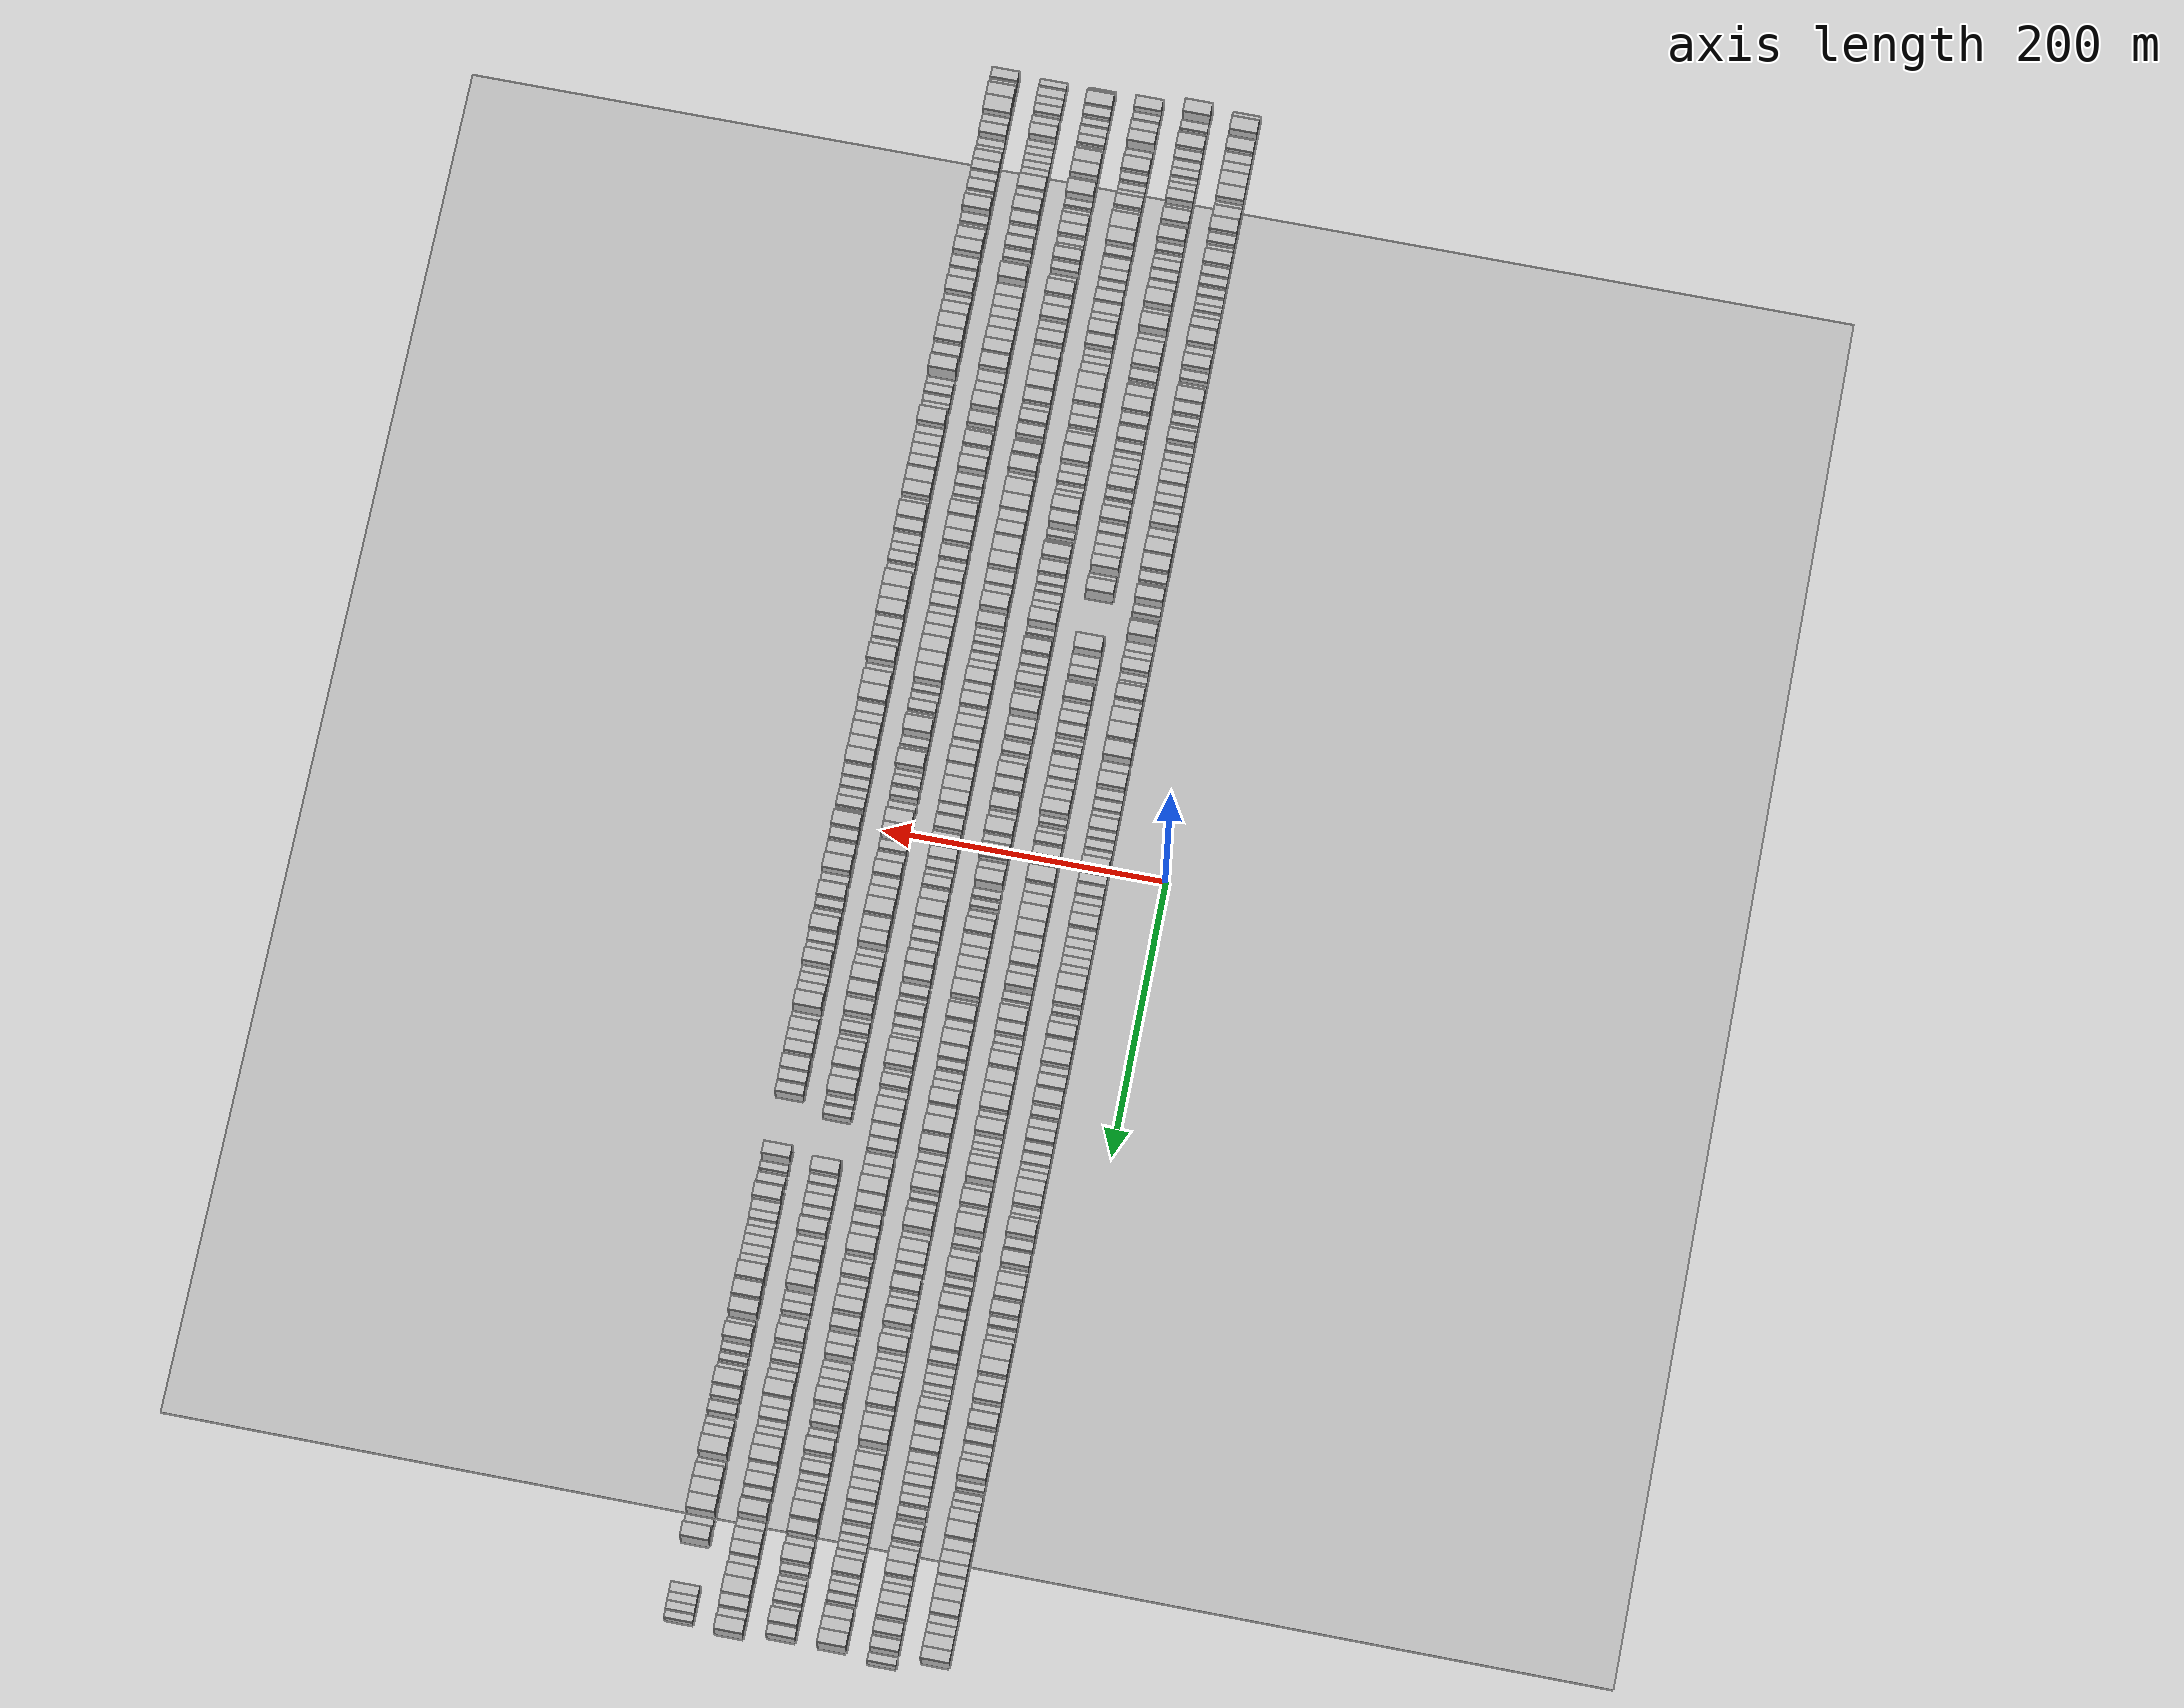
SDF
<?xml version="1.0" encoding="utf-8"?>

<sdf version="1.6">

   <world name="default">

      <gui fullscreen="0">

         <camera name="user_camera">

            <pose>-15 0 4.57585 0 0 0</pose>

            <view_controller>orbit</view_controller>

         </camera>

      </gui>

      <scene>

         <sky>

           <clouds>

             <speed>12</speed>

           </clouds>

         </sky>

         <ambient>0.4 0.4 0.4 1</ambient>

         <background>0.7 0.7 0.7 1</background>

         <shadows>1</shadows>

      </scene>

      <gravity>0 0 -9.8066</gravity>

      <magnetic_field>6e-06 2.3e-05 -4.2e-05</magnetic_field>

      <physics default="0" name="default_physics" type="ode">

         <ode>

            <solver>

               <type>quick</type>

               <iters>10</iters>

               <sor>1.0</sor>

               <use_dynamic_moi_rescaling>0</use_dynamic_moi_rescaling>

            </solver>

            <constraints>

               <cfm>0</cfm>

               <erp>0.2</erp>

               <contact_max_correcting_vel>100</contact_max_correcting_vel>

               <contact_surface_layer>0.001</contact_surface_layer>

            </constraints>

         </ode>

         <max_step_size>0.004</max_step_size>

         <real_time_factor>1</real_time_factor>

         <real_time_update_rate>250</real_time_update_rate>

      </physics>

      <light name="sun" type="directional">

         <cast_shadows>1</cast_shadows>

         <pose>0 0 10 0 0 0</pose>

         <diffuse>0.8 0.8 0.8 1</diffuse>

         <specular>0.2 0.2 0.2 1</specular>

         <attenuation>

            <range>1000</range>

            <constant>0.9</constant>

            <linear>0.01</linear>

            <quadratic>0.001</quadratic>

         </attenuation>

         <direction>-0.5 0.1 -0.9</direction>

      </light>

      <include>

         <name>ground_plane_1</name>

         <uri>model://HANNAS_ground_plane</uri>

         <pose>0 0 0  0 0 0</pose>

      </include>

      <include>

         <name>ground_plane_2</name>

         <uri>model://HANNAS_ground_plane</uri>

         <pose>100 0 0  0 0 0</pose>

      </include>

      <model name="building_1">

         <static>1</static>

         <pose frame="">50.0000 -566.6955 0 0.000000 0.000000 0.000000</pose>

         <link name="link">

            <pose frame="">0 0 7.50 0 0 0</pose>

            <collision name="collision">

               <geometry>

                  <box>

                     <size>20.0000 6.6091 15.0000</size>

                  </box>

               </geometry>

               <max_contacts>10</max_contacts>

               <surface>

                  <contact>

                     <ode/>

                  </contact>

                  <bounce/>

                  <friction>

                     <torsional>

                        <ode/>

                     </torsional>

                     <ode/>

                  </friction>

               </surface>

            </collision>

            <visual name="visual">

               <cast_shadows>0</cast_shadows>

               <geometry>

                  <box>

                     <size>20.0000 6.6091 15.0000</size>

                  </box>

               </geometry>

               <material>

                  <script>

                     <uri>model://HANNAS_wall/materials/scripts</uri>

                     <uri>model://HANNAS_wall/materials/textures</uri>

                     <name>vrc/HANNAS_wall</name>

                  </script>

               </material>

            </visual>

            <self_collide>0</self_collide>

            <enable_wind>0</enable_wind>

            <kinematic>0</kinematic>

         </link>

      </model>

      <model name="building_2">

         <static>1</static>

         <pose frame="">50.0000 -558.2066 0 0.000000 0.000000 0.000000</pose>

         <link name="link">

            <pose frame="">0 0 12.00 0 0 0</pose>

            <collision name="collision">

               <geometry>

                  <box>

                     <size>20.0000 10.3686 24.0000</size>

                  </box>

               </geometry>

               <max_contacts>10</max_contacts>

               <surface>

                  <contact>

                     <ode/>

                  </contact>

                  <bounce/>

                  <friction>

                     <torsional>

                        <ode/>

                     </torsional>

                     <ode/>

                  </friction>

               </surface>

            </collision>

            <visual name="visual">

               <cast_shadows>0</cast_shadows>

               <geometry>

                  <box>

                     <size>20.0000 10.3686 24.0000</size>

                  </box>

               </geometry>

               <material>

                  <script>

                     <uri>model://HANNAS_wall/materials/scripts</uri>

                     <uri>model://HANNAS_wall/materials/textures</uri>

                     <name>vrc/HANNAS_wall</name>

                  </script>

               </material>

            </visual>

            <self_collide>0</self_collide>

            <enable_wind>0</enable_wind>

            <kinematic>0</kinematic>

         </link>

      </model>

      <model name="building_3">

         <static>1</static>

         <pose frame="">50.0000 -550.3541 0 0.000000 0.000000 0.000000</pose>

         <link name="link">

            <pose frame="">0 0 6.00 0 0 0</pose>

            <collision name="collision">

               <geometry>

                  <box>

                     <size>20.0000 5.3364 12.0000</size>

                  </box>

               </geometry>

               <max_contacts>10</max_contacts>

               <surface>

                  <contact>

                     <ode/>

                  </contact>

                  <bounce/>

                  <friction>

                     <torsional>

                        <ode/>

                     </torsional>

                     <ode/>

                  </friction>

               </surface>

            </collision>

            <visual name="visual">

               <cast_shadows>0</cast_shadows>

               <geometry>

                  <box>

                     <size>20.0000 5.3364 12.0000</size>

                  </box>

               </geometry>

               <material>

                  <script>

                     <uri>model://HANNAS_wall/materials/scripts</uri>

                     <uri>model://HANNAS_wall/materials/textures</uri>

                     <name>vrc/HANNAS_wall</name>

                  </script>

               </material>

            </visual>

            <self_collide>0</self_collide>

            <enable_wind>0</enable_wind>

            <kinematic>0</kinematic>

         </link>

      </model>

      <model name="building_4">

         <static>1</static>

         <pose frame="">50.0000 -542.8709 0 0.000000 0.000000 0.000000</pose>

         <link name="link">

            <pose frame="">0 0 12.00 0 0 0</pose>

            <collision name="collision">

               <geometry>

                  <box>

                     <size>20.0000 9.6300 24.0000</size>

                  </box>

               </geometry>

               <max_contacts>10</max_contacts>

               <surface>

                  <contact>

                     <ode/>

                  </contact>

                  <bounce/>

                  <friction>

                     <torsional>

                        <ode/>

                     </torsional>

                     <ode/>

                  </friction>

               </surface>

            </collision>

            <visual name="visual">

               <cast_shadows>0</cast_shadows>

               <geometry>

                  <box>

                     <size>20.0000 9.6300 24.0000</size>

                  </box>

               </geometry>

               <material>

                  <script>

                     <uri>model://HANNAS_wall/materials/scripts</uri>

                     <uri>model://HANNAS_wall/materials/textures</uri>

                     <name>vrc/HANNAS_wall</name>

                  </script>

               </material>

            </visual>

            <self_collide>0</self_collide>

            <enable_wind>0</enable_wind>

            <kinematic>0</kinematic>

         </link>

      </model>

      <model name="building_5">

         <static>1</static>

         <pose frame="">50.0000 -534.3709 0 0.000000 0.000000 0.000000</pose>

         <link name="link">

            <pose frame="">0 0 9.00 0 0 0</pose>

            <collision name="collision">

               <geometry>

                  <box>

                     <size>20.0000 7.3699 18.0000</size>

                  </box>

               </geometry>

               <max_contacts>10</max_contacts>

               <surface>

                  <contact>

                     <ode/>

                  </contact>

                  <bounce/>

                  <friction>

                     <torsional>

                        <ode/>

                     </torsional>

                     <ode/>

                  </friction>

               </surface>

            </collision>

            <visual name="visual">

               <cast_shadows>0</cast_shadows>

               <geometry>

                  <box>

                     <size>20.0000 7.3699 18.0000</size>

                  </box>

               </geometry>

               <material>

                  <script>

                     <uri>model://HANNAS_wall/materials/scripts</uri>

                     <uri>model://HANNAS_wall/materials/textures</uri>

                     <name>vrc/HANNAS_wall</name>

                  </script>

               </material>

            </visual>

            <self_collide>0</self_collide>

            <enable_wind>0</enable_wind>

            <kinematic>0</kinematic>

         </link>

      </model>

      <model name="building_6">

         <static>1</static>

         <pose frame="">50.0000 -526.6155 0 0.000000 0.000000 0.000000</pose>

         <link name="link">

            <pose frame="">0 0 9.00 0 0 0</pose>

            <collision name="collision">

               <geometry>

                  <box>

                     <size>20.0000 8.1410 18.0000</size>

                  </box>

               </geometry>

               <max_contacts>10</max_contacts>

               <surface>

                  <contact>

                     <ode/>

                  </contact>

                  <bounce/>

                  <friction>

                     <torsional>

                        <ode/>

                     </torsional>

                     <ode/>

                  </friction>

               </surface>

            </collision>

            <visual name="visual">

               <cast_shadows>0</cast_shadows>

               <geometry>

                  <box>

                     <size>20.0000 8.1410 18.0000</size>

                  </box>

               </geometry>

               <material>

                  <script>

                     <uri>model://HANNAS_wall/materials/scripts</uri>

                     <uri>model://HANNAS_wall/materials/textures</uri>

                     <name>vrc/HANNAS_wall</name>

                  </script>

               </material>

            </visual>

            <self_collide>0</self_collide>

            <enable_wind>0</enable_wind>

            <kinematic>0</kinematic>

         </link>

      </model>

      <model name="building_7">

         <static>1</static>

         <pose frame="">50.0000 -517.3959 0 0.000000 0.000000 0.000000</pose>

         <link name="link">

            <pose frame="">0 0 10.50 0 0 0</pose>

            <collision name="collision">

               <geometry>

                  <box>

                     <size>20.0000 10.2983 21.0000</size>

                  </box>

               </geometry>

               <max_contacts>10</max_contacts>

               <surface>

                  <contact>

                     <ode/>

                  </contact>

                  <bounce/>

                  <friction>

                     <torsional>

                        <ode/>

                     </torsional>

                     <ode/>

                  </friction>

               </surface>

            </collision>

            <visual name="visual">

               <cast_shadows>0</cast_shadows>

               <geometry>

                  <box>

                     <size>20.0000 10.2983 21.0000</size>

                  </box>

               </geometry>

               <material>

                  <script>

                     <uri>model://HANNAS_wall/materials/scripts</uri>

                     <uri>model://HANNAS_wall/materials/textures</uri>

                     <name>vrc/HANNAS_wall</name>

                  </script>

               </material>

            </visual>

            <self_collide>0</self_collide>

            <enable_wind>0</enable_wind>

            <kinematic>0</kinematic>

         </link>

      </model>

      <model name="building_8">

         <static>1</static>

         <pose frame="">50.0000 -507.0479 0 0.000000 0.000000 0.000000</pose>

         <link name="link">

            <pose frame="">0 0 10.50 0 0 0</pose>

            <collision name="collision">

               <geometry>

                  <box>

                     <size>20.0000 10.3977 21.0000</size>

                  </box>

               </geometry>

               <max_contacts>10</max_contacts>

               <surface>

                  <contact>

                     <ode/>

                  </contact>

                  <bounce/>

                  <friction>

                     <torsional>

                        <ode/>

                     </torsional>

                     <ode/>

                  </friction>

               </surface>

            </collision>

            <visual name="visual">

               <cast_shadows>0</cast_shadows>

               <geometry>

                  <box>

                     <size>20.0000 10.3977 21.0000</size>

                  </box>

               </geometry>

               <material>

                  <script>

                     <uri>model://HANNAS_wall/materials/scripts</uri>

                     <uri>model://HANNAS_wall/materials/textures</uri>

                     <name>vrc/HANNAS_wall</name>

                  </script>

               </material>

            </visual>

            <self_collide>0</self_collide>

            <enable_wind>0</enable_wind>

            <kinematic>0</kinematic>

         </link>

      </model>

      <model name="building_9">

         <static>1</static>

         <pose frame="">50.0000 -499.2907 0 0.000000 0.000000 0.000000</pose>

         <link name="link">

            <pose frame="">0 0 6.00 0 0 0</pose>

            <collision name="collision">

               <geometry>

                  <box>

                     <size>20.0000 5.1166 12.0000</size>

                  </box>

               </geometry>

               <max_contacts>10</max_contacts>

               <surface>

                  <contact>

                     <ode/>

                  </contact>

                  <bounce/>

                  <friction>

                     <torsional>

                        <ode/>

                     </torsional>

                     <ode/>

                  </friction>

               </surface>

            </collision>

            <visual name="visual">

               <cast_shadows>0</cast_shadows>

               <geometry>

                  <box>

                     <size>20.0000 5.1166 12.0000</size>

                  </box>

               </geometry>

               <material>

                  <script>

                     <uri>model://HANNAS_wall/materials/scripts</uri>

                     <uri>model://HANNAS_wall/materials/textures</uri>

                     <name>vrc/HANNAS_wall</name>

                  </script>

               </material>

            </visual>

            <self_collide>0</self_collide>

            <enable_wind>0</enable_wind>

            <kinematic>0</kinematic>

         </link>

      </model>

      <model name="building_10">

         <static>1</static>

         <pose frame="">50.0000 -492.3343 0 0.000000 0.000000 0.000000</pose>

         <link name="link">

            <pose frame="">0 0 9.00 0 0 0</pose>

            <collision name="collision">

               <geometry>

                  <box>

                     <size>20.0000 8.7961 18.0000</size>

                  </box>

               </geometry>

               <max_contacts>10</max_contacts>

               <surface>

                  <contact>

                     <ode/>

                  </contact>

                  <bounce/>

                  <friction>

                     <torsional>

                        <ode/>

                     </torsional>

                     <ode/>

                  </friction>

               </surface>

            </collision>

            <visual name="visual">

               <cast_shadows>0</cast_shadows>

               <geometry>

                  <box>

                     <size>20.0000 8.7961 18.0000</size>

                  </box>

               </geometry>

               <material>

                  <script>

                     <uri>model://HANNAS_wall/materials/scripts</uri>

                     <uri>model://HANNAS_wall/materials/textures</uri>

                     <name>vrc/HANNAS_wall</name>

                  </script>

               </material>

            </visual>

            <self_collide>0</self_collide>

            <enable_wind>0</enable_wind>

            <kinematic>0</kinematic>

         </link>

      </model>

      <model name="building_11">

         <static>1</static>

         <pose frame="">50.0000 -480.7830 0 0.000000 0.000000 0.000000</pose>

         <link name="link">

            <pose frame="">0 0 12.00 0 0 0</pose>

            <collision name="collision">

               <geometry>

                  <box>

                     <size>20.0000 10.3066 24.0000</size>

                  </box>

               </geometry>

               <max_contacts>10</max_contacts>

               <surface>

                  <contact>

                     <ode/>

                  </contact>

                  <bounce/>

                  <friction>

                     <torsional>

                        <ode/>

                     </torsional>

                     <ode/>

                  </friction>

               </surface>

            </collision>

            <visual name="visual">

               <cast_shadows>0</cast_shadows>

               <geometry>

                  <box>

                     <size>20.0000 10.3066 24.0000</size>

                  </box>

               </geometry>

               <material>

                  <script>

                     <uri>model://HANNAS_wall/materials/scripts</uri>

                     <uri>model://HANNAS_wall/materials/textures</uri>

                     <name>vrc/HANNAS_wall</name>

                  </script>

               </material>

            </visual>

            <self_collide>0</self_collide>

            <enable_wind>0</enable_wind>

            <kinematic>0</kinematic>

         </link>

      </model>

      <model name="building_12">

         <static>1</static>

         <pose frame="">50.0000 -471.9959 0 0.000000 0.000000 0.000000</pose>

         <link name="link">

            <pose frame="">0 0 9.00 0 0 0</pose>

            <collision name="collision">

               <geometry>

                  <box>

                     <size>20.0000 7.2675 18.0000</size>

                  </box>

               </geometry>

               <max_contacts>10</max_contacts>

               <surface>

                  <contact>

                     <ode/>

                  </contact>

                  <bounce/>

                  <friction>

                     <torsional>

                        <ode/>

                     </torsional>

                     <ode/>

                  </friction>

               </surface>

            </collision>

            <visual name="visual">

               <cast_shadows>0</cast_shadows>

               <geometry>

                  <box>

                     <size>20.0000 7.2675 18.0000</size>

                  </box>

               </geometry>

               <material>

                  <script>

                     <uri>model://HANNAS_wall/materials/scripts</uri>

                     <uri>model://HANNAS_wall/materials/textures</uri>

                     <name>vrc/HANNAS_wall</name>

                  </script>

               </material>

            </visual>

            <self_collide>0</self_collide>

            <enable_wind>0</enable_wind>

            <kinematic>0</kinematic>

         </link>

      </model>

      <model name="building_13">

         <static>1</static>

         <pose frame="">50.0000 -465.6149 0 0.000000 0.000000 0.000000</pose>

         <link name="link">

            <pose frame="">0 0 6.00 0 0 0</pose>

            <collision name="collision">

               <geometry>

                  <box>

                     <size>20.0000 5.4946 12.0000</size>

                  </box>

               </geometry>

               <max_contacts>10</max_contacts>

               <surface>

                  <contact>

                     <ode/>

                  </contact>

                  <bounce/>

                  <friction>

                     <torsional>

                        <ode/>

                     </torsional>

                     <ode/>

                  </friction>

               </surface>

            </collision>

            <visual name="visual">

               <cast_shadows>0</cast_shadows>

               <geometry>

                  <box>

                     <size>20.0000 5.4946 12.0000</size>

                  </box>

               </geometry>

               <material>

                  <script>

                     <uri>model://HANNAS_wall/materials/scripts</uri>

                     <uri>model://HANNAS_wall/materials/textures</uri>

                     <name>vrc/HANNAS_wall</name>

                  </script>

               </material>

            </visual>

            <self_collide>0</self_collide>

            <enable_wind>0</enable_wind>

            <kinematic>0</kinematic>

         </link>

      </model>

      <model name="building_14">

         <static>1</static>

         <pose frame="">50.0000 -456.6829 0 0.000000 0.000000 0.000000</pose>

         <link name="link">

            <pose frame="">0 0 10.50 0 0 0</pose>

            <collision name="collision">

               <geometry>

                  <box>

                     <size>20.0000 10.3693 21.0000</size>

                  </box>

               </geometry>

               <max_contacts>10</max_contacts>

               <surface>

                  <contact>

                     <ode/>

                  </contact>

                  <bounce/>

                  <friction>

                     <torsional>

                        <ode/>

                     </torsional>

                     <ode/>

                  </friction>

               </surface>

            </collision>

            <visual name="visual">

               <cast_shadows>0</cast_shadows>

               <geometry>

                  <box>

                     <size>20.0000 10.3693 21.0000</size>

                  </box>

               </geometry>

               <material>

                  <script>

                     <uri>model://HANNAS_wall/materials/scripts</uri>

                     <uri>model://HANNAS_wall/materials/textures</uri>

                     <name>vrc/HANNAS_wall</name>

                  </script>

               </material>

            </visual>

            <self_collide>0</self_collide>

            <enable_wind>0</enable_wind>

            <kinematic>0</kinematic>

         </link>

      </model>

      <model name="building_15">

         <static>1</static>

         <pose frame="">50.0000 -447.9910 0 0.000000 0.000000 0.000000</pose>

         <link name="link">

            <pose frame="">0 0 7.50 0 0 0</pose>

            <collision name="collision">

               <geometry>

                  <box>

                     <size>20.0000 7.0146 15.0000</size>

                  </box>

               </geometry>

               <max_contacts>10</max_contacts>

               <surface>

                  <contact>

                     <ode/>

                  </contact>

                  <bounce/>

                  <friction>

                     <torsional>

                        <ode/>

                     </torsional>

                     <ode/>

                  </friction>

               </surface>

            </collision>

            <visual name="visual">

               <cast_shadows>0</cast_shadows>

               <geometry>

                  <box>

                     <size>20.0000 7.0146 15.0000</size>

                  </box>

               </geometry>

               <material>

                  <script>

                     <uri>model://HANNAS_wall/materials/scripts</uri>

                     <uri>model://HANNAS_wall/materials/textures</uri>

                     <name>vrc/HANNAS_wall</name>

                  </script>

               </material>

            </visual>

            <self_collide>0</self_collide>

            <enable_wind>0</enable_wind>

            <kinematic>0</kinematic>

         </link>

      </model>

      <model name="building_16">

         <static>1</static>

         <pose frame="">50.0000 -440.1309 0 0.000000 0.000000 0.000000</pose>

         <link name="link">

            <pose frame="">0 0 7.50 0 0 0</pose>

            <collision name="collision">

               <geometry>

                  <box>

                     <size>20.0000 6.7055 15.0000</size>

                  </box>

               </geometry>

               <max_contacts>10</max_contacts>

               <surface>

                  <contact>

                     <ode/>

                  </contact>

                  <bounce/>

                  <friction>

                     <torsional>

                        <ode/>

                     </torsional>

                     <ode/>

                  </friction>

               </surface>

            </collision>

            <visual name="visual">

               <cast_shadows>0</cast_shadows>

               <geometry>

                  <box>

                     <size>20.0000 6.7055 15.0000</size>

                  </box>

               </geometry>

               <material>

                  <script>

                     <uri>model://HANNAS_wall/materials/scripts</uri>

                     <uri>model://HANNAS_wall/materials/textures</uri>

                     <name>vrc/HANNAS_wall</name>

                  </script>

               </material>

            </visual>

            <self_collide>0</self_collide>

            <enable_wind>0</enable_wind>

            <kinematic>0</kinematic>

         </link>

      </model>

      <model name="building_17">

         <static>1</static>

         <pose frame="">50.0000 -431.6182 0 0.000000 0.000000 0.000000</pose>

         <link name="link">

            <pose frame="">0 0 7.50 0 0 0</pose>

            <collision name="collision">

               <geometry>

                  <box>

                     <size>20.0000 6.3200 15.0000</size>

                  </box>

               </geometry>

               <max_contacts>10</max_contacts>

               <surface>

                  <contact>

                     <ode/>

                  </contact>

                  <bounce/>

                  <friction>

                     <torsional>

                        <ode/>

                     </torsional>

                     <ode/>

                  </friction>

               </surface>

            </collision>

            <visual name="visual">

               <cast_shadows>0</cast_shadows>

               <geometry>

                  <box>

                     <size>20.0000 6.3200 15.0000</size>

                  </box>

               </geometry>

               <material>

                  <script>

                     <uri>model://HANNAS_wall/materials/scripts</uri>

                     <uri>model://HANNAS_wall/materials/textures</uri>

                     <name>vrc/HANNAS_wall</name>

                  </script>

               </material>

            </visual>

            <self_collide>0</self_collide>

            <enable_wind>0</enable_wind>

            <kinematic>0</kinematic>

         </link>

      </model>

      <model name="building_18">

         <static>1</static>

         <pose frame="">50.0000 -425.5601 0 0.000000 0.000000 0.000000</pose>

         <link name="link">

            <pose frame="">0 0 6.00 0 0 0</pose>

            <collision name="collision">

               <geometry>

                  <box>

                     <size>20.0000 5.7961 12.0000</size>

                  </box>

               </geometry>

               <max_contacts>10</max_contacts>

               <surface>

                  <contact>

                     <ode/>

                  </contact>

                  <bounce/>

                  <friction>

                     <torsional>

                        <ode/>

                     </torsional>

                     <ode/>

                  </friction>

               </surface>

            </collision>

            <visual name="visual">

               <cast_shadows>0</cast_shadows>

               <geometry>

                  <box>

                     <size>20.0000 5.7961 12.0000</size>

                  </box>

               </geometry>

               <material>

                  <script>

                     <uri>model://HANNAS_wall/materials/scripts</uri>

                     <uri>model://HANNAS_wall/materials/textures</uri>

                     <name>vrc/HANNAS_wall</name>

                  </script>

               </material>

            </visual>

            <self_collide>0</self_collide>

            <enable_wind>0</enable_wind>

            <kinematic>0</kinematic>

         </link>

      </model>

      <model name="building_19">

         <static>1</static>

         <pose frame="">50.0000 -420.1431 0 0.000000 0.000000 0.000000</pose>

         <link name="link">

            <pose frame="">0 0 6.00 0 0 0</pose>

            <collision name="collision">

               <geometry>

                  <box>

                     <size>20.0000 5.0380 12.0000</size>

                  </box>

               </geometry>

               <max_contacts>10</max_contacts>

               <surface>

                  <contact>

                     <ode/>

                  </contact>

                  <bounce/>

                  <friction>

                     <torsional>

                        <ode/>

                     </torsional>

                     <ode/>

                  </friction>

               </surface>

            </collision>

            <visual name="visual">

               <cast_shadows>0</cast_shadows>

               <geometry>

                  <box>

                     <size>20.0000 5.0380 12.0000</size>

                  </box>

               </geometry>

               <material>

                  <script>

                     <uri>model://HANNAS_wall/materials/scripts</uri>

                     <uri>model://HANNAS_wall/materials/textures</uri>

                     <name>vrc/HANNAS_wall</name>

                  </script>

               </material>

            </visual>

            <self_collide>0</self_collide>

            <enable_wind>0</enable_wind>

            <kinematic>0</kinematic>

         </link>

      </model>

      <model name="building_20">

         <static>1</static>

         <pose frame="">50.0000 -413.6426 0 0.000000 0.000000 0.000000</pose>

         <link name="link">

            <pose frame="">0 0 6.00 0 0 0</pose>

            <collision name="collision">

               <geometry>

                  <box>

                     <size>20.0000 5.9629 12.0000</size>

                  </box>

               </geometry>

               <max_contacts>10</max_contacts>

               <surface>

                  <contact>

                     <ode/>

                  </contact>

                  <bounce/>

                  <friction>

                     <torsional>

                        <ode/>

                     </torsional>

                     <ode/>

                  </friction>

               </surface>

            </collision>

            <visual name="visual">

               <cast_shadows>0</cast_shadows>

               <geometry>

                  <box>

                     <size>20.0000 5.9629 12.0000</size>

                  </box>

               </geometry>

               <material>

                  <script>

                     <uri>model://HANNAS_wall/materials/scripts</uri>

                     <uri>model://HANNAS_wall/materials/textures</uri>

                     <name>vrc/HANNAS_wall</name>

                  </script>

               </material>

            </visual>

            <self_collide>0</self_collide>

            <enable_wind>0</enable_wind>

            <kinematic>0</kinematic>

         </link>

      </model>

      <model name="building_21">

         <static>1</static>

         <pose frame="">50.0000 -406.9876 0 0.000000 0.000000 0.000000</pose>

         <link name="link">

            <pose frame="">0 0 9.00 0 0 0</pose>

            <collision name="collision">

               <geometry>

                  <box>

                     <size>20.0000 7.3472 18.0000</size>

                  </box>

               </geometry>

               <max_contacts>10</max_contacts>

               <surface>

                  <contact>

                     <ode/>

                  </contact>

                  <bounce/>

                  <friction>

                     <torsional>

                        <ode/>

                     </torsional>

                     <ode/>

                  </friction>

               </surface>

            </collision>

            <visual name="visual">

               <cast_shadows>0</cast_shadows>

               <geometry>

                  <box>

                     <size>20.0000 7.3472 18.0000</size>

                  </box>

               </geometry>

               <material>

                  <script>

                     <uri>model://HANNAS_wall/materials/scripts</uri>

                     <uri>model://HANNAS_wall/materials/textures</uri>

                     <name>vrc/HANNAS_wall</name>

                  </script>

               </material>

            </visual>

            <self_collide>0</self_collide>

            <enable_wind>0</enable_wind>

            <kinematic>0</kinematic>

         </link>

      </model>

      <model name="building_22">

         <static>1</static>

         <pose frame="">50.0000 -394.6704 0 0.000000 0.000000 0.000000</pose>

         <link name="link">

            <pose frame="">0 0 12.00 0 0 0</pose>

            <collision name="collision">

               <geometry>

                  <box>

                     <size>20.0000 11.2872 24.0000</size>

                  </box>

               </geometry>

               <max_contacts>10</max_contacts>

               <surface>

                  <contact>

                     <ode/>

                  </contact>

                  <bounce/>

                  <friction>

                     <torsional>

                        <ode/>

                     </torsional>

                     <ode/>

                  </friction>

               </surface>

            </collision>

            <visual name="visual">

               <cast_shadows>0</cast_shadows>

               <geometry>

                  <box>

                     <size>20.0000 11.2872 24.0000</size>

                  </box>

               </geometry>

               <material>

                  <script>

                     <uri>model://HANNAS_wall/materials/scripts</uri>

                     <uri>model://HANNAS_wall/materials/textures</uri>

                     <name>vrc/HANNAS_wall</name>

                  </script>

               </material>

            </visual>

            <self_collide>0</self_collide>

            <enable_wind>0</enable_wind>

            <kinematic>0</kinematic>

         </link>

      </model>

      <model name="building_23">

         <static>1</static>

         <pose frame="">50.0000 -385.6623 0 0.000000 0.000000 0.000000</pose>

         <link name="link">

            <pose frame="">0 0 7.50 0 0 0</pose>

            <collision name="collision">

               <geometry>

                  <box>

                     <size>20.0000 6.7290 15.0000</size>

                  </box>

               </geometry>

               <max_contacts>10</max_contacts>

               <surface>

                  <contact>

                     <ode/>

                  </contact>

                  <bounce/>

                  <friction>

                     <torsional>

                        <ode/>

                     </torsional>

                     <ode/>

                  </friction>

               </surface>

            </collision>

            <visual name="visual">

               <cast_shadows>0</cast_shadows>

               <geometry>

                  <box>

                     <size>20.0000 6.7290 15.0000</size>

                  </box>

               </geometry>

               <material>

                  <script>

                     <uri>model://HANNAS_wall/materials/scripts</uri>

                     <uri>model://HANNAS_wall/materials/textures</uri>

                     <name>vrc/HANNAS_wall</name>

                  </script>

               </material>

            </visual>

            <self_collide>0</self_collide>

            <enable_wind>0</enable_wind>

            <kinematic>0</kinematic>

         </link>

      </model>

      <model name="building_24">

         <static>1</static>

         <pose frame="">50.0000 -375.4897 0 0.000000 0.000000 0.000000</pose>

         <link name="link">

            <pose frame="">0 0 12.00 0 0 0</pose>

            <collision name="collision">

               <geometry>

                  <box>

                     <size>20.0000 9.6162 24.0000</size>

                  </box>

               </geometry>

               <max_contacts>10</max_contacts>

               <surface>

                  <contact>

                     <ode/>

                  </contact>

                  <bounce/>

                  <friction>

                     <torsional>

                        <ode/>

                     </torsional>

                     <ode/>

                  </friction>

               </surface>

            </collision>

            <visual name="visual">

               <cast_shadows>0</cast_shadows>

               <geometry>

                  <box>

                     <size>20.0000 9.6162 24.0000</size>

                  </box>

               </geometry>

               <material>

                  <script>

                     <uri>model://HANNAS_wall/materials/scripts</uri>

                     <uri>model://HANNAS_wall/materials/textures</uri>

                     <name>vrc/HANNAS_wall</name>

                  </script>

               </material>

            </visual>

            <self_collide>0</self_collide>

            <enable_wind>0</enable_wind>

            <kinematic>0</kinematic>

         </link>

      </model>

      <model name="building_25">

         <static>1</static>

         <pose frame="">50.0000 -367.2235 0 0.000000 0.000000 0.000000</pose>

         <link name="link">

            <pose frame="">0 0 7.50 0 0 0</pose>

            <collision name="collision">

               <geometry>

                  <box>

                     <size>20.0000 6.9162 15.0000</size>

                  </box>

               </geometry>

               <max_contacts>10</max_contacts>

               <surface>

                  <contact>

                     <ode/>

                  </contact>

                  <bounce/>

                  <friction>

                     <torsional>

                        <ode/>

                     </torsional>

                     <ode/>

                  </friction>

               </surface>

            </collision>

            <visual name="visual">

               <cast_shadows>0</cast_shadows>

               <geometry>

                  <box>

                     <size>20.0000 6.9162 15.0000</size>

                  </box>

               </geometry>

               <material>

                  <script>

                     <uri>model://HANNAS_wall/materials/scripts</uri>

                     <uri>model://HANNAS_wall/materials/textures</uri>

                     <name>vrc/HANNAS_wall</name>

                  </script>

               </material>

            </visual>

            <self_collide>0</self_collide>

            <enable_wind>0</enable_wind>

            <kinematic>0</kinematic>

         </link>

      </model>

      <model name="building_26">

         <static>1</static>

         <pose frame="">50.0000 -359.0324 0 0.000000 0.000000 0.000000</pose>

         <link name="link">

            <pose frame="">0 0 6.00 0 0 0</pose>

            <collision name="collision">

               <geometry>

                  <box>

                     <size>20.0000 5.4661 12.0000</size>

                  </box>

               </geometry>

               <max_contacts>10</max_contacts>

               <surface>

                  <contact>

                     <ode/>

                  </contact>

                  <bounce/>

                  <friction>

                     <torsional>

                        <ode/>

                     </torsional>

                     <ode/>

                  </friction>

               </surface>

            </collision>

            <visual name="visual">

               <cast_shadows>0</cast_shadows>

               <geometry>

                  <box>

                     <size>20.0000 5.4661 12.0000</size>

                  </box>

               </geometry>

               <material>

                  <script>

                     <uri>model://HANNAS_wall/materials/scripts</uri>

                     <uri>model://HANNAS_wall/materials/textures</uri>

                     <name>vrc/HANNAS_wall</name>

                  </script>

               </material>

            </visual>

            <self_collide>0</self_collide>

            <enable_wind>0</enable_wind>

            <kinematic>0</kinematic>

         </link>

      </model>

      <model name="building_27">

         <static>1</static>

         <pose frame="">50.0000 -351.0920 0 0.000000 0.000000 0.000000</pose>

         <link name="link">

            <pose frame="">0 0 10.50 0 0 0</pose>

            <collision name="collision">

               <geometry>

                  <box>

                     <size>20.0000 10.4146 21.0000</size>

                  </box>

               </geometry>

               <max_contacts>10</max_contacts>

               <surface>

                  <contact>

                     <ode/>

                  </contact>

                  <bounce/>

                  <friction>

                     <torsional>

                        <ode/>

                     </torsional>

                     <ode/>

                  </friction>

               </surface>

            </collision>

            <visual name="visual">

               <cast_shadows>0</cast_shadows>

               <geometry>

                  <box>

                     <size>20.0000 10.4146 21.0000</size>

                  </box>

               </geometry>

               <material>

                  <script>

                     <uri>model://HANNAS_wall/materials/scripts</uri>

                     <uri>model://HANNAS_wall/materials/textures</uri>

                     <name>vrc/HANNAS_wall</name>

                  </script>

               </material>

            </visual>

            <self_collide>0</self_collide>

            <enable_wind>0</enable_wind>

            <kinematic>0</kinematic>

         </link>

      </model>

      <model name="building_28">

         <static>1</static>

         <pose frame="">50.0000 -340.5171 0 0.000000 0.000000 0.000000</pose>

         <link name="link">

            <pose frame="">0 0 10.50 0 0 0</pose>

            <collision name="collision">

               <geometry>

                  <box>

                     <size>20.0000 8.7352 21.0000</size>

                  </box>

               </geometry>

               <max_contacts>10</max_contacts>

               <surface>

                  <contact>

                     <ode/>

                  </contact>

                  <bounce/>

                  <friction>

                     <torsional>

                        <ode/>

                     </torsional>

                     <ode/>

                  </friction>

               </surface>

            </collision>

            <visual name="visual">

               <cast_shadows>0</cast_shadows>

               <geometry>

                  <box>

                     <size>20.0000 8.7352 21.0000</size>

                  </box>

               </geometry>

               <material>

                  <script>

                     <uri>model://HANNAS_wall/materials/scripts</uri>

                     <uri>model://HANNAS_wall/materials/textures</uri>

                     <name>vrc/HANNAS_wall</name>

                  </script>

               </material>

            </visual>

            <self_collide>0</self_collide>

            <enable_wind>0</enable_wind>

            <kinematic>0</kinematic>

         </link>

      </model>

      <model name="building_29">

         <static>1</static>

         <pose frame="">50.0000 -333.0898 0 0.000000 0.000000 0.000000</pose>

         <link name="link">

            <pose frame="">0 0 7.50 0 0 0</pose>

            <collision name="collision">

               <geometry>

                  <box>

                     <size>20.0000 6.1194 15.0000</size>

                  </box>

               </geometry>

               <max_contacts>10</max_contacts>

               <surface>

                  <contact>

                     <ode/>

                  </contact>

                  <bounce/>

                  <friction>

                     <torsional>

                        <ode/>

                     </torsional>

                     <ode/>

                  </friction>

               </surface>

            </collision>

            <visual name="visual">

               <cast_shadows>0</cast_shadows>

               <geometry>

                  <box>

                     <size>20.0000 6.1194 15.0000</size>

                  </box>

               </geometry>

               <material>

                  <script>

                     <uri>model://HANNAS_wall/materials/scripts</uri>

                     <uri>model://HANNAS_wall/materials/textures</uri>

                     <name>vrc/HANNAS_wall</name>

                  </script>

               </material>

            </visual>

            <self_collide>0</self_collide>

            <enable_wind>0</enable_wind>

            <kinematic>0</kinematic>

         </link>

      </model>

      <model name="building_30">

         <static>1</static>

         <pose frame="">50.0000 -327.0355 0 0.000000 0.000000 0.000000</pose>

         <link name="link">

            <pose frame="">0 0 6.00 0 0 0</pose>

            <collision name="collision">

               <geometry>

                  <box>

                     <size>20.0000 5.9892 12.0000</size>

                  </box>

               </geometry>

               <max_contacts>10</max_contacts>

               <surface>

                  <contact>

                     <ode/>

                  </contact>

                  <bounce/>

                  <friction>

                     <torsional>

                        <ode/>

                     </torsional>

                     <ode/>

                  </friction>

               </surface>

            </collision>

            <visual name="visual">

               <cast_shadows>0</cast_shadows>

               <geometry>

                  <box>

                     <size>20.0000 5.9892 12.0000</size>

                  </box>

               </geometry>

               <material>

                  <script>

                     <uri>model://HANNAS_wall/materials/scripts</uri>

                     <uri>model://HANNAS_wall/materials/textures</uri>

                     <name>vrc/HANNAS_wall</name>

                  </script>

               </material>

            </visual>

            <self_collide>0</self_collide>

            <enable_wind>0</enable_wind>

            <kinematic>0</kinematic>

         </link>

      </model>

      <model name="building_31">

         <static>1</static>

         <pose frame="">50.0000 -319.6164 0 0.000000 0.000000 0.000000</pose>

         <link name="link">

            <pose frame="">0 0 10.50 0 0 0</pose>

            <collision name="collision">

               <geometry>

                  <box>

                     <size>20.0000 8.8489 21.0000</size>

                  </box>

               </geometry>

               <max_contacts>10</max_contacts>

               <surface>

                  <contact>

                     <ode/>

                  </contact>

                  <bounce/>

                  <friction>

                     <torsional>

                        <ode/>

                     </torsional>

                     <ode/>

                  </friction>

               </surface>

            </collision>

            <visual name="visual">

               <cast_shadows>0</cast_shadows>

               <geometry>

                  <box>

                     <size>20.0000 8.8489 21.0000</size>

                  </box>

               </geometry>

               <material>

                  <script>

                     <uri>model://HANNAS_wall/materials/scripts</uri>

                     <uri>model://HANNAS_wall/materials/textures</uri>

                     <name>vrc/HANNAS_wall</name>

                  </script>

               </material>

            </visual>

            <self_collide>0</self_collide>

            <enable_wind>0</enable_wind>

            <kinematic>0</kinematic>

         </link>

      </model>

      <model name="building_32">

         <static>1</static>

         <pose frame="">50.0000 -312.4067 0 0.000000 0.000000 0.000000</pose>

         <link name="link">

            <pose frame="">0 0 6.00 0 0 0</pose>

            <collision name="collision">

               <geometry>

                  <box>

                     <size>20.0000 5.5707 12.0000</size>

                  </box>

               </geometry>

               <max_contacts>10</max_contacts>

               <surface>

                  <contact>

                     <ode/>

                  </contact>

                  <bounce/>

                  <friction>

                     <torsional>

                        <ode/>

                     </torsional>

                     <ode/>

                  </friction>

               </surface>

            </collision>

            <visual name="visual">

               <cast_shadows>0</cast_shadows>

               <geometry>

                  <box>

                     <size>20.0000 5.5707 12.0000</size>

                  </box>

               </geometry>

               <material>

                  <script>

                     <uri>model://HANNAS_wall/materials/scripts</uri>

                     <uri>model://HANNAS_wall/materials/textures</uri>

                     <name>vrc/HANNAS_wall</name>

                  </script>

               </material>

            </visual>

            <self_collide>0</self_collide>

            <enable_wind>0</enable_wind>

            <kinematic>0</kinematic>

         </link>

      </model>

      <model name="building_33">

         <static>1</static>

         <pose frame="">50.0000 -304.5774 0 0.000000 0.000000 0.000000</pose>

         <link name="link">

            <pose frame="">0 0 7.50 0 0 0</pose>

            <collision name="collision">

               <geometry>

                  <box>

                     <size>20.0000 6.0878 15.0000</size>

                  </box>

               </geometry>

               <max_contacts>10</max_contacts>

               <surface>

                  <contact>

                     <ode/>

                  </contact>

                  <bounce/>

                  <friction>

                     <torsional>

                        <ode/>

                     </torsional>

                     <ode/>

                  </friction>

               </surface>

            </collision>

            <visual name="visual">

               <cast_shadows>0</cast_shadows>

               <geometry>

                  <box>

                     <size>20.0000 6.0878 15.0000</size>

                  </box>

               </geometry>

               <material>

                  <script>

                     <uri>model://HANNAS_wall/materials/scripts</uri>

                     <uri>model://HANNAS_wall/materials/textures</uri>

                     <name>vrc/HANNAS_wall</name>

                  </script>

               </material>

            </visual>

            <self_collide>0</self_collide>

            <enable_wind>0</enable_wind>

            <kinematic>0</kinematic>

         </link>

      </model>

      <model name="building_34">

         <static>1</static>

         <pose frame="">50.0000 -296.4099 0 0.000000 0.000000 0.000000</pose>

         <link name="link">

            <pose frame="">0 0 9.00 0 0 0</pose>

            <collision name="collision">

               <geometry>

                  <box>

                     <size>20.0000 8.2473 18.0000</size>

                  </box>

               </geometry>

               <max_contacts>10</max_contacts>

               <surface>

                  <contact>

                     <ode/>

                  </contact>

                  <bounce/>

                  <friction>

                     <torsional>

                        <ode/>

                     </torsional>

                     <ode/>

                  </friction>

               </surface>

            </collision>

            <visual name="visual">

               <cast_shadows>0</cast_shadows>

               <geometry>

                  <box>

                     <size>20.0000 8.2473 18.0000</size>

                  </box>

               </geometry>

               <material>

                  <script>

                     <uri>model://HANNAS_wall/materials/scripts</uri>

                     <uri>model://HANNAS_wall/materials/textures</uri>

                     <name>vrc/HANNAS_wall</name>

                  </script>

               </material>

            </visual>

            <self_collide>0</self_collide>

            <enable_wind>0</enable_wind>

            <kinematic>0</kinematic>

         </link>

      </model>

      <model name="building_35">

         <static>1</static>

         <pose frame="">50.0000 -287.8612 0 0.000000 0.000000 0.000000</pose>

         <link name="link">

            <pose frame="">0 0 10.50 0 0 0</pose>

            <collision name="collision">

               <geometry>

                  <box>

                     <size>20.0000 8.8501 21.0000</size>

                  </box>

               </geometry>

               <max_contacts>10</max_contacts>

               <surface>

                  <contact>

                     <ode/>

                  </contact>

                  <bounce/>

                  <friction>

                     <torsional>

                        <ode/>

                     </torsional>

                     <ode/>

                  </friction>

               </surface>

            </collision>

            <visual name="visual">

               <cast_shadows>0</cast_shadows>

               <geometry>

                  <box>

                     <size>20.0000 8.8501 21.0000</size>

                  </box>

               </geometry>

               <material>

                  <script>

                     <uri>model://HANNAS_wall/materials/scripts</uri>

                     <uri>model://HANNAS_wall/materials/textures</uri>

                     <name>vrc/HANNAS_wall</name>

                  </script>

               </material>

            </visual>

            <self_collide>0</self_collide>

            <enable_wind>0</enable_wind>

            <kinematic>0</kinematic>

         </link>

      </model>

      <model name="building_36">

         <static>1</static>

         <pose frame="">50.0000 -279.5082 0 0.000000 0.000000 0.000000</pose>

         <link name="link">

            <pose frame="">0 0 9.00 0 0 0</pose>

            <collision name="collision">

               <geometry>

                  <box>

                     <size>20.0000 7.8559 18.0000</size>

                  </box>

               </geometry>

               <max_contacts>10</max_contacts>

               <surface>

                  <contact>

                     <ode/>

                  </contact>

                  <bounce/>

                  <friction>

                     <torsional>

                        <ode/>

                     </torsional>

                     <ode/>

                  </friction>

               </surface>

            </collision>

            <visual name="visual">

               <cast_shadows>0</cast_shadows>

               <geometry>

                  <box>

                     <size>20.0000 7.8559 18.0000</size>

                  </box>

               </geometry>

               <material>

                  <script>

                     <uri>model://HANNAS_wall/materials/scripts</uri>

                     <uri>model://HANNAS_wall/materials/textures</uri>

                     <name>vrc/HANNAS_wall</name>

                  </script>

               </material>

            </visual>

            <self_collide>0</self_collide>

            <enable_wind>0</enable_wind>

            <kinematic>0</kinematic>

         </link>

      </model>

      <model name="building_37">

         <static>1</static>

         <pose frame="">50.0000 -271.6983 0 0.000000 0.000000 0.000000</pose>

         <link name="link">

            <pose frame="">0 0 9.00 0 0 0</pose>

            <collision name="collision">

               <geometry>

                  <box>

                     <size>20.0000 7.7639 18.0000</size>

                  </box>

               </geometry>

               <max_contacts>10</max_contacts>

               <surface>

                  <contact>

                     <ode/>

                  </contact>

                  <bounce/>

                  <friction>

                     <torsional>

                        <ode/>

                     </torsional>

                     <ode/>

                  </friction>

               </surface>

            </collision>

            <visual name="visual">

               <cast_shadows>0</cast_shadows>

               <geometry>

                  <box>

                     <size>20.0000 7.7639 18.0000</size>

                  </box>

               </geometry>

               <material>

                  <script>

                     <uri>model://HANNAS_wall/materials/scripts</uri>

                     <uri>model://HANNAS_wall/materials/textures</uri>

                     <name>vrc/HANNAS_wall</name>

                  </script>

               </material>

            </visual>

            <self_collide>0</self_collide>

            <enable_wind>0</enable_wind>

            <kinematic>0</kinematic>

         </link>

      </model>

      <model name="building_38">

         <static>1</static>

         <pose frame="">50.0000 -264.4770 0 0.000000 0.000000 0.000000</pose>

         <link name="link">

            <pose frame="">0 0 7.50 0 0 0</pose>

            <collision name="collision">

               <geometry>

                  <box>

                     <size>20.0000 6.6786 15.0000</size>

                  </box>

               </geometry>

               <max_contacts>10</max_contacts>

               <surface>

                  <contact>

                     <ode/>

                  </contact>

                  <bounce/>

                  <friction>

                     <torsional>

                        <ode/>

                     </torsional>

                     <ode/>

                  </friction>

               </surface>

            </collision>

            <visual name="visual">

               <cast_shadows>0</cast_shadows>

               <geometry>

                  <box>

                     <size>20.0000 6.6786 15.0000</size>

                  </box>

               </geometry>

               <material>

                  <script>

                     <uri>model://HANNAS_wall/materials/scripts</uri>

                     <uri>model://HANNAS_wall/materials/textures</uri>

                     <name>vrc/HANNAS_wall</name>

                  </script>

               </material>

            </visual>

            <self_collide>0</self_collide>

            <enable_wind>0</enable_wind>

            <kinematic>0</kinematic>

         </link>

      </model>

      <model name="building_39">

         <static>1</static>

         <pose frame="">50.0000 -256.5111 0 0.000000 0.000000 0.000000</pose>

         <link name="link">

            <pose frame="">0 0 10.50 0 0 0</pose>

            <collision name="collision">

               <geometry>

                  <box>

                     <size>20.0000 9.2534 21.0000</size>

                  </box>

               </geometry>

               <max_contacts>10</max_contacts>

               <surface>

                  <contact>

                     <ode/>

                  </contact>

                  <bounce/>

                  <friction>

                     <torsional>

                        <ode/>

                     </torsional>

                     <ode/>

                  </friction>

               </surface>

            </collision>

            <visual name="visual">

               <cast_shadows>0</cast_shadows>

               <geometry>

                  <box>

                     <size>20.0000 9.2534 21.0000</size>

                  </box>

               </geometry>

               <material>

                  <script>

                     <uri>model://HANNAS_wall/materials/scripts</uri>

                     <uri>model://HANNAS_wall/materials/textures</uri>

                     <name>vrc/HANNAS_wall</name>

                  </script>

               </material>

            </visual>

            <self_collide>0</self_collide>

            <enable_wind>0</enable_wind>

            <kinematic>0</kinematic>

         </link>

      </model>

      <model name="building_40">

         <static>1</static>

         <pose frame="">50.0000 -244.6883 0 0.000000 0.000000 0.000000</pose>

         <link name="link">

            <pose frame="">0 0 9.00 0 0 0</pose>

            <collision name="collision">

               <geometry>

                  <box>

                     <size>20.0000 8.3921 18.0000</size>

                  </box>

               </geometry>

               <max_contacts>10</max_contacts>

               <surface>

                  <contact>

                     <ode/>

                  </contact>

                  <bounce/>

                  <friction>

                     <torsional>

                        <ode/>

                     </torsional>

                     <ode/>

                  </friction>

               </surface>

            </collision>

            <visual name="visual">

               <cast_shadows>0</cast_shadows>

               <geometry>

                  <box>

                     <size>20.0000 8.3921 18.0000</size>

                  </box>

               </geometry>

               <material>

                  <script>

                     <uri>model://HANNAS_wall/materials/scripts</uri>

                     <uri>model://HANNAS_wall/materials/textures</uri>

                     <name>vrc/HANNAS_wall</name>

                  </script>

               </material>

            </visual>

            <self_collide>0</self_collide>

            <enable_wind>0</enable_wind>

            <kinematic>0</kinematic>

         </link>

      </model>

      <model name="building_41">

         <static>1</static>

         <pose frame="">50.0000 -234.9987 0 0.000000 0.000000 0.000000</pose>

         <link name="link">

            <pose frame="">0 0 12.00 0 0 0</pose>

            <collision name="collision">

               <geometry>

                  <box>

                     <size>20.0000 10.9871 24.0000</size>

                  </box>

               </geometry>

               <max_contacts>10</max_contacts>

               <surface>

                  <contact>

                     <ode/>

                  </contact>

                  <bounce/>

                  <friction>

                     <torsional>

                        <ode/>

                     </torsional>

                     <ode/>

                  </friction>

               </surface>

            </collision>

            <visual name="visual">

               <cast_shadows>0</cast_shadows>

               <geometry>

                  <box>

                     <size>20.0000 10.9871 24.0000</size>

                  </box>

               </geometry>

               <material>

                  <script>

                     <uri>model://HANNAS_wall/materials/scripts</uri>

                     <uri>model://HANNAS_wall/materials/textures</uri>

                     <name>vrc/HANNAS_wall</name>

                  </script>

               </material>

            </visual>

            <self_collide>0</self_collide>

            <enable_wind>0</enable_wind>

            <kinematic>0</kinematic>

         </link>

      </model>

      <model name="building_42">

         <static>1</static>

         <pose frame="">50.0000 -222.6855 0 0.000000 0.000000 0.000000</pose>

         <link name="link">

            <pose frame="">0 0 12.00 0 0 0</pose>

            <collision name="collision">

               <geometry>

                  <box>

                     <size>20.0000 11.6394 24.0000</size>

                  </box>

               </geometry>

               <max_contacts>10</max_contacts>

               <surface>

                  <contact>

                     <ode/>

                  </contact>

                  <bounce/>

                  <friction>

                     <torsional>

                        <ode/>

                     </torsional>

                     <ode/>

                  </friction>

               </surface>

            </collision>

            <visual name="visual">

               <cast_shadows>0</cast_shadows>

               <geometry>

                  <box>

                     <size>20.0000 11.6394 24.0000</size>

                  </box>

               </geometry>

               <material>

                  <script>

                     <uri>model://HANNAS_wall/materials/scripts</uri>

                     <uri>model://HANNAS_wall/materials/textures</uri>

                     <name>vrc/HANNAS_wall</name>

                  </script>

               </material>

            </visual>

            <self_collide>0</self_collide>

            <enable_wind>0</enable_wind>

            <kinematic>0</kinematic>

         </link>

      </model>

      <model name="building_43">

         <static>1</static>

         <pose frame="">50.0000 -213.1905 0 0.000000 0.000000 0.000000</pose>

         <link name="link">

            <pose frame="">0 0 9.00 0 0 0</pose>

            <collision name="collision">

               <geometry>

                  <box>

                     <size>20.0000 7.3506 18.0000</size>

                  </box>

               </geometry>

               <max_contacts>10</max_contacts>

               <surface>

                  <contact>

                     <ode/>

                  </contact>

                  <bounce/>

                  <friction>

                     <torsional>

                        <ode/>

                     </torsional>

                     <ode/>

                  </friction>

               </surface>

            </collision>

            <visual name="visual">

               <cast_shadows>0</cast_shadows>

               <geometry>

                  <box>

                     <size>20.0000 7.3506 18.0000</size>

                  </box>

               </geometry>

               <material>

                  <script>

                     <uri>model://HANNAS_wall/materials/scripts</uri>

                     <uri>model://HANNAS_wall/materials/textures</uri>

                     <name>vrc/HANNAS_wall</name>

                  </script>

               </material>

            </visual>

            <self_collide>0</self_collide>

            <enable_wind>0</enable_wind>

            <kinematic>0</kinematic>

         </link>

      </model>

      <model name="building_44">

         <static>1</static>

         <pose frame="">50.0000 -206.8471 0 0.000000 0.000000 0.000000</pose>

         <link name="link">

            <pose frame="">0 0 6.00 0 0 0</pose>

            <collision name="collision">

               <geometry>

                  <box>

                     <size>20.0000 5.3361 12.0000</size>

                  </box>

               </geometry>

               <max_contacts>10</max_contacts>

               <surface>

                  <contact>

                     <ode/>

                  </contact>

                  <bounce/>

                  <friction>

                     <torsional>

                        <ode/>

                     </torsional>

                     <ode/>

                  </friction>

               </surface>

            </collision>

            <visual name="visual">

               <cast_shadows>0</cast_shadows>

               <geometry>

                  <box>

                     <size>20.0000 5.3361 12.0000</size>

                  </box>

               </geometry>

               <material>

                  <script>

                     <uri>model://HANNAS_wall/materials/scripts</uri>

                     <uri>model://HANNAS_wall/materials/textures</uri>

                     <name>vrc/HANNAS_wall</name>

                  </script>

               </material>

            </visual>

            <self_collide>0</self_collide>

            <enable_wind>0</enable_wind>

            <kinematic>0</kinematic>

         </link>

      </model>

      <model name="building_45">

         <static>1</static>

         <pose frame="">50.0000 -199.2289 0 0.000000 0.000000 0.000000</pose>

         <link name="link">

            <pose frame="">0 0 12.00 0 0 0</pose>

            <collision name="collision">

               <geometry>

                  <box>

                     <size>20.0000 9.9003 24.0000</size>

                  </box>

               </geometry>

               <max_contacts>10</max_contacts>

               <surface>

                  <contact>

                     <ode/>

                  </contact>

                  <bounce/>

                  <friction>

                     <torsional>

                        <ode/>

                     </torsional>

                     <ode/>

                  </friction>

               </surface>

            </collision>

            <visual name="visual">

               <cast_shadows>0</cast_shadows>

               <geometry>

                  <box>

                     <size>20.0000 9.9003 24.0000</size>

                  </box>

               </geometry>

               <material>

                  <script>

                     <uri>model://HANNAS_wall/materials/scripts</uri>

                     <uri>model://HANNAS_wall/materials/textures</uri>

                     <name>vrc/HANNAS_wall</name>

                  </script>

               </material>

            </visual>

            <self_collide>0</self_collide>

            <enable_wind>0</enable_wind>

            <kinematic>0</kinematic>

         </link>

      </model>

      <model name="building_46">

         <static>1</static>

         <pose frame="">50.0000 -189.0981 0 0.000000 0.000000 0.000000</pose>

         <link name="link">

            <pose frame="">0 0 7.50 0 0 0</pose>

            <collision name="collision">

               <geometry>

                  <box>

                     <size>20.0000 6.3613 15.0000</size>

                  </box>

               </geometry>

               <max_contacts>10</max_contacts>

               <surface>

                  <contact>

                     <ode/>

                  </contact>

                  <bounce/>

                  <friction>

                     <torsional>

                        <ode/>

                     </torsional>

                     <ode/>

                  </friction>

               </surface>

            </collision>

            <visual name="visual">

               <cast_shadows>0</cast_shadows>

               <geometry>

                  <box>

                     <size>20.0000 6.3613 15.0000</size>

                  </box>

               </geometry>

               <material>

                  <script>

                     <uri>model://HANNAS_wall/materials/scripts</uri>

                     <uri>model://HANNAS_wall/materials/textures</uri>

                     <name>vrc/HANNAS_wall</name>

                  </script>

               </material>

            </visual>

            <self_collide>0</self_collide>

            <enable_wind>0</enable_wind>

            <kinematic>0</kinematic>

         </link>

      </model>

      <model name="building_47">

         <static>1</static>

         <pose frame="">50.0000 -180.1679 0 0.000000 0.000000 0.000000</pose>

         <link name="link">

            <pose frame="">0 0 6.00 0 0 0</pose>

            <collision name="collision">

               <geometry>

                  <box>

                     <size>20.0000 5.4991 12.0000</size>

                  </box>

               </geometry>

               <max_contacts>10</max_contacts>

               <surface>

                  <contact>

                     <ode/>

                  </contact>

                  <bounce/>

                  <friction>

                     <torsional>

                        <ode/>

                     </torsional>

                     <ode/>

                  </friction>

               </surface>

            </collision>

            <visual name="visual">

               <cast_shadows>0</cast_shadows>

               <geometry>

                  <box>

                     <size>20.0000 5.4991 12.0000</size>

                  </box>

               </geometry>

               <material>

                  <script>

                     <uri>model://HANNAS_wall/materials/scripts</uri>

                     <uri>model://HANNAS_wall/materials/textures</uri>

                     <name>vrc/HANNAS_wall</name>

                  </script>

               </material>

            </visual>

            <self_collide>0</self_collide>

            <enable_wind>0</enable_wind>

            <kinematic>0</kinematic>

         </link>

      </model>

      <model name="building_48">

         <static>1</static>

         <pose frame="">50.0000 -172.2289 0 0.000000 0.000000 0.000000</pose>

         <link name="link">

            <pose frame="">0 0 12.00 0 0 0</pose>

            <collision name="collision">

               <geometry>

                  <box>

                     <size>20.0000 10.3790 24.0000</size>

                  </box>

               </geometry>

               <max_contacts>10</max_contacts>

               <surface>

                  <contact>

                     <ode/>

                  </contact>

                  <bounce/>

                  <friction>

                     <torsional>

                        <ode/>

                     </torsional>

                     <ode/>

                  </friction>

               </surface>

            </collision>

            <visual name="visual">

               <cast_shadows>0</cast_shadows>

               <geometry>

                  <box>

                     <size>20.0000 10.3790 24.0000</size>

                  </box>

               </geometry>

               <material>

                  <script>

                     <uri>model://HANNAS_wall/materials/scripts</uri>

                     <uri>model://HANNAS_wall/materials/textures</uri>

                     <name>vrc/HANNAS_wall</name>

                  </script>

               </material>

            </visual>

            <self_collide>0</self_collide>

            <enable_wind>0</enable_wind>

            <kinematic>0</kinematic>

         </link>

      </model>

      <model name="building_49">

         <static>1</static>

         <pose frame="">50.0000 -160.8166 0 0.000000 0.000000 0.000000</pose>

         <link name="link">

            <pose frame="">0 0 7.50 0 0 0</pose>

            <collision name="collision">

               <geometry>

                  <box>

                     <size>20.0000 6.4456 15.0000</size>

                  </box>

               </geometry>

               <max_contacts>10</max_contacts>

               <surface>

                  <contact>

                     <ode/>

                  </contact>

                  <bounce/>

                  <friction>

                     <torsional>

                        <ode/>

                     </torsional>

                     <ode/>

                  </friction>

               </surface>

            </collision>

            <visual name="visual">

               <cast_shadows>0</cast_shadows>

               <geometry>

                  <box>

                     <size>20.0000 6.4456 15.0000</size>

                  </box>

               </geometry>

               <material>

                  <script>

                     <uri>model://HANNAS_wall/materials/scripts</uri>

                     <uri>model://HANNAS_wall/materials/textures</uri>

                     <name>vrc/HANNAS_wall</name>

                  </script>

               </material>

            </visual>

            <self_collide>0</self_collide>

            <enable_wind>0</enable_wind>

            <kinematic>0</kinematic>

         </link>

      </model>

      <model name="building_50">

         <static>1</static>

         <pose frame="">50.0000 -154.1247 0 0.000000 0.000000 0.000000</pose>

         <link name="link">

            <pose frame="">0 0 7.50 0 0 0</pose>

            <collision name="collision">

               <geometry>

                  <box>

                     <size>20.0000 6.9383 15.0000</size>

                  </box>

               </geometry>

               <max_contacts>10</max_contacts>

               <surface>

                  <contact>

                     <ode/>

                  </contact>

                  <bounce/>

                  <friction>

                     <torsional>

                        <ode/>

                     </torsional>

                     <ode/>

                  </friction>

               </surface>

            </collision>

            <visual name="visual">

               <cast_shadows>0</cast_shadows>

               <geometry>

                  <box>

                     <size>20.0000 6.9383 15.0000</size>

                  </box>

               </geometry>

               <material>

                  <script>

                     <uri>model://HANNAS_wall/materials/scripts</uri>

                     <uri>model://HANNAS_wall/materials/textures</uri>

                     <name>vrc/HANNAS_wall</name>

                  </script>

               </material>

            </visual>

            <self_collide>0</self_collide>

            <enable_wind>0</enable_wind>

            <kinematic>0</kinematic>

         </link>

      </model>

      <model name="building_51">

         <static>1</static>

         <pose frame="">50.0000 -146.2680 0 0.000000 0.000000 0.000000</pose>

         <link name="link">

            <pose frame="">0 0 10.50 0 0 0</pose>

            <collision name="collision">

               <geometry>

                  <box>

                     <size>20.0000 8.7750 21.0000</size>

                  </box>

               </geometry>

               <max_contacts>10</max_contacts>

               <surface>

                  <contact>

                     <ode/>

                  </contact>

                  <bounce/>

                  <friction>

                     <torsional>

                        <ode/>

                     </torsional>

                     <ode/>

                  </friction>

               </surface>

            </collision>

            <visual name="visual">

               <cast_shadows>0</cast_shadows>

               <geometry>

                  <box>

                     <size>20.0000 8.7750 21.0000</size>

                  </box>

               </geometry>

               <material>

                  <script>

                     <uri>model://HANNAS_wall/materials/scripts</uri>

                     <uri>model://HANNAS_wall/materials/textures</uri>

                     <name>vrc/HANNAS_wall</name>

                  </script>

               </material>

            </visual>

            <self_collide>0</self_collide>

            <enable_wind>0</enable_wind>

            <kinematic>0</kinematic>

         </link>

      </model>

      <model name="building_52">

         <static>1</static>

         <pose frame="">50.0000 -139.1206 0 0.000000 0.000000 0.000000</pose>

         <link name="link">

            <pose frame="">0 0 6.00 0 0 0</pose>

            <collision name="collision">

               <geometry>

                  <box>

                     <size>20.0000 5.5198 12.0000</size>

                  </box>

               </geometry>

               <max_contacts>10</max_contacts>

               <surface>

                  <contact>

                     <ode/>

                  </contact>

                  <bounce/>

                  <friction>

                     <torsional>

                        <ode/>

                     </torsional>

                     <ode/>

                  </friction>

               </surface>

            </collision>

            <visual name="visual">

               <cast_shadows>0</cast_shadows>

               <geometry>

                  <box>

                     <size>20.0000 5.5198 12.0000</size>

                  </box>

               </geometry>

               <material>

                  <script>

                     <uri>model://HANNAS_wall/materials/scripts</uri>

                     <uri>model://HANNAS_wall/materials/textures</uri>

                     <name>vrc/HANNAS_wall</name>

                  </script>

               </material>

            </visual>

            <self_collide>0</self_collide>

            <enable_wind>0</enable_wind>

            <kinematic>0</kinematic>

         </link>

      </model>

      <model name="building_53">

         <static>1</static>

         <pose frame="">50.0000 -133.7741 0 0.000000 0.000000 0.000000</pose>

         <link name="link">

            <pose frame="">0 0 6.00 0 0 0</pose>

            <collision name="collision">

               <geometry>

                  <box>

                     <size>20.0000 5.1732 12.0000</size>

                  </box>

               </geometry>

               <max_contacts>10</max_contacts>

               <surface>

                  <contact>

                     <ode/>

                  </contact>

                  <bounce/>

                  <friction>

                     <torsional>

                        <ode/>

                     </torsional>

                     <ode/>

                  </friction>

               </surface>

            </collision>

            <visual name="visual">

               <cast_shadows>0</cast_shadows>

               <geometry>

                  <box>

                     <size>20.0000 5.1732 12.0000</size>

                  </box>

               </geometry>

               <material>

                  <script>

                     <uri>model://HANNAS_wall/materials/scripts</uri>

                     <uri>model://HANNAS_wall/materials/textures</uri>

                     <name>vrc/HANNAS_wall</name>

                  </script>

               </material>

            </visual>

            <self_collide>0</self_collide>

            <enable_wind>0</enable_wind>

            <kinematic>0</kinematic>

         </link>

      </model>

      <model name="building_54">

         <static>1</static>

         <pose frame="">50.0000 -126.0148 0 0.000000 0.000000 0.000000</pose>

         <link name="link">

            <pose frame="">0 0 10.50 0 0 0</pose>

            <collision name="collision">

               <geometry>

                  <box>

                     <size>20.0000 10.3454 21.0000</size>

                  </box>

               </geometry>

               <max_contacts>10</max_contacts>

               <surface>

                  <contact>

                     <ode/>

                  </contact>

                  <bounce/>

                  <friction>

                     <torsional>

                        <ode/>

                     </torsional>

                     <ode/>

                  </friction>

               </surface>

            </collision>

            <visual name="visual">

               <cast_shadows>0</cast_shadows>

               <geometry>

                  <box>

                     <size>20.0000 10.3454 21.0000</size>

                  </box>

               </geometry>

               <material>

                  <script>

                     <uri>model://HANNAS_wall/materials/scripts</uri>

                     <uri>model://HANNAS_wall/materials/textures</uri>

                     <name>vrc/HANNAS_wall</name>

                  </script>

               </material>

            </visual>

            <self_collide>0</self_collide>

            <enable_wind>0</enable_wind>

            <kinematic>0</kinematic>

         </link>

      </model>

      <model name="building_55">

         <static>1</static>

         <pose frame="">50.0000 -117.3348 0 0.000000 0.000000 0.000000</pose>

         <link name="link">

            <pose frame="">0 0 7.50 0 0 0</pose>

            <collision name="collision">

               <geometry>

                  <box>

                     <size>20.0000 7.0146 15.0000</size>

                  </box>

               </geometry>

               <max_contacts>10</max_contacts>

               <surface>

                  <contact>

                     <ode/>

                  </contact>

                  <bounce/>

                  <friction>

                     <torsional>

                        <ode/>

                     </torsional>

                     <ode/>

                  </friction>

               </surface>

            </collision>

            <visual name="visual">

               <cast_shadows>0</cast_shadows>

               <geometry>

                  <box>

                     <size>20.0000 7.0146 15.0000</size>

                  </box>

               </geometry>

               <material>

                  <script>

                     <uri>model://HANNAS_wall/materials/scripts</uri>

                     <uri>model://HANNAS_wall/materials/textures</uri>

                     <name>vrc/HANNAS_wall</name>

                  </script>

               </material>

            </visual>

            <self_collide>0</self_collide>

            <enable_wind>0</enable_wind>

            <kinematic>0</kinematic>

         </link>

      </model>

      <model name="building_56">

         <static>1</static>

         <pose frame="">50.0000 -107.5640 0 0.000000 0.000000 0.000000</pose>

         <link name="link">

            <pose frame="">0 0 12.00 0 0 0</pose>

            <collision name="collision">

               <geometry>

                  <box>

                     <size>20.0000 10.5270 24.0000</size>

                  </box>

               </geometry>

               <max_contacts>10</max_contacts>

               <surface>

                  <contact>

                     <ode/>

                  </contact>

                  <bounce/>

                  <friction>

                     <torsional>

                        <ode/>

                     </torsional>

                     <ode/>

                  </friction>

               </surface>

            </collision>

            <visual name="visual">

               <cast_shadows>0</cast_shadows>

               <geometry>

                  <box>

                     <size>20.0000 10.5270 24.0000</size>

                  </box>

               </geometry>

               <material>

                  <script>

                     <uri>model://HANNAS_wall/materials/scripts</uri>

                     <uri>model://HANNAS_wall/materials/textures</uri>

                     <name>vrc/HANNAS_wall</name>

                  </script>

               </material>

            </visual>

            <self_collide>0</self_collide>

            <enable_wind>0</enable_wind>

            <kinematic>0</kinematic>

         </link>

      </model>

      <model name="building_57">

         <static>1</static>

         <pose frame="">50.0000 -96.4143 0 0.000000 0.000000 0.000000</pose>

         <link name="link">

            <pose frame="">0 0 12.00 0 0 0</pose>

            <collision name="collision">

               <geometry>

                  <box>

                     <size>20.0000 11.7725 24.0000</size>

                  </box>

               </geometry>

               <max_contacts>10</max_contacts>

               <surface>

                  <contact>

                     <ode/>

                  </contact>

                  <bounce/>

                  <friction>

                     <torsional>

                        <ode/>

                     </torsional>

                     <ode/>

                  </friction>

               </surface>

            </collision>

            <visual name="visual">

               <cast_shadows>0</cast_shadows>

               <geometry>

                  <box>

                     <size>20.0000 11.7725 24.0000</size>

                  </box>

               </geometry>

               <material>

                  <script>

                     <uri>model://HANNAS_wall/materials/scripts</uri>

                     <uri>model://HANNAS_wall/materials/textures</uri>

                     <name>vrc/HANNAS_wall</name>

                  </script>

               </material>

            </visual>

            <self_collide>0</self_collide>

            <enable_wind>0</enable_wind>

            <kinematic>0</kinematic>

         </link>

      </model>

      <model name="building_58">

         <static>1</static>

         <pose frame="">50.0000 -82.6870 0 0.000000 0.000000 0.000000</pose>

         <link name="link">

            <pose frame="">0 0 12.00 0 0 0</pose>

            <collision name="collision">

               <geometry>

                  <box>

                     <size>20.0000 11.6820 24.0000</size>

                  </box>

               </geometry>

               <max_contacts>10</max_contacts>

               <surface>

                  <contact>

                     <ode/>

                  </contact>

                  <bounce/>

                  <friction>

                     <torsional>

                        <ode/>

                     </torsional>

                     <ode/>

                  </friction>

               </surface>

            </collision>

            <visual name="visual">

               <cast_shadows>0</cast_shadows>

               <geometry>

                  <box>

                     <size>20.0000 11.6820 24.0000</size>

                  </box>

               </geometry>

               <material>

                  <script>

                     <uri>model://HANNAS_wall/materials/scripts</uri>

                     <uri>model://HANNAS_wall/materials/textures</uri>

                     <name>vrc/HANNAS_wall</name>

                  </script>

               </material>

            </visual>

            <self_collide>0</self_collide>

            <enable_wind>0</enable_wind>

            <kinematic>0</kinematic>

         </link>

      </model>

      <model name="building_59">

         <static>1</static>

         <pose frame="">50.0000 -69.5733 0 0.000000 0.000000 0.000000</pose>

         <link name="link">

            <pose frame="">0 0 9.00 0 0 0</pose>

            <collision name="collision">

               <geometry>

                  <box>

                     <size>20.0000 8.5456 18.0000</size>

                  </box>

               </geometry>

               <max_contacts>10</max_contacts>

               <surface>

                  <contact>

                     <ode/>

                  </contact>

                  <bounce/>

                  <friction>

                     <torsional>

                        <ode/>

                     </torsional>

                     <ode/>

                  </friction>

               </surface>

            </collision>

            <visual name="visual">

               <cast_shadows>0</cast_shadows>

               <geometry>

                  <box>

                     <size>20.0000 8.5456 18.0000</size>

                  </box>

               </geometry>

               <material>

                  <script>

                     <uri>model://HANNAS_wall/materials/scripts</uri>

                     <uri>model://HANNAS_wall/materials/textures</uri>

                     <name>vrc/HANNAS_wall</name>

                  </script>

               </material>

            </visual>

            <self_collide>0</self_collide>

            <enable_wind>0</enable_wind>

            <kinematic>0</kinematic>

         </link>

      </model>

      <model name="building_60">

         <static>1</static>

         <pose frame="">50.0000 -60.0405 0 0.000000 0.000000 0.000000</pose>

         <link name="link">

            <pose frame="">0 0 12.00 0 0 0</pose>

            <collision name="collision">

               <geometry>

                  <box>

                     <size>20.0000 10.5199 24.0000</size>

                  </box>

               </geometry>

               <max_contacts>10</max_contacts>

               <surface>

                  <contact>

                     <ode/>

                  </contact>

                  <bounce/>

                  <friction>

                     <torsional>

                        <ode/>

                     </torsional>

                     <ode/>

                  </friction>

               </surface>

            </collision>

            <visual name="visual">

               <cast_shadows>0</cast_shadows>

               <geometry>

                  <box>

                     <size>20.0000 10.5199 24.0000</size>

                  </box>

               </geometry>

               <material>

                  <script>

                     <uri>model://HANNAS_wall/materials/scripts</uri>

                     <uri>model://HANNAS_wall/materials/textures</uri>

                     <name>vrc/HANNAS_wall</name>

                  </script>

               </material>

            </visual>

            <self_collide>0</self_collide>

            <enable_wind>0</enable_wind>

            <kinematic>0</kinematic>

         </link>

      </model>

      <model name="building_61">

         <static>1</static>

         <pose frame="">50.0000 -51.2573 0 0.000000 0.000000 0.000000</pose>

         <link name="link">

            <pose frame="">0 0 7.50 0 0 0</pose>

            <collision name="collision">

               <geometry>

                  <box>

                     <size>20.0000 7.0464 15.0000</size>

                  </box>

               </geometry>

               <max_contacts>10</max_contacts>

               <surface>

                  <contact>

                     <ode/>

                  </contact>

                  <bounce/>

                  <friction>

                     <torsional>

                        <ode/>

                     </torsional>

                     <ode/>

                  </friction>

               </surface>

            </collision>

            <visual name="visual">

               <cast_shadows>0</cast_shadows>

               <geometry>

                  <box>

                     <size>20.0000 7.0464 15.0000</size>

                  </box>

               </geometry>

               <material>

                  <script>

                     <uri>model://HANNAS_wall/materials/scripts</uri>

                     <uri>model://HANNAS_wall/materials/textures</uri>

                     <name>vrc/HANNAS_wall</name>

                  </script>

               </material>

            </visual>

            <self_collide>0</self_collide>

            <enable_wind>0</enable_wind>

            <kinematic>0</kinematic>

         </link>

      </model>

      <model name="building_62">

         <static>1</static>

         <pose frame="">50.0000 -43.1215 0 0.000000 0.000000 0.000000</pose>

         <link name="link">

            <pose frame="">0 0 7.50 0 0 0</pose>

            <collision name="collision">

               <geometry>

                  <box>

                     <size>20.0000 7.2253 15.0000</size>

                  </box>

               </geometry>

               <max_contacts>10</max_contacts>

               <surface>

                  <contact>

                     <ode/>

                  </contact>

                  <bounce/>

                  <friction>

                     <torsional>

                        <ode/>

                     </torsional>

                     <ode/>

                  </friction>

               </surface>

            </collision>

            <visual name="visual">

               <cast_shadows>0</cast_shadows>

               <geometry>

                  <box>

                     <size>20.0000 7.2253 15.0000</size>

                  </box>

               </geometry>

               <material>

                  <script>

                     <uri>model://HANNAS_wall/materials/scripts</uri>

                     <uri>model://HANNAS_wall/materials/textures</uri>

                     <name>vrc/HANNAS_wall</name>

                  </script>

               </material>

            </visual>

            <self_collide>0</self_collide>

            <enable_wind>0</enable_wind>

            <kinematic>0</kinematic>

         </link>

      </model>

      <model name="building_63">

         <static>1</static>

         <pose frame="">50.0000 -36.5957 0 0.000000 0.000000 0.000000</pose>

         <link name="link">

            <pose frame="">0 0 6.00 0 0 0</pose>

            <collision name="collision">

               <geometry>

                  <box>

                     <size>20.0000 5.8263 12.0000</size>

                  </box>

               </geometry>

               <max_contacts>10</max_contacts>

               <surface>

                  <contact>

                     <ode/>

                  </contact>

                  <bounce/>

                  <friction>

                     <torsional>

                        <ode/>

                     </torsional>

                     <ode/>

                  </friction>

               </surface>

            </collision>

            <visual name="visual">

               <cast_shadows>0</cast_shadows>

               <geometry>

                  <box>

                     <size>20.0000 5.8263 12.0000</size>

                  </box>

               </geometry>

               <material>

                  <script>

                     <uri>model://HANNAS_wall/materials/scripts</uri>

                     <uri>model://HANNAS_wall/materials/textures</uri>

                     <name>vrc/HANNAS_wall</name>

                  </script>

               </material>

            </visual>

            <self_collide>0</self_collide>

            <enable_wind>0</enable_wind>

            <kinematic>0</kinematic>

         </link>

      </model>

      <model name="building_64">

         <static>1</static>

         <pose frame="">50.0000 -29.1909 0 0.000000 0.000000 0.000000</pose>

         <link name="link">

            <pose frame="">0 0 9.00 0 0 0</pose>

            <collision name="collision">

               <geometry>

                  <box>

                     <size>20.0000 8.9832 18.0000</size>

                  </box>

               </geometry>

               <max_contacts>10</max_contacts>

               <surface>

                  <contact>

                     <ode/>

                  </contact>

                  <bounce/>

                  <friction>

                     <torsional>

                        <ode/>

                     </torsional>

                     <ode/>

                  </friction>

               </surface>

            </collision>

            <visual name="visual">

               <cast_shadows>0</cast_shadows>

               <geometry>

                  <box>

                     <size>20.0000 8.9832 18.0000</size>

                  </box>

               </geometry>

               <material>

                  <script>

                     <uri>model://HANNAS_wall/materials/scripts</uri>

                     <uri>model://HANNAS_wall/materials/textures</uri>

                     <name>vrc/HANNAS_wall</name>

                  </script>

               </material>

            </visual>

            <self_collide>0</self_collide>

            <enable_wind>0</enable_wind>

            <kinematic>0</kinematic>

         </link>

      </model>

      <model name="building_65">

         <static>1</static>

         <pose frame="">50.0000 -21.6026 0 0.000000 0.000000 0.000000</pose>

         <link name="link">

            <pose frame="">0 0 7.50 0 0 0</pose>

            <collision name="collision">

               <geometry>

                  <box>

                     <size>20.0000 6.1934 15.0000</size>

                  </box>

               </geometry>

               <max_contacts>10</max_contacts>

               <surface>

                  <contact>

                     <ode/>

                  </contact>

                  <bounce/>

                  <friction>

                     <torsional>

                        <ode/>

                     </torsional>

                     <ode/>

                  </friction>

               </surface>

            </collision>

            <visual name="visual">

               <cast_shadows>0</cast_shadows>

               <geometry>

                  <box>

                     <size>20.0000 6.1934 15.0000</size>

                  </box>

               </geometry>

               <material>

                  <script>

                     <uri>model://HANNAS_wall/materials/scripts</uri>

                     <uri>model://HANNAS_wall/materials/textures</uri>

                     <name>vrc/HANNAS_wall</name>

                  </script>

               </material>

            </visual>

            <self_collide>0</self_collide>

            <enable_wind>0</enable_wind>

            <kinematic>0</kinematic>

         </link>

      </model>

      <model name="building_66">

         <static>1</static>

         <pose frame="">50.0000 -14.2411 0 0.000000 0.000000 0.000000</pose>

         <link name="link">

            <pose frame="">0 0 7.50 0 0 0</pose>

            <collision name="collision">

               <geometry>

                  <box>

                     <size>20.0000 6.5297 15.0000</size>

                  </box>

               </geometry>

               <max_contacts>10</max_contacts>

               <surface>

                  <contact>

                     <ode/>

                  </contact>

                  <bounce/>

                  <friction>

                     <torsional>

                        <ode/>

                     </torsional>

                     <ode/>

                  </friction>

               </surface>

            </collision>

            <visual name="visual">

               <cast_shadows>0</cast_shadows>

               <geometry>

                  <box>

                     <size>20.0000 6.5297 15.0000</size>

                  </box>

               </geometry>

               <material>

                  <script>

                     <uri>model://HANNAS_wall/materials/scripts</uri>

                     <uri>model://HANNAS_wall/materials/textures</uri>

                     <name>vrc/HANNAS_wall</name>

                  </script>

               </material>

            </visual>

            <self_collide>0</self_collide>

            <enable_wind>0</enable_wind>

            <kinematic>0</kinematic>

         </link>

      </model>

      <model name="building_67">

         <static>1</static>

         <pose frame="">50.0000 -6.2977 0 0.000000 0.000000 0.000000</pose>

         <link name="link">

            <pose frame="">0 0 7.50 0 0 0</pose>

            <collision name="collision">

               <geometry>

                  <box>

                     <size>20.0000 7.3571 15.0000</size>

                  </box>

               </geometry>

               <max_contacts>10</max_contacts>

               <surface>

                  <contact>

                     <ode/>

                  </contact>

                  <bounce/>

                  <friction>

                     <torsional>

                        <ode/>

                     </torsional>

                     <ode/>

                  </friction>

               </surface>

            </collision>

            <visual name="visual">

               <cast_shadows>0</cast_shadows>

               <geometry>

                  <box>

                     <size>20.0000 7.3571 15.0000</size>

                  </box>

               </geometry>

               <material>

                  <script>

                     <uri>model://HANNAS_wall/materials/scripts</uri>

                     <uri>model://HANNAS_wall/materials/textures</uri>

                     <name>vrc/HANNAS_wall</name>

                  </script>

               </material>

            </visual>

            <self_collide>0</self_collide>

            <enable_wind>0</enable_wind>

            <kinematic>0</kinematic>

         </link>

      </model>

      <model name="building_68">

         <static>1</static>

         <pose frame="">50.0000 2.3740 0 0.000000 0.000000 0.000000</pose>

         <link name="link">

            <pose frame="">0 0 12.00 0 0 0</pose>

            <collision name="collision">

               <geometry>

                  <box>

                     <size>20.0000 9.9862 24.0000</size>

                  </box>

               </geometry>

               <max_contacts>10</max_contacts>

               <surface>

                  <contact>

                     <ode/>

                  </contact>

                  <bounce/>

                  <friction>

                     <torsional>

                        <ode/>

                     </torsional>

                     <ode/>

                  </friction>

               </surface>

            </collision>

            <visual name="visual">

               <cast_shadows>0</cast_shadows>

               <geometry>

                  <box>

                     <size>20.0000 9.9862 24.0000</size>

                  </box>

               </geometry>

               <material>

                  <script>

                     <uri>model://HANNAS_wall/materials/scripts</uri>

                     <uri>model://HANNAS_wall/materials/textures</uri>

                     <name>vrc/HANNAS_wall</name>

                  </script>

               </material>

            </visual>

            <self_collide>0</self_collide>

            <enable_wind>0</enable_wind>

            <kinematic>0</kinematic>

         </link>

      </model>

      <model name="building_69">

         <static>1</static>

         <pose frame="">50.0000 10.7712 0 0.000000 0.000000 0.000000</pose>

         <link name="link">

            <pose frame="">0 0 7.50 0 0 0</pose>

            <collision name="collision">

               <geometry>

                  <box>

                     <size>20.0000 6.8083 15.0000</size>

                  </box>

               </geometry>

               <max_contacts>10</max_contacts>

               <surface>

                  <contact>

                     <ode/>

                  </contact>

                  <bounce/>

                  <friction>

                     <torsional>

                        <ode/>

                     </torsional>

                     <ode/>

                  </friction>

               </surface>

            </collision>

            <visual name="visual">

               <cast_shadows>0</cast_shadows>

               <geometry>

                  <box>

                     <size>20.0000 6.8083 15.0000</size>

                  </box>

               </geometry>

               <material>

                  <script>

                     <uri>model://HANNAS_wall/materials/scripts</uri>

                     <uri>model://HANNAS_wall/materials/textures</uri>

                     <name>vrc/HANNAS_wall</name>

                  </script>

               </material>

            </visual>

            <self_collide>0</self_collide>

            <enable_wind>0</enable_wind>

            <kinematic>0</kinematic>

         </link>

      </model>

      <model name="building_70">

         <static>1</static>

         <pose frame="">50.0000 20.1690 0 0.000000 0.000000 0.000000</pose>

         <link name="link">

            <pose frame="">0 0 9.00 0 0 0</pose>

            <collision name="collision">

               <geometry>

                  <box>

                     <size>20.0000 7.9873 18.0000</size>

                  </box>

               </geometry>

               <max_contacts>10</max_contacts>

               <surface>

                  <contact>

                     <ode/>

                  </contact>

                  <bounce/>

                  <friction>

                     <torsional>

                        <ode/>

                     </torsional>

                     <ode/>

                  </friction>

               </surface>

            </collision>

            <visual name="visual">

               <cast_shadows>0</cast_shadows>

               <geometry>

                  <box>

                     <size>20.0000 7.9873 18.0000</size>

                  </box>

               </geometry>

               <material>

                  <script>

                     <uri>model://HANNAS_wall/materials/scripts</uri>

                     <uri>model://HANNAS_wall/materials/textures</uri>

                     <name>vrc/HANNAS_wall</name>

                  </script>

               </material>

            </visual>

            <self_collide>0</self_collide>

            <enable_wind>0</enable_wind>

            <kinematic>0</kinematic>

         </link>

      </model>

      <model name="building_71">

         <static>1</static>

         <pose frame="">50.0000 27.3841 0 0.000000 0.000000 0.000000</pose>

         <link name="link">

            <pose frame="">0 0 7.50 0 0 0</pose>

            <collision name="collision">

               <geometry>

                  <box>

                     <size>20.0000 6.4429 15.0000</size>

                  </box>

               </geometry>

               <max_contacts>10</max_contacts>

               <surface>

                  <contact>

                     <ode/>

                  </contact>

                  <bounce/>

                  <friction>

                     <torsional>

                        <ode/>

                     </torsional>

                     <ode/>

                  </friction>

               </surface>

            </collision>

            <visual name="visual">

               <cast_shadows>0</cast_shadows>

               <geometry>

                  <box>

                     <size>20.0000 6.4429 15.0000</size>

                  </box>

               </geometry>

               <material>

                  <script>

                     <uri>model://HANNAS_wall/materials/scripts</uri>

                     <uri>model://HANNAS_wall/materials/textures</uri>

                     <name>vrc/HANNAS_wall</name>

                  </script>

               </material>

            </visual>

            <self_collide>0</self_collide>

            <enable_wind>0</enable_wind>

            <kinematic>0</kinematic>

         </link>

      </model>

      <model name="building_72">

         <static>1</static>

         <pose frame="">50.0000 34.6465 0 0.000000 0.000000 0.000000</pose>

         <link name="link">

            <pose frame="">0 0 9.00 0 0 0</pose>

            <collision name="collision">

               <geometry>

                  <box>

                     <size>20.0000 8.0820 18.0000</size>

                  </box>

               </geometry>

               <max_contacts>10</max_contacts>

               <surface>

                  <contact>

                     <ode/>

                  </contact>

                  <bounce/>

                  <friction>

                     <torsional>

                        <ode/>

                     </torsional>

                     <ode/>

                  </friction>

               </surface>

            </collision>

            <visual name="visual">

               <cast_shadows>0</cast_shadows>

               <geometry>

                  <box>

                     <size>20.0000 8.0820 18.0000</size>

                  </box>

               </geometry>

               <material>

                  <script>

                     <uri>model://HANNAS_wall/materials/scripts</uri>

                     <uri>model://HANNAS_wall/materials/textures</uri>

                     <name>vrc/HANNAS_wall</name>

                  </script>

               </material>

            </visual>

            <self_collide>0</self_collide>

            <enable_wind>0</enable_wind>

            <kinematic>0</kinematic>

         </link>

      </model>

      <model name="building_73">

         <static>1</static>

         <pose frame="">50.0000 43.2758 0 0.000000 0.000000 0.000000</pose>

         <link name="link">

            <pose frame="">0 0 10.50 0 0 0</pose>

            <collision name="collision">

               <geometry>

                  <box>

                     <size>20.0000 9.1764 21.0000</size>

                  </box>

               </geometry>

               <max_contacts>10</max_contacts>

               <surface>

                  <contact>

                     <ode/>

                  </contact>

                  <bounce/>

                  <friction>

                     <torsional>

                        <ode/>

                     </torsional>

                     <ode/>

                  </friction>

               </surface>

            </collision>

            <visual name="visual">

               <cast_shadows>0</cast_shadows>

               <geometry>

                  <box>

                     <size>20.0000 9.1764 21.0000</size>

                  </box>

               </geometry>

               <material>

                  <script>

                     <uri>model://HANNAS_wall/materials/scripts</uri>

                     <uri>model://HANNAS_wall/materials/textures</uri>

                     <name>vrc/HANNAS_wall</name>

                  </script>

               </material>

            </visual>

            <self_collide>0</self_collide>

            <enable_wind>0</enable_wind>

            <kinematic>0</kinematic>

         </link>

      </model>

      <model name="building_74">

         <static>1</static>

         <pose frame="">50.0000 51.4903 0 0.000000 0.000000 0.000000</pose>

         <link name="link">

            <pose frame="">0 0 7.50 0 0 0</pose>

            <collision name="collision">

               <geometry>

                  <box>

                     <size>20.0000 7.2526 15.0000</size>

                  </box>

               </geometry>

               <max_contacts>10</max_contacts>

               <surface>

                  <contact>

                     <ode/>

                  </contact>

                  <bounce/>

                  <friction>

                     <torsional>

                        <ode/>

                     </torsional>

                     <ode/>

                  </friction>

               </surface>

            </collision>

            <visual name="visual">

               <cast_shadows>0</cast_shadows>

               <geometry>

                  <box>

                     <size>20.0000 7.2526 15.0000</size>

                  </box>

               </geometry>

               <material>

                  <script>

                     <uri>model://HANNAS_wall/materials/scripts</uri>

                     <uri>model://HANNAS_wall/materials/textures</uri>

                     <name>vrc/HANNAS_wall</name>

                  </script>

               </material>

            </visual>

            <self_collide>0</self_collide>

            <enable_wind>0</enable_wind>

            <kinematic>0</kinematic>

         </link>

      </model>

      <model name="building_75">

         <static>1</static>

         <pose frame="">50.0000 58.5989 0 0.000000 0.000000 0.000000</pose>

         <link name="link">

            <pose frame="">0 0 7.50 0 0 0</pose>

            <collision name="collision">

               <geometry>

                  <box>

                     <size>20.0000 6.9646 15.0000</size>

                  </box>

               </geometry>

               <max_contacts>10</max_contacts>

               <surface>

                  <contact>

                     <ode/>

                  </contact>

                  <bounce/>

                  <friction>

                     <torsional>

                        <ode/>

                     </torsional>

                     <ode/>

                  </friction>

               </surface>

            </collision>

            <visual name="visual">

               <cast_shadows>0</cast_shadows>

               <geometry>

                  <box>

                     <size>20.0000 6.9646 15.0000</size>

                  </box>

               </geometry>

               <material>

                  <script>

                     <uri>model://HANNAS_wall/materials/scripts</uri>

                     <uri>model://HANNAS_wall/materials/textures</uri>

                     <name>vrc/HANNAS_wall</name>

                  </script>

               </material>

            </visual>

            <self_collide>0</self_collide>

            <enable_wind>0</enable_wind>

            <kinematic>0</kinematic>

         </link>

      </model>

      <model name="building_76">

         <static>1</static>

         <pose frame="">50.0000 65.3261 0 0.000000 0.000000 0.000000</pose>

         <link name="link">

            <pose frame="">0 0 7.50 0 0 0</pose>

            <collision name="collision">

               <geometry>

                  <box>

                     <size>20.0000 6.4899 15.0000</size>

                  </box>

               </geometry>

               <max_contacts>10</max_contacts>

               <surface>

                  <contact>

                     <ode/>

                  </contact>

                  <bounce/>

                  <friction>

                     <torsional>

                        <ode/>

                     </torsional>

                     <ode/>

                  </friction>

               </surface>

            </collision>

            <visual name="visual">

               <cast_shadows>0</cast_shadows>

               <geometry>

                  <box>

                     <size>20.0000 6.4899 15.0000</size>

                  </box>

               </geometry>

               <material>

                  <script>

                     <uri>model://HANNAS_wall/materials/scripts</uri>

                     <uri>model://HANNAS_wall/materials/textures</uri>

                     <name>vrc/HANNAS_wall</name>

                  </script>

               </material>

            </visual>

            <self_collide>0</self_collide>

            <enable_wind>0</enable_wind>

            <kinematic>0</kinematic>

         </link>

      </model>

      <model name="building_77">

         <static>1</static>

         <pose frame="">50.0000 71.8631 0 0.000000 0.000000 0.000000</pose>

         <link name="link">

            <pose frame="">0 0 7.50 0 0 0</pose>

            <collision name="collision">

               <geometry>

                  <box>

                     <size>20.0000 6.5840 15.0000</size>

                  </box>

               </geometry>

               <max_contacts>10</max_contacts>

               <surface>

                  <contact>

                     <ode/>

                  </contact>

                  <bounce/>

                  <friction>

                     <torsional>

                        <ode/>

                     </torsional>

                     <ode/>

                  </friction>

               </surface>

            </collision>

            <visual name="visual">

               <cast_shadows>0</cast_shadows>

               <geometry>

                  <box>

                     <size>20.0000 6.5840 15.0000</size>

                  </box>

               </geometry>

               <material>

                  <script>

                     <uri>model://HANNAS_wall/materials/scripts</uri>

                     <uri>model://HANNAS_wall/materials/textures</uri>

                     <name>vrc/HANNAS_wall</name>

                  </script>

               </material>

            </visual>

            <self_collide>0</self_collide>

            <enable_wind>0</enable_wind>

            <kinematic>0</kinematic>

         </link>

      </model>

      <model name="building_78">

         <static>1</static>

         <pose frame="">50.0000 78.2737 0 0.000000 0.000000 0.000000</pose>

         <link name="link">

            <pose frame="">0 0 7.50 0 0 0</pose>

            <collision name="collision">

               <geometry>

                  <box>

                     <size>20.0000 6.2373 15.0000</size>

                  </box>

               </geometry>

               <max_contacts>10</max_contacts>

               <surface>

                  <contact>

                     <ode/>

                  </contact>

                  <bounce/>

                  <friction>

                     <torsional>

                        <ode/>

                     </torsional>

                     <ode/>

                  </friction>

               </surface>

            </collision>

            <visual name="visual">

               <cast_shadows>0</cast_shadows>

               <geometry>

                  <box>

                     <size>20.0000 6.2373 15.0000</size>

                  </box>

               </geometry>

               <material>

                  <script>

                     <uri>model://HANNAS_wall/materials/scripts</uri>

                     <uri>model://HANNAS_wall/materials/textures</uri>

                     <name>vrc/HANNAS_wall</name>

                  </script>

               </material>

            </visual>

            <self_collide>0</self_collide>

            <enable_wind>0</enable_wind>

            <kinematic>0</kinematic>

         </link>

      </model>

      <model name="building_79">

         <static>1</static>

         <pose frame="">50.0000 88.6288 0 0.000000 0.000000 0.000000</pose>

         <link name="link">

            <pose frame="">0 0 12.00 0 0 0</pose>

            <collision name="collision">

               <geometry>

                  <box>

                     <size>20.0000 10.4730 24.0000</size>

                  </box>

               </geometry>

               <max_contacts>10</max_contacts>

               <surface>

                  <contact>

                     <ode/>

                  </contact>

                  <bounce/>

                  <friction>

                     <torsional>

                        <ode/>

                     </torsional>

                     <ode/>

                  </friction>

               </surface>

            </collision>

            <visual name="visual">

               <cast_shadows>0</cast_shadows>

               <geometry>

                  <box>

                     <size>20.0000 10.4730 24.0000</size>

                  </box>

               </geometry>

               <material>

                  <script>

                     <uri>model://HANNAS_wall/materials/scripts</uri>

                     <uri>model://HANNAS_wall/materials/textures</uri>

                     <name>vrc/HANNAS_wall</name>

                  </script>

               </material>

            </visual>

            <self_collide>0</self_collide>

            <enable_wind>0</enable_wind>

            <kinematic>0</kinematic>

         </link>

      </model>

      <model name="building_80">

         <static>1</static>

         <pose frame="">50.0000 99.0919 0 0.000000 0.000000 0.000000</pose>

         <link name="link">

            <pose frame="">0 0 10.50 0 0 0</pose>

            <collision name="collision">

               <geometry>

                  <box>

                     <size>20.0000 10.4533 21.0000</size>

                  </box>

               </geometry>

               <max_contacts>10</max_contacts>

               <surface>

                  <contact>

                     <ode/>

                  </contact>

                  <bounce/>

                  <friction>

                     <torsional>

                        <ode/>

                     </torsional>

                     <ode/>

                  </friction>

               </surface>

            </collision>

            <visual name="visual">

               <cast_shadows>0</cast_shadows>

               <geometry>

                  <box>

                     <size>20.0000 10.4533 21.0000</size>

                  </box>

               </geometry>

               <material>

                  <script>

                     <uri>model://HANNAS_wall/materials/scripts</uri>

                     <uri>model://HANNAS_wall/materials/textures</uri>

                     <name>vrc/HANNAS_wall</name>

                  </script>

               </material>

            </visual>

            <self_collide>0</self_collide>

            <enable_wind>0</enable_wind>

            <kinematic>0</kinematic>

         </link>

      </model>

      <model name="building_81">

         <static>1</static>

         <pose frame="">50.0000 106.7814 0 0.000000 0.000000 0.000000</pose>

         <link name="link">

            <pose frame="">0 0 6.00 0 0 0</pose>

            <collision name="collision">

               <geometry>

                  <box>

                     <size>20.0000 4.9256 12.0000</size>

                  </box>

               </geometry>

               <max_contacts>10</max_contacts>

               <surface>

                  <contact>

                     <ode/>

                  </contact>

                  <bounce/>

                  <friction>

                     <torsional>

                        <ode/>

                     </torsional>

                     <ode/>

                  </friction>

               </surface>

            </collision>

            <visual name="visual">

               <cast_shadows>0</cast_shadows>

               <geometry>

                  <box>

                     <size>20.0000 4.9256 12.0000</size>

                  </box>

               </geometry>

               <material>

                  <script>

                     <uri>model://HANNAS_wall/materials/scripts</uri>

                     <uri>model://HANNAS_wall/materials/textures</uri>

                     <name>vrc/HANNAS_wall</name>

                  </script>

               </material>

            </visual>

            <self_collide>0</self_collide>

            <enable_wind>0</enable_wind>

            <kinematic>0</kinematic>

         </link>

      </model>

      <model name="building_82">

         <static>1</static>

         <pose frame="">50.0000 115.8410 0 0.000000 0.000000 0.000000</pose>

         <link name="link">

            <pose frame="">0 0 7.50 0 0 0</pose>

            <collision name="collision">

               <geometry>

                  <box>

                     <size>20.0000 7.1937 15.0000</size>

                  </box>

               </geometry>

               <max_contacts>10</max_contacts>

               <surface>

                  <contact>

                     <ode/>

                  </contact>

                  <bounce/>

                  <friction>

                     <torsional>

                        <ode/>

                     </torsional>

                     <ode/>

                  </friction>

               </surface>

            </collision>

            <visual name="visual">

               <cast_shadows>0</cast_shadows>

               <geometry>

                  <box>

                     <size>20.0000 7.1937 15.0000</size>

                  </box>

               </geometry>

               <material>

                  <script>

                     <uri>model://HANNAS_wall/materials/scripts</uri>

                     <uri>model://HANNAS_wall/materials/textures</uri>

                     <name>vrc/HANNAS_wall</name>

                  </script>

               </material>

            </visual>

            <self_collide>0</self_collide>

            <enable_wind>0</enable_wind>

            <kinematic>0</kinematic>

         </link>

      </model>

      <model name="building_83">

         <static>1</static>

         <pose frame="">50.0000 124.2421 0 0.000000 0.000000 0.000000</pose>

         <link name="link">

            <pose frame="">0 0 12.00 0 0 0</pose>

            <collision name="collision">

               <geometry>

                  <box>

                     <size>20.0000 9.6085 24.0000</size>

                  </box>

               </geometry>

               <max_contacts>10</max_contacts>

               <surface>

                  <contact>

                     <ode/>

                  </contact>

                  <bounce/>

                  <friction>

                     <torsional>

                        <ode/>

                     </torsional>

                     <ode/>

                  </friction>

               </surface>

            </collision>

            <visual name="visual">

               <cast_shadows>0</cast_shadows>

               <geometry>

                  <box>

                     <size>20.0000 9.6085 24.0000</size>

                  </box>

               </geometry>

               <material>

                  <script>

                     <uri>model://HANNAS_wall/materials/scripts</uri>

                     <uri>model://HANNAS_wall/materials/textures</uri>

                     <name>vrc/HANNAS_wall</name>

                  </script>

               </material>

            </visual>

            <self_collide>0</self_collide>

            <enable_wind>0</enable_wind>

            <kinematic>0</kinematic>

         </link>

      </model>

      <model name="building_84">

         <static>1</static>

         <pose frame="">50.0000 133.5461 0 0.000000 0.000000 0.000000</pose>

         <link name="link">

            <pose frame="">0 0 9.00 0 0 0</pose>

            <collision name="collision">

               <geometry>

                  <box>

                     <size>20.0000 8.9996 18.0000</size>

                  </box>

               </geometry>

               <max_contacts>10</max_contacts>

               <surface>

                  <contact>

                     <ode/>

                  </contact>

                  <bounce/>

                  <friction>

                     <torsional>

                        <ode/>

                     </torsional>

                     <ode/>

                  </friction>

               </surface>

            </collision>

            <visual name="visual">

               <cast_shadows>0</cast_shadows>

               <geometry>

                  <box>

                     <size>20.0000 8.9996 18.0000</size>

                  </box>

               </geometry>

               <material>

                  <script>

                     <uri>model://HANNAS_wall/materials/scripts</uri>

                     <uri>model://HANNAS_wall/materials/textures</uri>

                     <name>vrc/HANNAS_wall</name>

                  </script>

               </material>

            </visual>

            <self_collide>0</self_collide>

            <enable_wind>0</enable_wind>

            <kinematic>0</kinematic>

         </link>

      </model>

      <model name="building_85">

         <static>1</static>

         <pose frame="">50.0000 142.8715 0 0.000000 0.000000 0.000000</pose>

         <link name="link">

            <pose frame="">0 0 10.50 0 0 0</pose>

            <collision name="collision">

               <geometry>

                  <box>

                     <size>20.0000 9.6512 21.0000</size>

                  </box>

               </geometry>

               <max_contacts>10</max_contacts>

               <surface>

                  <contact>

                     <ode/>

                  </contact>

                  <bounce/>

                  <friction>

                     <torsional>

                        <ode/>

                     </torsional>

                     <ode/>

                  </friction>

               </surface>

            </collision>

            <visual name="visual">

               <cast_shadows>0</cast_shadows>

               <geometry>

                  <box>

                     <size>20.0000 9.6512 21.0000</size>

                  </box>

               </geometry>

               <material>

                  <script>

                     <uri>model://HANNAS_wall/materials/scripts</uri>

                     <uri>model://HANNAS_wall/materials/textures</uri>

                     <name>vrc/HANNAS_wall</name>

                  </script>

               </material>

            </visual>

            <self_collide>0</self_collide>

            <enable_wind>0</enable_wind>

            <kinematic>0</kinematic>

         </link>

      </model>

      <model name="building_86">

         <static>1</static>

         <pose frame="">50.0000 150.3510 0 0.000000 0.000000 0.000000</pose>

         <link name="link">

            <pose frame="">0 0 6.00 0 0 0</pose>

            <collision name="collision">

               <geometry>

                  <box>

                     <size>20.0000 5.3077 12.0000</size>

                  </box>

               </geometry>

               <max_contacts>10</max_contacts>

               <surface>

                  <contact>

                     <ode/>

                  </contact>

                  <bounce/>

                  <friction>

                     <torsional>

                        <ode/>

                     </torsional>

                     <ode/>

                  </friction>

               </surface>

            </collision>

            <visual name="visual">

               <cast_shadows>0</cast_shadows>

               <geometry>

                  <box>

                     <size>20.0000 5.3077 12.0000</size>

                  </box>

               </geometry>

               <material>

                  <script>

                     <uri>model://HANNAS_wall/materials/scripts</uri>

                     <uri>model://HANNAS_wall/materials/textures</uri>

                     <name>vrc/HANNAS_wall</name>

                  </script>

               </material>

            </visual>

            <self_collide>0</self_collide>

            <enable_wind>0</enable_wind>

            <kinematic>0</kinematic>

         </link>

      </model>

      <model name="building_87">

         <static>1</static>

         <pose frame="">50.0000 159.4352 0 0.000000 0.000000 0.000000</pose>

         <link name="link">

            <pose frame="">0 0 9.00 0 0 0</pose>

            <collision name="collision">

               <geometry>

                  <box>

                     <size>20.0000 8.8607 18.0000</size>

                  </box>

               </geometry>

               <max_contacts>10</max_contacts>

               <surface>

                  <contact>

                     <ode/>

                  </contact>

                  <bounce/>

                  <friction>

                     <torsional>

                        <ode/>

                     </torsional>

                     <ode/>

                  </friction>

               </surface>

            </collision>

            <visual name="visual">

               <cast_shadows>0</cast_shadows>

               <geometry>

                  <box>

                     <size>20.0000 8.8607 18.0000</size>

                  </box>

               </geometry>

               <material>

                  <script>

                     <uri>model://HANNAS_wall/materials/scripts</uri>

                     <uri>model://HANNAS_wall/materials/textures</uri>

                     <name>vrc/HANNAS_wall</name>

                  </script>

               </material>

            </visual>

            <self_collide>0</self_collide>

            <enable_wind>0</enable_wind>

            <kinematic>0</kinematic>

         </link>

      </model>

      <model name="building_88">

         <static>1</static>

         <pose frame="">50.0000 172.1626 0 0.000000 0.000000 0.000000</pose>

         <link name="link">

            <pose frame="">0 0 12.00 0 0 0</pose>

            <collision name="collision">

               <geometry>

                  <box>

                     <size>20.0000 10.5941 24.0000</size>

                  </box>

               </geometry>

               <max_contacts>10</max_contacts>

               <surface>

                  <contact>

                     <ode/>

                  </contact>

                  <bounce/>

                  <friction>

                     <torsional>

                        <ode/>

                     </torsional>

                     <ode/>

                  </friction>

               </surface>

            </collision>

            <visual name="visual">

               <cast_shadows>0</cast_shadows>

               <geometry>

                  <box>

                     <size>20.0000 10.5941 24.0000</size>

                  </box>

               </geometry>

               <material>

                  <script>

                     <uri>model://HANNAS_wall/materials/scripts</uri>

                     <uri>model://HANNAS_wall/materials/textures</uri>

                     <name>vrc/HANNAS_wall</name>

                  </script>

               </material>

            </visual>

            <self_collide>0</self_collide>

            <enable_wind>0</enable_wind>

            <kinematic>0</kinematic>

         </link>

      </model>

      <model name="building_89">

         <static>1</static>

         <pose frame="">50.0000 181.1078 0 0.000000 0.000000 0.000000</pose>

         <link name="link">

            <pose frame="">0 0 7.50 0 0 0</pose>

            <collision name="collision">

               <geometry>

                  <box>

                     <size>20.0000 7.2964 15.0000</size>

                  </box>

               </geometry>

               <max_contacts>10</max_contacts>

               <surface>

                  <contact>

                     <ode/>

                  </contact>

                  <bounce/>

                  <friction>

                     <torsional>

                        <ode/>

                     </torsional>

                     <ode/>

                  </friction>

               </surface>

            </collision>

            <visual name="visual">

               <cast_shadows>0</cast_shadows>

               <geometry>

                  <box>

                     <size>20.0000 7.2964 15.0000</size>

                  </box>

               </geometry>

               <material>

                  <script>

                     <uri>model://HANNAS_wall/materials/scripts</uri>

                     <uri>model://HANNAS_wall/materials/textures</uri>

                     <name>vrc/HANNAS_wall</name>

                  </script>

               </material>

            </visual>

            <self_collide>0</self_collide>

            <enable_wind>0</enable_wind>

            <kinematic>0</kinematic>

         </link>

      </model>

      <model name="building_90">

         <static>1</static>

         <pose frame="">50.0000 191.5008 0 0.000000 0.000000 0.000000</pose>

         <link name="link">

            <pose frame="">0 0 9.00 0 0 0</pose>

            <collision name="collision">

               <geometry>

                  <box>

                     <size>20.0000 7.4896 18.0000</size>

                  </box>

               </geometry>

               <max_contacts>10</max_contacts>

               <surface>

                  <contact>

                     <ode/>

                  </contact>

                  <bounce/>

                  <friction>

                     <torsional>

                        <ode/>

                     </torsional>

                     <ode/>

                  </friction>

               </surface>

            </collision>

            <visual name="visual">

               <cast_shadows>0</cast_shadows>

               <geometry>

                  <box>

                     <size>20.0000 7.4896 18.0000</size>

                  </box>

               </geometry>

               <material>

                  <script>

                     <uri>model://HANNAS_wall/materials/scripts</uri>

                     <uri>model://HANNAS_wall/materials/textures</uri>

                     <name>vrc/HANNAS_wall</name>

                  </script>

               </material>

            </visual>

            <self_collide>0</self_collide>

            <enable_wind>0</enable_wind>

            <kinematic>0</kinematic>

         </link>

      </model>

      <model name="building_91">

         <static>1</static>

         <pose frame="">50.0000 199.4698 0 0.000000 0.000000 0.000000</pose>

         <link name="link">

            <pose frame="">0 0 10.50 0 0 0</pose>

            <collision name="collision">

               <geometry>

                  <box>

                     <size>20.0000 8.4484 21.0000</size>

                  </box>

               </geometry>

               <max_contacts>10</max_contacts>

               <surface>

                  <contact>

                     <ode/>

                  </contact>

                  <bounce/>

                  <friction>

                     <torsional>

                        <ode/>

                     </torsional>

                     <ode/>

                  </friction>

               </surface>

            </collision>

            <visual name="visual">

               <cast_shadows>0</cast_shadows>

               <geometry>

                  <box>

                     <size>20.0000 8.4484 21.0000</size>

                  </box>

               </geometry>

               <material>

                  <script>

                     <uri>model://HANNAS_wall/materials/scripts</uri>

                     <uri>model://HANNAS_wall/materials/textures</uri>

                     <name>vrc/HANNAS_wall</name>

                  </script>

               </material>

            </visual>

            <self_collide>0</self_collide>

            <enable_wind>0</enable_wind>

            <kinematic>0</kinematic>

         </link>

      </model>

      <model name="building_92">

         <static>1</static>

         <pose frame="">50.0000 207.1086 0 0.000000 0.000000 0.000000</pose>

         <link name="link">

            <pose frame="">0 0 7.50 0 0 0</pose>

            <collision name="collision">

               <geometry>

                  <box>

                     <size>20.0000 6.8291 15.0000</size>

                  </box>

               </geometry>

               <max_contacts>10</max_contacts>

               <surface>

                  <contact>

                     <ode/>

                  </contact>

                  <bounce/>

                  <friction>

                     <torsional>

                        <ode/>

                     </torsional>

                     <ode/>

                  </friction>

               </surface>

            </collision>

            <visual name="visual">

               <cast_shadows>0</cast_shadows>

               <geometry>

                  <box>

                     <size>20.0000 6.8291 15.0000</size>

                  </box>

               </geometry>

               <material>

                  <script>

                     <uri>model://HANNAS_wall/materials/scripts</uri>

                     <uri>model://HANNAS_wall/materials/textures</uri>

                     <name>vrc/HANNAS_wall</name>

                  </script>

               </material>

            </visual>

            <self_collide>0</self_collide>

            <enable_wind>0</enable_wind>

            <kinematic>0</kinematic>

         </link>

      </model>

      <model name="building_93">

         <static>1</static>

         <pose frame="">50.0000 215.2515 0 0.000000 0.000000 0.000000</pose>

         <link name="link">

            <pose frame="">0 0 7.50 0 0 0</pose>

            <collision name="collision">

               <geometry>

                  <box>

                     <size>20.0000 7.4567 15.0000</size>

                  </box>

               </geometry>

               <max_contacts>10</max_contacts>

               <surface>

                  <contact>

                     <ode/>

                  </contact>

                  <bounce/>

                  <friction>

                     <torsional>

                        <ode/>

                     </torsional>

                     <ode/>

                  </friction>

               </surface>

            </collision>

            <visual name="visual">

               <cast_shadows>0</cast_shadows>

               <geometry>

                  <box>

                     <size>20.0000 7.4567 15.0000</size>

                  </box>

               </geometry>

               <material>

                  <script>

                     <uri>model://HANNAS_wall/materials/scripts</uri>

                     <uri>model://HANNAS_wall/materials/textures</uri>

                     <name>vrc/HANNAS_wall</name>

                  </script>

               </material>

            </visual>

            <self_collide>0</self_collide>

            <enable_wind>0</enable_wind>

            <kinematic>0</kinematic>

         </link>

      </model>

      <model name="building_94">

         <static>1</static>

         <pose frame="">50.0000 221.5928 0 0.000000 0.000000 0.000000</pose>

         <link name="link">

            <pose frame="">0 0 6.00 0 0 0</pose>

            <collision name="collision">

               <geometry>

                  <box>

                     <size>20.0000 5.2258 12.0000</size>

                  </box>

               </geometry>

               <max_contacts>10</max_contacts>

               <surface>

                  <contact>

                     <ode/>

                  </contact>

                  <bounce/>

                  <friction>

                     <torsional>

                        <ode/>

                     </torsional>

                     <ode/>

                  </friction>

               </surface>

            </collision>

            <visual name="visual">

               <cast_shadows>0</cast_shadows>

               <geometry>

                  <box>

                     <size>20.0000 5.2258 12.0000</size>

                  </box>

               </geometry>

               <material>

                  <script>

                     <uri>model://HANNAS_wall/materials/scripts</uri>

                     <uri>model://HANNAS_wall/materials/textures</uri>

                     <name>vrc/HANNAS_wall</name>

                  </script>

               </material>

            </visual>

            <self_collide>0</self_collide>

            <enable_wind>0</enable_wind>

            <kinematic>0</kinematic>

         </link>

      </model>

      <model name="building_95">

         <static>1</static>

         <pose frame="">50.0000 227.8062 0 0.000000 0.000000 0.000000</pose>

         <link name="link">

            <pose frame="">0 0 7.50 0 0 0</pose>

            <collision name="collision">

               <geometry>

                  <box>

                     <size>20.0000 7.2010 15.0000</size>

                  </box>

               </geometry>

               <max_contacts>10</max_contacts>

               <surface>

                  <contact>

                     <ode/>

                  </contact>

                  <bounce/>

                  <friction>

                     <torsional>

                        <ode/>

                     </torsional>

                     <ode/>

                  </friction>

               </surface>

            </collision>

            <visual name="visual">

               <cast_shadows>0</cast_shadows>

               <geometry>

                  <box>

                     <size>20.0000 7.2010 15.0000</size>

                  </box>

               </geometry>

               <material>

                  <script>

                     <uri>model://HANNAS_wall/materials/scripts</uri>

                     <uri>model://HANNAS_wall/materials/textures</uri>

                     <name>vrc/HANNAS_wall</name>

                  </script>

               </material>

            </visual>

            <self_collide>0</self_collide>

            <enable_wind>0</enable_wind>

            <kinematic>0</kinematic>

         </link>

      </model>

      <model name="building_96">

         <static>1</static>

         <pose frame="">50.0000 236.4303 0 0.000000 0.000000 0.000000</pose>

         <link name="link">

            <pose frame="">0 0 10.50 0 0 0</pose>

            <collision name="collision">

               <geometry>

                  <box>

                     <size>20.0000 10.0473 21.0000</size>

                  </box>

               </geometry>

               <max_contacts>10</max_contacts>

               <surface>

                  <contact>

                     <ode/>

                  </contact>

                  <bounce/>

                  <friction>

                     <torsional>

                        <ode/>

                     </torsional>

                     <ode/>

                  </friction>

               </surface>

            </collision>

            <visual name="visual">

               <cast_shadows>0</cast_shadows>

               <geometry>

                  <box>

                     <size>20.0000 10.0473 21.0000</size>

                  </box>

               </geometry>

               <material>

                  <script>

                     <uri>model://HANNAS_wall/materials/scripts</uri>

                     <uri>model://HANNAS_wall/materials/textures</uri>

                     <name>vrc/HANNAS_wall</name>

                  </script>

               </material>

            </visual>

            <self_collide>0</self_collide>

            <enable_wind>0</enable_wind>

            <kinematic>0</kinematic>

         </link>

      </model>

      <model name="building_97">

         <static>1</static>

         <pose frame="">50.0000 245.6946 0 0.000000 0.000000 0.000000</pose>

         <link name="link">

            <pose frame="">0 0 10.50 0 0 0</pose>

            <collision name="collision">

               <geometry>

                  <box>

                     <size>20.0000 8.4812 21.0000</size>

                  </box>

               </geometry>

               <max_contacts>10</max_contacts>

               <surface>

                  <contact>

                     <ode/>

                  </contact>

                  <bounce/>

                  <friction>

                     <torsional>

                        <ode/>

                     </torsional>

                     <ode/>

                  </friction>

               </surface>

            </collision>

            <visual name="visual">

               <cast_shadows>0</cast_shadows>

               <geometry>

                  <box>

                     <size>20.0000 8.4812 21.0000</size>

                  </box>

               </geometry>

               <material>

                  <script>

                     <uri>model://HANNAS_wall/materials/scripts</uri>

                     <uri>model://HANNAS_wall/materials/textures</uri>

                     <name>vrc/HANNAS_wall</name>

                  </script>

               </material>

            </visual>

            <self_collide>0</self_collide>

            <enable_wind>0</enable_wind>

            <kinematic>0</kinematic>

         </link>

      </model>

      <model name="building_98">

         <static>1</static>

         <pose frame="">50.0000 252.4760 0 0.000000 0.000000 0.000000</pose>

         <link name="link">

            <pose frame="">0 0 6.00 0 0 0</pose>

            <collision name="collision">

               <geometry>

                  <box>

                     <size>20.0000 5.0817 12.0000</size>

                  </box>

               </geometry>

               <max_contacts>10</max_contacts>

               <surface>

                  <contact>

                     <ode/>

                  </contact>

                  <bounce/>

                  <friction>

                     <torsional>

                        <ode/>

                     </torsional>

                     <ode/>

                  </friction>

               </surface>

            </collision>

            <visual name="visual">

               <cast_shadows>0</cast_shadows>

               <geometry>

                  <box>

                     <size>20.0000 5.0817 12.0000</size>

                  </box>

               </geometry>

               <material>

                  <script>

                     <uri>model://HANNAS_wall/materials/scripts</uri>

                     <uri>model://HANNAS_wall/materials/textures</uri>

                     <name>vrc/HANNAS_wall</name>

                  </script>

               </material>

            </visual>

            <self_collide>0</self_collide>

            <enable_wind>0</enable_wind>

            <kinematic>0</kinematic>

         </link>

      </model>

      <model name="building_99">

         <static>1</static>

         <pose frame="">50.0000 258.0063 0 0.000000 0.000000 0.000000</pose>

         <link name="link">

            <pose frame="">0 0 6.00 0 0 0</pose>

            <collision name="collision">

               <geometry>

                  <box>

                     <size>20.0000 5.9790 12.0000</size>

                  </box>

               </geometry>

               <max_contacts>10</max_contacts>

               <surface>

                  <contact>

                     <ode/>

                  </contact>

                  <bounce/>

                  <friction>

                     <torsional>

                        <ode/>

                     </torsional>

                     <ode/>

                  </friction>

               </surface>

            </collision>

            <visual name="visual">

               <cast_shadows>0</cast_shadows>

               <geometry>

                  <box>

                     <size>20.0000 5.9790 12.0000</size>

                  </box>

               </geometry>

               <material>

                  <script>

                     <uri>model://HANNAS_wall/materials/scripts</uri>

                     <uri>model://HANNAS_wall/materials/textures</uri>

                     <name>vrc/HANNAS_wall</name>

                  </script>

               </material>

            </visual>

            <self_collide>0</self_collide>

            <enable_wind>0</enable_wind>

            <kinematic>0</kinematic>

         </link>

      </model>

      <model name="building_100">

         <static>1</static>

         <pose frame="">50.0000 266.4335 0 0.000000 0.000000 0.000000</pose>

         <link name="link">

            <pose frame="">0 0 12.00 0 0 0</pose>

            <collision name="collision">

               <geometry>

                  <box>

                     <size>20.0000 10.8754 24.0000</size>

                  </box>

               </geometry>

               <max_contacts>10</max_contacts>

               <surface>

                  <contact>

                     <ode/>

                  </contact>

                  <bounce/>

                  <friction>

                     <torsional>

                        <ode/>

                     </torsional>

                     <ode/>

                  </friction>

               </surface>

            </collision>

            <visual name="visual">

               <cast_shadows>0</cast_shadows>

               <geometry>

                  <box>

                     <size>20.0000 10.8754 24.0000</size>

                  </box>

               </geometry>

               <material>

                  <script>

                     <uri>model://HANNAS_wall/materials/scripts</uri>

                     <uri>model://HANNAS_wall/materials/textures</uri>

                     <name>vrc/HANNAS_wall</name>

                  </script>

               </material>

            </visual>

            <self_collide>0</self_collide>

            <enable_wind>0</enable_wind>

            <kinematic>0</kinematic>

         </link>

      </model>

      <model name="building_101">

         <static>1</static>

         <pose frame="">50.0000 276.4307 0 0.000000 0.000000 0.000000</pose>

         <link name="link">

            <pose frame="">0 0 7.50 0 0 0</pose>

            <collision name="collision">

               <geometry>

                  <box>

                     <size>20.0000 7.1189 15.0000</size>

                  </box>

               </geometry>

               <max_contacts>10</max_contacts>

               <surface>

                  <contact>

                     <ode/>

                  </contact>

                  <bounce/>

                  <friction>

                     <torsional>

                        <ode/>

                     </torsional>

                     <ode/>

                  </friction>

               </surface>

            </collision>

            <visual name="visual">

               <cast_shadows>0</cast_shadows>

               <geometry>

                  <box>

                     <size>20.0000 7.1189 15.0000</size>

                  </box>

               </geometry>

               <material>

                  <script>

                     <uri>model://HANNAS_wall/materials/scripts</uri>

                     <uri>model://HANNAS_wall/materials/textures</uri>

                     <name>vrc/HANNAS_wall</name>

                  </script>

               </material>

            </visual>

            <self_collide>0</self_collide>

            <enable_wind>0</enable_wind>

            <kinematic>0</kinematic>

         </link>

      </model>

      <model name="building_102">

         <static>1</static>

         <pose frame="">50.0000 287.8362 0 0.000000 0.000000 0.000000</pose>

         <link name="link">

            <pose frame="">0 0 10.50 0 0 0</pose>

            <collision name="collision">

               <geometry>

                  <box>

                     <size>20.0000 9.6921 21.0000</size>

                  </box>

               </geometry>

               <max_contacts>10</max_contacts>

               <surface>

                  <contact>

                     <ode/>

                  </contact>

                  <bounce/>

                  <friction>

                     <torsional>

                        <ode/>

                     </torsional>

                     <ode/>

                  </friction>

               </surface>

            </collision>

            <visual name="visual">

               <cast_shadows>0</cast_shadows>

               <geometry>

                  <box>

                     <size>20.0000 9.6921 21.0000</size>

                  </box>

               </geometry>

               <material>

                  <script>

                     <uri>model://HANNAS_wall/materials/scripts</uri>

                     <uri>model://HANNAS_wall/materials/textures</uri>

                     <name>vrc/HANNAS_wall</name>

                  </script>

               </material>

            </visual>

            <self_collide>0</self_collide>

            <enable_wind>0</enable_wind>

            <kinematic>0</kinematic>

         </link>

      </model>

      <model name="building_103">

         <static>1</static>

         <pose frame="">50.0000 296.1953 0 0.000000 0.000000 0.000000</pose>

         <link name="link">

            <pose frame="">0 0 6.00 0 0 0</pose>

            <collision name="collision">

               <geometry>

                  <box>

                     <size>20.0000 5.0262 12.0000</size>

                  </box>

               </geometry>

               <max_contacts>10</max_contacts>

               <surface>

                  <contact>

                     <ode/>

                  </contact>

                  <bounce/>

                  <friction>

                     <torsional>

                        <ode/>

                     </torsional>

                     <ode/>

                  </friction>

               </surface>

            </collision>

            <visual name="visual">

               <cast_shadows>0</cast_shadows>

               <geometry>

                  <box>

                     <size>20.0000 5.0262 12.0000</size>

                  </box>

               </geometry>

               <material>

                  <script>

                     <uri>model://HANNAS_wall/materials/scripts</uri>

                     <uri>model://HANNAS_wall/materials/textures</uri>

                     <name>vrc/HANNAS_wall</name>

                  </script>

               </material>

            </visual>

            <self_collide>0</self_collide>

            <enable_wind>0</enable_wind>

            <kinematic>0</kinematic>

         </link>

      </model>

      <model name="building_104">

         <static>1</static>

         <pose frame="">50.0000 303.0419 0 0.000000 0.000000 0.000000</pose>

         <link name="link">

            <pose frame="">0 0 10.50 0 0 0</pose>

            <collision name="collision">

               <geometry>

                  <box>

                     <size>20.0000 8.6669 21.0000</size>

                  </box>

               </geometry>

               <max_contacts>10</max_contacts>

               <surface>

                  <contact>

                     <ode/>

                  </contact>

                  <bounce/>

                  <friction>

                     <torsional>

                        <ode/>

                     </torsional>

                     <ode/>

                  </friction>

               </surface>

            </collision>

            <visual name="visual">

               <cast_shadows>0</cast_shadows>

               <geometry>

                  <box>

                     <size>20.0000 8.6669 21.0000</size>

                  </box>

               </geometry>

               <material>

                  <script>

                     <uri>model://HANNAS_wall/materials/scripts</uri>

                     <uri>model://HANNAS_wall/materials/textures</uri>

                     <name>vrc/HANNAS_wall</name>

                  </script>

               </material>

            </visual>

            <self_collide>0</self_collide>

            <enable_wind>0</enable_wind>

            <kinematic>0</kinematic>

         </link>

      </model>

      <model name="building_105">

         <static>1</static>

         <pose frame="">50.0000 311.9075 0 0.000000 0.000000 0.000000</pose>

         <link name="link">

            <pose frame="">0 0 10.50 0 0 0</pose>

            <collision name="collision">

               <geometry>

                  <box>

                     <size>20.0000 9.0642 21.0000</size>

                  </box>

               </geometry>

               <max_contacts>10</max_contacts>

               <surface>

                  <contact>

                     <ode/>

                  </contact>

                  <bounce/>

                  <friction>

                     <torsional>

                        <ode/>

                     </torsional>

                     <ode/>

                  </friction>

               </surface>

            </collision>

            <visual name="visual">

               <cast_shadows>0</cast_shadows>

               <geometry>

                  <box>

                     <size>20.0000 9.0642 21.0000</size>

                  </box>

               </geometry>

               <material>

                  <script>

                     <uri>model://HANNAS_wall/materials/scripts</uri>

                     <uri>model://HANNAS_wall/materials/textures</uri>

                     <name>vrc/HANNAS_wall</name>

                  </script>

               </material>

            </visual>

            <self_collide>0</self_collide>

            <enable_wind>0</enable_wind>

            <kinematic>0</kinematic>

         </link>

      </model>

      <model name="building_106">

         <static>1</static>

         <pose frame="">50.0000 324.2458 0 0.000000 0.000000 0.000000</pose>

         <link name="link">

            <pose frame="">0 0 12.00 0 0 0</pose>

            <collision name="collision">

               <geometry>

                  <box>

                     <size>20.0000 9.6123 24.0000</size>

                  </box>

               </geometry>

               <max_contacts>10</max_contacts>

               <surface>

                  <contact>

                     <ode/>

                  </contact>

                  <bounce/>

                  <friction>

                     <torsional>

                        <ode/>

                     </torsional>

                     <ode/>

                  </friction>

               </surface>

            </collision>

            <visual name="visual">

               <cast_shadows>0</cast_shadows>

               <geometry>

                  <box>

                     <size>20.0000 9.6123 24.0000</size>

                  </box>

               </geometry>

               <material>

                  <script>

                     <uri>model://HANNAS_wall/materials/scripts</uri>

                     <uri>model://HANNAS_wall/materials/textures</uri>

                     <name>vrc/HANNAS_wall</name>

                  </script>

               </material>

            </visual>

            <self_collide>0</self_collide>

            <enable_wind>0</enable_wind>

            <kinematic>0</kinematic>

         </link>

      </model>

      <model name="building_107">

         <static>1</static>

         <pose frame="">50.0000 332.3327 0 0.000000 0.000000 0.000000</pose>

         <link name="link">

            <pose frame="">0 0 7.50 0 0 0</pose>

            <collision name="collision">

               <geometry>

                  <box>

                     <size>20.0000 6.5615 15.0000</size>

                  </box>

               </geometry>

               <max_contacts>10</max_contacts>

               <surface>

                  <contact>

                     <ode/>

                  </contact>

                  <bounce/>

                  <friction>

                     <torsional>

                        <ode/>

                     </torsional>

                     <ode/>

                  </friction>

               </surface>

            </collision>

            <visual name="visual">

               <cast_shadows>0</cast_shadows>

               <geometry>

                  <box>

                     <size>20.0000 6.5615 15.0000</size>

                  </box>

               </geometry>

               <material>

                  <script>

                     <uri>model://HANNAS_wall/materials/scripts</uri>

                     <uri>model://HANNAS_wall/materials/textures</uri>

                     <name>vrc/HANNAS_wall</name>

                  </script>

               </material>

            </visual>

            <self_collide>0</self_collide>

            <enable_wind>0</enable_wind>

            <kinematic>0</kinematic>

         </link>

      </model>

      <model name="building_108">

         <static>1</static>

         <pose frame="">50.0000 339.2550 0 0.000000 0.000000 0.000000</pose>

         <link name="link">

            <pose frame="">0 0 6.00 0 0 0</pose>

            <collision name="collision">

               <geometry>

                  <box>

                     <size>20.0000 5.2832 12.0000</size>

                  </box>

               </geometry>

               <max_contacts>10</max_contacts>

               <surface>

                  <contact>

                     <ode/>

                  </contact>

                  <bounce/>

                  <friction>

                     <torsional>

                        <ode/>

                     </torsional>

                     <ode/>

                  </friction>

               </surface>

            </collision>

            <visual name="visual">

               <cast_shadows>0</cast_shadows>

               <geometry>

                  <box>

                     <size>20.0000 5.2832 12.0000</size>

                  </box>

               </geometry>

               <material>

                  <script>

                     <uri>model://HANNAS_wall/materials/scripts</uri>

                     <uri>model://HANNAS_wall/materials/textures</uri>

                     <name>vrc/HANNAS_wall</name>

                  </script>

               </material>

            </visual>

            <self_collide>0</self_collide>

            <enable_wind>0</enable_wind>

            <kinematic>0</kinematic>

         </link>

      </model>

      <model name="building_109">

         <static>1</static>

         <pose frame="">50.0000 344.7428 0 0.000000 0.000000 0.000000</pose>

         <link name="link">

            <pose frame="">0 0 6.00 0 0 0</pose>

            <collision name="collision">

               <geometry>

                  <box>

                     <size>20.0000 5.6924 12.0000</size>

                  </box>

               </geometry>

               <max_contacts>10</max_contacts>

               <surface>

                  <contact>

                     <ode/>

                  </contact>

                  <bounce/>

                  <friction>

                     <torsional>

                        <ode/>

                     </torsional>

                     <ode/>

                  </friction>

               </surface>

            </collision>

            <visual name="visual">

               <cast_shadows>0</cast_shadows>

               <geometry>

                  <box>

                     <size>20.0000 5.6924 12.0000</size>

                  </box>

               </geometry>

               <material>

                  <script>

                     <uri>model://HANNAS_wall/materials/scripts</uri>

                     <uri>model://HANNAS_wall/materials/textures</uri>

                     <name>vrc/HANNAS_wall</name>

                  </script>

               </material>

            </visual>

            <self_collide>0</self_collide>

            <enable_wind>0</enable_wind>

            <kinematic>0</kinematic>

         </link>

      </model>

      <model name="building_110">

         <static>1</static>

         <pose frame="">50.0000 354.5096 0 0.000000 0.000000 0.000000</pose>

         <link name="link">

            <pose frame="">0 0 12.00 0 0 0</pose>

            <collision name="collision">

               <geometry>

                  <box>

                     <size>20.0000 11.8411 24.0000</size>

                  </box>

               </geometry>

               <max_contacts>10</max_contacts>

               <surface>

                  <contact>

                     <ode/>

                  </contact>

                  <bounce/>

                  <friction>

                     <torsional>

                        <ode/>

                     </torsional>

                     <ode/>

                  </friction>

               </surface>

            </collision>

            <visual name="visual">

               <cast_shadows>0</cast_shadows>

               <geometry>

                  <box>

                     <size>20.0000 11.8411 24.0000</size>

                  </box>

               </geometry>

               <material>

                  <script>

                     <uri>model://HANNAS_wall/materials/scripts</uri>

                     <uri>model://HANNAS_wall/materials/textures</uri>

                     <name>vrc/HANNAS_wall</name>

                  </script>

               </material>

            </visual>

            <self_collide>0</self_collide>

            <enable_wind>0</enable_wind>

            <kinematic>0</kinematic>

         </link>

      </model>

      <model name="building_111">

         <static>1</static>

         <pose frame="">50.0000 365.6445 0 0.000000 0.000000 0.000000</pose>

         <link name="link">

            <pose frame="">0 0 12.00 0 0 0</pose>

            <collision name="collision">

               <geometry>

                  <box>

                     <size>20.0000 10.4288 24.0000</size>

                  </box>

               </geometry>

               <max_contacts>10</max_contacts>

               <surface>

                  <contact>

                     <ode/>

                  </contact>

                  <bounce/>

                  <friction>

                     <torsional>

                        <ode/>

                     </torsional>

                     <ode/>

                  </friction>

               </surface>

            </collision>

            <visual name="visual">

               <cast_shadows>0</cast_shadows>

               <geometry>

                  <box>

                     <size>20.0000 10.4288 24.0000</size>

                  </box>

               </geometry>

               <material>

                  <script>

                     <uri>model://HANNAS_wall/materials/scripts</uri>

                     <uri>model://HANNAS_wall/materials/textures</uri>

                     <name>vrc/HANNAS_wall</name>

                  </script>

               </material>

            </visual>

            <self_collide>0</self_collide>

            <enable_wind>0</enable_wind>

            <kinematic>0</kinematic>

         </link>

      </model>

      <model name="building_112">

         <static>1</static>

         <pose frame="">50.0000 374.5638 0 0.000000 0.000000 0.000000</pose>

         <link name="link">

            <pose frame="">0 0 7.50 0 0 0</pose>

            <collision name="collision">

               <geometry>

                  <box>

                     <size>20.0000 7.4098 15.0000</size>

                  </box>

               </geometry>

               <max_contacts>10</max_contacts>

               <surface>

                  <contact>

                     <ode/>

                  </contact>

                  <bounce/>

                  <friction>

                     <torsional>

                        <ode/>

                     </torsional>

                     <ode/>

                  </friction>

               </surface>

            </collision>

            <visual name="visual">

               <cast_shadows>0</cast_shadows>

               <geometry>

                  <box>

                     <size>20.0000 7.4098 15.0000</size>

                  </box>

               </geometry>

               <material>

                  <script>

                     <uri>model://HANNAS_wall/materials/scripts</uri>

                     <uri>model://HANNAS_wall/materials/textures</uri>

                     <name>vrc/HANNAS_wall</name>

                  </script>

               </material>

            </visual>

            <self_collide>0</self_collide>

            <enable_wind>0</enable_wind>

            <kinematic>0</kinematic>

         </link>

      </model>

      <model name="building_113">

         <static>1</static>

         <pose frame="">50.0000 384.1828 0 0.000000 0.000000 0.000000</pose>

         <link name="link">

            <pose frame="">0 0 12.00 0 0 0</pose>

            <collision name="collision">

               <geometry>

                  <box>

                     <size>20.0000 11.8281 24.0000</size>

                  </box>

               </geometry>

               <max_contacts>10</max_contacts>

               <surface>

                  <contact>

                     <ode/>

                  </contact>

                  <bounce/>

                  <friction>

                     <torsional>

                        <ode/>

                     </torsional>

                     <ode/>

                  </friction>

               </surface>

            </collision>

            <visual name="visual">

               <cast_shadows>0</cast_shadows>

               <geometry>

                  <box>

                     <size>20.0000 11.8281 24.0000</size>

                  </box>

               </geometry>

               <material>

                  <script>

                     <uri>model://HANNAS_wall/materials/scripts</uri>

                     <uri>model://HANNAS_wall/materials/textures</uri>

                     <name>vrc/HANNAS_wall</name>

                  </script>

               </material>

            </visual>

            <self_collide>0</self_collide>

            <enable_wind>0</enable_wind>

            <kinematic>0</kinematic>

         </link>

      </model>

      <model name="building_114">

         <static>1</static>

         <pose frame="">50.0000 392.5576 0 0.000000 0.000000 0.000000</pose>

         <link name="link">

            <pose frame="">0 0 6.00 0 0 0</pose>

            <collision name="collision">

               <geometry>

                  <box>

                     <size>20.0000 4.9214 12.0000</size>

                  </box>

               </geometry>

               <max_contacts>10</max_contacts>

               <surface>

                  <contact>

                     <ode/>

                  </contact>

                  <bounce/>

                  <friction>

                     <torsional>

                        <ode/>

                     </torsional>

                     <ode/>

                  </friction>

               </surface>

            </collision>

            <visual name="visual">

               <cast_shadows>0</cast_shadows>

               <geometry>

                  <box>

                     <size>20.0000 4.9214 12.0000</size>

                  </box>

               </geometry>

               <material>

                  <script>

                     <uri>model://HANNAS_wall/materials/scripts</uri>

                     <uri>model://HANNAS_wall/materials/textures</uri>

                     <name>vrc/HANNAS_wall</name>

                  </script>

               </material>

            </visual>

            <self_collide>0</self_collide>

            <enable_wind>0</enable_wind>

            <kinematic>0</kinematic>

         </link>

      </model>

      <model name="building_115">

         <static>1</static>

         <pose frame="">50.0000 402.9368 0 0.000000 0.000000 0.000000</pose>

         <link name="link">

            <pose frame="">0 0 12.00 0 0 0</pose>

            <collision name="collision">

               <geometry>

                  <box>

                     <size>20.0000 9.8370 24.0000</size>

                  </box>

               </geometry>

               <max_contacts>10</max_contacts>

               <surface>

                  <contact>

                     <ode/>

                  </contact>

                  <bounce/>

                  <friction>

                     <torsional>

                        <ode/>

                     </torsional>

                     <ode/>

                  </friction>

               </surface>

            </collision>

            <visual name="visual">

               <cast_shadows>0</cast_shadows>

               <geometry>

                  <box>

                     <size>20.0000 9.8370 24.0000</size>

                  </box>

               </geometry>

               <material>

                  <script>

                     <uri>model://HANNAS_wall/materials/scripts</uri>

                     <uri>model://HANNAS_wall/materials/textures</uri>

                     <name>vrc/HANNAS_wall</name>

                  </script>

               </material>

            </visual>

            <self_collide>0</self_collide>

            <enable_wind>0</enable_wind>

            <kinematic>0</kinematic>

         </link>

      </model>

      <model name="building_116">

         <static>1</static>

         <pose frame="">50.0000 414.5056 0 0.000000 0.000000 0.000000</pose>

         <link name="link">

            <pose frame="">0 0 10.50 0 0 0</pose>

            <collision name="collision">

               <geometry>

                  <box>

                     <size>20.0000 9.3008 21.0000</size>

                  </box>

               </geometry>

               <max_contacts>10</max_contacts>

               <surface>

                  <contact>

                     <ode/>

                  </contact>

                  <bounce/>

                  <friction>

                     <torsional>

                        <ode/>

                     </torsional>

                     <ode/>

                  </friction>

               </surface>

            </collision>

            <visual name="visual">

               <cast_shadows>0</cast_shadows>

               <geometry>

                  <box>

                     <size>20.0000 9.3008 21.0000</size>

                  </box>

               </geometry>

               <material>

                  <script>

                     <uri>model://HANNAS_wall/materials/scripts</uri>

                     <uri>model://HANNAS_wall/materials/textures</uri>

                     <name>vrc/HANNAS_wall</name>

                  </script>

               </material>

            </visual>

            <self_collide>0</self_collide>

            <enable_wind>0</enable_wind>

            <kinematic>0</kinematic>

         </link>

      </model>

      <model name="building_117">

         <static>1</static>

         <pose frame="">50.0000 422.5938 0 0.000000 0.000000 0.000000</pose>

         <link name="link">

            <pose frame="">0 0 7.50 0 0 0</pose>

            <collision name="collision">

               <geometry>

                  <box>

                     <size>20.0000 6.8755 15.0000</size>

                  </box>

               </geometry>

               <max_contacts>10</max_contacts>

               <surface>

                  <contact>

                     <ode/>

                  </contact>

                  <bounce/>

                  <friction>

                     <torsional>

                        <ode/>

                     </torsional>

                     <ode/>

                  </friction>

               </surface>

            </collision>

            <visual name="visual">

               <cast_shadows>0</cast_shadows>

               <geometry>

                  <box>

                     <size>20.0000 6.8755 15.0000</size>

                  </box>

               </geometry>

               <material>

                  <script>

                     <uri>model://HANNAS_wall/materials/scripts</uri>

                     <uri>model://HANNAS_wall/materials/textures</uri>

                     <name>vrc/HANNAS_wall</name>

                  </script>

               </material>

            </visual>

            <self_collide>0</self_collide>

            <enable_wind>0</enable_wind>

            <kinematic>0</kinematic>

         </link>

      </model>

      <model name="building_118">

         <static>1</static>

         <pose frame="">50.0000 429.4094 0 0.000000 0.000000 0.000000</pose>

         <link name="link">

            <pose frame="">0 0 7.50 0 0 0</pose>

            <collision name="collision">

               <geometry>

                  <box>

                     <size>20.0000 6.7556 15.0000</size>

                  </box>

               </geometry>

               <max_contacts>10</max_contacts>

               <surface>

                  <contact>

                     <ode/>

                  </contact>

                  <bounce/>

                  <friction>

                     <torsional>

                        <ode/>

                     </torsional>

                     <ode/>

                  </friction>

               </surface>

            </collision>

            <visual name="visual">

               <cast_shadows>0</cast_shadows>

               <geometry>

                  <box>

                     <size>20.0000 6.7556 15.0000</size>

                  </box>

               </geometry>

               <material>

                  <script>

                     <uri>model://HANNAS_wall/materials/scripts</uri>

                     <uri>model://HANNAS_wall/materials/textures</uri>

                     <name>vrc/HANNAS_wall</name>

                  </script>

               </material>

            </visual>

            <self_collide>0</self_collide>

            <enable_wind>0</enable_wind>

            <kinematic>0</kinematic>

         </link>

      </model>

      <model name="building_119">

         <static>1</static>

         <pose frame="">50.0000 438.4505 0 0.000000 0.000000 0.000000</pose>

         <link name="link">

            <pose frame="">0 0 12.00 0 0 0</pose>

            <collision name="collision">

               <geometry>

                  <box>

                     <size>20.0000 11.3267 24.0000</size>

                  </box>

               </geometry>

               <max_contacts>10</max_contacts>

               <surface>

                  <contact>

                     <ode/>

                  </contact>

                  <bounce/>

                  <friction>

                     <torsional>

                        <ode/>

                     </torsional>

                     <ode/>

                  </friction>

               </surface>

            </collision>

            <visual name="visual">

               <cast_shadows>0</cast_shadows>

               <geometry>

                  <box>

                     <size>20.0000 11.3267 24.0000</size>

                  </box>

               </geometry>

               <material>

                  <script>

                     <uri>model://HANNAS_wall/materials/scripts</uri>

                     <uri>model://HANNAS_wall/materials/textures</uri>

                     <name>vrc/HANNAS_wall</name>

                  </script>

               </material>

            </visual>

            <self_collide>0</self_collide>

            <enable_wind>0</enable_wind>

            <kinematic>0</kinematic>

         </link>

      </model>

      <model name="building_120">

         <static>1</static>

         <pose frame="">50.0000 447.6629 0 0.000000 0.000000 0.000000</pose>

         <link name="link">

            <pose frame="">0 0 6.00 0 0 0</pose>

            <collision name="collision">

               <geometry>

                  <box>

                     <size>20.0000 5.0982 12.0000</size>

                  </box>

               </geometry>

               <max_contacts>10</max_contacts>

               <surface>

                  <contact>

                     <ode/>

                  </contact>

                  <bounce/>

                  <friction>

                     <torsional>

                        <ode/>

                     </torsional>

                     <ode/>

                  </friction>

               </surface>

            </collision>

            <visual name="visual">

               <cast_shadows>0</cast_shadows>

               <geometry>

                  <box>

                     <size>20.0000 5.0982 12.0000</size>

                  </box>

               </geometry>

               <material>

                  <script>

                     <uri>model://HANNAS_wall/materials/scripts</uri>

                     <uri>model://HANNAS_wall/materials/textures</uri>

                     <name>vrc/HANNAS_wall</name>

                  </script>

               </material>

            </visual>

            <self_collide>0</self_collide>

            <enable_wind>0</enable_wind>

            <kinematic>0</kinematic>

         </link>

      </model>

      <model name="building_121">

         <static>1</static>

         <pose frame="">50.0000 456.0346 0 0.000000 0.000000 0.000000</pose>

         <link name="link">

            <pose frame="">0 0 6.00 0 0 0</pose>

            <collision name="collision">

               <geometry>

                  <box>

                     <size>20.0000 5.6452 12.0000</size>

                  </box>

               </geometry>

               <max_contacts>10</max_contacts>

               <surface>

                  <contact>

                     <ode/>

                  </contact>

                  <bounce/>

                  <friction>

                     <torsional>

                        <ode/>

                     </torsional>

                     <ode/>

                  </friction>

               </surface>

            </collision>

            <visual name="visual">

               <cast_shadows>0</cast_shadows>

               <geometry>

                  <box>

                     <size>20.0000 5.6452 12.0000</size>

                  </box>

               </geometry>

               <material>

                  <script>

                     <uri>model://HANNAS_wall/materials/scripts</uri>

                     <uri>model://HANNAS_wall/materials/textures</uri>

                     <name>vrc/HANNAS_wall</name>

                  </script>

               </material>

            </visual>

            <self_collide>0</self_collide>

            <enable_wind>0</enable_wind>

            <kinematic>0</kinematic>

         </link>

      </model>

      <model name="building_122">

         <static>1</static>

         <pose frame="">50.0000 462.9753 0 0.000000 0.000000 0.000000</pose>

         <link name="link">

            <pose frame="">0 0 7.50 0 0 0</pose>

            <collision name="collision">

               <geometry>

                  <box>

                     <size>20.0000 6.2363 15.0000</size>

                  </box>

               </geometry>

               <max_contacts>10</max_contacts>

               <surface>

                  <contact>

                     <ode/>

                  </contact>

                  <bounce/>

                  <friction>

                     <torsional>

                        <ode/>

                     </torsional>

                     <ode/>

                  </friction>

               </surface>

            </collision>

            <visual name="visual">

               <cast_shadows>0</cast_shadows>

               <geometry>

                  <box>

                     <size>20.0000 6.2363 15.0000</size>

                  </box>

               </geometry>

               <material>

                  <script>

                     <uri>model://HANNAS_wall/materials/scripts</uri>

                     <uri>model://HANNAS_wall/materials/textures</uri>

                     <name>vrc/HANNAS_wall</name>

                  </script>

               </material>

            </visual>

            <self_collide>0</self_collide>

            <enable_wind>0</enable_wind>

            <kinematic>0</kinematic>

         </link>

      </model>

      <model name="building_123">

         <static>1</static>

         <pose frame="">50.0000 470.5112 0 0.000000 0.000000 0.000000</pose>

         <link name="link">

            <pose frame="">0 0 10.50 0 0 0</pose>

            <collision name="collision">

               <geometry>

                  <box>

                     <size>20.0000 8.8356 21.0000</size>

                  </box>

               </geometry>

               <max_contacts>10</max_contacts>

               <surface>

                  <contact>

                     <ode/>

                  </contact>

                  <bounce/>

                  <friction>

                     <torsional>

                        <ode/>

                     </torsional>

                     <ode/>

                  </friction>

               </surface>

            </collision>

            <visual name="visual">

               <cast_shadows>0</cast_shadows>

               <geometry>

                  <box>

                     <size>20.0000 8.8356 21.0000</size>

                  </box>

               </geometry>

               <material>

                  <script>

                     <uri>model://HANNAS_wall/materials/scripts</uri>

                     <uri>model://HANNAS_wall/materials/textures</uri>

                     <name>vrc/HANNAS_wall</name>

                  </script>

               </material>

            </visual>

            <self_collide>0</self_collide>

            <enable_wind>0</enable_wind>

            <kinematic>0</kinematic>

         </link>

      </model>

      <model name="building_124">

         <static>1</static>

         <pose frame="">50.0000 480.6737 0 0.000000 0.000000 0.000000</pose>

         <link name="link">

            <pose frame="">0 0 12.00 0 0 0</pose>

            <collision name="collision">

               <geometry>

                  <box>

                     <size>20.0000 11.4893 24.0000</size>

                  </box>

               </geometry>

               <max_contacts>10</max_contacts>

               <surface>

                  <contact>

                     <ode/>

                  </contact>

                  <bounce/>

                  <friction>

                     <torsional>

                        <ode/>

                     </torsional>

                     <ode/>

                  </friction>

               </surface>

            </collision>

            <visual name="visual">

               <cast_shadows>0</cast_shadows>

               <geometry>

                  <box>

                     <size>20.0000 11.4893 24.0000</size>

                  </box>

               </geometry>

               <material>

                  <script>

                     <uri>model://HANNAS_wall/materials/scripts</uri>

                     <uri>model://HANNAS_wall/materials/textures</uri>

                     <name>vrc/HANNAS_wall</name>

                  </script>

               </material>

            </visual>

            <self_collide>0</self_collide>

            <enable_wind>0</enable_wind>

            <kinematic>0</kinematic>

         </link>

      </model>

      <model name="building_125">

         <static>1</static>

         <pose frame="">50.0000 490.8696 0 0.000000 0.000000 0.000000</pose>

         <link name="link">

            <pose frame="">0 0 9.00 0 0 0</pose>

            <collision name="collision">

               <geometry>

                  <box>

                     <size>20.0000 8.9024 18.0000</size>

                  </box>

               </geometry>

               <max_contacts>10</max_contacts>

               <surface>

                  <contact>

                     <ode/>

                  </contact>

                  <bounce/>

                  <friction>

                     <torsional>

                        <ode/>

                     </torsional>

                     <ode/>

                  </friction>

               </surface>

            </collision>

            <visual name="visual">

               <cast_shadows>0</cast_shadows>

               <geometry>

                  <box>

                     <size>20.0000 8.9024 18.0000</size>

                  </box>

               </geometry>

               <material>

                  <script>

                     <uri>model://HANNAS_wall/materials/scripts</uri>

                     <uri>model://HANNAS_wall/materials/textures</uri>

                     <name>vrc/HANNAS_wall</name>

                  </script>

               </material>

            </visual>

            <self_collide>0</self_collide>

            <enable_wind>0</enable_wind>

            <kinematic>0</kinematic>

         </link>

      </model>

      <model name="building_126">

         <static>1</static>

         <pose frame="">50.0000 499.5842 0 0.000000 0.000000 0.000000</pose>

         <link name="link">

            <pose frame="">0 0 10.50 0 0 0</pose>

            <collision name="collision">

               <geometry>

                  <box>

                     <size>20.0000 8.5269 21.0000</size>

                  </box>

               </geometry>

               <max_contacts>10</max_contacts>

               <surface>

                  <contact>

                     <ode/>

                  </contact>

                  <bounce/>

                  <friction>

                     <torsional>

                        <ode/>

                     </torsional>

                     <ode/>

                  </friction>

               </surface>

            </collision>

            <visual name="visual">

               <cast_shadows>0</cast_shadows>

               <geometry>

                  <box>

                     <size>20.0000 8.5269 21.0000</size>

                  </box>

               </geometry>

               <material>

                  <script>

                     <uri>model://HANNAS_wall/materials/scripts</uri>

                     <uri>model://HANNAS_wall/materials/textures</uri>

                     <name>vrc/HANNAS_wall</name>

                  </script>

               </material>

            </visual>

            <self_collide>0</self_collide>

            <enable_wind>0</enable_wind>

            <kinematic>0</kinematic>

         </link>

      </model>

      <model name="building_127">

         <static>1</static>

         <pose frame="">50.0000 508.0616 0 0.000000 0.000000 0.000000</pose>

         <link name="link">

            <pose frame="">0 0 10.50 0 0 0</pose>

            <collision name="collision">

               <geometry>

                  <box>

                     <size>20.0000 8.4279 21.0000</size>

                  </box>

               </geometry>

               <max_contacts>10</max_contacts>

               <surface>

                  <contact>

                     <ode/>

                  </contact>

                  <bounce/>

                  <friction>

                     <torsional>

                        <ode/>

                     </torsional>

                     <ode/>

                  </friction>

               </surface>

            </collision>

            <visual name="visual">

               <cast_shadows>0</cast_shadows>

               <geometry>

                  <box>

                     <size>20.0000 8.4279 21.0000</size>

                  </box>

               </geometry>

               <material>

                  <script>

                     <uri>model://HANNAS_wall/materials/scripts</uri>

                     <uri>model://HANNAS_wall/materials/textures</uri>

                     <name>vrc/HANNAS_wall</name>

                  </script>

               </material>

            </visual>

            <self_collide>0</self_collide>

            <enable_wind>0</enable_wind>

            <kinematic>0</kinematic>

         </link>

      </model>

      <model name="building_128">

         <static>1</static>

         <pose frame="">50.0000 516.0474 0 0.000000 0.000000 0.000000</pose>

         <link name="link">

            <pose frame="">0 0 9.00 0 0 0</pose>

            <collision name="collision">

               <geometry>

                  <box>

                     <size>20.0000 7.5436 18.0000</size>

                  </box>

               </geometry>

               <max_contacts>10</max_contacts>

               <surface>

                  <contact>

                     <ode/>

                  </contact>

                  <bounce/>

                  <friction>

                     <torsional>

                        <ode/>

                     </torsional>

                     <ode/>

                  </friction>

               </surface>

            </collision>

            <visual name="visual">

               <cast_shadows>0</cast_shadows>

               <geometry>

                  <box>

                     <size>20.0000 7.5436 18.0000</size>

                  </box>

               </geometry>

               <material>

                  <script>

                     <uri>model://HANNAS_wall/materials/scripts</uri>

                     <uri>model://HANNAS_wall/materials/textures</uri>

                     <name>vrc/HANNAS_wall</name>

                  </script>

               </material>

            </visual>

            <self_collide>0</self_collide>

            <enable_wind>0</enable_wind>

            <kinematic>0</kinematic>

         </link>

      </model>

      <model name="building_129">

         <static>1</static>

         <pose frame="">50.0000 524.6198 0 0.000000 0.000000 0.000000</pose>

         <link name="link">

            <pose frame="">0 0 10.50 0 0 0</pose>

            <collision name="collision">

               <geometry>

                  <box>

                     <size>20.0000 9.6011 21.0000</size>

                  </box>

               </geometry>

               <max_contacts>10</max_contacts>

               <surface>

                  <contact>

                     <ode/>

                  </contact>

                  <bounce/>

                  <friction>

                     <torsional>

                        <ode/>

                     </torsional>

                     <ode/>

                  </friction>

               </surface>

            </collision>

            <visual name="visual">

               <cast_shadows>0</cast_shadows>

               <geometry>

                  <box>

                     <size>20.0000 9.6011 21.0000</size>

                  </box>

               </geometry>

               <material>

                  <script>

                     <uri>model://HANNAS_wall/materials/scripts</uri>

                     <uri>model://HANNAS_wall/materials/textures</uri>

                     <name>vrc/HANNAS_wall</name>

                  </script>

               </material>

            </visual>

            <self_collide>0</self_collide>

            <enable_wind>0</enable_wind>

            <kinematic>0</kinematic>

         </link>

      </model>

      <model name="building_130">

         <static>1</static>

         <pose frame="">50.0000 534.3886 0 0.000000 0.000000 0.000000</pose>

         <link name="link">

            <pose frame="">0 0 10.50 0 0 0</pose>

            <collision name="collision">

               <geometry>

                  <box>

                     <size>20.0000 9.9365 21.0000</size>

                  </box>

               </geometry>

               <max_contacts>10</max_contacts>

               <surface>

                  <contact>

                     <ode/>

                  </contact>

                  <bounce/>

                  <friction>

                     <torsional>

                        <ode/>

                     </torsional>

                     <ode/>

                  </friction>

               </surface>

            </collision>

            <visual name="visual">

               <cast_shadows>0</cast_shadows>

               <geometry>

                  <box>

                     <size>20.0000 9.9365 21.0000</size>

                  </box>

               </geometry>

               <material>

                  <script>

                     <uri>model://HANNAS_wall/materials/scripts</uri>

                     <uri>model://HANNAS_wall/materials/textures</uri>

                     <name>vrc/HANNAS_wall</name>

                  </script>

               </material>

            </visual>

            <self_collide>0</self_collide>

            <enable_wind>0</enable_wind>

            <kinematic>0</kinematic>

         </link>

      </model>

      <model name="building_131">

         <static>1</static>

         <pose frame="">50.0000 542.6065 0 0.000000 0.000000 0.000000</pose>

         <link name="link">

            <pose frame="">0 0 7.50 0 0 0</pose>

            <collision name="collision">

               <geometry>

                  <box>

                     <size>20.0000 6.4995 15.0000</size>

                  </box>

               </geometry>

               <max_contacts>10</max_contacts>

               <surface>

                  <contact>

                     <ode/>

                  </contact>

                  <bounce/>

                  <friction>

                     <torsional>

                        <ode/>

                     </torsional>

                     <ode/>

                  </friction>

               </surface>

            </collision>

            <visual name="visual">

               <cast_shadows>0</cast_shadows>

               <geometry>

                  <box>

                     <size>20.0000 6.4995 15.0000</size>

                  </box>

               </geometry>

               <material>

                  <script>

                     <uri>model://HANNAS_wall/materials/scripts</uri>

                     <uri>model://HANNAS_wall/materials/textures</uri>

                     <name>vrc/HANNAS_wall</name>

                  </script>

               </material>

            </visual>

            <self_collide>0</self_collide>

            <enable_wind>0</enable_wind>

            <kinematic>0</kinematic>

         </link>

      </model>

      <model name="building_132">

         <static>1</static>

         <pose frame="">50.0000 549.6323 0 0.000000 0.000000 0.000000</pose>

         <link name="link">

            <pose frame="">0 0 9.00 0 0 0</pose>

            <collision name="collision">

               <geometry>

                  <box>

                     <size>20.0000 7.5519 18.0000</size>

                  </box>

               </geometry>

               <max_contacts>10</max_contacts>

               <surface>

                  <contact>

                     <ode/>

                  </contact>

                  <bounce/>

                  <friction>

                     <torsional>

                        <ode/>

                     </torsional>

                     <ode/>

                  </friction>

               </surface>

            </collision>

            <visual name="visual">

               <cast_shadows>0</cast_shadows>

               <geometry>

                  <box>

                     <size>20.0000 7.5519 18.0000</size>

                  </box>

               </geometry>

               <material>

                  <script>

                     <uri>model://HANNAS_wall/materials/scripts</uri>

                     <uri>model://HANNAS_wall/materials/textures</uri>

                     <name>vrc/HANNAS_wall</name>

                  </script>

               </material>

            </visual>

            <self_collide>0</self_collide>

            <enable_wind>0</enable_wind>

            <kinematic>0</kinematic>

         </link>

      </model>

      <model name="building_133">

         <static>1</static>

         <pose frame="">50.0000 558.1742 0 0.000000 0.000000 0.000000</pose>

         <link name="link">

            <pose frame="">0 0 10.50 0 0 0</pose>

            <collision name="collision">

               <geometry>

                  <box>

                     <size>20.0000 9.5319 21.0000</size>

                  </box>

               </geometry>

               <max_contacts>10</max_contacts>

               <surface>

                  <contact>

                     <ode/>

                  </contact>

                  <bounce/>

                  <friction>

                     <torsional>

                        <ode/>

                     </torsional>

                     <ode/>

                  </friction>

               </surface>

            </collision>

            <visual name="visual">

               <cast_shadows>0</cast_shadows>

               <geometry>

                  <box>

                     <size>20.0000 9.5319 21.0000</size>

                  </box>

               </geometry>

               <material>

                  <script>

                     <uri>model://HANNAS_wall/materials/scripts</uri>

                     <uri>model://HANNAS_wall/materials/textures</uri>

                     <name>vrc/HANNAS_wall</name>

                  </script>

               </material>

            </visual>

            <self_collide>0</self_collide>

            <enable_wind>0</enable_wind>

            <kinematic>0</kinematic>

         </link>

      </model>

      <model name="building_134">

         <static>1</static>

         <pose frame="">50.0000 567.1989 0 0.000000 0.000000 0.000000</pose>

         <link name="link">

            <pose frame="">0 0 10.50 0 0 0</pose>

            <collision name="collision">

               <geometry>

                  <box>

                     <size>20.0000 8.5174 21.0000</size>

                  </box>

               </geometry>

               <max_contacts>10</max_contacts>

               <surface>

                  <contact>

                     <ode/>

                  </contact>

                  <bounce/>

                  <friction>

                     <torsional>

                        <ode/>

                     </torsional>

                     <ode/>

                  </friction>

               </surface>

            </collision>

            <visual name="visual">

               <cast_shadows>0</cast_shadows>

               <geometry>

                  <box>

                     <size>20.0000 8.5174 21.0000</size>

                  </box>

               </geometry>

               <material>

                  <script>

                     <uri>model://HANNAS_wall/materials/scripts</uri>

                     <uri>model://HANNAS_wall/materials/textures</uri>

                     <name>vrc/HANNAS_wall</name>

                  </script>

               </material>

            </visual>

            <self_collide>0</self_collide>

            <enable_wind>0</enable_wind>

            <kinematic>0</kinematic>

         </link>

      </model>

      <model name="building_135">

         <static>1</static>

         <pose frame="">85.0000 -565.0473 0 0.000000 0.000000 0.000000</pose>

         <link name="link">

            <pose frame="">0 0 12.00 0 0 0</pose>

            <collision name="collision">

               <geometry>

                  <box>

                     <size>20.0000 9.9054 24.0000</size>

                  </box>

               </geometry>

               <max_contacts>10</max_contacts>

               <surface>

                  <contact>

                     <ode/>

                  </contact>

                  <bounce/>

                  <friction>

                     <torsional>

                        <ode/>

                     </torsional>

                     <ode/>

                  </friction>

               </surface>

            </collision>

            <visual name="visual">

               <cast_shadows>0</cast_shadows>

               <geometry>

                  <box>

                     <size>20.0000 9.9054 24.0000</size>

                  </box>

               </geometry>

               <material>

                  <script>

                     <uri>model://HANNAS_wall/materials/scripts</uri>

                     <uri>model://HANNAS_wall/materials/textures</uri>

                     <name>vrc/HANNAS_wall</name>

                  </script>

               </material>

            </visual>

            <self_collide>0</self_collide>

            <enable_wind>0</enable_wind>

            <kinematic>0</kinematic>

         </link>

      </model>

      <model name="building_136">

         <static>1</static>

         <pose frame="">85.0000 -553.7767 0 0.000000 0.000000 0.000000</pose>

         <link name="link">

            <pose frame="">0 0 7.50 0 0 0</pose>

            <collision name="collision">

               <geometry>

                  <box>

                     <size>20.0000 6.6359 15.0000</size>

                  </box>

               </geometry>

               <max_contacts>10</max_contacts>

               <surface>

                  <contact>

                     <ode/>

                  </contact>

                  <bounce/>

                  <friction>

                     <torsional>

                        <ode/>

                     </torsional>

                     <ode/>

                  </friction>

               </surface>

            </collision>

            <visual name="visual">

               <cast_shadows>0</cast_shadows>

               <geometry>

                  <box>

                     <size>20.0000 6.6359 15.0000</size>

                  </box>

               </geometry>

               <material>

                  <script>

                     <uri>model://HANNAS_wall/materials/scripts</uri>

                     <uri>model://HANNAS_wall/materials/textures</uri>

                     <name>vrc/HANNAS_wall</name>

                  </script>

               </material>

            </visual>

            <self_collide>0</self_collide>

            <enable_wind>0</enable_wind>

            <kinematic>0</kinematic>

         </link>

      </model>

      <model name="building_137">

         <static>1</static>

         <pose frame="">85.0000 -546.8413 0 0.000000 0.000000 0.000000</pose>

         <link name="link">

            <pose frame="">0 0 6.00 0 0 0</pose>

            <collision name="collision">

               <geometry>

                  <box>

                     <size>20.0000 5.2349 12.0000</size>

                  </box>

               </geometry>

               <max_contacts>10</max_contacts>

               <surface>

                  <contact>

                     <ode/>

                  </contact>

                  <bounce/>

                  <friction>

                     <torsional>

                        <ode/>

                     </torsional>

                     <ode/>

                  </friction>

               </surface>

            </collision>

            <visual name="visual">

               <cast_shadows>0</cast_shadows>

               <geometry>

                  <box>

                     <size>20.0000 5.2349 12.0000</size>

                  </box>

               </geometry>

               <material>

                  <script>

                     <uri>model://HANNAS_wall/materials/scripts</uri>

                     <uri>model://HANNAS_wall/materials/textures</uri>

                     <name>vrc/HANNAS_wall</name>

                  </script>

               </material>

            </visual>

            <self_collide>0</self_collide>

            <enable_wind>0</enable_wind>

            <kinematic>0</kinematic>

         </link>

      </model>

      <model name="building_138">

         <static>1</static>

         <pose frame="">85.0000 -538.9403 0 0.000000 0.000000 0.000000</pose>

         <link name="link">

            <pose frame="">0 0 12.00 0 0 0</pose>

            <collision name="collision">

               <geometry>

                  <box>

                     <size>20.0000 10.5672 24.0000</size>

                  </box>

               </geometry>

               <max_contacts>10</max_contacts>

               <surface>

                  <contact>

                     <ode/>

                  </contact>

                  <bounce/>

                  <friction>

                     <torsional>

                        <ode/>

                     </torsional>

                     <ode/>

                  </friction>

               </surface>

            </collision>

            <visual name="visual">

               <cast_shadows>0</cast_shadows>

               <geometry>

                  <box>

                     <size>20.0000 10.5672 24.0000</size>

                  </box>

               </geometry>

               <material>

                  <script>

                     <uri>model://HANNAS_wall/materials/scripts</uri>

                     <uri>model://HANNAS_wall/materials/textures</uri>

                     <name>vrc/HANNAS_wall</name>

                  </script>

               </material>

            </visual>

            <self_collide>0</self_collide>

            <enable_wind>0</enable_wind>

            <kinematic>0</kinematic>

         </link>

      </model>

      <model name="building_139">

         <static>1</static>

         <pose frame="">85.0000 -530.0547 0 0.000000 0.000000 0.000000</pose>

         <link name="link">

            <pose frame="">0 0 9.00 0 0 0</pose>

            <collision name="collision">

               <geometry>

                  <box>

                     <size>20.0000 7.2040 18.0000</size>

                  </box>

               </geometry>

               <max_contacts>10</max_contacts>

               <surface>

                  <contact>

                     <ode/>

                  </contact>

                  <bounce/>

                  <friction>

                     <torsional>

                        <ode/>

                     </torsional>

                     <ode/>

                  </friction>

               </surface>

            </collision>

            <visual name="visual">

               <cast_shadows>0</cast_shadows>

               <geometry>

                  <box>

                     <size>20.0000 7.2040 18.0000</size>

                  </box>

               </geometry>

               <material>

                  <script>

                     <uri>model://HANNAS_wall/materials/scripts</uri>

                     <uri>model://HANNAS_wall/materials/textures</uri>

                     <name>vrc/HANNAS_wall</name>

                  </script>

               </material>

            </visual>

            <self_collide>0</self_collide>

            <enable_wind>0</enable_wind>

            <kinematic>0</kinematic>

         </link>

      </model>

      <model name="building_140">

         <static>1</static>

         <pose frame="">85.0000 -523.3965 0 0.000000 0.000000 0.000000</pose>

         <link name="link">

            <pose frame="">0 0 7.50 0 0 0</pose>

            <collision name="collision">

               <geometry>

                  <box>

                     <size>20.0000 6.1124 15.0000</size>

                  </box>

               </geometry>

               <max_contacts>10</max_contacts>

               <surface>

                  <contact>

                     <ode/>

                  </contact>

                  <bounce/>

                  <friction>

                     <torsional>

                        <ode/>

                     </torsional>

                     <ode/>

                  </friction>

               </surface>

            </collision>

            <visual name="visual">

               <cast_shadows>0</cast_shadows>

               <geometry>

                  <box>

                     <size>20.0000 6.1124 15.0000</size>

                  </box>

               </geometry>

               <material>

                  <script>

                     <uri>model://HANNAS_wall/materials/scripts</uri>

                     <uri>model://HANNAS_wall/materials/textures</uri>

                     <name>vrc/HANNAS_wall</name>

                  </script>

               </material>

            </visual>

            <self_collide>0</self_collide>

            <enable_wind>0</enable_wind>

            <kinematic>0</kinematic>

         </link>

      </model>

      <model name="building_141">

         <static>1</static>

         <pose frame="">85.0000 -517.3367 0 0.000000 0.000000 0.000000</pose>

         <link name="link">

            <pose frame="">0 0 7.50 0 0 0</pose>

            <collision name="collision">

               <geometry>

                  <box>

                     <size>20.0000 6.0070 15.0000</size>

                  </box>

               </geometry>

               <max_contacts>10</max_contacts>

               <surface>

                  <contact>

                     <ode/>

                  </contact>

                  <bounce/>

                  <friction>

                     <torsional>

                        <ode/>

                     </torsional>

                     <ode/>

                  </friction>

               </surface>

            </collision>

            <visual name="visual">

               <cast_shadows>0</cast_shadows>

               <geometry>

                  <box>

                     <size>20.0000 6.0070 15.0000</size>

                  </box>

               </geometry>

               <material>

                  <script>

                     <uri>model://HANNAS_wall/materials/scripts</uri>

                     <uri>model://HANNAS_wall/materials/textures</uri>

                     <name>vrc/HANNAS_wall</name>

                  </script>

               </material>

            </visual>

            <self_collide>0</self_collide>

            <enable_wind>0</enable_wind>

            <kinematic>0</kinematic>

         </link>

      </model>

      <model name="building_142">

         <static>1</static>

         <pose frame="">85.0000 -511.8421 0 0.000000 0.000000 0.000000</pose>

         <link name="link">

            <pose frame="">0 0 6.00 0 0 0</pose>

            <collision name="collision">

               <geometry>

                  <box>

                     <size>20.0000 4.9821 12.0000</size>

                  </box>

               </geometry>

               <max_contacts>10</max_contacts>

               <surface>

                  <contact>

                     <ode/>

                  </contact>

                  <bounce/>

                  <friction>

                     <torsional>

                        <ode/>

                     </torsional>

                     <ode/>

                  </friction>

               </surface>

            </collision>

            <visual name="visual">

               <cast_shadows>0</cast_shadows>

               <geometry>

                  <box>

                     <size>20.0000 4.9821 12.0000</size>

                  </box>

               </geometry>

               <material>

                  <script>

                     <uri>model://HANNAS_wall/materials/scripts</uri>

                     <uri>model://HANNAS_wall/materials/textures</uri>

                     <name>vrc/HANNAS_wall</name>

                  </script>

               </material>

            </visual>

            <self_collide>0</self_collide>

            <enable_wind>0</enable_wind>

            <kinematic>0</kinematic>

         </link>

      </model>

      <model name="building_143">

         <static>1</static>

         <pose frame="">85.0000 -506.2754 0 0.000000 0.000000 0.000000</pose>

         <link name="link">

            <pose frame="">0 0 7.50 0 0 0</pose>

            <collision name="collision">

               <geometry>

                  <box>

                     <size>20.0000 6.1513 15.0000</size>

                  </box>

               </geometry>

               <max_contacts>10</max_contacts>

               <surface>

                  <contact>

                     <ode/>

                  </contact>

                  <bounce/>

                  <friction>

                     <torsional>

                        <ode/>

                     </torsional>

                     <ode/>

                  </friction>

               </surface>

            </collision>

            <visual name="visual">

               <cast_shadows>0</cast_shadows>

               <geometry>

                  <box>

                     <size>20.0000 6.1513 15.0000</size>

                  </box>

               </geometry>

               <material>

                  <script>

                     <uri>model://HANNAS_wall/materials/scripts</uri>

                     <uri>model://HANNAS_wall/materials/textures</uri>

                     <name>vrc/HANNAS_wall</name>

                  </script>

               </material>

            </visual>

            <self_collide>0</self_collide>

            <enable_wind>0</enable_wind>

            <kinematic>0</kinematic>

         </link>

      </model>

      <model name="building_144">

         <static>1</static>

         <pose frame="">85.0000 -499.1153 0 0.000000 0.000000 0.000000</pose>

         <link name="link">

            <pose frame="">0 0 9.00 0 0 0</pose>

            <collision name="collision">

               <geometry>

                  <box>

                     <size>20.0000 8.1690 18.0000</size>

                  </box>

               </geometry>

               <max_contacts>10</max_contacts>

               <surface>

                  <contact>

                     <ode/>

                  </contact>

                  <bounce/>

                  <friction>

                     <torsional>

                        <ode/>

                     </torsional>

                     <ode/>

                  </friction>

               </surface>

            </collision>

            <visual name="visual">

               <cast_shadows>0</cast_shadows>

               <geometry>

                  <box>

                     <size>20.0000 8.1690 18.0000</size>

                  </box>

               </geometry>

               <material>

                  <script>

                     <uri>model://HANNAS_wall/materials/scripts</uri>

                     <uri>model://HANNAS_wall/materials/textures</uri>

                     <name>vrc/HANNAS_wall</name>

                  </script>

               </material>

            </visual>

            <self_collide>0</self_collide>

            <enable_wind>0</enable_wind>

            <kinematic>0</kinematic>

         </link>

      </model>

      <model name="building_145">

         <static>1</static>

         <pose frame="">85.0000 -490.1036 0 0.000000 0.000000 0.000000</pose>

         <link name="link">

            <pose frame="">0 0 6.00 0 0 0</pose>

            <collision name="collision">

               <geometry>

                  <box>

                     <size>20.0000 5.8544 12.0000</size>

                  </box>

               </geometry>

               <max_contacts>10</max_contacts>

               <surface>

                  <contact>

                     <ode/>

                  </contact>

                  <bounce/>

                  <friction>

                     <torsional>

                        <ode/>

                     </torsional>

                     <ode/>

                  </friction>

               </surface>

            </collision>

            <visual name="visual">

               <cast_shadows>0</cast_shadows>

               <geometry>

                  <box>

                     <size>20.0000 5.8544 12.0000</size>

                  </box>

               </geometry>

               <material>

                  <script>

                     <uri>model://HANNAS_wall/materials/scripts</uri>

                     <uri>model://HANNAS_wall/materials/textures</uri>

                     <name>vrc/HANNAS_wall</name>

                  </script>

               </material>

            </visual>

            <self_collide>0</self_collide>

            <enable_wind>0</enable_wind>

            <kinematic>0</kinematic>

         </link>

      </model>

      <model name="building_146">

         <static>1</static>

         <pose frame="">85.0000 -482.3032 0 0.000000 0.000000 0.000000</pose>

         <link name="link">

            <pose frame="">0 0 10.50 0 0 0</pose>

            <collision name="collision">

               <geometry>

                  <box>

                     <size>20.0000 9.7463 21.0000</size>

                  </box>

               </geometry>

               <max_contacts>10</max_contacts>

               <surface>

                  <contact>

                     <ode/>

                  </contact>

                  <bounce/>

                  <friction>

                     <torsional>

                        <ode/>

                     </torsional>

                     <ode/>

                  </friction>

               </surface>

            </collision>

            <visual name="visual">

               <cast_shadows>0</cast_shadows>

               <geometry>

                  <box>

                     <size>20.0000 9.7463 21.0000</size>

                  </box>

               </geometry>

               <material>

                  <script>

                     <uri>model://HANNAS_wall/materials/scripts</uri>

                     <uri>model://HANNAS_wall/materials/textures</uri>

                     <name>vrc/HANNAS_wall</name>

                  </script>

               </material>

            </visual>

            <self_collide>0</self_collide>

            <enable_wind>0</enable_wind>

            <kinematic>0</kinematic>

         </link>

      </model>

      <model name="building_147">

         <static>1</static>

         <pose frame="">85.0000 -474.8189 0 0.000000 0.000000 0.000000</pose>

         <link name="link">

            <pose frame="">0 0 6.00 0 0 0</pose>

            <collision name="collision">

               <geometry>

                  <box>

                     <size>20.0000 5.2224 12.0000</size>

                  </box>

               </geometry>

               <max_contacts>10</max_contacts>

               <surface>

                  <contact>

                     <ode/>

                  </contact>

                  <bounce/>

                  <friction>

                     <torsional>

                        <ode/>

                     </torsional>

                     <ode/>

                  </friction>

               </surface>

            </collision>

            <visual name="visual">

               <cast_shadows>0</cast_shadows>

               <geometry>

                  <box>

                     <size>20.0000 5.2224 12.0000</size>

                  </box>

               </geometry>

               <material>

                  <script>

                     <uri>model://HANNAS_wall/materials/scripts</uri>

                     <uri>model://HANNAS_wall/materials/textures</uri>

                     <name>vrc/HANNAS_wall</name>

                  </script>

               </material>

            </visual>

            <self_collide>0</self_collide>

            <enable_wind>0</enable_wind>

            <kinematic>0</kinematic>

         </link>

      </model>

      <model name="building_148">

         <static>1</static>

         <pose frame="">85.0000 -467.2679 0 0.000000 0.000000 0.000000</pose>

         <link name="link">

            <pose frame="">0 0 12.00 0 0 0</pose>

            <collision name="collision">

               <geometry>

                  <box>

                     <size>20.0000 9.8795 24.0000</size>

                  </box>

               </geometry>

               <max_contacts>10</max_contacts>

               <surface>

                  <contact>

                     <ode/>

                  </contact>

                  <bounce/>

                  <friction>

                     <torsional>

                        <ode/>

                     </torsional>

                     <ode/>

                  </friction>

               </surface>

            </collision>

            <visual name="visual">

               <cast_shadows>0</cast_shadows>

               <geometry>

                  <box>

                     <size>20.0000 9.8795 24.0000</size>

                  </box>

               </geometry>

               <material>

                  <script>

                     <uri>model://HANNAS_wall/materials/scripts</uri>

                     <uri>model://HANNAS_wall/materials/textures</uri>

                     <name>vrc/HANNAS_wall</name>

                  </script>

               </material>

            </visual>

            <self_collide>0</self_collide>

            <enable_wind>0</enable_wind>

            <kinematic>0</kinematic>

         </link>

      </model>

      <model name="building_149">

         <static>1</static>

         <pose frame="">85.0000 -459.2505 0 0.000000 0.000000 0.000000</pose>

         <link name="link">

            <pose frame="">0 0 7.50 0 0 0</pose>

            <collision name="collision">

               <geometry>

                  <box>

                     <size>20.0000 6.1553 15.0000</size>

                  </box>

               </geometry>

               <max_contacts>10</max_contacts>

               <surface>

                  <contact>

                     <ode/>

                  </contact>

                  <bounce/>

                  <friction>

                     <torsional>

                        <ode/>

                     </torsional>

                     <ode/>

                  </friction>

               </surface>

            </collision>

            <visual name="visual">

               <cast_shadows>0</cast_shadows>

               <geometry>

                  <box>

                     <size>20.0000 6.1553 15.0000</size>

                  </box>

               </geometry>

               <material>

                  <script>

                     <uri>model://HANNAS_wall/materials/scripts</uri>

                     <uri>model://HANNAS_wall/materials/textures</uri>

                     <name>vrc/HANNAS_wall</name>

                  </script>

               </material>

            </visual>

            <self_collide>0</self_collide>

            <enable_wind>0</enable_wind>

            <kinematic>0</kinematic>

         </link>

      </model>

      <model name="building_150">

         <static>1</static>

         <pose frame="">85.0000 -452.4672 0 0.000000 0.000000 0.000000</pose>

         <link name="link">

            <pose frame="">0 0 6.00 0 0 0</pose>

            <collision name="collision">

               <geometry>

                  <box>

                     <size>20.0000 5.4113 12.0000</size>

                  </box>

               </geometry>

               <max_contacts>10</max_contacts>

               <surface>

                  <contact>

                     <ode/>

                  </contact>

                  <bounce/>

                  <friction>

                     <torsional>

                        <ode/>

                     </torsional>

                     <ode/>

                  </friction>

               </surface>

            </collision>

            <visual name="visual">

               <cast_shadows>0</cast_shadows>

               <geometry>

                  <box>

                     <size>20.0000 5.4113 12.0000</size>

                  </box>

               </geometry>

               <material>

                  <script>

                     <uri>model://HANNAS_wall/materials/scripts</uri>

                     <uri>model://HANNAS_wall/materials/textures</uri>

                     <name>vrc/HANNAS_wall</name>

                  </script>

               </material>

            </visual>

            <self_collide>0</self_collide>

            <enable_wind>0</enable_wind>

            <kinematic>0</kinematic>

         </link>

      </model>

      <model name="building_151">

         <static>1</static>

         <pose frame="">85.0000 -446.1177 0 0.000000 0.000000 0.000000</pose>

         <link name="link">

            <pose frame="">0 0 7.50 0 0 0</pose>

            <collision name="collision">

               <geometry>

                  <box>

                     <size>20.0000 7.2876 15.0000</size>

                  </box>

               </geometry>

               <max_contacts>10</max_contacts>

               <surface>

                  <contact>

                     <ode/>

                  </contact>

                  <bounce/>

                  <friction>

                     <torsional>

                        <ode/>

                     </torsional>

                     <ode/>

                  </friction>

               </surface>

            </collision>

            <visual name="visual">

               <cast_shadows>0</cast_shadows>

               <geometry>

                  <box>

                     <size>20.0000 7.2876 15.0000</size>

                  </box>

               </geometry>

               <material>

                  <script>

                     <uri>model://HANNAS_wall/materials/scripts</uri>

                     <uri>model://HANNAS_wall/materials/textures</uri>

                     <name>vrc/HANNAS_wall</name>

                  </script>

               </material>

            </visual>

            <self_collide>0</self_collide>

            <enable_wind>0</enable_wind>

            <kinematic>0</kinematic>

         </link>

      </model>

      <model name="building_152">

         <static>1</static>

         <pose frame="">85.0000 -436.8321 0 0.000000 0.000000 0.000000</pose>

         <link name="link">

            <pose frame="">0 0 9.00 0 0 0</pose>

            <collision name="collision">

               <geometry>

                  <box>

                     <size>20.0000 7.2837 18.0000</size>

                  </box>

               </geometry>

               <max_contacts>10</max_contacts>

               <surface>

                  <contact>

                     <ode/>

                  </contact>

                  <bounce/>

                  <friction>

                     <torsional>

                        <ode/>

                     </torsional>

                     <ode/>

                  </friction>

               </surface>

            </collision>

            <visual name="visual">

               <cast_shadows>0</cast_shadows>

               <geometry>

                  <box>

                     <size>20.0000 7.2837 18.0000</size>

                  </box>

               </geometry>

               <material>

                  <script>

                     <uri>model://HANNAS_wall/materials/scripts</uri>

                     <uri>model://HANNAS_wall/materials/textures</uri>

                     <name>vrc/HANNAS_wall</name>

                  </script>

               </material>

            </visual>

            <self_collide>0</self_collide>

            <enable_wind>0</enable_wind>

            <kinematic>0</kinematic>

         </link>

      </model>

      <model name="building_153">

         <static>1</static>

         <pose frame="">85.0000 -428.1153 0 0.000000 0.000000 0.000000</pose>

         <link name="link">

            <pose frame="">0 0 9.00 0 0 0</pose>

            <collision name="collision">

               <geometry>

                  <box>

                     <size>20.0000 8.1499 18.0000</size>

                  </box>

               </geometry>

               <max_contacts>10</max_contacts>

               <surface>

                  <contact>

                     <ode/>

                  </contact>

                  <bounce/>

                  <friction>

                     <torsional>

                        <ode/>

                     </torsional>

                     <ode/>

                  </friction>

               </surface>

            </collision>

            <visual name="visual">

               <cast_shadows>0</cast_shadows>

               <geometry>

                  <box>

                     <size>20.0000 8.1499 18.0000</size>

                  </box>

               </geometry>

               <material>

                  <script>

                     <uri>model://HANNAS_wall/materials/scripts</uri>

                     <uri>model://HANNAS_wall/materials/textures</uri>

                     <name>vrc/HANNAS_wall</name>

                  </script>

               </material>

            </visual>

            <self_collide>0</self_collide>

            <enable_wind>0</enable_wind>

            <kinematic>0</kinematic>

         </link>

      </model>

      <model name="building_154">

         <static>1</static>

         <pose frame="">85.0000 -418.2963 0 0.000000 0.000000 0.000000</pose>

         <link name="link">

            <pose frame="">0 0 12.00 0 0 0</pose>

            <collision name="collision">

               <geometry>

                  <box>

                     <size>20.0000 11.4882 24.0000</size>

                  </box>

               </geometry>

               <max_contacts>10</max_contacts>

               <surface>

                  <contact>

                     <ode/>

                  </contact>

                  <bounce/>

                  <friction>

                     <torsional>

                        <ode/>

                     </torsional>

                     <ode/>

                  </friction>

               </surface>

            </collision>

            <visual name="visual">

               <cast_shadows>0</cast_shadows>

               <geometry>

                  <box>

                     <size>20.0000 11.4882 24.0000</size>

                  </box>

               </geometry>

               <material>

                  <script>

                     <uri>model://HANNAS_wall/materials/scripts</uri>

                     <uri>model://HANNAS_wall/materials/textures</uri>

                     <name>vrc/HANNAS_wall</name>

                  </script>

               </material>

            </visual>

            <self_collide>0</self_collide>

            <enable_wind>0</enable_wind>

            <kinematic>0</kinematic>

         </link>

      </model>

      <model name="building_155">

         <static>1</static>

         <pose frame="">85.0000 -408.3428 0 0.000000 0.000000 0.000000</pose>

         <link name="link">

            <pose frame="">0 0 7.50 0 0 0</pose>

            <collision name="collision">

               <geometry>

                  <box>

                     <size>20.0000 6.4187 15.0000</size>

                  </box>

               </geometry>

               <max_contacts>10</max_contacts>

               <surface>

                  <contact>

                     <ode/>

                  </contact>

                  <bounce/>

                  <friction>

                     <torsional>

                        <ode/>

                     </torsional>

                     <ode/>

                  </friction>

               </surface>

            </collision>

            <visual name="visual">

               <cast_shadows>0</cast_shadows>

               <geometry>

                  <box>

                     <size>20.0000 6.4187 15.0000</size>

                  </box>

               </geometry>

               <material>

                  <script>

                     <uri>model://HANNAS_wall/materials/scripts</uri>

                     <uri>model://HANNAS_wall/materials/textures</uri>

                     <name>vrc/HANNAS_wall</name>

                  </script>

               </material>

            </visual>

            <self_collide>0</self_collide>

            <enable_wind>0</enable_wind>

            <kinematic>0</kinematic>

         </link>

      </model>

      <model name="building_156">

         <static>1</static>

         <pose frame="">85.0000 -399.5894 0 0.000000 0.000000 0.000000</pose>

         <link name="link">

            <pose frame="">0 0 12.00 0 0 0</pose>

            <collision name="collision">

               <geometry>

                  <box>

                     <size>20.0000 11.0882 24.0000</size>

                  </box>

               </geometry>

               <max_contacts>10</max_contacts>

               <surface>

                  <contact>

                     <ode/>

                  </contact>

                  <bounce/>

                  <friction>

                     <torsional>

                        <ode/>

                     </torsional>

                     <ode/>

                  </friction>

               </surface>

            </collision>

            <visual name="visual">

               <cast_shadows>0</cast_shadows>

               <geometry>

                  <box>

                     <size>20.0000 11.0882 24.0000</size>

                  </box>

               </geometry>

               <material>

                  <script>

                     <uri>model://HANNAS_wall/materials/scripts</uri>

                     <uri>model://HANNAS_wall/materials/textures</uri>

                     <name>vrc/HANNAS_wall</name>

                  </script>

               </material>

            </visual>

            <self_collide>0</self_collide>

            <enable_wind>0</enable_wind>

            <kinematic>0</kinematic>

         </link>

      </model>

      <model name="building_157">

         <static>1</static>

         <pose frame="">85.0000 -388.8895 0 0.000000 0.000000 0.000000</pose>

         <link name="link">

            <pose frame="">0 0 7.50 0 0 0</pose>

            <collision name="collision">

               <geometry>

                  <box>

                     <size>20.0000 6.3115 15.0000</size>

                  </box>

               </geometry>

               <max_contacts>10</max_contacts>

               <surface>

                  <contact>

                     <ode/>

                  </contact>

                  <bounce/>

                  <friction>

                     <torsional>

                        <ode/>

                     </torsional>

                     <ode/>

                  </friction>

               </surface>

            </collision>

            <visual name="visual">

               <cast_shadows>0</cast_shadows>

               <geometry>

                  <box>

                     <size>20.0000 6.3115 15.0000</size>

                  </box>

               </geometry>

               <material>

                  <script>

                     <uri>model://HANNAS_wall/materials/scripts</uri>

                     <uri>model://HANNAS_wall/materials/textures</uri>

                     <name>vrc/HANNAS_wall</name>

                  </script>

               </material>

            </visual>

            <self_collide>0</self_collide>

            <enable_wind>0</enable_wind>

            <kinematic>0</kinematic>

         </link>

      </model>

      <model name="building_158">

         <static>1</static>

         <pose frame="">85.0000 -381.0246 0 0.000000 0.000000 0.000000</pose>

         <link name="link">

            <pose frame="">0 0 10.50 0 0 0</pose>

            <collision name="collision">

               <geometry>

                  <box>

                     <size>20.0000 9.4184 21.0000</size>

                  </box>

               </geometry>

               <max_contacts>10</max_contacts>

               <surface>

                  <contact>

                     <ode/>

                  </contact>

                  <bounce/>

                  <friction>

                     <torsional>

                        <ode/>

                     </torsional>

                     <ode/>

                  </friction>

               </surface>

            </collision>

            <visual name="visual">

               <cast_shadows>0</cast_shadows>

               <geometry>

                  <box>

                     <size>20.0000 9.4184 21.0000</size>

                  </box>

               </geometry>

               <material>

                  <script>

                     <uri>model://HANNAS_wall/materials/scripts</uri>

                     <uri>model://HANNAS_wall/materials/textures</uri>

                     <name>vrc/HANNAS_wall</name>

                  </script>

               </material>

            </visual>

            <self_collide>0</self_collide>

            <enable_wind>0</enable_wind>

            <kinematic>0</kinematic>

         </link>

      </model>

      <model name="building_159">

         <static>1</static>

         <pose frame="">85.0000 -370.1567 0 0.000000 0.000000 0.000000</pose>

         <link name="link">

            <pose frame="">0 0 12.00 0 0 0</pose>

            <collision name="collision">

               <geometry>

                  <box>

                     <size>20.0000 10.3174 24.0000</size>

                  </box>

               </geometry>

               <max_contacts>10</max_contacts>

               <surface>

                  <contact>

                     <ode/>

                  </contact>

                  <bounce/>

                  <friction>

                     <torsional>

                        <ode/>

                     </torsional>

                     <ode/>

                  </friction>

               </surface>

            </collision>

            <visual name="visual">

               <cast_shadows>0</cast_shadows>

               <geometry>

                  <box>

                     <size>20.0000 10.3174 24.0000</size>

                  </box>

               </geometry>

               <material>

                  <script>

                     <uri>model://HANNAS_wall/materials/scripts</uri>

                     <uri>model://HANNAS_wall/materials/textures</uri>

                     <name>vrc/HANNAS_wall</name>

                  </script>

               </material>

            </visual>

            <self_collide>0</self_collide>

            <enable_wind>0</enable_wind>

            <kinematic>0</kinematic>

         </link>

      </model>

      <model name="building_160">

         <static>1</static>

         <pose frame="">85.0000 -359.8728 0 0.000000 0.000000 0.000000</pose>

         <link name="link">

            <pose frame="">0 0 9.00 0 0 0</pose>

            <collision name="collision">

               <geometry>

                  <box>

                     <size>20.0000 8.2504 18.0000</size>

                  </box>

               </geometry>

               <max_contacts>10</max_contacts>

               <surface>

                  <contact>

                     <ode/>

                  </contact>

                  <bounce/>

                  <friction>

                     <torsional>

                        <ode/>

                     </torsional>

                     <ode/>

                  </friction>

               </surface>

            </collision>

            <visual name="visual">

               <cast_shadows>0</cast_shadows>

               <geometry>

                  <box>

                     <size>20.0000 8.2504 18.0000</size>

                  </box>

               </geometry>

               <material>

                  <script>

                     <uri>model://HANNAS_wall/materials/scripts</uri>

                     <uri>model://HANNAS_wall/materials/textures</uri>

                     <name>vrc/HANNAS_wall</name>

                  </script>

               </material>

            </visual>

            <self_collide>0</self_collide>

            <enable_wind>0</enable_wind>

            <kinematic>0</kinematic>

         </link>

      </model>

      <model name="building_161">

         <static>1</static>

         <pose frame="">85.0000 -353.1298 0 0.000000 0.000000 0.000000</pose>

         <link name="link">

            <pose frame="">0 0 6.00 0 0 0</pose>

            <collision name="collision">

               <geometry>

                  <box>

                     <size>20.0000 5.2355 12.0000</size>

                  </box>

               </geometry>

               <max_contacts>10</max_contacts>

               <surface>

                  <contact>

                     <ode/>

                  </contact>

                  <bounce/>

                  <friction>

                     <torsional>

                        <ode/>

                     </torsional>

                     <ode/>

                  </friction>

               </surface>

            </collision>

            <visual name="visual">

               <cast_shadows>0</cast_shadows>

               <geometry>

                  <box>

                     <size>20.0000 5.2355 12.0000</size>

                  </box>

               </geometry>

               <material>

                  <script>

                     <uri>model://HANNAS_wall/materials/scripts</uri>

                     <uri>model://HANNAS_wall/materials/textures</uri>

                     <name>vrc/HANNAS_wall</name>

                  </script>

               </material>

            </visual>

            <self_collide>0</self_collide>

            <enable_wind>0</enable_wind>

            <kinematic>0</kinematic>

         </link>

      </model>

      <model name="building_162">

         <static>1</static>

         <pose frame="">85.0000 -345.9728 0 0.000000 0.000000 0.000000</pose>

         <link name="link">

            <pose frame="">0 0 10.50 0 0 0</pose>

            <collision name="collision">

               <geometry>

                  <box>

                     <size>20.0000 9.0785 21.0000</size>

                  </box>

               </geometry>

               <max_contacts>10</max_contacts>

               <surface>

                  <contact>

                     <ode/>

                  </contact>

                  <bounce/>

                  <friction>

                     <torsional>

                        <ode/>

                     </torsional>

                     <ode/>

                  </friction>

               </surface>

            </collision>

            <visual name="visual">

               <cast_shadows>0</cast_shadows>

               <geometry>

                  <box>

                     <size>20.0000 9.0785 21.0000</size>

                  </box>

               </geometry>

               <material>

                  <script>

                     <uri>model://HANNAS_wall/materials/scripts</uri>

                     <uri>model://HANNAS_wall/materials/textures</uri>

                     <name>vrc/HANNAS_wall</name>

                  </script>

               </material>

            </visual>

            <self_collide>0</self_collide>

            <enable_wind>0</enable_wind>

            <kinematic>0</kinematic>

         </link>

      </model>

      <model name="building_163">

         <static>1</static>

         <pose frame="">85.0000 -335.9956 0 0.000000 0.000000 0.000000</pose>

         <link name="link">

            <pose frame="">0 0 12.00 0 0 0</pose>

            <collision name="collision">

               <geometry>

                  <box>

                     <size>20.0000 10.8760 24.0000</size>

                  </box>

               </geometry>

               <max_contacts>10</max_contacts>

               <surface>

                  <contact>

                     <ode/>

                  </contact>

                  <bounce/>

                  <friction>

                     <torsional>

                        <ode/>

                     </torsional>

                     <ode/>

                  </friction>

               </surface>

            </collision>

            <visual name="visual">

               <cast_shadows>0</cast_shadows>

               <geometry>

                  <box>

                     <size>20.0000 10.8760 24.0000</size>

                  </box>

               </geometry>

               <material>

                  <script>

                     <uri>model://HANNAS_wall/materials/scripts</uri>

                     <uri>model://HANNAS_wall/materials/textures</uri>

                     <name>vrc/HANNAS_wall</name>

                  </script>

               </material>

            </visual>

            <self_collide>0</self_collide>

            <enable_wind>0</enable_wind>

            <kinematic>0</kinematic>

         </link>

      </model>

      <model name="building_164">

         <static>1</static>

         <pose frame="">85.0000 -326.4263 0 0.000000 0.000000 0.000000</pose>

         <link name="link">

            <pose frame="">0 0 9.00 0 0 0</pose>

            <collision name="collision">

               <geometry>

                  <box>

                     <size>20.0000 8.2626 18.0000</size>

                  </box>

               </geometry>

               <max_contacts>10</max_contacts>

               <surface>

                  <contact>

                     <ode/>

                  </contact>

                  <bounce/>

                  <friction>

                     <torsional>

                        <ode/>

                     </torsional>

                     <ode/>

                  </friction>

               </surface>

            </collision>

            <visual name="visual">

               <cast_shadows>0</cast_shadows>

               <geometry>

                  <box>

                     <size>20.0000 8.2626 18.0000</size>

                  </box>

               </geometry>

               <material>

                  <script>

                     <uri>model://HANNAS_wall/materials/scripts</uri>

                     <uri>model://HANNAS_wall/materials/textures</uri>

                     <name>vrc/HANNAS_wall</name>

                  </script>

               </material>

            </visual>

            <self_collide>0</self_collide>

            <enable_wind>0</enable_wind>

            <kinematic>0</kinematic>

         </link>

      </model>

      <model name="building_165">

         <static>1</static>

         <pose frame="">85.0000 -314.3813 0 0.000000 0.000000 0.000000</pose>

         <link name="link">

            <pose frame="">0 0 10.50 0 0 0</pose>

            <collision name="collision">

               <geometry>

                  <box>

                     <size>20.0000 9.8274 21.0000</size>

                  </box>

               </geometry>

               <max_contacts>10</max_contacts>

               <surface>

                  <contact>

                     <ode/>

                  </contact>

                  <bounce/>

                  <friction>

                     <torsional>

                        <ode/>

                     </torsional>

                     <ode/>

                  </friction>

               </surface>

            </collision>

            <visual name="visual">

               <cast_shadows>0</cast_shadows>

               <geometry>

                  <box>

                     <size>20.0000 9.8274 21.0000</size>

                  </box>

               </geometry>

               <material>

                  <script>

                     <uri>model://HANNAS_wall/materials/scripts</uri>

                     <uri>model://HANNAS_wall/materials/textures</uri>

                     <name>vrc/HANNAS_wall</name>

                  </script>

               </material>

            </visual>

            <self_collide>0</self_collide>

            <enable_wind>0</enable_wind>

            <kinematic>0</kinematic>

         </link>

      </model>

      <model name="building_166">

         <static>1</static>

         <pose frame="">85.0000 -306.1207 0 0.000000 0.000000 0.000000</pose>

         <link name="link">

            <pose frame="">0 0 7.50 0 0 0</pose>

            <collision name="collision">

               <geometry>

                  <box>

                     <size>20.0000 6.6938 15.0000</size>

                  </box>

               </geometry>

               <max_contacts>10</max_contacts>

               <surface>

                  <contact>

                     <ode/>

                  </contact>

                  <bounce/>

                  <friction>

                     <torsional>

                        <ode/>

                     </torsional>

                     <ode/>

                  </friction>

               </surface>

            </collision>

            <visual name="visual">

               <cast_shadows>0</cast_shadows>

               <geometry>

                  <box>

                     <size>20.0000 6.6938 15.0000</size>

                  </box>

               </geometry>

               <material>

                  <script>

                     <uri>model://HANNAS_wall/materials/scripts</uri>

                     <uri>model://HANNAS_wall/materials/textures</uri>

                     <name>vrc/HANNAS_wall</name>

                  </script>

               </material>

            </visual>

            <self_collide>0</self_collide>

            <enable_wind>0</enable_wind>

            <kinematic>0</kinematic>

         </link>

      </model>

      <model name="building_167">

         <static>1</static>

         <pose frame="">85.0000 -300.0703 0 0.000000 0.000000 0.000000</pose>

         <link name="link">

            <pose frame="">0 0 6.00 0 0 0</pose>

            <collision name="collision">

               <geometry>

                  <box>

                     <size>20.0000 5.4071 12.0000</size>

                  </box>

               </geometry>

               <max_contacts>10</max_contacts>

               <surface>

                  <contact>

                     <ode/>

                  </contact>

                  <bounce/>

                  <friction>

                     <torsional>

                        <ode/>

                     </torsional>

                     <ode/>

                  </friction>

               </surface>

            </collision>

            <visual name="visual">

               <cast_shadows>0</cast_shadows>

               <geometry>

                  <box>

                     <size>20.0000 5.4071 12.0000</size>

                  </box>

               </geometry>

               <material>

                  <script>

                     <uri>model://HANNAS_wall/materials/scripts</uri>

                     <uri>model://HANNAS_wall/materials/textures</uri>

                     <name>vrc/HANNAS_wall</name>

                  </script>

               </material>

            </visual>

            <self_collide>0</self_collide>

            <enable_wind>0</enable_wind>

            <kinematic>0</kinematic>

         </link>

      </model>

      <model name="building_168">

         <static>1</static>

         <pose frame="">85.0000 -293.8270 0 0.000000 0.000000 0.000000</pose>

         <link name="link">

            <pose frame="">0 0 7.50 0 0 0</pose>

            <collision name="collision">

               <geometry>

                  <box>

                     <size>20.0000 7.0795 15.0000</size>

                  </box>

               </geometry>

               <max_contacts>10</max_contacts>

               <surface>

                  <contact>

                     <ode/>

                  </contact>

                  <bounce/>

                  <friction>

                     <torsional>

                        <ode/>

                     </torsional>

                     <ode/>

                  </friction>

               </surface>

            </collision>

            <visual name="visual">

               <cast_shadows>0</cast_shadows>

               <geometry>

                  <box>

                     <size>20.0000 7.0795 15.0000</size>

                  </box>

               </geometry>

               <material>

                  <script>

                     <uri>model://HANNAS_wall/materials/scripts</uri>

                     <uri>model://HANNAS_wall/materials/textures</uri>

                     <name>vrc/HANNAS_wall</name>

                  </script>

               </material>

            </visual>

            <self_collide>0</self_collide>

            <enable_wind>0</enable_wind>

            <kinematic>0</kinematic>

         </link>

      </model>

      <model name="building_169">

         <static>1</static>

         <pose frame="">85.0000 -286.5811 0 0.000000 0.000000 0.000000</pose>

         <link name="link">

            <pose frame="">0 0 7.50 0 0 0</pose>

            <collision name="collision">

               <geometry>

                  <box>

                     <size>20.0000 7.4122 15.0000</size>

                  </box>

               </geometry>

               <max_contacts>10</max_contacts>

               <surface>

                  <contact>

                     <ode/>

                  </contact>

                  <bounce/>

                  <friction>

                     <torsional>

                        <ode/>

                     </torsional>

                     <ode/>

                  </friction>

               </surface>

            </collision>

            <visual name="visual">

               <cast_shadows>0</cast_shadows>

               <geometry>

                  <box>

                     <size>20.0000 7.4122 15.0000</size>

                  </box>

               </geometry>

               <material>

                  <script>

                     <uri>model://HANNAS_wall/materials/scripts</uri>

                     <uri>model://HANNAS_wall/materials/textures</uri>

                     <name>vrc/HANNAS_wall</name>

                  </script>

               </material>

            </visual>

            <self_collide>0</self_collide>

            <enable_wind>0</enable_wind>

            <kinematic>0</kinematic>

         </link>

      </model>

      <model name="building_170">

         <static>1</static>

         <pose frame="">85.0000 -277.9471 0 0.000000 0.000000 0.000000</pose>

         <link name="link">

            <pose frame="">0 0 10.50 0 0 0</pose>

            <collision name="collision">

               <geometry>

                  <box>

                     <size>20.0000 9.8559 21.0000</size>

                  </box>

               </geometry>

               <max_contacts>10</max_contacts>

               <surface>

                  <contact>

                     <ode/>

                  </contact>

                  <bounce/>

                  <friction>

                     <torsional>

                        <ode/>

                     </torsional>

                     <ode/>

                  </friction>

               </surface>

            </collision>

            <visual name="visual">

               <cast_shadows>0</cast_shadows>

               <geometry>

                  <box>

                     <size>20.0000 9.8559 21.0000</size>

                  </box>

               </geometry>

               <material>

                  <script>

                     <uri>model://HANNAS_wall/materials/scripts</uri>

                     <uri>model://HANNAS_wall/materials/textures</uri>

                     <name>vrc/HANNAS_wall</name>

                  </script>

               </material>

            </visual>

            <self_collide>0</self_collide>

            <enable_wind>0</enable_wind>

            <kinematic>0</kinematic>

         </link>

      </model>

      <model name="building_171">

         <static>1</static>

         <pose frame="">85.0000 -269.8474 0 0.000000 0.000000 0.000000</pose>

         <link name="link">

            <pose frame="">0 0 7.50 0 0 0</pose>

            <collision name="collision">

               <geometry>

                  <box>

                     <size>20.0000 6.3434 15.0000</size>

                  </box>

               </geometry>

               <max_contacts>10</max_contacts>

               <surface>

                  <contact>

                     <ode/>

                  </contact>

                  <bounce/>

                  <friction>

                     <torsional>

                        <ode/>

                     </torsional>

                     <ode/>

                  </friction>

               </surface>

            </collision>

            <visual name="visual">

               <cast_shadows>0</cast_shadows>

               <geometry>

                  <box>

                     <size>20.0000 6.3434 15.0000</size>

                  </box>

               </geometry>

               <material>

                  <script>

                     <uri>model://HANNAS_wall/materials/scripts</uri>

                     <uri>model://HANNAS_wall/materials/textures</uri>

                     <name>vrc/HANNAS_wall</name>

                  </script>

               </material>

            </visual>

            <self_collide>0</self_collide>

            <enable_wind>0</enable_wind>

            <kinematic>0</kinematic>

         </link>

      </model>

      <model name="building_172">

         <static>1</static>

         <pose frame="">85.0000 -261.5961 0 0.000000 0.000000 0.000000</pose>

         <link name="link">

            <pose frame="">0 0 7.50 0 0 0</pose>

            <collision name="collision">

               <geometry>

                  <box>

                     <size>20.0000 6.1592 15.0000</size>

                  </box>

               </geometry>

               <max_contacts>10</max_contacts>

               <surface>

                  <contact>

                     <ode/>

                  </contact>

                  <bounce/>

                  <friction>

                     <torsional>

                        <ode/>

                     </torsional>

                     <ode/>

                  </friction>

               </surface>

            </collision>

            <visual name="visual">

               <cast_shadows>0</cast_shadows>

               <geometry>

                  <box>

                     <size>20.0000 6.1592 15.0000</size>

                  </box>

               </geometry>

               <material>

                  <script>

                     <uri>model://HANNAS_wall/materials/scripts</uri>

                     <uri>model://HANNAS_wall/materials/textures</uri>

                     <name>vrc/HANNAS_wall</name>

                  </script>

               </material>

            </visual>

            <self_collide>0</self_collide>

            <enable_wind>0</enable_wind>

            <kinematic>0</kinematic>

         </link>

      </model>

      <model name="building_173">

         <static>1</static>

         <pose frame="">85.0000 -253.6082 0 0.000000 0.000000 0.000000</pose>

         <link name="link">

            <pose frame="">0 0 10.50 0 0 0</pose>

            <collision name="collision">

               <geometry>

                  <box>

                     <size>20.0000 9.8166 21.0000</size>

                  </box>

               </geometry>

               <max_contacts>10</max_contacts>

               <surface>

                  <contact>

                     <ode/>

                  </contact>

                  <bounce/>

                  <friction>

                     <torsional>

                        <ode/>

                     </torsional>

                     <ode/>

                  </friction>

               </surface>

            </collision>

            <visual name="visual">

               <cast_shadows>0</cast_shadows>

               <geometry>

                  <box>

                     <size>20.0000 9.8166 21.0000</size>

                  </box>

               </geometry>

               <material>

                  <script>

                     <uri>model://HANNAS_wall/materials/scripts</uri>

                     <uri>model://HANNAS_wall/materials/textures</uri>

                     <name>vrc/HANNAS_wall</name>

                  </script>

               </material>

            </visual>

            <self_collide>0</self_collide>

            <enable_wind>0</enable_wind>

            <kinematic>0</kinematic>

         </link>

      </model>

      <model name="building_174">

         <static>1</static>

         <pose frame="">85.0000 -243.0721 0 0.000000 0.000000 0.000000</pose>

         <link name="link">

            <pose frame="">0 0 9.00 0 0 0</pose>

            <collision name="collision">

               <geometry>

                  <box>

                     <size>20.0000 7.2554 18.0000</size>

                  </box>

               </geometry>

               <max_contacts>10</max_contacts>

               <surface>

                  <contact>

                     <ode/>

                  </contact>

                  <bounce/>

                  <friction>

                     <torsional>

                        <ode/>

                     </torsional>

                     <ode/>

                  </friction>

               </surface>

            </collision>

            <visual name="visual">

               <cast_shadows>0</cast_shadows>

               <geometry>

                  <box>

                     <size>20.0000 7.2554 18.0000</size>

                  </box>

               </geometry>

               <material>

                  <script>

                     <uri>model://HANNAS_wall/materials/scripts</uri>

                     <uri>model://HANNAS_wall/materials/textures</uri>

                     <name>vrc/HANNAS_wall</name>

                  </script>

               </material>

            </visual>

            <self_collide>0</self_collide>

            <enable_wind>0</enable_wind>

            <kinematic>0</kinematic>

         </link>

      </model>

      <model name="building_175">

         <static>1</static>

         <pose frame="">85.0000 -234.3224 0 0.000000 0.000000 0.000000</pose>

         <link name="link">

            <pose frame="">0 0 9.00 0 0 0</pose>

            <collision name="collision">

               <geometry>

                  <box>

                     <size>20.0000 8.2440 18.0000</size>

                  </box>

               </geometry>

               <max_contacts>10</max_contacts>

               <surface>

                  <contact>

                     <ode/>

                  </contact>

                  <bounce/>

                  <friction>

                     <torsional>

                        <ode/>

                     </torsional>

                     <ode/>

                  </friction>

               </surface>

            </collision>

            <visual name="visual">

               <cast_shadows>0</cast_shadows>

               <geometry>

                  <box>

                     <size>20.0000 8.2440 18.0000</size>

                  </box>

               </geometry>

               <material>

                  <script>

                     <uri>model://HANNAS_wall/materials/scripts</uri>

                     <uri>model://HANNAS_wall/materials/textures</uri>

                     <name>vrc/HANNAS_wall</name>

                  </script>

               </material>

            </visual>

            <self_collide>0</self_collide>

            <enable_wind>0</enable_wind>

            <kinematic>0</kinematic>

         </link>

      </model>

      <model name="building_176">

         <static>1</static>

         <pose frame="">85.0000 -225.8121 0 0.000000 0.000000 0.000000</pose>

         <link name="link">

            <pose frame="">0 0 9.00 0 0 0</pose>

            <collision name="collision">

               <geometry>

                  <box>

                     <size>20.0000 8.7767 18.0000</size>

                  </box>

               </geometry>

               <max_contacts>10</max_contacts>

               <surface>

                  <contact>

                     <ode/>

                  </contact>

                  <bounce/>

                  <friction>

                     <torsional>

                        <ode/>

                     </torsional>

                     <ode/>

                  </friction>

               </surface>

            </collision>

            <visual name="visual">

               <cast_shadows>0</cast_shadows>

               <geometry>

                  <box>

                     <size>20.0000 8.7767 18.0000</size>

                  </box>

               </geometry>

               <material>

                  <script>

                     <uri>model://HANNAS_wall/materials/scripts</uri>

                     <uri>model://HANNAS_wall/materials/textures</uri>

                     <name>vrc/HANNAS_wall</name>

                  </script>

               </material>

            </visual>

            <self_collide>0</self_collide>

            <enable_wind>0</enable_wind>

            <kinematic>0</kinematic>

         </link>

      </model>

      <model name="building_177">

         <static>1</static>

         <pose frame="">85.0000 -217.1564 0 0.000000 0.000000 0.000000</pose>

         <link name="link">

            <pose frame="">0 0 10.50 0 0 0</pose>

            <collision name="collision">

               <geometry>

                  <box>

                     <size>20.0000 8.5347 21.0000</size>

                  </box>

               </geometry>

               <max_contacts>10</max_contacts>

               <surface>

                  <contact>

                     <ode/>

                  </contact>

                  <bounce/>

                  <friction>

                     <torsional>

                        <ode/>

                     </torsional>

                     <ode/>

                  </friction>

               </surface>

            </collision>

            <visual name="visual">

               <cast_shadows>0</cast_shadows>

               <geometry>

                  <box>

                     <size>20.0000 8.5347 21.0000</size>

                  </box>

               </geometry>

               <material>

                  <script>

                     <uri>model://HANNAS_wall/materials/scripts</uri>

                     <uri>model://HANNAS_wall/materials/textures</uri>

                     <name>vrc/HANNAS_wall</name>

                  </script>

               </material>

            </visual>

            <self_collide>0</self_collide>

            <enable_wind>0</enable_wind>

            <kinematic>0</kinematic>

         </link>

      </model>

      <model name="building_178">

         <static>1</static>

         <pose frame="">85.0000 -206.8909 0 0.000000 0.000000 0.000000</pose>

         <link name="link">

            <pose frame="">0 0 6.00 0 0 0</pose>

            <collision name="collision">

               <geometry>

                  <box>

                     <size>20.0000 5.9962 12.0000</size>

                  </box>

               </geometry>

               <max_contacts>10</max_contacts>

               <surface>

                  <contact>

                     <ode/>

                  </contact>

                  <bounce/>

                  <friction>

                     <torsional>

                        <ode/>

                     </torsional>

                     <ode/>

                  </friction>

               </surface>

            </collision>

            <visual name="visual">

               <cast_shadows>0</cast_shadows>

               <geometry>

                  <box>

                     <size>20.0000 5.9962 12.0000</size>

                  </box>

               </geometry>

               <material>

                  <script>

                     <uri>model://HANNAS_wall/materials/scripts</uri>

                     <uri>model://HANNAS_wall/materials/textures</uri>

                     <name>vrc/HANNAS_wall</name>

                  </script>

               </material>

            </visual>

            <self_collide>0</self_collide>

            <enable_wind>0</enable_wind>

            <kinematic>0</kinematic>

         </link>

      </model>

      <model name="building_179">

         <static>1</static>

         <pose frame="">85.0000 -199.1006 0 0.000000 0.000000 0.000000</pose>

         <link name="link">

            <pose frame="">0 0 10.50 0 0 0</pose>

            <collision name="collision">

               <geometry>

                  <box>

                     <size>20.0000 9.5846 21.0000</size>

                  </box>

               </geometry>

               <max_contacts>10</max_contacts>

               <surface>

                  <contact>

                     <ode/>

                  </contact>

                  <bounce/>

                  <friction>

                     <torsional>

                        <ode/>

                     </torsional>

                     <ode/>

                  </friction>

               </surface>

            </collision>

            <visual name="visual">

               <cast_shadows>0</cast_shadows>

               <geometry>

                  <box>

                     <size>20.0000 9.5846 21.0000</size>

                  </box>

               </geometry>

               <material>

                  <script>

                     <uri>model://HANNAS_wall/materials/scripts</uri>

                     <uri>model://HANNAS_wall/materials/textures</uri>

                     <name>vrc/HANNAS_wall</name>

                  </script>

               </material>

            </visual>

            <self_collide>0</self_collide>

            <enable_wind>0</enable_wind>

            <kinematic>0</kinematic>

         </link>

      </model>

      <model name="building_180">

         <static>1</static>

         <pose frame="">85.0000 -155.5584 0 0.000000 0.000000 0.000000</pose>

         <link name="link">

            <pose frame="">0 0 12.00 0 0 0</pose>

            <collision name="collision">

               <geometry>

                  <box>

                     <size>20.0000 11.1666 24.0000</size>

                  </box>

               </geometry>

               <max_contacts>10</max_contacts>

               <surface>

                  <contact>

                     <ode/>

                  </contact>

                  <bounce/>

                  <friction>

                     <torsional>

                        <ode/>

                     </torsional>

                     <ode/>

                  </friction>

               </surface>

            </collision>

            <visual name="visual">

               <cast_shadows>0</cast_shadows>

               <geometry>

                  <box>

                     <size>20.0000 11.1666 24.0000</size>

                  </box>

               </geometry>

               <material>

                  <script>

                     <uri>model://HANNAS_wall/materials/scripts</uri>

                     <uri>model://HANNAS_wall/materials/textures</uri>

                     <name>vrc/HANNAS_wall</name>

                  </script>

               </material>

            </visual>

            <self_collide>0</self_collide>

            <enable_wind>0</enable_wind>

            <kinematic>0</kinematic>

         </link>

      </model>

      <model name="building_181">

         <static>1</static>

         <pose frame="">85.0000 -142.9468 0 0.000000 0.000000 0.000000</pose>

         <link name="link">

            <pose frame="">0 0 9.00 0 0 0</pose>

            <collision name="collision">

               <geometry>

                  <box>

                     <size>20.0000 8.0565 18.0000</size>

                  </box>

               </geometry>

               <max_contacts>10</max_contacts>

               <surface>

                  <contact>

                     <ode/>

                  </contact>

                  <bounce/>

                  <friction>

                     <torsional>

                        <ode/>

                     </torsional>

                     <ode/>

                  </friction>

               </surface>

            </collision>

            <visual name="visual">

               <cast_shadows>0</cast_shadows>

               <geometry>

                  <box>

                     <size>20.0000 8.0565 18.0000</size>

                  </box>

               </geometry>

               <material>

                  <script>

                     <uri>model://HANNAS_wall/materials/scripts</uri>

                     <uri>model://HANNAS_wall/materials/textures</uri>

                     <name>vrc/HANNAS_wall</name>

                  </script>

               </material>

            </visual>

            <self_collide>0</self_collide>

            <enable_wind>0</enable_wind>

            <kinematic>0</kinematic>

         </link>

      </model>

      <model name="building_182">

         <static>1</static>

         <pose frame="">85.0000 -135.1040 0 0.000000 0.000000 0.000000</pose>

         <link name="link">

            <pose frame="">0 0 9.00 0 0 0</pose>

            <collision name="collision">

               <geometry>

                  <box>

                     <size>20.0000 7.6291 18.0000</size>

                  </box>

               </geometry>

               <max_contacts>10</max_contacts>

               <surface>

                  <contact>

                     <ode/>

                  </contact>

                  <bounce/>

                  <friction>

                     <torsional>

                        <ode/>

                     </torsional>

                     <ode/>

                  </friction>

               </surface>

            </collision>

            <visual name="visual">

               <cast_shadows>0</cast_shadows>

               <geometry>

                  <box>

                     <size>20.0000 7.6291 18.0000</size>

                  </box>

               </geometry>

               <material>

                  <script>

                     <uri>model://HANNAS_wall/materials/scripts</uri>

                     <uri>model://HANNAS_wall/materials/textures</uri>

                     <name>vrc/HANNAS_wall</name>

                  </script>

               </material>

            </visual>

            <self_collide>0</self_collide>

            <enable_wind>0</enable_wind>

            <kinematic>0</kinematic>

         </link>

      </model>

      <model name="building_183">

         <static>1</static>

         <pose frame="">85.0000 -126.8240 0 0.000000 0.000000 0.000000</pose>

         <link name="link">

            <pose frame="">0 0 6.00 0 0 0</pose>

            <collision name="collision">

               <geometry>

                  <box>

                     <size>20.0000 4.9309 12.0000</size>

                  </box>

               </geometry>

               <max_contacts>10</max_contacts>

               <surface>

                  <contact>

                     <ode/>

                  </contact>

                  <bounce/>

                  <friction>

                     <torsional>

                        <ode/>

                     </torsional>

                     <ode/>

                  </friction>

               </surface>

            </collision>

            <visual name="visual">

               <cast_shadows>0</cast_shadows>

               <geometry>

                  <box>

                     <size>20.0000 4.9309 12.0000</size>

                  </box>

               </geometry>

               <material>

                  <script>

                     <uri>model://HANNAS_wall/materials/scripts</uri>

                     <uri>model://HANNAS_wall/materials/textures</uri>

                     <name>vrc/HANNAS_wall</name>

                  </script>

               </material>

            </visual>

            <self_collide>0</self_collide>

            <enable_wind>0</enable_wind>

            <kinematic>0</kinematic>

         </link>

      </model>

      <model name="building_184">

         <static>1</static>

         <pose frame="">85.0000 -118.6342 0 0.000000 0.000000 0.000000</pose>

         <link name="link">

            <pose frame="">0 0 12.00 0 0 0</pose>

            <collision name="collision">

               <geometry>

                  <box>

                     <size>20.0000 11.4488 24.0000</size>

                  </box>

               </geometry>

               <max_contacts>10</max_contacts>

               <surface>

                  <contact>

                     <ode/>

                  </contact>

                  <bounce/>

                  <friction>

                     <torsional>

                        <ode/>

                     </torsional>

                     <ode/>

                  </friction>

               </surface>

            </collision>

            <visual name="visual">

               <cast_shadows>0</cast_shadows>

               <geometry>

                  <box>

                     <size>20.0000 11.4488 24.0000</size>

                  </box>

               </geometry>

               <material>

                  <script>

                     <uri>model://HANNAS_wall/materials/scripts</uri>

                     <uri>model://HANNAS_wall/materials/textures</uri>

                     <name>vrc/HANNAS_wall</name>

                  </script>

               </material>

            </visual>

            <self_collide>0</self_collide>

            <enable_wind>0</enable_wind>

            <kinematic>0</kinematic>

         </link>

      </model>

      <model name="building_185">

         <static>1</static>

         <pose frame="">85.0000 -109.8311 0 0.000000 0.000000 0.000000</pose>

         <link name="link">

            <pose frame="">0 0 7.50 0 0 0</pose>

            <collision name="collision">

               <geometry>

                  <box>

                     <size>20.0000 6.1575 15.0000</size>

                  </box>

               </geometry>

               <max_contacts>10</max_contacts>

               <surface>

                  <contact>

                     <ode/>

                  </contact>

                  <bounce/>

                  <friction>

                     <torsional>

                        <ode/>

                     </torsional>

                     <ode/>

                  </friction>

               </surface>

            </collision>

            <visual name="visual">

               <cast_shadows>0</cast_shadows>

               <geometry>

                  <box>

                     <size>20.0000 6.1575 15.0000</size>

                  </box>

               </geometry>

               <material>

                  <script>

                     <uri>model://HANNAS_wall/materials/scripts</uri>

                     <uri>model://HANNAS_wall/materials/textures</uri>

                     <name>vrc/HANNAS_wall</name>

                  </script>

               </material>

            </visual>

            <self_collide>0</self_collide>

            <enable_wind>0</enable_wind>

            <kinematic>0</kinematic>

         </link>

      </model>

      <model name="building_186">

         <static>1</static>

         <pose frame="">85.0000 -100.3674 0 0.000000 0.000000 0.000000</pose>

         <link name="link">

            <pose frame="">0 0 10.50 0 0 0</pose>

            <collision name="collision">

               <geometry>

                  <box>

                     <size>20.0000 8.7698 21.0000</size>

                  </box>

               </geometry>

               <max_contacts>10</max_contacts>

               <surface>

                  <contact>

                     <ode/>

                  </contact>

                  <bounce/>

                  <friction>

                     <torsional>

                        <ode/>

                     </torsional>

                     <ode/>

                  </friction>

               </surface>

            </collision>

            <visual name="visual">

               <cast_shadows>0</cast_shadows>

               <geometry>

                  <box>

                     <size>20.0000 8.7698 21.0000</size>

                  </box>

               </geometry>

               <material>

                  <script>

                     <uri>model://HANNAS_wall/materials/scripts</uri>

                     <uri>model://HANNAS_wall/materials/textures</uri>

                     <name>vrc/HANNAS_wall</name>

                  </script>

               </material>

            </visual>

            <self_collide>0</self_collide>

            <enable_wind>0</enable_wind>

            <kinematic>0</kinematic>

         </link>

      </model>

      <model name="building_187">

         <static>1</static>

         <pose frame="">85.0000 -91.7624 0 0.000000 0.000000 0.000000</pose>

         <link name="link">

            <pose frame="">0 0 9.00 0 0 0</pose>

            <collision name="collision">

               <geometry>

                  <box>

                     <size>20.0000 8.4401 18.0000</size>

                  </box>

               </geometry>

               <max_contacts>10</max_contacts>

               <surface>

                  <contact>

                     <ode/>

                  </contact>

                  <bounce/>

                  <friction>

                     <torsional>

                        <ode/>

                     </torsional>

                     <ode/>

                  </friction>

               </surface>

            </collision>

            <visual name="visual">

               <cast_shadows>0</cast_shadows>

               <geometry>

                  <box>

                     <size>20.0000 8.4401 18.0000</size>

                  </box>

               </geometry>

               <material>

                  <script>

                     <uri>model://HANNAS_wall/materials/scripts</uri>

                     <uri>model://HANNAS_wall/materials/textures</uri>

                     <name>vrc/HANNAS_wall</name>

                  </script>

               </material>

            </visual>

            <self_collide>0</self_collide>

            <enable_wind>0</enable_wind>

            <kinematic>0</kinematic>

         </link>

      </model>

      <model name="building_188">

         <static>1</static>

         <pose frame="">85.0000 -84.0880 0 0.000000 0.000000 0.000000</pose>

         <link name="link">

            <pose frame="">0 0 6.00 0 0 0</pose>

            <collision name="collision">

               <geometry>

                  <box>

                     <size>20.0000 4.9088 12.0000</size>

                  </box>

               </geometry>

               <max_contacts>10</max_contacts>

               <surface>

                  <contact>

                     <ode/>

                  </contact>

                  <bounce/>

                  <friction>

                     <torsional>

                        <ode/>

                     </torsional>

                     <ode/>

                  </friction>

               </surface>

            </collision>

            <visual name="visual">

               <cast_shadows>0</cast_shadows>

               <geometry>

                  <box>

                     <size>20.0000 4.9088 12.0000</size>

                  </box>

               </geometry>

               <material>

                  <script>

                     <uri>model://HANNAS_wall/materials/scripts</uri>

                     <uri>model://HANNAS_wall/materials/textures</uri>

                     <name>vrc/HANNAS_wall</name>

                  </script>

               </material>

            </visual>

            <self_collide>0</self_collide>

            <enable_wind>0</enable_wind>

            <kinematic>0</kinematic>

         </link>

      </model>

      <model name="building_189">

         <static>1</static>

         <pose frame="">85.0000 -78.6306 0 0.000000 0.000000 0.000000</pose>

         <link name="link">

            <pose frame="">0 0 7.50 0 0 0</pose>

            <collision name="collision">

               <geometry>

                  <box>

                     <size>20.0000 6.0060 15.0000</size>

                  </box>

               </geometry>

               <max_contacts>10</max_contacts>

               <surface>

                  <contact>

                     <ode/>

                  </contact>

                  <bounce/>

                  <friction>

                     <torsional>

                        <ode/>

                     </torsional>

                     <ode/>

                  </friction>

               </surface>

            </collision>

            <visual name="visual">

               <cast_shadows>0</cast_shadows>

               <geometry>

                  <box>

                     <size>20.0000 6.0060 15.0000</size>

                  </box>

               </geometry>

               <material>

                  <script>

                     <uri>model://HANNAS_wall/materials/scripts</uri>

                     <uri>model://HANNAS_wall/materials/textures</uri>

                     <name>vrc/HANNAS_wall</name>

                  </script>

               </material>

            </visual>

            <self_collide>0</self_collide>

            <enable_wind>0</enable_wind>

            <kinematic>0</kinematic>

         </link>

      </model>

      <model name="building_190">

         <static>1</static>

         <pose frame="">85.0000 -68.2394 0 0.000000 0.000000 0.000000</pose>

         <link name="link">

            <pose frame="">0 0 9.00 0 0 0</pose>

            <collision name="collision">

               <geometry>

                  <box>

                     <size>20.0000 8.7764 18.0000</size>

                  </box>

               </geometry>

               <max_contacts>10</max_contacts>

               <surface>

                  <contact>

                     <ode/>

                  </contact>

                  <bounce/>

                  <friction>

                     <torsional>

                        <ode/>

                     </torsional>

                     <ode/>

                  </friction>

               </surface>

            </collision>

            <visual name="visual">

               <cast_shadows>0</cast_shadows>

               <geometry>

                  <box>

                     <size>20.0000 8.7764 18.0000</size>

                  </box>

               </geometry>

               <material>

                  <script>

                     <uri>model://HANNAS_wall/materials/scripts</uri>

                     <uri>model://HANNAS_wall/materials/textures</uri>

                     <name>vrc/HANNAS_wall</name>

                  </script>

               </material>

            </visual>

            <self_collide>0</self_collide>

            <enable_wind>0</enable_wind>

            <kinematic>0</kinematic>

         </link>

      </model>

      <model name="building_191">

         <static>1</static>

         <pose frame="">85.0000 -59.7514 0 0.000000 0.000000 0.000000</pose>

         <link name="link">

            <pose frame="">0 0 9.00 0 0 0</pose>

            <collision name="collision">

               <geometry>

                  <box>

                     <size>20.0000 8.1997 18.0000</size>

                  </box>

               </geometry>

               <max_contacts>10</max_contacts>

               <surface>

                  <contact>

                     <ode/>

                  </contact>

                  <bounce/>

                  <friction>

                     <torsional>

                        <ode/>

                     </torsional>

                     <ode/>

                  </friction>

               </surface>

            </collision>

            <visual name="visual">

               <cast_shadows>0</cast_shadows>

               <geometry>

                  <box>

                     <size>20.0000 8.1997 18.0000</size>

                  </box>

               </geometry>

               <material>

                  <script>

                     <uri>model://HANNAS_wall/materials/scripts</uri>

                     <uri>model://HANNAS_wall/materials/textures</uri>

                     <name>vrc/HANNAS_wall</name>

                  </script>

               </material>

            </visual>

            <self_collide>0</self_collide>

            <enable_wind>0</enable_wind>

            <kinematic>0</kinematic>

         </link>

      </model>

      <model name="building_192">

         <static>1</static>

         <pose frame="">85.0000 -52.5543 0 0.000000 0.000000 0.000000</pose>

         <link name="link">

            <pose frame="">0 0 7.50 0 0 0</pose>

            <collision name="collision">

               <geometry>

                  <box>

                     <size>20.0000 6.1944 15.0000</size>

                  </box>

               </geometry>

               <max_contacts>10</max_contacts>

               <surface>

                  <contact>

                     <ode/>

                  </contact>

                  <bounce/>

                  <friction>

                     <torsional>

                        <ode/>

                     </torsional>

                     <ode/>

                  </friction>

               </surface>

            </collision>

            <visual name="visual">

               <cast_shadows>0</cast_shadows>

               <geometry>

                  <box>

                     <size>20.0000 6.1944 15.0000</size>

                  </box>

               </geometry>

               <material>

                  <script>

                     <uri>model://HANNAS_wall/materials/scripts</uri>

                     <uri>model://HANNAS_wall/materials/textures</uri>

                     <name>vrc/HANNAS_wall</name>

                  </script>

               </material>

            </visual>

            <self_collide>0</self_collide>

            <enable_wind>0</enable_wind>

            <kinematic>0</kinematic>

         </link>

      </model>

      <model name="building_193">

         <static>1</static>

         <pose frame="">85.0000 -42.9164 0 0.000000 0.000000 0.000000</pose>

         <link name="link">

            <pose frame="">0 0 10.50 0 0 0</pose>

            <collision name="collision">

               <geometry>

                  <box>

                     <size>20.0000 9.0814 21.0000</size>

                  </box>

               </geometry>

               <max_contacts>10</max_contacts>

               <surface>

                  <contact>

                     <ode/>

                  </contact>

                  <bounce/>

                  <friction>

                     <torsional>

                        <ode/>

                     </torsional>

                     <ode/>

                  </friction>

               </surface>

            </collision>

            <visual name="visual">

               <cast_shadows>0</cast_shadows>

               <geometry>

                  <box>

                     <size>20.0000 9.0814 21.0000</size>

                  </box>

               </geometry>

               <material>

                  <script>

                     <uri>model://HANNAS_wall/materials/scripts</uri>

                     <uri>model://HANNAS_wall/materials/textures</uri>

                     <name>vrc/HANNAS_wall</name>

                  </script>

               </material>

            </visual>

            <self_collide>0</self_collide>

            <enable_wind>0</enable_wind>

            <kinematic>0</kinematic>

         </link>

      </model>

      <model name="building_194">

         <static>1</static>

         <pose frame="">85.0000 -33.4988 0 0.000000 0.000000 0.000000</pose>

         <link name="link">

            <pose frame="">0 0 12.00 0 0 0</pose>

            <collision name="collision">

               <geometry>

                  <box>

                     <size>20.0000 9.7539 24.0000</size>

                  </box>

               </geometry>

               <max_contacts>10</max_contacts>

               <surface>

                  <contact>

                     <ode/>

                  </contact>

                  <bounce/>

                  <friction>

                     <torsional>

                        <ode/>

                     </torsional>

                     <ode/>

                  </friction>

               </surface>

            </collision>

            <visual name="visual">

               <cast_shadows>0</cast_shadows>

               <geometry>

                  <box>

                     <size>20.0000 9.7539 24.0000</size>

                  </box>

               </geometry>

               <material>

                  <script>

                     <uri>model://HANNAS_wall/materials/scripts</uri>

                     <uri>model://HANNAS_wall/materials/textures</uri>

                     <name>vrc/HANNAS_wall</name>

                  </script>

               </material>

            </visual>

            <self_collide>0</self_collide>

            <enable_wind>0</enable_wind>

            <kinematic>0</kinematic>

         </link>

      </model>

      <model name="building_195">

         <static>1</static>

         <pose frame="">85.0000 -26.1088 0 0.000000 0.000000 0.000000</pose>

         <link name="link">

            <pose frame="">0 0 6.00 0 0 0</pose>

            <collision name="collision">

               <geometry>

                  <box>

                     <size>20.0000 5.0260 12.0000</size>

                  </box>

               </geometry>

               <max_contacts>10</max_contacts>

               <surface>

                  <contact>

                     <ode/>

                  </contact>

                  <bounce/>

                  <friction>

                     <torsional>

                        <ode/>

                     </torsional>

                     <ode/>

                  </friction>

               </surface>

            </collision>

            <visual name="visual">

               <cast_shadows>0</cast_shadows>

               <geometry>

                  <box>

                     <size>20.0000 5.0260 12.0000</size>

                  </box>

               </geometry>

               <material>

                  <script>

                     <uri>model://HANNAS_wall/materials/scripts</uri>

                     <uri>model://HANNAS_wall/materials/textures</uri>

                     <name>vrc/HANNAS_wall</name>

                  </script>

               </material>

            </visual>

            <self_collide>0</self_collide>

            <enable_wind>0</enable_wind>

            <kinematic>0</kinematic>

         </link>

      </model>

      <model name="building_196">

         <static>1</static>

         <pose frame="">85.0000 -17.8487 0 0.000000 0.000000 0.000000</pose>

         <link name="link">

            <pose frame="">0 0 6.00 0 0 0</pose>

            <collision name="collision">

               <geometry>

                  <box>

                     <size>20.0000 5.4943 12.0000</size>

                  </box>

               </geometry>

               <max_contacts>10</max_contacts>

               <surface>

                  <contact>

                     <ode/>

                  </contact>

                  <bounce/>

                  <friction>

                     <torsional>

                        <ode/>

                     </torsional>

                     <ode/>

                  </friction>

               </surface>

            </collision>

            <visual name="visual">

               <cast_shadows>0</cast_shadows>

               <geometry>

                  <box>

                     <size>20.0000 5.4943 12.0000</size>

                  </box>

               </geometry>

               <material>

                  <script>

                     <uri>model://HANNAS_wall/materials/scripts</uri>

                     <uri>model://HANNAS_wall/materials/textures</uri>

                     <name>vrc/HANNAS_wall</name>

                  </script>

               </material>

            </visual>

            <self_collide>0</self_collide>

            <enable_wind>0</enable_wind>

            <kinematic>0</kinematic>

         </link>

      </model>

      <model name="building_197">

         <static>1</static>

         <pose frame="">85.0000 -11.4313 0 0.000000 0.000000 0.000000</pose>

         <link name="link">

            <pose frame="">0 0 9.00 0 0 0</pose>

            <collision name="collision">

               <geometry>

                  <box>

                     <size>20.0000 7.3406 18.0000</size>

                  </box>

               </geometry>

               <max_contacts>10</max_contacts>

               <surface>

                  <contact>

                     <ode/>

                  </contact>

                  <bounce/>

                  <friction>

                     <torsional>

                        <ode/>

                     </torsional>

                     <ode/>

                  </friction>

               </surface>

            </collision>

            <visual name="visual">

               <cast_shadows>0</cast_shadows>

               <geometry>

                  <box>

                     <size>20.0000 7.3406 18.0000</size>

                  </box>

               </geometry>

               <material>

                  <script>

                     <uri>model://HANNAS_wall/materials/scripts</uri>

                     <uri>model://HANNAS_wall/materials/textures</uri>

                     <name>vrc/HANNAS_wall</name>

                  </script>

               </material>

            </visual>

            <self_collide>0</self_collide>

            <enable_wind>0</enable_wind>

            <kinematic>0</kinematic>

         </link>

      </model>

      <model name="building_198">

         <static>1</static>

         <pose frame="">85.0000 -3.2250 0 0.000000 0.000000 0.000000</pose>

         <link name="link">

            <pose frame="">0 0 7.50 0 0 0</pose>

            <collision name="collision">

               <geometry>

                  <box>

                     <size>20.0000 7.0719 15.0000</size>

                  </box>

               </geometry>

               <max_contacts>10</max_contacts>

               <surface>

                  <contact>

                     <ode/>

                  </contact>

                  <bounce/>

                  <friction>

                     <torsional>

                        <ode/>

                     </torsional>

                     <ode/>

                  </friction>

               </surface>

            </collision>

            <visual name="visual">

               <cast_shadows>0</cast_shadows>

               <geometry>

                  <box>

                     <size>20.0000 7.0719 15.0000</size>

                  </box>

               </geometry>

               <material>

                  <script>

                     <uri>model://HANNAS_wall/materials/scripts</uri>

                     <uri>model://HANNAS_wall/materials/textures</uri>

                     <name>vrc/HANNAS_wall</name>

                  </script>

               </material>

            </visual>

            <self_collide>0</self_collide>

            <enable_wind>0</enable_wind>

            <kinematic>0</kinematic>

         </link>

      </model>

      <model name="building_199">

         <static>1</static>

         <pose frame="">85.0000 3.9898 0 0.000000 0.000000 0.000000</pose>

         <link name="link">

            <pose frame="">0 0 7.50 0 0 0</pose>

            <collision name="collision">

               <geometry>

                  <box>

                     <size>20.0000 7.3577 15.0000</size>

                  </box>

               </geometry>

               <max_contacts>10</max_contacts>

               <surface>

                  <contact>

                     <ode/>

                  </contact>

                  <bounce/>

                  <friction>

                     <torsional>

                        <ode/>

                     </torsional>

                     <ode/>

                  </friction>

               </surface>

            </collision>

            <visual name="visual">

               <cast_shadows>0</cast_shadows>

               <geometry>

                  <box>

                     <size>20.0000 7.3577 15.0000</size>

                  </box>

               </geometry>

               <material>

                  <script>

                     <uri>model://HANNAS_wall/materials/scripts</uri>

                     <uri>model://HANNAS_wall/materials/textures</uri>

                     <name>vrc/HANNAS_wall</name>

                  </script>

               </material>

            </visual>

            <self_collide>0</self_collide>

            <enable_wind>0</enable_wind>

            <kinematic>0</kinematic>

         </link>

      </model>

      <model name="building_200">

         <static>1</static>

         <pose frame="">85.0000 16.6327 0 0.000000 0.000000 0.000000</pose>

         <link name="link">

            <pose frame="">0 0 12.00 0 0 0</pose>

            <collision name="collision">

               <geometry>

                  <box>

                     <size>20.0000 11.9281 24.0000</size>

                  </box>

               </geometry>

               <max_contacts>10</max_contacts>

               <surface>

                  <contact>

                     <ode/>

                  </contact>

                  <bounce/>

                  <friction>

                     <torsional>

                        <ode/>

                     </torsional>

                     <ode/>

                  </friction>

               </surface>

            </collision>

            <visual name="visual">

               <cast_shadows>0</cast_shadows>

               <geometry>

                  <box>

                     <size>20.0000 11.9281 24.0000</size>

                  </box>

               </geometry>

               <material>

                  <script>

                     <uri>model://HANNAS_wall/materials/scripts</uri>

                     <uri>model://HANNAS_wall/materials/textures</uri>

                     <name>vrc/HANNAS_wall</name>

                  </script>

               </material>

            </visual>

            <self_collide>0</self_collide>

            <enable_wind>0</enable_wind>

            <kinematic>0</kinematic>

         </link>

      </model>

      <model name="building_201">

         <static>1</static>

         <pose frame="">85.0000 26.5416 0 0.000000 0.000000 0.000000</pose>

         <link name="link">

            <pose frame="">0 0 9.00 0 0 0</pose>

            <collision name="collision">

               <geometry>

                  <box>

                     <size>20.0000 7.8899 18.0000</size>

                  </box>

               </geometry>

               <max_contacts>10</max_contacts>

               <surface>

                  <contact>

                     <ode/>

                  </contact>

                  <bounce/>

                  <friction>

                     <torsional>

                        <ode/>

                     </torsional>

                     <ode/>

                  </friction>

               </surface>

            </collision>

            <visual name="visual">

               <cast_shadows>0</cast_shadows>

               <geometry>

                  <box>

                     <size>20.0000 7.8899 18.0000</size>

                  </box>

               </geometry>

               <material>

                  <script>

                     <uri>model://HANNAS_wall/materials/scripts</uri>

                     <uri>model://HANNAS_wall/materials/textures</uri>

                     <name>vrc/HANNAS_wall</name>

                  </script>

               </material>

            </visual>

            <self_collide>0</self_collide>

            <enable_wind>0</enable_wind>

            <kinematic>0</kinematic>

         </link>

      </model>

      <model name="building_202">

         <static>1</static>

         <pose frame="">85.0000 34.9205 0 0.000000 0.000000 0.000000</pose>

         <link name="link">

            <pose frame="">0 0 10.50 0 0 0</pose>

            <collision name="collision">

               <geometry>

                  <box>

                     <size>20.0000 8.8678 21.0000</size>

                  </box>

               </geometry>

               <max_contacts>10</max_contacts>

               <surface>

                  <contact>

                     <ode/>

                  </contact>

                  <bounce/>

                  <friction>

                     <torsional>

                        <ode/>

                     </torsional>

                     <ode/>

                  </friction>

               </surface>

            </collision>

            <visual name="visual">

               <cast_shadows>0</cast_shadows>

               <geometry>

                  <box>

                     <size>20.0000 8.8678 21.0000</size>

                  </box>

               </geometry>

               <material>

                  <script>

                     <uri>model://HANNAS_wall/materials/scripts</uri>

                     <uri>model://HANNAS_wall/materials/textures</uri>

                     <name>vrc/HANNAS_wall</name>

                  </script>

               </material>

            </visual>

            <self_collide>0</self_collide>

            <enable_wind>0</enable_wind>

            <kinematic>0</kinematic>

         </link>

      </model>

      <model name="building_203">

         <static>1</static>

         <pose frame="">85.0000 44.9056 0 0.000000 0.000000 0.000000</pose>

         <link name="link">

            <pose frame="">0 0 12.00 0 0 0</pose>

            <collision name="collision">

               <geometry>

                  <box>

                     <size>20.0000 11.1026 24.0000</size>

                  </box>

               </geometry>

               <max_contacts>10</max_contacts>

               <surface>

                  <contact>

                     <ode/>

                  </contact>

                  <bounce/>

                  <friction>

                     <torsional>

                        <ode/>

                     </torsional>

                     <ode/>

                  </friction>

               </surface>

            </collision>

            <visual name="visual">

               <cast_shadows>0</cast_shadows>

               <geometry>

                  <box>

                     <size>20.0000 11.1026 24.0000</size>

                  </box>

               </geometry>

               <material>

                  <script>

                     <uri>model://HANNAS_wall/materials/scripts</uri>

                     <uri>model://HANNAS_wall/materials/textures</uri>

                     <name>vrc/HANNAS_wall</name>

                  </script>

               </material>

            </visual>

            <self_collide>0</self_collide>

            <enable_wind>0</enable_wind>

            <kinematic>0</kinematic>

         </link>

      </model>

      <model name="building_204">

         <static>1</static>

         <pose frame="">85.0000 55.8395 0 0.000000 0.000000 0.000000</pose>

         <link name="link">

            <pose frame="">0 0 12.00 0 0 0</pose>

            <collision name="collision">

               <geometry>

                  <box>

                     <size>20.0000 10.7652 24.0000</size>

                  </box>

               </geometry>

               <max_contacts>10</max_contacts>

               <surface>

                  <contact>

                     <ode/>

                  </contact>

                  <bounce/>

                  <friction>

                     <torsional>

                        <ode/>

                     </torsional>

                     <ode/>

                  </friction>

               </surface>

            </collision>

            <visual name="visual">

               <cast_shadows>0</cast_shadows>

               <geometry>

                  <box>

                     <size>20.0000 10.7652 24.0000</size>

                  </box>

               </geometry>

               <material>

                  <script>

                     <uri>model://HANNAS_wall/materials/scripts</uri>

                     <uri>model://HANNAS_wall/materials/textures</uri>

                     <name>vrc/HANNAS_wall</name>

                  </script>

               </material>

            </visual>

            <self_collide>0</self_collide>

            <enable_wind>0</enable_wind>

            <kinematic>0</kinematic>

         </link>

      </model>

      <model name="building_205">

         <static>1</static>

         <pose frame="">85.0000 66.3315 0 0.000000 0.000000 0.000000</pose>

         <link name="link">

            <pose frame="">0 0 10.50 0 0 0</pose>

            <collision name="collision">

               <geometry>

                  <box>

                     <size>20.0000 10.2188 21.0000</size>

                  </box>

               </geometry>

               <max_contacts>10</max_contacts>

               <surface>

                  <contact>

                     <ode/>

                  </contact>

                  <bounce/>

                  <friction>

                     <torsional>

                        <ode/>

                     </torsional>

                     <ode/>

                  </friction>

               </surface>

            </collision>

            <visual name="visual">

               <cast_shadows>0</cast_shadows>

               <geometry>

                  <box>

                     <size>20.0000 10.2188 21.0000</size>

                  </box>

               </geometry>

               <material>

                  <script>

                     <uri>model://HANNAS_wall/materials/scripts</uri>

                     <uri>model://HANNAS_wall/materials/textures</uri>

                     <name>vrc/HANNAS_wall</name>

                  </script>

               </material>

            </visual>

            <self_collide>0</self_collide>

            <enable_wind>0</enable_wind>

            <kinematic>0</kinematic>

         </link>

      </model>

      <model name="building_206">

         <static>1</static>

         <pose frame="">85.0000 76.5925 0 0.000000 0.000000 0.000000</pose>

         <link name="link">

            <pose frame="">0 0 10.50 0 0 0</pose>

            <collision name="collision">

               <geometry>

                  <box>

                     <size>20.0000 10.3032 21.0000</size>

                  </box>

               </geometry>

               <max_contacts>10</max_contacts>

               <surface>

                  <contact>

                     <ode/>

                  </contact>

                  <bounce/>

                  <friction>

                     <torsional>

                        <ode/>

                     </torsional>

                     <ode/>

                  </friction>

               </surface>

            </collision>

            <visual name="visual">

               <cast_shadows>0</cast_shadows>

               <geometry>

                  <box>

                     <size>20.0000 10.3032 21.0000</size>

                  </box>

               </geometry>

               <material>

                  <script>

                     <uri>model://HANNAS_wall/materials/scripts</uri>

                     <uri>model://HANNAS_wall/materials/textures</uri>

                     <name>vrc/HANNAS_wall</name>

                  </script>

               </material>

            </visual>

            <self_collide>0</self_collide>

            <enable_wind>0</enable_wind>

            <kinematic>0</kinematic>

         </link>

      </model>

      <model name="building_207">

         <static>1</static>

         <pose frame="">85.0000 85.4170 0 0.000000 0.000000 0.000000</pose>

         <link name="link">

            <pose frame="">0 0 7.50 0 0 0</pose>

            <collision name="collision">

               <geometry>

                  <box>

                     <size>20.0000 7.3458 15.0000</size>

                  </box>

               </geometry>

               <max_contacts>10</max_contacts>

               <surface>

                  <contact>

                     <ode/>

                  </contact>

                  <bounce/>

                  <friction>

                     <torsional>

                        <ode/>

                     </torsional>

                     <ode/>

                  </friction>

               </surface>

            </collision>

            <visual name="visual">

               <cast_shadows>0</cast_shadows>

               <geometry>

                  <box>

                     <size>20.0000 7.3458 15.0000</size>

                  </box>

               </geometry>

               <material>

                  <script>

                     <uri>model://HANNAS_wall/materials/scripts</uri>

                     <uri>model://HANNAS_wall/materials/textures</uri>

                     <name>vrc/HANNAS_wall</name>

                  </script>

               </material>

            </visual>

            <self_collide>0</self_collide>

            <enable_wind>0</enable_wind>

            <kinematic>0</kinematic>

         </link>

      </model>

      <model name="building_208">

         <static>1</static>

         <pose frame="">85.0000 93.7488 0 0.000000 0.000000 0.000000</pose>

         <link name="link">

            <pose frame="">0 0 10.50 0 0 0</pose>

            <collision name="collision">

               <geometry>

                  <box>

                     <size>20.0000 9.3177 21.0000</size>

                  </box>

               </geometry>

               <max_contacts>10</max_contacts>

               <surface>

                  <contact>

                     <ode/>

                  </contact>

                  <bounce/>

                  <friction>

                     <torsional>

                        <ode/>

                     </torsional>

                     <ode/>

                  </friction>

               </surface>

            </collision>

            <visual name="visual">

               <cast_shadows>0</cast_shadows>

               <geometry>

                  <box>

                     <size>20.0000 9.3177 21.0000</size>

                  </box>

               </geometry>

               <material>

                  <script>

                     <uri>model://HANNAS_wall/materials/scripts</uri>

                     <uri>model://HANNAS_wall/materials/textures</uri>

                     <name>vrc/HANNAS_wall</name>

                  </script>

               </material>

            </visual>

            <self_collide>0</self_collide>

            <enable_wind>0</enable_wind>

            <kinematic>0</kinematic>

         </link>

      </model>

      <model name="building_209">

         <static>1</static>

         <pose frame="">85.0000 104.4710 0 0.000000 0.000000 0.000000</pose>

         <link name="link">

            <pose frame="">0 0 7.50 0 0 0</pose>

            <collision name="collision">

               <geometry>

                  <box>

                     <size>20.0000 6.1268 15.0000</size>

                  </box>

               </geometry>

               <max_contacts>10</max_contacts>

               <surface>

                  <contact>

                     <ode/>

                  </contact>

                  <bounce/>

                  <friction>

                     <torsional>

                        <ode/>

                     </torsional>

                     <ode/>

                  </friction>

               </surface>

            </collision>

            <visual name="visual">

               <cast_shadows>0</cast_shadows>

               <geometry>

                  <box>

                     <size>20.0000 6.1268 15.0000</size>

                  </box>

               </geometry>

               <material>

                  <script>

                     <uri>model://HANNAS_wall/materials/scripts</uri>

                     <uri>model://HANNAS_wall/materials/textures</uri>

                     <name>vrc/HANNAS_wall</name>

                  </script>

               </material>

            </visual>

            <self_collide>0</self_collide>

            <enable_wind>0</enable_wind>

            <kinematic>0</kinematic>

         </link>

      </model>

      <model name="building_210">

         <static>1</static>

         <pose frame="">85.0000 110.4911 0 0.000000 0.000000 0.000000</pose>

         <link name="link">

            <pose frame="">0 0 6.00 0 0 0</pose>

            <collision name="collision">

               <geometry>

                  <box>

                     <size>20.0000 5.9133 12.0000</size>

                  </box>

               </geometry>

               <max_contacts>10</max_contacts>

               <surface>

                  <contact>

                     <ode/>

                  </contact>

                  <bounce/>

                  <friction>

                     <torsional>

                        <ode/>

                     </torsional>

                     <ode/>

                  </friction>

               </surface>

            </collision>

            <visual name="visual">

               <cast_shadows>0</cast_shadows>

               <geometry>

                  <box>

                     <size>20.0000 5.9133 12.0000</size>

                  </box>

               </geometry>

               <material>

                  <script>

                     <uri>model://HANNAS_wall/materials/scripts</uri>

                     <uri>model://HANNAS_wall/materials/textures</uri>

                     <name>vrc/HANNAS_wall</name>

                  </script>

               </material>

            </visual>

            <self_collide>0</self_collide>

            <enable_wind>0</enable_wind>

            <kinematic>0</kinematic>

         </link>

      </model>

      <model name="building_211">

         <static>1</static>

         <pose frame="">85.0000 118.8530 0 0.000000 0.000000 0.000000</pose>

         <link name="link">

            <pose frame="">0 0 12.00 0 0 0</pose>

            <collision name="collision">

               <geometry>

                  <box>

                     <size>20.0000 10.8106 24.0000</size>

                  </box>

               </geometry>

               <max_contacts>10</max_contacts>

               <surface>

                  <contact>

                     <ode/>

                  </contact>

                  <bounce/>

                  <friction>

                     <torsional>

                        <ode/>

                     </torsional>

                     <ode/>

                  </friction>

               </surface>

            </collision>

            <visual name="visual">

               <cast_shadows>0</cast_shadows>

               <geometry>

                  <box>

                     <size>20.0000 10.8106 24.0000</size>

                  </box>

               </geometry>

               <material>

                  <script>

                     <uri>model://HANNAS_wall/materials/scripts</uri>

                     <uri>model://HANNAS_wall/materials/textures</uri>

                     <name>vrc/HANNAS_wall</name>

                  </script>

               </material>

            </visual>

            <self_collide>0</self_collide>

            <enable_wind>0</enable_wind>

            <kinematic>0</kinematic>

         </link>

      </model>

      <model name="building_212">

         <static>1</static>

         <pose frame="">85.0000 128.5268 0 0.000000 0.000000 0.000000</pose>

         <link name="link">

            <pose frame="">0 0 10.50 0 0 0</pose>

            <collision name="collision">

               <geometry>

                  <box>

                     <size>20.0000 8.5368 21.0000</size>

                  </box>

               </geometry>

               <max_contacts>10</max_contacts>

               <surface>

                  <contact>

                     <ode/>

                  </contact>

                  <bounce/>

                  <friction>

                     <torsional>

                        <ode/>

                     </torsional>

                     <ode/>

                  </friction>

               </surface>

            </collision>

            <visual name="visual">

               <cast_shadows>0</cast_shadows>

               <geometry>

                  <box>

                     <size>20.0000 8.5368 21.0000</size>

                  </box>

               </geometry>

               <material>

                  <script>

                     <uri>model://HANNAS_wall/materials/scripts</uri>

                     <uri>model://HANNAS_wall/materials/textures</uri>

                     <name>vrc/HANNAS_wall</name>

                  </script>

               </material>

            </visual>

            <self_collide>0</self_collide>

            <enable_wind>0</enable_wind>

            <kinematic>0</kinematic>

         </link>

      </model>

      <model name="building_213">

         <static>1</static>

         <pose frame="">85.0000 135.5194 0 0.000000 0.000000 0.000000</pose>

         <link name="link">

            <pose frame="">0 0 6.00 0 0 0</pose>

            <collision name="collision">

               <geometry>

                  <box>

                     <size>20.0000 5.4485 12.0000</size>

                  </box>

               </geometry>

               <max_contacts>10</max_contacts>

               <surface>

                  <contact>

                     <ode/>

                  </contact>

                  <bounce/>

                  <friction>

                     <torsional>

                        <ode/>

                     </torsional>

                     <ode/>

                  </friction>

               </surface>

            </collision>

            <visual name="visual">

               <cast_shadows>0</cast_shadows>

               <geometry>

                  <box>

                     <size>20.0000 5.4485 12.0000</size>

                  </box>

               </geometry>

               <material>

                  <script>

                     <uri>model://HANNAS_wall/materials/scripts</uri>

                     <uri>model://HANNAS_wall/materials/textures</uri>

                     <name>vrc/HANNAS_wall</name>

                  </script>

               </material>

            </visual>

            <self_collide>0</self_collide>

            <enable_wind>0</enable_wind>

            <kinematic>0</kinematic>

         </link>

      </model>

      <model name="building_214">

         <static>1</static>

         <pose frame="">85.0000 142.6337 0 0.000000 0.000000 0.000000</pose>

         <link name="link">

            <pose frame="">0 0 7.50 0 0 0</pose>

            <collision name="collision">

               <geometry>

                  <box>

                     <size>20.0000 6.7801 15.0000</size>

                  </box>

               </geometry>

               <max_contacts>10</max_contacts>

               <surface>

                  <contact>

                     <ode/>

                  </contact>

                  <bounce/>

                  <friction>

                     <torsional>

                        <ode/>

                     </torsional>

                     <ode/>

                  </friction>

               </surface>

            </collision>

            <visual name="visual">

               <cast_shadows>0</cast_shadows>

               <geometry>

                  <box>

                     <size>20.0000 6.7801 15.0000</size>

                  </box>

               </geometry>

               <material>

                  <script>

                     <uri>model://HANNAS_wall/materials/scripts</uri>

                     <uri>model://HANNAS_wall/materials/textures</uri>

                     <name>vrc/HANNAS_wall</name>

                  </script>

               </material>

            </visual>

            <self_collide>0</self_collide>

            <enable_wind>0</enable_wind>

            <kinematic>0</kinematic>

         </link>

      </model>

      <model name="building_215">

         <static>1</static>

         <pose frame="">85.0000 151.0906 0 0.000000 0.000000 0.000000</pose>

         <link name="link">

            <pose frame="">0 0 10.50 0 0 0</pose>

            <collision name="collision">

               <geometry>

                  <box>

                     <size>20.0000 10.1337 21.0000</size>

                  </box>

               </geometry>

               <max_contacts>10</max_contacts>

               <surface>

                  <contact>

                     <ode/>

                  </contact>

                  <bounce/>

                  <friction>

                     <torsional>

                        <ode/>

                     </torsional>

                     <ode/>

                  </friction>

               </surface>

            </collision>

            <visual name="visual">

               <cast_shadows>0</cast_shadows>

               <geometry>

                  <box>

                     <size>20.0000 10.1337 21.0000</size>

                  </box>

               </geometry>

               <material>

                  <script>

                     <uri>model://HANNAS_wall/materials/scripts</uri>

                     <uri>model://HANNAS_wall/materials/textures</uri>

                     <name>vrc/HANNAS_wall</name>

                  </script>

               </material>

            </visual>

            <self_collide>0</self_collide>

            <enable_wind>0</enable_wind>

            <kinematic>0</kinematic>

         </link>

      </model>

      <model name="building_216">

         <static>1</static>

         <pose frame="">85.0000 163.2631 0 0.000000 0.000000 0.000000</pose>

         <link name="link">

            <pose frame="">0 0 10.50 0 0 0</pose>

            <collision name="collision">

               <geometry>

                  <box>

                     <size>20.0000 10.2114 21.0000</size>

                  </box>

               </geometry>

               <max_contacts>10</max_contacts>

               <surface>

                  <contact>

                     <ode/>

                  </contact>

                  <bounce/>

                  <friction>

                     <torsional>

                        <ode/>

                     </torsional>

                     <ode/>

                  </friction>

               </surface>

            </collision>

            <visual name="visual">

               <cast_shadows>0</cast_shadows>

               <geometry>

                  <box>

                     <size>20.0000 10.2114 21.0000</size>

                  </box>

               </geometry>

               <material>

                  <script>

                     <uri>model://HANNAS_wall/materials/scripts</uri>

                     <uri>model://HANNAS_wall/materials/textures</uri>

                     <name>vrc/HANNAS_wall</name>

                  </script>

               </material>

            </visual>

            <self_collide>0</self_collide>

            <enable_wind>0</enable_wind>

            <kinematic>0</kinematic>

         </link>

      </model>

      <model name="building_217">

         <static>1</static>

         <pose frame="">85.0000 172.8873 0 0.000000 0.000000 0.000000</pose>

         <link name="link">

            <pose frame="">0 0 10.50 0 0 0</pose>

            <collision name="collision">

               <geometry>

                  <box>

                     <size>20.0000 9.0369 21.0000</size>

                  </box>

               </geometry>

               <max_contacts>10</max_contacts>

               <surface>

                  <contact>

                     <ode/>

                  </contact>

                  <bounce/>

                  <friction>

                     <torsional>

                        <ode/>

                     </torsional>

                     <ode/>

                  </friction>

               </surface>

            </collision>

            <visual name="visual">

               <cast_shadows>0</cast_shadows>

               <geometry>

                  <box>

                     <size>20.0000 9.0369 21.0000</size>

                  </box>

               </geometry>

               <material>

                  <script>

                     <uri>model://HANNAS_wall/materials/scripts</uri>

                     <uri>model://HANNAS_wall/materials/textures</uri>

                     <name>vrc/HANNAS_wall</name>

                  </script>

               </material>

            </visual>

            <self_collide>0</self_collide>

            <enable_wind>0</enable_wind>

            <kinematic>0</kinematic>

         </link>

      </model>

      <model name="building_218">

         <static>1</static>

         <pose frame="">85.0000 182.8221 0 0.000000 0.000000 0.000000</pose>

         <link name="link">

            <pose frame="">0 0 12.00 0 0 0</pose>

            <collision name="collision">

               <geometry>

                  <box>

                     <size>20.0000 10.8328 24.0000</size>

                  </box>

               </geometry>

               <max_contacts>10</max_contacts>

               <surface>

                  <contact>

                     <ode/>

                  </contact>

                  <bounce/>

                  <friction>

                     <torsional>

                        <ode/>

                     </torsional>

                     <ode/>

                  </friction>

               </surface>

            </collision>

            <visual name="visual">

               <cast_shadows>0</cast_shadows>

               <geometry>

                  <box>

                     <size>20.0000 10.8328 24.0000</size>

                  </box>

               </geometry>

               <material>

                  <script>

                     <uri>model://HANNAS_wall/materials/scripts</uri>

                     <uri>model://HANNAS_wall/materials/textures</uri>

                     <name>vrc/HANNAS_wall</name>

                  </script>

               </material>

            </visual>

            <self_collide>0</self_collide>

            <enable_wind>0</enable_wind>

            <kinematic>0</kinematic>

         </link>

      </model>

      <model name="building_219">

         <static>1</static>

         <pose frame="">85.0000 191.7666 0 0.000000 0.000000 0.000000</pose>

         <link name="link">

            <pose frame="">0 0 7.50 0 0 0</pose>

            <collision name="collision">

               <geometry>

                  <box>

                     <size>20.0000 7.0562 15.0000</size>

                  </box>

               </geometry>

               <max_contacts>10</max_contacts>

               <surface>

                  <contact>

                     <ode/>

                  </contact>

                  <bounce/>

                  <friction>

                     <torsional>

                        <ode/>

                     </torsional>

                     <ode/>

                  </friction>

               </surface>

            </collision>

            <visual name="visual">

               <cast_shadows>0</cast_shadows>

               <geometry>

                  <box>

                     <size>20.0000 7.0562 15.0000</size>

                  </box>

               </geometry>

               <material>

                  <script>

                     <uri>model://HANNAS_wall/materials/scripts</uri>

                     <uri>model://HANNAS_wall/materials/textures</uri>

                     <name>vrc/HANNAS_wall</name>

                  </script>

               </material>

            </visual>

            <self_collide>0</self_collide>

            <enable_wind>0</enable_wind>

            <kinematic>0</kinematic>

         </link>

      </model>

      <model name="building_220">

         <static>1</static>

         <pose frame="">85.0000 200.3665 0 0.000000 0.000000 0.000000</pose>

         <link name="link">

            <pose frame="">0 0 12.00 0 0 0</pose>

            <collision name="collision">

               <geometry>

                  <box>

                     <size>20.0000 10.1436 24.0000</size>

                  </box>

               </geometry>

               <max_contacts>10</max_contacts>

               <surface>

                  <contact>

                     <ode/>

                  </contact>

                  <bounce/>

                  <friction>

                     <torsional>

                        <ode/>

                     </torsional>

                     <ode/>

                  </friction>

               </surface>

            </collision>

            <visual name="visual">

               <cast_shadows>0</cast_shadows>

               <geometry>

                  <box>

                     <size>20.0000 10.1436 24.0000</size>

                  </box>

               </geometry>

               <material>

                  <script>

                     <uri>model://HANNAS_wall/materials/scripts</uri>

                     <uri>model://HANNAS_wall/materials/textures</uri>

                     <name>vrc/HANNAS_wall</name>

                  </script>

               </material>

            </visual>

            <self_collide>0</self_collide>

            <enable_wind>0</enable_wind>

            <kinematic>0</kinematic>

         </link>

      </model>

      <model name="building_221">

         <static>1</static>

         <pose frame="">85.0000 207.9617 0 0.000000 0.000000 0.000000</pose>

         <link name="link">

            <pose frame="">0 0 6.00 0 0 0</pose>

            <collision name="collision">

               <geometry>

                  <box>

                     <size>20.0000 5.0468 12.0000</size>

                  </box>

               </geometry>

               <max_contacts>10</max_contacts>

               <surface>

                  <contact>

                     <ode/>

                  </contact>

                  <bounce/>

                  <friction>

                     <torsional>

                        <ode/>

                     </torsional>

                     <ode/>

                  </friction>

               </surface>

            </collision>

            <visual name="visual">

               <cast_shadows>0</cast_shadows>

               <geometry>

                  <box>

                     <size>20.0000 5.0468 12.0000</size>

                  </box>

               </geometry>

               <material>

                  <script>

                     <uri>model://HANNAS_wall/materials/scripts</uri>

                     <uri>model://HANNAS_wall/materials/textures</uri>

                     <name>vrc/HANNAS_wall</name>

                  </script>

               </material>

            </visual>

            <self_collide>0</self_collide>

            <enable_wind>0</enable_wind>

            <kinematic>0</kinematic>

         </link>

      </model>

      <model name="building_222">

         <static>1</static>

         <pose frame="">85.0000 212.9592 0 0.000000 0.000000 0.000000</pose>

         <link name="link">

            <pose frame="">0 0 6.00 0 0 0</pose>

            <collision name="collision">

               <geometry>

                  <box>

                     <size>20.0000 4.9481 12.0000</size>

                  </box>

               </geometry>

               <max_contacts>10</max_contacts>

               <surface>

                  <contact>

                     <ode/>

                  </contact>

                  <bounce/>

                  <friction>

                     <torsional>

                        <ode/>

                     </torsional>

                     <ode/>

                  </friction>

               </surface>

            </collision>

            <visual name="visual">

               <cast_shadows>0</cast_shadows>

               <geometry>

                  <box>

                     <size>20.0000 4.9481 12.0000</size>

                  </box>

               </geometry>

               <material>

                  <script>

                     <uri>model://HANNAS_wall/materials/scripts</uri>

                     <uri>model://HANNAS_wall/materials/textures</uri>

                     <name>vrc/HANNAS_wall</name>

                  </script>

               </material>

            </visual>

            <self_collide>0</self_collide>

            <enable_wind>0</enable_wind>

            <kinematic>0</kinematic>

         </link>

      </model>

      <model name="building_223">

         <static>1</static>

         <pose frame="">85.0000 218.0493 0 0.000000 0.000000 0.000000</pose>

         <link name="link">

            <pose frame="">0 0 6.00 0 0 0</pose>

            <collision name="collision">

               <geometry>

                  <box>

                     <size>20.0000 5.2320 12.0000</size>

                  </box>

               </geometry>

               <max_contacts>10</max_contacts>

               <surface>

                  <contact>

                     <ode/>

                  </contact>

                  <bounce/>

                  <friction>

                     <torsional>

                        <ode/>

                     </torsional>

                     <ode/>

                  </friction>

               </surface>

            </collision>

            <visual name="visual">

               <cast_shadows>0</cast_shadows>

               <geometry>

                  <box>

                     <size>20.0000 5.2320 12.0000</size>

                  </box>

               </geometry>

               <material>

                  <script>

                     <uri>model://HANNAS_wall/materials/scripts</uri>

                     <uri>model://HANNAS_wall/materials/textures</uri>

                     <name>vrc/HANNAS_wall</name>

                  </script>

               </material>

            </visual>

            <self_collide>0</self_collide>

            <enable_wind>0</enable_wind>

            <kinematic>0</kinematic>

         </link>

      </model>

      <model name="building_224">

         <static>1</static>

         <pose frame="">85.0000 224.3019 0 0.000000 0.000000 0.000000</pose>

         <link name="link">

            <pose frame="">0 0 9.00 0 0 0</pose>

            <collision name="collision">

               <geometry>

                  <box>

                     <size>20.0000 7.2733 18.0000</size>

                  </box>

               </geometry>

               <max_contacts>10</max_contacts>

               <surface>

                  <contact>

                     <ode/>

                  </contact>

                  <bounce/>

                  <friction>

                     <torsional>

                        <ode/>

                     </torsional>

                     <ode/>

                  </friction>

               </surface>

            </collision>

            <visual name="visual">

               <cast_shadows>0</cast_shadows>

               <geometry>

                  <box>

                     <size>20.0000 7.2733 18.0000</size>

                  </box>

               </geometry>

               <material>

                  <script>

                     <uri>model://HANNAS_wall/materials/scripts</uri>

                     <uri>model://HANNAS_wall/materials/textures</uri>

                     <name>vrc/HANNAS_wall</name>

                  </script>

               </material>

            </visual>

            <self_collide>0</self_collide>

            <enable_wind>0</enable_wind>

            <kinematic>0</kinematic>

         </link>

      </model>

      <model name="building_225">

         <static>1</static>

         <pose frame="">85.0000 232.8008 0 0.000000 0.000000 0.000000</pose>

         <link name="link">

            <pose frame="">0 0 10.50 0 0 0</pose>

            <collision name="collision">

               <geometry>

                  <box>

                     <size>20.0000 9.7244 21.0000</size>

                  </box>

               </geometry>

               <max_contacts>10</max_contacts>

               <surface>

                  <contact>

                     <ode/>

                  </contact>

                  <bounce/>

                  <friction>

                     <torsional>

                        <ode/>

                     </torsional>

                     <ode/>

                  </friction>

               </surface>

            </collision>

            <visual name="visual">

               <cast_shadows>0</cast_shadows>

               <geometry>

                  <box>

                     <size>20.0000 9.7244 21.0000</size>

                  </box>

               </geometry>

               <material>

                  <script>

                     <uri>model://HANNAS_wall/materials/scripts</uri>

                     <uri>model://HANNAS_wall/materials/textures</uri>

                     <name>vrc/HANNAS_wall</name>

                  </script>

               </material>

            </visual>

            <self_collide>0</self_collide>

            <enable_wind>0</enable_wind>

            <kinematic>0</kinematic>

         </link>

      </model>

      <model name="building_226">

         <static>1</static>

         <pose frame="">85.0000 243.6888 0 0.000000 0.000000 0.000000</pose>

         <link name="link">

            <pose frame="">0 0 7.50 0 0 0</pose>

            <collision name="collision">

               <geometry>

                  <box>

                     <size>20.0000 6.0515 15.0000</size>

                  </box>

               </geometry>

               <max_contacts>10</max_contacts>

               <surface>

                  <contact>

                     <ode/>

                  </contact>

                  <bounce/>

                  <friction>

                     <torsional>

                        <ode/>

                     </torsional>

                     <ode/>

                  </friction>

               </surface>

            </collision>

            <visual name="visual">

               <cast_shadows>0</cast_shadows>

               <geometry>

                  <box>

                     <size>20.0000 6.0515 15.0000</size>

                  </box>

               </geometry>

               <material>

                  <script>

                     <uri>model://HANNAS_wall/materials/scripts</uri>

                     <uri>model://HANNAS_wall/materials/textures</uri>

                     <name>vrc/HANNAS_wall</name>

                  </script>

               </material>

            </visual>

            <self_collide>0</self_collide>

            <enable_wind>0</enable_wind>

            <kinematic>0</kinematic>

         </link>

      </model>

      <model name="building_227">

         <static>1</static>

         <pose frame="">85.0000 251.9386 0 0.000000 0.000000 0.000000</pose>

         <link name="link">

            <pose frame="">0 0 12.00 0 0 0</pose>

            <collision name="collision">

               <geometry>

                  <box>

                     <size>20.0000 10.4483 24.0000</size>

                  </box>

               </geometry>

               <max_contacts>10</max_contacts>

               <surface>

                  <contact>

                     <ode/>

                  </contact>

                  <bounce/>

                  <friction>

                     <torsional>

                        <ode/>

                     </torsional>

                     <ode/>

                  </friction>

               </surface>

            </collision>

            <visual name="visual">

               <cast_shadows>0</cast_shadows>

               <geometry>

                  <box>

                     <size>20.0000 10.4483 24.0000</size>

                  </box>

               </geometry>

               <material>

                  <script>

                     <uri>model://HANNAS_wall/materials/scripts</uri>

                     <uri>model://HANNAS_wall/materials/textures</uri>

                     <name>vrc/HANNAS_wall</name>

                  </script>

               </material>

            </visual>

            <self_collide>0</self_collide>

            <enable_wind>0</enable_wind>

            <kinematic>0</kinematic>

         </link>

      </model>

      <model name="building_228">

         <static>1</static>

         <pose frame="">85.0000 260.5170 0 0.000000 0.000000 0.000000</pose>

         <link name="link">

            <pose frame="">0 0 7.50 0 0 0</pose>

            <collision name="collision">

               <geometry>

                  <box>

                     <size>20.0000 6.7085 15.0000</size>

                  </box>

               </geometry>

               <max_contacts>10</max_contacts>

               <surface>

                  <contact>

                     <ode/>

                  </contact>

                  <bounce/>

                  <friction>

                     <torsional>

                        <ode/>

                     </torsional>

                     <ode/>

                  </friction>

               </surface>

            </collision>

            <visual name="visual">

               <cast_shadows>0</cast_shadows>

               <geometry>

                  <box>

                     <size>20.0000 6.7085 15.0000</size>

                  </box>

               </geometry>

               <material>

                  <script>

                     <uri>model://HANNAS_wall/materials/scripts</uri>

                     <uri>model://HANNAS_wall/materials/textures</uri>

                     <name>vrc/HANNAS_wall</name>

                  </script>

               </material>

            </visual>

            <self_collide>0</self_collide>

            <enable_wind>0</enable_wind>

            <kinematic>0</kinematic>

         </link>

      </model>

      <model name="building_229">

         <static>1</static>

         <pose frame="">85.0000 269.7915 0 0.000000 0.000000 0.000000</pose>

         <link name="link">

            <pose frame="">0 0 12.00 0 0 0</pose>

            <collision name="collision">

               <geometry>

                  <box>

                     <size>20.0000 11.8404 24.0000</size>

                  </box>

               </geometry>

               <max_contacts>10</max_contacts>

               <surface>

                  <contact>

                     <ode/>

                  </contact>

                  <bounce/>

                  <friction>

                     <torsional>

                        <ode/>

                     </torsional>

                     <ode/>

                  </friction>

               </surface>

            </collision>

            <visual name="visual">

               <cast_shadows>0</cast_shadows>

               <geometry>

                  <box>

                     <size>20.0000 11.8404 24.0000</size>

                  </box>

               </geometry>

               <material>

                  <script>

                     <uri>model://HANNAS_wall/materials/scripts</uri>

                     <uri>model://HANNAS_wall/materials/textures</uri>

                     <name>vrc/HANNAS_wall</name>

                  </script>

               </material>

            </visual>

            <self_collide>0</self_collide>

            <enable_wind>0</enable_wind>

            <kinematic>0</kinematic>

         </link>

      </model>

      <model name="building_230">

         <static>1</static>

         <pose frame="">85.0000 281.2193 0 0.000000 0.000000 0.000000</pose>

         <link name="link">

            <pose frame="">0 0 7.50 0 0 0</pose>

            <collision name="collision">

               <geometry>

                  <box>

                     <size>20.0000 7.0153 15.0000</size>

                  </box>

               </geometry>

               <max_contacts>10</max_contacts>

               <surface>

                  <contact>

                     <ode/>

                  </contact>

                  <bounce/>

                  <friction>

                     <torsional>

                        <ode/>

                     </torsional>

                     <ode/>

                  </friction>

               </surface>

            </collision>

            <visual name="visual">

               <cast_shadows>0</cast_shadows>

               <geometry>

                  <box>

                     <size>20.0000 7.0153 15.0000</size>

                  </box>

               </geometry>

               <material>

                  <script>

                     <uri>model://HANNAS_wall/materials/scripts</uri>

                     <uri>model://HANNAS_wall/materials/textures</uri>

                     <name>vrc/HANNAS_wall</name>

                  </script>

               </material>

            </visual>

            <self_collide>0</self_collide>

            <enable_wind>0</enable_wind>

            <kinematic>0</kinematic>

         </link>

      </model>

      <model name="building_231">

         <static>1</static>

         <pose frame="">85.0000 291.3483 0 0.000000 0.000000 0.000000</pose>

         <link name="link">

            <pose frame="">0 0 7.50 0 0 0</pose>

            <collision name="collision">

               <geometry>

                  <box>

                     <size>20.0000 7.2426 15.0000</size>

                  </box>

               </geometry>

               <max_contacts>10</max_contacts>

               <surface>

                  <contact>

                     <ode/>

                  </contact>

                  <bounce/>

                  <friction>

                     <torsional>

                        <ode/>

                     </torsional>

                     <ode/>

                  </friction>

               </surface>

            </collision>

            <visual name="visual">

               <cast_shadows>0</cast_shadows>

               <geometry>

                  <box>

                     <size>20.0000 7.2426 15.0000</size>

                  </box>

               </geometry>

               <material>

                  <script>

                     <uri>model://HANNAS_wall/materials/scripts</uri>

                     <uri>model://HANNAS_wall/materials/textures</uri>

                     <name>vrc/HANNAS_wall</name>

                  </script>

               </material>

            </visual>

            <self_collide>0</self_collide>

            <enable_wind>0</enable_wind>

            <kinematic>0</kinematic>

         </link>

      </model>

      <model name="building_232">

         <static>1</static>

         <pose frame="">85.0000 301.5474 0 0.000000 0.000000 0.000000</pose>

         <link name="link">

            <pose frame="">0 0 12.00 0 0 0</pose>

            <collision name="collision">

               <geometry>

                  <box>

                     <size>20.0000 11.1557 24.0000</size>

                  </box>

               </geometry>

               <max_contacts>10</max_contacts>

               <surface>

                  <contact>

                     <ode/>

                  </contact>

                  <bounce/>

                  <friction>

                     <torsional>

                        <ode/>

                     </torsional>

                     <ode/>

                  </friction>

               </surface>

            </collision>

            <visual name="visual">

               <cast_shadows>0</cast_shadows>

               <geometry>

                  <box>

                     <size>20.0000 11.1557 24.0000</size>

                  </box>

               </geometry>

               <material>

                  <script>

                     <uri>model://HANNAS_wall/materials/scripts</uri>

                     <uri>model://HANNAS_wall/materials/textures</uri>

                     <name>vrc/HANNAS_wall</name>

                  </script>

               </material>

            </visual>

            <self_collide>0</self_collide>

            <enable_wind>0</enable_wind>

            <kinematic>0</kinematic>

         </link>

      </model>

      <model name="building_233">

         <static>1</static>

         <pose frame="">85.0000 309.9515 0 0.000000 0.000000 0.000000</pose>

         <link name="link">

            <pose frame="">0 0 6.00 0 0 0</pose>

            <collision name="collision">

               <geometry>

                  <box>

                     <size>20.0000 5.6523 12.0000</size>

                  </box>

               </geometry>

               <max_contacts>10</max_contacts>

               <surface>

                  <contact>

                     <ode/>

                  </contact>

                  <bounce/>

                  <friction>

                     <torsional>

                        <ode/>

                     </torsional>

                     <ode/>

                  </friction>

               </surface>

            </collision>

            <visual name="visual">

               <cast_shadows>0</cast_shadows>

               <geometry>

                  <box>

                     <size>20.0000 5.6523 12.0000</size>

                  </box>

               </geometry>

               <material>

                  <script>

                     <uri>model://HANNAS_wall/materials/scripts</uri>

                     <uri>model://HANNAS_wall/materials/textures</uri>

                     <name>vrc/HANNAS_wall</name>

                  </script>

               </material>

            </visual>

            <self_collide>0</self_collide>

            <enable_wind>0</enable_wind>

            <kinematic>0</kinematic>

         </link>

      </model>

      <model name="building_234">

         <static>1</static>

         <pose frame="">85.0000 317.9258 0 0.000000 0.000000 0.000000</pose>

         <link name="link">

            <pose frame="">0 0 7.50 0 0 0</pose>

            <collision name="collision">

               <geometry>

                  <box>

                     <size>20.0000 6.2963 15.0000</size>

                  </box>

               </geometry>

               <max_contacts>10</max_contacts>

               <surface>

                  <contact>

                     <ode/>

                  </contact>

                  <bounce/>

                  <friction>

                     <torsional>

                        <ode/>

                     </torsional>

                     <ode/>

                  </friction>

               </surface>

            </collision>

            <visual name="visual">

               <cast_shadows>0</cast_shadows>

               <geometry>

                  <box>

                     <size>20.0000 6.2963 15.0000</size>

                  </box>

               </geometry>

               <material>

                  <script>

                     <uri>model://HANNAS_wall/materials/scripts</uri>

                     <uri>model://HANNAS_wall/materials/textures</uri>

                     <name>vrc/HANNAS_wall</name>

                  </script>

               </material>

            </visual>

            <self_collide>0</self_collide>

            <enable_wind>0</enable_wind>

            <kinematic>0</kinematic>

         </link>

      </model>

      <model name="building_235">

         <static>1</static>

         <pose frame="">85.0000 326.0070 0 0.000000 0.000000 0.000000</pose>

         <link name="link">

            <pose frame="">0 0 12.00 0 0 0</pose>

            <collision name="collision">

               <geometry>

                  <box>

                     <size>20.0000 9.8662 24.0000</size>

                  </box>

               </geometry>

               <max_contacts>10</max_contacts>

               <surface>

                  <contact>

                     <ode/>

                  </contact>

                  <bounce/>

                  <friction>

                     <torsional>

                        <ode/>

                     </torsional>

                     <ode/>

                  </friction>

               </surface>

            </collision>

            <visual name="visual">

               <cast_shadows>0</cast_shadows>

               <geometry>

                  <box>

                     <size>20.0000 9.8662 24.0000</size>

                  </box>

               </geometry>

               <material>

                  <script>

                     <uri>model://HANNAS_wall/materials/scripts</uri>

                     <uri>model://HANNAS_wall/materials/textures</uri>

                     <name>vrc/HANNAS_wall</name>

                  </script>

               </material>

            </visual>

            <self_collide>0</self_collide>

            <enable_wind>0</enable_wind>

            <kinematic>0</kinematic>

         </link>

      </model>

      <model name="building_236">

         <static>1</static>

         <pose frame="">85.0000 334.8757 0 0.000000 0.000000 0.000000</pose>

         <link name="link">

            <pose frame="">0 0 9.00 0 0 0</pose>

            <collision name="collision">

               <geometry>

                  <box>

                     <size>20.0000 7.8711 18.0000</size>

                  </box>

               </geometry>

               <max_contacts>10</max_contacts>

               <surface>

                  <contact>

                     <ode/>

                  </contact>

                  <bounce/>

                  <friction>

                     <torsional>

                        <ode/>

                     </torsional>

                     <ode/>

                  </friction>

               </surface>

            </collision>

            <visual name="visual">

               <cast_shadows>0</cast_shadows>

               <geometry>

                  <box>

                     <size>20.0000 7.8711 18.0000</size>

                  </box>

               </geometry>

               <material>

                  <script>

                     <uri>model://HANNAS_wall/materials/scripts</uri>

                     <uri>model://HANNAS_wall/materials/textures</uri>

                     <name>vrc/HANNAS_wall</name>

                  </script>

               </material>

            </visual>

            <self_collide>0</self_collide>

            <enable_wind>0</enable_wind>

            <kinematic>0</kinematic>

         </link>

      </model>

      <model name="building_237">

         <static>1</static>

         <pose frame="">85.0000 343.7200 0 0.000000 0.000000 0.000000</pose>

         <link name="link">

            <pose frame="">0 0 12.00 0 0 0</pose>

            <collision name="collision">

               <geometry>

                  <box>

                     <size>20.0000 9.8176 24.0000</size>

                  </box>

               </geometry>

               <max_contacts>10</max_contacts>

               <surface>

                  <contact>

                     <ode/>

                  </contact>

                  <bounce/>

                  <friction>

                     <torsional>

                        <ode/>

                     </torsional>

                     <ode/>

                  </friction>

               </surface>

            </collision>

            <visual name="visual">

               <cast_shadows>0</cast_shadows>

               <geometry>

                  <box>

                     <size>20.0000 9.8176 24.0000</size>

                  </box>

               </geometry>

               <material>

                  <script>

                     <uri>model://HANNAS_wall/materials/scripts</uri>

                     <uri>model://HANNAS_wall/materials/textures</uri>

                     <name>vrc/HANNAS_wall</name>

                  </script>

               </material>

            </visual>

            <self_collide>0</self_collide>

            <enable_wind>0</enable_wind>

            <kinematic>0</kinematic>

         </link>

      </model>

      <model name="building_238">

         <static>1</static>

         <pose frame="">85.0000 354.4726 0 0.000000 0.000000 0.000000</pose>

         <link name="link">

            <pose frame="">0 0 12.00 0 0 0</pose>

            <collision name="collision">

               <geometry>

                  <box>

                     <size>20.0000 11.6877 24.0000</size>

                  </box>

               </geometry>

               <max_contacts>10</max_contacts>

               <surface>

                  <contact>

                     <ode/>

                  </contact>

                  <bounce/>

                  <friction>

                     <torsional>

                        <ode/>

                     </torsional>

                     <ode/>

                  </friction>

               </surface>

            </collision>

            <visual name="visual">

               <cast_shadows>0</cast_shadows>

               <geometry>

                  <box>

                     <size>20.0000 11.6877 24.0000</size>

                  </box>

               </geometry>

               <material>

                  <script>

                     <uri>model://HANNAS_wall/materials/scripts</uri>

                     <uri>model://HANNAS_wall/materials/textures</uri>

                     <name>vrc/HANNAS_wall</name>

                  </script>

               </material>

            </visual>

            <self_collide>0</self_collide>

            <enable_wind>0</enable_wind>

            <kinematic>0</kinematic>

         </link>

      </model>

      <model name="building_239">

         <static>1</static>

         <pose frame="">85.0000 364.3744 0 0.000000 0.000000 0.000000</pose>

         <link name="link">

            <pose frame="">0 0 9.00 0 0 0</pose>

            <collision name="collision">

               <geometry>

                  <box>

                     <size>20.0000 8.1158 18.0000</size>

                  </box>

               </geometry>

               <max_contacts>10</max_contacts>

               <surface>

                  <contact>

                     <ode/>

                  </contact>

                  <bounce/>

                  <friction>

                     <torsional>

                        <ode/>

                     </torsional>

                     <ode/>

                  </friction>

               </surface>

            </collision>

            <visual name="visual">

               <cast_shadows>0</cast_shadows>

               <geometry>

                  <box>

                     <size>20.0000 8.1158 18.0000</size>

                  </box>

               </geometry>

               <material>

                  <script>

                     <uri>model://HANNAS_wall/materials/scripts</uri>

                     <uri>model://HANNAS_wall/materials/textures</uri>

                     <name>vrc/HANNAS_wall</name>

                  </script>

               </material>

            </visual>

            <self_collide>0</self_collide>

            <enable_wind>0</enable_wind>

            <kinematic>0</kinematic>

         </link>

      </model>

      <model name="building_240">

         <static>1</static>

         <pose frame="">85.0000 373.5239 0 0.000000 0.000000 0.000000</pose>

         <link name="link">

            <pose frame="">0 0 7.50 0 0 0</pose>

            <collision name="collision">

               <geometry>

                  <box>

                     <size>20.0000 6.1832 15.0000</size>

                  </box>

               </geometry>

               <max_contacts>10</max_contacts>

               <surface>

                  <contact>

                     <ode/>

                  </contact>

                  <bounce/>

                  <friction>

                     <torsional>

                        <ode/>

                     </torsional>

                     <ode/>

                  </friction>

               </surface>

            </collision>

            <visual name="visual">

               <cast_shadows>0</cast_shadows>

               <geometry>

                  <box>

                     <size>20.0000 6.1832 15.0000</size>

                  </box>

               </geometry>

               <material>

                  <script>

                     <uri>model://HANNAS_wall/materials/scripts</uri>

                     <uri>model://HANNAS_wall/materials/textures</uri>

                     <name>vrc/HANNAS_wall</name>

                  </script>

               </material>

            </visual>

            <self_collide>0</self_collide>

            <enable_wind>0</enable_wind>

            <kinematic>0</kinematic>

         </link>

      </model>

      <model name="building_241">

         <static>1</static>

         <pose frame="">85.0000 380.1322 0 0.000000 0.000000 0.000000</pose>

         <link name="link">

            <pose frame="">0 0 7.50 0 0 0</pose>

            <collision name="collision">

               <geometry>

                  <box>

                     <size>20.0000 7.0334 15.0000</size>

                  </box>

               </geometry>

               <max_contacts>10</max_contacts>

               <surface>

                  <contact>

                     <ode/>

                  </contact>

                  <bounce/>

                  <friction>

                     <torsional>

                        <ode/>

                     </torsional>

                     <ode/>

                  </friction>

               </surface>

            </collision>

            <visual name="visual">

               <cast_shadows>0</cast_shadows>

               <geometry>

                  <box>

                     <size>20.0000 7.0334 15.0000</size>

                  </box>

               </geometry>

               <material>

                  <script>

                     <uri>model://HANNAS_wall/materials/scripts</uri>

                     <uri>model://HANNAS_wall/materials/textures</uri>

                     <name>vrc/HANNAS_wall</name>

                  </script>

               </material>

            </visual>

            <self_collide>0</self_collide>

            <enable_wind>0</enable_wind>

            <kinematic>0</kinematic>

         </link>

      </model>

      <model name="building_242">

         <static>1</static>

         <pose frame="">85.0000 386.3754 0 0.000000 0.000000 0.000000</pose>

         <link name="link">

            <pose frame="">0 0 6.00 0 0 0</pose>

            <collision name="collision">

               <geometry>

                  <box>

                     <size>20.0000 5.4530 12.0000</size>

                  </box>

               </geometry>

               <max_contacts>10</max_contacts>

               <surface>

                  <contact>

                     <ode/>

                  </contact>

                  <bounce/>

                  <friction>

                     <torsional>

                        <ode/>

                     </torsional>

                     <ode/>

                  </friction>

               </surface>

            </collision>

            <visual name="visual">

               <cast_shadows>0</cast_shadows>

               <geometry>

                  <box>

                     <size>20.0000 5.4530 12.0000</size>

                  </box>

               </geometry>

               <material>

                  <script>

                     <uri>model://HANNAS_wall/materials/scripts</uri>

                     <uri>model://HANNAS_wall/materials/textures</uri>

                     <name>vrc/HANNAS_wall</name>

                  </script>

               </material>

            </visual>

            <self_collide>0</self_collide>

            <enable_wind>0</enable_wind>

            <kinematic>0</kinematic>

         </link>

      </model>

      <model name="building_243">

         <static>1</static>

         <pose frame="">85.0000 391.5564 0 0.000000 0.000000 0.000000</pose>

         <link name="link">

            <pose frame="">0 0 6.00 0 0 0</pose>

            <collision name="collision">

               <geometry>

                  <box>

                     <size>20.0000 4.9091 12.0000</size>

                  </box>

               </geometry>

               <max_contacts>10</max_contacts>

               <surface>

                  <contact>

                     <ode/>

                  </contact>

                  <bounce/>

                  <friction>

                     <torsional>

                        <ode/>

                     </torsional>

                     <ode/>

                  </friction>

               </surface>

            </collision>

            <visual name="visual">

               <cast_shadows>0</cast_shadows>

               <geometry>

                  <box>

                     <size>20.0000 4.9091 12.0000</size>

                  </box>

               </geometry>

               <material>

                  <script>

                     <uri>model://HANNAS_wall/materials/scripts</uri>

                     <uri>model://HANNAS_wall/materials/textures</uri>

                     <name>vrc/HANNAS_wall</name>

                  </script>

               </material>

            </visual>

            <self_collide>0</self_collide>

            <enable_wind>0</enable_wind>

            <kinematic>0</kinematic>

         </link>

      </model>

      <model name="building_244">

         <static>1</static>

         <pose frame="">85.0000 398.3999 0 0.000000 0.000000 0.000000</pose>

         <link name="link">

            <pose frame="">0 0 9.00 0 0 0</pose>

            <collision name="collision">

               <geometry>

                  <box>

                     <size>20.0000 8.7778 18.0000</size>

                  </box>

               </geometry>

               <max_contacts>10</max_contacts>

               <surface>

                  <contact>

                     <ode/>

                  </contact>

                  <bounce/>

                  <friction>

                     <torsional>

                        <ode/>

                     </torsional>

                     <ode/>

                  </friction>

               </surface>

            </collision>

            <visual name="visual">

               <cast_shadows>0</cast_shadows>

               <geometry>

                  <box>

                     <size>20.0000 8.7778 18.0000</size>

                  </box>

               </geometry>

               <material>

                  <script>

                     <uri>model://HANNAS_wall/materials/scripts</uri>

                     <uri>model://HANNAS_wall/materials/textures</uri>

                     <name>vrc/HANNAS_wall</name>

                  </script>

               </material>

            </visual>

            <self_collide>0</self_collide>

            <enable_wind>0</enable_wind>

            <kinematic>0</kinematic>

         </link>

      </model>

      <model name="building_245">

         <static>1</static>

         <pose frame="">85.0000 407.9367 0 0.000000 0.000000 0.000000</pose>

         <link name="link">

            <pose frame="">0 0 12.00 0 0 0</pose>

            <collision name="collision">

               <geometry>

                  <box>

                     <size>20.0000 10.2958 24.0000</size>

                  </box>

               </geometry>

               <max_contacts>10</max_contacts>

               <surface>

                  <contact>

                     <ode/>

                  </contact>

                  <bounce/>

                  <friction>

                     <torsional>

                        <ode/>

                     </torsional>

                     <ode/>

                  </friction>

               </surface>

            </collision>

            <visual name="visual">

               <cast_shadows>0</cast_shadows>

               <geometry>

                  <box>

                     <size>20.0000 10.2958 24.0000</size>

                  </box>

               </geometry>

               <material>

                  <script>

                     <uri>model://HANNAS_wall/materials/scripts</uri>

                     <uri>model://HANNAS_wall/materials/textures</uri>

                     <name>vrc/HANNAS_wall</name>

                  </script>

               </material>

            </visual>

            <self_collide>0</self_collide>

            <enable_wind>0</enable_wind>

            <kinematic>0</kinematic>

         </link>

      </model>

      <model name="building_246">

         <static>1</static>

         <pose frame="">85.0000 417.4528 0 0.000000 0.000000 0.000000</pose>

         <link name="link">

            <pose frame="">0 0 9.00 0 0 0</pose>

            <collision name="collision">

               <geometry>

                  <box>

                     <size>20.0000 8.7366 18.0000</size>

                  </box>

               </geometry>

               <max_contacts>10</max_contacts>

               <surface>

                  <contact>

                     <ode/>

                  </contact>

                  <bounce/>

                  <friction>

                     <torsional>

                        <ode/>

                     </torsional>

                     <ode/>

                  </friction>

               </surface>

            </collision>

            <visual name="visual">

               <cast_shadows>0</cast_shadows>

               <geometry>

                  <box>

                     <size>20.0000 8.7366 18.0000</size>

                  </box>

               </geometry>

               <material>

                  <script>

                     <uri>model://HANNAS_wall/materials/scripts</uri>

                     <uri>model://HANNAS_wall/materials/textures</uri>

                     <name>vrc/HANNAS_wall</name>

                  </script>

               </material>

            </visual>

            <self_collide>0</self_collide>

            <enable_wind>0</enable_wind>

            <kinematic>0</kinematic>

         </link>

      </model>

      <model name="building_247">

         <static>1</static>

         <pose frame="">85.0000 426.6122 0 0.000000 0.000000 0.000000</pose>

         <link name="link">

            <pose frame="">0 0 10.50 0 0 0</pose>

            <collision name="collision">

               <geometry>

                  <box>

                     <size>20.0000 9.5821 21.0000</size>

                  </box>

               </geometry>

               <max_contacts>10</max_contacts>

               <surface>

                  <contact>

                     <ode/>

                  </contact>

                  <bounce/>

                  <friction>

                     <torsional>

                        <ode/>

                     </torsional>

                     <ode/>

                  </friction>

               </surface>

            </collision>

            <visual name="visual">

               <cast_shadows>0</cast_shadows>

               <geometry>

                  <box>

                     <size>20.0000 9.5821 21.0000</size>

                  </box>

               </geometry>

               <material>

                  <script>

                     <uri>model://HANNAS_wall/materials/scripts</uri>

                     <uri>model://HANNAS_wall/materials/textures</uri>

                     <name>vrc/HANNAS_wall</name>

                  </script>

               </material>

            </visual>

            <self_collide>0</self_collide>

            <enable_wind>0</enable_wind>

            <kinematic>0</kinematic>

         </link>

      </model>

      <model name="building_248">

         <static>1</static>

         <pose frame="">85.0000 436.3314 0 0.000000 0.000000 0.000000</pose>

         <link name="link">

            <pose frame="">0 0 9.00 0 0 0</pose>

            <collision name="collision">

               <geometry>

                  <box>

                     <size>20.0000 7.8563 18.0000</size>

                  </box>

               </geometry>

               <max_contacts>10</max_contacts>

               <surface>

                  <contact>

                     <ode/>

                  </contact>

                  <bounce/>

                  <friction>

                     <torsional>

                        <ode/>

                     </torsional>

                     <ode/>

                  </friction>

               </surface>

            </collision>

            <visual name="visual">

               <cast_shadows>0</cast_shadows>

               <geometry>

                  <box>

                     <size>20.0000 7.8563 18.0000</size>

                  </box>

               </geometry>

               <material>

                  <script>

                     <uri>model://HANNAS_wall/materials/scripts</uri>

                     <uri>model://HANNAS_wall/materials/textures</uri>

                     <name>vrc/HANNAS_wall</name>

                  </script>

               </material>

            </visual>

            <self_collide>0</self_collide>

            <enable_wind>0</enable_wind>

            <kinematic>0</kinematic>

         </link>

      </model>

      <model name="building_249">

         <static>1</static>

         <pose frame="">85.0000 443.9352 0 0.000000 0.000000 0.000000</pose>

         <link name="link">

            <pose frame="">0 0 9.00 0 0 0</pose>

            <collision name="collision">

               <geometry>

                  <box>

                     <size>20.0000 7.3513 18.0000</size>

                  </box>

               </geometry>

               <max_contacts>10</max_contacts>

               <surface>

                  <contact>

                     <ode/>

                  </contact>

                  <bounce/>

                  <friction>

                     <torsional>

                        <ode/>

                     </torsional>

                     <ode/>

                  </friction>

               </surface>

            </collision>

            <visual name="visual">

               <cast_shadows>0</cast_shadows>

               <geometry>

                  <box>

                     <size>20.0000 7.3513 18.0000</size>

                  </box>

               </geometry>

               <material>

                  <script>

                     <uri>model://HANNAS_wall/materials/scripts</uri>

                     <uri>model://HANNAS_wall/materials/textures</uri>

                     <name>vrc/HANNAS_wall</name>

                  </script>

               </material>

            </visual>

            <self_collide>0</self_collide>

            <enable_wind>0</enable_wind>

            <kinematic>0</kinematic>

         </link>

      </model>

      <model name="building_250">

         <static>1</static>

         <pose frame="">85.0000 451.3383 0 0.000000 0.000000 0.000000</pose>

         <link name="link">

            <pose frame="">0 0 9.00 0 0 0</pose>

            <collision name="collision">

               <geometry>

                  <box>

                     <size>20.0000 7.4550 18.0000</size>

                  </box>

               </geometry>

               <max_contacts>10</max_contacts>

               <surface>

                  <contact>

                     <ode/>

                  </contact>

                  <bounce/>

                  <friction>

                     <torsional>

                        <ode/>

                     </torsional>

                     <ode/>

                  </friction>

               </surface>

            </collision>

            <visual name="visual">

               <cast_shadows>0</cast_shadows>

               <geometry>

                  <box>

                     <size>20.0000 7.4550 18.0000</size>

                  </box>

               </geometry>

               <material>

                  <script>

                     <uri>model://HANNAS_wall/materials/scripts</uri>

                     <uri>model://HANNAS_wall/materials/textures</uri>

                     <name>vrc/HANNAS_wall</name>

                  </script>

               </material>

            </visual>

            <self_collide>0</self_collide>

            <enable_wind>0</enable_wind>

            <kinematic>0</kinematic>

         </link>

      </model>

      <model name="building_251">

         <static>1</static>

         <pose frame="">85.0000 458.1806 0 0.000000 0.000000 0.000000</pose>

         <link name="link">

            <pose frame="">0 0 7.50 0 0 0</pose>

            <collision name="collision">

               <geometry>

                  <box>

                     <size>20.0000 6.2295 15.0000</size>

                  </box>

               </geometry>

               <max_contacts>10</max_contacts>

               <surface>

                  <contact>

                     <ode/>

                  </contact>

                  <bounce/>

                  <friction>

                     <torsional>

                        <ode/>

                     </torsional>

                     <ode/>

                  </friction>

               </surface>

            </collision>

            <visual name="visual">

               <cast_shadows>0</cast_shadows>

               <geometry>

                  <box>

                     <size>20.0000 6.2295 15.0000</size>

                  </box>

               </geometry>

               <material>

                  <script>

                     <uri>model://HANNAS_wall/materials/scripts</uri>

                     <uri>model://HANNAS_wall/materials/textures</uri>

                     <name>vrc/HANNAS_wall</name>

                  </script>

               </material>

            </visual>

            <self_collide>0</self_collide>

            <enable_wind>0</enable_wind>

            <kinematic>0</kinematic>

         </link>

      </model>

      <model name="building_252">

         <static>1</static>

         <pose frame="">85.0000 464.5963 0 0.000000 0.000000 0.000000</pose>

         <link name="link">

            <pose frame="">0 0 7.50 0 0 0</pose>

            <collision name="collision">

               <geometry>

                  <box>

                     <size>20.0000 6.6018 15.0000</size>

                  </box>

               </geometry>

               <max_contacts>10</max_contacts>

               <surface>

                  <contact>

                     <ode/>

                  </contact>

                  <bounce/>

                  <friction>

                     <torsional>

                        <ode/>

                     </torsional>

                     <ode/>

                  </friction>

               </surface>

            </collision>

            <visual name="visual">

               <cast_shadows>0</cast_shadows>

               <geometry>

                  <box>

                     <size>20.0000 6.6018 15.0000</size>

                  </box>

               </geometry>

               <material>

                  <script>

                     <uri>model://HANNAS_wall/materials/scripts</uri>

                     <uri>model://HANNAS_wall/materials/textures</uri>

                     <name>vrc/HANNAS_wall</name>

                  </script>

               </material>

            </visual>

            <self_collide>0</self_collide>

            <enable_wind>0</enable_wind>

            <kinematic>0</kinematic>

         </link>

      </model>

      <model name="building_253">

         <static>1</static>

         <pose frame="">85.0000 473.2179 0 0.000000 0.000000 0.000000</pose>

         <link name="link">

            <pose frame="">0 0 7.50 0 0 0</pose>

            <collision name="collision">

               <geometry>

                  <box>

                     <size>20.0000 6.6414 15.0000</size>

                  </box>

               </geometry>

               <max_contacts>10</max_contacts>

               <surface>

                  <contact>

                     <ode/>

                  </contact>

                  <bounce/>

                  <friction>

                     <torsional>

                        <ode/>

                     </torsional>

                     <ode/>

                  </friction>

               </surface>

            </collision>

            <visual name="visual">

               <cast_shadows>0</cast_shadows>

               <geometry>

                  <box>

                     <size>20.0000 6.6414 15.0000</size>

                  </box>

               </geometry>

               <material>

                  <script>

                     <uri>model://HANNAS_wall/materials/scripts</uri>

                     <uri>model://HANNAS_wall/materials/textures</uri>

                     <name>vrc/HANNAS_wall</name>

                  </script>

               </material>

            </visual>

            <self_collide>0</self_collide>

            <enable_wind>0</enable_wind>

            <kinematic>0</kinematic>

         </link>

      </model>

      <model name="building_254">

         <static>1</static>

         <pose frame="">85.0000 482.0703 0 0.000000 0.000000 0.000000</pose>

         <link name="link">

            <pose frame="">0 0 6.00 0 0 0</pose>

            <collision name="collision">

               <geometry>

                  <box>

                     <size>20.0000 5.0635 12.0000</size>

                  </box>

               </geometry>

               <max_contacts>10</max_contacts>

               <surface>

                  <contact>

                     <ode/>

                  </contact>

                  <bounce/>

                  <friction>

                     <torsional>

                        <ode/>

                     </torsional>

                     <ode/>

                  </friction>

               </surface>

            </collision>

            <visual name="visual">

               <cast_shadows>0</cast_shadows>

               <geometry>

                  <box>

                     <size>20.0000 5.0635 12.0000</size>

                  </box>

               </geometry>

               <material>

                  <script>

                     <uri>model://HANNAS_wall/materials/scripts</uri>

                     <uri>model://HANNAS_wall/materials/textures</uri>

                     <name>vrc/HANNAS_wall</name>

                  </script>

               </material>

            </visual>

            <self_collide>0</self_collide>

            <enable_wind>0</enable_wind>

            <kinematic>0</kinematic>

         </link>

      </model>

      <model name="building_255">

         <static>1</static>

         <pose frame="">85.0000 489.0449 0 0.000000 0.000000 0.000000</pose>

         <link name="link">

            <pose frame="">0 0 9.00 0 0 0</pose>

            <collision name="collision">

               <geometry>

                  <box>

                     <size>20.0000 8.8857 18.0000</size>

                  </box>

               </geometry>

               <max_contacts>10</max_contacts>

               <surface>

                  <contact>

                     <ode/>

                  </contact>

                  <bounce/>

                  <friction>

                     <torsional>

                        <ode/>

                     </torsional>

                     <ode/>

                  </friction>

               </surface>

            </collision>

            <visual name="visual">

               <cast_shadows>0</cast_shadows>

               <geometry>

                  <box>

                     <size>20.0000 8.8857 18.0000</size>

                  </box>

               </geometry>

               <material>

                  <script>

                     <uri>model://HANNAS_wall/materials/scripts</uri>

                     <uri>model://HANNAS_wall/materials/textures</uri>

                     <name>vrc/HANNAS_wall</name>

                  </script>

               </material>

            </visual>

            <self_collide>0</self_collide>

            <enable_wind>0</enable_wind>

            <kinematic>0</kinematic>

         </link>

      </model>

      <model name="building_256">

         <static>1</static>

         <pose frame="">85.0000 497.3814 0 0.000000 0.000000 0.000000</pose>

         <link name="link">

            <pose frame="">0 0 6.00 0 0 0</pose>

            <collision name="collision">

               <geometry>

                  <box>

                     <size>20.0000 5.7872 12.0000</size>

                  </box>

               </geometry>

               <max_contacts>10</max_contacts>

               <surface>

                  <contact>

                     <ode/>

                  </contact>

                  <bounce/>

                  <friction>

                     <torsional>

                        <ode/>

                     </torsional>

                     <ode/>

                  </friction>

               </surface>

            </collision>

            <visual name="visual">

               <cast_shadows>0</cast_shadows>

               <geometry>

                  <box>

                     <size>20.0000 5.7872 12.0000</size>

                  </box>

               </geometry>

               <material>

                  <script>

                     <uri>model://HANNAS_wall/materials/scripts</uri>

                     <uri>model://HANNAS_wall/materials/textures</uri>

                     <name>vrc/HANNAS_wall</name>

                  </script>

               </material>

            </visual>

            <self_collide>0</self_collide>

            <enable_wind>0</enable_wind>

            <kinematic>0</kinematic>

         </link>

      </model>

      <model name="building_257">

         <static>1</static>

         <pose frame="">85.0000 504.9848 0 0.000000 0.000000 0.000000</pose>

         <link name="link">

            <pose frame="">0 0 10.50 0 0 0</pose>

            <collision name="collision">

               <geometry>

                  <box>

                     <size>20.0000 9.4197 21.0000</size>

                  </box>

               </geometry>

               <max_contacts>10</max_contacts>

               <surface>

                  <contact>

                     <ode/>

                  </contact>

                  <bounce/>

                  <friction>

                     <torsional>

                        <ode/>

                     </torsional>

                     <ode/>

                  </friction>

               </surface>

            </collision>

            <visual name="visual">

               <cast_shadows>0</cast_shadows>

               <geometry>

                  <box>

                     <size>20.0000 9.4197 21.0000</size>

                  </box>

               </geometry>

               <material>

                  <script>

                     <uri>model://HANNAS_wall/materials/scripts</uri>

                     <uri>model://HANNAS_wall/materials/textures</uri>

                     <name>vrc/HANNAS_wall</name>

                  </script>

               </material>

            </visual>

            <self_collide>0</self_collide>

            <enable_wind>0</enable_wind>

            <kinematic>0</kinematic>

         </link>

      </model>

      <model name="building_258">

         <static>1</static>

         <pose frame="">85.0000 514.1948 0 0.000000 0.000000 0.000000</pose>

         <link name="link">

            <pose frame="">0 0 10.50 0 0 0</pose>

            <collision name="collision">

               <geometry>

                  <box>

                     <size>20.0000 9.0003 21.0000</size>

                  </box>

               </geometry>

               <max_contacts>10</max_contacts>

               <surface>

                  <contact>

                     <ode/>

                  </contact>

                  <bounce/>

                  <friction>

                     <torsional>

                        <ode/>

                     </torsional>

                     <ode/>

                  </friction>

               </surface>

            </collision>

            <visual name="visual">

               <cast_shadows>0</cast_shadows>

               <geometry>

                  <box>

                     <size>20.0000 9.0003 21.0000</size>

                  </box>

               </geometry>

               <material>

                  <script>

                     <uri>model://HANNAS_wall/materials/scripts</uri>

                     <uri>model://HANNAS_wall/materials/textures</uri>

                     <name>vrc/HANNAS_wall</name>

                  </script>

               </material>

            </visual>

            <self_collide>0</self_collide>

            <enable_wind>0</enable_wind>

            <kinematic>0</kinematic>

         </link>

      </model>

      <model name="building_259">

         <static>1</static>

         <pose frame="">85.0000 521.1897 0 0.000000 0.000000 0.000000</pose>

         <link name="link">

            <pose frame="">0 0 6.00 0 0 0</pose>

            <collision name="collision">

               <geometry>

                  <box>

                     <size>20.0000 4.9897 12.0000</size>

                  </box>

               </geometry>

               <max_contacts>10</max_contacts>

               <surface>

                  <contact>

                     <ode/>

                  </contact>

                  <bounce/>

                  <friction>

                     <torsional>

                        <ode/>

                     </torsional>

                     <ode/>

                  </friction>

               </surface>

            </collision>

            <visual name="visual">

               <cast_shadows>0</cast_shadows>

               <geometry>

                  <box>

                     <size>20.0000 4.9897 12.0000</size>

                  </box>

               </geometry>

               <material>

                  <script>

                     <uri>model://HANNAS_wall/materials/scripts</uri>

                     <uri>model://HANNAS_wall/materials/textures</uri>

                     <name>vrc/HANNAS_wall</name>

                  </script>

               </material>

            </visual>

            <self_collide>0</self_collide>

            <enable_wind>0</enable_wind>

            <kinematic>0</kinematic>

         </link>

      </model>

      <model name="building_260">

         <static>1</static>

         <pose frame="">85.0000 526.7797 0 0.000000 0.000000 0.000000</pose>

         <link name="link">

            <pose frame="">0 0 7.50 0 0 0</pose>

            <collision name="collision">

               <geometry>

                  <box>

                     <size>20.0000 6.1902 15.0000</size>

                  </box>

               </geometry>

               <max_contacts>10</max_contacts>

               <surface>

                  <contact>

                     <ode/>

                  </contact>

                  <bounce/>

                  <friction>

                     <torsional>

                        <ode/>

                     </torsional>

                     <ode/>

                  </friction>

               </surface>

            </collision>

            <visual name="visual">

               <cast_shadows>0</cast_shadows>

               <geometry>

                  <box>

                     <size>20.0000 6.1902 15.0000</size>

                  </box>

               </geometry>

               <material>

                  <script>

                     <uri>model://HANNAS_wall/materials/scripts</uri>

                     <uri>model://HANNAS_wall/materials/textures</uri>

                     <name>vrc/HANNAS_wall</name>

                  </script>

               </material>

            </visual>

            <self_collide>0</self_collide>

            <enable_wind>0</enable_wind>

            <kinematic>0</kinematic>

         </link>

      </model>

      <model name="building_261">

         <static>1</static>

         <pose frame="">85.0000 534.2277 0 0.000000 0.000000 0.000000</pose>

         <link name="link">

            <pose frame="">0 0 9.00 0 0 0</pose>

            <collision name="collision">

               <geometry>

                  <box>

                     <size>20.0000 8.7057 18.0000</size>

                  </box>

               </geometry>

               <max_contacts>10</max_contacts>

               <surface>

                  <contact>

                     <ode/>

                  </contact>

                  <bounce/>

                  <friction>

                     <torsional>

                        <ode/>

                     </torsional>

                     <ode/>

                  </friction>

               </surface>

            </collision>

            <visual name="visual">

               <cast_shadows>0</cast_shadows>

               <geometry>

                  <box>

                     <size>20.0000 8.7057 18.0000</size>

                  </box>

               </geometry>

               <material>

                  <script>

                     <uri>model://HANNAS_wall/materials/scripts</uri>

                     <uri>model://HANNAS_wall/materials/textures</uri>

                     <name>vrc/HANNAS_wall</name>

                  </script>

               </material>

            </visual>

            <self_collide>0</self_collide>

            <enable_wind>0</enable_wind>

            <kinematic>0</kinematic>

         </link>

      </model>

      <model name="building_262">

         <static>1</static>

         <pose frame="">85.0000 543.0652 0 0.000000 0.000000 0.000000</pose>

         <link name="link">

            <pose frame="">0 0 9.00 0 0 0</pose>

            <collision name="collision">

               <geometry>

                  <box>

                     <size>20.0000 8.9694 18.0000</size>

                  </box>

               </geometry>

               <max_contacts>10</max_contacts>

               <surface>

                  <contact>

                     <ode/>

                  </contact>

                  <bounce/>

                  <friction>

                     <torsional>

                        <ode/>

                     </torsional>

                     <ode/>

                  </friction>

               </surface>

            </collision>

            <visual name="visual">

               <cast_shadows>0</cast_shadows>

               <geometry>

                  <box>

                     <size>20.0000 8.9694 18.0000</size>

                  </box>

               </geometry>

               <material>

                  <script>

                     <uri>model://HANNAS_wall/materials/scripts</uri>

                     <uri>model://HANNAS_wall/materials/textures</uri>

                     <name>vrc/HANNAS_wall</name>

                  </script>

               </material>

            </visual>

            <self_collide>0</self_collide>

            <enable_wind>0</enable_wind>

            <kinematic>0</kinematic>

         </link>

      </model>

      <model name="building_263">

         <static>1</static>

         <pose frame="">85.0000 555.0490 0 0.000000 0.000000 0.000000</pose>

         <link name="link">

            <pose frame="">0 0 10.50 0 0 0</pose>

            <collision name="collision">

               <geometry>

                  <box>

                     <size>20.0000 8.9983 21.0000</size>

                  </box>

               </geometry>

               <max_contacts>10</max_contacts>

               <surface>

                  <contact>

                     <ode/>

                  </contact>

                  <bounce/>

                  <friction>

                     <torsional>

                        <ode/>

                     </torsional>

                     <ode/>

                  </friction>

               </surface>

            </collision>

            <visual name="visual">

               <cast_shadows>0</cast_shadows>

               <geometry>

                  <box>

                     <size>20.0000 8.9983 21.0000</size>

                  </box>

               </geometry>

               <material>

                  <script>

                     <uri>model://HANNAS_wall/materials/scripts</uri>

                     <uri>model://HANNAS_wall/materials/textures</uri>

                     <name>vrc/HANNAS_wall</name>

                  </script>

               </material>

            </visual>

            <self_collide>0</self_collide>

            <enable_wind>0</enable_wind>

            <kinematic>0</kinematic>

         </link>

      </model>

      <model name="building_264">

         <static>1</static>

         <pose frame="">85.0000 565.6936 0 0.000000 0.000000 0.000000</pose>

         <link name="link">

            <pose frame="">0 0 9.00 0 0 0</pose>

            <collision name="collision">

               <geometry>

                  <box>

                     <size>20.0000 8.2908 18.0000</size>

                  </box>

               </geometry>

               <max_contacts>10</max_contacts>

               <surface>

                  <contact>

                     <ode/>

                  </contact>

                  <bounce/>

                  <friction>

                     <torsional>

                        <ode/>

                     </torsional>

                     <ode/>

                  </friction>

               </surface>

            </collision>

            <visual name="visual">

               <cast_shadows>0</cast_shadows>

               <geometry>

                  <box>

                     <size>20.0000 8.2908 18.0000</size>

                  </box>

               </geometry>

               <material>

                  <script>

                     <uri>model://HANNAS_wall/materials/scripts</uri>

                     <uri>model://HANNAS_wall/materials/textures</uri>

                     <name>vrc/HANNAS_wall</name>

                  </script>

               </material>

            </visual>

            <self_collide>0</self_collide>

            <enable_wind>0</enable_wind>

            <kinematic>0</kinematic>

         </link>

      </model>

      <model name="building_265">

         <static>1</static>

         <pose frame="">85.0000 575.8646 0 0.000000 0.000000 0.000000</pose>

         <link name="link">

            <pose frame="">0 0 7.50 0 0 0</pose>

            <collision name="collision">

               <geometry>

                  <box>

                     <size>20.0000 6.0513 15.0000</size>

                  </box>

               </geometry>

               <max_contacts>10</max_contacts>

               <surface>

                  <contact>

                     <ode/>

                  </contact>

                  <bounce/>

                  <friction>

                     <torsional>

                        <ode/>

                     </torsional>

                     <ode/>

                  </friction>

               </surface>

            </collision>

            <visual name="visual">

               <cast_shadows>0</cast_shadows>

               <geometry>

                  <box>

                     <size>20.0000 6.0513 15.0000</size>

                  </box>

               </geometry>

               <material>

                  <script>

                     <uri>model://HANNAS_wall/materials/scripts</uri>

                     <uri>model://HANNAS_wall/materials/textures</uri>

                     <name>vrc/HANNAS_wall</name>

                  </script>

               </material>

            </visual>

            <self_collide>0</self_collide>

            <enable_wind>0</enable_wind>

            <kinematic>0</kinematic>

         </link>

      </model>

      <model name="building_266">

         <static>1</static>

         <pose frame="">120.0000 -562.5166 0 0.000000 0.000000 0.000000</pose>

         <link name="link">

            <pose frame="">0 0 10.50 0 0 0</pose>

            <collision name="collision">

               <geometry>

                  <box>

                     <size>20.0000 8.9669 21.0000</size>

                  </box>

               </geometry>

               <max_contacts>10</max_contacts>

               <surface>

                  <contact>

                     <ode/>

                  </contact>

                  <bounce/>

                  <friction>

                     <torsional>

                        <ode/>

                     </torsional>

                     <ode/>

                  </friction>

               </surface>

            </collision>

            <visual name="visual">

               <cast_shadows>0</cast_shadows>

               <geometry>

                  <box>

                     <size>20.0000 8.9669 21.0000</size>

                  </box>

               </geometry>

               <material>

                  <script>

                     <uri>model://HANNAS_wall/materials/scripts</uri>

                     <uri>model://HANNAS_wall/materials/textures</uri>

                     <name>vrc/HANNAS_wall</name>

                  </script>

               </material>

            </visual>

            <self_collide>0</self_collide>

            <enable_wind>0</enable_wind>

            <kinematic>0</kinematic>

         </link>

      </model>

      <model name="building_267">

         <static>1</static>

         <pose frame="">120.0000 -555.2494 0 0.000000 0.000000 0.000000</pose>

         <link name="link">

            <pose frame="">0 0 6.00 0 0 0</pose>

            <collision name="collision">

               <geometry>

                  <box>

                     <size>20.0000 5.5675 12.0000</size>

                  </box>

               </geometry>

               <max_contacts>10</max_contacts>

               <surface>

                  <contact>

                     <ode/>

                  </contact>

                  <bounce/>

                  <friction>

                     <torsional>

                        <ode/>

                     </torsional>

                     <ode/>

                  </friction>

               </surface>

            </collision>

            <visual name="visual">

               <cast_shadows>0</cast_shadows>

               <geometry>

                  <box>

                     <size>20.0000 5.5675 12.0000</size>

                  </box>

               </geometry>

               <material>

                  <script>

                     <uri>model://HANNAS_wall/materials/scripts</uri>

                     <uri>model://HANNAS_wall/materials/textures</uri>

                     <name>vrc/HANNAS_wall</name>

                  </script>

               </material>

            </visual>

            <self_collide>0</self_collide>

            <enable_wind>0</enable_wind>

            <kinematic>0</kinematic>

         </link>

      </model>

      <model name="building_268">

         <static>1</static>

         <pose frame="">120.0000 -545.3191 0 0.000000 0.000000 0.000000</pose>

         <link name="link">

            <pose frame="">0 0 9.00 0 0 0</pose>

            <collision name="collision">

               <geometry>

                  <box>

                     <size>20.0000 8.2931 18.0000</size>

                  </box>

               </geometry>

               <max_contacts>10</max_contacts>

               <surface>

                  <contact>

                     <ode/>

                  </contact>

                  <bounce/>

                  <friction>

                     <torsional>

                        <ode/>

                     </torsional>

                     <ode/>

                  </friction>

               </surface>

            </collision>

            <visual name="visual">

               <cast_shadows>0</cast_shadows>

               <geometry>

                  <box>

                     <size>20.0000 8.2931 18.0000</size>

                  </box>

               </geometry>

               <material>

                  <script>

                     <uri>model://HANNAS_wall/materials/scripts</uri>

                     <uri>model://HANNAS_wall/materials/textures</uri>

                     <name>vrc/HANNAS_wall</name>

                  </script>

               </material>

            </visual>

            <self_collide>0</self_collide>

            <enable_wind>0</enable_wind>

            <kinematic>0</kinematic>

         </link>

      </model>

      <model name="building_269">

         <static>1</static>

         <pose frame="">120.0000 -536.6890 0 0.000000 0.000000 0.000000</pose>

         <link name="link">

            <pose frame="">0 0 10.50 0 0 0</pose>

            <collision name="collision">

               <geometry>

                  <box>

                     <size>20.0000 8.9671 21.0000</size>

                  </box>

               </geometry>

               <max_contacts>10</max_contacts>

               <surface>

                  <contact>

                     <ode/>

                  </contact>

                  <bounce/>

                  <friction>

                     <torsional>

                        <ode/>

                     </torsional>

                     <ode/>

                  </friction>

               </surface>

            </collision>

            <visual name="visual">

               <cast_shadows>0</cast_shadows>

               <geometry>

                  <box>

                     <size>20.0000 8.9671 21.0000</size>

                  </box>

               </geometry>

               <material>

                  <script>

                     <uri>model://HANNAS_wall/materials/scripts</uri>

                     <uri>model://HANNAS_wall/materials/textures</uri>

                     <name>vrc/HANNAS_wall</name>

                  </script>

               </material>

            </visual>

            <self_collide>0</self_collide>

            <enable_wind>0</enable_wind>

            <kinematic>0</kinematic>

         </link>

      </model>

      <model name="building_270">

         <static>1</static>

         <pose frame="">120.0000 -526.4200 0 0.000000 0.000000 0.000000</pose>

         <link name="link">

            <pose frame="">0 0 6.00 0 0 0</pose>

            <collision name="collision">

               <geometry>

                  <box>

                     <size>20.0000 5.5708 12.0000</size>

                  </box>

               </geometry>

               <max_contacts>10</max_contacts>

               <surface>

                  <contact>

                     <ode/>

                  </contact>

                  <bounce/>

                  <friction>

                     <torsional>

                        <ode/>

                     </torsional>

                     <ode/>

                  </friction>

               </surface>

            </collision>

            <visual name="visual">

               <cast_shadows>0</cast_shadows>

               <geometry>

                  <box>

                     <size>20.0000 5.5708 12.0000</size>

                  </box>

               </geometry>

               <material>

                  <script>

                     <uri>model://HANNAS_wall/materials/scripts</uri>

                     <uri>model://HANNAS_wall/materials/textures</uri>

                     <name>vrc/HANNAS_wall</name>

                  </script>

               </material>

            </visual>

            <self_collide>0</self_collide>

            <enable_wind>0</enable_wind>

            <kinematic>0</kinematic>

         </link>

      </model>

      <model name="building_271">

         <static>1</static>

         <pose frame="">120.0000 -515.4569 0 0.000000 0.000000 0.000000</pose>

         <link name="link">

            <pose frame="">0 0 10.50 0 0 0</pose>

            <collision name="collision">

               <geometry>

                  <box>

                     <size>20.0000 10.3555 21.0000</size>

                  </box>

               </geometry>

               <max_contacts>10</max_contacts>

               <surface>

                  <contact>

                     <ode/>

                  </contact>

                  <bounce/>

                  <friction>

                     <torsional>

                        <ode/>

                     </torsional>

                     <ode/>

                  </friction>

               </surface>

            </collision>

            <visual name="visual">

               <cast_shadows>0</cast_shadows>

               <geometry>

                  <box>

                     <size>20.0000 10.3555 21.0000</size>

                  </box>

               </geometry>

               <material>

                  <script>

                     <uri>model://HANNAS_wall/materials/scripts</uri>

                     <uri>model://HANNAS_wall/materials/textures</uri>

                     <name>vrc/HANNAS_wall</name>

                  </script>

               </material>

            </visual>

            <self_collide>0</self_collide>

            <enable_wind>0</enable_wind>

            <kinematic>0</kinematic>

         </link>

      </model>

      <model name="building_272">

         <static>1</static>

         <pose frame="">120.0000 -507.1099 0 0.000000 0.000000 0.000000</pose>

         <link name="link">

            <pose frame="">0 0 7.50 0 0 0</pose>

            <collision name="collision">

               <geometry>

                  <box>

                     <size>20.0000 6.3385 15.0000</size>

                  </box>

               </geometry>

               <max_contacts>10</max_contacts>

               <surface>

                  <contact>

                     <ode/>

                  </contact>

                  <bounce/>

                  <friction>

                     <torsional>

                        <ode/>

                     </torsional>

                     <ode/>

                  </friction>

               </surface>

            </collision>

            <visual name="visual">

               <cast_shadows>0</cast_shadows>

               <geometry>

                  <box>

                     <size>20.0000 6.3385 15.0000</size>

                  </box>

               </geometry>

               <material>

                  <script>

                     <uri>model://HANNAS_wall/materials/scripts</uri>

                     <uri>model://HANNAS_wall/materials/textures</uri>

                     <name>vrc/HANNAS_wall</name>

                  </script>

               </material>

            </visual>

            <self_collide>0</self_collide>

            <enable_wind>0</enable_wind>

            <kinematic>0</kinematic>

         </link>

      </model>

      <model name="building_273">

         <static>1</static>

         <pose frame="">120.0000 -500.2498 0 0.000000 0.000000 0.000000</pose>

         <link name="link">

            <pose frame="">0 0 6.00 0 0 0</pose>

            <collision name="collision">

               <geometry>

                  <box>

                     <size>20.0000 5.3818 12.0000</size>

                  </box>

               </geometry>

               <max_contacts>10</max_contacts>

               <surface>

                  <contact>

                     <ode/>

                  </contact>

                  <bounce/>

                  <friction>

                     <torsional>

                        <ode/>

                     </torsional>

                     <ode/>

                  </friction>

               </surface>

            </collision>

            <visual name="visual">

               <cast_shadows>0</cast_shadows>

               <geometry>

                  <box>

                     <size>20.0000 5.3818 12.0000</size>

                  </box>

               </geometry>

               <material>

                  <script>

                     <uri>model://HANNAS_wall/materials/scripts</uri>

                     <uri>model://HANNAS_wall/materials/textures</uri>

                     <name>vrc/HANNAS_wall</name>

                  </script>

               </material>

            </visual>

            <self_collide>0</self_collide>

            <enable_wind>0</enable_wind>

            <kinematic>0</kinematic>

         </link>

      </model>

      <model name="building_274">

         <static>1</static>

         <pose frame="">120.0000 -494.7819 0 0.000000 0.000000 0.000000</pose>

         <link name="link">

            <pose frame="">0 0 6.00 0 0 0</pose>

            <collision name="collision">

               <geometry>

                  <box>

                     <size>20.0000 5.5540 12.0000</size>

                  </box>

               </geometry>

               <max_contacts>10</max_contacts>

               <surface>

                  <contact>

                     <ode/>

                  </contact>

                  <bounce/>

                  <friction>

                     <torsional>

                        <ode/>

                     </torsional>

                     <ode/>

                  </friction>

               </surface>

            </collision>

            <visual name="visual">

               <cast_shadows>0</cast_shadows>

               <geometry>

                  <box>

                     <size>20.0000 5.5540 12.0000</size>

                  </box>

               </geometry>

               <material>

                  <script>

                     <uri>model://HANNAS_wall/materials/scripts</uri>

                     <uri>model://HANNAS_wall/materials/textures</uri>

                     <name>vrc/HANNAS_wall</name>

                  </script>

               </material>

            </visual>

            <self_collide>0</self_collide>

            <enable_wind>0</enable_wind>

            <kinematic>0</kinematic>

         </link>

      </model>

      <model name="building_275">

         <static>1</static>

         <pose frame="">120.0000 -487.6046 0 0.000000 0.000000 0.000000</pose>

         <link name="link">

            <pose frame="">0 0 9.00 0 0 0</pose>

            <collision name="collision">

               <geometry>

                  <box>

                     <size>20.0000 8.8006 18.0000</size>

                  </box>

               </geometry>

               <max_contacts>10</max_contacts>

               <surface>

                  <contact>

                     <ode/>

                  </contact>

                  <bounce/>

                  <friction>

                     <torsional>

                        <ode/>

                     </torsional>

                     <ode/>

                  </friction>

               </surface>

            </collision>

            <visual name="visual">

               <cast_shadows>0</cast_shadows>

               <geometry>

                  <box>

                     <size>20.0000 8.8006 18.0000</size>

                  </box>

               </geometry>

               <material>

                  <script>

                     <uri>model://HANNAS_wall/materials/scripts</uri>

                     <uri>model://HANNAS_wall/materials/textures</uri>

                     <name>vrc/HANNAS_wall</name>

                  </script>

               </material>

            </visual>

            <self_collide>0</self_collide>

            <enable_wind>0</enable_wind>

            <kinematic>0</kinematic>

         </link>

      </model>

      <model name="building_276">

         <static>1</static>

         <pose frame="">120.0000 -479.1938 0 0.000000 0.000000 0.000000</pose>

         <link name="link">

            <pose frame="">0 0 7.50 0 0 0</pose>

            <collision name="collision">

               <geometry>

                  <box>

                     <size>20.0000 6.0209 15.0000</size>

                  </box>

               </geometry>

               <max_contacts>10</max_contacts>

               <surface>

                  <contact>

                     <ode/>

                  </contact>

                  <bounce/>

                  <friction>

                     <torsional>

                        <ode/>

                     </torsional>

                     <ode/>

                  </friction>

               </surface>

            </collision>

            <visual name="visual">

               <cast_shadows>0</cast_shadows>

               <geometry>

                  <box>

                     <size>20.0000 6.0209 15.0000</size>

                  </box>

               </geometry>

               <material>

                  <script>

                     <uri>model://HANNAS_wall/materials/scripts</uri>

                     <uri>model://HANNAS_wall/materials/textures</uri>

                     <name>vrc/HANNAS_wall</name>

                  </script>

               </material>

            </visual>

            <self_collide>0</self_collide>

            <enable_wind>0</enable_wind>

            <kinematic>0</kinematic>

         </link>

      </model>

      <model name="building_277">

         <static>1</static>

         <pose frame="">120.0000 -470.1991 0 0.000000 0.000000 0.000000</pose>

         <link name="link">

            <pose frame="">0 0 12.00 0 0 0</pose>

            <collision name="collision">

               <geometry>

                  <box>

                     <size>20.0000 11.9685 24.0000</size>

                  </box>

               </geometry>

               <max_contacts>10</max_contacts>

               <surface>

                  <contact>

                     <ode/>

                  </contact>

                  <bounce/>

                  <friction>

                     <torsional>

                        <ode/>

                     </torsional>

                     <ode/>

                  </friction>

               </surface>

            </collision>

            <visual name="visual">

               <cast_shadows>0</cast_shadows>

               <geometry>

                  <box>

                     <size>20.0000 11.9685 24.0000</size>

                  </box>

               </geometry>

               <material>

                  <script>

                     <uri>model://HANNAS_wall/materials/scripts</uri>

                     <uri>model://HANNAS_wall/materials/textures</uri>

                     <name>vrc/HANNAS_wall</name>

                  </script>

               </material>

            </visual>

            <self_collide>0</self_collide>

            <enable_wind>0</enable_wind>

            <kinematic>0</kinematic>

         </link>

      </model>

      <model name="building_278">

         <static>1</static>

         <pose frame="">120.0000 -458.6160 0 0.000000 0.000000 0.000000</pose>

         <link name="link">

            <pose frame="">0 0 12.00 0 0 0</pose>

            <collision name="collision">

               <geometry>

                  <box>

                     <size>20.0000 11.1978 24.0000</size>

                  </box>

               </geometry>

               <max_contacts>10</max_contacts>

               <surface>

                  <contact>

                     <ode/>

                  </contact>

                  <bounce/>

                  <friction>

                     <torsional>

                        <ode/>

                     </torsional>

                     <ode/>

                  </friction>

               </surface>

            </collision>

            <visual name="visual">

               <cast_shadows>0</cast_shadows>

               <geometry>

                  <box>

                     <size>20.0000 11.1978 24.0000</size>

                  </box>

               </geometry>

               <material>

                  <script>

                     <uri>model://HANNAS_wall/materials/scripts</uri>

                     <uri>model://HANNAS_wall/materials/textures</uri>

                     <name>vrc/HANNAS_wall</name>

                  </script>

               </material>

            </visual>

            <self_collide>0</self_collide>

            <enable_wind>0</enable_wind>

            <kinematic>0</kinematic>

         </link>

      </model>

      <model name="building_279">

         <static>1</static>

         <pose frame="">120.0000 -449.6508 0 0.000000 0.000000 0.000000</pose>

         <link name="link">

            <pose frame="">0 0 7.50 0 0 0</pose>

            <collision name="collision">

               <geometry>

                  <box>

                     <size>20.0000 6.7327 15.0000</size>

                  </box>

               </geometry>

               <max_contacts>10</max_contacts>

               <surface>

                  <contact>

                     <ode/>

                  </contact>

                  <bounce/>

                  <friction>

                     <torsional>

                        <ode/>

                     </torsional>

                     <ode/>

                  </friction>

               </surface>

            </collision>

            <visual name="visual">

               <cast_shadows>0</cast_shadows>

               <geometry>

                  <box>

                     <size>20.0000 6.7327 15.0000</size>

                  </box>

               </geometry>

               <material>

                  <script>

                     <uri>model://HANNAS_wall/materials/scripts</uri>

                     <uri>model://HANNAS_wall/materials/textures</uri>

                     <name>vrc/HANNAS_wall</name>

                  </script>

               </material>

            </visual>

            <self_collide>0</self_collide>

            <enable_wind>0</enable_wind>

            <kinematic>0</kinematic>

         </link>

      </model>

      <model name="building_280">

         <static>1</static>

         <pose frame="">120.0000 -438.9306 0 0.000000 0.000000 0.000000</pose>

         <link name="link">

            <pose frame="">0 0 9.00 0 0 0</pose>

            <collision name="collision">

               <geometry>

                  <box>

                     <size>20.0000 8.7077 18.0000</size>

                  </box>

               </geometry>

               <max_contacts>10</max_contacts>

               <surface>

                  <contact>

                     <ode/>

                  </contact>

                  <bounce/>

                  <friction>

                     <torsional>

                        <ode/>

                     </torsional>

                     <ode/>

                  </friction>

               </surface>

            </collision>

            <visual name="visual">

               <cast_shadows>0</cast_shadows>

               <geometry>

                  <box>

                     <size>20.0000 8.7077 18.0000</size>

                  </box>

               </geometry>

               <material>

                  <script>

                     <uri>model://HANNAS_wall/materials/scripts</uri>

                     <uri>model://HANNAS_wall/materials/textures</uri>

                     <name>vrc/HANNAS_wall</name>

                  </script>

               </material>

            </visual>

            <self_collide>0</self_collide>

            <enable_wind>0</enable_wind>

            <kinematic>0</kinematic>

         </link>

      </model>

      <model name="building_281">

         <static>1</static>

         <pose frame="">120.0000 -430.5266 0 0.000000 0.000000 0.000000</pose>

         <link name="link">

            <pose frame="">0 0 9.00 0 0 0</pose>

            <collision name="collision">

               <geometry>

                  <box>

                     <size>20.0000 8.1003 18.0000</size>

                  </box>

               </geometry>

               <max_contacts>10</max_contacts>

               <surface>

                  <contact>

                     <ode/>

                  </contact>

                  <bounce/>

                  <friction>

                     <torsional>

                        <ode/>

                     </torsional>

                     <ode/>

                  </friction>

               </surface>

            </collision>

            <visual name="visual">

               <cast_shadows>0</cast_shadows>

               <geometry>

                  <box>

                     <size>20.0000 8.1003 18.0000</size>

                  </box>

               </geometry>

               <material>

                  <script>

                     <uri>model://HANNAS_wall/materials/scripts</uri>

                     <uri>model://HANNAS_wall/materials/textures</uri>

                     <name>vrc/HANNAS_wall</name>

                  </script>

               </material>

            </visual>

            <self_collide>0</self_collide>

            <enable_wind>0</enable_wind>

            <kinematic>0</kinematic>

         </link>

      </model>

      <model name="building_282">

         <static>1</static>

         <pose frame="">120.0000 -423.3639 0 0.000000 0.000000 0.000000</pose>

         <link name="link">

            <pose frame="">0 0 7.50 0 0 0</pose>

            <collision name="collision">

               <geometry>

                  <box>

                     <size>20.0000 6.2252 15.0000</size>

                  </box>

               </geometry>

               <max_contacts>10</max_contacts>

               <surface>

                  <contact>

                     <ode/>

                  </contact>

                  <bounce/>

                  <friction>

                     <torsional>

                        <ode/>

                     </torsional>

                     <ode/>

                  </friction>

               </surface>

            </collision>

            <visual name="visual">

               <cast_shadows>0</cast_shadows>

               <geometry>

                  <box>

                     <size>20.0000 6.2252 15.0000</size>

                  </box>

               </geometry>

               <material>

                  <script>

                     <uri>model://HANNAS_wall/materials/scripts</uri>

                     <uri>model://HANNAS_wall/materials/textures</uri>

                     <name>vrc/HANNAS_wall</name>

                  </script>

               </material>

            </visual>

            <self_collide>0</self_collide>

            <enable_wind>0</enable_wind>

            <kinematic>0</kinematic>

         </link>

      </model>

      <model name="building_283">

         <static>1</static>

         <pose frame="">120.0000 -412.9951 0 0.000000 0.000000 0.000000</pose>

         <link name="link">

            <pose frame="">0 0 10.50 0 0 0</pose>

            <collision name="collision">

               <geometry>

                  <box>

                     <size>20.0000 8.5125 21.0000</size>

                  </box>

               </geometry>

               <max_contacts>10</max_contacts>

               <surface>

                  <contact>

                     <ode/>

                  </contact>

                  <bounce/>

                  <friction>

                     <torsional>

                        <ode/>

                     </torsional>

                     <ode/>

                  </friction>

               </surface>

            </collision>

            <visual name="visual">

               <cast_shadows>0</cast_shadows>

               <geometry>

                  <box>

                     <size>20.0000 8.5125 21.0000</size>

                  </box>

               </geometry>

               <material>

                  <script>

                     <uri>model://HANNAS_wall/materials/scripts</uri>

                     <uri>model://HANNAS_wall/materials/textures</uri>

                     <name>vrc/HANNAS_wall</name>

                  </script>

               </material>

            </visual>

            <self_collide>0</self_collide>

            <enable_wind>0</enable_wind>

            <kinematic>0</kinematic>

         </link>

      </model>

      <model name="building_284">

         <static>1</static>

         <pose frame="">120.0000 -404.5321 0 0.000000 0.000000 0.000000</pose>

         <link name="link">

            <pose frame="">0 0 9.00 0 0 0</pose>

            <collision name="collision">

               <geometry>

                  <box>

                     <size>20.0000 8.4135 18.0000</size>

                  </box>

               </geometry>

               <max_contacts>10</max_contacts>

               <surface>

                  <contact>

                     <ode/>

                  </contact>

                  <bounce/>

                  <friction>

                     <torsional>

                        <ode/>

                     </torsional>

                     <ode/>

                  </friction>

               </surface>

            </collision>

            <visual name="visual">

               <cast_shadows>0</cast_shadows>

               <geometry>

                  <box>

                     <size>20.0000 8.4135 18.0000</size>

                  </box>

               </geometry>

               <material>

                  <script>

                     <uri>model://HANNAS_wall/materials/scripts</uri>

                     <uri>model://HANNAS_wall/materials/textures</uri>

                     <name>vrc/HANNAS_wall</name>

                  </script>

               </material>

            </visual>

            <self_collide>0</self_collide>

            <enable_wind>0</enable_wind>

            <kinematic>0</kinematic>

         </link>

      </model>

      <model name="building_285">

         <static>1</static>

         <pose frame="">120.0000 -396.6267 0 0.000000 0.000000 0.000000</pose>

         <link name="link">

            <pose frame="">0 0 9.00 0 0 0</pose>

            <collision name="collision">

               <geometry>

                  <box>

                     <size>20.0000 7.3973 18.0000</size>

                  </box>

               </geometry>

               <max_contacts>10</max_contacts>

               <surface>

                  <contact>

                     <ode/>

                  </contact>

                  <bounce/>

                  <friction>

                     <torsional>

                        <ode/>

                     </torsional>

                     <ode/>

                  </friction>

               </surface>

            </collision>

            <visual name="visual">

               <cast_shadows>0</cast_shadows>

               <geometry>

                  <box>

                     <size>20.0000 7.3973 18.0000</size>

                  </box>

               </geometry>

               <material>

                  <script>

                     <uri>model://HANNAS_wall/materials/scripts</uri>

                     <uri>model://HANNAS_wall/materials/textures</uri>

                     <name>vrc/HANNAS_wall</name>

                  </script>

               </material>

            </visual>

            <self_collide>0</self_collide>

            <enable_wind>0</enable_wind>

            <kinematic>0</kinematic>

         </link>

      </model>

      <model name="building_286">

         <static>1</static>

         <pose frame="">120.0000 -387.9718 0 0.000000 0.000000 0.000000</pose>

         <link name="link">

            <pose frame="">0 0 12.00 0 0 0</pose>

            <collision name="collision">

               <geometry>

                  <box>

                     <size>20.0000 9.9126 24.0000</size>

                  </box>

               </geometry>

               <max_contacts>10</max_contacts>

               <surface>

                  <contact>

                     <ode/>

                  </contact>

                  <bounce/>

                  <friction>

                     <torsional>

                        <ode/>

                     </torsional>

                     <ode/>

                  </friction>

               </surface>

            </collision>

            <visual name="visual">

               <cast_shadows>0</cast_shadows>

               <geometry>

                  <box>

                     <size>20.0000 9.9126 24.0000</size>

                  </box>

               </geometry>

               <material>

                  <script>

                     <uri>model://HANNAS_wall/materials/scripts</uri>

                     <uri>model://HANNAS_wall/materials/textures</uri>

                     <name>vrc/HANNAS_wall</name>

                  </script>

               </material>

            </visual>

            <self_collide>0</self_collide>

            <enable_wind>0</enable_wind>

            <kinematic>0</kinematic>

         </link>

      </model>

      <model name="building_287">

         <static>1</static>

         <pose frame="">120.0000 -378.7281 0 0.000000 0.000000 0.000000</pose>

         <link name="link">

            <pose frame="">0 0 10.50 0 0 0</pose>

            <collision name="collision">

               <geometry>

                  <box>

                     <size>20.0000 8.5747 21.0000</size>

                  </box>

               </geometry>

               <max_contacts>10</max_contacts>

               <surface>

                  <contact>

                     <ode/>

                  </contact>

                  <bounce/>

                  <friction>

                     <torsional>

                        <ode/>

                     </torsional>

                     <ode/>

                  </friction>

               </surface>

            </collision>

            <visual name="visual">

               <cast_shadows>0</cast_shadows>

               <geometry>

                  <box>

                     <size>20.0000 8.5747 21.0000</size>

                  </box>

               </geometry>

               <material>

                  <script>

                     <uri>model://HANNAS_wall/materials/scripts</uri>

                     <uri>model://HANNAS_wall/materials/textures</uri>

                     <name>vrc/HANNAS_wall</name>

                  </script>

               </material>

            </visual>

            <self_collide>0</self_collide>

            <enable_wind>0</enable_wind>

            <kinematic>0</kinematic>

         </link>

      </model>

      <model name="building_288">

         <static>1</static>

         <pose frame="">120.0000 -371.8585 0 0.000000 0.000000 0.000000</pose>

         <link name="link">

            <pose frame="">0 0 6.00 0 0 0</pose>

            <collision name="collision">

               <geometry>

                  <box>

                     <size>20.0000 5.1645 12.0000</size>

                  </box>

               </geometry>

               <max_contacts>10</max_contacts>

               <surface>

                  <contact>

                     <ode/>

                  </contact>

                  <bounce/>

                  <friction>

                     <torsional>

                        <ode/>

                     </torsional>

                     <ode/>

                  </friction>

               </surface>

            </collision>

            <visual name="visual">

               <cast_shadows>0</cast_shadows>

               <geometry>

                  <box>

                     <size>20.0000 5.1645 12.0000</size>

                  </box>

               </geometry>

               <material>

                  <script>

                     <uri>model://HANNAS_wall/materials/scripts</uri>

                     <uri>model://HANNAS_wall/materials/textures</uri>

                     <name>vrc/HANNAS_wall</name>

                  </script>

               </material>

            </visual>

            <self_collide>0</self_collide>

            <enable_wind>0</enable_wind>

            <kinematic>0</kinematic>

         </link>

      </model>

      <model name="building_289">

         <static>1</static>

         <pose frame="">120.0000 -366.6323 0 0.000000 0.000000 0.000000</pose>

         <link name="link">

            <pose frame="">0 0 6.00 0 0 0</pose>

            <collision name="collision">

               <geometry>

                  <box>

                     <size>20.0000 5.2880 12.0000</size>

                  </box>

               </geometry>

               <max_contacts>10</max_contacts>

               <surface>

                  <contact>

                     <ode/>

                  </contact>

                  <bounce/>

                  <friction>

                     <torsional>

                        <ode/>

                     </torsional>

                     <ode/>

                  </friction>

               </surface>

            </collision>

            <visual name="visual">

               <cast_shadows>0</cast_shadows>

               <geometry>

                  <box>

                     <size>20.0000 5.2880 12.0000</size>

                  </box>

               </geometry>

               <material>

                  <script>

                     <uri>model://HANNAS_wall/materials/scripts</uri>

                     <uri>model://HANNAS_wall/materials/textures</uri>

                     <name>vrc/HANNAS_wall</name>

                  </script>

               </material>

            </visual>

            <self_collide>0</self_collide>

            <enable_wind>0</enable_wind>

            <kinematic>0</kinematic>

         </link>

      </model>

      <model name="building_290">

         <static>1</static>

         <pose frame="">120.0000 -359.3294 0 0.000000 0.000000 0.000000</pose>

         <link name="link">

            <pose frame="">0 0 7.50 0 0 0</pose>

            <collision name="collision">

               <geometry>

                  <box>

                     <size>20.0000 7.3178 15.0000</size>

                  </box>

               </geometry>

               <max_contacts>10</max_contacts>

               <surface>

                  <contact>

                     <ode/>

                  </contact>

                  <bounce/>

                  <friction>

                     <torsional>

                        <ode/>

                     </torsional>

                     <ode/>

                  </friction>

               </surface>

            </collision>

            <visual name="visual">

               <cast_shadows>0</cast_shadows>

               <geometry>

                  <box>

                     <size>20.0000 7.3178 15.0000</size>

                  </box>

               </geometry>

               <material>

                  <script>

                     <uri>model://HANNAS_wall/materials/scripts</uri>

                     <uri>model://HANNAS_wall/materials/textures</uri>

                     <name>vrc/HANNAS_wall</name>

                  </script>

               </material>

            </visual>

            <self_collide>0</self_collide>

            <enable_wind>0</enable_wind>

            <kinematic>0</kinematic>

         </link>

      </model>

      <model name="building_291">

         <static>1</static>

         <pose frame="">120.0000 -346.7161 0 0.000000 0.000000 0.000000</pose>

         <link name="link">

            <pose frame="">0 0 12.00 0 0 0</pose>

            <collision name="collision">

               <geometry>

                  <box>

                     <size>20.0000 11.9087 24.0000</size>

                  </box>

               </geometry>

               <max_contacts>10</max_contacts>

               <surface>

                  <contact>

                     <ode/>

                  </contact>

                  <bounce/>

                  <friction>

                     <torsional>

                        <ode/>

                     </torsional>

                     <ode/>

                  </friction>

               </surface>

            </collision>

            <visual name="visual">

               <cast_shadows>0</cast_shadows>

               <geometry>

                  <box>

                     <size>20.0000 11.9087 24.0000</size>

                  </box>

               </geometry>

               <material>

                  <script>

                     <uri>model://HANNAS_wall/materials/scripts</uri>

                     <uri>model://HANNAS_wall/materials/textures</uri>

                     <name>vrc/HANNAS_wall</name>

                  </script>

               </material>

            </visual>

            <self_collide>0</self_collide>

            <enable_wind>0</enable_wind>

            <kinematic>0</kinematic>

         </link>

      </model>

      <model name="building_292">

         <static>1</static>

         <pose frame="">120.0000 -335.4321 0 0.000000 0.000000 0.000000</pose>

         <link name="link">

            <pose frame="">0 0 12.00 0 0 0</pose>

            <collision name="collision">

               <geometry>

                  <box>

                     <size>20.0000 10.6594 24.0000</size>

                  </box>

               </geometry>

               <max_contacts>10</max_contacts>

               <surface>

                  <contact>

                     <ode/>

                  </contact>

                  <bounce/>

                  <friction>

                     <torsional>

                        <ode/>

                     </torsional>

                     <ode/>

                  </friction>

               </surface>

            </collision>

            <visual name="visual">

               <cast_shadows>0</cast_shadows>

               <geometry>

                  <box>

                     <size>20.0000 10.6594 24.0000</size>

                  </box>

               </geometry>

               <material>

                  <script>

                     <uri>model://HANNAS_wall/materials/scripts</uri>

                     <uri>model://HANNAS_wall/materials/textures</uri>

                     <name>vrc/HANNAS_wall</name>

                  </script>

               </material>

            </visual>

            <self_collide>0</self_collide>

            <enable_wind>0</enable_wind>

            <kinematic>0</kinematic>

         </link>

      </model>

      <model name="building_293">

         <static>1</static>

         <pose frame="">120.0000 -325.9784 0 0.000000 0.000000 0.000000</pose>

         <link name="link">

            <pose frame="">0 0 9.00 0 0 0</pose>

            <collision name="collision">

               <geometry>

                  <box>

                     <size>20.0000 8.2480 18.0000</size>

                  </box>

               </geometry>

               <max_contacts>10</max_contacts>

               <surface>

                  <contact>

                     <ode/>

                  </contact>

                  <bounce/>

                  <friction>

                     <torsional>

                        <ode/>

                     </torsional>

                     <ode/>

                  </friction>

               </surface>

            </collision>

            <visual name="visual">

               <cast_shadows>0</cast_shadows>

               <geometry>

                  <box>

                     <size>20.0000 8.2480 18.0000</size>

                  </box>

               </geometry>

               <material>

                  <script>

                     <uri>model://HANNAS_wall/materials/scripts</uri>

                     <uri>model://HANNAS_wall/materials/textures</uri>

                     <name>vrc/HANNAS_wall</name>

                  </script>

               </material>

            </visual>

            <self_collide>0</self_collide>

            <enable_wind>0</enable_wind>

            <kinematic>0</kinematic>

         </link>

      </model>

      <model name="building_294">

         <static>1</static>

         <pose frame="">120.0000 -317.7047 0 0.000000 0.000000 0.000000</pose>

         <link name="link">

            <pose frame="">0 0 9.00 0 0 0</pose>

            <collision name="collision">

               <geometry>

                  <box>

                     <size>20.0000 8.2993 18.0000</size>

                  </box>

               </geometry>

               <max_contacts>10</max_contacts>

               <surface>

                  <contact>

                     <ode/>

                  </contact>

                  <bounce/>

                  <friction>

                     <torsional>

                        <ode/>

                     </torsional>

                     <ode/>

                  </friction>

               </surface>

            </collision>

            <visual name="visual">

               <cast_shadows>0</cast_shadows>

               <geometry>

                  <box>

                     <size>20.0000 8.2993 18.0000</size>

                  </box>

               </geometry>

               <material>

                  <script>

                     <uri>model://HANNAS_wall/materials/scripts</uri>

                     <uri>model://HANNAS_wall/materials/textures</uri>

                     <name>vrc/HANNAS_wall</name>

                  </script>

               </material>

            </visual>

            <self_collide>0</self_collide>

            <enable_wind>0</enable_wind>

            <kinematic>0</kinematic>

         </link>

      </model>

      <model name="building_295">

         <static>1</static>

         <pose frame="">120.0000 -311.1304 0 0.000000 0.000000 0.000000</pose>

         <link name="link">

            <pose frame="">0 0 6.00 0 0 0</pose>

            <collision name="collision">

               <geometry>

                  <box>

                     <size>20.0000 4.8494 12.0000</size>

                  </box>

               </geometry>

               <max_contacts>10</max_contacts>

               <surface>

                  <contact>

                     <ode/>

                  </contact>

                  <bounce/>

                  <friction>

                     <torsional>

                        <ode/>

                     </torsional>

                     <ode/>

                  </friction>

               </surface>

            </collision>

            <visual name="visual">

               <cast_shadows>0</cast_shadows>

               <geometry>

                  <box>

                     <size>20.0000 4.8494 12.0000</size>

                  </box>

               </geometry>

               <material>

                  <script>

                     <uri>model://HANNAS_wall/materials/scripts</uri>

                     <uri>model://HANNAS_wall/materials/textures</uri>

                     <name>vrc/HANNAS_wall</name>

                  </script>

               </material>

            </visual>

            <self_collide>0</self_collide>

            <enable_wind>0</enable_wind>

            <kinematic>0</kinematic>

         </link>

      </model>

      <model name="building_296">

         <static>1</static>

         <pose frame="">120.0000 -304.3685 0 0.000000 0.000000 0.000000</pose>

         <link name="link">

            <pose frame="">0 0 9.00 0 0 0</pose>

            <collision name="collision">

               <geometry>

                  <box>

                     <size>20.0000 8.6744 18.0000</size>

                  </box>

               </geometry>

               <max_contacts>10</max_contacts>

               <surface>

                  <contact>

                     <ode/>

                  </contact>

                  <bounce/>

                  <friction>

                     <torsional>

                        <ode/>

                     </torsional>

                     <ode/>

                  </friction>

               </surface>

            </collision>

            <visual name="visual">

               <cast_shadows>0</cast_shadows>

               <geometry>

                  <box>

                     <size>20.0000 8.6744 18.0000</size>

                  </box>

               </geometry>

               <material>

                  <script>

                     <uri>model://HANNAS_wall/materials/scripts</uri>

                     <uri>model://HANNAS_wall/materials/textures</uri>

                     <name>vrc/HANNAS_wall</name>

                  </script>

               </material>

            </visual>

            <self_collide>0</self_collide>

            <enable_wind>0</enable_wind>

            <kinematic>0</kinematic>

         </link>

      </model>

      <model name="building_297">

         <static>1</static>

         <pose frame="">120.0000 -291.1910 0 0.000000 0.000000 0.000000</pose>

         <link name="link">

            <pose frame="">0 0 12.00 0 0 0</pose>

            <collision name="collision">

               <geometry>

                  <box>

                     <size>20.0000 11.6807 24.0000</size>

                  </box>

               </geometry>

               <max_contacts>10</max_contacts>

               <surface>

                  <contact>

                     <ode/>

                  </contact>

                  <bounce/>

                  <friction>

                     <torsional>

                        <ode/>

                     </torsional>

                     <ode/>

                  </friction>

               </surface>

            </collision>

            <visual name="visual">

               <cast_shadows>0</cast_shadows>

               <geometry>

                  <box>

                     <size>20.0000 11.6807 24.0000</size>

                  </box>

               </geometry>

               <material>

                  <script>

                     <uri>model://HANNAS_wall/materials/scripts</uri>

                     <uri>model://HANNAS_wall/materials/textures</uri>

                     <name>vrc/HANNAS_wall</name>

                  </script>

               </material>

            </visual>

            <self_collide>0</self_collide>

            <enable_wind>0</enable_wind>

            <kinematic>0</kinematic>

         </link>

      </model>

      <model name="building_298">

         <static>1</static>

         <pose frame="">120.0000 -281.6755 0 0.000000 0.000000 0.000000</pose>

         <link name="link">

            <pose frame="">0 0 7.50 0 0 0</pose>

            <collision name="collision">

               <geometry>

                  <box>

                     <size>20.0000 7.3504 15.0000</size>

                  </box>

               </geometry>

               <max_contacts>10</max_contacts>

               <surface>

                  <contact>

                     <ode/>

                  </contact>

                  <bounce/>

                  <friction>

                     <torsional>

                        <ode/>

                     </torsional>

                     <ode/>

                  </friction>

               </surface>

            </collision>

            <visual name="visual">

               <cast_shadows>0</cast_shadows>

               <geometry>

                  <box>

                     <size>20.0000 7.3504 15.0000</size>

                  </box>

               </geometry>

               <material>

                  <script>

                     <uri>model://HANNAS_wall/materials/scripts</uri>

                     <uri>model://HANNAS_wall/materials/textures</uri>

                     <name>vrc/HANNAS_wall</name>

                  </script>

               </material>

            </visual>

            <self_collide>0</self_collide>

            <enable_wind>0</enable_wind>

            <kinematic>0</kinematic>

         </link>

      </model>

      <model name="building_299">

         <static>1</static>

         <pose frame="">120.0000 -274.3947 0 0.000000 0.000000 0.000000</pose>

         <link name="link">

            <pose frame="">0 0 9.00 0 0 0</pose>

            <collision name="collision">

               <geometry>

                  <box>

                     <size>20.0000 7.2111 18.0000</size>

                  </box>

               </geometry>

               <max_contacts>10</max_contacts>

               <surface>

                  <contact>

                     <ode/>

                  </contact>

                  <bounce/>

                  <friction>

                     <torsional>

                        <ode/>

                     </torsional>

                     <ode/>

                  </friction>

               </surface>

            </collision>

            <visual name="visual">

               <cast_shadows>0</cast_shadows>

               <geometry>

                  <box>

                     <size>20.0000 7.2111 18.0000</size>

                  </box>

               </geometry>

               <material>

                  <script>

                     <uri>model://HANNAS_wall/materials/scripts</uri>

                     <uri>model://HANNAS_wall/materials/textures</uri>

                     <name>vrc/HANNAS_wall</name>

                  </script>

               </material>

            </visual>

            <self_collide>0</self_collide>

            <enable_wind>0</enable_wind>

            <kinematic>0</kinematic>

         </link>

      </model>

      <model name="building_300">

         <static>1</static>

         <pose frame="">120.0000 -268.2463 0 0.000000 0.000000 0.000000</pose>

         <link name="link">

            <pose frame="">0 0 6.00 0 0 0</pose>

            <collision name="collision">

               <geometry>

                  <box>

                     <size>20.0000 5.0857 12.0000</size>

                  </box>

               </geometry>

               <max_contacts>10</max_contacts>

               <surface>

                  <contact>

                     <ode/>

                  </contact>

                  <bounce/>

                  <friction>

                     <torsional>

                        <ode/>

                     </torsional>

                     <ode/>

                  </friction>

               </surface>

            </collision>

            <visual name="visual">

               <cast_shadows>0</cast_shadows>

               <geometry>

                  <box>

                     <size>20.0000 5.0857 12.0000</size>

                  </box>

               </geometry>

               <material>

                  <script>

                     <uri>model://HANNAS_wall/materials/scripts</uri>

                     <uri>model://HANNAS_wall/materials/textures</uri>

                     <name>vrc/HANNAS_wall</name>

                  </script>

               </material>

            </visual>

            <self_collide>0</self_collide>

            <enable_wind>0</enable_wind>

            <kinematic>0</kinematic>

         </link>

      </model>

      <model name="building_301">

         <static>1</static>

         <pose frame="">120.0000 -262.1021 0 0.000000 0.000000 0.000000</pose>

         <link name="link">

            <pose frame="">0 0 7.50 0 0 0</pose>

            <collision name="collision">

               <geometry>

                  <box>

                     <size>20.0000 7.2027 15.0000</size>

                  </box>

               </geometry>

               <max_contacts>10</max_contacts>

               <surface>

                  <contact>

                     <ode/>

                  </contact>

                  <bounce/>

                  <friction>

                     <torsional>

                        <ode/>

                     </torsional>

                     <ode/>

                  </friction>

               </surface>

            </collision>

            <visual name="visual">

               <cast_shadows>0</cast_shadows>

               <geometry>

                  <box>

                     <size>20.0000 7.2027 15.0000</size>

                  </box>

               </geometry>

               <material>

                  <script>

                     <uri>model://HANNAS_wall/materials/scripts</uri>

                     <uri>model://HANNAS_wall/materials/textures</uri>

                     <name>vrc/HANNAS_wall</name>

                  </script>

               </material>

            </visual>

            <self_collide>0</self_collide>

            <enable_wind>0</enable_wind>

            <kinematic>0</kinematic>

         </link>

      </model>

      <model name="building_302">

         <static>1</static>

         <pose frame="">120.0000 -253.4318 0 0.000000 0.000000 0.000000</pose>

         <link name="link">

            <pose frame="">0 0 12.00 0 0 0</pose>

            <collision name="collision">

               <geometry>

                  <box>

                     <size>20.0000 10.1380 24.0000</size>

                  </box>

               </geometry>

               <max_contacts>10</max_contacts>

               <surface>

                  <contact>

                     <ode/>

                  </contact>

                  <bounce/>

                  <friction>

                     <torsional>

                        <ode/>

                     </torsional>

                     <ode/>

                  </friction>

               </surface>

            </collision>

            <visual name="visual">

               <cast_shadows>0</cast_shadows>

               <geometry>

                  <box>

                     <size>20.0000 10.1380 24.0000</size>

                  </box>

               </geometry>

               <material>

                  <script>

                     <uri>model://HANNAS_wall/materials/scripts</uri>

                     <uri>model://HANNAS_wall/materials/textures</uri>

                     <name>vrc/HANNAS_wall</name>

                  </script>

               </material>

            </visual>

            <self_collide>0</self_collide>

            <enable_wind>0</enable_wind>

            <kinematic>0</kinematic>

         </link>

      </model>

      <model name="building_303">

         <static>1</static>

         <pose frame="">120.0000 -243.7081 0 0.000000 0.000000 0.000000</pose>

         <link name="link">

            <pose frame="">0 0 10.50 0 0 0</pose>

            <collision name="collision">

               <geometry>

                  <box>

                     <size>20.0000 9.3093 21.0000</size>

                  </box>

               </geometry>

               <max_contacts>10</max_contacts>

               <surface>

                  <contact>

                     <ode/>

                  </contact>

                  <bounce/>

                  <friction>

                     <torsional>

                        <ode/>

                     </torsional>

                     <ode/>

                  </friction>

               </surface>

            </collision>

            <visual name="visual">

               <cast_shadows>0</cast_shadows>

               <geometry>

                  <box>

                     <size>20.0000 9.3093 21.0000</size>

                  </box>

               </geometry>

               <material>

                  <script>

                     <uri>model://HANNAS_wall/materials/scripts</uri>

                     <uri>model://HANNAS_wall/materials/textures</uri>

                     <name>vrc/HANNAS_wall</name>

                  </script>

               </material>

            </visual>

            <self_collide>0</self_collide>

            <enable_wind>0</enable_wind>

            <kinematic>0</kinematic>

         </link>

      </model>

      <model name="building_304">

         <static>1</static>

         <pose frame="">120.0000 -234.3869 0 0.000000 0.000000 0.000000</pose>

         <link name="link">

            <pose frame="">0 0 6.00 0 0 0</pose>

            <collision name="collision">

               <geometry>

                  <box>

                     <size>20.0000 5.3332 12.0000</size>

                  </box>

               </geometry>

               <max_contacts>10</max_contacts>

               <surface>

                  <contact>

                     <ode/>

                  </contact>

                  <bounce/>

                  <friction>

                     <torsional>

                        <ode/>

                     </torsional>

                     <ode/>

                  </friction>

               </surface>

            </collision>

            <visual name="visual">

               <cast_shadows>0</cast_shadows>

               <geometry>

                  <box>

                     <size>20.0000 5.3332 12.0000</size>

                  </box>

               </geometry>

               <material>

                  <script>

                     <uri>model://HANNAS_wall/materials/scripts</uri>

                     <uri>model://HANNAS_wall/materials/textures</uri>

                     <name>vrc/HANNAS_wall</name>

                  </script>

               </material>

            </visual>

            <self_collide>0</self_collide>

            <enable_wind>0</enable_wind>

            <kinematic>0</kinematic>

         </link>

      </model>

      <model name="building_305">

         <static>1</static>

         <pose frame="">120.0000 -226.2571 0 0.000000 0.000000 0.000000</pose>

         <link name="link">

            <pose frame="">0 0 6.00 0 0 0</pose>

            <collision name="collision">

               <geometry>

                  <box>

                     <size>20.0000 4.9263 12.0000</size>

                  </box>

               </geometry>

               <max_contacts>10</max_contacts>

               <surface>

                  <contact>

                     <ode/>

                  </contact>

                  <bounce/>

                  <friction>

                     <torsional>

                        <ode/>

                     </torsional>

                     <ode/>

                  </friction>

               </surface>

            </collision>

            <visual name="visual">

               <cast_shadows>0</cast_shadows>

               <geometry>

                  <box>

                     <size>20.0000 4.9263 12.0000</size>

                  </box>

               </geometry>

               <material>

                  <script>

                     <uri>model://HANNAS_wall/materials/scripts</uri>

                     <uri>model://HANNAS_wall/materials/textures</uri>

                     <name>vrc/HANNAS_wall</name>

                  </script>

               </material>

            </visual>

            <self_collide>0</self_collide>

            <enable_wind>0</enable_wind>

            <kinematic>0</kinematic>

         </link>

      </model>

      <model name="building_306">

         <static>1</static>

         <pose frame="">120.0000 -218.8204 0 0.000000 0.000000 0.000000</pose>

         <link name="link">

            <pose frame="">0 0 10.50 0 0 0</pose>

            <collision name="collision">

               <geometry>

                  <box>

                     <size>20.0000 9.9471 21.0000</size>

                  </box>

               </geometry>

               <max_contacts>10</max_contacts>

               <surface>

                  <contact>

                     <ode/>

                  </contact>

                  <bounce/>

                  <friction>

                     <torsional>

                        <ode/>

                     </torsional>

                     <ode/>

                  </friction>

               </surface>

            </collision>

            <visual name="visual">

               <cast_shadows>0</cast_shadows>

               <geometry>

                  <box>

                     <size>20.0000 9.9471 21.0000</size>

                  </box>

               </geometry>

               <material>

                  <script>

                     <uri>model://HANNAS_wall/materials/scripts</uri>

                     <uri>model://HANNAS_wall/materials/textures</uri>

                     <name>vrc/HANNAS_wall</name>

                  </script>

               </material>

            </visual>

            <self_collide>0</self_collide>

            <enable_wind>0</enable_wind>

            <kinematic>0</kinematic>

         </link>

      </model>

      <model name="building_307">

         <static>1</static>

         <pose frame="">120.0000 -206.1508 0 0.000000 0.000000 0.000000</pose>

         <link name="link">

            <pose frame="">0 0 10.50 0 0 0</pose>

            <collision name="collision">

               <geometry>

                  <box>

                     <size>20.0000 9.3922 21.0000</size>

                  </box>

               </geometry>

               <max_contacts>10</max_contacts>

               <surface>

                  <contact>

                     <ode/>

                  </contact>

                  <bounce/>

                  <friction>

                     <torsional>

                        <ode/>

                     </torsional>

                     <ode/>

                  </friction>

               </surface>

            </collision>

            <visual name="visual">

               <cast_shadows>0</cast_shadows>

               <geometry>

                  <box>

                     <size>20.0000 9.3922 21.0000</size>

                  </box>

               </geometry>

               <material>

                  <script>

                     <uri>model://HANNAS_wall/materials/scripts</uri>

                     <uri>model://HANNAS_wall/materials/textures</uri>

                     <name>vrc/HANNAS_wall</name>

                  </script>

               </material>

            </visual>

            <self_collide>0</self_collide>

            <enable_wind>0</enable_wind>

            <kinematic>0</kinematic>

         </link>

      </model>

      <model name="building_308">

         <static>1</static>

         <pose frame="">120.0000 -198.3189 0 0.000000 0.000000 0.000000</pose>

         <link name="link">

            <pose frame="">0 0 7.50 0 0 0</pose>

            <collision name="collision">

               <geometry>

                  <box>

                     <size>20.0000 6.2715 15.0000</size>

                  </box>

               </geometry>

               <max_contacts>10</max_contacts>

               <surface>

                  <contact>

                     <ode/>

                  </contact>

                  <bounce/>

                  <friction>

                     <torsional>

                        <ode/>

                     </torsional>

                     <ode/>

                  </friction>

               </surface>

            </collision>

            <visual name="visual">

               <cast_shadows>0</cast_shadows>

               <geometry>

                  <box>

                     <size>20.0000 6.2715 15.0000</size>

                  </box>

               </geometry>

               <material>

                  <script>

                     <uri>model://HANNAS_wall/materials/scripts</uri>

                     <uri>model://HANNAS_wall/materials/textures</uri>

                     <name>vrc/HANNAS_wall</name>

                  </script>

               </material>

            </visual>

            <self_collide>0</self_collide>

            <enable_wind>0</enable_wind>

            <kinematic>0</kinematic>

         </link>

      </model>

      <model name="building_309">

         <static>1</static>

         <pose frame="">120.0000 -192.7763 0 0.000000 0.000000 0.000000</pose>

         <link name="link">

            <pose frame="">0 0 6.00 0 0 0</pose>

            <collision name="collision">

               <geometry>

                  <box>

                     <size>20.0000 4.8138 12.0000</size>

                  </box>

               </geometry>

               <max_contacts>10</max_contacts>

               <surface>

                  <contact>

                     <ode/>

                  </contact>

                  <bounce/>

                  <friction>

                     <torsional>

                        <ode/>

                     </torsional>

                     <ode/>

                  </friction>

               </surface>

            </collision>

            <visual name="visual">

               <cast_shadows>0</cast_shadows>

               <geometry>

                  <box>

                     <size>20.0000 4.8138 12.0000</size>

                  </box>

               </geometry>

               <material>

                  <script>

                     <uri>model://HANNAS_wall/materials/scripts</uri>

                     <uri>model://HANNAS_wall/materials/textures</uri>

                     <name>vrc/HANNAS_wall</name>

                  </script>

               </material>

            </visual>

            <self_collide>0</self_collide>

            <enable_wind>0</enable_wind>

            <kinematic>0</kinematic>

         </link>

      </model>

      <model name="building_310">

         <static>1</static>

         <pose frame="">120.0000 -185.0852 0 0.000000 0.000000 0.000000</pose>

         <link name="link">

            <pose frame="">0 0 7.50 0 0 0</pose>

            <collision name="collision">

               <geometry>

                  <box>

                     <size>20.0000 6.5684 15.0000</size>

                  </box>

               </geometry>

               <max_contacts>10</max_contacts>

               <surface>

                  <contact>

                     <ode/>

                  </contact>

                  <bounce/>

                  <friction>

                     <torsional>

                        <ode/>

                     </torsional>

                     <ode/>

                  </friction>

               </surface>

            </collision>

            <visual name="visual">

               <cast_shadows>0</cast_shadows>

               <geometry>

                  <box>

                     <size>20.0000 6.5684 15.0000</size>

                  </box>

               </geometry>

               <material>

                  <script>

                     <uri>model://HANNAS_wall/materials/scripts</uri>

                     <uri>model://HANNAS_wall/materials/textures</uri>

                     <name>vrc/HANNAS_wall</name>

                  </script>

               </material>

            </visual>

            <self_collide>0</self_collide>

            <enable_wind>0</enable_wind>

            <kinematic>0</kinematic>

         </link>

      </model>

      <model name="building_311">

         <static>1</static>

         <pose frame="">120.0000 -178.3073 0 0.000000 0.000000 0.000000</pose>

         <link name="link">

            <pose frame="">0 0 7.50 0 0 0</pose>

            <collision name="collision">

               <geometry>

                  <box>

                     <size>20.0000 6.9875 15.0000</size>

                  </box>

               </geometry>

               <max_contacts>10</max_contacts>

               <surface>

                  <contact>

                     <ode/>

                  </contact>

                  <bounce/>

                  <friction>

                     <torsional>

                        <ode/>

                     </torsional>

                     <ode/>

                  </friction>

               </surface>

            </collision>

            <visual name="visual">

               <cast_shadows>0</cast_shadows>

               <geometry>

                  <box>

                     <size>20.0000 6.9875 15.0000</size>

                  </box>

               </geometry>

               <material>

                  <script>

                     <uri>model://HANNAS_wall/materials/scripts</uri>

                     <uri>model://HANNAS_wall/materials/textures</uri>

                     <name>vrc/HANNAS_wall</name>

                  </script>

               </material>

            </visual>

            <self_collide>0</self_collide>

            <enable_wind>0</enable_wind>

            <kinematic>0</kinematic>

         </link>

      </model>

      <model name="building_312">

         <static>1</static>

         <pose frame="">120.0000 -169.8293 0 0.000000 0.000000 0.000000</pose>

         <link name="link">

            <pose frame="">0 0 10.50 0 0 0</pose>

            <collision name="collision">

               <geometry>

                  <box>

                     <size>20.0000 9.9685 21.0000</size>

                  </box>

               </geometry>

               <max_contacts>10</max_contacts>

               <surface>

                  <contact>

                     <ode/>

                  </contact>

                  <bounce/>

                  <friction>

                     <torsional>

                        <ode/>

                     </torsional>

                     <ode/>

                  </friction>

               </surface>

            </collision>

            <visual name="visual">

               <cast_shadows>0</cast_shadows>

               <geometry>

                  <box>

                     <size>20.0000 9.9685 21.0000</size>

                  </box>

               </geometry>

               <material>

                  <script>

                     <uri>model://HANNAS_wall/materials/scripts</uri>

                     <uri>model://HANNAS_wall/materials/textures</uri>

                     <name>vrc/HANNAS_wall</name>

                  </script>

               </material>

            </visual>

            <self_collide>0</self_collide>

            <enable_wind>0</enable_wind>

            <kinematic>0</kinematic>

         </link>

      </model>

      <model name="building_313">

         <static>1</static>

         <pose frame="">120.0000 -160.3650 0 0.000000 0.000000 0.000000</pose>

         <link name="link">

            <pose frame="">0 0 6.00 0 0 0</pose>

            <collision name="collision">

               <geometry>

                  <box>

                     <size>20.0000 4.9602 12.0000</size>

                  </box>

               </geometry>

               <max_contacts>10</max_contacts>

               <surface>

                  <contact>

                     <ode/>

                  </contact>

                  <bounce/>

                  <friction>

                     <torsional>

                        <ode/>

                     </torsional>

                     <ode/>

                  </friction>

               </surface>

            </collision>

            <visual name="visual">

               <cast_shadows>0</cast_shadows>

               <geometry>

                  <box>

                     <size>20.0000 4.9602 12.0000</size>

                  </box>

               </geometry>

               <material>

                  <script>

                     <uri>model://HANNAS_wall/materials/scripts</uri>

                     <uri>model://HANNAS_wall/materials/textures</uri>

                     <name>vrc/HANNAS_wall</name>

                  </script>

               </material>

            </visual>

            <self_collide>0</self_collide>

            <enable_wind>0</enable_wind>

            <kinematic>0</kinematic>

         </link>

      </model>

      <model name="building_314">

         <static>1</static>

         <pose frame="">120.0000 -153.4130 0 0.000000 0.000000 0.000000</pose>

         <link name="link">

            <pose frame="">0 0 6.00 0 0 0</pose>

            <collision name="collision">

               <geometry>

                  <box>

                     <size>20.0000 4.9438 12.0000</size>

                  </box>

               </geometry>

               <max_contacts>10</max_contacts>

               <surface>

                  <contact>

                     <ode/>

                  </contact>

                  <bounce/>

                  <friction>

                     <torsional>

                        <ode/>

                     </torsional>

                     <ode/>

                  </friction>

               </surface>

            </collision>

            <visual name="visual">

               <cast_shadows>0</cast_shadows>

               <geometry>

                  <box>

                     <size>20.0000 4.9438 12.0000</size>

                  </box>

               </geometry>

               <material>

                  <script>

                     <uri>model://HANNAS_wall/materials/scripts</uri>

                     <uri>model://HANNAS_wall/materials/textures</uri>

                     <name>vrc/HANNAS_wall</name>

                  </script>

               </material>

            </visual>

            <self_collide>0</self_collide>

            <enable_wind>0</enable_wind>

            <kinematic>0</kinematic>

         </link>

      </model>

      <model name="building_315">

         <static>1</static>

         <pose frame="">120.0000 -145.8391 0 0.000000 0.000000 0.000000</pose>

         <link name="link">

            <pose frame="">0 0 12.00 0 0 0</pose>

            <collision name="collision">

               <geometry>

                  <box>

                     <size>20.0000 10.2041 24.0000</size>

                  </box>

               </geometry>

               <max_contacts>10</max_contacts>

               <surface>

                  <contact>

                     <ode/>

                  </contact>

                  <bounce/>

                  <friction>

                     <torsional>

                        <ode/>

                     </torsional>

                     <ode/>

                  </friction>

               </surface>

            </collision>

            <visual name="visual">

               <cast_shadows>0</cast_shadows>

               <geometry>

                  <box>

                     <size>20.0000 10.2041 24.0000</size>

                  </box>

               </geometry>

               <material>

                  <script>

                     <uri>model://HANNAS_wall/materials/scripts</uri>

                     <uri>model://HANNAS_wall/materials/textures</uri>

                     <name>vrc/HANNAS_wall</name>

                  </script>

               </material>

            </visual>

            <self_collide>0</self_collide>

            <enable_wind>0</enable_wind>

            <kinematic>0</kinematic>

         </link>

      </model>

      <model name="building_316">

         <static>1</static>

         <pose frame="">120.0000 -136.9852 0 0.000000 0.000000 0.000000</pose>

         <link name="link">

            <pose frame="">0 0 9.00 0 0 0</pose>

            <collision name="collision">

               <geometry>

                  <box>

                     <size>20.0000 7.5036 18.0000</size>

                  </box>

               </geometry>

               <max_contacts>10</max_contacts>

               <surface>

                  <contact>

                     <ode/>

                  </contact>

                  <bounce/>

                  <friction>

                     <torsional>

                        <ode/>

                     </torsional>

                     <ode/>

                  </friction>

               </surface>

            </collision>

            <visual name="visual">

               <cast_shadows>0</cast_shadows>

               <geometry>

                  <box>

                     <size>20.0000 7.5036 18.0000</size>

                  </box>

               </geometry>

               <material>

                  <script>

                     <uri>model://HANNAS_wall/materials/scripts</uri>

                     <uri>model://HANNAS_wall/materials/textures</uri>

                     <name>vrc/HANNAS_wall</name>

                  </script>

               </material>

            </visual>

            <self_collide>0</self_collide>

            <enable_wind>0</enable_wind>

            <kinematic>0</kinematic>

         </link>

      </model>

      <model name="building_317">

         <static>1</static>

         <pose frame="">120.0000 -129.7985 0 0.000000 0.000000 0.000000</pose>

         <link name="link">

            <pose frame="">0 0 7.50 0 0 0</pose>

            <collision name="collision">

               <geometry>

                  <box>

                     <size>20.0000 6.8698 15.0000</size>

                  </box>

               </geometry>

               <max_contacts>10</max_contacts>

               <surface>

                  <contact>

                     <ode/>

                  </contact>

                  <bounce/>

                  <friction>

                     <torsional>

                        <ode/>

                     </torsional>

                     <ode/>

                  </friction>

               </surface>

            </collision>

            <visual name="visual">

               <cast_shadows>0</cast_shadows>

               <geometry>

                  <box>

                     <size>20.0000 6.8698 15.0000</size>

                  </box>

               </geometry>

               <material>

                  <script>

                     <uri>model://HANNAS_wall/materials/scripts</uri>

                     <uri>model://HANNAS_wall/materials/textures</uri>

                     <name>vrc/HANNAS_wall</name>

                  </script>

               </material>

            </visual>

            <self_collide>0</self_collide>

            <enable_wind>0</enable_wind>

            <kinematic>0</kinematic>

         </link>

      </model>

      <model name="building_318">

         <static>1</static>

         <pose frame="">120.0000 -121.8906 0 0.000000 0.000000 0.000000</pose>

         <link name="link">

            <pose frame="">0 0 10.50 0 0 0</pose>

            <collision name="collision">

               <geometry>

                  <box>

                     <size>20.0000 8.9460 21.0000</size>

                  </box>

               </geometry>

               <max_contacts>10</max_contacts>

               <surface>

                  <contact>

                     <ode/>

                  </contact>

                  <bounce/>

                  <friction>

                     <torsional>

                        <ode/>

                     </torsional>

                     <ode/>

                  </friction>

               </surface>

            </collision>

            <visual name="visual">

               <cast_shadows>0</cast_shadows>

               <geometry>

                  <box>

                     <size>20.0000 8.9460 21.0000</size>

                  </box>

               </geometry>

               <material>

                  <script>

                     <uri>model://HANNAS_wall/materials/scripts</uri>

                     <uri>model://HANNAS_wall/materials/textures</uri>

                     <name>vrc/HANNAS_wall</name>

                  </script>

               </material>

            </visual>

            <self_collide>0</self_collide>

            <enable_wind>0</enable_wind>

            <kinematic>0</kinematic>

         </link>

      </model>

      <model name="building_319">

         <static>1</static>

         <pose frame="">120.0000 -112.1846 0 0.000000 0.000000 0.000000</pose>

         <link name="link">

            <pose frame="">0 0 7.50 0 0 0</pose>

            <collision name="collision">

               <geometry>

                  <box>

                     <size>20.0000 6.4660 15.0000</size>

                  </box>

               </geometry>

               <max_contacts>10</max_contacts>

               <surface>

                  <contact>

                     <ode/>

                  </contact>

                  <bounce/>

                  <friction>

                     <torsional>

                        <ode/>

                     </torsional>

                     <ode/>

                  </friction>

               </surface>

            </collision>

            <visual name="visual">

               <cast_shadows>0</cast_shadows>

               <geometry>

                  <box>

                     <size>20.0000 6.4660 15.0000</size>

                  </box>

               </geometry>

               <material>

                  <script>

                     <uri>model://HANNAS_wall/materials/scripts</uri>

                     <uri>model://HANNAS_wall/materials/textures</uri>

                     <name>vrc/HANNAS_wall</name>

                  </script>

               </material>

            </visual>

            <self_collide>0</self_collide>

            <enable_wind>0</enable_wind>

            <kinematic>0</kinematic>

         </link>

      </model>

      <model name="building_320">

         <static>1</static>

         <pose frame="">120.0000 -103.1216 0 0.000000 0.000000 0.000000</pose>

         <link name="link">

            <pose frame="">0 0 12.00 0 0 0</pose>

            <collision name="collision">

               <geometry>

                  <box>

                     <size>20.0000 11.6601 24.0000</size>

                  </box>

               </geometry>

               <max_contacts>10</max_contacts>

               <surface>

                  <contact>

                     <ode/>

                  </contact>

                  <bounce/>

                  <friction>

                     <torsional>

                        <ode/>

                     </torsional>

                     <ode/>

                  </friction>

               </surface>

            </collision>

            <visual name="visual">

               <cast_shadows>0</cast_shadows>

               <geometry>

                  <box>

                     <size>20.0000 11.6601 24.0000</size>

                  </box>

               </geometry>

               <material>

                  <script>

                     <uri>model://HANNAS_wall/materials/scripts</uri>

                     <uri>model://HANNAS_wall/materials/textures</uri>

                     <name>vrc/HANNAS_wall</name>

                  </script>

               </material>

            </visual>

            <self_collide>0</self_collide>

            <enable_wind>0</enable_wind>

            <kinematic>0</kinematic>

         </link>

      </model>

      <model name="building_321">

         <static>1</static>

         <pose frame="">120.0000 -91.6009 0 0.000000 0.000000 0.000000</pose>

         <link name="link">

            <pose frame="">0 0 7.50 0 0 0</pose>

            <collision name="collision">

               <geometry>

                  <box>

                     <size>20.0000 7.3813 15.0000</size>

                  </box>

               </geometry>

               <max_contacts>10</max_contacts>

               <surface>

                  <contact>

                     <ode/>

                  </contact>

                  <bounce/>

                  <friction>

                     <torsional>

                        <ode/>

                     </torsional>

                     <ode/>

                  </friction>

               </surface>

            </collision>

            <visual name="visual">

               <cast_shadows>0</cast_shadows>

               <geometry>

                  <box>

                     <size>20.0000 7.3813 15.0000</size>

                  </box>

               </geometry>

               <material>

                  <script>

                     <uri>model://HANNAS_wall/materials/scripts</uri>

                     <uri>model://HANNAS_wall/materials/textures</uri>

                     <name>vrc/HANNAS_wall</name>

                  </script>

               </material>

            </visual>

            <self_collide>0</self_collide>

            <enable_wind>0</enable_wind>

            <kinematic>0</kinematic>

         </link>

      </model>

      <model name="building_322">

         <static>1</static>

         <pose frame="">120.0000 -83.5538 0 0.000000 0.000000 0.000000</pose>

         <link name="link">

            <pose frame="">0 0 9.00 0 0 0</pose>

            <collision name="collision">

               <geometry>

                  <box>

                     <size>20.0000 8.7128 18.0000</size>

                  </box>

               </geometry>

               <max_contacts>10</max_contacts>

               <surface>

                  <contact>

                     <ode/>

                  </contact>

                  <bounce/>

                  <friction>

                     <torsional>

                        <ode/>

                     </torsional>

                     <ode/>

                  </friction>

               </surface>

            </collision>

            <visual name="visual">

               <cast_shadows>0</cast_shadows>

               <geometry>

                  <box>

                     <size>20.0000 8.7128 18.0000</size>

                  </box>

               </geometry>

               <material>

                  <script>

                     <uri>model://HANNAS_wall/materials/scripts</uri>

                     <uri>model://HANNAS_wall/materials/textures</uri>

                     <name>vrc/HANNAS_wall</name>

                  </script>

               </material>

            </visual>

            <self_collide>0</self_collide>

            <enable_wind>0</enable_wind>

            <kinematic>0</kinematic>

         </link>

      </model>

      <model name="building_323">

         <static>1</static>

         <pose frame="">120.0000 -72.0490 0 0.000000 0.000000 0.000000</pose>

         <link name="link">

            <pose frame="">0 0 9.00 0 0 0</pose>

            <collision name="collision">

               <geometry>

                  <box>

                     <size>20.0000 8.2967 18.0000</size>

                  </box>

               </geometry>

               <max_contacts>10</max_contacts>

               <surface>

                  <contact>

                     <ode/>

                  </contact>

                  <bounce/>

                  <friction>

                     <torsional>

                        <ode/>

                     </torsional>

                     <ode/>

                  </friction>

               </surface>

            </collision>

            <visual name="visual">

               <cast_shadows>0</cast_shadows>

               <geometry>

                  <box>

                     <size>20.0000 8.2967 18.0000</size>

                  </box>

               </geometry>

               <material>

                  <script>

                     <uri>model://HANNAS_wall/materials/scripts</uri>

                     <uri>model://HANNAS_wall/materials/textures</uri>

                     <name>vrc/HANNAS_wall</name>

                  </script>

               </material>

            </visual>

            <self_collide>0</self_collide>

            <enable_wind>0</enable_wind>

            <kinematic>0</kinematic>

         </link>

      </model>

      <model name="building_324">

         <static>1</static>

         <pose frame="">120.0000 -62.2350 0 0.000000 0.000000 0.000000</pose>

         <link name="link">

            <pose frame="">0 0 7.50 0 0 0</pose>

            <collision name="collision">

               <geometry>

                  <box>

                     <size>20.0000 7.3315 15.0000</size>

                  </box>

               </geometry>

               <max_contacts>10</max_contacts>

               <surface>

                  <contact>

                     <ode/>

                  </contact>

                  <bounce/>

                  <friction>

                     <torsional>

                        <ode/>

                     </torsional>

                     <ode/>

                  </friction>

               </surface>

            </collision>

            <visual name="visual">

               <cast_shadows>0</cast_shadows>

               <geometry>

                  <box>

                     <size>20.0000 7.3315 15.0000</size>

                  </box>

               </geometry>

               <material>

                  <script>

                     <uri>model://HANNAS_wall/materials/scripts</uri>

                     <uri>model://HANNAS_wall/materials/textures</uri>

                     <name>vrc/HANNAS_wall</name>

                  </script>

               </material>

            </visual>

            <self_collide>0</self_collide>

            <enable_wind>0</enable_wind>

            <kinematic>0</kinematic>

         </link>

      </model>

      <model name="building_325">

         <static>1</static>

         <pose frame="">120.0000 -53.5078 0 0.000000 0.000000 0.000000</pose>

         <link name="link">

            <pose frame="">0 0 12.00 0 0 0</pose>

            <collision name="collision">

               <geometry>

                  <box>

                     <size>20.0000 10.1229 24.0000</size>

                  </box>

               </geometry>

               <max_contacts>10</max_contacts>

               <surface>

                  <contact>

                     <ode/>

                  </contact>

                  <bounce/>

                  <friction>

                     <torsional>

                        <ode/>

                     </torsional>

                     <ode/>

                  </friction>

               </surface>

            </collision>

            <visual name="visual">

               <cast_shadows>0</cast_shadows>

               <geometry>

                  <box>

                     <size>20.0000 10.1229 24.0000</size>

                  </box>

               </geometry>

               <material>

                  <script>

                     <uri>model://HANNAS_wall/materials/scripts</uri>

                     <uri>model://HANNAS_wall/materials/textures</uri>

                     <name>vrc/HANNAS_wall</name>

                  </script>

               </material>

            </visual>

            <self_collide>0</self_collide>

            <enable_wind>0</enable_wind>

            <kinematic>0</kinematic>

         </link>

      </model>

      <model name="building_326">

         <static>1</static>

         <pose frame="">120.0000 -43.6629 0 0.000000 0.000000 0.000000</pose>

         <link name="link">

            <pose frame="">0 0 10.50 0 0 0</pose>

            <collision name="collision">

               <geometry>

                  <box>

                     <size>20.0000 9.5670 21.0000</size>

                  </box>

               </geometry>

               <max_contacts>10</max_contacts>

               <surface>

                  <contact>

                     <ode/>

                  </contact>

                  <bounce/>

                  <friction>

                     <torsional>

                        <ode/>

                     </torsional>

                     <ode/>

                  </friction>

               </surface>

            </collision>

            <visual name="visual">

               <cast_shadows>0</cast_shadows>

               <geometry>

                  <box>

                     <size>20.0000 9.5670 21.0000</size>

                  </box>

               </geometry>

               <material>

                  <script>

                     <uri>model://HANNAS_wall/materials/scripts</uri>

                     <uri>model://HANNAS_wall/materials/textures</uri>

                     <name>vrc/HANNAS_wall</name>

                  </script>

               </material>

            </visual>

            <self_collide>0</self_collide>

            <enable_wind>0</enable_wind>

            <kinematic>0</kinematic>

         </link>

      </model>

      <model name="building_327">

         <static>1</static>

         <pose frame="">120.0000 -30.3827 0 0.000000 0.000000 0.000000</pose>

         <link name="link">

            <pose frame="">0 0 12.00 0 0 0</pose>

            <collision name="collision">

               <geometry>

                  <box>

                     <size>20.0000 10.9932 24.0000</size>

                  </box>

               </geometry>

               <max_contacts>10</max_contacts>

               <surface>

                  <contact>

                     <ode/>

                  </contact>

                  <bounce/>

                  <friction>

                     <torsional>

                        <ode/>

                     </torsional>

                     <ode/>

                  </friction>

               </surface>

            </collision>

            <visual name="visual">

               <cast_shadows>0</cast_shadows>

               <geometry>

                  <box>

                     <size>20.0000 10.9932 24.0000</size>

                  </box>

               </geometry>

               <material>

                  <script>

                     <uri>model://HANNAS_wall/materials/scripts</uri>

                     <uri>model://HANNAS_wall/materials/textures</uri>

                     <name>vrc/HANNAS_wall</name>

                  </script>

               </material>

            </visual>

            <self_collide>0</self_collide>

            <enable_wind>0</enable_wind>

            <kinematic>0</kinematic>

         </link>

      </model>

      <model name="building_328">

         <static>1</static>

         <pose frame="">120.0000 -21.3766 0 0.000000 0.000000 0.000000</pose>

         <link name="link">

            <pose frame="">0 0 7.50 0 0 0</pose>

            <collision name="collision">

               <geometry>

                  <box>

                     <size>20.0000 7.0191 15.0000</size>

                  </box>

               </geometry>

               <max_contacts>10</max_contacts>

               <surface>

                  <contact>

                     <ode/>

                  </contact>

                  <bounce/>

                  <friction>

                     <torsional>

                        <ode/>

                     </torsional>

                     <ode/>

                  </friction>

               </surface>

            </collision>

            <visual name="visual">

               <cast_shadows>0</cast_shadows>

               <geometry>

                  <box>

                     <size>20.0000 7.0191 15.0000</size>

                  </box>

               </geometry>

               <material>

                  <script>

                     <uri>model://HANNAS_wall/materials/scripts</uri>

                     <uri>model://HANNAS_wall/materials/textures</uri>

                     <name>vrc/HANNAS_wall</name>

                  </script>

               </material>

            </visual>

            <self_collide>0</self_collide>

            <enable_wind>0</enable_wind>

            <kinematic>0</kinematic>

         </link>

      </model>

      <model name="building_329">

         <static>1</static>

         <pose frame="">120.0000 -12.2544 0 0.000000 0.000000 0.000000</pose>

         <link name="link">

            <pose frame="">0 0 12.00 0 0 0</pose>

            <collision name="collision">

               <geometry>

                  <box>

                     <size>20.0000 11.2252 24.0000</size>

                  </box>

               </geometry>

               <max_contacts>10</max_contacts>

               <surface>

                  <contact>

                     <ode/>

                  </contact>

                  <bounce/>

                  <friction>

                     <torsional>

                        <ode/>

                     </torsional>

                     <ode/>

                  </friction>

               </surface>

            </collision>

            <visual name="visual">

               <cast_shadows>0</cast_shadows>

               <geometry>

                  <box>

                     <size>20.0000 11.2252 24.0000</size>

                  </box>

               </geometry>

               <material>

                  <script>

                     <uri>model://HANNAS_wall/materials/scripts</uri>

                     <uri>model://HANNAS_wall/materials/textures</uri>

                     <name>vrc/HANNAS_wall</name>

                  </script>

               </material>

            </visual>

            <self_collide>0</self_collide>

            <enable_wind>0</enable_wind>

            <kinematic>0</kinematic>

         </link>

      </model>

      <model name="building_330">

         <static>1</static>

         <pose frame="">120.0000 -2.8559 0 0.000000 0.000000 0.000000</pose>

         <link name="link">

            <pose frame="">0 0 9.00 0 0 0</pose>

            <collision name="collision">

               <geometry>

                  <box>

                     <size>20.0000 7.5718 18.0000</size>

                  </box>

               </geometry>

               <max_contacts>10</max_contacts>

               <surface>

                  <contact>

                     <ode/>

                  </contact>

                  <bounce/>

                  <friction>

                     <torsional>

                        <ode/>

                     </torsional>

                     <ode/>

                  </friction>

               </surface>

            </collision>

            <visual name="visual">

               <cast_shadows>0</cast_shadows>

               <geometry>

                  <box>

                     <size>20.0000 7.5718 18.0000</size>

                  </box>

               </geometry>

               <material>

                  <script>

                     <uri>model://HANNAS_wall/materials/scripts</uri>

                     <uri>model://HANNAS_wall/materials/textures</uri>

                     <name>vrc/HANNAS_wall</name>

                  </script>

               </material>

            </visual>

            <self_collide>0</self_collide>

            <enable_wind>0</enable_wind>

            <kinematic>0</kinematic>

         </link>

      </model>

      <model name="building_331">

         <static>1</static>

         <pose frame="">120.0000 6.4164 0 0.000000 0.000000 0.000000</pose>

         <link name="link">

            <pose frame="">0 0 12.00 0 0 0</pose>

            <collision name="collision">

               <geometry>

                  <box>

                     <size>20.0000 10.9729 24.0000</size>

                  </box>

               </geometry>

               <max_contacts>10</max_contacts>

               <surface>

                  <contact>

                     <ode/>

                  </contact>

                  <bounce/>

                  <friction>

                     <torsional>

                        <ode/>

                     </torsional>

                     <ode/>

                  </friction>

               </surface>

            </collision>

            <visual name="visual">

               <cast_shadows>0</cast_shadows>

               <geometry>

                  <box>

                     <size>20.0000 10.9729 24.0000</size>

                  </box>

               </geometry>

               <material>

                  <script>

                     <uri>model://HANNAS_wall/materials/scripts</uri>

                     <uri>model://HANNAS_wall/materials/textures</uri>

                     <name>vrc/HANNAS_wall</name>

                  </script>

               </material>

            </visual>

            <self_collide>0</self_collide>

            <enable_wind>0</enable_wind>

            <kinematic>0</kinematic>

         </link>

      </model>

      <model name="building_332">

         <static>1</static>

         <pose frame="">120.0000 15.5432 0 0.000000 0.000000 0.000000</pose>

         <link name="link">

            <pose frame="">0 0 7.50 0 0 0</pose>

            <collision name="collision">

               <geometry>

                  <box>

                     <size>20.0000 7.2806 15.0000</size>

                  </box>

               </geometry>

               <max_contacts>10</max_contacts>

               <surface>

                  <contact>

                     <ode/>

                  </contact>

                  <bounce/>

                  <friction>

                     <torsional>

                        <ode/>

                     </torsional>

                     <ode/>

                  </friction>

               </surface>

            </collision>

            <visual name="visual">

               <cast_shadows>0</cast_shadows>

               <geometry>

                  <box>

                     <size>20.0000 7.2806 15.0000</size>

                  </box>

               </geometry>

               <material>

                  <script>

                     <uri>model://HANNAS_wall/materials/scripts</uri>

                     <uri>model://HANNAS_wall/materials/textures</uri>

                     <name>vrc/HANNAS_wall</name>

                  </script>

               </material>

            </visual>

            <self_collide>0</self_collide>

            <enable_wind>0</enable_wind>

            <kinematic>0</kinematic>

         </link>

      </model>

      <model name="building_333">

         <static>1</static>

         <pose frame="">120.0000 23.9518 0 0.000000 0.000000 0.000000</pose>

         <link name="link">

            <pose frame="">0 0 10.50 0 0 0</pose>

            <collision name="collision">

               <geometry>

                  <box>

                     <size>20.0000 9.5365 21.0000</size>

                  </box>

               </geometry>

               <max_contacts>10</max_contacts>

               <surface>

                  <contact>

                     <ode/>

                  </contact>

                  <bounce/>

                  <friction>

                     <torsional>

                        <ode/>

                     </torsional>

                     <ode/>

                  </friction>

               </surface>

            </collision>

            <visual name="visual">

               <cast_shadows>0</cast_shadows>

               <geometry>

                  <box>

                     <size>20.0000 9.5365 21.0000</size>

                  </box>

               </geometry>

               <material>

                  <script>

                     <uri>model://HANNAS_wall/materials/scripts</uri>

                     <uri>model://HANNAS_wall/materials/textures</uri>

                     <name>vrc/HANNAS_wall</name>

                  </script>

               </material>

            </visual>

            <self_collide>0</self_collide>

            <enable_wind>0</enable_wind>

            <kinematic>0</kinematic>

         </link>

      </model>

      <model name="building_334">

         <static>1</static>

         <pose frame="">120.0000 34.6033 0 0.000000 0.000000 0.000000</pose>

         <link name="link">

            <pose frame="">0 0 6.00 0 0 0</pose>

            <collision name="collision">

               <geometry>

                  <box>

                     <size>20.0000 5.7666 12.0000</size>

                  </box>

               </geometry>

               <max_contacts>10</max_contacts>

               <surface>

                  <contact>

                     <ode/>

                  </contact>

                  <bounce/>

                  <friction>

                     <torsional>

                        <ode/>

                     </torsional>

                     <ode/>

                  </friction>

               </surface>

            </collision>

            <visual name="visual">

               <cast_shadows>0</cast_shadows>

               <geometry>

                  <box>

                     <size>20.0000 5.7666 12.0000</size>

                  </box>

               </geometry>

               <material>

                  <script>

                     <uri>model://HANNAS_wall/materials/scripts</uri>

                     <uri>model://HANNAS_wall/materials/textures</uri>

                     <name>vrc/HANNAS_wall</name>

                  </script>

               </material>

            </visual>

            <self_collide>0</self_collide>

            <enable_wind>0</enable_wind>

            <kinematic>0</kinematic>

         </link>

      </model>

      <model name="building_335">

         <static>1</static>

         <pose frame="">120.0000 42.1564 0 0.000000 0.000000 0.000000</pose>

         <link name="link">

            <pose frame="">0 0 6.00 0 0 0</pose>

            <collision name="collision">

               <geometry>

                  <box>

                     <size>20.0000 5.3396 12.0000</size>

                  </box>

               </geometry>

               <max_contacts>10</max_contacts>

               <surface>

                  <contact>

                     <ode/>

                  </contact>

                  <bounce/>

                  <friction>

                     <torsional>

                        <ode/>

                     </torsional>

                     <ode/>

                  </friction>

               </surface>

            </collision>

            <visual name="visual">

               <cast_shadows>0</cast_shadows>

               <geometry>

                  <box>

                     <size>20.0000 5.3396 12.0000</size>

                  </box>

               </geometry>

               <material>

                  <script>

                     <uri>model://HANNAS_wall/materials/scripts</uri>

                     <uri>model://HANNAS_wall/materials/textures</uri>

                     <name>vrc/HANNAS_wall</name>

                  </script>

               </material>

            </visual>

            <self_collide>0</self_collide>

            <enable_wind>0</enable_wind>

            <kinematic>0</kinematic>

         </link>

      </model>

      <model name="building_336">

         <static>1</static>

         <pose frame="">120.0000 50.6702 0 0.000000 0.000000 0.000000</pose>

         <link name="link">

            <pose frame="">0 0 6.00 0 0 0</pose>

            <collision name="collision">

               <geometry>

                  <box>

                     <size>20.0000 5.6879 12.0000</size>

                  </box>

               </geometry>

               <max_contacts>10</max_contacts>

               <surface>

                  <contact>

                     <ode/>

                  </contact>

                  <bounce/>

                  <friction>

                     <torsional>

                        <ode/>

                     </torsional>

                     <ode/>

                  </friction>

               </surface>

            </collision>

            <visual name="visual">

               <cast_shadows>0</cast_shadows>

               <geometry>

                  <box>

                     <size>20.0000 5.6879 12.0000</size>

                  </box>

               </geometry>

               <material>

                  <script>

                     <uri>model://HANNAS_wall/materials/scripts</uri>

                     <uri>model://HANNAS_wall/materials/textures</uri>

                     <name>vrc/HANNAS_wall</name>

                  </script>

               </material>

            </visual>

            <self_collide>0</self_collide>

            <enable_wind>0</enable_wind>

            <kinematic>0</kinematic>

         </link>

      </model>

      <model name="building_337">

         <static>1</static>

         <pose frame="">120.0000 60.4930 0 0.000000 0.000000 0.000000</pose>

         <link name="link">

            <pose frame="">0 0 10.50 0 0 0</pose>

            <collision name="collision">

               <geometry>

                  <box>

                     <size>20.0000 9.9576 21.0000</size>

                  </box>

               </geometry>

               <max_contacts>10</max_contacts>

               <surface>

                  <contact>

                     <ode/>

                  </contact>

                  <bounce/>

                  <friction>

                     <torsional>

                        <ode/>

                     </torsional>

                     <ode/>

                  </friction>

               </surface>

            </collision>

            <visual name="visual">

               <cast_shadows>0</cast_shadows>

               <geometry>

                  <box>

                     <size>20.0000 9.9576 21.0000</size>

                  </box>

               </geometry>

               <material>

                  <script>

                     <uri>model://HANNAS_wall/materials/scripts</uri>

                     <uri>model://HANNAS_wall/materials/textures</uri>

                     <name>vrc/HANNAS_wall</name>

                  </script>

               </material>

            </visual>

            <self_collide>0</self_collide>

            <enable_wind>0</enable_wind>

            <kinematic>0</kinematic>

         </link>

      </model>

      <model name="building_338">

         <static>1</static>

         <pose frame="">120.0000 70.8343 0 0.000000 0.000000 0.000000</pose>

         <link name="link">

            <pose frame="">0 0 9.00 0 0 0</pose>

            <collision name="collision">

               <geometry>

                  <box>

                     <size>20.0000 8.7252 18.0000</size>

                  </box>

               </geometry>

               <max_contacts>10</max_contacts>

               <surface>

                  <contact>

                     <ode/>

                  </contact>

                  <bounce/>

                  <friction>

                     <torsional>

                        <ode/>

                     </torsional>

                     <ode/>

                  </friction>

               </surface>

            </collision>

            <visual name="visual">

               <cast_shadows>0</cast_shadows>

               <geometry>

                  <box>

                     <size>20.0000 8.7252 18.0000</size>

                  </box>

               </geometry>

               <material>

                  <script>

                     <uri>model://HANNAS_wall/materials/scripts</uri>

                     <uri>model://HANNAS_wall/materials/textures</uri>

                     <name>vrc/HANNAS_wall</name>

                  </script>

               </material>

            </visual>

            <self_collide>0</self_collide>

            <enable_wind>0</enable_wind>

            <kinematic>0</kinematic>

         </link>

      </model>

      <model name="building_339">

         <static>1</static>

         <pose frame="">120.0000 79.3093 0 0.000000 0.000000 0.000000</pose>

         <link name="link">

            <pose frame="">0 0 9.00 0 0 0</pose>

            <collision name="collision">

               <geometry>

                  <box>

                     <size>20.0000 8.2247 18.0000</size>

                  </box>

               </geometry>

               <max_contacts>10</max_contacts>

               <surface>

                  <contact>

                     <ode/>

                  </contact>

                  <bounce/>

                  <friction>

                     <torsional>

                        <ode/>

                     </torsional>

                     <ode/>

                  </friction>

               </surface>

            </collision>

            <visual name="visual">

               <cast_shadows>0</cast_shadows>

               <geometry>

                  <box>

                     <size>20.0000 8.2247 18.0000</size>

                  </box>

               </geometry>

               <material>

                  <script>

                     <uri>model://HANNAS_wall/materials/scripts</uri>

                     <uri>model://HANNAS_wall/materials/textures</uri>

                     <name>vrc/HANNAS_wall</name>

                  </script>

               </material>

            </visual>

            <self_collide>0</self_collide>

            <enable_wind>0</enable_wind>

            <kinematic>0</kinematic>

         </link>

      </model>

      <model name="building_340">

         <static>1</static>

         <pose frame="">120.0000 87.8554 0 0.000000 0.000000 0.000000</pose>

         <link name="link">

            <pose frame="">0 0 10.50 0 0 0</pose>

            <collision name="collision">

               <geometry>

                  <box>

                     <size>20.0000 8.8675 21.0000</size>

                  </box>

               </geometry>

               <max_contacts>10</max_contacts>

               <surface>

                  <contact>

                     <ode/>

                  </contact>

                  <bounce/>

                  <friction>

                     <torsional>

                        <ode/>

                     </torsional>

                     <ode/>

                  </friction>

               </surface>

            </collision>

            <visual name="visual">

               <cast_shadows>0</cast_shadows>

               <geometry>

                  <box>

                     <size>20.0000 8.8675 21.0000</size>

                  </box>

               </geometry>

               <material>

                  <script>

                     <uri>model://HANNAS_wall/materials/scripts</uri>

                     <uri>model://HANNAS_wall/materials/textures</uri>

                     <name>vrc/HANNAS_wall</name>

                  </script>

               </material>

            </visual>

            <self_collide>0</self_collide>

            <enable_wind>0</enable_wind>

            <kinematic>0</kinematic>

         </link>

      </model>

      <model name="building_341">

         <static>1</static>

         <pose frame="">120.0000 96.8437 0 0.000000 0.000000 0.000000</pose>

         <link name="link">

            <pose frame="">0 0 10.50 0 0 0</pose>

            <collision name="collision">

               <geometry>

                  <box>

                     <size>20.0000 9.1092 21.0000</size>

                  </box>

               </geometry>

               <max_contacts>10</max_contacts>

               <surface>

                  <contact>

                     <ode/>

                  </contact>

                  <bounce/>

                  <friction>

                     <torsional>

                        <ode/>

                     </torsional>

                     <ode/>

                  </friction>

               </surface>

            </collision>

            <visual name="visual">

               <cast_shadows>0</cast_shadows>

               <geometry>

                  <box>

                     <size>20.0000 9.1092 21.0000</size>

                  </box>

               </geometry>

               <material>

                  <script>

                     <uri>model://HANNAS_wall/materials/scripts</uri>

                     <uri>model://HANNAS_wall/materials/textures</uri>

                     <name>vrc/HANNAS_wall</name>

                  </script>

               </material>

            </visual>

            <self_collide>0</self_collide>

            <enable_wind>0</enable_wind>

            <kinematic>0</kinematic>

         </link>

      </model>

      <model name="building_342">

         <static>1</static>

         <pose frame="">120.0000 107.0332 0 0.000000 0.000000 0.000000</pose>

         <link name="link">

            <pose frame="">0 0 12.00 0 0 0</pose>

            <collision name="collision">

               <geometry>

                  <box>

                     <size>20.0000 11.2698 24.0000</size>

                  </box>

               </geometry>

               <max_contacts>10</max_contacts>

               <surface>

                  <contact>

                     <ode/>

                  </contact>

                  <bounce/>

                  <friction>

                     <torsional>

                        <ode/>

                     </torsional>

                     <ode/>

                  </friction>

               </surface>

            </collision>

            <visual name="visual">

               <cast_shadows>0</cast_shadows>

               <geometry>

                  <box>

                     <size>20.0000 11.2698 24.0000</size>

                  </box>

               </geometry>

               <material>

                  <script>

                     <uri>model://HANNAS_wall/materials/scripts</uri>

                     <uri>model://HANNAS_wall/materials/textures</uri>

                     <name>vrc/HANNAS_wall</name>

                  </script>

               </material>

            </visual>

            <self_collide>0</self_collide>

            <enable_wind>0</enable_wind>

            <kinematic>0</kinematic>

         </link>

      </model>

      <model name="building_343">

         <static>1</static>

         <pose frame="">120.0000 115.5310 0 0.000000 0.000000 0.000000</pose>

         <link name="link">

            <pose frame="">0 0 6.00 0 0 0</pose>

            <collision name="collision">

               <geometry>

                  <box>

                     <size>20.0000 5.7258 12.0000</size>

                  </box>

               </geometry>

               <max_contacts>10</max_contacts>

               <surface>

                  <contact>

                     <ode/>

                  </contact>

                  <bounce/>

                  <friction>

                     <torsional>

                        <ode/>

                     </torsional>

                     <ode/>

                  </friction>

               </surface>

            </collision>

            <visual name="visual">

               <cast_shadows>0</cast_shadows>

               <geometry>

                  <box>

                     <size>20.0000 5.7258 12.0000</size>

                  </box>

               </geometry>

               <material>

                  <script>

                     <uri>model://HANNAS_wall/materials/scripts</uri>

                     <uri>model://HANNAS_wall/materials/textures</uri>

                     <name>vrc/HANNAS_wall</name>

                  </script>

               </material>

            </visual>

            <self_collide>0</self_collide>

            <enable_wind>0</enable_wind>

            <kinematic>0</kinematic>

         </link>

      </model>

      <model name="building_344">

         <static>1</static>

         <pose frame="">120.0000 123.9798 0 0.000000 0.000000 0.000000</pose>

         <link name="link">

            <pose frame="">0 0 12.00 0 0 0</pose>

            <collision name="collision">

               <geometry>

                  <box>

                     <size>20.0000 11.1717 24.0000</size>

                  </box>

               </geometry>

               <max_contacts>10</max_contacts>

               <surface>

                  <contact>

                     <ode/>

                  </contact>

                  <bounce/>

                  <friction>

                     <torsional>

                        <ode/>

                     </torsional>

                     <ode/>

                  </friction>

               </surface>

            </collision>

            <visual name="visual">

               <cast_shadows>0</cast_shadows>

               <geometry>

                  <box>

                     <size>20.0000 11.1717 24.0000</size>

                  </box>

               </geometry>

               <material>

                  <script>

                     <uri>model://HANNAS_wall/materials/scripts</uri>

                     <uri>model://HANNAS_wall/materials/textures</uri>

                     <name>vrc/HANNAS_wall</name>

                  </script>

               </material>

            </visual>

            <self_collide>0</self_collide>

            <enable_wind>0</enable_wind>

            <kinematic>0</kinematic>

         </link>

      </model>

      <model name="building_345">

         <static>1</static>

         <pose frame="">120.0000 133.6159 0 0.000000 0.000000 0.000000</pose>

         <link name="link">

            <pose frame="">0 0 9.00 0 0 0</pose>

            <collision name="collision">

               <geometry>

                  <box>

                     <size>20.0000 8.1004 18.0000</size>

                  </box>

               </geometry>

               <max_contacts>10</max_contacts>

               <surface>

                  <contact>

                     <ode/>

                  </contact>

                  <bounce/>

                  <friction>

                     <torsional>

                        <ode/>

                     </torsional>

                     <ode/>

                  </friction>

               </surface>

            </collision>

            <visual name="visual">

               <cast_shadows>0</cast_shadows>

               <geometry>

                  <box>

                     <size>20.0000 8.1004 18.0000</size>

                  </box>

               </geometry>

               <material>

                  <script>

                     <uri>model://HANNAS_wall/materials/scripts</uri>

                     <uri>model://HANNAS_wall/materials/textures</uri>

                     <name>vrc/HANNAS_wall</name>

                  </script>

               </material>

            </visual>

            <self_collide>0</self_collide>

            <enable_wind>0</enable_wind>

            <kinematic>0</kinematic>

         </link>

      </model>

      <model name="building_346">

         <static>1</static>

         <pose frame="">120.0000 142.9902 0 0.000000 0.000000 0.000000</pose>

         <link name="link">

            <pose frame="">0 0 12.00 0 0 0</pose>

            <collision name="collision">

               <geometry>

                  <box>

                     <size>20.0000 10.6483 24.0000</size>

                  </box>

               </geometry>

               <max_contacts>10</max_contacts>

               <surface>

                  <contact>

                     <ode/>

                  </contact>

                  <bounce/>

                  <friction>

                     <torsional>

                        <ode/>

                     </torsional>

                     <ode/>

                  </friction>

               </surface>

            </collision>

            <visual name="visual">

               <cast_shadows>0</cast_shadows>

               <geometry>

                  <box>

                     <size>20.0000 10.6483 24.0000</size>

                  </box>

               </geometry>

               <material>

                  <script>

                     <uri>model://HANNAS_wall/materials/scripts</uri>

                     <uri>model://HANNAS_wall/materials/textures</uri>

                     <name>vrc/HANNAS_wall</name>

                  </script>

               </material>

            </visual>

            <self_collide>0</self_collide>

            <enable_wind>0</enable_wind>

            <kinematic>0</kinematic>

         </link>

      </model>

      <model name="building_347">

         <static>1</static>

         <pose frame="">120.0000 153.0045 0 0.000000 0.000000 0.000000</pose>

         <link name="link">

            <pose frame="">0 0 10.50 0 0 0</pose>

            <collision name="collision">

               <geometry>

                  <box>

                     <size>20.0000 9.3803 21.0000</size>

                  </box>

               </geometry>

               <max_contacts>10</max_contacts>

               <surface>

                  <contact>

                     <ode/>

                  </contact>

                  <bounce/>

                  <friction>

                     <torsional>

                        <ode/>

                     </torsional>

                     <ode/>

                  </friction>

               </surface>

            </collision>

            <visual name="visual">

               <cast_shadows>0</cast_shadows>

               <geometry>

                  <box>

                     <size>20.0000 9.3803 21.0000</size>

                  </box>

               </geometry>

               <material>

                  <script>

                     <uri>model://HANNAS_wall/materials/scripts</uri>

                     <uri>model://HANNAS_wall/materials/textures</uri>

                     <name>vrc/HANNAS_wall</name>

                  </script>

               </material>

            </visual>

            <self_collide>0</self_collide>

            <enable_wind>0</enable_wind>

            <kinematic>0</kinematic>

         </link>

      </model>

      <model name="building_348">

         <static>1</static>

         <pose frame="">120.0000 160.8081 0 0.000000 0.000000 0.000000</pose>

         <link name="link">

            <pose frame="">0 0 7.50 0 0 0</pose>

            <collision name="collision">

               <geometry>

                  <box>

                     <size>20.0000 6.2269 15.0000</size>

                  </box>

               </geometry>

               <max_contacts>10</max_contacts>

               <surface>

                  <contact>

                     <ode/>

                  </contact>

                  <bounce/>

                  <friction>

                     <torsional>

                        <ode/>

                     </torsional>

                     <ode/>

                  </friction>

               </surface>

            </collision>

            <visual name="visual">

               <cast_shadows>0</cast_shadows>

               <geometry>

                  <box>

                     <size>20.0000 6.2269 15.0000</size>

                  </box>

               </geometry>

               <material>

                  <script>

                     <uri>model://HANNAS_wall/materials/scripts</uri>

                     <uri>model://HANNAS_wall/materials/textures</uri>

                     <name>vrc/HANNAS_wall</name>

                  </script>

               </material>

            </visual>

            <self_collide>0</self_collide>

            <enable_wind>0</enable_wind>

            <kinematic>0</kinematic>

         </link>

      </model>

      <model name="building_349">

         <static>1</static>

         <pose frame="">120.0000 169.0744 0 0.000000 0.000000 0.000000</pose>

         <link name="link">

            <pose frame="">0 0 7.50 0 0 0</pose>

            <collision name="collision">

               <geometry>

                  <box>

                     <size>20.0000 6.3058 15.0000</size>

                  </box>

               </geometry>

               <max_contacts>10</max_contacts>

               <surface>

                  <contact>

                     <ode/>

                  </contact>

                  <bounce/>

                  <friction>

                     <torsional>

                        <ode/>

                     </torsional>

                     <ode/>

                  </friction>

               </surface>

            </collision>

            <visual name="visual">

               <cast_shadows>0</cast_shadows>

               <geometry>

                  <box>

                     <size>20.0000 6.3058 15.0000</size>

                  </box>

               </geometry>

               <material>

                  <script>

                     <uri>model://HANNAS_wall/materials/scripts</uri>

                     <uri>model://HANNAS_wall/materials/textures</uri>

                     <name>vrc/HANNAS_wall</name>

                  </script>

               </material>

            </visual>

            <self_collide>0</self_collide>

            <enable_wind>0</enable_wind>

            <kinematic>0</kinematic>

         </link>

      </model>

      <model name="building_350">

         <static>1</static>

         <pose frame="">120.0000 175.9626 0 0.000000 0.000000 0.000000</pose>

         <link name="link">

            <pose frame="">0 0 7.50 0 0 0</pose>

            <collision name="collision">

               <geometry>

                  <box>

                     <size>20.0000 7.4707 15.0000</size>

                  </box>

               </geometry>

               <max_contacts>10</max_contacts>

               <surface>

                  <contact>

                     <ode/>

                  </contact>

                  <bounce/>

                  <friction>

                     <torsional>

                        <ode/>

                     </torsional>

                     <ode/>

                  </friction>

               </surface>

            </collision>

            <visual name="visual">

               <cast_shadows>0</cast_shadows>

               <geometry>

                  <box>

                     <size>20.0000 7.4707 15.0000</size>

                  </box>

               </geometry>

               <material>

                  <script>

                     <uri>model://HANNAS_wall/materials/scripts</uri>

                     <uri>model://HANNAS_wall/materials/textures</uri>

                     <name>vrc/HANNAS_wall</name>

                  </script>

               </material>

            </visual>

            <self_collide>0</self_collide>

            <enable_wind>0</enable_wind>

            <kinematic>0</kinematic>

         </link>

      </model>

      <model name="building_351">

         <static>1</static>

         <pose frame="">120.0000 185.9377 0 0.000000 0.000000 0.000000</pose>

         <link name="link">

            <pose frame="">0 0 12.00 0 0 0</pose>

            <collision name="collision">

               <geometry>

                  <box>

                     <size>20.0000 10.4794 24.0000</size>

                  </box>

               </geometry>

               <max_contacts>10</max_contacts>

               <surface>

                  <contact>

                     <ode/>

                  </contact>

                  <bounce/>

                  <friction>

                     <torsional>

                        <ode/>

                     </torsional>

                     <ode/>

                  </friction>

               </surface>

            </collision>

            <visual name="visual">

               <cast_shadows>0</cast_shadows>

               <geometry>

                  <box>

                     <size>20.0000 10.4794 24.0000</size>

                  </box>

               </geometry>

               <material>

                  <script>

                     <uri>model://HANNAS_wall/materials/scripts</uri>

                     <uri>model://HANNAS_wall/materials/textures</uri>

                     <name>vrc/HANNAS_wall</name>

                  </script>

               </material>

            </visual>

            <self_collide>0</self_collide>

            <enable_wind>0</enable_wind>

            <kinematic>0</kinematic>

         </link>

      </model>

      <model name="building_352">

         <static>1</static>

         <pose frame="">120.0000 195.6011 0 0.000000 0.000000 0.000000</pose>

         <link name="link">

            <pose frame="">0 0 9.00 0 0 0</pose>

            <collision name="collision">

               <geometry>

                  <box>

                     <size>20.0000 8.8476 18.0000</size>

                  </box>

               </geometry>

               <max_contacts>10</max_contacts>

               <surface>

                  <contact>

                     <ode/>

                  </contact>

                  <bounce/>

                  <friction>

                     <torsional>

                        <ode/>

                     </torsional>

                     <ode/>

                  </friction>

               </surface>

            </collision>

            <visual name="visual">

               <cast_shadows>0</cast_shadows>

               <geometry>

                  <box>

                     <size>20.0000 8.8476 18.0000</size>

                  </box>

               </geometry>

               <material>

                  <script>

                     <uri>model://HANNAS_wall/materials/scripts</uri>

                     <uri>model://HANNAS_wall/materials/textures</uri>

                     <name>vrc/HANNAS_wall</name>

                  </script>

               </material>

            </visual>

            <self_collide>0</self_collide>

            <enable_wind>0</enable_wind>

            <kinematic>0</kinematic>

         </link>

      </model>

      <model name="building_353">

         <static>1</static>

         <pose frame="">120.0000 205.9927 0 0.000000 0.000000 0.000000</pose>

         <link name="link">

            <pose frame="">0 0 12.00 0 0 0</pose>

            <collision name="collision">

               <geometry>

                  <box>

                     <size>20.0000 11.9356 24.0000</size>

                  </box>

               </geometry>

               <max_contacts>10</max_contacts>

               <surface>

                  <contact>

                     <ode/>

                  </contact>

                  <bounce/>

                  <friction>

                     <torsional>

                        <ode/>

                     </torsional>

                     <ode/>

                  </friction>

               </surface>

            </collision>

            <visual name="visual">

               <cast_shadows>0</cast_shadows>

               <geometry>

                  <box>

                     <size>20.0000 11.9356 24.0000</size>

                  </box>

               </geometry>

               <material>

                  <script>

                     <uri>model://HANNAS_wall/materials/scripts</uri>

                     <uri>model://HANNAS_wall/materials/textures</uri>

                     <name>vrc/HANNAS_wall</name>

                  </script>

               </material>

            </visual>

            <self_collide>0</self_collide>

            <enable_wind>0</enable_wind>

            <kinematic>0</kinematic>

         </link>

      </model>

      <model name="building_354">

         <static>1</static>

         <pose frame="">120.0000 219.6166 0 0.000000 0.000000 0.000000</pose>

         <link name="link">

            <pose frame="">0 0 12.00 0 0 0</pose>

            <collision name="collision">

               <geometry>

                  <box>

                     <size>20.0000 11.3123 24.0000</size>

                  </box>

               </geometry>

               <max_contacts>10</max_contacts>

               <surface>

                  <contact>

                     <ode/>

                  </contact>

                  <bounce/>

                  <friction>

                     <torsional>

                        <ode/>

                     </torsional>

                     <ode/>

                  </friction>

               </surface>

            </collision>

            <visual name="visual">

               <cast_shadows>0</cast_shadows>

               <geometry>

                  <box>

                     <size>20.0000 11.3123 24.0000</size>

                  </box>

               </geometry>

               <material>

                  <script>

                     <uri>model://HANNAS_wall/materials/scripts</uri>

                     <uri>model://HANNAS_wall/materials/textures</uri>

                     <name>vrc/HANNAS_wall</name>

                  </script>

               </material>

            </visual>

            <self_collide>0</self_collide>

            <enable_wind>0</enable_wind>

            <kinematic>0</kinematic>

         </link>

      </model>

      <model name="building_355">

         <static>1</static>

         <pose frame="">120.0000 228.6077 0 0.000000 0.000000 0.000000</pose>

         <link name="link">

            <pose frame="">0 0 7.50 0 0 0</pose>

            <collision name="collision">

               <geometry>

                  <box>

                     <size>20.0000 6.6699 15.0000</size>

                  </box>

               </geometry>

               <max_contacts>10</max_contacts>

               <surface>

                  <contact>

                     <ode/>

                  </contact>

                  <bounce/>

                  <friction>

                     <torsional>

                        <ode/>

                     </torsional>

                     <ode/>

                  </friction>

               </surface>

            </collision>

            <visual name="visual">

               <cast_shadows>0</cast_shadows>

               <geometry>

                  <box>

                     <size>20.0000 6.6699 15.0000</size>

                  </box>

               </geometry>

               <material>

                  <script>

                     <uri>model://HANNAS_wall/materials/scripts</uri>

                     <uri>model://HANNAS_wall/materials/textures</uri>

                     <name>vrc/HANNAS_wall</name>

                  </script>

               </material>

            </visual>

            <self_collide>0</self_collide>

            <enable_wind>0</enable_wind>

            <kinematic>0</kinematic>

         </link>

      </model>

      <model name="building_356">

         <static>1</static>

         <pose frame="">120.0000 238.1474 0 0.000000 0.000000 0.000000</pose>

         <link name="link">

            <pose frame="">0 0 10.50 0 0 0</pose>

            <collision name="collision">

               <geometry>

                  <box>

                     <size>20.0000 8.4095 21.0000</size>

                  </box>

               </geometry>

               <max_contacts>10</max_contacts>

               <surface>

                  <contact>

                     <ode/>

                  </contact>

                  <bounce/>

                  <friction>

                     <torsional>

                        <ode/>

                     </torsional>

                     <ode/>

                  </friction>

               </surface>

            </collision>

            <visual name="visual">

               <cast_shadows>0</cast_shadows>

               <geometry>

                  <box>

                     <size>20.0000 8.4095 21.0000</size>

                  </box>

               </geometry>

               <material>

                  <script>

                     <uri>model://HANNAS_wall/materials/scripts</uri>

                     <uri>model://HANNAS_wall/materials/textures</uri>

                     <name>vrc/HANNAS_wall</name>

                  </script>

               </material>

            </visual>

            <self_collide>0</self_collide>

            <enable_wind>0</enable_wind>

            <kinematic>0</kinematic>

         </link>

      </model>

      <model name="building_357">

         <static>1</static>

         <pose frame="">120.0000 247.6490 0 0.000000 0.000000 0.000000</pose>

         <link name="link">

            <pose frame="">0 0 12.00 0 0 0</pose>

            <collision name="collision">

               <geometry>

                  <box>

                     <size>20.0000 10.5937 24.0000</size>

                  </box>

               </geometry>

               <max_contacts>10</max_contacts>

               <surface>

                  <contact>

                     <ode/>

                  </contact>

                  <bounce/>

                  <friction>

                     <torsional>

                        <ode/>

                     </torsional>

                     <ode/>

                  </friction>

               </surface>

            </collision>

            <visual name="visual">

               <cast_shadows>0</cast_shadows>

               <geometry>

                  <box>

                     <size>20.0000 10.5937 24.0000</size>

                  </box>

               </geometry>

               <material>

                  <script>

                     <uri>model://HANNAS_wall/materials/scripts</uri>

                     <uri>model://HANNAS_wall/materials/textures</uri>

                     <name>vrc/HANNAS_wall</name>

                  </script>

               </material>

            </visual>

            <self_collide>0</self_collide>

            <enable_wind>0</enable_wind>

            <kinematic>0</kinematic>

         </link>

      </model>

      <model name="building_358">

         <static>1</static>

         <pose frame="">120.0000 255.4540 0 0.000000 0.000000 0.000000</pose>

         <link name="link">

            <pose frame="">0 0 6.00 0 0 0</pose>

            <collision name="collision">

               <geometry>

                  <box>

                     <size>20.0000 5.0163 12.0000</size>

                  </box>

               </geometry>

               <max_contacts>10</max_contacts>

               <surface>

                  <contact>

                     <ode/>

                  </contact>

                  <bounce/>

                  <friction>

                     <torsional>

                        <ode/>

                     </torsional>

                     <ode/>

                  </friction>

               </surface>

            </collision>

            <visual name="visual">

               <cast_shadows>0</cast_shadows>

               <geometry>

                  <box>

                     <size>20.0000 5.0163 12.0000</size>

                  </box>

               </geometry>

               <material>

                  <script>

                     <uri>model://HANNAS_wall/materials/scripts</uri>

                     <uri>model://HANNAS_wall/materials/textures</uri>

                     <name>vrc/HANNAS_wall</name>

                  </script>

               </material>

            </visual>

            <self_collide>0</self_collide>

            <enable_wind>0</enable_wind>

            <kinematic>0</kinematic>

         </link>

      </model>

      <model name="building_359">

         <static>1</static>

         <pose frame="">120.0000 264.8081 0 0.000000 0.000000 0.000000</pose>

         <link name="link">

            <pose frame="">0 0 9.00 0 0 0</pose>

            <collision name="collision">

               <geometry>

                  <box>

                     <size>20.0000 7.6920 18.0000</size>

                  </box>

               </geometry>

               <max_contacts>10</max_contacts>

               <surface>

                  <contact>

                     <ode/>

                  </contact>

                  <bounce/>

                  <friction>

                     <torsional>

                        <ode/>

                     </torsional>

                     <ode/>

                  </friction>

               </surface>

            </collision>

            <visual name="visual">

               <cast_shadows>0</cast_shadows>

               <geometry>

                  <box>

                     <size>20.0000 7.6920 18.0000</size>

                  </box>

               </geometry>

               <material>

                  <script>

                     <uri>model://HANNAS_wall/materials/scripts</uri>

                     <uri>model://HANNAS_wall/materials/textures</uri>

                     <name>vrc/HANNAS_wall</name>

                  </script>

               </material>

            </visual>

            <self_collide>0</self_collide>

            <enable_wind>0</enable_wind>

            <kinematic>0</kinematic>

         </link>

      </model>

      <model name="building_360">

         <static>1</static>

         <pose frame="">120.0000 274.5563 0 0.000000 0.000000 0.000000</pose>

         <link name="link">

            <pose frame="">0 0 12.00 0 0 0</pose>

            <collision name="collision">

               <geometry>

                  <box>

                     <size>20.0000 11.8043 24.0000</size>

                  </box>

               </geometry>

               <max_contacts>10</max_contacts>

               <surface>

                  <contact>

                     <ode/>

                  </contact>

                  <bounce/>

                  <friction>

                     <torsional>

                        <ode/>

                     </torsional>

                     <ode/>

                  </friction>

               </surface>

            </collision>

            <visual name="visual">

               <cast_shadows>0</cast_shadows>

               <geometry>

                  <box>

                     <size>20.0000 11.8043 24.0000</size>

                  </box>

               </geometry>

               <material>

                  <script>

                     <uri>model://HANNAS_wall/materials/scripts</uri>

                     <uri>model://HANNAS_wall/materials/textures</uri>

                     <name>vrc/HANNAS_wall</name>

                  </script>

               </material>

            </visual>

            <self_collide>0</self_collide>

            <enable_wind>0</enable_wind>

            <kinematic>0</kinematic>

         </link>

      </model>

      <model name="building_361">

         <static>1</static>

         <pose frame="">120.0000 284.4093 0 0.000000 0.000000 0.000000</pose>

         <link name="link">

            <pose frame="">0 0 6.00 0 0 0</pose>

            <collision name="collision">

               <geometry>

                  <box>

                     <size>20.0000 5.9017 12.0000</size>

                  </box>

               </geometry>

               <max_contacts>10</max_contacts>

               <surface>

                  <contact>

                     <ode/>

                  </contact>

                  <bounce/>

                  <friction>

                     <torsional>

                        <ode/>

                     </torsional>

                     <ode/>

                  </friction>

               </surface>

            </collision>

            <visual name="visual">

               <cast_shadows>0</cast_shadows>

               <geometry>

                  <box>

                     <size>20.0000 5.9017 12.0000</size>

                  </box>

               </geometry>

               <material>

                  <script>

                     <uri>model://HANNAS_wall/materials/scripts</uri>

                     <uri>model://HANNAS_wall/materials/textures</uri>

                     <name>vrc/HANNAS_wall</name>

                  </script>

               </material>

            </visual>

            <self_collide>0</self_collide>

            <enable_wind>0</enable_wind>

            <kinematic>0</kinematic>

         </link>

      </model>

      <model name="building_362">

         <static>1</static>

         <pose frame="">120.0000 291.6776 0 0.000000 0.000000 0.000000</pose>

         <link name="link">

            <pose frame="">0 0 9.00 0 0 0</pose>

            <collision name="collision">

               <geometry>

                  <box>

                     <size>20.0000 8.6349 18.0000</size>

                  </box>

               </geometry>

               <max_contacts>10</max_contacts>

               <surface>

                  <contact>

                     <ode/>

                  </contact>

                  <bounce/>

                  <friction>

                     <torsional>

                        <ode/>

                     </torsional>

                     <ode/>

                  </friction>

               </surface>

            </collision>

            <visual name="visual">

               <cast_shadows>0</cast_shadows>

               <geometry>

                  <box>

                     <size>20.0000 8.6349 18.0000</size>

                  </box>

               </geometry>

               <material>

                  <script>

                     <uri>model://HANNAS_wall/materials/scripts</uri>

                     <uri>model://HANNAS_wall/materials/textures</uri>

                     <name>vrc/HANNAS_wall</name>

                  </script>

               </material>

            </visual>

            <self_collide>0</self_collide>

            <enable_wind>0</enable_wind>

            <kinematic>0</kinematic>

         </link>

      </model>

      <model name="building_363">

         <static>1</static>

         <pose frame="">120.0000 300.2427 0 0.000000 0.000000 0.000000</pose>

         <link name="link">

            <pose frame="">0 0 9.00 0 0 0</pose>

            <collision name="collision">

               <geometry>

                  <box>

                     <size>20.0000 8.4954 18.0000</size>

                  </box>

               </geometry>

               <max_contacts>10</max_contacts>

               <surface>

                  <contact>

                     <ode/>

                  </contact>

                  <bounce/>

                  <friction>

                     <torsional>

                        <ode/>

                     </torsional>

                     <ode/>

                  </friction>

               </surface>

            </collision>

            <visual name="visual">

               <cast_shadows>0</cast_shadows>

               <geometry>

                  <box>

                     <size>20.0000 8.4954 18.0000</size>

                  </box>

               </geometry>

               <material>

                  <script>

                     <uri>model://HANNAS_wall/materials/scripts</uri>

                     <uri>model://HANNAS_wall/materials/textures</uri>

                     <name>vrc/HANNAS_wall</name>

                  </script>

               </material>

            </visual>

            <self_collide>0</self_collide>

            <enable_wind>0</enable_wind>

            <kinematic>0</kinematic>

         </link>

      </model>

      <model name="building_364">

         <static>1</static>

         <pose frame="">120.0000 307.7509 0 0.000000 0.000000 0.000000</pose>

         <link name="link">

            <pose frame="">0 0 7.50 0 0 0</pose>

            <collision name="collision">

               <geometry>

                  <box>

                     <size>20.0000 6.5209 15.0000</size>

                  </box>

               </geometry>

               <max_contacts>10</max_contacts>

               <surface>

                  <contact>

                     <ode/>

                  </contact>

                  <bounce/>

                  <friction>

                     <torsional>

                        <ode/>

                     </torsional>

                     <ode/>

                  </friction>

               </surface>

            </collision>

            <visual name="visual">

               <cast_shadows>0</cast_shadows>

               <geometry>

                  <box>

                     <size>20.0000 6.5209 15.0000</size>

                  </box>

               </geometry>

               <material>

                  <script>

                     <uri>model://HANNAS_wall/materials/scripts</uri>

                     <uri>model://HANNAS_wall/materials/textures</uri>

                     <name>vrc/HANNAS_wall</name>

                  </script>

               </material>

            </visual>

            <self_collide>0</self_collide>

            <enable_wind>0</enable_wind>

            <kinematic>0</kinematic>

         </link>

      </model>

      <model name="building_365">

         <static>1</static>

         <pose frame="">120.0000 319.0994 0 0.000000 0.000000 0.000000</pose>

         <link name="link">

            <pose frame="">0 0 10.50 0 0 0</pose>

            <collision name="collision">

               <geometry>

                  <box>

                     <size>20.0000 10.1761 21.0000</size>

                  </box>

               </geometry>

               <max_contacts>10</max_contacts>

               <surface>

                  <contact>

                     <ode/>

                  </contact>

                  <bounce/>

                  <friction>

                     <torsional>

                        <ode/>

                     </torsional>

                     <ode/>

                  </friction>

               </surface>

            </collision>

            <visual name="visual">

               <cast_shadows>0</cast_shadows>

               <geometry>

                  <box>

                     <size>20.0000 10.1761 21.0000</size>

                  </box>

               </geometry>

               <material>

                  <script>

                     <uri>model://HANNAS_wall/materials/scripts</uri>

                     <uri>model://HANNAS_wall/materials/textures</uri>

                     <name>vrc/HANNAS_wall</name>

                  </script>

               </material>

            </visual>

            <self_collide>0</self_collide>

            <enable_wind>0</enable_wind>

            <kinematic>0</kinematic>

         </link>

      </model>

      <model name="building_366">

         <static>1</static>

         <pose frame="">120.0000 326.5977 0 0.000000 0.000000 0.000000</pose>

         <link name="link">

            <pose frame="">0 0 6.00 0 0 0</pose>

            <collision name="collision">

               <geometry>

                  <box>

                     <size>20.0000 4.8205 12.0000</size>

                  </box>

               </geometry>

               <max_contacts>10</max_contacts>

               <surface>

                  <contact>

                     <ode/>

                  </contact>

                  <bounce/>

                  <friction>

                     <torsional>

                        <ode/>

                     </torsional>

                     <ode/>

                  </friction>

               </surface>

            </collision>

            <visual name="visual">

               <cast_shadows>0</cast_shadows>

               <geometry>

                  <box>

                     <size>20.0000 4.8205 12.0000</size>

                  </box>

               </geometry>

               <material>

                  <script>

                     <uri>model://HANNAS_wall/materials/scripts</uri>

                     <uri>model://HANNAS_wall/materials/textures</uri>

                     <name>vrc/HANNAS_wall</name>

                  </script>

               </material>

            </visual>

            <self_collide>0</self_collide>

            <enable_wind>0</enable_wind>

            <kinematic>0</kinematic>

         </link>

      </model>

      <model name="building_367">

         <static>1</static>

         <pose frame="">120.0000 332.0612 0 0.000000 0.000000 0.000000</pose>

         <link name="link">

            <pose frame="">0 0 7.50 0 0 0</pose>

            <collision name="collision">

               <geometry>

                  <box>

                     <size>20.0000 6.1065 15.0000</size>

                  </box>

               </geometry>

               <max_contacts>10</max_contacts>

               <surface>

                  <contact>

                     <ode/>

                  </contact>

                  <bounce/>

                  <friction>

                     <torsional>

                        <ode/>

                     </torsional>

                     <ode/>

                  </friction>

               </surface>

            </collision>

            <visual name="visual">

               <cast_shadows>0</cast_shadows>

               <geometry>

                  <box>

                     <size>20.0000 6.1065 15.0000</size>

                  </box>

               </geometry>

               <material>

                  <script>

                     <uri>model://HANNAS_wall/materials/scripts</uri>

                     <uri>model://HANNAS_wall/materials/textures</uri>

                     <name>vrc/HANNAS_wall</name>

                  </script>

               </material>

            </visual>

            <self_collide>0</self_collide>

            <enable_wind>0</enable_wind>

            <kinematic>0</kinematic>

         </link>

      </model>

      <model name="building_368">

         <static>1</static>

         <pose frame="">120.0000 343.4727 0 0.000000 0.000000 0.000000</pose>

         <link name="link">

            <pose frame="">0 0 12.00 0 0 0</pose>

            <collision name="collision">

               <geometry>

                  <box>

                     <size>20.0000 10.7164 24.0000</size>

                  </box>

               </geometry>

               <max_contacts>10</max_contacts>

               <surface>

                  <contact>

                     <ode/>

                  </contact>

                  <bounce/>

                  <friction>

                     <torsional>

                        <ode/>

                     </torsional>

                     <ode/>

                  </friction>

               </surface>

            </collision>

            <visual name="visual">

               <cast_shadows>0</cast_shadows>

               <geometry>

                  <box>

                     <size>20.0000 10.7164 24.0000</size>

                  </box>

               </geometry>

               <material>

                  <script>

                     <uri>model://HANNAS_wall/materials/scripts</uri>

                     <uri>model://HANNAS_wall/materials/textures</uri>

                     <name>vrc/HANNAS_wall</name>

                  </script>

               </material>

            </visual>

            <self_collide>0</self_collide>

            <enable_wind>0</enable_wind>

            <kinematic>0</kinematic>

         </link>

      </model>

      <model name="building_369">

         <static>1</static>

         <pose frame="">120.0000 352.6188 0 0.000000 0.000000 0.000000</pose>

         <link name="link">

            <pose frame="">0 0 6.00 0 0 0</pose>

            <collision name="collision">

               <geometry>

                  <box>

                     <size>20.0000 5.5759 12.0000</size>

                  </box>

               </geometry>

               <max_contacts>10</max_contacts>

               <surface>

                  <contact>

                     <ode/>

                  </contact>

                  <bounce/>

                  <friction>

                     <torsional>

                        <ode/>

                     </torsional>

                     <ode/>

                  </friction>

               </surface>

            </collision>

            <visual name="visual">

               <cast_shadows>0</cast_shadows>

               <geometry>

                  <box>

                     <size>20.0000 5.5759 12.0000</size>

                  </box>

               </geometry>

               <material>

                  <script>

                     <uri>model://HANNAS_wall/materials/scripts</uri>

                     <uri>model://HANNAS_wall/materials/textures</uri>

                     <name>vrc/HANNAS_wall</name>

                  </script>

               </material>

            </visual>

            <self_collide>0</self_collide>

            <enable_wind>0</enable_wind>

            <kinematic>0</kinematic>

         </link>

      </model>

      <model name="building_370">

         <static>1</static>

         <pose frame="">120.0000 362.5232 0 0.000000 0.000000 0.000000</pose>

         <link name="link">

            <pose frame="">0 0 12.00 0 0 0</pose>

            <collision name="collision">

               <geometry>

                  <box>

                     <size>20.0000 10.2330 24.0000</size>

                  </box>

               </geometry>

               <max_contacts>10</max_contacts>

               <surface>

                  <contact>

                     <ode/>

                  </contact>

                  <bounce/>

                  <friction>

                     <torsional>

                        <ode/>

                     </torsional>

                     <ode/>

                  </friction>

               </surface>

            </collision>

            <visual name="visual">

               <cast_shadows>0</cast_shadows>

               <geometry>

                  <box>

                     <size>20.0000 10.2330 24.0000</size>

                  </box>

               </geometry>

               <material>

                  <script>

                     <uri>model://HANNAS_wall/materials/scripts</uri>

                     <uri>model://HANNAS_wall/materials/textures</uri>

                     <name>vrc/HANNAS_wall</name>

                  </script>

               </material>

            </visual>

            <self_collide>0</self_collide>

            <enable_wind>0</enable_wind>

            <kinematic>0</kinematic>

         </link>

      </model>

      <model name="building_371">

         <static>1</static>

         <pose frame="">120.0000 370.2765 0 0.000000 0.000000 0.000000</pose>

         <link name="link">

            <pose frame="">0 0 6.00 0 0 0</pose>

            <collision name="collision">

               <geometry>

                  <box>

                     <size>20.0000 5.2736 12.0000</size>

                  </box>

               </geometry>

               <max_contacts>10</max_contacts>

               <surface>

                  <contact>

                     <ode/>

                  </contact>

                  <bounce/>

                  <friction>

                     <torsional>

                        <ode/>

                     </torsional>

                     <ode/>

                  </friction>

               </surface>

            </collision>

            <visual name="visual">

               <cast_shadows>0</cast_shadows>

               <geometry>

                  <box>

                     <size>20.0000 5.2736 12.0000</size>

                  </box>

               </geometry>

               <material>

                  <script>

                     <uri>model://HANNAS_wall/materials/scripts</uri>

                     <uri>model://HANNAS_wall/materials/textures</uri>

                     <name>vrc/HANNAS_wall</name>

                  </script>

               </material>

            </visual>

            <self_collide>0</self_collide>

            <enable_wind>0</enable_wind>

            <kinematic>0</kinematic>

         </link>

      </model>

      <model name="building_372">

         <static>1</static>

         <pose frame="">120.0000 376.3832 0 0.000000 0.000000 0.000000</pose>

         <link name="link">

            <pose frame="">0 0 7.50 0 0 0</pose>

            <collision name="collision">

               <geometry>

                  <box>

                     <size>20.0000 6.9399 15.0000</size>

                  </box>

               </geometry>

               <max_contacts>10</max_contacts>

               <surface>

                  <contact>

                     <ode/>

                  </contact>

                  <bounce/>

                  <friction>

                     <torsional>

                        <ode/>

                     </torsional>

                     <ode/>

                  </friction>

               </surface>

            </collision>

            <visual name="visual">

               <cast_shadows>0</cast_shadows>

               <geometry>

                  <box>

                     <size>20.0000 6.9399 15.0000</size>

                  </box>

               </geometry>

               <material>

                  <script>

                     <uri>model://HANNAS_wall/materials/scripts</uri>

                     <uri>model://HANNAS_wall/materials/textures</uri>

                     <name>vrc/HANNAS_wall</name>

                  </script>

               </material>

            </visual>

            <self_collide>0</self_collide>

            <enable_wind>0</enable_wind>

            <kinematic>0</kinematic>

         </link>

      </model>

      <model name="building_373">

         <static>1</static>

         <pose frame="">120.0000 383.1151 0 0.000000 0.000000 0.000000</pose>

         <link name="link">

            <pose frame="">0 0 7.50 0 0 0</pose>

            <collision name="collision">

               <geometry>

                  <box>

                     <size>20.0000 6.5238 15.0000</size>

                  </box>

               </geometry>

               <max_contacts>10</max_contacts>

               <surface>

                  <contact>

                     <ode/>

                  </contact>

                  <bounce/>

                  <friction>

                     <torsional>

                        <ode/>

                     </torsional>

                     <ode/>

                  </friction>

               </surface>

            </collision>

            <visual name="visual">

               <cast_shadows>0</cast_shadows>

               <geometry>

                  <box>

                     <size>20.0000 6.5238 15.0000</size>

                  </box>

               </geometry>

               <material>

                  <script>

                     <uri>model://HANNAS_wall/materials/scripts</uri>

                     <uri>model://HANNAS_wall/materials/textures</uri>

                     <name>vrc/HANNAS_wall</name>

                  </script>

               </material>

            </visual>

            <self_collide>0</self_collide>

            <enable_wind>0</enable_wind>

            <kinematic>0</kinematic>

         </link>

      </model>

      <model name="building_374">

         <static>1</static>

         <pose frame="">120.0000 391.5605 0 0.000000 0.000000 0.000000</pose>

         <link name="link">

            <pose frame="">0 0 12.00 0 0 0</pose>

            <collision name="collision">

               <geometry>

                  <box>

                     <size>20.0000 10.3670 24.0000</size>

                  </box>

               </geometry>

               <max_contacts>10</max_contacts>

               <surface>

                  <contact>

                     <ode/>

                  </contact>

                  <bounce/>

                  <friction>

                     <torsional>

                        <ode/>

                     </torsional>

                     <ode/>

                  </friction>

               </surface>

            </collision>

            <visual name="visual">

               <cast_shadows>0</cast_shadows>

               <geometry>

                  <box>

                     <size>20.0000 10.3670 24.0000</size>

                  </box>

               </geometry>

               <material>

                  <script>

                     <uri>model://HANNAS_wall/materials/scripts</uri>

                     <uri>model://HANNAS_wall/materials/textures</uri>

                     <name>vrc/HANNAS_wall</name>

                  </script>

               </material>

            </visual>

            <self_collide>0</self_collide>

            <enable_wind>0</enable_wind>

            <kinematic>0</kinematic>

         </link>

      </model>

      <model name="building_375">

         <static>1</static>

         <pose frame="">120.0000 401.8419 0 0.000000 0.000000 0.000000</pose>

         <link name="link">

            <pose frame="">0 0 12.00 0 0 0</pose>

            <collision name="collision">

               <geometry>

                  <box>

                     <size>20.0000 10.1957 24.0000</size>

                  </box>

               </geometry>

               <max_contacts>10</max_contacts>

               <surface>

                  <contact>

                     <ode/>

                  </contact>

                  <bounce/>

                  <friction>

                     <torsional>

                        <ode/>

                     </torsional>

                     <ode/>

                  </friction>

               </surface>

            </collision>

            <visual name="visual">

               <cast_shadows>0</cast_shadows>

               <geometry>

                  <box>

                     <size>20.0000 10.1957 24.0000</size>

                  </box>

               </geometry>

               <material>

                  <script>

                     <uri>model://HANNAS_wall/materials/scripts</uri>

                     <uri>model://HANNAS_wall/materials/textures</uri>

                     <name>vrc/HANNAS_wall</name>

                  </script>

               </material>

            </visual>

            <self_collide>0</self_collide>

            <enable_wind>0</enable_wind>

            <kinematic>0</kinematic>

         </link>

      </model>

      <model name="building_376">

         <static>1</static>

         <pose frame="">120.0000 409.9647 0 0.000000 0.000000 0.000000</pose>

         <link name="link">

            <pose frame="">0 0 7.50 0 0 0</pose>

            <collision name="collision">

               <geometry>

                  <box>

                     <size>20.0000 6.0499 15.0000</size>

                  </box>

               </geometry>

               <max_contacts>10</max_contacts>

               <surface>

                  <contact>

                     <ode/>

                  </contact>

                  <bounce/>

                  <friction>

                     <torsional>

                        <ode/>

                     </torsional>

                     <ode/>

                  </friction>

               </surface>

            </collision>

            <visual name="visual">

               <cast_shadows>0</cast_shadows>

               <geometry>

                  <box>

                     <size>20.0000 6.0499 15.0000</size>

                  </box>

               </geometry>

               <material>

                  <script>

                     <uri>model://HANNAS_wall/materials/scripts</uri>

                     <uri>model://HANNAS_wall/materials/textures</uri>

                     <name>vrc/HANNAS_wall</name>

                  </script>

               </material>

            </visual>

            <self_collide>0</self_collide>

            <enable_wind>0</enable_wind>

            <kinematic>0</kinematic>

         </link>

      </model>

      <model name="building_377">

         <static>1</static>

         <pose frame="">120.0000 418.0530 0 0.000000 0.000000 0.000000</pose>

         <link name="link">

            <pose frame="">0 0 12.00 0 0 0</pose>

            <collision name="collision">

               <geometry>

                  <box>

                     <size>20.0000 10.1268 24.0000</size>

                  </box>

               </geometry>

               <max_contacts>10</max_contacts>

               <surface>

                  <contact>

                     <ode/>

                  </contact>

                  <bounce/>

                  <friction>

                     <torsional>

                        <ode/>

                     </torsional>

                     <ode/>

                  </friction>

               </surface>

            </collision>

            <visual name="visual">

               <cast_shadows>0</cast_shadows>

               <geometry>

                  <box>

                     <size>20.0000 10.1268 24.0000</size>

                  </box>

               </geometry>

               <material>

                  <script>

                     <uri>model://HANNAS_wall/materials/scripts</uri>

                     <uri>model://HANNAS_wall/materials/textures</uri>

                     <name>vrc/HANNAS_wall</name>

                  </script>

               </material>

            </visual>

            <self_collide>0</self_collide>

            <enable_wind>0</enable_wind>

            <kinematic>0</kinematic>

         </link>

      </model>

      <model name="building_378">

         <static>1</static>

         <pose frame="">120.0000 427.9381 0 0.000000 0.000000 0.000000</pose>

         <link name="link">

            <pose frame="">0 0 12.00 0 0 0</pose>

            <collision name="collision">

               <geometry>

                  <box>

                     <size>20.0000 9.6433 24.0000</size>

                  </box>

               </geometry>

               <max_contacts>10</max_contacts>

               <surface>

                  <contact>

                     <ode/>

                  </contact>

                  <bounce/>

                  <friction>

                     <torsional>

                        <ode/>

                     </torsional>

                     <ode/>

                  </friction>

               </surface>

            </collision>

            <visual name="visual">

               <cast_shadows>0</cast_shadows>

               <geometry>

                  <box>

                     <size>20.0000 9.6433 24.0000</size>

                  </box>

               </geometry>

               <material>

                  <script>

                     <uri>model://HANNAS_wall/materials/scripts</uri>

                     <uri>model://HANNAS_wall/materials/textures</uri>

                     <name>vrc/HANNAS_wall</name>

                  </script>

               </material>

            </visual>

            <self_collide>0</self_collide>

            <enable_wind>0</enable_wind>

            <kinematic>0</kinematic>

         </link>

      </model>

      <model name="building_379">

         <static>1</static>

         <pose frame="">120.0000 437.3192 0 0.000000 0.000000 0.000000</pose>

         <link name="link">

            <pose frame="">0 0 6.00 0 0 0</pose>

            <collision name="collision">

               <geometry>

                  <box>

                     <size>20.0000 5.1189 12.0000</size>

                  </box>

               </geometry>

               <max_contacts>10</max_contacts>

               <surface>

                  <contact>

                     <ode/>

                  </contact>

                  <bounce/>

                  <friction>

                     <torsional>

                        <ode/>

                     </torsional>

                     <ode/>

                  </friction>

               </surface>

            </collision>

            <visual name="visual">

               <cast_shadows>0</cast_shadows>

               <geometry>

                  <box>

                     <size>20.0000 5.1189 12.0000</size>

                  </box>

               </geometry>

               <material>

                  <script>

                     <uri>model://HANNAS_wall/materials/scripts</uri>

                     <uri>model://HANNAS_wall/materials/textures</uri>

                     <name>vrc/HANNAS_wall</name>

                  </script>

               </material>

            </visual>

            <self_collide>0</self_collide>

            <enable_wind>0</enable_wind>

            <kinematic>0</kinematic>

         </link>

      </model>

      <model name="building_380">

         <static>1</static>

         <pose frame="">120.0000 444.9828 0 0.000000 0.000000 0.000000</pose>

         <link name="link">

            <pose frame="">0 0 10.50 0 0 0</pose>

            <collision name="collision">

               <geometry>

                  <box>

                     <size>20.0000 10.2082 21.0000</size>

                  </box>

               </geometry>

               <max_contacts>10</max_contacts>

               <surface>

                  <contact>

                     <ode/>

                  </contact>

                  <bounce/>

                  <friction>

                     <torsional>

                        <ode/>

                     </torsional>

                     <ode/>

                  </friction>

               </surface>

            </collision>

            <visual name="visual">

               <cast_shadows>0</cast_shadows>

               <geometry>

                  <box>

                     <size>20.0000 10.2082 21.0000</size>

                  </box>

               </geometry>

               <material>

                  <script>

                     <uri>model://HANNAS_wall/materials/scripts</uri>

                     <uri>model://HANNAS_wall/materials/textures</uri>

                     <name>vrc/HANNAS_wall</name>

                  </script>

               </material>

            </visual>

            <self_collide>0</self_collide>

            <enable_wind>0</enable_wind>

            <kinematic>0</kinematic>

         </link>

      </model>

      <model name="building_381">

         <static>1</static>

         <pose frame="">120.0000 453.9038 0 0.000000 0.000000 0.000000</pose>

         <link name="link">

            <pose frame="">0 0 9.00 0 0 0</pose>

            <collision name="collision">

               <geometry>

                  <box>

                     <size>20.0000 7.6338 18.0000</size>

                  </box>

               </geometry>

               <max_contacts>10</max_contacts>

               <surface>

                  <contact>

                     <ode/>

                  </contact>

                  <bounce/>

                  <friction>

                     <torsional>

                        <ode/>

                     </torsional>

                     <ode/>

                  </friction>

               </surface>

            </collision>

            <visual name="visual">

               <cast_shadows>0</cast_shadows>

               <geometry>

                  <box>

                     <size>20.0000 7.6338 18.0000</size>

                  </box>

               </geometry>

               <material>

                  <script>

                     <uri>model://HANNAS_wall/materials/scripts</uri>

                     <uri>model://HANNAS_wall/materials/textures</uri>

                     <name>vrc/HANNAS_wall</name>

                  </script>

               </material>

            </visual>

            <self_collide>0</self_collide>

            <enable_wind>0</enable_wind>

            <kinematic>0</kinematic>

         </link>

      </model>

      <model name="building_382">

         <static>1</static>

         <pose frame="">120.0000 461.6109 0 0.000000 0.000000 0.000000</pose>

         <link name="link">

            <pose frame="">0 0 9.00 0 0 0</pose>

            <collision name="collision">

               <geometry>

                  <box>

                     <size>20.0000 7.7805 18.0000</size>

                  </box>

               </geometry>

               <max_contacts>10</max_contacts>

               <surface>

                  <contact>

                     <ode/>

                  </contact>

                  <bounce/>

                  <friction>

                     <torsional>

                        <ode/>

                     </torsional>

                     <ode/>

                  </friction>

               </surface>

            </collision>

            <visual name="visual">

               <cast_shadows>0</cast_shadows>

               <geometry>

                  <box>

                     <size>20.0000 7.7805 18.0000</size>

                  </box>

               </geometry>

               <material>

                  <script>

                     <uri>model://HANNAS_wall/materials/scripts</uri>

                     <uri>model://HANNAS_wall/materials/textures</uri>

                     <name>vrc/HANNAS_wall</name>

                  </script>

               </material>

            </visual>

            <self_collide>0</self_collide>

            <enable_wind>0</enable_wind>

            <kinematic>0</kinematic>

         </link>

      </model>

      <model name="building_383">

         <static>1</static>

         <pose frame="">120.0000 469.7615 0 0.000000 0.000000 0.000000</pose>

         <link name="link">

            <pose frame="">0 0 10.50 0 0 0</pose>

            <collision name="collision">

               <geometry>

                  <box>

                     <size>20.0000 8.5207 21.0000</size>

                  </box>

               </geometry>

               <max_contacts>10</max_contacts>

               <surface>

                  <contact>

                     <ode/>

                  </contact>

                  <bounce/>

                  <friction>

                     <torsional>

                        <ode/>

                     </torsional>

                     <ode/>

                  </friction>

               </surface>

            </collision>

            <visual name="visual">

               <cast_shadows>0</cast_shadows>

               <geometry>

                  <box>

                     <size>20.0000 8.5207 21.0000</size>

                  </box>

               </geometry>

               <material>

                  <script>

                     <uri>model://HANNAS_wall/materials/scripts</uri>

                     <uri>model://HANNAS_wall/materials/textures</uri>

                     <name>vrc/HANNAS_wall</name>

                  </script>

               </material>

            </visual>

            <self_collide>0</self_collide>

            <enable_wind>0</enable_wind>

            <kinematic>0</kinematic>

         </link>

      </model>

      <model name="building_384">

         <static>1</static>

         <pose frame="">120.0000 477.0370 0 0.000000 0.000000 0.000000</pose>

         <link name="link">

            <pose frame="">0 0 7.50 0 0 0</pose>

            <collision name="collision">

               <geometry>

                  <box>

                     <size>20.0000 6.0301 15.0000</size>

                  </box>

               </geometry>

               <max_contacts>10</max_contacts>

               <surface>

                  <contact>

                     <ode/>

                  </contact>

                  <bounce/>

                  <friction>

                     <torsional>

                        <ode/>

                     </torsional>

                     <ode/>

                  </friction>

               </surface>

            </collision>

            <visual name="visual">

               <cast_shadows>0</cast_shadows>

               <geometry>

                  <box>

                     <size>20.0000 6.0301 15.0000</size>

                  </box>

               </geometry>

               <material>

                  <script>

                     <uri>model://HANNAS_wall/materials/scripts</uri>

                     <uri>model://HANNAS_wall/materials/textures</uri>

                     <name>vrc/HANNAS_wall</name>

                  </script>

               </material>

            </visual>

            <self_collide>0</self_collide>

            <enable_wind>0</enable_wind>

            <kinematic>0</kinematic>

         </link>

      </model>

      <model name="building_385">

         <static>1</static>

         <pose frame="">120.0000 483.7780 0 0.000000 0.000000 0.000000</pose>

         <link name="link">

            <pose frame="">0 0 9.00 0 0 0</pose>

            <collision name="collision">

               <geometry>

                  <box>

                     <size>20.0000 7.4520 18.0000</size>

                  </box>

               </geometry>

               <max_contacts>10</max_contacts>

               <surface>

                  <contact>

                     <ode/>

                  </contact>

                  <bounce/>

                  <friction>

                     <torsional>

                        <ode/>

                     </torsional>

                     <ode/>

                  </friction>

               </surface>

            </collision>

            <visual name="visual">

               <cast_shadows>0</cast_shadows>

               <geometry>

                  <box>

                     <size>20.0000 7.4520 18.0000</size>

                  </box>

               </geometry>

               <material>

                  <script>

                     <uri>model://HANNAS_wall/materials/scripts</uri>

                     <uri>model://HANNAS_wall/materials/textures</uri>

                     <name>vrc/HANNAS_wall</name>

                  </script>

               </material>

            </visual>

            <self_collide>0</self_collide>

            <enable_wind>0</enable_wind>

            <kinematic>0</kinematic>

         </link>

      </model>

      <model name="building_386">

         <static>1</static>

         <pose frame="">120.0000 492.5962 0 0.000000 0.000000 0.000000</pose>

         <link name="link">

            <pose frame="">0 0 7.50 0 0 0</pose>

            <collision name="collision">

               <geometry>

                  <box>

                     <size>20.0000 6.1843 15.0000</size>

                  </box>

               </geometry>

               <max_contacts>10</max_contacts>

               <surface>

                  <contact>

                     <ode/>

                  </contact>

                  <bounce/>

                  <friction>

                     <torsional>

                        <ode/>

                     </torsional>

                     <ode/>

                  </friction>

               </surface>

            </collision>

            <visual name="visual">

               <cast_shadows>0</cast_shadows>

               <geometry>

                  <box>

                     <size>20.0000 6.1843 15.0000</size>

                  </box>

               </geometry>

               <material>

                  <script>

                     <uri>model://HANNAS_wall/materials/scripts</uri>

                     <uri>model://HANNAS_wall/materials/textures</uri>

                     <name>vrc/HANNAS_wall</name>

                  </script>

               </material>

            </visual>

            <self_collide>0</self_collide>

            <enable_wind>0</enable_wind>

            <kinematic>0</kinematic>

         </link>

      </model>

      <model name="building_387">

         <static>1</static>

         <pose frame="">120.0000 498.2503 0 0.000000 0.000000 0.000000</pose>

         <link name="link">

            <pose frame="">0 0 6.00 0 0 0</pose>

            <collision name="collision">

               <geometry>

                  <box>

                     <size>20.0000 5.1239 12.0000</size>

                  </box>

               </geometry>

               <max_contacts>10</max_contacts>

               <surface>

                  <contact>

                     <ode/>

                  </contact>

                  <bounce/>

                  <friction>

                     <torsional>

                        <ode/>

                     </torsional>

                     <ode/>

                  </friction>

               </surface>

            </collision>

            <visual name="visual">

               <cast_shadows>0</cast_shadows>

               <geometry>

                  <box>

                     <size>20.0000 5.1239 12.0000</size>

                  </box>

               </geometry>

               <material>

                  <script>

                     <uri>model://HANNAS_wall/materials/scripts</uri>

                     <uri>model://HANNAS_wall/materials/textures</uri>

                     <name>vrc/HANNAS_wall</name>

                  </script>

               </material>

            </visual>

            <self_collide>0</self_collide>

            <enable_wind>0</enable_wind>

            <kinematic>0</kinematic>

         </link>

      </model>

      <model name="building_388">

         <static>1</static>

         <pose frame="">120.0000 503.7282 0 0.000000 0.000000 0.000000</pose>

         <link name="link">

            <pose frame="">0 0 6.00 0 0 0</pose>

            <collision name="collision">

               <geometry>

                  <box>

                     <size>20.0000 5.8319 12.0000</size>

                  </box>

               </geometry>

               <max_contacts>10</max_contacts>

               <surface>

                  <contact>

                     <ode/>

                  </contact>

                  <bounce/>

                  <friction>

                     <torsional>

                        <ode/>

                     </torsional>

                     <ode/>

                  </friction>

               </surface>

            </collision>

            <visual name="visual">

               <cast_shadows>0</cast_shadows>

               <geometry>

                  <box>

                     <size>20.0000 5.8319 12.0000</size>

                  </box>

               </geometry>

               <material>

                  <script>

                     <uri>model://HANNAS_wall/materials/scripts</uri>

                     <uri>model://HANNAS_wall/materials/textures</uri>

                     <name>vrc/HANNAS_wall</name>

                  </script>

               </material>

            </visual>

            <self_collide>0</self_collide>

            <enable_wind>0</enable_wind>

            <kinematic>0</kinematic>

         </link>

      </model>

      <model name="building_389">

         <static>1</static>

         <pose frame="">120.0000 510.7661 0 0.000000 0.000000 0.000000</pose>

         <link name="link">

            <pose frame="">0 0 7.50 0 0 0</pose>

            <collision name="collision">

               <geometry>

                  <box>

                     <size>20.0000 6.2438 15.0000</size>

                  </box>

               </geometry>

               <max_contacts>10</max_contacts>

               <surface>

                  <contact>

                     <ode/>

                  </contact>

                  <bounce/>

                  <friction>

                     <torsional>

                        <ode/>

                     </torsional>

                     <ode/>

                  </friction>

               </surface>

            </collision>

            <visual name="visual">

               <cast_shadows>0</cast_shadows>

               <geometry>

                  <box>

                     <size>20.0000 6.2438 15.0000</size>

                  </box>

               </geometry>

               <material>

                  <script>

                     <uri>model://HANNAS_wall/materials/scripts</uri>

                     <uri>model://HANNAS_wall/materials/textures</uri>

                     <name>vrc/HANNAS_wall</name>

                  </script>

               </material>

            </visual>

            <self_collide>0</self_collide>

            <enable_wind>0</enable_wind>

            <kinematic>0</kinematic>

         </link>

      </model>

      <model name="building_390">

         <static>1</static>

         <pose frame="">120.0000 519.1310 0 0.000000 0.000000 0.000000</pose>

         <link name="link">

            <pose frame="">0 0 10.50 0 0 0</pose>

            <collision name="collision">

               <geometry>

                  <box>

                     <size>20.0000 10.4860 21.0000</size>

                  </box>

               </geometry>

               <max_contacts>10</max_contacts>

               <surface>

                  <contact>

                     <ode/>

                  </contact>

                  <bounce/>

                  <friction>

                     <torsional>

                        <ode/>

                     </torsional>

                     <ode/>

                  </friction>

               </surface>

            </collision>

            <visual name="visual">

               <cast_shadows>0</cast_shadows>

               <geometry>

                  <box>

                     <size>20.0000 10.4860 21.0000</size>

                  </box>

               </geometry>

               <material>

                  <script>

                     <uri>model://HANNAS_wall/materials/scripts</uri>

                     <uri>model://HANNAS_wall/materials/textures</uri>

                     <name>vrc/HANNAS_wall</name>

                  </script>

               </material>

            </visual>

            <self_collide>0</self_collide>

            <enable_wind>0</enable_wind>

            <kinematic>0</kinematic>

         </link>

      </model>

      <model name="building_391">

         <static>1</static>

         <pose frame="">120.0000 526.8894 0 0.000000 0.000000 0.000000</pose>

         <link name="link">

            <pose frame="">0 0 6.00 0 0 0</pose>

            <collision name="collision">

               <geometry>

                  <box>

                     <size>20.0000 5.0310 12.0000</size>

                  </box>

               </geometry>

               <max_contacts>10</max_contacts>

               <surface>

                  <contact>

                     <ode/>

                  </contact>

                  <bounce/>

                  <friction>

                     <torsional>

                        <ode/>

                     </torsional>

                     <ode/>

                  </friction>

               </surface>

            </collision>

            <visual name="visual">

               <cast_shadows>0</cast_shadows>

               <geometry>

                  <box>

                     <size>20.0000 5.0310 12.0000</size>

                  </box>

               </geometry>

               <material>

                  <script>

                     <uri>model://HANNAS_wall/materials/scripts</uri>

                     <uri>model://HANNAS_wall/materials/textures</uri>

                     <name>vrc/HANNAS_wall</name>

                  </script>

               </material>

            </visual>

            <self_collide>0</self_collide>

            <enable_wind>0</enable_wind>

            <kinematic>0</kinematic>

         </link>

      </model>

      <model name="building_392">

         <static>1</static>

         <pose frame="">120.0000 532.9439 0 0.000000 0.000000 0.000000</pose>

         <link name="link">

            <pose frame="">0 0 7.50 0 0 0</pose>

            <collision name="collision">

               <geometry>

                  <box>

                     <size>20.0000 7.0779 15.0000</size>

                  </box>

               </geometry>

               <max_contacts>10</max_contacts>

               <surface>

                  <contact>

                     <ode/>

                  </contact>

                  <bounce/>

                  <friction>

                     <torsional>

                        <ode/>

                     </torsional>

                     <ode/>

                  </friction>

               </surface>

            </collision>

            <visual name="visual">

               <cast_shadows>0</cast_shadows>

               <geometry>

                  <box>

                     <size>20.0000 7.0779 15.0000</size>

                  </box>

               </geometry>

               <material>

                  <script>

                     <uri>model://HANNAS_wall/materials/scripts</uri>

                     <uri>model://HANNAS_wall/materials/textures</uri>

                     <name>vrc/HANNAS_wall</name>

                  </script>

               </material>

            </visual>

            <self_collide>0</self_collide>

            <enable_wind>0</enable_wind>

            <kinematic>0</kinematic>

         </link>

      </model>

      <model name="building_393">

         <static>1</static>

         <pose frame="">120.0000 540.5121 0 0.000000 0.000000 0.000000</pose>

         <link name="link">

            <pose frame="">0 0 7.50 0 0 0</pose>

            <collision name="collision">

               <geometry>

                  <box>

                     <size>20.0000 6.0585 15.0000</size>

                  </box>

               </geometry>

               <max_contacts>10</max_contacts>

               <surface>

                  <contact>

                     <ode/>

                  </contact>

                  <bounce/>

                  <friction>

                     <torsional>

                        <ode/>

                     </torsional>

                     <ode/>

                  </friction>

               </surface>

            </collision>

            <visual name="visual">

               <cast_shadows>0</cast_shadows>

               <geometry>

                  <box>

                     <size>20.0000 6.0585 15.0000</size>

                  </box>

               </geometry>

               <material>

                  <script>

                     <uri>model://HANNAS_wall/materials/scripts</uri>

                     <uri>model://HANNAS_wall/materials/textures</uri>

                     <name>vrc/HANNAS_wall</name>

                  </script>

               </material>

            </visual>

            <self_collide>0</self_collide>

            <enable_wind>0</enable_wind>

            <kinematic>0</kinematic>

         </link>

      </model>

      <model name="building_394">

         <static>1</static>

         <pose frame="">120.0000 551.0056 0 0.000000 0.000000 0.000000</pose>

         <link name="link">

            <pose frame="">0 0 9.00 0 0 0</pose>

            <collision name="collision">

               <geometry>

                  <box>

                     <size>20.0000 8.9286 18.0000</size>

                  </box>

               </geometry>

               <max_contacts>10</max_contacts>

               <surface>

                  <contact>

                     <ode/>

                  </contact>

                  <bounce/>

                  <friction>

                     <torsional>

                        <ode/>

                     </torsional>

                     <ode/>

                  </friction>

               </surface>

            </collision>

            <visual name="visual">

               <cast_shadows>0</cast_shadows>

               <geometry>

                  <box>

                     <size>20.0000 8.9286 18.0000</size>

                  </box>

               </geometry>

               <material>

                  <script>

                     <uri>model://HANNAS_wall/materials/scripts</uri>

                     <uri>model://HANNAS_wall/materials/textures</uri>

                     <name>vrc/HANNAS_wall</name>

                  </script>

               </material>

            </visual>

            <self_collide>0</self_collide>

            <enable_wind>0</enable_wind>

            <kinematic>0</kinematic>

         </link>

      </model>

      <model name="building_395">

         <static>1</static>

         <pose frame="">120.0000 560.1381 0 0.000000 0.000000 0.000000</pose>

         <link name="link">

            <pose frame="">0 0 10.50 0 0 0</pose>

            <collision name="collision">

               <geometry>

                  <box>

                     <size>20.0000 9.3363 21.0000</size>

                  </box>

               </geometry>

               <max_contacts>10</max_contacts>

               <surface>

                  <contact>

                     <ode/>

                  </contact>

                  <bounce/>

                  <friction>

                     <torsional>

                        <ode/>

                     </torsional>

                     <ode/>

                  </friction>

               </surface>

            </collision>

            <visual name="visual">

               <cast_shadows>0</cast_shadows>

               <geometry>

                  <box>

                     <size>20.0000 9.3363 21.0000</size>

                  </box>

               </geometry>

               <material>

                  <script>

                     <uri>model://HANNAS_wall/materials/scripts</uri>

                     <uri>model://HANNAS_wall/materials/textures</uri>

                     <name>vrc/HANNAS_wall</name>

                  </script>

               </material>

            </visual>

            <self_collide>0</self_collide>

            <enable_wind>0</enable_wind>

            <kinematic>0</kinematic>

         </link>

      </model>

      <model name="building_396">

         <static>1</static>

         <pose frame="">120.0000 569.7471 0 0.000000 0.000000 0.000000</pose>

         <link name="link">

            <pose frame="">0 0 12.00 0 0 0</pose>

            <collision name="collision">

               <geometry>

                  <box>

                     <size>20.0000 9.8818 24.0000</size>

                  </box>

               </geometry>

               <max_contacts>10</max_contacts>

               <surface>

                  <contact>

                     <ode/>

                  </contact>

                  <bounce/>

                  <friction>

                     <torsional>

                        <ode/>

                     </torsional>

                     <ode/>

                  </friction>

               </surface>

            </collision>

            <visual name="visual">

               <cast_shadows>0</cast_shadows>

               <geometry>

                  <box>

                     <size>20.0000 9.8818 24.0000</size>

                  </box>

               </geometry>

               <material>

                  <script>

                     <uri>model://HANNAS_wall/materials/scripts</uri>

                     <uri>model://HANNAS_wall/materials/textures</uri>

                     <name>vrc/HANNAS_wall</name>

                  </script>

               </material>

            </visual>

            <self_collide>0</self_collide>

            <enable_wind>0</enable_wind>

            <kinematic>0</kinematic>

         </link>

      </model>

      <model name="building_397">

         <static>1</static>

         <pose frame="">155.0000 -567.3066 0 0.000000 0.000000 0.000000</pose>

         <link name="link">

            <pose frame="">0 0 6.00 0 0 0</pose>

            <collision name="collision">

               <geometry>

                  <box>

                     <size>20.0000 5.3868 12.0000</size>

                  </box>

               </geometry>

               <max_contacts>10</max_contacts>

               <surface>

                  <contact>

                     <ode/>

                  </contact>

                  <bounce/>

                  <friction>

                     <torsional>

                        <ode/>

                     </torsional>

                     <ode/>

                  </friction>

               </surface>

            </collision>

            <visual name="visual">

               <cast_shadows>0</cast_shadows>

               <geometry>

                  <box>

                     <size>20.0000 5.3868 12.0000</size>

                  </box>

               </geometry>

               <material>

                  <script>

                     <uri>model://HANNAS_wall/materials/scripts</uri>

                     <uri>model://HANNAS_wall/materials/textures</uri>

                     <name>vrc/HANNAS_wall</name>

                  </script>

               </material>

            </visual>

            <self_collide>0</self_collide>

            <enable_wind>0</enable_wind>

            <kinematic>0</kinematic>

         </link>

      </model>

      <model name="building_398">

         <static>1</static>

         <pose frame="">155.0000 -559.4296 0 0.000000 0.000000 0.000000</pose>

         <link name="link">

            <pose frame="">0 0 10.50 0 0 0</pose>

            <collision name="collision">

               <geometry>

                  <box>

                     <size>20.0000 10.3671 21.0000</size>

                  </box>

               </geometry>

               <max_contacts>10</max_contacts>

               <surface>

                  <contact>

                     <ode/>

                  </contact>

                  <bounce/>

                  <friction>

                     <torsional>

                        <ode/>

                     </torsional>

                     <ode/>

                  </friction>

               </surface>

            </collision>

            <visual name="visual">

               <cast_shadows>0</cast_shadows>

               <geometry>

                  <box>

                     <size>20.0000 10.3671 21.0000</size>

                  </box>

               </geometry>

               <material>

                  <script>

                     <uri>model://HANNAS_wall/materials/scripts</uri>

                     <uri>model://HANNAS_wall/materials/textures</uri>

                     <name>vrc/HANNAS_wall</name>

                  </script>

               </material>

            </visual>

            <self_collide>0</self_collide>

            <enable_wind>0</enable_wind>

            <kinematic>0</kinematic>

         </link>

      </model>

      <model name="building_399">

         <static>1</static>

         <pose frame="">155.0000 -550.5368 0 0.000000 0.000000 0.000000</pose>

         <link name="link">

            <pose frame="">0 0 9.00 0 0 0</pose>

            <collision name="collision">

               <geometry>

                  <box>

                     <size>20.0000 7.4187 18.0000</size>

                  </box>

               </geometry>

               <max_contacts>10</max_contacts>

               <surface>

                  <contact>

                     <ode/>

                  </contact>

                  <bounce/>

                  <friction>

                     <torsional>

                        <ode/>

                     </torsional>

                     <ode/>

                  </friction>

               </surface>

            </collision>

            <visual name="visual">

               <cast_shadows>0</cast_shadows>

               <geometry>

                  <box>

                     <size>20.0000 7.4187 18.0000</size>

                  </box>

               </geometry>

               <material>

                  <script>

                     <uri>model://HANNAS_wall/materials/scripts</uri>

                     <uri>model://HANNAS_wall/materials/textures</uri>

                     <name>vrc/HANNAS_wall</name>

                  </script>

               </material>

            </visual>

            <self_collide>0</self_collide>

            <enable_wind>0</enable_wind>

            <kinematic>0</kinematic>

         </link>

      </model>

      <model name="building_400">

         <static>1</static>

         <pose frame="">155.0000 -544.1675 0 0.000000 0.000000 0.000000</pose>

         <link name="link">

            <pose frame="">0 0 6.00 0 0 0</pose>

            <collision name="collision">

               <geometry>

                  <box>

                     <size>20.0000 5.3199 12.0000</size>

                  </box>

               </geometry>

               <max_contacts>10</max_contacts>

               <surface>

                  <contact>

                     <ode/>

                  </contact>

                  <bounce/>

                  <friction>

                     <torsional>

                        <ode/>

                     </torsional>

                     <ode/>

                  </friction>

               </surface>

            </collision>

            <visual name="visual">

               <cast_shadows>0</cast_shadows>

               <geometry>

                  <box>

                     <size>20.0000 5.3199 12.0000</size>

                  </box>

               </geometry>

               <material>

                  <script>

                     <uri>model://HANNAS_wall/materials/scripts</uri>

                     <uri>model://HANNAS_wall/materials/textures</uri>

                     <name>vrc/HANNAS_wall</name>

                  </script>

               </material>

            </visual>

            <self_collide>0</self_collide>

            <enable_wind>0</enable_wind>

            <kinematic>0</kinematic>

         </link>

      </model>

      <model name="building_401">

         <static>1</static>

         <pose frame="">155.0000 -536.2048 0 0.000000 0.000000 0.000000</pose>

         <link name="link">

            <pose frame="">0 0 7.50 0 0 0</pose>

            <collision name="collision">

               <geometry>

                  <box>

                     <size>20.0000 6.6055 15.0000</size>

                  </box>

               </geometry>

               <max_contacts>10</max_contacts>

               <surface>

                  <contact>

                     <ode/>

                  </contact>

                  <bounce/>

                  <friction>

                     <torsional>

                        <ode/>

                     </torsional>

                     <ode/>

                  </friction>

               </surface>

            </collision>

            <visual name="visual">

               <cast_shadows>0</cast_shadows>

               <geometry>

                  <box>

                     <size>20.0000 6.6055 15.0000</size>

                  </box>

               </geometry>

               <material>

                  <script>

                     <uri>model://HANNAS_wall/materials/scripts</uri>

                     <uri>model://HANNAS_wall/materials/textures</uri>

                     <name>vrc/HANNAS_wall</name>

                  </script>

               </material>

            </visual>

            <self_collide>0</self_collide>

            <enable_wind>0</enable_wind>

            <kinematic>0</kinematic>

         </link>

      </model>

      <model name="building_402">

         <static>1</static>

         <pose frame="">155.0000 -529.5343 0 0.000000 0.000000 0.000000</pose>

         <link name="link">

            <pose frame="">0 0 7.50 0 0 0</pose>

            <collision name="collision">

               <geometry>

                  <box>

                     <size>20.0000 6.7354 15.0000</size>

                  </box>

               </geometry>

               <max_contacts>10</max_contacts>

               <surface>

                  <contact>

                     <ode/>

                  </contact>

                  <bounce/>

                  <friction>

                     <torsional>

                        <ode/>

                     </torsional>

                     <ode/>

                  </friction>

               </surface>

            </collision>

            <visual name="visual">

               <cast_shadows>0</cast_shadows>

               <geometry>

                  <box>

                     <size>20.0000 6.7354 15.0000</size>

                  </box>

               </geometry>

               <material>

                  <script>

                     <uri>model://HANNAS_wall/materials/scripts</uri>

                     <uri>model://HANNAS_wall/materials/textures</uri>

                     <name>vrc/HANNAS_wall</name>

                  </script>

               </material>

            </visual>

            <self_collide>0</self_collide>

            <enable_wind>0</enable_wind>

            <kinematic>0</kinematic>

         </link>

      </model>

      <model name="building_403">

         <static>1</static>

         <pose frame="">155.0000 -522.3937 0 0.000000 0.000000 0.000000</pose>

         <link name="link">

            <pose frame="">0 0 6.00 0 0 0</pose>

            <collision name="collision">

               <geometry>

                  <box>

                     <size>20.0000 5.5457 12.0000</size>

                  </box>

               </geometry>

               <max_contacts>10</max_contacts>

               <surface>

                  <contact>

                     <ode/>

                  </contact>

                  <bounce/>

                  <friction>

                     <torsional>

                        <ode/>

                     </torsional>

                     <ode/>

                  </friction>

               </surface>

            </collision>

            <visual name="visual">

               <cast_shadows>0</cast_shadows>

               <geometry>

                  <box>

                     <size>20.0000 5.5457 12.0000</size>

                  </box>

               </geometry>

               <material>

                  <script>

                     <uri>model://HANNAS_wall/materials/scripts</uri>

                     <uri>model://HANNAS_wall/materials/textures</uri>

                     <name>vrc/HANNAS_wall</name>

                  </script>

               </material>

            </visual>

            <self_collide>0</self_collide>

            <enable_wind>0</enable_wind>

            <kinematic>0</kinematic>

         </link>

      </model>

      <model name="building_404">

         <static>1</static>

         <pose frame="">155.0000 -514.8272 0 0.000000 0.000000 0.000000</pose>

         <link name="link">

            <pose frame="">0 0 10.50 0 0 0</pose>

            <collision name="collision">

               <geometry>

                  <box>

                     <size>20.0000 9.5874 21.0000</size>

                  </box>

               </geometry>

               <max_contacts>10</max_contacts>

               <surface>

                  <contact>

                     <ode/>

                  </contact>

                  <bounce/>

                  <friction>

                     <torsional>

                        <ode/>

                     </torsional>

                     <ode/>

                  </friction>

               </surface>

            </collision>

            <visual name="visual">

               <cast_shadows>0</cast_shadows>

               <geometry>

                  <box>

                     <size>20.0000 9.5874 21.0000</size>

                  </box>

               </geometry>

               <material>

                  <script>

                     <uri>model://HANNAS_wall/materials/scripts</uri>

                     <uri>model://HANNAS_wall/materials/textures</uri>

                     <name>vrc/HANNAS_wall</name>

                  </script>

               </material>

            </visual>

            <self_collide>0</self_collide>

            <enable_wind>0</enable_wind>

            <kinematic>0</kinematic>

         </link>

      </model>

      <model name="building_405">

         <static>1</static>

         <pose frame="">155.0000 -505.1395 0 0.000000 0.000000 0.000000</pose>

         <link name="link">

            <pose frame="">0 0 10.50 0 0 0</pose>

            <collision name="collision">

               <geometry>

                  <box>

                     <size>20.0000 9.7880 21.0000</size>

                  </box>

               </geometry>

               <max_contacts>10</max_contacts>

               <surface>

                  <contact>

                     <ode/>

                  </contact>

                  <bounce/>

                  <friction>

                     <torsional>

                        <ode/>

                     </torsional>

                     <ode/>

                  </friction>

               </surface>

            </collision>

            <visual name="visual">

               <cast_shadows>0</cast_shadows>

               <geometry>

                  <box>

                     <size>20.0000 9.7880 21.0000</size>

                  </box>

               </geometry>

               <material>

                  <script>

                     <uri>model://HANNAS_wall/materials/scripts</uri>

                     <uri>model://HANNAS_wall/materials/textures</uri>

                     <name>vrc/HANNAS_wall</name>

                  </script>

               </material>

            </visual>

            <self_collide>0</self_collide>

            <enable_wind>0</enable_wind>

            <kinematic>0</kinematic>

         </link>

      </model>

      <model name="building_406">

         <static>1</static>

         <pose frame="">155.0000 -497.4009 0 0.000000 0.000000 0.000000</pose>

         <link name="link">

            <pose frame="">0 0 6.00 0 0 0</pose>

            <collision name="collision">

               <geometry>

                  <box>

                     <size>20.0000 5.6893 12.0000</size>

                  </box>

               </geometry>

               <max_contacts>10</max_contacts>

               <surface>

                  <contact>

                     <ode/>

                  </contact>

                  <bounce/>

                  <friction>

                     <torsional>

                        <ode/>

                     </torsional>

                     <ode/>

                  </friction>

               </surface>

            </collision>

            <visual name="visual">

               <cast_shadows>0</cast_shadows>

               <geometry>

                  <box>

                     <size>20.0000 5.6893 12.0000</size>

                  </box>

               </geometry>

               <material>

                  <script>

                     <uri>model://HANNAS_wall/materials/scripts</uri>

                     <uri>model://HANNAS_wall/materials/textures</uri>

                     <name>vrc/HANNAS_wall</name>

                  </script>

               </material>

            </visual>

            <self_collide>0</self_collide>

            <enable_wind>0</enable_wind>

            <kinematic>0</kinematic>

         </link>

      </model>

      <model name="building_407">

         <static>1</static>

         <pose frame="">155.0000 -489.1833 0 0.000000 0.000000 0.000000</pose>

         <link name="link">

            <pose frame="">0 0 12.00 0 0 0</pose>

            <collision name="collision">

               <geometry>

                  <box>

                     <size>20.0000 10.7460 24.0000</size>

                  </box>

               </geometry>

               <max_contacts>10</max_contacts>

               <surface>

                  <contact>

                     <ode/>

                  </contact>

                  <bounce/>

                  <friction>

                     <torsional>

                        <ode/>

                     </torsional>

                     <ode/>

                  </friction>

               </surface>

            </collision>

            <visual name="visual">

               <cast_shadows>0</cast_shadows>

               <geometry>

                  <box>

                     <size>20.0000 10.7460 24.0000</size>

                  </box>

               </geometry>

               <material>

                  <script>

                     <uri>model://HANNAS_wall/materials/scripts</uri>

                     <uri>model://HANNAS_wall/materials/textures</uri>

                     <name>vrc/HANNAS_wall</name>

                  </script>

               </material>

            </visual>

            <self_collide>0</self_collide>

            <enable_wind>0</enable_wind>

            <kinematic>0</kinematic>

         </link>

      </model>

      <model name="building_408">

         <static>1</static>

         <pose frame="">155.0000 -481.0865 0 0.000000 0.000000 0.000000</pose>

         <link name="link">

            <pose frame="">0 0 6.00 0 0 0</pose>

            <collision name="collision">

               <geometry>

                  <box>

                     <size>20.0000 5.4475 12.0000</size>

                  </box>

               </geometry>

               <max_contacts>10</max_contacts>

               <surface>

                  <contact>

                     <ode/>

                  </contact>

                  <bounce/>

                  <friction>

                     <torsional>

                        <ode/>

                     </torsional>

                     <ode/>

                  </friction>

               </surface>

            </collision>

            <visual name="visual">

               <cast_shadows>0</cast_shadows>

               <geometry>

                  <box>

                     <size>20.0000 5.4475 12.0000</size>

                  </box>

               </geometry>

               <material>

                  <script>

                     <uri>model://HANNAS_wall/materials/scripts</uri>

                     <uri>model://HANNAS_wall/materials/textures</uri>

                     <name>vrc/HANNAS_wall</name>

                  </script>

               </material>

            </visual>

            <self_collide>0</self_collide>

            <enable_wind>0</enable_wind>

            <kinematic>0</kinematic>

         </link>

      </model>

      <model name="building_409">

         <static>1</static>

         <pose frame="">155.0000 -473.6784 0 0.000000 0.000000 0.000000</pose>

         <link name="link">

            <pose frame="">0 0 6.00 0 0 0</pose>

            <collision name="collision">

               <geometry>

                  <box>

                     <size>20.0000 5.3687 12.0000</size>

                  </box>

               </geometry>

               <max_contacts>10</max_contacts>

               <surface>

                  <contact>

                     <ode/>

                  </contact>

                  <bounce/>

                  <friction>

                     <torsional>

                        <ode/>

                     </torsional>

                     <ode/>

                  </friction>

               </surface>

            </collision>

            <visual name="visual">

               <cast_shadows>0</cast_shadows>

               <geometry>

                  <box>

                     <size>20.0000 5.3687 12.0000</size>

                  </box>

               </geometry>

               <material>

                  <script>

                     <uri>model://HANNAS_wall/materials/scripts</uri>

                     <uri>model://HANNAS_wall/materials/textures</uri>

                     <name>vrc/HANNAS_wall</name>

                  </script>

               </material>

            </visual>

            <self_collide>0</self_collide>

            <enable_wind>0</enable_wind>

            <kinematic>0</kinematic>

         </link>

      </model>

      <model name="building_410">

         <static>1</static>

         <pose frame="">155.0000 -467.2031 0 0.000000 0.000000 0.000000</pose>

         <link name="link">

            <pose frame="">0 0 9.00 0 0 0</pose>

            <collision name="collision">

               <geometry>

                  <box>

                     <size>20.0000 7.5819 18.0000</size>

                  </box>

               </geometry>

               <max_contacts>10</max_contacts>

               <surface>

                  <contact>

                     <ode/>

                  </contact>

                  <bounce/>

                  <friction>

                     <torsional>

                        <ode/>

                     </torsional>

                     <ode/>

                  </friction>

               </surface>

            </collision>

            <visual name="visual">

               <cast_shadows>0</cast_shadows>

               <geometry>

                  <box>

                     <size>20.0000 7.5819 18.0000</size>

                  </box>

               </geometry>

               <material>

                  <script>

                     <uri>model://HANNAS_wall/materials/scripts</uri>

                     <uri>model://HANNAS_wall/materials/textures</uri>

                     <name>vrc/HANNAS_wall</name>

                  </script>

               </material>

            </visual>

            <self_collide>0</self_collide>

            <enable_wind>0</enable_wind>

            <kinematic>0</kinematic>

         </link>

      </model>

      <model name="building_411">

         <static>1</static>

         <pose frame="">155.0000 -459.0584 0 0.000000 0.000000 0.000000</pose>

         <link name="link">

            <pose frame="">0 0 9.00 0 0 0</pose>

            <collision name="collision">

               <geometry>

                  <box>

                     <size>20.0000 8.7076 18.0000</size>

                  </box>

               </geometry>

               <max_contacts>10</max_contacts>

               <surface>

                  <contact>

                     <ode/>

                  </contact>

                  <bounce/>

                  <friction>

                     <torsional>

                        <ode/>

                     </torsional>

                     <ode/>

                  </friction>

               </surface>

            </collision>

            <visual name="visual">

               <cast_shadows>0</cast_shadows>

               <geometry>

                  <box>

                     <size>20.0000 8.7076 18.0000</size>

                  </box>

               </geometry>

               <material>

                  <script>

                     <uri>model://HANNAS_wall/materials/scripts</uri>

                     <uri>model://HANNAS_wall/materials/textures</uri>

                     <name>vrc/HANNAS_wall</name>

                  </script>

               </material>

            </visual>

            <self_collide>0</self_collide>

            <enable_wind>0</enable_wind>

            <kinematic>0</kinematic>

         </link>

      </model>

      <model name="building_412">

         <static>1</static>

         <pose frame="">155.0000 -451.9487 0 0.000000 0.000000 0.000000</pose>

         <link name="link">

            <pose frame="">0 0 6.00 0 0 0</pose>

            <collision name="collision">

               <geometry>

                  <box>

                     <size>20.0000 5.5119 12.0000</size>

                  </box>

               </geometry>

               <max_contacts>10</max_contacts>

               <surface>

                  <contact>

                     <ode/>

                  </contact>

                  <bounce/>

                  <friction>

                     <torsional>

                        <ode/>

                     </torsional>

                     <ode/>

                  </friction>

               </surface>

            </collision>

            <visual name="visual">

               <cast_shadows>0</cast_shadows>

               <geometry>

                  <box>

                     <size>20.0000 5.5119 12.0000</size>

                  </box>

               </geometry>

               <material>

                  <script>

                     <uri>model://HANNAS_wall/materials/scripts</uri>

                     <uri>model://HANNAS_wall/materials/textures</uri>

                     <name>vrc/HANNAS_wall</name>

                  </script>

               </material>

            </visual>

            <self_collide>0</self_collide>

            <enable_wind>0</enable_wind>

            <kinematic>0</kinematic>

         </link>

      </model>

      <model name="building_413">

         <static>1</static>

         <pose frame="">155.0000 -446.2848 0 0.000000 0.000000 0.000000</pose>

         <link name="link">

            <pose frame="">0 0 6.00 0 0 0</pose>

            <collision name="collision">

               <geometry>

                  <box>

                     <size>20.0000 5.8159 12.0000</size>

                  </box>

               </geometry>

               <max_contacts>10</max_contacts>

               <surface>

                  <contact>

                     <ode/>

                  </contact>

                  <bounce/>

                  <friction>

                     <torsional>

                        <ode/>

                     </torsional>

                     <ode/>

                  </friction>

               </surface>

            </collision>

            <visual name="visual">

               <cast_shadows>0</cast_shadows>

               <geometry>

                  <box>

                     <size>20.0000 5.8159 12.0000</size>

                  </box>

               </geometry>

               <material>

                  <script>

                     <uri>model://HANNAS_wall/materials/scripts</uri>

                     <uri>model://HANNAS_wall/materials/textures</uri>

                     <name>vrc/HANNAS_wall</name>

                  </script>

               </material>

            </visual>

            <self_collide>0</self_collide>

            <enable_wind>0</enable_wind>

            <kinematic>0</kinematic>

         </link>

      </model>

      <model name="building_414">

         <static>1</static>

         <pose frame="">155.0000 -439.0022 0 0.000000 0.000000 0.000000</pose>

         <link name="link">

            <pose frame="">0 0 10.50 0 0 0</pose>

            <collision name="collision">

               <geometry>

                  <box>

                     <size>20.0000 8.7493 21.0000</size>

                  </box>

               </geometry>

               <max_contacts>10</max_contacts>

               <surface>

                  <contact>

                     <ode/>

                  </contact>

                  <bounce/>

                  <friction>

                     <torsional>

                        <ode/>

                     </torsional>

                     <ode/>

                  </friction>

               </surface>

            </collision>

            <visual name="visual">

               <cast_shadows>0</cast_shadows>

               <geometry>

                  <box>

                     <size>20.0000 8.7493 21.0000</size>

                  </box>

               </geometry>

               <material>

                  <script>

                     <uri>model://HANNAS_wall/materials/scripts</uri>

                     <uri>model://HANNAS_wall/materials/textures</uri>

                     <name>vrc/HANNAS_wall</name>

                  </script>

               </material>

            </visual>

            <self_collide>0</self_collide>

            <enable_wind>0</enable_wind>

            <kinematic>0</kinematic>

         </link>

      </model>

      <model name="building_415">

         <static>1</static>

         <pose frame="">155.0000 -431.3175 0 0.000000 0.000000 0.000000</pose>

         <link name="link">

            <pose frame="">0 0 7.50 0 0 0</pose>

            <collision name="collision">

               <geometry>

                  <box>

                     <size>20.0000 6.6202 15.0000</size>

                  </box>

               </geometry>

               <max_contacts>10</max_contacts>

               <surface>

                  <contact>

                     <ode/>

                  </contact>

                  <bounce/>

                  <friction>

                     <torsional>

                        <ode/>

                     </torsional>

                     <ode/>

                  </friction>

               </surface>

            </collision>

            <visual name="visual">

               <cast_shadows>0</cast_shadows>

               <geometry>

                  <box>

                     <size>20.0000 6.6202 15.0000</size>

                  </box>

               </geometry>

               <material>

                  <script>

                     <uri>model://HANNAS_wall/materials/scripts</uri>

                     <uri>model://HANNAS_wall/materials/textures</uri>

                     <name>vrc/HANNAS_wall</name>

                  </script>

               </material>

            </visual>

            <self_collide>0</self_collide>

            <enable_wind>0</enable_wind>

            <kinematic>0</kinematic>

         </link>

      </model>

      <model name="building_416">

         <static>1</static>

         <pose frame="">155.0000 -422.1381 0 0.000000 0.000000 0.000000</pose>

         <link name="link">

            <pose frame="">0 0 6.00 0 0 0</pose>

            <collision name="collision">

               <geometry>

                  <box>

                     <size>20.0000 5.7387 12.0000</size>

                  </box>

               </geometry>

               <max_contacts>10</max_contacts>

               <surface>

                  <contact>

                     <ode/>

                  </contact>

                  <bounce/>

                  <friction>

                     <torsional>

                        <ode/>

                     </torsional>

                     <ode/>

                  </friction>

               </surface>

            </collision>

            <visual name="visual">

               <cast_shadows>0</cast_shadows>

               <geometry>

                  <box>

                     <size>20.0000 5.7387 12.0000</size>

                  </box>

               </geometry>

               <material>

                  <script>

                     <uri>model://HANNAS_wall/materials/scripts</uri>

                     <uri>model://HANNAS_wall/materials/textures</uri>

                     <name>vrc/HANNAS_wall</name>

                  </script>

               </material>

            </visual>

            <self_collide>0</self_collide>

            <enable_wind>0</enable_wind>

            <kinematic>0</kinematic>

         </link>

      </model>

      <model name="building_417">

         <static>1</static>

         <pose frame="">155.0000 -411.9372 0 0.000000 0.000000 0.000000</pose>

         <link name="link">

            <pose frame="">0 0 12.00 0 0 0</pose>

            <collision name="collision">

               <geometry>

                  <box>

                     <size>20.0000 10.6630 24.0000</size>

                  </box>

               </geometry>

               <max_contacts>10</max_contacts>

               <surface>

                  <contact>

                     <ode/>

                  </contact>

                  <bounce/>

                  <friction>

                     <torsional>

                        <ode/>

                     </torsional>

                     <ode/>

                  </friction>

               </surface>

            </collision>

            <visual name="visual">

               <cast_shadows>0</cast_shadows>

               <geometry>

                  <box>

                     <size>20.0000 10.6630 24.0000</size>

                  </box>

               </geometry>

               <material>

                  <script>

                     <uri>model://HANNAS_wall/materials/scripts</uri>

                     <uri>model://HANNAS_wall/materials/textures</uri>

                     <name>vrc/HANNAS_wall</name>

                  </script>

               </material>

            </visual>

            <self_collide>0</self_collide>

            <enable_wind>0</enable_wind>

            <kinematic>0</kinematic>

         </link>

      </model>

      <model name="building_418">

         <static>1</static>

         <pose frame="">155.0000 -402.6530 0 0.000000 0.000000 0.000000</pose>

         <link name="link">

            <pose frame="">0 0 9.00 0 0 0</pose>

            <collision name="collision">

               <geometry>

                  <box>

                     <size>20.0000 7.9054 18.0000</size>

                  </box>

               </geometry>

               <max_contacts>10</max_contacts>

               <surface>

                  <contact>

                     <ode/>

                  </contact>

                  <bounce/>

                  <friction>

                     <torsional>

                        <ode/>

                     </torsional>

                     <ode/>

                  </friction>

               </surface>

            </collision>

            <visual name="visual">

               <cast_shadows>0</cast_shadows>

               <geometry>

                  <box>

                     <size>20.0000 7.9054 18.0000</size>

                  </box>

               </geometry>

               <material>

                  <script>

                     <uri>model://HANNAS_wall/materials/scripts</uri>

                     <uri>model://HANNAS_wall/materials/textures</uri>

                     <name>vrc/HANNAS_wall</name>

                  </script>

               </material>

            </visual>

            <self_collide>0</self_collide>

            <enable_wind>0</enable_wind>

            <kinematic>0</kinematic>

         </link>

      </model>

      <model name="building_419">

         <static>1</static>

         <pose frame="">155.0000 -393.9086 0 0.000000 0.000000 0.000000</pose>

         <link name="link">

            <pose frame="">0 0 10.50 0 0 0</pose>

            <collision name="collision">

               <geometry>

                  <box>

                     <size>20.0000 9.5833 21.0000</size>

                  </box>

               </geometry>

               <max_contacts>10</max_contacts>

               <surface>

                  <contact>

                     <ode/>

                  </contact>

                  <bounce/>

                  <friction>

                     <torsional>

                        <ode/>

                     </torsional>

                     <ode/>

                  </friction>

               </surface>

            </collision>

            <visual name="visual">

               <cast_shadows>0</cast_shadows>

               <geometry>

                  <box>

                     <size>20.0000 9.5833 21.0000</size>

                  </box>

               </geometry>

               <material>

                  <script>

                     <uri>model://HANNAS_wall/materials/scripts</uri>

                     <uri>model://HANNAS_wall/materials/textures</uri>

                     <name>vrc/HANNAS_wall</name>

                  </script>

               </material>

            </visual>

            <self_collide>0</self_collide>

            <enable_wind>0</enable_wind>

            <kinematic>0</kinematic>

         </link>

      </model>

      <model name="building_420">

         <static>1</static>

         <pose frame="">155.0000 -383.4100 0 0.000000 0.000000 0.000000</pose>

         <link name="link">

            <pose frame="">0 0 9.00 0 0 0</pose>

            <collision name="collision">

               <geometry>

                  <box>

                     <size>20.0000 7.4139 18.0000</size>

                  </box>

               </geometry>

               <max_contacts>10</max_contacts>

               <surface>

                  <contact>

                     <ode/>

                  </contact>

                  <bounce/>

                  <friction>

                     <torsional>

                        <ode/>

                     </torsional>

                     <ode/>

                  </friction>

               </surface>

            </collision>

            <visual name="visual">

               <cast_shadows>0</cast_shadows>

               <geometry>

                  <box>

                     <size>20.0000 7.4139 18.0000</size>

                  </box>

               </geometry>

               <material>

                  <script>

                     <uri>model://HANNAS_wall/materials/scripts</uri>

                     <uri>model://HANNAS_wall/materials/textures</uri>

                     <name>vrc/HANNAS_wall</name>

                  </script>

               </material>

            </visual>

            <self_collide>0</self_collide>

            <enable_wind>0</enable_wind>

            <kinematic>0</kinematic>

         </link>

      </model>

      <model name="building_421">

         <static>1</static>

         <pose frame="">155.0000 -375.1003 0 0.000000 0.000000 0.000000</pose>

         <link name="link">

            <pose frame="">0 0 10.50 0 0 0</pose>

            <collision name="collision">

               <geometry>

                  <box>

                     <size>20.0000 9.2056 21.0000</size>

                  </box>

               </geometry>

               <max_contacts>10</max_contacts>

               <surface>

                  <contact>

                     <ode/>

                  </contact>

                  <bounce/>

                  <friction>

                     <torsional>

                        <ode/>

                     </torsional>

                     <ode/>

                  </friction>

               </surface>

            </collision>

            <visual name="visual">

               <cast_shadows>0</cast_shadows>

               <geometry>

                  <box>

                     <size>20.0000 9.2056 21.0000</size>

                  </box>

               </geometry>

               <material>

                  <script>

                     <uri>model://HANNAS_wall/materials/scripts</uri>

                     <uri>model://HANNAS_wall/materials/textures</uri>

                     <name>vrc/HANNAS_wall</name>

                  </script>

               </material>

            </visual>

            <self_collide>0</self_collide>

            <enable_wind>0</enable_wind>

            <kinematic>0</kinematic>

         </link>

      </model>

      <model name="building_422">

         <static>1</static>

         <pose frame="">155.0000 -362.7379 0 0.000000 0.000000 0.000000</pose>

         <link name="link">

            <pose frame="">0 0 10.50 0 0 0</pose>

            <collision name="collision">

               <geometry>

                  <box>

                     <size>20.0000 9.5192 21.0000</size>

                  </box>

               </geometry>

               <max_contacts>10</max_contacts>

               <surface>

                  <contact>

                     <ode/>

                  </contact>

                  <bounce/>

                  <friction>

                     <torsional>

                        <ode/>

                     </torsional>

                     <ode/>

                  </friction>

               </surface>

            </collision>

            <visual name="visual">

               <cast_shadows>0</cast_shadows>

               <geometry>

                  <box>

                     <size>20.0000 9.5192 21.0000</size>

                  </box>

               </geometry>

               <material>

                  <script>

                     <uri>model://HANNAS_wall/materials/scripts</uri>

                     <uri>model://HANNAS_wall/materials/textures</uri>

                     <name>vrc/HANNAS_wall</name>

                  </script>

               </material>

            </visual>

            <self_collide>0</self_collide>

            <enable_wind>0</enable_wind>

            <kinematic>0</kinematic>

         </link>

      </model>

      <model name="building_423">

         <static>1</static>

         <pose frame="">155.0000 -352.3982 0 0.000000 0.000000 0.000000</pose>

         <link name="link">

            <pose frame="">0 0 12.00 0 0 0</pose>

            <collision name="collision">

               <geometry>

                  <box>

                     <size>20.0000 11.1602 24.0000</size>

                  </box>

               </geometry>

               <max_contacts>10</max_contacts>

               <surface>

                  <contact>

                     <ode/>

                  </contact>

                  <bounce/>

                  <friction>

                     <torsional>

                        <ode/>

                     </torsional>

                     <ode/>

                  </friction>

               </surface>

            </collision>

            <visual name="visual">

               <cast_shadows>0</cast_shadows>

               <geometry>

                  <box>

                     <size>20.0000 11.1602 24.0000</size>

                  </box>

               </geometry>

               <material>

                  <script>

                     <uri>model://HANNAS_wall/materials/scripts</uri>

                     <uri>model://HANNAS_wall/materials/textures</uri>

                     <name>vrc/HANNAS_wall</name>

                  </script>

               </material>

            </visual>

            <self_collide>0</self_collide>

            <enable_wind>0</enable_wind>

            <kinematic>0</kinematic>

         </link>

      </model>

      <model name="building_424">

         <static>1</static>

         <pose frame="">155.0000 -340.8505 0 0.000000 0.000000 0.000000</pose>

         <link name="link">

            <pose frame="">0 0 12.00 0 0 0</pose>

            <collision name="collision">

               <geometry>

                  <box>

                     <size>20.0000 11.9352 24.0000</size>

                  </box>

               </geometry>

               <max_contacts>10</max_contacts>

               <surface>

                  <contact>

                     <ode/>

                  </contact>

                  <bounce/>

                  <friction>

                     <torsional>

                        <ode/>

                     </torsional>

                     <ode/>

                  </friction>

               </surface>

            </collision>

            <visual name="visual">

               <cast_shadows>0</cast_shadows>

               <geometry>

                  <box>

                     <size>20.0000 11.9352 24.0000</size>

                  </box>

               </geometry>

               <material>

                  <script>

                     <uri>model://HANNAS_wall/materials/scripts</uri>

                     <uri>model://HANNAS_wall/materials/textures</uri>

                     <name>vrc/HANNAS_wall</name>

                  </script>

               </material>

            </visual>

            <self_collide>0</self_collide>

            <enable_wind>0</enable_wind>

            <kinematic>0</kinematic>

         </link>

      </model>

      <model name="building_425">

         <static>1</static>

         <pose frame="">155.0000 -329.7757 0 0.000000 0.000000 0.000000</pose>

         <link name="link">

            <pose frame="">0 0 10.50 0 0 0</pose>

            <collision name="collision">

               <geometry>

                  <box>

                     <size>20.0000 10.2144 21.0000</size>

                  </box>

               </geometry>

               <max_contacts>10</max_contacts>

               <surface>

                  <contact>

                     <ode/>

                  </contact>

                  <bounce/>

                  <friction>

                     <torsional>

                        <ode/>

                     </torsional>

                     <ode/>

                  </friction>

               </surface>

            </collision>

            <visual name="visual">

               <cast_shadows>0</cast_shadows>

               <geometry>

                  <box>

                     <size>20.0000 10.2144 21.0000</size>

                  </box>

               </geometry>

               <material>

                  <script>

                     <uri>model://HANNAS_wall/materials/scripts</uri>

                     <uri>model://HANNAS_wall/materials/textures</uri>

                     <name>vrc/HANNAS_wall</name>

                  </script>

               </material>

            </visual>

            <self_collide>0</self_collide>

            <enable_wind>0</enable_wind>

            <kinematic>0</kinematic>

         </link>

      </model>

      <model name="building_426">

         <static>1</static>

         <pose frame="">155.0000 -321.5691 0 0.000000 0.000000 0.000000</pose>

         <link name="link">

            <pose frame="">0 0 7.50 0 0 0</pose>

            <collision name="collision">

               <geometry>

                  <box>

                     <size>20.0000 6.1989 15.0000</size>

                  </box>

               </geometry>

               <max_contacts>10</max_contacts>

               <surface>

                  <contact>

                     <ode/>

                  </contact>

                  <bounce/>

                  <friction>

                     <torsional>

                        <ode/>

                     </torsional>

                     <ode/>

                  </friction>

               </surface>

            </collision>

            <visual name="visual">

               <cast_shadows>0</cast_shadows>

               <geometry>

                  <box>

                     <size>20.0000 6.1989 15.0000</size>

                  </box>

               </geometry>

               <material>

                  <script>

                     <uri>model://HANNAS_wall/materials/scripts</uri>

                     <uri>model://HANNAS_wall/materials/textures</uri>

                     <name>vrc/HANNAS_wall</name>

                  </script>

               </material>

            </visual>

            <self_collide>0</self_collide>

            <enable_wind>0</enable_wind>

            <kinematic>0</kinematic>

         </link>

      </model>

      <model name="building_427">

         <static>1</static>

         <pose frame="">155.0000 -314.0011 0 0.000000 0.000000 0.000000</pose>

         <link name="link">

            <pose frame="">0 0 10.50 0 0 0</pose>

            <collision name="collision">

               <geometry>

                  <box>

                     <size>20.0000 8.9370 21.0000</size>

                  </box>

               </geometry>

               <max_contacts>10</max_contacts>

               <surface>

                  <contact>

                     <ode/>

                  </contact>

                  <bounce/>

                  <friction>

                     <torsional>

                        <ode/>

                     </torsional>

                     <ode/>

                  </friction>

               </surface>

            </collision>

            <visual name="visual">

               <cast_shadows>0</cast_shadows>

               <geometry>

                  <box>

                     <size>20.0000 8.9370 21.0000</size>

                  </box>

               </geometry>

               <material>

                  <script>

                     <uri>model://HANNAS_wall/materials/scripts</uri>

                     <uri>model://HANNAS_wall/materials/textures</uri>

                     <name>vrc/HANNAS_wall</name>

                  </script>

               </material>

            </visual>

            <self_collide>0</self_collide>

            <enable_wind>0</enable_wind>

            <kinematic>0</kinematic>

         </link>

      </model>

      <model name="building_428">

         <static>1</static>

         <pose frame="">155.0000 -303.2437 0 0.000000 0.000000 0.000000</pose>

         <link name="link">

            <pose frame="">0 0 10.50 0 0 0</pose>

            <collision name="collision">

               <geometry>

                  <box>

                     <size>20.0000 8.5777 21.0000</size>

                  </box>

               </geometry>

               <max_contacts>10</max_contacts>

               <surface>

                  <contact>

                     <ode/>

                  </contact>

                  <bounce/>

                  <friction>

                     <torsional>

                        <ode/>

                     </torsional>

                     <ode/>

                  </friction>

               </surface>

            </collision>

            <visual name="visual">

               <cast_shadows>0</cast_shadows>

               <geometry>

                  <box>

                     <size>20.0000 8.5777 21.0000</size>

                  </box>

               </geometry>

               <material>

                  <script>

                     <uri>model://HANNAS_wall/materials/scripts</uri>

                     <uri>model://HANNAS_wall/materials/textures</uri>

                     <name>vrc/HANNAS_wall</name>

                  </script>

               </material>

            </visual>

            <self_collide>0</self_collide>

            <enable_wind>0</enable_wind>

            <kinematic>0</kinematic>

         </link>

      </model>

      <model name="building_429">

         <static>1</static>

         <pose frame="">155.0000 -296.4632 0 0.000000 0.000000 0.000000</pose>

         <link name="link">

            <pose frame="">0 0 6.00 0 0 0</pose>

            <collision name="collision">

               <geometry>

                  <box>

                     <size>20.0000 4.9833 12.0000</size>

                  </box>

               </geometry>

               <max_contacts>10</max_contacts>

               <surface>

                  <contact>

                     <ode/>

                  </contact>

                  <bounce/>

                  <friction>

                     <torsional>

                        <ode/>

                     </torsional>

                     <ode/>

                  </friction>

               </surface>

            </collision>

            <visual name="visual">

               <cast_shadows>0</cast_shadows>

               <geometry>

                  <box>

                     <size>20.0000 4.9833 12.0000</size>

                  </box>

               </geometry>

               <material>

                  <script>

                     <uri>model://HANNAS_wall/materials/scripts</uri>

                     <uri>model://HANNAS_wall/materials/textures</uri>

                     <name>vrc/HANNAS_wall</name>

                  </script>

               </material>

            </visual>

            <self_collide>0</self_collide>

            <enable_wind>0</enable_wind>

            <kinematic>0</kinematic>

         </link>

      </model>

      <model name="building_430">

         <static>1</static>

         <pose frame="">155.0000 -289.7532 0 0.000000 0.000000 0.000000</pose>

         <link name="link">

            <pose frame="">0 0 10.50 0 0 0</pose>

            <collision name="collision">

               <geometry>

                  <box>

                     <size>20.0000 8.4369 21.0000</size>

                  </box>

               </geometry>

               <max_contacts>10</max_contacts>

               <surface>

                  <contact>

                     <ode/>

                  </contact>

                  <bounce/>

                  <friction>

                     <torsional>

                        <ode/>

                     </torsional>

                     <ode/>

                  </friction>

               </surface>

            </collision>

            <visual name="visual">

               <cast_shadows>0</cast_shadows>

               <geometry>

                  <box>

                     <size>20.0000 8.4369 21.0000</size>

                  </box>

               </geometry>

               <material>

                  <script>

                     <uri>model://HANNAS_wall/materials/scripts</uri>

                     <uri>model://HANNAS_wall/materials/textures</uri>

                     <name>vrc/HANNAS_wall</name>

                  </script>

               </material>

            </visual>

            <self_collide>0</self_collide>

            <enable_wind>0</enable_wind>

            <kinematic>0</kinematic>

         </link>

      </model>

      <model name="building_431">

         <static>1</static>

         <pose frame="">155.0000 -277.1594 0 0.000000 0.000000 0.000000</pose>

         <link name="link">

            <pose frame="">0 0 12.00 0 0 0</pose>

            <collision name="collision">

               <geometry>

                  <box>

                     <size>20.0000 10.7507 24.0000</size>

                  </box>

               </geometry>

               <max_contacts>10</max_contacts>

               <surface>

                  <contact>

                     <ode/>

                  </contact>

                  <bounce/>

                  <friction>

                     <torsional>

                        <ode/>

                     </torsional>

                     <ode/>

                  </friction>

               </surface>

            </collision>

            <visual name="visual">

               <cast_shadows>0</cast_shadows>

               <geometry>

                  <box>

                     <size>20.0000 10.7507 24.0000</size>

                  </box>

               </geometry>

               <material>

                  <script>

                     <uri>model://HANNAS_wall/materials/scripts</uri>

                     <uri>model://HANNAS_wall/materials/textures</uri>

                     <name>vrc/HANNAS_wall</name>

                  </script>

               </material>

            </visual>

            <self_collide>0</self_collide>

            <enable_wind>0</enable_wind>

            <kinematic>0</kinematic>

         </link>

      </model>

      <model name="building_432">

         <static>1</static>

         <pose frame="">155.0000 -268.5036 0 0.000000 0.000000 0.000000</pose>

         <link name="link">

            <pose frame="">0 0 7.50 0 0 0</pose>

            <collision name="collision">

               <geometry>

                  <box>

                     <size>20.0000 6.5609 15.0000</size>

                  </box>

               </geometry>

               <max_contacts>10</max_contacts>

               <surface>

                  <contact>

                     <ode/>

                  </contact>

                  <bounce/>

                  <friction>

                     <torsional>

                        <ode/>

                     </torsional>

                     <ode/>

                  </friction>

               </surface>

            </collision>

            <visual name="visual">

               <cast_shadows>0</cast_shadows>

               <geometry>

                  <box>

                     <size>20.0000 6.5609 15.0000</size>

                  </box>

               </geometry>

               <material>

                  <script>

                     <uri>model://HANNAS_wall/materials/scripts</uri>

                     <uri>model://HANNAS_wall/materials/textures</uri>

                     <name>vrc/HANNAS_wall</name>

                  </script>

               </material>

            </visual>

            <self_collide>0</self_collide>

            <enable_wind>0</enable_wind>

            <kinematic>0</kinematic>

         </link>

      </model>

      <model name="building_433">

         <static>1</static>

         <pose frame="">155.0000 -259.4865 0 0.000000 0.000000 0.000000</pose>

         <link name="link">

            <pose frame="">0 0 12.00 0 0 0</pose>

            <collision name="collision">

               <geometry>

                  <box>

                     <size>20.0000 11.4734 24.0000</size>

                  </box>

               </geometry>

               <max_contacts>10</max_contacts>

               <surface>

                  <contact>

                     <ode/>

                  </contact>

                  <bounce/>

                  <friction>

                     <torsional>

                        <ode/>

                     </torsional>

                     <ode/>

                  </friction>

               </surface>

            </collision>

            <visual name="visual">

               <cast_shadows>0</cast_shadows>

               <geometry>

                  <box>

                     <size>20.0000 11.4734 24.0000</size>

                  </box>

               </geometry>

               <material>

                  <script>

                     <uri>model://HANNAS_wall/materials/scripts</uri>

                     <uri>model://HANNAS_wall/materials/textures</uri>

                     <name>vrc/HANNAS_wall</name>

                  </script>

               </material>

            </visual>

            <self_collide>0</self_collide>

            <enable_wind>0</enable_wind>

            <kinematic>0</kinematic>

         </link>

      </model>

      <model name="building_434">

         <static>1</static>

         <pose frame="">155.0000 -247.9953 0 0.000000 0.000000 0.000000</pose>

         <link name="link">

            <pose frame="">0 0 12.00 0 0 0</pose>

            <collision name="collision">

               <geometry>

                  <box>

                     <size>20.0000 11.5090 24.0000</size>

                  </box>

               </geometry>

               <max_contacts>10</max_contacts>

               <surface>

                  <contact>

                     <ode/>

                  </contact>

                  <bounce/>

                  <friction>

                     <torsional>

                        <ode/>

                     </torsional>

                     <ode/>

                  </friction>

               </surface>

            </collision>

            <visual name="visual">

               <cast_shadows>0</cast_shadows>

               <geometry>

                  <box>

                     <size>20.0000 11.5090 24.0000</size>

                  </box>

               </geometry>

               <material>

                  <script>

                     <uri>model://HANNAS_wall/materials/scripts</uri>

                     <uri>model://HANNAS_wall/materials/textures</uri>

                     <name>vrc/HANNAS_wall</name>

                  </script>

               </material>

            </visual>

            <self_collide>0</self_collide>

            <enable_wind>0</enable_wind>

            <kinematic>0</kinematic>

         </link>

      </model>

      <model name="building_435">

         <static>1</static>

         <pose frame="">155.0000 -237.4347 0 0.000000 0.000000 0.000000</pose>

         <link name="link">

            <pose frame="">0 0 10.50 0 0 0</pose>

            <collision name="collision">

               <geometry>

                  <box>

                     <size>20.0000 9.6121 21.0000</size>

                  </box>

               </geometry>

               <max_contacts>10</max_contacts>

               <surface>

                  <contact>

                     <ode/>

                  </contact>

                  <bounce/>

                  <friction>

                     <torsional>

                        <ode/>

                     </torsional>

                     <ode/>

                  </friction>

               </surface>

            </collision>

            <visual name="visual">

               <cast_shadows>0</cast_shadows>

               <geometry>

                  <box>

                     <size>20.0000 9.6121 21.0000</size>

                  </box>

               </geometry>

               <material>

                  <script>

                     <uri>model://HANNAS_wall/materials/scripts</uri>

                     <uri>model://HANNAS_wall/materials/textures</uri>

                     <name>vrc/HANNAS_wall</name>

                  </script>

               </material>

            </visual>

            <self_collide>0</self_collide>

            <enable_wind>0</enable_wind>

            <kinematic>0</kinematic>

         </link>

      </model>

      <model name="building_436">

         <static>1</static>

         <pose frame="">155.0000 -227.7088 0 0.000000 0.000000 0.000000</pose>

         <link name="link">

            <pose frame="">0 0 12.00 0 0 0</pose>

            <collision name="collision">

               <geometry>

                  <box>

                     <size>20.0000 9.8396 24.0000</size>

                  </box>

               </geometry>

               <max_contacts>10</max_contacts>

               <surface>

                  <contact>

                     <ode/>

                  </contact>

                  <bounce/>

                  <friction>

                     <torsional>

                        <ode/>

                     </torsional>

                     <ode/>

                  </friction>

               </surface>

            </collision>

            <visual name="visual">

               <cast_shadows>0</cast_shadows>

               <geometry>

                  <box>

                     <size>20.0000 9.8396 24.0000</size>

                  </box>

               </geometry>

               <material>

                  <script>

                     <uri>model://HANNAS_wall/materials/scripts</uri>

                     <uri>model://HANNAS_wall/materials/textures</uri>

                     <name>vrc/HANNAS_wall</name>

                  </script>

               </material>

            </visual>

            <self_collide>0</self_collide>

            <enable_wind>0</enable_wind>

            <kinematic>0</kinematic>

         </link>

      </model>

      <model name="building_437">

         <static>1</static>

         <pose frame="">155.0000 -215.8614 0 0.000000 0.000000 0.000000</pose>

         <link name="link">

            <pose frame="">0 0 12.00 0 0 0</pose>

            <collision name="collision">

               <geometry>

                  <box>

                     <size>20.0000 11.8553 24.0000</size>

                  </box>

               </geometry>

               <max_contacts>10</max_contacts>

               <surface>

                  <contact>

                     <ode/>

                  </contact>

                  <bounce/>

                  <friction>

                     <torsional>

                        <ode/>

                     </torsional>

                     <ode/>

                  </friction>

               </surface>

            </collision>

            <visual name="visual">

               <cast_shadows>0</cast_shadows>

               <geometry>

                  <box>

                     <size>20.0000 11.8553 24.0000</size>

                  </box>

               </geometry>

               <material>

                  <script>

                     <uri>model://HANNAS_wall/materials/scripts</uri>

                     <uri>model://HANNAS_wall/materials/textures</uri>

                     <name>vrc/HANNAS_wall</name>

                  </script>

               </material>

            </visual>

            <self_collide>0</self_collide>

            <enable_wind>0</enable_wind>

            <kinematic>0</kinematic>

         </link>

      </model>

      <model name="building_438">

         <static>1</static>

         <pose frame="">155.0000 -204.3925 0 0.000000 0.000000 0.000000</pose>

         <link name="link">

            <pose frame="">0 0 12.00 0 0 0</pose>

            <collision name="collision">

               <geometry>

                  <box>

                     <size>20.0000 11.0824 24.0000</size>

                  </box>

               </geometry>

               <max_contacts>10</max_contacts>

               <surface>

                  <contact>

                     <ode/>

                  </contact>

                  <bounce/>

                  <friction>

                     <torsional>

                        <ode/>

                     </torsional>

                     <ode/>

                  </friction>

               </surface>

            </collision>

            <visual name="visual">

               <cast_shadows>0</cast_shadows>

               <geometry>

                  <box>

                     <size>20.0000 11.0824 24.0000</size>

                  </box>

               </geometry>

               <material>

                  <script>

                     <uri>model://HANNAS_wall/materials/scripts</uri>

                     <uri>model://HANNAS_wall/materials/textures</uri>

                     <name>vrc/HANNAS_wall</name>

                  </script>

               </material>

            </visual>

            <self_collide>0</self_collide>

            <enable_wind>0</enable_wind>

            <kinematic>0</kinematic>

         </link>

      </model>

      <model name="building_439">

         <static>1</static>

         <pose frame="">155.0000 -191.6868 0 0.000000 0.000000 0.000000</pose>

         <link name="link">

            <pose frame="">0 0 10.50 0 0 0</pose>

            <collision name="collision">

               <geometry>

                  <box>

                     <size>20.0000 10.3290 21.0000</size>

                  </box>

               </geometry>

               <max_contacts>10</max_contacts>

               <surface>

                  <contact>

                     <ode/>

                  </contact>

                  <bounce/>

                  <friction>

                     <torsional>

                        <ode/>

                     </torsional>

                     <ode/>

                  </friction>

               </surface>

            </collision>

            <visual name="visual">

               <cast_shadows>0</cast_shadows>

               <geometry>

                  <box>

                     <size>20.0000 10.3290 21.0000</size>

                  </box>

               </geometry>

               <material>

                  <script>

                     <uri>model://HANNAS_wall/materials/scripts</uri>

                     <uri>model://HANNAS_wall/materials/textures</uri>

                     <name>vrc/HANNAS_wall</name>

                  </script>

               </material>

            </visual>

            <self_collide>0</self_collide>

            <enable_wind>0</enable_wind>

            <kinematic>0</kinematic>

         </link>

      </model>

      <model name="building_440">

         <static>1</static>

         <pose frame="">155.0000 -182.7000 0 0.000000 0.000000 0.000000</pose>

         <link name="link">

            <pose frame="">0 0 9.00 0 0 0</pose>

            <collision name="collision">

               <geometry>

                  <box>

                     <size>20.0000 7.6446 18.0000</size>

                  </box>

               </geometry>

               <max_contacts>10</max_contacts>

               <surface>

                  <contact>

                     <ode/>

                  </contact>

                  <bounce/>

                  <friction>

                     <torsional>

                        <ode/>

                     </torsional>

                     <ode/>

                  </friction>

               </surface>

            </collision>

            <visual name="visual">

               <cast_shadows>0</cast_shadows>

               <geometry>

                  <box>

                     <size>20.0000 7.6446 18.0000</size>

                  </box>

               </geometry>

               <material>

                  <script>

                     <uri>model://HANNAS_wall/materials/scripts</uri>

                     <uri>model://HANNAS_wall/materials/textures</uri>

                     <name>vrc/HANNAS_wall</name>

                  </script>

               </material>

            </visual>

            <self_collide>0</self_collide>

            <enable_wind>0</enable_wind>

            <kinematic>0</kinematic>

         </link>

      </model>

      <model name="building_441">

         <static>1</static>

         <pose frame="">155.0000 -173.4201 0 0.000000 0.000000 0.000000</pose>

         <link name="link">

            <pose frame="">0 0 12.00 0 0 0</pose>

            <collision name="collision">

               <geometry>

                  <box>

                     <size>20.0000 10.9152 24.0000</size>

                  </box>

               </geometry>

               <max_contacts>10</max_contacts>

               <surface>

                  <contact>

                     <ode/>

                  </contact>

                  <bounce/>

                  <friction>

                     <torsional>

                        <ode/>

                     </torsional>

                     <ode/>

                  </friction>

               </surface>

            </collision>

            <visual name="visual">

               <cast_shadows>0</cast_shadows>

               <geometry>

                  <box>

                     <size>20.0000 10.9152 24.0000</size>

                  </box>

               </geometry>

               <material>

                  <script>

                     <uri>model://HANNAS_wall/materials/scripts</uri>

                     <uri>model://HANNAS_wall/materials/textures</uri>

                     <name>vrc/HANNAS_wall</name>

                  </script>

               </material>

            </visual>

            <self_collide>0</self_collide>

            <enable_wind>0</enable_wind>

            <kinematic>0</kinematic>

         </link>

      </model>

      <model name="building_442">

         <static>1</static>

         <pose frame="">155.0000 -160.1801 0 0.000000 0.000000 0.000000</pose>

         <link name="link">

            <pose frame="">0 0 10.50 0 0 0</pose>

            <collision name="collision">

               <geometry>

                  <box>

                     <size>20.0000 9.5650 21.0000</size>

                  </box>

               </geometry>

               <max_contacts>10</max_contacts>

               <surface>

                  <contact>

                     <ode/>

                  </contact>

                  <bounce/>

                  <friction>

                     <torsional>

                        <ode/>

                     </torsional>

                     <ode/>

                  </friction>

               </surface>

            </collision>

            <visual name="visual">

               <cast_shadows>0</cast_shadows>

               <geometry>

                  <box>

                     <size>20.0000 9.5650 21.0000</size>

                  </box>

               </geometry>

               <material>

                  <script>

                     <uri>model://HANNAS_wall/materials/scripts</uri>

                     <uri>model://HANNAS_wall/materials/textures</uri>

                     <name>vrc/HANNAS_wall</name>

                  </script>

               </material>

            </visual>

            <self_collide>0</self_collide>

            <enable_wind>0</enable_wind>

            <kinematic>0</kinematic>

         </link>

      </model>

      <model name="building_443">

         <static>1</static>

         <pose frame="">155.0000 -152.5112 0 0.000000 0.000000 0.000000</pose>

         <link name="link">

            <pose frame="">0 0 6.00 0 0 0</pose>

            <collision name="collision">

               <geometry>

                  <box>

                     <size>20.0000 5.7727 12.0000</size>

                  </box>

               </geometry>

               <max_contacts>10</max_contacts>

               <surface>

                  <contact>

                     <ode/>

                  </contact>

                  <bounce/>

                  <friction>

                     <torsional>

                        <ode/>

                     </torsional>

                     <ode/>

                  </friction>

               </surface>

            </collision>

            <visual name="visual">

               <cast_shadows>0</cast_shadows>

               <geometry>

                  <box>

                     <size>20.0000 5.7727 12.0000</size>

                  </box>

               </geometry>

               <material>

                  <script>

                     <uri>model://HANNAS_wall/materials/scripts</uri>

                     <uri>model://HANNAS_wall/materials/textures</uri>

                     <name>vrc/HANNAS_wall</name>

                  </script>

               </material>

            </visual>

            <self_collide>0</self_collide>

            <enable_wind>0</enable_wind>

            <kinematic>0</kinematic>

         </link>

      </model>

      <model name="building_444">

         <static>1</static>

         <pose frame="">155.0000 -147.2015 0 0.000000 0.000000 0.000000</pose>

         <link name="link">

            <pose frame="">0 0 6.00 0 0 0</pose>

            <collision name="collision">

               <geometry>

                  <box>

                     <size>20.0000 4.8467 12.0000</size>

                  </box>

               </geometry>

               <max_contacts>10</max_contacts>

               <surface>

                  <contact>

                     <ode/>

                  </contact>

                  <bounce/>

                  <friction>

                     <torsional>

                        <ode/>

                     </torsional>

                     <ode/>

                  </friction>

               </surface>

            </collision>

            <visual name="visual">

               <cast_shadows>0</cast_shadows>

               <geometry>

                  <box>

                     <size>20.0000 4.8467 12.0000</size>

                  </box>

               </geometry>

               <material>

                  <script>

                     <uri>model://HANNAS_wall/materials/scripts</uri>

                     <uri>model://HANNAS_wall/materials/textures</uri>

                     <name>vrc/HANNAS_wall</name>

                  </script>

               </material>

            </visual>

            <self_collide>0</self_collide>

            <enable_wind>0</enable_wind>

            <kinematic>0</kinematic>

         </link>

      </model>

      <model name="building_445">

         <static>1</static>

         <pose frame="">155.0000 -141.0176 0 0.000000 0.000000 0.000000</pose>

         <link name="link">

            <pose frame="">0 0 6.00 0 0 0</pose>

            <collision name="collision">

               <geometry>

                  <box>

                     <size>20.0000 5.5211 12.0000</size>

                  </box>

               </geometry>

               <max_contacts>10</max_contacts>

               <surface>

                  <contact>

                     <ode/>

                  </contact>

                  <bounce/>

                  <friction>

                     <torsional>

                        <ode/>

                     </torsional>

                     <ode/>

                  </friction>

               </surface>

            </collision>

            <visual name="visual">

               <cast_shadows>0</cast_shadows>

               <geometry>

                  <box>

                     <size>20.0000 5.5211 12.0000</size>

                  </box>

               </geometry>

               <material>

                  <script>

                     <uri>model://HANNAS_wall/materials/scripts</uri>

                     <uri>model://HANNAS_wall/materials/textures</uri>

                     <name>vrc/HANNAS_wall</name>

                  </script>

               </material>

            </visual>

            <self_collide>0</self_collide>

            <enable_wind>0</enable_wind>

            <kinematic>0</kinematic>

         </link>

      </model>

      <model name="building_446">

         <static>1</static>

         <pose frame="">155.0000 -134.3441 0 0.000000 0.000000 0.000000</pose>

         <link name="link">

            <pose frame="">0 0 6.00 0 0 0</pose>

            <collision name="collision">

               <geometry>

                  <box>

                     <size>20.0000 5.8261 12.0000</size>

                  </box>

               </geometry>

               <max_contacts>10</max_contacts>

               <surface>

                  <contact>

                     <ode/>

                  </contact>

                  <bounce/>

                  <friction>

                     <torsional>

                        <ode/>

                     </torsional>

                     <ode/>

                  </friction>

               </surface>

            </collision>

            <visual name="visual">

               <cast_shadows>0</cast_shadows>

               <geometry>

                  <box>

                     <size>20.0000 5.8261 12.0000</size>

                  </box>

               </geometry>

               <material>

                  <script>

                     <uri>model://HANNAS_wall/materials/scripts</uri>

                     <uri>model://HANNAS_wall/materials/textures</uri>

                     <name>vrc/HANNAS_wall</name>

                  </script>

               </material>

            </visual>

            <self_collide>0</self_collide>

            <enable_wind>0</enable_wind>

            <kinematic>0</kinematic>

         </link>

      </model>

      <model name="building_447">

         <static>1</static>

         <pose frame="">155.0000 -127.3208 0 0.000000 0.000000 0.000000</pose>

         <link name="link">

            <pose frame="">0 0 7.50 0 0 0</pose>

            <collision name="collision">

               <geometry>

                  <box>

                     <size>20.0000 6.2203 15.0000</size>

                  </box>

               </geometry>

               <max_contacts>10</max_contacts>

               <surface>

                  <contact>

                     <ode/>

                  </contact>

                  <bounce/>

                  <friction>

                     <torsional>

                        <ode/>

                     </torsional>

                     <ode/>

                  </friction>

               </surface>

            </collision>

            <visual name="visual">

               <cast_shadows>0</cast_shadows>

               <geometry>

                  <box>

                     <size>20.0000 6.2203 15.0000</size>

                  </box>

               </geometry>

               <material>

                  <script>

                     <uri>model://HANNAS_wall/materials/scripts</uri>

                     <uri>model://HANNAS_wall/materials/textures</uri>

                     <name>vrc/HANNAS_wall</name>

                  </script>

               </material>

            </visual>

            <self_collide>0</self_collide>

            <enable_wind>0</enable_wind>

            <kinematic>0</kinematic>

         </link>

      </model>

      <model name="building_448">

         <static>1</static>

         <pose frame="">155.0000 -118.0221 0 0.000000 0.000000 0.000000</pose>

         <link name="link">

            <pose frame="">0 0 10.50 0 0 0</pose>

            <collision name="collision">

               <geometry>

                  <box>

                     <size>20.0000 10.3772 21.0000</size>

                  </box>

               </geometry>

               <max_contacts>10</max_contacts>

               <surface>

                  <contact>

                     <ode/>

                  </contact>

                  <bounce/>

                  <friction>

                     <torsional>

                        <ode/>

                     </torsional>

                     <ode/>

                  </friction>

               </surface>

            </collision>

            <visual name="visual">

               <cast_shadows>0</cast_shadows>

               <geometry>

                  <box>

                     <size>20.0000 10.3772 21.0000</size>

                  </box>

               </geometry>

               <material>

                  <script>

                     <uri>model://HANNAS_wall/materials/scripts</uri>

                     <uri>model://HANNAS_wall/materials/textures</uri>

                     <name>vrc/HANNAS_wall</name>

                  </script>

               </material>

            </visual>

            <self_collide>0</self_collide>

            <enable_wind>0</enable_wind>

            <kinematic>0</kinematic>

         </link>

      </model>

      <model name="building_449">

         <static>1</static>

         <pose frame="">155.0000 -109.1609 0 0.000000 0.000000 0.000000</pose>

         <link name="link">

            <pose frame="">0 0 9.00 0 0 0</pose>

            <collision name="collision">

               <geometry>

                  <box>

                     <size>20.0000 7.3452 18.0000</size>

                  </box>

               </geometry>

               <max_contacts>10</max_contacts>

               <surface>

                  <contact>

                     <ode/>

                  </contact>

                  <bounce/>

                  <friction>

                     <torsional>

                        <ode/>

                     </torsional>

                     <ode/>

                  </friction>

               </surface>

            </collision>

            <visual name="visual">

               <cast_shadows>0</cast_shadows>

               <geometry>

                  <box>

                     <size>20.0000 7.3452 18.0000</size>

                  </box>

               </geometry>

               <material>

                  <script>

                     <uri>model://HANNAS_wall/materials/scripts</uri>

                     <uri>model://HANNAS_wall/materials/textures</uri>

                     <name>vrc/HANNAS_wall</name>

                  </script>

               </material>

            </visual>

            <self_collide>0</self_collide>

            <enable_wind>0</enable_wind>

            <kinematic>0</kinematic>

         </link>

      </model>

      <model name="building_450">

         <static>1</static>

         <pose frame="">155.0000 -100.4964 0 0.000000 0.000000 0.000000</pose>

         <link name="link">

            <pose frame="">0 0 10.50 0 0 0</pose>

            <collision name="collision">

               <geometry>

                  <box>

                     <size>20.0000 9.9838 21.0000</size>

                  </box>

               </geometry>

               <max_contacts>10</max_contacts>

               <surface>

                  <contact>

                     <ode/>

                  </contact>

                  <bounce/>

                  <friction>

                     <torsional>

                        <ode/>

                     </torsional>

                     <ode/>

                  </friction>

               </surface>

            </collision>

            <visual name="visual">

               <cast_shadows>0</cast_shadows>

               <geometry>

                  <box>

                     <size>20.0000 9.9838 21.0000</size>

                  </box>

               </geometry>

               <material>

                  <script>

                     <uri>model://HANNAS_wall/materials/scripts</uri>

                     <uri>model://HANNAS_wall/materials/textures</uri>

                     <name>vrc/HANNAS_wall</name>

                  </script>

               </material>

            </visual>

            <self_collide>0</self_collide>

            <enable_wind>0</enable_wind>

            <kinematic>0</kinematic>

         </link>

      </model>

      <model name="building_451">

         <static>1</static>

         <pose frame="">155.0000 -92.3614 0 0.000000 0.000000 0.000000</pose>

         <link name="link">

            <pose frame="">0 0 7.50 0 0 0</pose>

            <collision name="collision">

               <geometry>

                  <box>

                     <size>20.0000 6.2861 15.0000</size>

                  </box>

               </geometry>

               <max_contacts>10</max_contacts>

               <surface>

                  <contact>

                     <ode/>

                  </contact>

                  <bounce/>

                  <friction>

                     <torsional>

                        <ode/>

                     </torsional>

                     <ode/>

                  </friction>

               </surface>

            </collision>

            <visual name="visual">

               <cast_shadows>0</cast_shadows>

               <geometry>

                  <box>

                     <size>20.0000 6.2861 15.0000</size>

                  </box>

               </geometry>

               <material>

                  <script>

                     <uri>model://HANNAS_wall/materials/scripts</uri>

                     <uri>model://HANNAS_wall/materials/textures</uri>

                     <name>vrc/HANNAS_wall</name>

                  </script>

               </material>

            </visual>

            <self_collide>0</self_collide>

            <enable_wind>0</enable_wind>

            <kinematic>0</kinematic>

         </link>

      </model>

      <model name="building_452">

         <static>1</static>

         <pose frame="">155.0000 -85.0545 0 0.000000 0.000000 0.000000</pose>

         <link name="link">

            <pose frame="">0 0 9.00 0 0 0</pose>

            <collision name="collision">

               <geometry>

                  <box>

                     <size>20.0000 8.3277 18.0000</size>

                  </box>

               </geometry>

               <max_contacts>10</max_contacts>

               <surface>

                  <contact>

                     <ode/>

                  </contact>

                  <bounce/>

                  <friction>

                     <torsional>

                        <ode/>

                     </torsional>

                     <ode/>

                  </friction>

               </surface>

            </collision>

            <visual name="visual">

               <cast_shadows>0</cast_shadows>

               <geometry>

                  <box>

                     <size>20.0000 8.3277 18.0000</size>

                  </box>

               </geometry>

               <material>

                  <script>

                     <uri>model://HANNAS_wall/materials/scripts</uri>

                     <uri>model://HANNAS_wall/materials/textures</uri>

                     <name>vrc/HANNAS_wall</name>

                  </script>

               </material>

            </visual>

            <self_collide>0</self_collide>

            <enable_wind>0</enable_wind>

            <kinematic>0</kinematic>

         </link>

      </model>

      <model name="building_453">

         <static>1</static>

         <pose frame="">155.0000 -74.9885 0 0.000000 0.000000 0.000000</pose>

         <link name="link">

            <pose frame="">0 0 10.50 0 0 0</pose>

            <collision name="collision">

               <geometry>

                  <box>

                     <size>20.0000 9.8044 21.0000</size>

                  </box>

               </geometry>

               <max_contacts>10</max_contacts>

               <surface>

                  <contact>

                     <ode/>

                  </contact>

                  <bounce/>

                  <friction>

                     <torsional>

                        <ode/>

                     </torsional>

                     <ode/>

                  </friction>

               </surface>

            </collision>

            <visual name="visual">

               <cast_shadows>0</cast_shadows>

               <geometry>

                  <box>

                     <size>20.0000 9.8044 21.0000</size>

                  </box>

               </geometry>

               <material>

                  <script>

                     <uri>model://HANNAS_wall/materials/scripts</uri>

                     <uri>model://HANNAS_wall/materials/textures</uri>

                     <name>vrc/HANNAS_wall</name>

                  </script>

               </material>

            </visual>

            <self_collide>0</self_collide>

            <enable_wind>0</enable_wind>

            <kinematic>0</kinematic>

         </link>

      </model>

      <model name="building_454">

         <static>1</static>

         <pose frame="">155.0000 -66.3753 0 0.000000 0.000000 0.000000</pose>

         <link name="link">

            <pose frame="">0 0 9.00 0 0 0</pose>

            <collision name="collision">

               <geometry>

                  <box>

                     <size>20.0000 7.4220 18.0000</size>

                  </box>

               </geometry>

               <max_contacts>10</max_contacts>

               <surface>

                  <contact>

                     <ode/>

                  </contact>

                  <bounce/>

                  <friction>

                     <torsional>

                        <ode/>

                     </torsional>

                     <ode/>

                  </friction>

               </surface>

            </collision>

            <visual name="visual">

               <cast_shadows>0</cast_shadows>

               <geometry>

                  <box>

                     <size>20.0000 7.4220 18.0000</size>

                  </box>

               </geometry>

               <material>

                  <script>

                     <uri>model://HANNAS_wall/materials/scripts</uri>

                     <uri>model://HANNAS_wall/materials/textures</uri>

                     <name>vrc/HANNAS_wall</name>

                  </script>

               </material>

            </visual>

            <self_collide>0</self_collide>

            <enable_wind>0</enable_wind>

            <kinematic>0</kinematic>

         </link>

      </model>

      <model name="building_455">

         <static>1</static>

         <pose frame="">155.0000 -57.1341 0 0.000000 0.000000 0.000000</pose>

         <link name="link">

            <pose frame="">0 0 12.00 0 0 0</pose>

            <collision name="collision">

               <geometry>

                  <box>

                     <size>20.0000 11.0603 24.0000</size>

                  </box>

               </geometry>

               <max_contacts>10</max_contacts>

               <surface>

                  <contact>

                     <ode/>

                  </contact>

                  <bounce/>

                  <friction>

                     <torsional>

                        <ode/>

                     </torsional>

                     <ode/>

                  </friction>

               </surface>

            </collision>

            <visual name="visual">

               <cast_shadows>0</cast_shadows>

               <geometry>

                  <box>

                     <size>20.0000 11.0603 24.0000</size>

                  </box>

               </geometry>

               <material>

                  <script>

                     <uri>model://HANNAS_wall/materials/scripts</uri>

                     <uri>model://HANNAS_wall/materials/textures</uri>

                     <name>vrc/HANNAS_wall</name>

                  </script>

               </material>

            </visual>

            <self_collide>0</self_collide>

            <enable_wind>0</enable_wind>

            <kinematic>0</kinematic>

         </link>

      </model>

      <model name="building_456">

         <static>1</static>

         <pose frame="">155.0000 -46.9474 0 0.000000 0.000000 0.000000</pose>

         <link name="link">

            <pose frame="">0 0 10.50 0 0 0</pose>

            <collision name="collision">

               <geometry>

                  <box>

                     <size>20.0000 9.3129 21.0000</size>

                  </box>

               </geometry>

               <max_contacts>10</max_contacts>

               <surface>

                  <contact>

                     <ode/>

                  </contact>

                  <bounce/>

                  <friction>

                     <torsional>

                        <ode/>

                     </torsional>

                     <ode/>

                  </friction>

               </surface>

            </collision>

            <visual name="visual">

               <cast_shadows>0</cast_shadows>

               <geometry>

                  <box>

                     <size>20.0000 9.3129 21.0000</size>

                  </box>

               </geometry>

               <material>

                  <script>

                     <uri>model://HANNAS_wall/materials/scripts</uri>

                     <uri>model://HANNAS_wall/materials/textures</uri>

                     <name>vrc/HANNAS_wall</name>

                  </script>

               </material>

            </visual>

            <self_collide>0</self_collide>

            <enable_wind>0</enable_wind>

            <kinematic>0</kinematic>

         </link>

      </model>

      <model name="building_457">

         <static>1</static>

         <pose frame="">155.0000 -37.4497 0 0.000000 0.000000 0.000000</pose>

         <link name="link">

            <pose frame="">0 0 10.50 0 0 0</pose>

            <collision name="collision">

               <geometry>

                  <box>

                     <size>20.0000 9.6825 21.0000</size>

                  </box>

               </geometry>

               <max_contacts>10</max_contacts>

               <surface>

                  <contact>

                     <ode/>

                  </contact>

                  <bounce/>

                  <friction>

                     <torsional>

                        <ode/>

                     </torsional>

                     <ode/>

                  </friction>

               </surface>

            </collision>

            <visual name="visual">

               <cast_shadows>0</cast_shadows>

               <geometry>

                  <box>

                     <size>20.0000 9.6825 21.0000</size>

                  </box>

               </geometry>

               <material>

                  <script>

                     <uri>model://HANNAS_wall/materials/scripts</uri>

                     <uri>model://HANNAS_wall/materials/textures</uri>

                     <name>vrc/HANNAS_wall</name>

                  </script>

               </material>

            </visual>

            <self_collide>0</self_collide>

            <enable_wind>0</enable_wind>

            <kinematic>0</kinematic>

         </link>

      </model>

      <model name="building_458">

         <static>1</static>

         <pose frame="">155.0000 -27.6657 0 0.000000 0.000000 0.000000</pose>

         <link name="link">

            <pose frame="">0 0 10.50 0 0 0</pose>

            <collision name="collision">

               <geometry>

                  <box>

                     <size>20.0000 9.8856 21.0000</size>

                  </box>

               </geometry>

               <max_contacts>10</max_contacts>

               <surface>

                  <contact>

                     <ode/>

                  </contact>

                  <bounce/>

                  <friction>

                     <torsional>

                        <ode/>

                     </torsional>

                     <ode/>

                  </friction>

               </surface>

            </collision>

            <visual name="visual">

               <cast_shadows>0</cast_shadows>

               <geometry>

                  <box>

                     <size>20.0000 9.8856 21.0000</size>

                  </box>

               </geometry>

               <material>

                  <script>

                     <uri>model://HANNAS_wall/materials/scripts</uri>

                     <uri>model://HANNAS_wall/materials/textures</uri>

                     <name>vrc/HANNAS_wall</name>

                  </script>

               </material>

            </visual>

            <self_collide>0</self_collide>

            <enable_wind>0</enable_wind>

            <kinematic>0</kinematic>

         </link>

      </model>

      <model name="building_459">

         <static>1</static>

         <pose frame="">155.0000 -19.0377 0 0.000000 0.000000 0.000000</pose>

         <link name="link">

            <pose frame="">0 0 9.00 0 0 0</pose>

            <collision name="collision">

               <geometry>

                  <box>

                     <size>20.0000 7.3703 18.0000</size>

                  </box>

               </geometry>

               <max_contacts>10</max_contacts>

               <surface>

                  <contact>

                     <ode/>

                  </contact>

                  <bounce/>

                  <friction>

                     <torsional>

                        <ode/>

                     </torsional>

                     <ode/>

                  </friction>

               </surface>

            </collision>

            <visual name="visual">

               <cast_shadows>0</cast_shadows>

               <geometry>

                  <box>

                     <size>20.0000 7.3703 18.0000</size>

                  </box>

               </geometry>

               <material>

                  <script>

                     <uri>model://HANNAS_wall/materials/scripts</uri>

                     <uri>model://HANNAS_wall/materials/textures</uri>

                     <name>vrc/HANNAS_wall</name>

                  </script>

               </material>

            </visual>

            <self_collide>0</self_collide>

            <enable_wind>0</enable_wind>

            <kinematic>0</kinematic>

         </link>

      </model>

      <model name="building_460">

         <static>1</static>

         <pose frame="">155.0000 -8.6453 0 0.000000 0.000000 0.000000</pose>

         <link name="link">

            <pose frame="">0 0 10.50 0 0 0</pose>

            <collision name="collision">

               <geometry>

                  <box>

                     <size>20.0000 9.4146 21.0000</size>

                  </box>

               </geometry>

               <max_contacts>10</max_contacts>

               <surface>

                  <contact>

                     <ode/>

                  </contact>

                  <bounce/>

                  <friction>

                     <torsional>

                        <ode/>

                     </torsional>

                     <ode/>

                  </friction>

               </surface>

            </collision>

            <visual name="visual">

               <cast_shadows>0</cast_shadows>

               <geometry>

                  <box>

                     <size>20.0000 9.4146 21.0000</size>

                  </box>

               </geometry>

               <material>

                  <script>

                     <uri>model://HANNAS_wall/materials/scripts</uri>

                     <uri>model://HANNAS_wall/materials/textures</uri>

                     <name>vrc/HANNAS_wall</name>

                  </script>

               </material>

            </visual>

            <self_collide>0</self_collide>

            <enable_wind>0</enable_wind>

            <kinematic>0</kinematic>

         </link>

      </model>

      <model name="building_461">

         <static>1</static>

         <pose frame="">155.0000 3.8956 0 0.000000 0.000000 0.000000</pose>

         <link name="link">

            <pose frame="">0 0 10.50 0 0 0</pose>

            <collision name="collision">

               <geometry>

                  <box>

                     <size>20.0000 9.6671 21.0000</size>

                  </box>

               </geometry>

               <max_contacts>10</max_contacts>

               <surface>

                  <contact>

                     <ode/>

                  </contact>

                  <bounce/>

                  <friction>

                     <torsional>

                        <ode/>

                     </torsional>

                     <ode/>

                  </friction>

               </surface>

            </collision>

            <visual name="visual">

               <cast_shadows>0</cast_shadows>

               <geometry>

                  <box>

                     <size>20.0000 9.6671 21.0000</size>

                  </box>

               </geometry>

               <material>

                  <script>

                     <uri>model://HANNAS_wall/materials/scripts</uri>

                     <uri>model://HANNAS_wall/materials/textures</uri>

                     <name>vrc/HANNAS_wall</name>

                  </script>

               </material>

            </visual>

            <self_collide>0</self_collide>

            <enable_wind>0</enable_wind>

            <kinematic>0</kinematic>

         </link>

      </model>

      <model name="building_462">

         <static>1</static>

         <pose frame="">155.0000 13.0153 0 0.000000 0.000000 0.000000</pose>

         <link name="link">

            <pose frame="">0 0 9.00 0 0 0</pose>

            <collision name="collision">

               <geometry>

                  <box>

                     <size>20.0000 8.5723 18.0000</size>

                  </box>

               </geometry>

               <max_contacts>10</max_contacts>

               <surface>

                  <contact>

                     <ode/>

                  </contact>

                  <bounce/>

                  <friction>

                     <torsional>

                        <ode/>

                     </torsional>

                     <ode/>

                  </friction>

               </surface>

            </collision>

            <visual name="visual">

               <cast_shadows>0</cast_shadows>

               <geometry>

                  <box>

                     <size>20.0000 8.5723 18.0000</size>

                  </box>

               </geometry>

               <material>

                  <script>

                     <uri>model://HANNAS_wall/materials/scripts</uri>

                     <uri>model://HANNAS_wall/materials/textures</uri>

                     <name>vrc/HANNAS_wall</name>

                  </script>

               </material>

            </visual>

            <self_collide>0</self_collide>

            <enable_wind>0</enable_wind>

            <kinematic>0</kinematic>

         </link>

      </model>

      <model name="building_463">

         <static>1</static>

         <pose frame="">155.0000 20.8389 0 0.000000 0.000000 0.000000</pose>

         <link name="link">

            <pose frame="">0 0 7.50 0 0 0</pose>

            <collision name="collision">

               <geometry>

                  <box>

                     <size>20.0000 7.0749 15.0000</size>

                  </box>

               </geometry>

               <max_contacts>10</max_contacts>

               <surface>

                  <contact>

                     <ode/>

                  </contact>

                  <bounce/>

                  <friction>

                     <torsional>

                        <ode/>

                     </torsional>

                     <ode/>

                  </friction>

               </surface>

            </collision>

            <visual name="visual">

               <cast_shadows>0</cast_shadows>

               <geometry>

                  <box>

                     <size>20.0000 7.0749 15.0000</size>

                  </box>

               </geometry>

               <material>

                  <script>

                     <uri>model://HANNAS_wall/materials/scripts</uri>

                     <uri>model://HANNAS_wall/materials/textures</uri>

                     <name>vrc/HANNAS_wall</name>

                  </script>

               </material>

            </visual>

            <self_collide>0</self_collide>

            <enable_wind>0</enable_wind>

            <kinematic>0</kinematic>

         </link>

      </model>

      <model name="building_464">

         <static>1</static>

         <pose frame="">155.0000 27.2709 0 0.000000 0.000000 0.000000</pose>

         <link name="link">

            <pose frame="">0 0 6.00 0 0 0</pose>

            <collision name="collision">

               <geometry>

                  <box>

                     <size>20.0000 5.7892 12.0000</size>

                  </box>

               </geometry>

               <max_contacts>10</max_contacts>

               <surface>

                  <contact>

                     <ode/>

                  </contact>

                  <bounce/>

                  <friction>

                     <torsional>

                        <ode/>

                     </torsional>

                     <ode/>

                  </friction>

               </surface>

            </collision>

            <visual name="visual">

               <cast_shadows>0</cast_shadows>

               <geometry>

                  <box>

                     <size>20.0000 5.7892 12.0000</size>

                  </box>

               </geometry>

               <material>

                  <script>

                     <uri>model://HANNAS_wall/materials/scripts</uri>

                     <uri>model://HANNAS_wall/materials/textures</uri>

                     <name>vrc/HANNAS_wall</name>

                  </script>

               </material>

            </visual>

            <self_collide>0</self_collide>

            <enable_wind>0</enable_wind>

            <kinematic>0</kinematic>

         </link>

      </model>

      <model name="building_465">

         <static>1</static>

         <pose frame="">155.0000 33.9955 0 0.000000 0.000000 0.000000</pose>

         <link name="link">

            <pose frame="">0 0 9.00 0 0 0</pose>

            <collision name="collision">

               <geometry>

                  <box>

                     <size>20.0000 7.6600 18.0000</size>

                  </box>

               </geometry>

               <max_contacts>10</max_contacts>

               <surface>

                  <contact>

                     <ode/>

                  </contact>

                  <bounce/>

                  <friction>

                     <torsional>

                        <ode/>

                     </torsional>

                     <ode/>

                  </friction>

               </surface>

            </collision>

            <visual name="visual">

               <cast_shadows>0</cast_shadows>

               <geometry>

                  <box>

                     <size>20.0000 7.6600 18.0000</size>

                  </box>

               </geometry>

               <material>

                  <script>

                     <uri>model://HANNAS_wall/materials/scripts</uri>

                     <uri>model://HANNAS_wall/materials/textures</uri>

                     <name>vrc/HANNAS_wall</name>

                  </script>

               </material>

            </visual>

            <self_collide>0</self_collide>

            <enable_wind>0</enable_wind>

            <kinematic>0</kinematic>

         </link>

      </model>

      <model name="building_466">

         <static>1</static>

         <pose frame="">155.0000 44.1787 0 0.000000 0.000000 0.000000</pose>

         <link name="link">

            <pose frame="">0 0 9.00 0 0 0</pose>

            <collision name="collision">

               <geometry>

                  <box>

                     <size>20.0000 8.7064 18.0000</size>

                  </box>

               </geometry>

               <max_contacts>10</max_contacts>

               <surface>

                  <contact>

                     <ode/>

                  </contact>

                  <bounce/>

                  <friction>

                     <torsional>

                        <ode/>

                     </torsional>

                     <ode/>

                  </friction>

               </surface>

            </collision>

            <visual name="visual">

               <cast_shadows>0</cast_shadows>

               <geometry>

                  <box>

                     <size>20.0000 8.7064 18.0000</size>

                  </box>

               </geometry>

               <material>

                  <script>

                     <uri>model://HANNAS_wall/materials/scripts</uri>

                     <uri>model://HANNAS_wall/materials/textures</uri>

                     <name>vrc/HANNAS_wall</name>

                  </script>

               </material>

            </visual>

            <self_collide>0</self_collide>

            <enable_wind>0</enable_wind>

            <kinematic>0</kinematic>

         </link>

      </model>

      <model name="building_467">

         <static>1</static>

         <pose frame="">155.0000 55.2761 0 0.000000 0.000000 0.000000</pose>

         <link name="link">

            <pose frame="">0 0 12.00 0 0 0</pose>

            <collision name="collision">

               <geometry>

                  <box>

                     <size>20.0000 11.4884 24.0000</size>

                  </box>

               </geometry>

               <max_contacts>10</max_contacts>

               <surface>

                  <contact>

                     <ode/>

                  </contact>

                  <bounce/>

                  <friction>

                     <torsional>

                        <ode/>

                     </torsional>

                     <ode/>

                  </friction>

               </surface>

            </collision>

            <visual name="visual">

               <cast_shadows>0</cast_shadows>

               <geometry>

                  <box>

                     <size>20.0000 11.4884 24.0000</size>

                  </box>

               </geometry>

               <material>

                  <script>

                     <uri>model://HANNAS_wall/materials/scripts</uri>

                     <uri>model://HANNAS_wall/materials/textures</uri>

                     <name>vrc/HANNAS_wall</name>

                  </script>

               </material>

            </visual>

            <self_collide>0</self_collide>

            <enable_wind>0</enable_wind>

            <kinematic>0</kinematic>

         </link>

      </model>

      <model name="building_468">

         <static>1</static>

         <pose frame="">155.0000 65.4276 0 0.000000 0.000000 0.000000</pose>

         <link name="link">

            <pose frame="">0 0 10.50 0 0 0</pose>

            <collision name="collision">

               <geometry>

                  <box>

                     <size>20.0000 8.8146 21.0000</size>

                  </box>

               </geometry>

               <max_contacts>10</max_contacts>

               <surface>

                  <contact>

                     <ode/>

                  </contact>

                  <bounce/>

                  <friction>

                     <torsional>

                        <ode/>

                     </torsional>

                     <ode/>

                  </friction>

               </surface>

            </collision>

            <visual name="visual">

               <cast_shadows>0</cast_shadows>

               <geometry>

                  <box>

                     <size>20.0000 8.8146 21.0000</size>

                  </box>

               </geometry>

               <material>

                  <script>

                     <uri>model://HANNAS_wall/materials/scripts</uri>

                     <uri>model://HANNAS_wall/materials/textures</uri>

                     <name>vrc/HANNAS_wall</name>

                  </script>

               </material>

            </visual>

            <self_collide>0</self_collide>

            <enable_wind>0</enable_wind>

            <kinematic>0</kinematic>

         </link>

      </model>

      <model name="building_469">

         <static>1</static>

         <pose frame="">155.0000 73.6305 0 0.000000 0.000000 0.000000</pose>

         <link name="link">

            <pose frame="">0 0 9.00 0 0 0</pose>

            <collision name="collision">

               <geometry>

                  <box>

                     <size>20.0000 7.5911 18.0000</size>

                  </box>

               </geometry>

               <max_contacts>10</max_contacts>

               <surface>

                  <contact>

                     <ode/>

                  </contact>

                  <bounce/>

                  <friction>

                     <torsional>

                        <ode/>

                     </torsional>

                     <ode/>

                  </friction>

               </surface>

            </collision>

            <visual name="visual">

               <cast_shadows>0</cast_shadows>

               <geometry>

                  <box>

                     <size>20.0000 7.5911 18.0000</size>

                  </box>

               </geometry>

               <material>

                  <script>

                     <uri>model://HANNAS_wall/materials/scripts</uri>

                     <uri>model://HANNAS_wall/materials/textures</uri>

                     <name>vrc/HANNAS_wall</name>

                  </script>

               </material>

            </visual>

            <self_collide>0</self_collide>

            <enable_wind>0</enable_wind>

            <kinematic>0</kinematic>

         </link>

      </model>

      <model name="building_470">

         <static>1</static>

         <pose frame="">155.0000 80.6976 0 0.000000 0.000000 0.000000</pose>

         <link name="link">

            <pose frame="">0 0 7.50 0 0 0</pose>

            <collision name="collision">

               <geometry>

                  <box>

                     <size>20.0000 6.5431 15.0000</size>

                  </box>

               </geometry>

               <max_contacts>10</max_contacts>

               <surface>

                  <contact>

                     <ode/>

                  </contact>

                  <bounce/>

                  <friction>

                     <torsional>

                        <ode/>

                     </torsional>

                     <ode/>

                  </friction>

               </surface>

            </collision>

            <visual name="visual">

               <cast_shadows>0</cast_shadows>

               <geometry>

                  <box>

                     <size>20.0000 6.5431 15.0000</size>

                  </box>

               </geometry>

               <material>

                  <script>

                     <uri>model://HANNAS_wall/materials/scripts</uri>

                     <uri>model://HANNAS_wall/materials/textures</uri>

                     <name>vrc/HANNAS_wall</name>

                  </script>

               </material>

            </visual>

            <self_collide>0</self_collide>

            <enable_wind>0</enable_wind>

            <kinematic>0</kinematic>

         </link>

      </model>

      <model name="building_471">

         <static>1</static>

         <pose frame="">155.0000 91.7879 0 0.000000 0.000000 0.000000</pose>

         <link name="link">

            <pose frame="">0 0 12.00 0 0 0</pose>

            <collision name="collision">

               <geometry>

                  <box>

                     <size>20.0000 9.6375 24.0000</size>

                  </box>

               </geometry>

               <max_contacts>10</max_contacts>

               <surface>

                  <contact>

                     <ode/>

                  </contact>

                  <bounce/>

                  <friction>

                     <torsional>

                        <ode/>

                     </torsional>

                     <ode/>

                  </friction>

               </surface>

            </collision>

            <visual name="visual">

               <cast_shadows>0</cast_shadows>

               <geometry>

                  <box>

                     <size>20.0000 9.6375 24.0000</size>

                  </box>

               </geometry>

               <material>

                  <script>

                     <uri>model://HANNAS_wall/materials/scripts</uri>

                     <uri>model://HANNAS_wall/materials/textures</uri>

                     <name>vrc/HANNAS_wall</name>

                  </script>

               </material>

            </visual>

            <self_collide>0</self_collide>

            <enable_wind>0</enable_wind>

            <kinematic>0</kinematic>

         </link>

      </model>

      <model name="building_472">

         <static>1</static>

         <pose frame="">155.0000 101.7879 0 0.000000 0.000000 0.000000</pose>

         <link name="link">

            <pose frame="">0 0 10.50 0 0 0</pose>

            <collision name="collision">

               <geometry>

                  <box>

                     <size>20.0000 10.3624 21.0000</size>

                  </box>

               </geometry>

               <max_contacts>10</max_contacts>

               <surface>

                  <contact>

                     <ode/>

                  </contact>

                  <bounce/>

                  <friction>

                     <torsional>

                        <ode/>

                     </torsional>

                     <ode/>

                  </friction>

               </surface>

            </collision>

            <visual name="visual">

               <cast_shadows>0</cast_shadows>

               <geometry>

                  <box>

                     <size>20.0000 10.3624 21.0000</size>

                  </box>

               </geometry>

               <material>

                  <script>

                     <uri>model://HANNAS_wall/materials/scripts</uri>

                     <uri>model://HANNAS_wall/materials/textures</uri>

                     <name>vrc/HANNAS_wall</name>

                  </script>

               </material>

            </visual>

            <self_collide>0</self_collide>

            <enable_wind>0</enable_wind>

            <kinematic>0</kinematic>

         </link>

      </model>

      <model name="building_473">

         <static>1</static>

         <pose frame="">155.0000 113.9414 0 0.000000 0.000000 0.000000</pose>

         <link name="link">

            <pose frame="">0 0 9.00 0 0 0</pose>

            <collision name="collision">

               <geometry>

                  <box>

                     <size>20.0000 7.9447 18.0000</size>

                  </box>

               </geometry>

               <max_contacts>10</max_contacts>

               <surface>

                  <contact>

                     <ode/>

                  </contact>

                  <bounce/>

                  <friction>

                     <torsional>

                        <ode/>

                     </torsional>

                     <ode/>

                  </friction>

               </surface>

            </collision>

            <visual name="visual">

               <cast_shadows>0</cast_shadows>

               <geometry>

                  <box>

                     <size>20.0000 7.9447 18.0000</size>

                  </box>

               </geometry>

               <material>

                  <script>

                     <uri>model://HANNAS_wall/materials/scripts</uri>

                     <uri>model://HANNAS_wall/materials/textures</uri>

                     <name>vrc/HANNAS_wall</name>

                  </script>

               </material>

            </visual>

            <self_collide>0</self_collide>

            <enable_wind>0</enable_wind>

            <kinematic>0</kinematic>

         </link>

      </model>

      <model name="building_474">

         <static>1</static>

         <pose frame="">155.0000 120.8387 0 0.000000 0.000000 0.000000</pose>

         <link name="link">

            <pose frame="">0 0 6.00 0 0 0</pose>

            <collision name="collision">

               <geometry>

                  <box>

                     <size>20.0000 5.8499 12.0000</size>

                  </box>

               </geometry>

               <max_contacts>10</max_contacts>

               <surface>

                  <contact>

                     <ode/>

                  </contact>

                  <bounce/>

                  <friction>

                     <torsional>

                        <ode/>

                     </torsional>

                     <ode/>

                  </friction>

               </surface>

            </collision>

            <visual name="visual">

               <cast_shadows>0</cast_shadows>

               <geometry>

                  <box>

                     <size>20.0000 5.8499 12.0000</size>

                  </box>

               </geometry>

               <material>

                  <script>

                     <uri>model://HANNAS_wall/materials/scripts</uri>

                     <uri>model://HANNAS_wall/materials/textures</uri>

                     <name>vrc/HANNAS_wall</name>

                  </script>

               </material>

            </visual>

            <self_collide>0</self_collide>

            <enable_wind>0</enable_wind>

            <kinematic>0</kinematic>

         </link>

      </model>

      <model name="building_475">

         <static>1</static>

         <pose frame="">155.0000 128.4473 0 0.000000 0.000000 0.000000</pose>

         <link name="link">

            <pose frame="">0 0 10.50 0 0 0</pose>

            <collision name="collision">

               <geometry>

                  <box>

                     <size>20.0000 9.3673 21.0000</size>

                  </box>

               </geometry>

               <max_contacts>10</max_contacts>

               <surface>

                  <contact>

                     <ode/>

                  </contact>

                  <bounce/>

                  <friction>

                     <torsional>

                        <ode/>

                     </torsional>

                     <ode/>

                  </friction>

               </surface>

            </collision>

            <visual name="visual">

               <cast_shadows>0</cast_shadows>

               <geometry>

                  <box>

                     <size>20.0000 9.3673 21.0000</size>

                  </box>

               </geometry>

               <material>

                  <script>

                     <uri>model://HANNAS_wall/materials/scripts</uri>

                     <uri>model://HANNAS_wall/materials/textures</uri>

                     <name>vrc/HANNAS_wall</name>

                  </script>

               </material>

            </visual>

            <self_collide>0</self_collide>

            <enable_wind>0</enable_wind>

            <kinematic>0</kinematic>

         </link>

      </model>

      <model name="building_476">

         <static>1</static>

         <pose frame="">155.0000 136.4382 0 0.000000 0.000000 0.000000</pose>

         <link name="link">

            <pose frame="">0 0 7.50 0 0 0</pose>

            <collision name="collision">

               <geometry>

                  <box>

                     <size>20.0000 6.6146 15.0000</size>

                  </box>

               </geometry>

               <max_contacts>10</max_contacts>

               <surface>

                  <contact>

                     <ode/>

                  </contact>

                  <bounce/>

                  <friction>

                     <torsional>

                        <ode/>

                     </torsional>

                     <ode/>

                  </friction>

               </surface>

            </collision>

            <visual name="visual">

               <cast_shadows>0</cast_shadows>

               <geometry>

                  <box>

                     <size>20.0000 6.6146 15.0000</size>

                  </box>

               </geometry>

               <material>

                  <script>

                     <uri>model://HANNAS_wall/materials/scripts</uri>

                     <uri>model://HANNAS_wall/materials/textures</uri>

                     <name>vrc/HANNAS_wall</name>

                  </script>

               </material>

            </visual>

            <self_collide>0</self_collide>

            <enable_wind>0</enable_wind>

            <kinematic>0</kinematic>

         </link>

      </model>

      <model name="building_477">

         <static>1</static>

         <pose frame="">155.0000 142.4132 0 0.000000 0.000000 0.000000</pose>

         <link name="link">

            <pose frame="">0 0 6.00 0 0 0</pose>

            <collision name="collision">

               <geometry>

                  <box>

                     <size>20.0000 5.3354 12.0000</size>

                  </box>

               </geometry>

               <max_contacts>10</max_contacts>

               <surface>

                  <contact>

                     <ode/>

                  </contact>

                  <bounce/>

                  <friction>

                     <torsional>

                        <ode/>

                     </torsional>

                     <ode/>

                  </friction>

               </surface>

            </collision>

            <visual name="visual">

               <cast_shadows>0</cast_shadows>

               <geometry>

                  <box>

                     <size>20.0000 5.3354 12.0000</size>

                  </box>

               </geometry>

               <material>

                  <script>

                     <uri>model://HANNAS_wall/materials/scripts</uri>

                     <uri>model://HANNAS_wall/materials/textures</uri>

                     <name>vrc/HANNAS_wall</name>

                  </script>

               </material>

            </visual>

            <self_collide>0</self_collide>

            <enable_wind>0</enable_wind>

            <kinematic>0</kinematic>

         </link>

      </model>

      <model name="building_478">

         <static>1</static>

         <pose frame="">155.0000 147.7262 0 0.000000 0.000000 0.000000</pose>

         <link name="link">

            <pose frame="">0 0 6.00 0 0 0</pose>

            <collision name="collision">

               <geometry>

                  <box>

                     <size>20.0000 5.2907 12.0000</size>

                  </box>

               </geometry>

               <max_contacts>10</max_contacts>

               <surface>

                  <contact>

                     <ode/>

                  </contact>

                  <bounce/>

                  <friction>

                     <torsional>

                        <ode/>

                     </torsional>

                     <ode/>

                  </friction>

               </surface>

            </collision>

            <visual name="visual">

               <cast_shadows>0</cast_shadows>

               <geometry>

                  <box>

                     <size>20.0000 5.2907 12.0000</size>

                  </box>

               </geometry>

               <material>

                  <script>

                     <uri>model://HANNAS_wall/materials/scripts</uri>

                     <uri>model://HANNAS_wall/materials/textures</uri>

                     <name>vrc/HANNAS_wall</name>

                  </script>

               </material>

            </visual>

            <self_collide>0</self_collide>

            <enable_wind>0</enable_wind>

            <kinematic>0</kinematic>

         </link>

      </model>

      <model name="building_479">

         <static>1</static>

         <pose frame="">155.0000 155.5873 0 0.000000 0.000000 0.000000</pose>

         <link name="link">

            <pose frame="">0 0 10.50 0 0 0</pose>

            <collision name="collision">

               <geometry>

                  <box>

                     <size>20.0000 10.4315 21.0000</size>

                  </box>

               </geometry>

               <max_contacts>10</max_contacts>

               <surface>

                  <contact>

                     <ode/>

                  </contact>

                  <bounce/>

                  <friction>

                     <torsional>

                        <ode/>

                     </torsional>

                     <ode/>

                  </friction>

               </surface>

            </collision>

            <visual name="visual">

               <cast_shadows>0</cast_shadows>

               <geometry>

                  <box>

                     <size>20.0000 10.4315 21.0000</size>

                  </box>

               </geometry>

               <material>

                  <script>

                     <uri>model://HANNAS_wall/materials/scripts</uri>

                     <uri>model://HANNAS_wall/materials/textures</uri>

                     <name>vrc/HANNAS_wall</name>

                  </script>

               </material>

            </visual>

            <self_collide>0</self_collide>

            <enable_wind>0</enable_wind>

            <kinematic>0</kinematic>

         </link>

      </model>

      <model name="building_480">

         <static>1</static>

         <pose frame="">155.0000 165.6293 0 0.000000 0.000000 0.000000</pose>

         <link name="link">

            <pose frame="">0 0 12.00 0 0 0</pose>

            <collision name="collision">

               <geometry>

                  <box>

                     <size>20.0000 9.6525 24.0000</size>

                  </box>

               </geometry>

               <max_contacts>10</max_contacts>

               <surface>

                  <contact>

                     <ode/>

                  </contact>

                  <bounce/>

                  <friction>

                     <torsional>

                        <ode/>

                     </torsional>

                     <ode/>

                  </friction>

               </surface>

            </collision>

            <visual name="visual">

               <cast_shadows>0</cast_shadows>

               <geometry>

                  <box>

                     <size>20.0000 9.6525 24.0000</size>

                  </box>

               </geometry>

               <material>

                  <script>

                     <uri>model://HANNAS_wall/materials/scripts</uri>

                     <uri>model://HANNAS_wall/materials/textures</uri>

                     <name>vrc/HANNAS_wall</name>

                  </script>

               </material>

            </visual>

            <self_collide>0</self_collide>

            <enable_wind>0</enable_wind>

            <kinematic>0</kinematic>

         </link>

      </model>

      <model name="building_481">

         <static>1</static>

         <pose frame="">155.0000 173.3126 0 0.000000 0.000000 0.000000</pose>

         <link name="link">

            <pose frame="">0 0 6.00 0 0 0</pose>

            <collision name="collision">

               <geometry>

                  <box>

                     <size>20.0000 5.7141 12.0000</size>

                  </box>

               </geometry>

               <max_contacts>10</max_contacts>

               <surface>

                  <contact>

                     <ode/>

                  </contact>

                  <bounce/>

                  <friction>

                     <torsional>

                        <ode/>

                     </torsional>

                     <ode/>

                  </friction>

               </surface>

            </collision>

            <visual name="visual">

               <cast_shadows>0</cast_shadows>

               <geometry>

                  <box>

                     <size>20.0000 5.7141 12.0000</size>

                  </box>

               </geometry>

               <material>

                  <script>

                     <uri>model://HANNAS_wall/materials/scripts</uri>

                     <uri>model://HANNAS_wall/materials/textures</uri>

                     <name>vrc/HANNAS_wall</name>

                  </script>

               </material>

            </visual>

            <self_collide>0</self_collide>

            <enable_wind>0</enable_wind>

            <kinematic>0</kinematic>

         </link>

      </model>

      <model name="building_482">

         <static>1</static>

         <pose frame="">155.0000 180.5376 0 0.000000 0.000000 0.000000</pose>

         <link name="link">

            <pose frame="">0 0 10.50 0 0 0</pose>

            <collision name="collision">

               <geometry>

                  <box>

                     <size>20.0000 8.7359 21.0000</size>

                  </box>

               </geometry>

               <max_contacts>10</max_contacts>

               <surface>

                  <contact>

                     <ode/>

                  </contact>

                  <bounce/>

                  <friction>

                     <torsional>

                        <ode/>

                     </torsional>

                     <ode/>

                  </friction>

               </surface>

            </collision>

            <visual name="visual">

               <cast_shadows>0</cast_shadows>

               <geometry>

                  <box>

                     <size>20.0000 8.7359 21.0000</size>

                  </box>

               </geometry>

               <material>

                  <script>

                     <uri>model://HANNAS_wall/materials/scripts</uri>

                     <uri>model://HANNAS_wall/materials/textures</uri>

                     <name>vrc/HANNAS_wall</name>

                  </script>

               </material>

            </visual>

            <self_collide>0</self_collide>

            <enable_wind>0</enable_wind>

            <kinematic>0</kinematic>

         </link>

      </model>

      <model name="building_483">

         <static>1</static>

         <pose frame="">155.0000 187.8152 0 0.000000 0.000000 0.000000</pose>

         <link name="link">

            <pose frame="">0 0 6.00 0 0 0</pose>

            <collision name="collision">

               <geometry>

                  <box>

                     <size>20.0000 5.8194 12.0000</size>

                  </box>

               </geometry>

               <max_contacts>10</max_contacts>

               <surface>

                  <contact>

                     <ode/>

                  </contact>

                  <bounce/>

                  <friction>

                     <torsional>

                        <ode/>

                     </torsional>

                     <ode/>

                  </friction>

               </surface>

            </collision>

            <visual name="visual">

               <cast_shadows>0</cast_shadows>

               <geometry>

                  <box>

                     <size>20.0000 5.8194 12.0000</size>

                  </box>

               </geometry>

               <material>

                  <script>

                     <uri>model://HANNAS_wall/materials/scripts</uri>

                     <uri>model://HANNAS_wall/materials/textures</uri>

                     <name>vrc/HANNAS_wall</name>

                  </script>

               </material>

            </visual>

            <self_collide>0</self_collide>

            <enable_wind>0</enable_wind>

            <kinematic>0</kinematic>

         </link>

      </model>

      <model name="building_484">

         <static>1</static>

         <pose frame="">155.0000 196.9917 0 0.000000 0.000000 0.000000</pose>

         <link name="link">

            <pose frame="">0 0 10.50 0 0 0</pose>

            <collision name="collision">

               <geometry>

                  <box>

                     <size>20.0000 8.5335 21.0000</size>

                  </box>

               </geometry>

               <max_contacts>10</max_contacts>

               <surface>

                  <contact>

                     <ode/>

                  </contact>

                  <bounce/>

                  <friction>

                     <torsional>

                        <ode/>

                     </torsional>

                     <ode/>

                  </friction>

               </surface>

            </collision>

            <visual name="visual">

               <cast_shadows>0</cast_shadows>

               <geometry>

                  <box>

                     <size>20.0000 8.5335 21.0000</size>

                  </box>

               </geometry>

               <material>

                  <script>

                     <uri>model://HANNAS_wall/materials/scripts</uri>

                     <uri>model://HANNAS_wall/materials/textures</uri>

                     <name>vrc/HANNAS_wall</name>

                  </script>

               </material>

            </visual>

            <self_collide>0</self_collide>

            <enable_wind>0</enable_wind>

            <kinematic>0</kinematic>

         </link>

      </model>

      <model name="building_485">

         <static>1</static>

         <pose frame="">155.0000 206.6152 0 0.000000 0.000000 0.000000</pose>

         <link name="link">

            <pose frame="">0 0 12.00 0 0 0</pose>

            <collision name="collision">

               <geometry>

                  <box>

                     <size>20.0000 10.7136 24.0000</size>

                  </box>

               </geometry>

               <max_contacts>10</max_contacts>

               <surface>

                  <contact>

                     <ode/>

                  </contact>

                  <bounce/>

                  <friction>

                     <torsional>

                        <ode/>

                     </torsional>

                     <ode/>

                  </friction>

               </surface>

            </collision>

            <visual name="visual">

               <cast_shadows>0</cast_shadows>

               <geometry>

                  <box>

                     <size>20.0000 10.7136 24.0000</size>

                  </box>

               </geometry>

               <material>

                  <script>

                     <uri>model://HANNAS_wall/materials/scripts</uri>

                     <uri>model://HANNAS_wall/materials/textures</uri>

                     <name>vrc/HANNAS_wall</name>

                  </script>

               </material>

            </visual>

            <self_collide>0</self_collide>

            <enable_wind>0</enable_wind>

            <kinematic>0</kinematic>

         </link>

      </model>

      <model name="building_486">

         <static>1</static>

         <pose frame="">155.0000 216.8168 0 0.000000 0.000000 0.000000</pose>

         <link name="link">

            <pose frame="">0 0 10.50 0 0 0</pose>

            <collision name="collision">

               <geometry>

                  <box>

                     <size>20.0000 9.6896 21.0000</size>

                  </box>

               </geometry>

               <max_contacts>10</max_contacts>

               <surface>

                  <contact>

                     <ode/>

                  </contact>

                  <bounce/>

                  <friction>

                     <torsional>

                        <ode/>

                     </torsional>

                     <ode/>

                  </friction>

               </surface>

            </collision>

            <visual name="visual">

               <cast_shadows>0</cast_shadows>

               <geometry>

                  <box>

                     <size>20.0000 9.6896 21.0000</size>

                  </box>

               </geometry>

               <material>

                  <script>

                     <uri>model://HANNAS_wall/materials/scripts</uri>

                     <uri>model://HANNAS_wall/materials/textures</uri>

                     <name>vrc/HANNAS_wall</name>

                  </script>

               </material>

            </visual>

            <self_collide>0</self_collide>

            <enable_wind>0</enable_wind>

            <kinematic>0</kinematic>

         </link>

      </model>

      <model name="building_487">

         <static>1</static>

         <pose frame="">155.0000 225.9550 0 0.000000 0.000000 0.000000</pose>

         <link name="link">

            <pose frame="">0 0 9.00 0 0 0</pose>

            <collision name="collision">

               <geometry>

                  <box>

                     <size>20.0000 8.5868 18.0000</size>

                  </box>

               </geometry>

               <max_contacts>10</max_contacts>

               <surface>

                  <contact>

                     <ode/>

                  </contact>

                  <bounce/>

                  <friction>

                     <torsional>

                        <ode/>

                     </torsional>

                     <ode/>

                  </friction>

               </surface>

            </collision>

            <visual name="visual">

               <cast_shadows>0</cast_shadows>

               <geometry>

                  <box>

                     <size>20.0000 8.5868 18.0000</size>

                  </box>

               </geometry>

               <material>

                  <script>

                     <uri>model://HANNAS_wall/materials/scripts</uri>

                     <uri>model://HANNAS_wall/materials/textures</uri>

                     <name>vrc/HANNAS_wall</name>

                  </script>

               </material>

            </visual>

            <self_collide>0</self_collide>

            <enable_wind>0</enable_wind>

            <kinematic>0</kinematic>

         </link>

      </model>

      <model name="building_488">

         <static>1</static>

         <pose frame="">155.0000 237.4658 0 0.000000 0.000000 0.000000</pose>

         <link name="link">

            <pose frame="">0 0 9.00 0 0 0</pose>

            <collision name="collision">

               <geometry>

                  <box>

                     <size>20.0000 8.4349 18.0000</size>

                  </box>

               </geometry>

               <max_contacts>10</max_contacts>

               <surface>

                  <contact>

                     <ode/>

                  </contact>

                  <bounce/>

                  <friction>

                     <torsional>

                        <ode/>

                     </torsional>

                     <ode/>

                  </friction>

               </surface>

            </collision>

            <visual name="visual">

               <cast_shadows>0</cast_shadows>

               <geometry>

                  <box>

                     <size>20.0000 8.4349 18.0000</size>

                  </box>

               </geometry>

               <material>

                  <script>

                     <uri>model://HANNAS_wall/materials/scripts</uri>

                     <uri>model://HANNAS_wall/materials/textures</uri>

                     <name>vrc/HANNAS_wall</name>

                  </script>

               </material>

            </visual>

            <self_collide>0</self_collide>

            <enable_wind>0</enable_wind>

            <kinematic>0</kinematic>

         </link>

      </model>

      <model name="building_489">

         <static>1</static>

         <pose frame="">155.0000 246.0072 0 0.000000 0.000000 0.000000</pose>

         <link name="link">

            <pose frame="">0 0 9.00 0 0 0</pose>

            <collision name="collision">

               <geometry>

                  <box>

                     <size>20.0000 8.6479 18.0000</size>

                  </box>

               </geometry>

               <max_contacts>10</max_contacts>

               <surface>

                  <contact>

                     <ode/>

                  </contact>

                  <bounce/>

                  <friction>

                     <torsional>

                        <ode/>

                     </torsional>

                     <ode/>

                  </friction>

               </surface>

            </collision>

            <visual name="visual">

               <cast_shadows>0</cast_shadows>

               <geometry>

                  <box>

                     <size>20.0000 8.6479 18.0000</size>

                  </box>

               </geometry>

               <material>

                  <script>

                     <uri>model://HANNAS_wall/materials/scripts</uri>

                     <uri>model://HANNAS_wall/materials/textures</uri>

                     <name>vrc/HANNAS_wall</name>

                  </script>

               </material>

            </visual>

            <self_collide>0</self_collide>

            <enable_wind>0</enable_wind>

            <kinematic>0</kinematic>

         </link>

      </model>

      <model name="building_490">

         <static>1</static>

         <pose frame="">155.0000 256.2039 0 0.000000 0.000000 0.000000</pose>

         <link name="link">

            <pose frame="">0 0 12.00 0 0 0</pose>

            <collision name="collision">

               <geometry>

                  <box>

                     <size>20.0000 11.7455 24.0000</size>

                  </box>

               </geometry>

               <max_contacts>10</max_contacts>

               <surface>

                  <contact>

                     <ode/>

                  </contact>

                  <bounce/>

                  <friction>

                     <torsional>

                        <ode/>

                     </torsional>

                     <ode/>

                  </friction>

               </surface>

            </collision>

            <visual name="visual">

               <cast_shadows>0</cast_shadows>

               <geometry>

                  <box>

                     <size>20.0000 11.7455 24.0000</size>

                  </box>

               </geometry>

               <material>

                  <script>

                     <uri>model://HANNAS_wall/materials/scripts</uri>

                     <uri>model://HANNAS_wall/materials/textures</uri>

                     <name>vrc/HANNAS_wall</name>

                  </script>

               </material>

            </visual>

            <self_collide>0</self_collide>

            <enable_wind>0</enable_wind>

            <kinematic>0</kinematic>

         </link>

      </model>

      <model name="building_491">

         <static>1</static>

         <pose frame="">155.0000 267.2888 0 0.000000 0.000000 0.000000</pose>

         <link name="link">

            <pose frame="">0 0 10.50 0 0 0</pose>

            <collision name="collision">

               <geometry>

                  <box>

                     <size>20.0000 10.4241 21.0000</size>

                  </box>

               </geometry>

               <max_contacts>10</max_contacts>

               <surface>

                  <contact>

                     <ode/>

                  </contact>

                  <bounce/>

                  <friction>

                     <torsional>

                        <ode/>

                     </torsional>

                     <ode/>

                  </friction>

               </surface>

            </collision>

            <visual name="visual">

               <cast_shadows>0</cast_shadows>

               <geometry>

                  <box>

                     <size>20.0000 10.4241 21.0000</size>

                  </box>

               </geometry>

               <material>

                  <script>

                     <uri>model://HANNAS_wall/materials/scripts</uri>

                     <uri>model://HANNAS_wall/materials/textures</uri>

                     <name>vrc/HANNAS_wall</name>

                  </script>

               </material>

            </visual>

            <self_collide>0</self_collide>

            <enable_wind>0</enable_wind>

            <kinematic>0</kinematic>

         </link>

      </model>

      <model name="building_492">

         <static>1</static>

         <pose frame="">155.0000 279.8652 0 0.000000 0.000000 0.000000</pose>

         <link name="link">

            <pose frame="">0 0 10.50 0 0 0</pose>

            <collision name="collision">

               <geometry>

                  <box>

                     <size>20.0000 8.7288 21.0000</size>

                  </box>

               </geometry>

               <max_contacts>10</max_contacts>

               <surface>

                  <contact>

                     <ode/>

                  </contact>

                  <bounce/>

                  <friction>

                     <torsional>

                        <ode/>

                     </torsional>

                     <ode/>

                  </friction>

               </surface>

            </collision>

            <visual name="visual">

               <cast_shadows>0</cast_shadows>

               <geometry>

                  <box>

                     <size>20.0000 8.7288 21.0000</size>

                  </box>

               </geometry>

               <material>

                  <script>

                     <uri>model://HANNAS_wall/materials/scripts</uri>

                     <uri>model://HANNAS_wall/materials/textures</uri>

                     <name>vrc/HANNAS_wall</name>

                  </script>

               </material>

            </visual>

            <self_collide>0</self_collide>

            <enable_wind>0</enable_wind>

            <kinematic>0</kinematic>

         </link>

      </model>

      <model name="building_493">

         <static>1</static>

         <pose frame="">155.0000 288.0059 0 0.000000 0.000000 0.000000</pose>

         <link name="link">

            <pose frame="">0 0 9.00 0 0 0</pose>

            <collision name="collision">

               <geometry>

                  <box>

                     <size>20.0000 7.5524 18.0000</size>

                  </box>

               </geometry>

               <max_contacts>10</max_contacts>

               <surface>

                  <contact>

                     <ode/>

                  </contact>

                  <bounce/>

                  <friction>

                     <torsional>

                        <ode/>

                     </torsional>

                     <ode/>

                  </friction>

               </surface>

            </collision>

            <visual name="visual">

               <cast_shadows>0</cast_shadows>

               <geometry>

                  <box>

                     <size>20.0000 7.5524 18.0000</size>

                  </box>

               </geometry>

               <material>

                  <script>

                     <uri>model://HANNAS_wall/materials/scripts</uri>

                     <uri>model://HANNAS_wall/materials/textures</uri>

                     <name>vrc/HANNAS_wall</name>

                  </script>

               </material>

            </visual>

            <self_collide>0</self_collide>

            <enable_wind>0</enable_wind>

            <kinematic>0</kinematic>

         </link>

      </model>

      <model name="building_494">

         <static>1</static>

         <pose frame="">155.0000 298.7483 0 0.000000 0.000000 0.000000</pose>

         <link name="link">

            <pose frame="">0 0 12.00 0 0 0</pose>

            <collision name="collision">

               <geometry>

                  <box>

                     <size>20.0000 11.9324 24.0000</size>

                  </box>

               </geometry>

               <max_contacts>10</max_contacts>

               <surface>

                  <contact>

                     <ode/>

                  </contact>

                  <bounce/>

                  <friction>

                     <torsional>

                        <ode/>

                     </torsional>

                     <ode/>

                  </friction>

               </surface>

            </collision>

            <visual name="visual">

               <cast_shadows>0</cast_shadows>

               <geometry>

                  <box>

                     <size>20.0000 11.9324 24.0000</size>

                  </box>

               </geometry>

               <material>

                  <script>

                     <uri>model://HANNAS_wall/materials/scripts</uri>

                     <uri>model://HANNAS_wall/materials/textures</uri>

                     <name>vrc/HANNAS_wall</name>

                  </script>

               </material>

            </visual>

            <self_collide>0</self_collide>

            <enable_wind>0</enable_wind>

            <kinematic>0</kinematic>

         </link>

      </model>

      <model name="building_495">

         <static>1</static>

         <pose frame="">155.0000 308.8019 0 0.000000 0.000000 0.000000</pose>

         <link name="link">

            <pose frame="">0 0 7.50 0 0 0</pose>

            <collision name="collision">

               <geometry>

                  <box>

                     <size>20.0000 6.1748 15.0000</size>

                  </box>

               </geometry>

               <max_contacts>10</max_contacts>

               <surface>

                  <contact>

                     <ode/>

                  </contact>

                  <bounce/>

                  <friction>

                     <torsional>

                        <ode/>

                     </torsional>

                     <ode/>

                  </friction>

               </surface>

            </collision>

            <visual name="visual">

               <cast_shadows>0</cast_shadows>

               <geometry>

                  <box>

                     <size>20.0000 6.1748 15.0000</size>

                  </box>

               </geometry>

               <material>

                  <script>

                     <uri>model://HANNAS_wall/materials/scripts</uri>

                     <uri>model://HANNAS_wall/materials/textures</uri>

                     <name>vrc/HANNAS_wall</name>

                  </script>

               </material>

            </visual>

            <self_collide>0</self_collide>

            <enable_wind>0</enable_wind>

            <kinematic>0</kinematic>

         </link>

      </model>

      <model name="building_496">

         <static>1</static>

         <pose frame="">155.0000 316.7245 0 0.000000 0.000000 0.000000</pose>

         <link name="link">

            <pose frame="">0 0 12.00 0 0 0</pose>

            <collision name="collision">

               <geometry>

                  <box>

                     <size>20.0000 9.6703 24.0000</size>

                  </box>

               </geometry>

               <max_contacts>10</max_contacts>

               <surface>

                  <contact>

                     <ode/>

                  </contact>

                  <bounce/>

                  <friction>

                     <torsional>

                        <ode/>

                     </torsional>

                     <ode/>

                  </friction>

               </surface>

            </collision>

            <visual name="visual">

               <cast_shadows>0</cast_shadows>

               <geometry>

                  <box>

                     <size>20.0000 9.6703 24.0000</size>

                  </box>

               </geometry>

               <material>

                  <script>

                     <uri>model://HANNAS_wall/materials/scripts</uri>

                     <uri>model://HANNAS_wall/materials/textures</uri>

                     <name>vrc/HANNAS_wall</name>

                  </script>

               </material>

            </visual>

            <self_collide>0</self_collide>

            <enable_wind>0</enable_wind>

            <kinematic>0</kinematic>

         </link>

      </model>

      <model name="building_497">

         <static>1</static>

         <pose frame="">155.0000 324.9397 0 0.000000 0.000000 0.000000</pose>

         <link name="link">

            <pose frame="">0 0 7.50 0 0 0</pose>

            <collision name="collision">

               <geometry>

                  <box>

                     <size>20.0000 6.7601 15.0000</size>

                  </box>

               </geometry>

               <max_contacts>10</max_contacts>

               <surface>

                  <contact>

                     <ode/>

                  </contact>

                  <bounce/>

                  <friction>

                     <torsional>

                        <ode/>

                     </torsional>

                     <ode/>

                  </friction>

               </surface>

            </collision>

            <visual name="visual">

               <cast_shadows>0</cast_shadows>

               <geometry>

                  <box>

                     <size>20.0000 6.7601 15.0000</size>

                  </box>

               </geometry>

               <material>

                  <script>

                     <uri>model://HANNAS_wall/materials/scripts</uri>

                     <uri>model://HANNAS_wall/materials/textures</uri>

                     <name>vrc/HANNAS_wall</name>

                  </script>

               </material>

            </visual>

            <self_collide>0</self_collide>

            <enable_wind>0</enable_wind>

            <kinematic>0</kinematic>

         </link>

      </model>

      <model name="building_498">

         <static>1</static>

         <pose frame="">155.0000 332.8476 0 0.000000 0.000000 0.000000</pose>

         <link name="link">

            <pose frame="">0 0 10.50 0 0 0</pose>

            <collision name="collision">

               <geometry>

                  <box>

                     <size>20.0000 9.0558 21.0000</size>

                  </box>

               </geometry>

               <max_contacts>10</max_contacts>

               <surface>

                  <contact>

                     <ode/>

                  </contact>

                  <bounce/>

                  <friction>

                     <torsional>

                        <ode/>

                     </torsional>

                     <ode/>

                  </friction>

               </surface>

            </collision>

            <visual name="visual">

               <cast_shadows>0</cast_shadows>

               <geometry>

                  <box>

                     <size>20.0000 9.0558 21.0000</size>

                  </box>

               </geometry>

               <material>

                  <script>

                     <uri>model://HANNAS_wall/materials/scripts</uri>

                     <uri>model://HANNAS_wall/materials/textures</uri>

                     <name>vrc/HANNAS_wall</name>

                  </script>

               </material>

            </visual>

            <self_collide>0</self_collide>

            <enable_wind>0</enable_wind>

            <kinematic>0</kinematic>

         </link>

      </model>

      <model name="building_499">

         <static>1</static>

         <pose frame="">155.0000 342.2480 0 0.000000 0.000000 0.000000</pose>

         <link name="link">

            <pose frame="">0 0 12.00 0 0 0</pose>

            <collision name="collision">

               <geometry>

                  <box>

                     <size>20.0000 9.7448 24.0000</size>

                  </box>

               </geometry>

               <max_contacts>10</max_contacts>

               <surface>

                  <contact>

                     <ode/>

                  </contact>

                  <bounce/>

                  <friction>

                     <torsional>

                        <ode/>

                     </torsional>

                     <ode/>

                  </friction>

               </surface>

            </collision>

            <visual name="visual">

               <cast_shadows>0</cast_shadows>

               <geometry>

                  <box>

                     <size>20.0000 9.7448 24.0000</size>

                  </box>

               </geometry>

               <material>

                  <script>

                     <uri>model://HANNAS_wall/materials/scripts</uri>

                     <uri>model://HANNAS_wall/materials/textures</uri>

                     <name>vrc/HANNAS_wall</name>

                  </script>

               </material>

            </visual>

            <self_collide>0</self_collide>

            <enable_wind>0</enable_wind>

            <kinematic>0</kinematic>

         </link>

      </model>

      <model name="building_500">

         <static>1</static>

         <pose frame="">155.0000 353.7036 0 0.000000 0.000000 0.000000</pose>

         <link name="link">

            <pose frame="">0 0 10.50 0 0 0</pose>

            <collision name="collision">

               <geometry>

                  <box>

                     <size>20.0000 9.1663 21.0000</size>

                  </box>

               </geometry>

               <max_contacts>10</max_contacts>

               <surface>

                  <contact>

                     <ode/>

                  </contact>

                  <bounce/>

                  <friction>

                     <torsional>

                        <ode/>

                     </torsional>

                     <ode/>

                  </friction>

               </surface>

            </collision>

            <visual name="visual">

               <cast_shadows>0</cast_shadows>

               <geometry>

                  <box>

                     <size>20.0000 9.1663 21.0000</size>

                  </box>

               </geometry>

               <material>

                  <script>

                     <uri>model://HANNAS_wall/materials/scripts</uri>

                     <uri>model://HANNAS_wall/materials/textures</uri>

                     <name>vrc/HANNAS_wall</name>

                  </script>

               </material>

            </visual>

            <self_collide>0</self_collide>

            <enable_wind>0</enable_wind>

            <kinematic>0</kinematic>

         </link>

      </model>

      <model name="building_501">

         <static>1</static>

         <pose frame="">155.0000 365.2009 0 0.000000 0.000000 0.000000</pose>

         <link name="link">

            <pose frame="">0 0 9.00 0 0 0</pose>

            <collision name="collision">

               <geometry>

                  <box>

                     <size>20.0000 7.8283 18.0000</size>

                  </box>

               </geometry>

               <max_contacts>10</max_contacts>

               <surface>

                  <contact>

                     <ode/>

                  </contact>

                  <bounce/>

                  <friction>

                     <torsional>

                        <ode/>

                     </torsional>

                     <ode/>

                  </friction>

               </surface>

            </collision>

            <visual name="visual">

               <cast_shadows>0</cast_shadows>

               <geometry>

                  <box>

                     <size>20.0000 7.8283 18.0000</size>

                  </box>

               </geometry>

               <material>

                  <script>

                     <uri>model://HANNAS_wall/materials/scripts</uri>

                     <uri>model://HANNAS_wall/materials/textures</uri>

                     <name>vrc/HANNAS_wall</name>

                  </script>

               </material>

            </visual>

            <self_collide>0</self_collide>

            <enable_wind>0</enable_wind>

            <kinematic>0</kinematic>

         </link>

      </model>

      <model name="building_502">

         <static>1</static>

         <pose frame="">155.0000 373.1881 0 0.000000 0.000000 0.000000</pose>

         <link name="link">

            <pose frame="">0 0 9.00 0 0 0</pose>

            <collision name="collision">

               <geometry>

                  <box>

                     <size>20.0000 8.1460 18.0000</size>

                  </box>

               </geometry>

               <max_contacts>10</max_contacts>

               <surface>

                  <contact>

                     <ode/>

                  </contact>

                  <bounce/>

                  <friction>

                     <torsional>

                        <ode/>

                     </torsional>

                     <ode/>

                  </friction>

               </surface>

            </collision>

            <visual name="visual">

               <cast_shadows>0</cast_shadows>

               <geometry>

                  <box>

                     <size>20.0000 8.1460 18.0000</size>

                  </box>

               </geometry>

               <material>

                  <script>

                     <uri>model://HANNAS_wall/materials/scripts</uri>

                     <uri>model://HANNAS_wall/materials/textures</uri>

                     <name>vrc/HANNAS_wall</name>

                  </script>

               </material>

            </visual>

            <self_collide>0</self_collide>

            <enable_wind>0</enable_wind>

            <kinematic>0</kinematic>

         </link>

      </model>

      <model name="building_503">

         <static>1</static>

         <pose frame="">155.0000 383.1769 0 0.000000 0.000000 0.000000</pose>

         <link name="link">

            <pose frame="">0 0 6.00 0 0 0</pose>

            <collision name="collision">

               <geometry>

                  <box>

                     <size>20.0000 5.8317 12.0000</size>

                  </box>

               </geometry>

               <max_contacts>10</max_contacts>

               <surface>

                  <contact>

                     <ode/>

                  </contact>

                  <bounce/>

                  <friction>

                     <torsional>

                        <ode/>

                     </torsional>

                     <ode/>

                  </friction>

               </surface>

            </collision>

            <visual name="visual">

               <cast_shadows>0</cast_shadows>

               <geometry>

                  <box>

                     <size>20.0000 5.8317 12.0000</size>

                  </box>

               </geometry>

               <material>

                  <script>

                     <uri>model://HANNAS_wall/materials/scripts</uri>

                     <uri>model://HANNAS_wall/materials/textures</uri>

                     <name>vrc/HANNAS_wall</name>

                  </script>

               </material>

            </visual>

            <self_collide>0</self_collide>

            <enable_wind>0</enable_wind>

            <kinematic>0</kinematic>

         </link>

      </model>

      <model name="building_504">

         <static>1</static>

         <pose frame="">155.0000 389.7508 0 0.000000 0.000000 0.000000</pose>

         <link name="link">

            <pose frame="">0 0 7.50 0 0 0</pose>

            <collision name="collision">

               <geometry>

                  <box>

                     <size>20.0000 7.3161 15.0000</size>

                  </box>

               </geometry>

               <max_contacts>10</max_contacts>

               <surface>

                  <contact>

                     <ode/>

                  </contact>

                  <bounce/>

                  <friction>

                     <torsional>

                        <ode/>

                     </torsional>

                     <ode/>

                  </friction>

               </surface>

            </collision>

            <visual name="visual">

               <cast_shadows>0</cast_shadows>

               <geometry>

                  <box>

                     <size>20.0000 7.3161 15.0000</size>

                  </box>

               </geometry>

               <material>

                  <script>

                     <uri>model://HANNAS_wall/materials/scripts</uri>

                     <uri>model://HANNAS_wall/materials/textures</uri>

                     <name>vrc/HANNAS_wall</name>

                  </script>

               </material>

            </visual>

            <self_collide>0</self_collide>

            <enable_wind>0</enable_wind>

            <kinematic>0</kinematic>

         </link>

      </model>

      <model name="building_505">

         <static>1</static>

         <pose frame="">155.0000 396.4655 0 0.000000 0.000000 0.000000</pose>

         <link name="link">

            <pose frame="">0 0 7.50 0 0 0</pose>

            <collision name="collision">

               <geometry>

                  <box>

                     <size>20.0000 6.1133 15.0000</size>

                  </box>

               </geometry>

               <max_contacts>10</max_contacts>

               <surface>

                  <contact>

                     <ode/>

                  </contact>

                  <bounce/>

                  <friction>

                     <torsional>

                        <ode/>

                     </torsional>

                     <ode/>

                  </friction>

               </surface>

            </collision>

            <visual name="visual">

               <cast_shadows>0</cast_shadows>

               <geometry>

                  <box>

                     <size>20.0000 6.1133 15.0000</size>

                  </box>

               </geometry>

               <material>

                  <script>

                     <uri>model://HANNAS_wall/materials/scripts</uri>

                     <uri>model://HANNAS_wall/materials/textures</uri>

                     <name>vrc/HANNAS_wall</name>

                  </script>

               </material>

            </visual>

            <self_collide>0</self_collide>

            <enable_wind>0</enable_wind>

            <kinematic>0</kinematic>

         </link>

      </model>

      <model name="building_506">

         <static>1</static>

         <pose frame="">155.0000 406.5471 0 0.000000 0.000000 0.000000</pose>

         <link name="link">

            <pose frame="">0 0 12.00 0 0 0</pose>

            <collision name="collision">

               <geometry>

                  <box>

                     <size>20.0000 10.0500 24.0000</size>

                  </box>

               </geometry>

               <max_contacts>10</max_contacts>

               <surface>

                  <contact>

                     <ode/>

                  </contact>

                  <bounce/>

                  <friction>

                     <torsional>

                        <ode/>

                     </torsional>

                     <ode/>

                  </friction>

               </surface>

            </collision>

            <visual name="visual">

               <cast_shadows>0</cast_shadows>

               <geometry>

                  <box>

                     <size>20.0000 10.0500 24.0000</size>

                  </box>

               </geometry>

               <material>

                  <script>

                     <uri>model://HANNAS_wall/materials/scripts</uri>

                     <uri>model://HANNAS_wall/materials/textures</uri>

                     <name>vrc/HANNAS_wall</name>

                  </script>

               </material>

            </visual>

            <self_collide>0</self_collide>

            <enable_wind>0</enable_wind>

            <kinematic>0</kinematic>

         </link>

      </model>

      <model name="building_507">

         <static>1</static>

         <pose frame="">155.0000 414.1391 0 0.000000 0.000000 0.000000</pose>

         <link name="link">

            <pose frame="">0 0 6.00 0 0 0</pose>

            <collision name="collision">

               <geometry>

                  <box>

                     <size>20.0000 5.1340 12.0000</size>

                  </box>

               </geometry>

               <max_contacts>10</max_contacts>

               <surface>

                  <contact>

                     <ode/>

                  </contact>

                  <bounce/>

                  <friction>

                     <torsional>

                        <ode/>

                     </torsional>

                     <ode/>

                  </friction>

               </surface>

            </collision>

            <visual name="visual">

               <cast_shadows>0</cast_shadows>

               <geometry>

                  <box>

                     <size>20.0000 5.1340 12.0000</size>

                  </box>

               </geometry>

               <material>

                  <script>

                     <uri>model://HANNAS_wall/materials/scripts</uri>

                     <uri>model://HANNAS_wall/materials/textures</uri>

                     <name>vrc/HANNAS_wall</name>

                  </script>

               </material>

            </visual>

            <self_collide>0</self_collide>

            <enable_wind>0</enable_wind>

            <kinematic>0</kinematic>

         </link>

      </model>

      <model name="building_508">

         <static>1</static>

         <pose frame="">155.0000 421.1709 0 0.000000 0.000000 0.000000</pose>

         <link name="link">

            <pose frame="">0 0 9.00 0 0 0</pose>

            <collision name="collision">

               <geometry>

                  <box>

                     <size>20.0000 8.9297 18.0000</size>

                  </box>

               </geometry>

               <max_contacts>10</max_contacts>

               <surface>

                  <contact>

                     <ode/>

                  </contact>

                  <bounce/>

                  <friction>

                     <torsional>

                        <ode/>

                     </torsional>

                     <ode/>

                  </friction>

               </surface>

            </collision>

            <visual name="visual">

               <cast_shadows>0</cast_shadows>

               <geometry>

                  <box>

                     <size>20.0000 8.9297 18.0000</size>

                  </box>

               </geometry>

               <material>

                  <script>

                     <uri>model://HANNAS_wall/materials/scripts</uri>

                     <uri>model://HANNAS_wall/materials/textures</uri>

                     <name>vrc/HANNAS_wall</name>

                  </script>

               </material>

            </visual>

            <self_collide>0</self_collide>

            <enable_wind>0</enable_wind>

            <kinematic>0</kinematic>

         </link>

      </model>

      <model name="building_509">

         <static>1</static>

         <pose frame="">155.0000 431.2673 0 0.000000 0.000000 0.000000</pose>

         <link name="link">

            <pose frame="">0 0 6.00 0 0 0</pose>

            <collision name="collision">

               <geometry>

                  <box>

                     <size>20.0000 5.2630 12.0000</size>

                  </box>

               </geometry>

               <max_contacts>10</max_contacts>

               <surface>

                  <contact>

                     <ode/>

                  </contact>

                  <bounce/>

                  <friction>

                     <torsional>

                        <ode/>

                     </torsional>

                     <ode/>

                  </friction>

               </surface>

            </collision>

            <visual name="visual">

               <cast_shadows>0</cast_shadows>

               <geometry>

                  <box>

                     <size>20.0000 5.2630 12.0000</size>

                  </box>

               </geometry>

               <material>

                  <script>

                     <uri>model://HANNAS_wall/materials/scripts</uri>

                     <uri>model://HANNAS_wall/materials/textures</uri>

                     <name>vrc/HANNAS_wall</name>

                  </script>

               </material>

            </visual>

            <self_collide>0</self_collide>

            <enable_wind>0</enable_wind>

            <kinematic>0</kinematic>

         </link>

      </model>

      <model name="building_510">

         <static>1</static>

         <pose frame="">155.0000 441.8738 0 0.000000 0.000000 0.000000</pose>

         <link name="link">

            <pose frame="">0 0 12.00 0 0 0</pose>

            <collision name="collision">

               <geometry>

                  <box>

                     <size>20.0000 9.9502 24.0000</size>

                  </box>

               </geometry>

               <max_contacts>10</max_contacts>

               <surface>

                  <contact>

                     <ode/>

                  </contact>

                  <bounce/>

                  <friction>

                     <torsional>

                        <ode/>

                     </torsional>

                     <ode/>

                  </friction>

               </surface>

            </collision>

            <visual name="visual">

               <cast_shadows>0</cast_shadows>

               <geometry>

                  <box>

                     <size>20.0000 9.9502 24.0000</size>

                  </box>

               </geometry>

               <material>

                  <script>

                     <uri>model://HANNAS_wall/materials/scripts</uri>

                     <uri>model://HANNAS_wall/materials/textures</uri>

                     <name>vrc/HANNAS_wall</name>

                  </script>

               </material>

            </visual>

            <self_collide>0</self_collide>

            <enable_wind>0</enable_wind>

            <kinematic>0</kinematic>

         </link>

      </model>

      <model name="building_511">

         <static>1</static>

         <pose frame="">155.0000 449.2796 0 0.000000 0.000000 0.000000</pose>

         <link name="link">

            <pose frame="">0 0 6.00 0 0 0</pose>

            <collision name="collision">

               <geometry>

                  <box>

                     <size>20.0000 4.8613 12.0000</size>

                  </box>

               </geometry>

               <max_contacts>10</max_contacts>

               <surface>

                  <contact>

                     <ode/>

                  </contact>

                  <bounce/>

                  <friction>

                     <torsional>

                        <ode/>

                     </torsional>

                     <ode/>

                  </friction>

               </surface>

            </collision>

            <visual name="visual">

               <cast_shadows>0</cast_shadows>

               <geometry>

                  <box>

                     <size>20.0000 4.8613 12.0000</size>

                  </box>

               </geometry>

               <material>

                  <script>

                     <uri>model://HANNAS_wall/materials/scripts</uri>

                     <uri>model://HANNAS_wall/materials/textures</uri>

                     <name>vrc/HANNAS_wall</name>

                  </script>

               </material>

            </visual>

            <self_collide>0</self_collide>

            <enable_wind>0</enable_wind>

            <kinematic>0</kinematic>

         </link>

      </model>

      <model name="building_512">

         <static>1</static>

         <pose frame="">155.0000 455.8241 0 0.000000 0.000000 0.000000</pose>

         <link name="link">

            <pose frame="">0 0 9.00 0 0 0</pose>

            <collision name="collision">

               <geometry>

                  <box>

                     <size>20.0000 8.2276 18.0000</size>

                  </box>

               </geometry>

               <max_contacts>10</max_contacts>

               <surface>

                  <contact>

                     <ode/>

                  </contact>

                  <bounce/>

                  <friction>

                     <torsional>

                        <ode/>

                     </torsional>

                     <ode/>

                  </friction>

               </surface>

            </collision>

            <visual name="visual">

               <cast_shadows>0</cast_shadows>

               <geometry>

                  <box>

                     <size>20.0000 8.2276 18.0000</size>

                  </box>

               </geometry>

               <material>

                  <script>

                     <uri>model://HANNAS_wall/materials/scripts</uri>

                     <uri>model://HANNAS_wall/materials/textures</uri>

                     <name>vrc/HANNAS_wall</name>

                  </script>

               </material>

            </visual>

            <self_collide>0</self_collide>

            <enable_wind>0</enable_wind>

            <kinematic>0</kinematic>

         </link>

      </model>

      <model name="building_513">

         <static>1</static>

         <pose frame="">155.0000 462.6363 0 0.000000 0.000000 0.000000</pose>

         <link name="link">

            <pose frame="">0 0 6.00 0 0 0</pose>

            <collision name="collision">

               <geometry>

                  <box>

                     <size>20.0000 5.3967 12.0000</size>

                  </box>

               </geometry>

               <max_contacts>10</max_contacts>

               <surface>

                  <contact>

                     <ode/>

                  </contact>

                  <bounce/>

                  <friction>

                     <torsional>

                        <ode/>

                     </torsional>

                     <ode/>

                  </friction>

               </surface>

            </collision>

            <visual name="visual">

               <cast_shadows>0</cast_shadows>

               <geometry>

                  <box>

                     <size>20.0000 5.3967 12.0000</size>

                  </box>

               </geometry>

               <material>

                  <script>

                     <uri>model://HANNAS_wall/materials/scripts</uri>

                     <uri>model://HANNAS_wall/materials/textures</uri>

                     <name>vrc/HANNAS_wall</name>

                  </script>

               </material>

            </visual>

            <self_collide>0</self_collide>

            <enable_wind>0</enable_wind>

            <kinematic>0</kinematic>

         </link>

      </model>

      <model name="building_514">

         <static>1</static>

         <pose frame="">155.0000 469.4903 0 0.000000 0.000000 0.000000</pose>

         <link name="link">

            <pose frame="">0 0 7.50 0 0 0</pose>

            <collision name="collision">

               <geometry>

                  <box>

                     <size>20.0000 6.3113 15.0000</size>

                  </box>

               </geometry>

               <max_contacts>10</max_contacts>

               <surface>

                  <contact>

                     <ode/>

                  </contact>

                  <bounce/>

                  <friction>

                     <torsional>

                        <ode/>

                     </torsional>

                     <ode/>

                  </friction>

               </surface>

            </collision>

            <visual name="visual">

               <cast_shadows>0</cast_shadows>

               <geometry>

                  <box>

                     <size>20.0000 6.3113 15.0000</size>

                  </box>

               </geometry>

               <material>

                  <script>

                     <uri>model://HANNAS_wall/materials/scripts</uri>

                     <uri>model://HANNAS_wall/materials/textures</uri>

                     <name>vrc/HANNAS_wall</name>

                  </script>

               </material>

            </visual>

            <self_collide>0</self_collide>

            <enable_wind>0</enable_wind>

            <kinematic>0</kinematic>

         </link>

      </model>

      <model name="building_515">

         <static>1</static>

         <pose frame="">155.0000 476.9921 0 0.000000 0.000000 0.000000</pose>

         <link name="link">

            <pose frame="">0 0 9.00 0 0 0</pose>

            <collision name="collision">

               <geometry>

                  <box>

                     <size>20.0000 8.6924 18.0000</size>

                  </box>

               </geometry>

               <max_contacts>10</max_contacts>

               <surface>

                  <contact>

                     <ode/>

                  </contact>

                  <bounce/>

                  <friction>

                     <torsional>

                        <ode/>

                     </torsional>

                     <ode/>

                  </friction>

               </surface>

            </collision>

            <visual name="visual">

               <cast_shadows>0</cast_shadows>

               <geometry>

                  <box>

                     <size>20.0000 8.6924 18.0000</size>

                  </box>

               </geometry>

               <material>

                  <script>

                     <uri>model://HANNAS_wall/materials/scripts</uri>

                     <uri>model://HANNAS_wall/materials/textures</uri>

                     <name>vrc/HANNAS_wall</name>

                  </script>

               </material>

            </visual>

            <self_collide>0</self_collide>

            <enable_wind>0</enable_wind>

            <kinematic>0</kinematic>

         </link>

      </model>

      <model name="building_516">

         <static>1</static>

         <pose frame="">155.0000 487.0674 0 0.000000 0.000000 0.000000</pose>

         <link name="link">

            <pose frame="">0 0 12.00 0 0 0</pose>

            <collision name="collision">

               <geometry>

                  <box>

                     <size>20.0000 11.4581 24.0000</size>

                  </box>

               </geometry>

               <max_contacts>10</max_contacts>

               <surface>

                  <contact>

                     <ode/>

                  </contact>

                  <bounce/>

                  <friction>

                     <torsional>

                        <ode/>

                     </torsional>

                     <ode/>

                  </friction>

               </surface>

            </collision>

            <visual name="visual">

               <cast_shadows>0</cast_shadows>

               <geometry>

                  <box>

                     <size>20.0000 11.4581 24.0000</size>

                  </box>

               </geometry>

               <material>

                  <script>

                     <uri>model://HANNAS_wall/materials/scripts</uri>

                     <uri>model://HANNAS_wall/materials/textures</uri>

                     <name>vrc/HANNAS_wall</name>

                  </script>

               </material>

            </visual>

            <self_collide>0</self_collide>

            <enable_wind>0</enable_wind>

            <kinematic>0</kinematic>

         </link>

      </model>

      <model name="building_517">

         <static>1</static>

         <pose frame="">155.0000 498.5283 0 0.000000 0.000000 0.000000</pose>

         <link name="link">

            <pose frame="">0 0 10.50 0 0 0</pose>

            <collision name="collision">

               <geometry>

                  <box>

                     <size>20.0000 9.4638 21.0000</size>

                  </box>

               </geometry>

               <max_contacts>10</max_contacts>

               <surface>

                  <contact>

                     <ode/>

                  </contact>

                  <bounce/>

                  <friction>

                     <torsional>

                        <ode/>

                     </torsional>

                     <ode/>

                  </friction>

               </surface>

            </collision>

            <visual name="visual">

               <cast_shadows>0</cast_shadows>

               <geometry>

                  <box>

                     <size>20.0000 9.4638 21.0000</size>

                  </box>

               </geometry>

               <material>

                  <script>

                     <uri>model://HANNAS_wall/materials/scripts</uri>

                     <uri>model://HANNAS_wall/materials/textures</uri>

                     <name>vrc/HANNAS_wall</name>

                  </script>

               </material>

            </visual>

            <self_collide>0</self_collide>

            <enable_wind>0</enable_wind>

            <kinematic>0</kinematic>

         </link>

      </model>

      <model name="building_518">

         <static>1</static>

         <pose frame="">155.0000 508.8019 0 0.000000 0.000000 0.000000</pose>

         <link name="link">

            <pose frame="">0 0 7.50 0 0 0</pose>

            <collision name="collision">

               <geometry>

                  <box>

                     <size>20.0000 7.0834 15.0000</size>

                  </box>

               </geometry>

               <max_contacts>10</max_contacts>

               <surface>

                  <contact>

                     <ode/>

                  </contact>

                  <bounce/>

                  <friction>

                     <torsional>

                        <ode/>

                     </torsional>

                     <ode/>

                  </friction>

               </surface>

            </collision>

            <visual name="visual">

               <cast_shadows>0</cast_shadows>

               <geometry>

                  <box>

                     <size>20.0000 7.0834 15.0000</size>

                  </box>

               </geometry>

               <material>

                  <script>

                     <uri>model://HANNAS_wall/materials/scripts</uri>

                     <uri>model://HANNAS_wall/materials/textures</uri>

                     <name>vrc/HANNAS_wall</name>

                  </script>

               </material>

            </visual>

            <self_collide>0</self_collide>

            <enable_wind>0</enable_wind>

            <kinematic>0</kinematic>

         </link>

      </model>

      <model name="building_519">

         <static>1</static>

         <pose frame="">155.0000 517.8220 0 0.000000 0.000000 0.000000</pose>

         <link name="link">

            <pose frame="">0 0 12.00 0 0 0</pose>

            <collision name="collision">

               <geometry>

                  <box>

                     <size>20.0000 10.9569 24.0000</size>

                  </box>

               </geometry>

               <max_contacts>10</max_contacts>

               <surface>

                  <contact>

                     <ode/>

                  </contact>

                  <bounce/>

                  <friction>

                     <torsional>

                        <ode/>

                     </torsional>

                     <ode/>

                  </friction>

               </surface>

            </collision>

            <visual name="visual">

               <cast_shadows>0</cast_shadows>

               <geometry>

                  <box>

                     <size>20.0000 10.9569 24.0000</size>

                  </box>

               </geometry>

               <material>

                  <script>

                     <uri>model://HANNAS_wall/materials/scripts</uri>

                     <uri>model://HANNAS_wall/materials/textures</uri>

                     <name>vrc/HANNAS_wall</name>

                  </script>

               </material>

            </visual>

            <self_collide>0</self_collide>

            <enable_wind>0</enable_wind>

            <kinematic>0</kinematic>

         </link>

      </model>

      <model name="building_520">

         <static>1</static>

         <pose frame="">155.0000 526.2135 0 0.000000 0.000000 0.000000</pose>

         <link name="link">

            <pose frame="">0 0 6.00 0 0 0</pose>

            <collision name="collision">

               <geometry>

                  <box>

                     <size>20.0000 5.8260 12.0000</size>

                  </box>

               </geometry>

               <max_contacts>10</max_contacts>

               <surface>

                  <contact>

                     <ode/>

                  </contact>

                  <bounce/>

                  <friction>

                     <torsional>

                        <ode/>

                     </torsional>

                     <ode/>

                  </friction>

               </surface>

            </collision>

            <visual name="visual">

               <cast_shadows>0</cast_shadows>

               <geometry>

                  <box>

                     <size>20.0000 5.8260 12.0000</size>

                  </box>

               </geometry>

               <material>

                  <script>

                     <uri>model://HANNAS_wall/materials/scripts</uri>

                     <uri>model://HANNAS_wall/materials/textures</uri>

                     <name>vrc/HANNAS_wall</name>

                  </script>

               </material>

            </visual>

            <self_collide>0</self_collide>

            <enable_wind>0</enable_wind>

            <kinematic>0</kinematic>

         </link>

      </model>

      <model name="building_521">

         <static>1</static>

         <pose frame="">155.0000 534.5324 0 0.000000 0.000000 0.000000</pose>

         <link name="link">

            <pose frame="">0 0 6.00 0 0 0</pose>

            <collision name="collision">

               <geometry>

                  <box>

                     <size>20.0000 4.8117 12.0000</size>

                  </box>

               </geometry>

               <max_contacts>10</max_contacts>

               <surface>

                  <contact>

                     <ode/>

                  </contact>

                  <bounce/>

                  <friction>

                     <torsional>

                        <ode/>

                     </torsional>

                     <ode/>

                  </friction>

               </surface>

            </collision>

            <visual name="visual">

               <cast_shadows>0</cast_shadows>

               <geometry>

                  <box>

                     <size>20.0000 4.8117 12.0000</size>

                  </box>

               </geometry>

               <material>

                  <script>

                     <uri>model://HANNAS_wall/materials/scripts</uri>

                     <uri>model://HANNAS_wall/materials/textures</uri>

                     <name>vrc/HANNAS_wall</name>

                  </script>

               </material>

            </visual>

            <self_collide>0</self_collide>

            <enable_wind>0</enable_wind>

            <kinematic>0</kinematic>

         </link>

      </model>

      <model name="building_522">

         <static>1</static>

         <pose frame="">155.0000 540.0642 0 0.000000 0.000000 0.000000</pose>

         <link name="link">

            <pose frame="">0 0 7.50 0 0 0</pose>

            <collision name="collision">

               <geometry>

                  <box>

                     <size>20.0000 6.2519 15.0000</size>

                  </box>

               </geometry>

               <max_contacts>10</max_contacts>

               <surface>

                  <contact>

                     <ode/>

                  </contact>

                  <bounce/>

                  <friction>

                     <torsional>

                        <ode/>

                     </torsional>

                     <ode/>

                  </friction>

               </surface>

            </collision>

            <visual name="visual">

               <cast_shadows>0</cast_shadows>

               <geometry>

                  <box>

                     <size>20.0000 6.2519 15.0000</size>

                  </box>

               </geometry>

               <material>

                  <script>

                     <uri>model://HANNAS_wall/materials/scripts</uri>

                     <uri>model://HANNAS_wall/materials/textures</uri>

                     <name>vrc/HANNAS_wall</name>

                  </script>

               </material>

            </visual>

            <self_collide>0</self_collide>

            <enable_wind>0</enable_wind>

            <kinematic>0</kinematic>

         </link>

      </model>

      <model name="building_523">

         <static>1</static>

         <pose frame="">155.0000 547.0436 0 0.000000 0.000000 0.000000</pose>

         <link name="link">

            <pose frame="">0 0 9.00 0 0 0</pose>

            <collision name="collision">

               <geometry>

                  <box>

                     <size>20.0000 7.7068 18.0000</size>

                  </box>

               </geometry>

               <max_contacts>10</max_contacts>

               <surface>

                  <contact>

                     <ode/>

                  </contact>

                  <bounce/>

                  <friction>

                     <torsional>

                        <ode/>

                     </torsional>

                     <ode/>

                  </friction>

               </surface>

            </collision>

            <visual name="visual">

               <cast_shadows>0</cast_shadows>

               <geometry>

                  <box>

                     <size>20.0000 7.7068 18.0000</size>

                  </box>

               </geometry>

               <material>

                  <script>

                     <uri>model://HANNAS_wall/materials/scripts</uri>

                     <uri>model://HANNAS_wall/materials/textures</uri>

                     <name>vrc/HANNAS_wall</name>

                  </script>

               </material>

            </visual>

            <self_collide>0</self_collide>

            <enable_wind>0</enable_wind>

            <kinematic>0</kinematic>

         </link>

      </model>

      <model name="building_524">

         <static>1</static>

         <pose frame="">155.0000 553.6451 0 0.000000 0.000000 0.000000</pose>

         <link name="link">

            <pose frame="">0 0 6.00 0 0 0</pose>

            <collision name="collision">

               <geometry>

                  <box>

                     <size>20.0000 5.4963 12.0000</size>

                  </box>

               </geometry>

               <max_contacts>10</max_contacts>

               <surface>

                  <contact>

                     <ode/>

                  </contact>

                  <bounce/>

                  <friction>

                     <torsional>

                        <ode/>

                     </torsional>

                     <ode/>

                  </friction>

               </surface>

            </collision>

            <visual name="visual">

               <cast_shadows>0</cast_shadows>

               <geometry>

                  <box>

                     <size>20.0000 5.4963 12.0000</size>

                  </box>

               </geometry>

               <material>

                  <script>

                     <uri>model://HANNAS_wall/materials/scripts</uri>

                     <uri>model://HANNAS_wall/materials/textures</uri>

                     <name>vrc/HANNAS_wall</name>

                  </script>

               </material>

            </visual>

            <self_collide>0</self_collide>

            <enable_wind>0</enable_wind>

            <kinematic>0</kinematic>

         </link>

      </model>

      <model name="building_525">

         <static>1</static>

         <pose frame="">155.0000 561.4965 0 0.000000 0.000000 0.000000</pose>

         <link name="link">

            <pose frame="">0 0 12.00 0 0 0</pose>

            <collision name="collision">

               <geometry>

                  <box>

                     <size>20.0000 10.2064 24.0000</size>

                  </box>

               </geometry>

               <max_contacts>10</max_contacts>

               <surface>

                  <contact>

                     <ode/>

                  </contact>

                  <bounce/>

                  <friction>

                     <torsional>

                        <ode/>

                     </torsional>

                     <ode/>

                  </friction>

               </surface>

            </collision>

            <visual name="visual">

               <cast_shadows>0</cast_shadows>

               <geometry>

                  <box>

                     <size>20.0000 10.2064 24.0000</size>

                  </box>

               </geometry>

               <material>

                  <script>

                     <uri>model://HANNAS_wall/materials/scripts</uri>

                     <uri>model://HANNAS_wall/materials/textures</uri>

                     <name>vrc/HANNAS_wall</name>

                  </script>

               </material>

            </visual>

            <self_collide>0</self_collide>

            <enable_wind>0</enable_wind>

            <kinematic>0</kinematic>

         </link>

      </model>

      <model name="building_526">

         <static>1</static>

         <pose frame="">155.0000 570.4515 0 0.000000 0.000000 0.000000</pose>

         <link name="link">

            <pose frame="">0 0 9.00 0 0 0</pose>

            <collision name="collision">

               <geometry>

                  <box>

                     <size>20.0000 7.7036 18.0000</size>

                  </box>

               </geometry>

               <max_contacts>10</max_contacts>

               <surface>

                  <contact>

                     <ode/>

                  </contact>

                  <bounce/>

                  <friction>

                     <torsional>

                        <ode/>

                     </torsional>

                     <ode/>

                  </friction>

               </surface>

            </collision>

            <visual name="visual">

               <cast_shadows>0</cast_shadows>

               <geometry>

                  <box>

                     <size>20.0000 7.7036 18.0000</size>

                  </box>

               </geometry>

               <material>

                  <script>

                     <uri>model://HANNAS_wall/materials/scripts</uri>

                     <uri>model://HANNAS_wall/materials/textures</uri>

                     <name>vrc/HANNAS_wall</name>

                  </script>

               </material>

            </visual>

            <self_collide>0</self_collide>

            <enable_wind>0</enable_wind>

            <kinematic>0</kinematic>

         </link>

      </model>

      <model name="building_527">

         <static>1</static>

         <pose frame="">190.0000 -567.4299 0 0.000000 0.000000 0.000000</pose>

         <link name="link">

            <pose frame="">0 0 6.00 0 0 0</pose>

            <collision name="collision">

               <geometry>

                  <box>

                     <size>20.0000 5.1402 12.0000</size>

                  </box>

               </geometry>

               <max_contacts>10</max_contacts>

               <surface>

                  <contact>

                     <ode/>

                  </contact>

                  <bounce/>

                  <friction>

                     <torsional>

                        <ode/>

                     </torsional>

                     <ode/>

                  </friction>

               </surface>

            </collision>

            <visual name="visual">

               <cast_shadows>0</cast_shadows>

               <geometry>

                  <box>

                     <size>20.0000 5.1402 12.0000</size>

                  </box>

               </geometry>

               <material>

                  <script>

                     <uri>model://HANNAS_wall/materials/scripts</uri>

                     <uri>model://HANNAS_wall/materials/textures</uri>

                     <name>vrc/HANNAS_wall</name>

                  </script>

               </material>

            </visual>

            <self_collide>0</self_collide>

            <enable_wind>0</enable_wind>

            <kinematic>0</kinematic>

         </link>

      </model>

      <model name="building_528">

         <static>1</static>

         <pose frame="">190.0000 -559.4237 0 0.000000 0.000000 0.000000</pose>

         <link name="link">

            <pose frame="">0 0 7.50 0 0 0</pose>

            <collision name="collision">

               <geometry>

                  <box>

                     <size>20.0000 6.8721 15.0000</size>

                  </box>

               </geometry>

               <max_contacts>10</max_contacts>

               <surface>

                  <contact>

                     <ode/>

                  </contact>

                  <bounce/>

                  <friction>

                     <torsional>

                        <ode/>

                     </torsional>

                     <ode/>

                  </friction>

               </surface>

            </collision>

            <visual name="visual">

               <cast_shadows>0</cast_shadows>

               <geometry>

                  <box>

                     <size>20.0000 6.8721 15.0000</size>

                  </box>

               </geometry>

               <material>

                  <script>

                     <uri>model://HANNAS_wall/materials/scripts</uri>

                     <uri>model://HANNAS_wall/materials/textures</uri>

                     <name>vrc/HANNAS_wall</name>

                  </script>

               </material>

            </visual>

            <self_collide>0</self_collide>

            <enable_wind>0</enable_wind>

            <kinematic>0</kinematic>

         </link>

      </model>

      <model name="building_529">

         <static>1</static>

         <pose frame="">190.0000 -552.9642 0 0.000000 0.000000 0.000000</pose>

         <link name="link">

            <pose frame="">0 0 7.50 0 0 0</pose>

            <collision name="collision">

               <geometry>

                  <box>

                     <size>20.0000 6.0469 15.0000</size>

                  </box>

               </geometry>

               <max_contacts>10</max_contacts>

               <surface>

                  <contact>

                     <ode/>

                  </contact>

                  <bounce/>

                  <friction>

                     <torsional>

                        <ode/>

                     </torsional>

                     <ode/>

                  </friction>

               </surface>

            </collision>

            <visual name="visual">

               <cast_shadows>0</cast_shadows>

               <geometry>

                  <box>

                     <size>20.0000 6.0469 15.0000</size>

                  </box>

               </geometry>

               <material>

                  <script>

                     <uri>model://HANNAS_wall/materials/scripts</uri>

                     <uri>model://HANNAS_wall/materials/textures</uri>

                     <name>vrc/HANNAS_wall</name>

                  </script>

               </material>

            </visual>

            <self_collide>0</self_collide>

            <enable_wind>0</enable_wind>

            <kinematic>0</kinematic>

         </link>

      </model>

      <model name="building_530">

         <static>1</static>

         <pose frame="">190.0000 -546.6521 0 0.000000 0.000000 0.000000</pose>

         <link name="link">

            <pose frame="">0 0 7.50 0 0 0</pose>

            <collision name="collision">

               <geometry>

                  <box>

                     <size>20.0000 6.5773 15.0000</size>

                  </box>

               </geometry>

               <max_contacts>10</max_contacts>

               <surface>

                  <contact>

                     <ode/>

                  </contact>

                  <bounce/>

                  <friction>

                     <torsional>

                        <ode/>

                     </torsional>

                     <ode/>

                  </friction>

               </surface>

            </collision>

            <visual name="visual">

               <cast_shadows>0</cast_shadows>

               <geometry>

                  <box>

                     <size>20.0000 6.5773 15.0000</size>

                  </box>

               </geometry>

               <material>

                  <script>

                     <uri>model://HANNAS_wall/materials/scripts</uri>

                     <uri>model://HANNAS_wall/materials/textures</uri>

                     <name>vrc/HANNAS_wall</name>

                  </script>

               </material>

            </visual>

            <self_collide>0</self_collide>

            <enable_wind>0</enable_wind>

            <kinematic>0</kinematic>

         </link>

      </model>

      <model name="building_531">

         <static>1</static>

         <pose frame="">190.0000 -536.9810 0 0.000000 0.000000 0.000000</pose>

         <link name="link">

            <pose frame="">0 0 7.50 0 0 0</pose>

            <collision name="collision">

               <geometry>

                  <box>

                     <size>20.0000 6.7649 15.0000</size>

                  </box>

               </geometry>

               <max_contacts>10</max_contacts>

               <surface>

                  <contact>

                     <ode/>

                  </contact>

                  <bounce/>

                  <friction>

                     <torsional>

                        <ode/>

                     </torsional>

                     <ode/>

                  </friction>

               </surface>

            </collision>

            <visual name="visual">

               <cast_shadows>0</cast_shadows>

               <geometry>

                  <box>

                     <size>20.0000 6.7649 15.0000</size>

                  </box>

               </geometry>

               <material>

                  <script>

                     <uri>model://HANNAS_wall/materials/scripts</uri>

                     <uri>model://HANNAS_wall/materials/textures</uri>

                     <name>vrc/HANNAS_wall</name>

                  </script>

               </material>

            </visual>

            <self_collide>0</self_collide>

            <enable_wind>0</enable_wind>

            <kinematic>0</kinematic>

         </link>

      </model>

      <model name="building_532">

         <static>1</static>

         <pose frame="">190.0000 -529.0994 0 0.000000 0.000000 0.000000</pose>

         <link name="link">

            <pose frame="">0 0 9.00 0 0 0</pose>

            <collision name="collision">

               <geometry>

                  <box>

                     <size>20.0000 8.9984 18.0000</size>

                  </box>

               </geometry>

               <max_contacts>10</max_contacts>

               <surface>

                  <contact>

                     <ode/>

                  </contact>

                  <bounce/>

                  <friction>

                     <torsional>

                        <ode/>

                     </torsional>

                     <ode/>

                  </friction>

               </surface>

            </collision>

            <visual name="visual">

               <cast_shadows>0</cast_shadows>

               <geometry>

                  <box>

                     <size>20.0000 8.9984 18.0000</size>

                  </box>

               </geometry>

               <material>

                  <script>

                     <uri>model://HANNAS_wall/materials/scripts</uri>

                     <uri>model://HANNAS_wall/materials/textures</uri>

                     <name>vrc/HANNAS_wall</name>

                  </script>

               </material>

            </visual>

            <self_collide>0</self_collide>

            <enable_wind>0</enable_wind>

            <kinematic>0</kinematic>

         </link>

      </model>

      <model name="building_533">

         <static>1</static>

         <pose frame="">190.0000 -520.0552 0 0.000000 0.000000 0.000000</pose>

         <link name="link">

            <pose frame="">0 0 6.00 0 0 0</pose>

            <collision name="collision">

               <geometry>

                  <box>

                     <size>20.0000 5.0899 12.0000</size>

                  </box>

               </geometry>

               <max_contacts>10</max_contacts>

               <surface>

                  <contact>

                     <ode/>

                  </contact>

                  <bounce/>

                  <friction>

                     <torsional>

                        <ode/>

                     </torsional>

                     <ode/>

                  </friction>

               </surface>

            </collision>

            <visual name="visual">

               <cast_shadows>0</cast_shadows>

               <geometry>

                  <box>

                     <size>20.0000 5.0899 12.0000</size>

                  </box>

               </geometry>

               <material>

                  <script>

                     <uri>model://HANNAS_wall/materials/scripts</uri>

                     <uri>model://HANNAS_wall/materials/textures</uri>

                     <name>vrc/HANNAS_wall</name>

                  </script>

               </material>

            </visual>

            <self_collide>0</self_collide>

            <enable_wind>0</enable_wind>

            <kinematic>0</kinematic>

         </link>

      </model>

      <model name="building_534">

         <static>1</static>

         <pose frame="">190.0000 -514.7197 0 0.000000 0.000000 0.000000</pose>

         <link name="link">

            <pose frame="">0 0 6.00 0 0 0</pose>

            <collision name="collision">

               <geometry>

                  <box>

                     <size>20.0000 5.5810 12.0000</size>

                  </box>

               </geometry>

               <max_contacts>10</max_contacts>

               <surface>

                  <contact>

                     <ode/>

                  </contact>

                  <bounce/>

                  <friction>

                     <torsional>

                        <ode/>

                     </torsional>

                     <ode/>

                  </friction>

               </surface>

            </collision>

            <visual name="visual">

               <cast_shadows>0</cast_shadows>

               <geometry>

                  <box>

                     <size>20.0000 5.5810 12.0000</size>

                  </box>

               </geometry>

               <material>

                  <script>

                     <uri>model://HANNAS_wall/materials/scripts</uri>

                     <uri>model://HANNAS_wall/materials/textures</uri>

                     <name>vrc/HANNAS_wall</name>

                  </script>

               </material>

            </visual>

            <self_collide>0</self_collide>

            <enable_wind>0</enable_wind>

            <kinematic>0</kinematic>

         </link>

      </model>

      <model name="building_535">

         <static>1</static>

         <pose frame="">190.0000 -509.3653 0 0.000000 0.000000 0.000000</pose>

         <link name="link">

            <pose frame="">0 0 6.00 0 0 0</pose>

            <collision name="collision">

               <geometry>

                  <box>

                     <size>20.0000 5.1279 12.0000</size>

                  </box>

               </geometry>

               <max_contacts>10</max_contacts>

               <surface>

                  <contact>

                     <ode/>

                  </contact>

                  <bounce/>

                  <friction>

                     <torsional>

                        <ode/>

                     </torsional>

                     <ode/>

                  </friction>

               </surface>

            </collision>

            <visual name="visual">

               <cast_shadows>0</cast_shadows>

               <geometry>

                  <box>

                     <size>20.0000 5.1279 12.0000</size>

                  </box>

               </geometry>

               <material>

                  <script>

                     <uri>model://HANNAS_wall/materials/scripts</uri>

                     <uri>model://HANNAS_wall/materials/textures</uri>

                     <name>vrc/HANNAS_wall</name>

                  </script>

               </material>

            </visual>

            <self_collide>0</self_collide>

            <enable_wind>0</enable_wind>

            <kinematic>0</kinematic>

         </link>

      </model>

      <model name="building_536">

         <static>1</static>

         <pose frame="">190.0000 -504.0887 0 0.000000 0.000000 0.000000</pose>

         <link name="link">

            <pose frame="">0 0 6.00 0 0 0</pose>

            <collision name="collision">

               <geometry>

                  <box>

                     <size>20.0000 5.4253 12.0000</size>

                  </box>

               </geometry>

               <max_contacts>10</max_contacts>

               <surface>

                  <contact>

                     <ode/>

                  </contact>

                  <bounce/>

                  <friction>

                     <torsional>

                        <ode/>

                     </torsional>

                     <ode/>

                  </friction>

               </surface>

            </collision>

            <visual name="visual">

               <cast_shadows>0</cast_shadows>

               <geometry>

                  <box>

                     <size>20.0000 5.4253 12.0000</size>

                  </box>

               </geometry>

               <material>

                  <script>

                     <uri>model://HANNAS_wall/materials/scripts</uri>

                     <uri>model://HANNAS_wall/materials/textures</uri>

                     <name>vrc/HANNAS_wall</name>

                  </script>

               </material>

            </visual>

            <self_collide>0</self_collide>

            <enable_wind>0</enable_wind>

            <kinematic>0</kinematic>

         </link>

      </model>

      <model name="building_537">

         <static>1</static>

         <pose frame="">190.0000 -498.6157 0 0.000000 0.000000 0.000000</pose>

         <link name="link">

            <pose frame="">0 0 6.00 0 0 0</pose>

            <collision name="collision">

               <geometry>

                  <box>

                     <size>20.0000 5.5207 12.0000</size>

                  </box>

               </geometry>

               <max_contacts>10</max_contacts>

               <surface>

                  <contact>

                     <ode/>

                  </contact>

                  <bounce/>

                  <friction>

                     <torsional>

                        <ode/>

                     </torsional>

                     <ode/>

                  </friction>

               </surface>

            </collision>

            <visual name="visual">

               <cast_shadows>0</cast_shadows>

               <geometry>

                  <box>

                     <size>20.0000 5.5207 12.0000</size>

                  </box>

               </geometry>

               <material>

                  <script>

                     <uri>model://HANNAS_wall/materials/scripts</uri>

                     <uri>model://HANNAS_wall/materials/textures</uri>

                     <name>vrc/HANNAS_wall</name>

                  </script>

               </material>

            </visual>

            <self_collide>0</self_collide>

            <enable_wind>0</enable_wind>

            <kinematic>0</kinematic>

         </link>

      </model>

      <model name="building_538">

         <static>1</static>

         <pose frame="">190.0000 -487.7704 0 0.000000 0.000000 0.000000</pose>

         <link name="link">

            <pose frame="">0 0 10.50 0 0 0</pose>

            <collision name="collision">

               <geometry>

                  <box>

                     <size>20.0000 10.1698 21.0000</size>

                  </box>

               </geometry>

               <max_contacts>10</max_contacts>

               <surface>

                  <contact>

                     <ode/>

                  </contact>

                  <bounce/>

                  <friction>

                     <torsional>

                        <ode/>

                     </torsional>

                     <ode/>

                  </friction>

               </surface>

            </collision>

            <visual name="visual">

               <cast_shadows>0</cast_shadows>

               <geometry>

                  <box>

                     <size>20.0000 10.1698 21.0000</size>

                  </box>

               </geometry>

               <material>

                  <script>

                     <uri>model://HANNAS_wall/materials/scripts</uri>

                     <uri>model://HANNAS_wall/materials/textures</uri>

                     <name>vrc/HANNAS_wall</name>

                  </script>

               </material>

            </visual>

            <self_collide>0</self_collide>

            <enable_wind>0</enable_wind>

            <kinematic>0</kinematic>

         </link>

      </model>

      <model name="building_539">

         <static>1</static>

         <pose frame="">190.0000 -478.7580 0 0.000000 0.000000 0.000000</pose>

         <link name="link">

            <pose frame="">0 0 9.00 0 0 0</pose>

            <collision name="collision">

               <geometry>

                  <box>

                     <size>20.0000 7.8551 18.0000</size>

                  </box>

               </geometry>

               <max_contacts>10</max_contacts>

               <surface>

                  <contact>

                     <ode/>

                  </contact>

                  <bounce/>

                  <friction>

                     <torsional>

                        <ode/>

                     </torsional>

                     <ode/>

                  </friction>

               </surface>

            </collision>

            <visual name="visual">

               <cast_shadows>0</cast_shadows>

               <geometry>

                  <box>

                     <size>20.0000 7.8551 18.0000</size>

                  </box>

               </geometry>

               <material>

                  <script>

                     <uri>model://HANNAS_wall/materials/scripts</uri>

                     <uri>model://HANNAS_wall/materials/textures</uri>

                     <name>vrc/HANNAS_wall</name>

                  </script>

               </material>

            </visual>

            <self_collide>0</self_collide>

            <enable_wind>0</enable_wind>

            <kinematic>0</kinematic>

         </link>

      </model>

      <model name="building_540">

         <static>1</static>

         <pose frame="">190.0000 -469.6564 0 0.000000 0.000000 0.000000</pose>

         <link name="link">

            <pose frame="">0 0 12.00 0 0 0</pose>

            <collision name="collision">

               <geometry>

                  <box>

                     <size>20.0000 10.3480 24.0000</size>

                  </box>

               </geometry>

               <max_contacts>10</max_contacts>

               <surface>

                  <contact>

                     <ode/>

                  </contact>

                  <bounce/>

                  <friction>

                     <torsional>

                        <ode/>

                     </torsional>

                     <ode/>

                  </friction>

               </surface>

            </collision>

            <visual name="visual">

               <cast_shadows>0</cast_shadows>

               <geometry>

                  <box>

                     <size>20.0000 10.3480 24.0000</size>

                  </box>

               </geometry>

               <material>

                  <script>

                     <uri>model://HANNAS_wall/materials/scripts</uri>

                     <uri>model://HANNAS_wall/materials/textures</uri>

                     <name>vrc/HANNAS_wall</name>

                  </script>

               </material>

            </visual>

            <self_collide>0</self_collide>

            <enable_wind>0</enable_wind>

            <kinematic>0</kinematic>

         </link>

      </model>

      <model name="building_541">

         <static>1</static>

         <pose frame="">190.0000 -459.9168 0 0.000000 0.000000 0.000000</pose>

         <link name="link">

            <pose frame="">0 0 10.50 0 0 0</pose>

            <collision name="collision">

               <geometry>

                  <box>

                     <size>20.0000 9.1312 21.0000</size>

                  </box>

               </geometry>

               <max_contacts>10</max_contacts>

               <surface>

                  <contact>

                     <ode/>

                  </contact>

                  <bounce/>

                  <friction>

                     <torsional>

                        <ode/>

                     </torsional>

                     <ode/>

                  </friction>

               </surface>

            </collision>

            <visual name="visual">

               <cast_shadows>0</cast_shadows>

               <geometry>

                  <box>

                     <size>20.0000 9.1312 21.0000</size>

                  </box>

               </geometry>

               <material>

                  <script>

                     <uri>model://HANNAS_wall/materials/scripts</uri>

                     <uri>model://HANNAS_wall/materials/textures</uri>

                     <name>vrc/HANNAS_wall</name>

                  </script>

               </material>

            </visual>

            <self_collide>0</self_collide>

            <enable_wind>0</enable_wind>

            <kinematic>0</kinematic>

         </link>

      </model>

      <model name="building_542">

         <static>1</static>

         <pose frame="">190.0000 -451.8596 0 0.000000 0.000000 0.000000</pose>

         <link name="link">

            <pose frame="">0 0 7.50 0 0 0</pose>

            <collision name="collision">

               <geometry>

                  <box>

                     <size>20.0000 6.9832 15.0000</size>

                  </box>

               </geometry>

               <max_contacts>10</max_contacts>

               <surface>

                  <contact>

                     <ode/>

                  </contact>

                  <bounce/>

                  <friction>

                     <torsional>

                        <ode/>

                     </torsional>

                     <ode/>

                  </friction>

               </surface>

            </collision>

            <visual name="visual">

               <cast_shadows>0</cast_shadows>

               <geometry>

                  <box>

                     <size>20.0000 6.9832 15.0000</size>

                  </box>

               </geometry>

               <material>

                  <script>

                     <uri>model://HANNAS_wall/materials/scripts</uri>

                     <uri>model://HANNAS_wall/materials/textures</uri>

                     <name>vrc/HANNAS_wall</name>

                  </script>

               </material>

            </visual>

            <self_collide>0</self_collide>

            <enable_wind>0</enable_wind>

            <kinematic>0</kinematic>

         </link>

      </model>

      <model name="building_543">

         <static>1</static>

         <pose frame="">190.0000 -441.1124 0 0.000000 0.000000 0.000000</pose>

         <link name="link">

            <pose frame="">0 0 10.50 0 0 0</pose>

            <collision name="collision">

               <geometry>

                  <box>

                     <size>20.0000 8.5111 21.0000</size>

                  </box>

               </geometry>

               <max_contacts>10</max_contacts>

               <surface>

                  <contact>

                     <ode/>

                  </contact>

                  <bounce/>

                  <friction>

                     <torsional>

                        <ode/>

                     </torsional>

                     <ode/>

                  </friction>

               </surface>

            </collision>

            <visual name="visual">

               <cast_shadows>0</cast_shadows>

               <geometry>

                  <box>

                     <size>20.0000 8.5111 21.0000</size>

                  </box>

               </geometry>

               <material>

                  <script>

                     <uri>model://HANNAS_wall/materials/scripts</uri>

                     <uri>model://HANNAS_wall/materials/textures</uri>

                     <name>vrc/HANNAS_wall</name>

                  </script>

               </material>

            </visual>

            <self_collide>0</self_collide>

            <enable_wind>0</enable_wind>

            <kinematic>0</kinematic>

         </link>

      </model>

      <model name="building_544">

         <static>1</static>

         <pose frame="">190.0000 -433.4107 0 0.000000 0.000000 0.000000</pose>

         <link name="link">

            <pose frame="">0 0 7.50 0 0 0</pose>

            <collision name="collision">

               <geometry>

                  <box>

                     <size>20.0000 6.8923 15.0000</size>

                  </box>

               </geometry>

               <max_contacts>10</max_contacts>

               <surface>

                  <contact>

                     <ode/>

                  </contact>

                  <bounce/>

                  <friction>

                     <torsional>

                        <ode/>

                     </torsional>

                     <ode/>

                  </friction>

               </surface>

            </collision>

            <visual name="visual">

               <cast_shadows>0</cast_shadows>

               <geometry>

                  <box>

                     <size>20.0000 6.8923 15.0000</size>

                  </box>

               </geometry>

               <material>

                  <script>

                     <uri>model://HANNAS_wall/materials/scripts</uri>

                     <uri>model://HANNAS_wall/materials/textures</uri>

                     <name>vrc/HANNAS_wall</name>

                  </script>

               </material>

            </visual>

            <self_collide>0</self_collide>

            <enable_wind>0</enable_wind>

            <kinematic>0</kinematic>

         </link>

      </model>

      <model name="building_545">

         <static>1</static>

         <pose frame="">190.0000 -425.4385 0 0.000000 0.000000 0.000000</pose>

         <link name="link">

            <pose frame="">0 0 6.00 0 0 0</pose>

            <collision name="collision">

               <geometry>

                  <box>

                     <size>20.0000 5.0522 12.0000</size>

                  </box>

               </geometry>

               <max_contacts>10</max_contacts>

               <surface>

                  <contact>

                     <ode/>

                  </contact>

                  <bounce/>

                  <friction>

                     <torsional>

                        <ode/>

                     </torsional>

                     <ode/>

                  </friction>

               </surface>

            </collision>

            <visual name="visual">

               <cast_shadows>0</cast_shadows>

               <geometry>

                  <box>

                     <size>20.0000 5.0522 12.0000</size>

                  </box>

               </geometry>

               <material>

                  <script>

                     <uri>model://HANNAS_wall/materials/scripts</uri>

                     <uri>model://HANNAS_wall/materials/textures</uri>

                     <name>vrc/HANNAS_wall</name>

                  </script>

               </material>

            </visual>

            <self_collide>0</self_collide>

            <enable_wind>0</enable_wind>

            <kinematic>0</kinematic>

         </link>

      </model>

      <model name="building_546">

         <static>1</static>

         <pose frame="">190.0000 -417.4066 0 0.000000 0.000000 0.000000</pose>

         <link name="link">

            <pose frame="">0 0 12.00 0 0 0</pose>

            <collision name="collision">

               <geometry>

                  <box>

                     <size>20.0000 11.0115 24.0000</size>

                  </box>

               </geometry>

               <max_contacts>10</max_contacts>

               <surface>

                  <contact>

                     <ode/>

                  </contact>

                  <bounce/>

                  <friction>

                     <torsional>

                        <ode/>

                     </torsional>

                     <ode/>

                  </friction>

               </surface>

            </collision>

            <visual name="visual">

               <cast_shadows>0</cast_shadows>

               <geometry>

                  <box>

                     <size>20.0000 11.0115 24.0000</size>

                  </box>

               </geometry>

               <material>

                  <script>

                     <uri>model://HANNAS_wall/materials/scripts</uri>

                     <uri>model://HANNAS_wall/materials/textures</uri>

                     <name>vrc/HANNAS_wall</name>

                  </script>

               </material>

            </visual>

            <self_collide>0</self_collide>

            <enable_wind>0</enable_wind>

            <kinematic>0</kinematic>

         </link>

      </model>

      <model name="building_547">

         <static>1</static>

         <pose frame="">190.0000 -404.6075 0 0.000000 0.000000 0.000000</pose>

         <link name="link">

            <pose frame="">0 0 9.00 0 0 0</pose>

            <collision name="collision">

               <geometry>

                  <box>

                     <size>20.0000 8.5868 18.0000</size>

                  </box>

               </geometry>

               <max_contacts>10</max_contacts>

               <surface>

                  <contact>

                     <ode/>

                  </contact>

                  <bounce/>

                  <friction>

                     <torsional>

                        <ode/>

                     </torsional>

                     <ode/>

                  </friction>

               </surface>

            </collision>

            <visual name="visual">

               <cast_shadows>0</cast_shadows>

               <geometry>

                  <box>

                     <size>20.0000 8.5868 18.0000</size>

                  </box>

               </geometry>

               <material>

                  <script>

                     <uri>model://HANNAS_wall/materials/scripts</uri>

                     <uri>model://HANNAS_wall/materials/textures</uri>

                     <name>vrc/HANNAS_wall</name>

                  </script>

               </material>

            </visual>

            <self_collide>0</self_collide>

            <enable_wind>0</enable_wind>

            <kinematic>0</kinematic>

         </link>

      </model>

      <model name="building_548">

         <static>1</static>

         <pose frame="">190.0000 -395.8538 0 0.000000 0.000000 0.000000</pose>

         <link name="link">

            <pose frame="">0 0 9.00 0 0 0</pose>

            <collision name="collision">

               <geometry>

                  <box>

                     <size>20.0000 8.9206 18.0000</size>

                  </box>

               </geometry>

               <max_contacts>10</max_contacts>

               <surface>

                  <contact>

                     <ode/>

                  </contact>

                  <bounce/>

                  <friction>

                     <torsional>

                        <ode/>

                     </torsional>

                     <ode/>

                  </friction>

               </surface>

            </collision>

            <visual name="visual">

               <cast_shadows>0</cast_shadows>

               <geometry>

                  <box>

                     <size>20.0000 8.9206 18.0000</size>

                  </box>

               </geometry>

               <material>

                  <script>

                     <uri>model://HANNAS_wall/materials/scripts</uri>

                     <uri>model://HANNAS_wall/materials/textures</uri>

                     <name>vrc/HANNAS_wall</name>

                  </script>

               </material>

            </visual>

            <self_collide>0</self_collide>

            <enable_wind>0</enable_wind>

            <kinematic>0</kinematic>

         </link>

      </model>

      <model name="building_549">

         <static>1</static>

         <pose frame="">190.0000 -387.4864 0 0.000000 0.000000 0.000000</pose>

         <link name="link">

            <pose frame="">0 0 9.00 0 0 0</pose>

            <collision name="collision">

               <geometry>

                  <box>

                     <size>20.0000 7.8142 18.0000</size>

                  </box>

               </geometry>

               <max_contacts>10</max_contacts>

               <surface>

                  <contact>

                     <ode/>

                  </contact>

                  <bounce/>

                  <friction>

                     <torsional>

                        <ode/>

                     </torsional>

                     <ode/>

                  </friction>

               </surface>

            </collision>

            <visual name="visual">

               <cast_shadows>0</cast_shadows>

               <geometry>

                  <box>

                     <size>20.0000 7.8142 18.0000</size>

                  </box>

               </geometry>

               <material>

                  <script>

                     <uri>model://HANNAS_wall/materials/scripts</uri>

                     <uri>model://HANNAS_wall/materials/textures</uri>

                     <name>vrc/HANNAS_wall</name>

                  </script>

               </material>

            </visual>

            <self_collide>0</self_collide>

            <enable_wind>0</enable_wind>

            <kinematic>0</kinematic>

         </link>

      </model>

      <model name="building_550">

         <static>1</static>

         <pose frame="">190.0000 -379.0936 0 0.000000 0.000000 0.000000</pose>

         <link name="link">

            <pose frame="">0 0 9.00 0 0 0</pose>

            <collision name="collision">

               <geometry>

                  <box>

                     <size>20.0000 8.9714 18.0000</size>

                  </box>

               </geometry>

               <max_contacts>10</max_contacts>

               <surface>

                  <contact>

                     <ode/>

                  </contact>

                  <bounce/>

                  <friction>

                     <torsional>

                        <ode/>

                     </torsional>

                     <ode/>

                  </friction>

               </surface>

            </collision>

            <visual name="visual">

               <cast_shadows>0</cast_shadows>

               <geometry>

                  <box>

                     <size>20.0000 8.9714 18.0000</size>

                  </box>

               </geometry>

               <material>

                  <script>

                     <uri>model://HANNAS_wall/materials/scripts</uri>

                     <uri>model://HANNAS_wall/materials/textures</uri>

                     <name>vrc/HANNAS_wall</name>

                  </script>

               </material>

            </visual>

            <self_collide>0</self_collide>

            <enable_wind>0</enable_wind>

            <kinematic>0</kinematic>

         </link>

      </model>

      <model name="building_551">

         <static>1</static>

         <pose frame="">190.0000 -369.7437 0 0.000000 0.000000 0.000000</pose>

         <link name="link">

            <pose frame="">0 0 10.50 0 0 0</pose>

            <collision name="collision">

               <geometry>

                  <box>

                     <size>20.0000 9.7283 21.0000</size>

                  </box>

               </geometry>

               <max_contacts>10</max_contacts>

               <surface>

                  <contact>

                     <ode/>

                  </contact>

                  <bounce/>

                  <friction>

                     <torsional>

                        <ode/>

                     </torsional>

                     <ode/>

                  </friction>

               </surface>

            </collision>

            <visual name="visual">

               <cast_shadows>0</cast_shadows>

               <geometry>

                  <box>

                     <size>20.0000 9.7283 21.0000</size>

                  </box>

               </geometry>

               <material>

                  <script>

                     <uri>model://HANNAS_wall/materials/scripts</uri>

                     <uri>model://HANNAS_wall/materials/textures</uri>

                     <name>vrc/HANNAS_wall</name>

                  </script>

               </material>

            </visual>

            <self_collide>0</self_collide>

            <enable_wind>0</enable_wind>

            <kinematic>0</kinematic>

         </link>

      </model>

      <model name="building_552">

         <static>1</static>

         <pose frame="">190.0000 -360.0081 0 0.000000 0.000000 0.000000</pose>

         <link name="link">

            <pose frame="">0 0 12.00 0 0 0</pose>

            <collision name="collision">

               <geometry>

                  <box>

                     <size>20.0000 9.7429 24.0000</size>

                  </box>

               </geometry>

               <max_contacts>10</max_contacts>

               <surface>

                  <contact>

                     <ode/>

                  </contact>

                  <bounce/>

                  <friction>

                     <torsional>

                        <ode/>

                     </torsional>

                     <ode/>

                  </friction>

               </surface>

            </collision>

            <visual name="visual">

               <cast_shadows>0</cast_shadows>

               <geometry>

                  <box>

                     <size>20.0000 9.7429 24.0000</size>

                  </box>

               </geometry>

               <material>

                  <script>

                     <uri>model://HANNAS_wall/materials/scripts</uri>

                     <uri>model://HANNAS_wall/materials/textures</uri>

                     <name>vrc/HANNAS_wall</name>

                  </script>

               </material>

            </visual>

            <self_collide>0</self_collide>

            <enable_wind>0</enable_wind>

            <kinematic>0</kinematic>

         </link>

      </model>

      <model name="building_553">

         <static>1</static>

         <pose frame="">190.0000 -348.7313 0 0.000000 0.000000 0.000000</pose>

         <link name="link">

            <pose frame="">0 0 12.00 0 0 0</pose>

            <collision name="collision">

               <geometry>

                  <box>

                     <size>20.0000 10.8107 24.0000</size>

                  </box>

               </geometry>

               <max_contacts>10</max_contacts>

               <surface>

                  <contact>

                     <ode/>

                  </contact>

                  <bounce/>

                  <friction>

                     <torsional>

                        <ode/>

                     </torsional>

                     <ode/>

                  </friction>

               </surface>

            </collision>

            <visual name="visual">

               <cast_shadows>0</cast_shadows>

               <geometry>

                  <box>

                     <size>20.0000 10.8107 24.0000</size>

                  </box>

               </geometry>

               <material>

                  <script>

                     <uri>model://HANNAS_wall/materials/scripts</uri>

                     <uri>model://HANNAS_wall/materials/textures</uri>

                     <name>vrc/HANNAS_wall</name>

                  </script>

               </material>

            </visual>

            <self_collide>0</self_collide>

            <enable_wind>0</enable_wind>

            <kinematic>0</kinematic>

         </link>

      </model>

      <model name="building_554">

         <static>1</static>

         <pose frame="">190.0000 -337.9859 0 0.000000 0.000000 0.000000</pose>

         <link name="link">

            <pose frame="">0 0 9.00 0 0 0</pose>

            <collision name="collision">

               <geometry>

                  <box>

                     <size>20.0000 8.6802 18.0000</size>

                  </box>

               </geometry>

               <max_contacts>10</max_contacts>

               <surface>

                  <contact>

                     <ode/>

                  </contact>

                  <bounce/>

                  <friction>

                     <torsional>

                        <ode/>

                     </torsional>

                     <ode/>

                  </friction>

               </surface>

            </collision>

            <visual name="visual">

               <cast_shadows>0</cast_shadows>

               <geometry>

                  <box>

                     <size>20.0000 8.6802 18.0000</size>

                  </box>

               </geometry>

               <material>

                  <script>

                     <uri>model://HANNAS_wall/materials/scripts</uri>

                     <uri>model://HANNAS_wall/materials/textures</uri>

                     <name>vrc/HANNAS_wall</name>

                  </script>

               </material>

            </visual>

            <self_collide>0</self_collide>

            <enable_wind>0</enable_wind>

            <kinematic>0</kinematic>

         </link>

      </model>

      <model name="building_555">

         <static>1</static>

         <pose frame="">190.0000 -329.4924 0 0.000000 0.000000 0.000000</pose>

         <link name="link">

            <pose frame="">0 0 9.00 0 0 0</pose>

            <collision name="collision">

               <geometry>

                  <box>

                     <size>20.0000 8.3068 18.0000</size>

                  </box>

               </geometry>

               <max_contacts>10</max_contacts>

               <surface>

                  <contact>

                     <ode/>

                  </contact>

                  <bounce/>

                  <friction>

                     <torsional>

                        <ode/>

                     </torsional>

                     <ode/>

                  </friction>

               </surface>

            </collision>

            <visual name="visual">

               <cast_shadows>0</cast_shadows>

               <geometry>

                  <box>

                     <size>20.0000 8.3068 18.0000</size>

                  </box>

               </geometry>

               <material>

                  <script>

                     <uri>model://HANNAS_wall/materials/scripts</uri>

                     <uri>model://HANNAS_wall/materials/textures</uri>

                     <name>vrc/HANNAS_wall</name>

                  </script>

               </material>

            </visual>

            <self_collide>0</self_collide>

            <enable_wind>0</enable_wind>

            <kinematic>0</kinematic>

         </link>

      </model>

      <model name="building_556">

         <static>1</static>

         <pose frame="">190.0000 -318.7744 0 0.000000 0.000000 0.000000</pose>

         <link name="link">

            <pose frame="">0 0 12.00 0 0 0</pose>

            <collision name="collision">

               <geometry>

                  <box>

                     <size>20.0000 11.1293 24.0000</size>

                  </box>

               </geometry>

               <max_contacts>10</max_contacts>

               <surface>

                  <contact>

                     <ode/>

                  </contact>

                  <bounce/>

                  <friction>

                     <torsional>

                        <ode/>

                     </torsional>

                     <ode/>

                  </friction>

               </surface>

            </collision>

            <visual name="visual">

               <cast_shadows>0</cast_shadows>

               <geometry>

                  <box>

                     <size>20.0000 11.1293 24.0000</size>

                  </box>

               </geometry>

               <material>

                  <script>

                     <uri>model://HANNAS_wall/materials/scripts</uri>

                     <uri>model://HANNAS_wall/materials/textures</uri>

                     <name>vrc/HANNAS_wall</name>

                  </script>

               </material>

            </visual>

            <self_collide>0</self_collide>

            <enable_wind>0</enable_wind>

            <kinematic>0</kinematic>

         </link>

      </model>

      <model name="building_557">

         <static>1</static>

         <pose frame="">190.0000 -305.3273 0 0.000000 0.000000 0.000000</pose>

         <link name="link">

            <pose frame="">0 0 10.50 0 0 0</pose>

            <collision name="collision">

               <geometry>

                  <box>

                     <size>20.0000 9.7649 21.0000</size>

                  </box>

               </geometry>

               <max_contacts>10</max_contacts>

               <surface>

                  <contact>

                     <ode/>

                  </contact>

                  <bounce/>

                  <friction>

                     <torsional>

                        <ode/>

                     </torsional>

                     <ode/>

                  </friction>

               </surface>

            </collision>

            <visual name="visual">

               <cast_shadows>0</cast_shadows>

               <geometry>

                  <box>

                     <size>20.0000 9.7649 21.0000</size>

                  </box>

               </geometry>

               <material>

                  <script>

                     <uri>model://HANNAS_wall/materials/scripts</uri>

                     <uri>model://HANNAS_wall/materials/textures</uri>

                     <name>vrc/HANNAS_wall</name>

                  </script>

               </material>

            </visual>

            <self_collide>0</self_collide>

            <enable_wind>0</enable_wind>

            <kinematic>0</kinematic>

         </link>

      </model>

      <model name="building_558">

         <static>1</static>

         <pose frame="">190.0000 -297.8483 0 0.000000 0.000000 0.000000</pose>

         <link name="link">

            <pose frame="">0 0 6.00 0 0 0</pose>

            <collision name="collision">

               <geometry>

                  <box>

                     <size>20.0000 5.1930 12.0000</size>

                  </box>

               </geometry>

               <max_contacts>10</max_contacts>

               <surface>

                  <contact>

                     <ode/>

                  </contact>

                  <bounce/>

                  <friction>

                     <torsional>

                        <ode/>

                     </torsional>

                     <ode/>

                  </friction>

               </surface>

            </collision>

            <visual name="visual">

               <cast_shadows>0</cast_shadows>

               <geometry>

                  <box>

                     <size>20.0000 5.1930 12.0000</size>

                  </box>

               </geometry>

               <material>

                  <script>

                     <uri>model://HANNAS_wall/materials/scripts</uri>

                     <uri>model://HANNAS_wall/materials/textures</uri>

                     <name>vrc/HANNAS_wall</name>

                  </script>

               </material>

            </visual>

            <self_collide>0</self_collide>

            <enable_wind>0</enable_wind>

            <kinematic>0</kinematic>

         </link>

      </model>

      <model name="building_559">

         <static>1</static>

         <pose frame="">190.0000 -290.1576 0 0.000000 0.000000 0.000000</pose>

         <link name="link">

            <pose frame="">0 0 10.50 0 0 0</pose>

            <collision name="collision">

               <geometry>

                  <box>

                     <size>20.0000 10.1886 21.0000</size>

                  </box>

               </geometry>

               <max_contacts>10</max_contacts>

               <surface>

                  <contact>

                     <ode/>

                  </contact>

                  <bounce/>

                  <friction>

                     <torsional>

                        <ode/>

                     </torsional>

                     <ode/>

                  </friction>

               </surface>

            </collision>

            <visual name="visual">

               <cast_shadows>0</cast_shadows>

               <geometry>

                  <box>

                     <size>20.0000 10.1886 21.0000</size>

                  </box>

               </geometry>

               <material>

                  <script>

                     <uri>model://HANNAS_wall/materials/scripts</uri>

                     <uri>model://HANNAS_wall/materials/textures</uri>

                     <name>vrc/HANNAS_wall</name>

                  </script>

               </material>

            </visual>

            <self_collide>0</self_collide>

            <enable_wind>0</enable_wind>

            <kinematic>0</kinematic>

         </link>

      </model>

      <model name="building_560">

         <static>1</static>

         <pose frame="">190.0000 -279.8135 0 0.000000 0.000000 0.000000</pose>

         <link name="link">

            <pose frame="">0 0 9.00 0 0 0</pose>

            <collision name="collision">

               <geometry>

                  <box>

                     <size>20.0000 8.4996 18.0000</size>

                  </box>

               </geometry>

               <max_contacts>10</max_contacts>

               <surface>

                  <contact>

                     <ode/>

                  </contact>

                  <bounce/>

                  <friction>

                     <torsional>

                        <ode/>

                     </torsional>

                     <ode/>

                  </friction>

               </surface>

            </collision>

            <visual name="visual">

               <cast_shadows>0</cast_shadows>

               <geometry>

                  <box>

                     <size>20.0000 8.4996 18.0000</size>

                  </box>

               </geometry>

               <material>

                  <script>

                     <uri>model://HANNAS_wall/materials/scripts</uri>

                     <uri>model://HANNAS_wall/materials/textures</uri>

                     <name>vrc/HANNAS_wall</name>

                  </script>

               </material>

            </visual>

            <self_collide>0</self_collide>

            <enable_wind>0</enable_wind>

            <kinematic>0</kinematic>

         </link>

      </model>

      <model name="building_561">

         <static>1</static>

         <pose frame="">190.0000 -270.6740 0 0.000000 0.000000 0.000000</pose>

         <link name="link">

            <pose frame="">0 0 12.00 0 0 0</pose>

            <collision name="collision">

               <geometry>

                  <box>

                     <size>20.0000 9.7793 24.0000</size>

                  </box>

               </geometry>

               <max_contacts>10</max_contacts>

               <surface>

                  <contact>

                     <ode/>

                  </contact>

                  <bounce/>

                  <friction>

                     <torsional>

                        <ode/>

                     </torsional>

                     <ode/>

                  </friction>

               </surface>

            </collision>

            <visual name="visual">

               <cast_shadows>0</cast_shadows>

               <geometry>

                  <box>

                     <size>20.0000 9.7793 24.0000</size>

                  </box>

               </geometry>

               <material>

                  <script>

                     <uri>model://HANNAS_wall/materials/scripts</uri>

                     <uri>model://HANNAS_wall/materials/textures</uri>

                     <name>vrc/HANNAS_wall</name>

                  </script>

               </material>

            </visual>

            <self_collide>0</self_collide>

            <enable_wind>0</enable_wind>

            <kinematic>0</kinematic>

         </link>

      </model>

      <model name="building_562">

         <static>1</static>

         <pose frame="">190.0000 -259.4428 0 0.000000 0.000000 0.000000</pose>

         <link name="link">

            <pose frame="">0 0 9.00 0 0 0</pose>

            <collision name="collision">

               <geometry>

                  <box>

                     <size>20.0000 8.6832 18.0000</size>

                  </box>

               </geometry>

               <max_contacts>10</max_contacts>

               <surface>

                  <contact>

                     <ode/>

                  </contact>

                  <bounce/>

                  <friction>

                     <torsional>

                        <ode/>

                     </torsional>

                     <ode/>

                  </friction>

               </surface>

            </collision>

            <visual name="visual">

               <cast_shadows>0</cast_shadows>

               <geometry>

                  <box>

                     <size>20.0000 8.6832 18.0000</size>

                  </box>

               </geometry>

               <material>

                  <script>

                     <uri>model://HANNAS_wall/materials/scripts</uri>

                     <uri>model://HANNAS_wall/materials/textures</uri>

                     <name>vrc/HANNAS_wall</name>

                  </script>

               </material>

            </visual>

            <self_collide>0</self_collide>

            <enable_wind>0</enable_wind>

            <kinematic>0</kinematic>

         </link>

      </model>

      <model name="building_563">

         <static>1</static>

         <pose frame="">190.0000 -251.6100 0 0.000000 0.000000 0.000000</pose>

         <link name="link">

            <pose frame="">0 0 7.50 0 0 0</pose>

            <collision name="collision">

               <geometry>

                  <box>

                     <size>20.0000 6.9825 15.0000</size>

                  </box>

               </geometry>

               <max_contacts>10</max_contacts>

               <surface>

                  <contact>

                     <ode/>

                  </contact>

                  <bounce/>

                  <friction>

                     <torsional>

                        <ode/>

                     </torsional>

                     <ode/>

                  </friction>

               </surface>

            </collision>

            <visual name="visual">

               <cast_shadows>0</cast_shadows>

               <geometry>

                  <box>

                     <size>20.0000 6.9825 15.0000</size>

                  </box>

               </geometry>

               <material>

                  <script>

                     <uri>model://HANNAS_wall/materials/scripts</uri>

                     <uri>model://HANNAS_wall/materials/textures</uri>

                     <name>vrc/HANNAS_wall</name>

                  </script>

               </material>

            </visual>

            <self_collide>0</self_collide>

            <enable_wind>0</enable_wind>

            <kinematic>0</kinematic>

         </link>

      </model>

      <model name="building_564">

         <static>1</static>

         <pose frame="">190.0000 -244.0811 0 0.000000 0.000000 0.000000</pose>

         <link name="link">

            <pose frame="">0 0 7.50 0 0 0</pose>

            <collision name="collision">

               <geometry>

                  <box>

                     <size>20.0000 6.0752 15.0000</size>

                  </box>

               </geometry>

               <max_contacts>10</max_contacts>

               <surface>

                  <contact>

                     <ode/>

                  </contact>

                  <bounce/>

                  <friction>

                     <torsional>

                        <ode/>

                     </torsional>

                     <ode/>

                  </friction>

               </surface>

            </collision>

            <visual name="visual">

               <cast_shadows>0</cast_shadows>

               <geometry>

                  <box>

                     <size>20.0000 6.0752 15.0000</size>

                  </box>

               </geometry>

               <material>

                  <script>

                     <uri>model://HANNAS_wall/materials/scripts</uri>

                     <uri>model://HANNAS_wall/materials/textures</uri>

                     <name>vrc/HANNAS_wall</name>

                  </script>

               </material>

            </visual>

            <self_collide>0</self_collide>

            <enable_wind>0</enable_wind>

            <kinematic>0</kinematic>

         </link>

      </model>

      <model name="building_565">

         <static>1</static>

         <pose frame="">190.0000 -236.0250 0 0.000000 0.000000 0.000000</pose>

         <link name="link">

            <pose frame="">0 0 12.00 0 0 0</pose>

            <collision name="collision">

               <geometry>

                  <box>

                     <size>20.0000 10.0370 24.0000</size>

                  </box>

               </geometry>

               <max_contacts>10</max_contacts>

               <surface>

                  <contact>

                     <ode/>

                  </contact>

                  <bounce/>

                  <friction>

                     <torsional>

                        <ode/>

                     </torsional>

                     <ode/>

                  </friction>

               </surface>

            </collision>

            <visual name="visual">

               <cast_shadows>0</cast_shadows>

               <geometry>

                  <box>

                     <size>20.0000 10.0370 24.0000</size>

                  </box>

               </geometry>

               <material>

                  <script>

                     <uri>model://HANNAS_wall/materials/scripts</uri>

                     <uri>model://HANNAS_wall/materials/textures</uri>

                     <name>vrc/HANNAS_wall</name>

                  </script>

               </material>

            </visual>

            <self_collide>0</self_collide>

            <enable_wind>0</enable_wind>

            <kinematic>0</kinematic>

         </link>

      </model>

      <model name="building_566">

         <static>1</static>

         <pose frame="">190.0000 -225.9963 0 0.000000 0.000000 0.000000</pose>

         <link name="link">

            <pose frame="">0 0 10.50 0 0 0</pose>

            <collision name="collision">

               <geometry>

                  <box>

                     <size>20.0000 10.0204 21.0000</size>

                  </box>

               </geometry>

               <max_contacts>10</max_contacts>

               <surface>

                  <contact>

                     <ode/>

                  </contact>

                  <bounce/>

                  <friction>

                     <torsional>

                        <ode/>

                     </torsional>

                     <ode/>

                  </friction>

               </surface>

            </collision>

            <visual name="visual">

               <cast_shadows>0</cast_shadows>

               <geometry>

                  <box>

                     <size>20.0000 10.0204 21.0000</size>

                  </box>

               </geometry>

               <material>

                  <script>

                     <uri>model://HANNAS_wall/materials/scripts</uri>

                     <uri>model://HANNAS_wall/materials/textures</uri>

                     <name>vrc/HANNAS_wall</name>

                  </script>

               </material>

            </visual>

            <self_collide>0</self_collide>

            <enable_wind>0</enable_wind>

            <kinematic>0</kinematic>

         </link>

      </model>

      <model name="building_567">

         <static>1</static>

         <pose frame="">190.0000 -216.3388 0 0.000000 0.000000 0.000000</pose>

         <link name="link">

            <pose frame="">0 0 10.50 0 0 0</pose>

            <collision name="collision">

               <geometry>

                  <box>

                     <size>20.0000 9.2947 21.0000</size>

                  </box>

               </geometry>

               <max_contacts>10</max_contacts>

               <surface>

                  <contact>

                     <ode/>

                  </contact>

                  <bounce/>

                  <friction>

                     <torsional>

                        <ode/>

                     </torsional>

                     <ode/>

                  </friction>

               </surface>

            </collision>

            <visual name="visual">

               <cast_shadows>0</cast_shadows>

               <geometry>

                  <box>

                     <size>20.0000 9.2947 21.0000</size>

                  </box>

               </geometry>

               <material>

                  <script>

                     <uri>model://HANNAS_wall/materials/scripts</uri>

                     <uri>model://HANNAS_wall/materials/textures</uri>

                     <name>vrc/HANNAS_wall</name>

                  </script>

               </material>

            </visual>

            <self_collide>0</self_collide>

            <enable_wind>0</enable_wind>

            <kinematic>0</kinematic>

         </link>

      </model>

      <model name="building_568">

         <static>1</static>

         <pose frame="">190.0000 -203.8784 0 0.000000 0.000000 0.000000</pose>

         <link name="link">

            <pose frame="">0 0 10.50 0 0 0</pose>

            <collision name="collision">

               <geometry>

                  <box>

                     <size>20.0000 9.6261 21.0000</size>

                  </box>

               </geometry>

               <max_contacts>10</max_contacts>

               <surface>

                  <contact>

                     <ode/>

                  </contact>

                  <bounce/>

                  <friction>

                     <torsional>

                        <ode/>

                     </torsional>

                     <ode/>

                  </friction>

               </surface>

            </collision>

            <visual name="visual">

               <cast_shadows>0</cast_shadows>

               <geometry>

                  <box>

                     <size>20.0000 9.6261 21.0000</size>

                  </box>

               </geometry>

               <material>

                  <script>

                     <uri>model://HANNAS_wall/materials/scripts</uri>

                     <uri>model://HANNAS_wall/materials/textures</uri>

                     <name>vrc/HANNAS_wall</name>

                  </script>

               </material>

            </visual>

            <self_collide>0</self_collide>

            <enable_wind>0</enable_wind>

            <kinematic>0</kinematic>

         </link>

      </model>

      <model name="building_569">

         <static>1</static>

         <pose frame="">190.0000 -195.4571 0 0.000000 0.000000 0.000000</pose>

         <link name="link">

            <pose frame="">0 0 7.50 0 0 0</pose>

            <collision name="collision">

               <geometry>

                  <box>

                     <size>20.0000 7.2165 15.0000</size>

                  </box>

               </geometry>

               <max_contacts>10</max_contacts>

               <surface>

                  <contact>

                     <ode/>

                  </contact>

                  <bounce/>

                  <friction>

                     <torsional>

                        <ode/>

                     </torsional>

                     <ode/>

                  </friction>

               </surface>

            </collision>

            <visual name="visual">

               <cast_shadows>0</cast_shadows>

               <geometry>

                  <box>

                     <size>20.0000 7.2165 15.0000</size>

                  </box>

               </geometry>

               <material>

                  <script>

                     <uri>model://HANNAS_wall/materials/scripts</uri>

                     <uri>model://HANNAS_wall/materials/textures</uri>

                     <name>vrc/HANNAS_wall</name>

                  </script>

               </material>

            </visual>

            <self_collide>0</self_collide>

            <enable_wind>0</enable_wind>

            <kinematic>0</kinematic>

         </link>

      </model>

      <model name="building_570">

         <static>1</static>

         <pose frame="">190.0000 -186.4828 0 0.000000 0.000000 0.000000</pose>

         <link name="link">

            <pose frame="">0 0 10.50 0 0 0</pose>

            <collision name="collision">

               <geometry>

                  <box>

                     <size>20.0000 8.7321 21.0000</size>

                  </box>

               </geometry>

               <max_contacts>10</max_contacts>

               <surface>

                  <contact>

                     <ode/>

                  </contact>

                  <bounce/>

                  <friction>

                     <torsional>

                        <ode/>

                     </torsional>

                     <ode/>

                  </friction>

               </surface>

            </collision>

            <visual name="visual">

               <cast_shadows>0</cast_shadows>

               <geometry>

                  <box>

                     <size>20.0000 8.7321 21.0000</size>

                  </box>

               </geometry>

               <material>

                  <script>

                     <uri>model://HANNAS_wall/materials/scripts</uri>

                     <uri>model://HANNAS_wall/materials/textures</uri>

                     <name>vrc/HANNAS_wall</name>

                  </script>

               </material>

            </visual>

            <self_collide>0</self_collide>

            <enable_wind>0</enable_wind>

            <kinematic>0</kinematic>

         </link>

      </model>

      <model name="building_571">

         <static>1</static>

         <pose frame="">190.0000 -177.7274 0 0.000000 0.000000 0.000000</pose>

         <link name="link">

            <pose frame="">0 0 9.00 0 0 0</pose>

            <collision name="collision">

               <geometry>

                  <box>

                     <size>20.0000 8.7788 18.0000</size>

                  </box>

               </geometry>

               <max_contacts>10</max_contacts>

               <surface>

                  <contact>

                     <ode/>

                  </contact>

                  <bounce/>

                  <friction>

                     <torsional>

                        <ode/>

                     </torsional>

                     <ode/>

                  </friction>

               </surface>

            </collision>

            <visual name="visual">

               <cast_shadows>0</cast_shadows>

               <geometry>

                  <box>

                     <size>20.0000 8.7788 18.0000</size>

                  </box>

               </geometry>

               <material>

                  <script>

                     <uri>model://HANNAS_wall/materials/scripts</uri>

                     <uri>model://HANNAS_wall/materials/textures</uri>

                     <name>vrc/HANNAS_wall</name>

                  </script>

               </material>

            </visual>

            <self_collide>0</self_collide>

            <enable_wind>0</enable_wind>

            <kinematic>0</kinematic>

         </link>

      </model>

      <model name="building_572">

         <static>1</static>

         <pose frame="">190.0000 -168.9260 0 0.000000 0.000000 0.000000</pose>

         <link name="link">

            <pose frame="">0 0 9.00 0 0 0</pose>

            <collision name="collision">

               <geometry>

                  <box>

                     <size>20.0000 8.8239 18.0000</size>

                  </box>

               </geometry>

               <max_contacts>10</max_contacts>

               <surface>

                  <contact>

                     <ode/>

                  </contact>

                  <bounce/>

                  <friction>

                     <torsional>

                        <ode/>

                     </torsional>

                     <ode/>

                  </friction>

               </surface>

            </collision>

            <visual name="visual">

               <cast_shadows>0</cast_shadows>

               <geometry>

                  <box>

                     <size>20.0000 8.8239 18.0000</size>

                  </box>

               </geometry>

               <material>

                  <script>

                     <uri>model://HANNAS_wall/materials/scripts</uri>

                     <uri>model://HANNAS_wall/materials/textures</uri>

                     <name>vrc/HANNAS_wall</name>

                  </script>

               </material>

            </visual>

            <self_collide>0</self_collide>

            <enable_wind>0</enable_wind>

            <kinematic>0</kinematic>

         </link>

      </model>

      <model name="building_573">

         <static>1</static>

         <pose frame="">190.0000 -161.2932 0 0.000000 0.000000 0.000000</pose>

         <link name="link">

            <pose frame="">0 0 7.50 0 0 0</pose>

            <collision name="collision">

               <geometry>

                  <box>

                     <size>20.0000 6.4417 15.0000</size>

                  </box>

               </geometry>

               <max_contacts>10</max_contacts>

               <surface>

                  <contact>

                     <ode/>

                  </contact>

                  <bounce/>

                  <friction>

                     <torsional>

                        <ode/>

                     </torsional>

                     <ode/>

                  </friction>

               </surface>

            </collision>

            <visual name="visual">

               <cast_shadows>0</cast_shadows>

               <geometry>

                  <box>

                     <size>20.0000 6.4417 15.0000</size>

                  </box>

               </geometry>

               <material>

                  <script>

                     <uri>model://HANNAS_wall/materials/scripts</uri>

                     <uri>model://HANNAS_wall/materials/textures</uri>

                     <name>vrc/HANNAS_wall</name>

                  </script>

               </material>

            </visual>

            <self_collide>0</self_collide>

            <enable_wind>0</enable_wind>

            <kinematic>0</kinematic>

         </link>

      </model>

      <model name="building_574">

         <static>1</static>

         <pose frame="">190.0000 -154.0224 0 0.000000 0.000000 0.000000</pose>

         <link name="link">

            <pose frame="">0 0 9.00 0 0 0</pose>

            <collision name="collision">

               <geometry>

                  <box>

                     <size>20.0000 8.0999 18.0000</size>

                  </box>

               </geometry>

               <max_contacts>10</max_contacts>

               <surface>

                  <contact>

                     <ode/>

                  </contact>

                  <bounce/>

                  <friction>

                     <torsional>

                        <ode/>

                     </torsional>

                     <ode/>

                  </friction>

               </surface>

            </collision>

            <visual name="visual">

               <cast_shadows>0</cast_shadows>

               <geometry>

                  <box>

                     <size>20.0000 8.0999 18.0000</size>

                  </box>

               </geometry>

               <material>

                  <script>

                     <uri>model://HANNAS_wall/materials/scripts</uri>

                     <uri>model://HANNAS_wall/materials/textures</uri>

                     <name>vrc/HANNAS_wall</name>

                  </script>

               </material>

            </visual>

            <self_collide>0</self_collide>

            <enable_wind>0</enable_wind>

            <kinematic>0</kinematic>

         </link>

      </model>

      <model name="building_575">

         <static>1</static>

         <pose frame="">190.0000 -144.7650 0 0.000000 0.000000 0.000000</pose>

         <link name="link">

            <pose frame="">0 0 10.50 0 0 0</pose>

            <collision name="collision">

               <geometry>

                  <box>

                     <size>20.0000 8.4148 21.0000</size>

                  </box>

               </geometry>

               <max_contacts>10</max_contacts>

               <surface>

                  <contact>

                     <ode/>

                  </contact>

                  <bounce/>

                  <friction>

                     <torsional>

                        <ode/>

                     </torsional>

                     <ode/>

                  </friction>

               </surface>

            </collision>

            <visual name="visual">

               <cast_shadows>0</cast_shadows>

               <geometry>

                  <box>

                     <size>20.0000 8.4148 21.0000</size>

                  </box>

               </geometry>

               <material>

                  <script>

                     <uri>model://HANNAS_wall/materials/scripts</uri>

                     <uri>model://HANNAS_wall/materials/textures</uri>

                     <name>vrc/HANNAS_wall</name>

                  </script>

               </material>

            </visual>

            <self_collide>0</self_collide>

            <enable_wind>0</enable_wind>

            <kinematic>0</kinematic>

         </link>

      </model>

      <model name="building_576">

         <static>1</static>

         <pose frame="">190.0000 -133.9152 0 0.000000 0.000000 0.000000</pose>

         <link name="link">

            <pose frame="">0 0 12.00 0 0 0</pose>

            <collision name="collision">

               <geometry>

                  <box>

                     <size>20.0000 11.2849 24.0000</size>

                  </box>

               </geometry>

               <max_contacts>10</max_contacts>

               <surface>

                  <contact>

                     <ode/>

                  </contact>

                  <bounce/>

                  <friction>

                     <torsional>

                        <ode/>

                     </torsional>

                     <ode/>

                  </friction>

               </surface>

            </collision>

            <visual name="visual">

               <cast_shadows>0</cast_shadows>

               <geometry>

                  <box>

                     <size>20.0000 11.2849 24.0000</size>

                  </box>

               </geometry>

               <material>

                  <script>

                     <uri>model://HANNAS_wall/materials/scripts</uri>

                     <uri>model://HANNAS_wall/materials/textures</uri>

                     <name>vrc/HANNAS_wall</name>

                  </script>

               </material>

            </visual>

            <self_collide>0</self_collide>

            <enable_wind>0</enable_wind>

            <kinematic>0</kinematic>

         </link>

      </model>

      <model name="building_577">

         <static>1</static>

         <pose frame="">190.0000 -123.2829 0 0.000000 0.000000 0.000000</pose>

         <link name="link">

            <pose frame="">0 0 12.00 0 0 0</pose>

            <collision name="collision">

               <geometry>

                  <box>

                     <size>20.0000 9.9796 24.0000</size>

                  </box>

               </geometry>

               <max_contacts>10</max_contacts>

               <surface>

                  <contact>

                     <ode/>

                  </contact>

                  <bounce/>

                  <friction>

                     <torsional>

                        <ode/>

                     </torsional>

                     <ode/>

                  </friction>

               </surface>

            </collision>

            <visual name="visual">

               <cast_shadows>0</cast_shadows>

               <geometry>

                  <box>

                     <size>20.0000 9.9796 24.0000</size>

                  </box>

               </geometry>

               <material>

                  <script>

                     <uri>model://HANNAS_wall/materials/scripts</uri>

                     <uri>model://HANNAS_wall/materials/textures</uri>

                     <name>vrc/HANNAS_wall</name>

                  </script>

               </material>

            </visual>

            <self_collide>0</self_collide>

            <enable_wind>0</enable_wind>

            <kinematic>0</kinematic>

         </link>

      </model>

      <model name="building_578">

         <static>1</static>

         <pose frame="">190.0000 -112.6325 0 0.000000 0.000000 0.000000</pose>

         <link name="link">

            <pose frame="">0 0 12.00 0 0 0</pose>

            <collision name="collision">

               <geometry>

                  <box>

                     <size>20.0000 11.3212 24.0000</size>

                  </box>

               </geometry>

               <max_contacts>10</max_contacts>

               <surface>

                  <contact>

                     <ode/>

                  </contact>

                  <bounce/>

                  <friction>

                     <torsional>

                        <ode/>

                     </torsional>

                     <ode/>

                  </friction>

               </surface>

            </collision>

            <visual name="visual">

               <cast_shadows>0</cast_shadows>

               <geometry>

                  <box>

                     <size>20.0000 11.3212 24.0000</size>

                  </box>

               </geometry>

               <material>

                  <script>

                     <uri>model://HANNAS_wall/materials/scripts</uri>

                     <uri>model://HANNAS_wall/materials/textures</uri>

                     <name>vrc/HANNAS_wall</name>

                  </script>

               </material>

            </visual>

            <self_collide>0</self_collide>

            <enable_wind>0</enable_wind>

            <kinematic>0</kinematic>

         </link>

      </model>

      <model name="building_579">

         <static>1</static>

         <pose frame="">190.0000 -104.3531 0 0.000000 0.000000 0.000000</pose>

         <link name="link">

            <pose frame="">0 0 6.00 0 0 0</pose>

            <collision name="collision">

               <geometry>

                  <box>

                     <size>20.0000 5.2376 12.0000</size>

                  </box>

               </geometry>

               <max_contacts>10</max_contacts>

               <surface>

                  <contact>

                     <ode/>

                  </contact>

                  <bounce/>

                  <friction>

                     <torsional>

                        <ode/>

                     </torsional>

                     <ode/>

                  </friction>

               </surface>

            </collision>

            <visual name="visual">

               <cast_shadows>0</cast_shadows>

               <geometry>

                  <box>

                     <size>20.0000 5.2376 12.0000</size>

                  </box>

               </geometry>

               <material>

                  <script>

                     <uri>model://HANNAS_wall/materials/scripts</uri>

                     <uri>model://HANNAS_wall/materials/textures</uri>

                     <name>vrc/HANNAS_wall</name>

                  </script>

               </material>

            </visual>

            <self_collide>0</self_collide>

            <enable_wind>0</enable_wind>

            <kinematic>0</kinematic>

         </link>

      </model>

      <model name="building_580">

         <static>1</static>

         <pose frame="">190.0000 -97.9923 0 0.000000 0.000000 0.000000</pose>

         <link name="link">

            <pose frame="">0 0 6.00 0 0 0</pose>

            <collision name="collision">

               <geometry>

                  <box>

                     <size>20.0000 5.4839 12.0000</size>

                  </box>

               </geometry>

               <max_contacts>10</max_contacts>

               <surface>

                  <contact>

                     <ode/>

                  </contact>

                  <bounce/>

                  <friction>

                     <torsional>

                        <ode/>

                     </torsional>

                     <ode/>

                  </friction>

               </surface>

            </collision>

            <visual name="visual">

               <cast_shadows>0</cast_shadows>

               <geometry>

                  <box>

                     <size>20.0000 5.4839 12.0000</size>

                  </box>

               </geometry>

               <material>

                  <script>

                     <uri>model://HANNAS_wall/materials/scripts</uri>

                     <uri>model://HANNAS_wall/materials/textures</uri>

                     <name>vrc/HANNAS_wall</name>

                  </script>

               </material>

            </visual>

            <self_collide>0</self_collide>

            <enable_wind>0</enable_wind>

            <kinematic>0</kinematic>

         </link>

      </model>

      <model name="building_581">

         <static>1</static>

         <pose frame="">190.0000 -89.4275 0 0.000000 0.000000 0.000000</pose>

         <link name="link">

            <pose frame="">0 0 9.00 0 0 0</pose>

            <collision name="collision">

               <geometry>

                  <box>

                     <size>20.0000 7.6458 18.0000</size>

                  </box>

               </geometry>

               <max_contacts>10</max_contacts>

               <surface>

                  <contact>

                     <ode/>

                  </contact>

                  <bounce/>

                  <friction>

                     <torsional>

                        <ode/>

                     </torsional>

                     <ode/>

                  </friction>

               </surface>

            </collision>

            <visual name="visual">

               <cast_shadows>0</cast_shadows>

               <geometry>

                  <box>

                     <size>20.0000 7.6458 18.0000</size>

                  </box>

               </geometry>

               <material>

                  <script>

                     <uri>model://HANNAS_wall/materials/scripts</uri>

                     <uri>model://HANNAS_wall/materials/textures</uri>

                     <name>vrc/HANNAS_wall</name>

                  </script>

               </material>

            </visual>

            <self_collide>0</self_collide>

            <enable_wind>0</enable_wind>

            <kinematic>0</kinematic>

         </link>

      </model>

      <model name="building_582">

         <static>1</static>

         <pose frame="">190.0000 -82.6264 0 0.000000 0.000000 0.000000</pose>

         <link name="link">

            <pose frame="">0 0 6.00 0 0 0</pose>

            <collision name="collision">

               <geometry>

                  <box>

                     <size>20.0000 5.9564 12.0000</size>

                  </box>

               </geometry>

               <max_contacts>10</max_contacts>

               <surface>

                  <contact>

                     <ode/>

                  </contact>

                  <bounce/>

                  <friction>

                     <torsional>

                        <ode/>

                     </torsional>

                     <ode/>

                  </friction>

               </surface>

            </collision>

            <visual name="visual">

               <cast_shadows>0</cast_shadows>

               <geometry>

                  <box>

                     <size>20.0000 5.9564 12.0000</size>

                  </box>

               </geometry>

               <material>

                  <script>

                     <uri>model://HANNAS_wall/materials/scripts</uri>

                     <uri>model://HANNAS_wall/materials/textures</uri>

                     <name>vrc/HANNAS_wall</name>

                  </script>

               </material>

            </visual>

            <self_collide>0</self_collide>

            <enable_wind>0</enable_wind>

            <kinematic>0</kinematic>

         </link>

      </model>

      <model name="building_583">

         <static>1</static>

         <pose frame="">190.0000 -74.1067 0 0.000000 0.000000 0.000000</pose>

         <link name="link">

            <pose frame="">0 0 12.00 0 0 0</pose>

            <collision name="collision">

               <geometry>

                  <box>

                     <size>20.0000 11.0831 24.0000</size>

                  </box>

               </geometry>

               <max_contacts>10</max_contacts>

               <surface>

                  <contact>

                     <ode/>

                  </contact>

                  <bounce/>

                  <friction>

                     <torsional>

                        <ode/>

                     </torsional>

                     <ode/>

                  </friction>

               </surface>

            </collision>

            <visual name="visual">

               <cast_shadows>0</cast_shadows>

               <geometry>

                  <box>

                     <size>20.0000 11.0831 24.0000</size>

                  </box>

               </geometry>

               <material>

                  <script>

                     <uri>model://HANNAS_wall/materials/scripts</uri>

                     <uri>model://HANNAS_wall/materials/textures</uri>

                     <name>vrc/HANNAS_wall</name>

                  </script>

               </material>

            </visual>

            <self_collide>0</self_collide>

            <enable_wind>0</enable_wind>

            <kinematic>0</kinematic>

         </link>

      </model>

      <model name="building_584">

         <static>1</static>

         <pose frame="">190.0000 -63.3398 0 0.000000 0.000000 0.000000</pose>

         <link name="link">

            <pose frame="">0 0 7.50 0 0 0</pose>

            <collision name="collision">

               <geometry>

                  <box>

                     <size>20.0000 6.4507 15.0000</size>

                  </box>

               </geometry>

               <max_contacts>10</max_contacts>

               <surface>

                  <contact>

                     <ode/>

                  </contact>

                  <bounce/>

                  <friction>

                     <torsional>

                        <ode/>

                     </torsional>

                     <ode/>

                  </friction>

               </surface>

            </collision>

            <visual name="visual">

               <cast_shadows>0</cast_shadows>

               <geometry>

                  <box>

                     <size>20.0000 6.4507 15.0000</size>

                  </box>

               </geometry>

               <material>

                  <script>

                     <uri>model://HANNAS_wall/materials/scripts</uri>

                     <uri>model://HANNAS_wall/materials/textures</uri>

                     <name>vrc/HANNAS_wall</name>

                  </script>

               </material>

            </visual>

            <self_collide>0</self_collide>

            <enable_wind>0</enable_wind>

            <kinematic>0</kinematic>

         </link>

      </model>

      <model name="building_585">

         <static>1</static>

         <pose frame="">190.0000 -57.2360 0 0.000000 0.000000 0.000000</pose>

         <link name="link">

            <pose frame="">0 0 6.00 0 0 0</pose>

            <collision name="collision">

               <geometry>

                  <box>

                     <size>20.0000 5.7569 12.0000</size>

                  </box>

               </geometry>

               <max_contacts>10</max_contacts>

               <surface>

                  <contact>

                     <ode/>

                  </contact>

                  <bounce/>

                  <friction>

                     <torsional>

                        <ode/>

                     </torsional>

                     <ode/>

                  </friction>

               </surface>

            </collision>

            <visual name="visual">

               <cast_shadows>0</cast_shadows>

               <geometry>

                  <box>

                     <size>20.0000 5.7569 12.0000</size>

                  </box>

               </geometry>

               <material>

                  <script>

                     <uri>model://HANNAS_wall/materials/scripts</uri>

                     <uri>model://HANNAS_wall/materials/textures</uri>

                     <name>vrc/HANNAS_wall</name>

                  </script>

               </material>

            </visual>

            <self_collide>0</self_collide>

            <enable_wind>0</enable_wind>

            <kinematic>0</kinematic>

         </link>

      </model>

      <model name="building_586">

         <static>1</static>

         <pose frame="">190.0000 -48.6015 0 0.000000 0.000000 0.000000</pose>

         <link name="link">

            <pose frame="">0 0 12.00 0 0 0</pose>

            <collision name="collision">

               <geometry>

                  <box>

                     <size>20.0000 11.5122 24.0000</size>

                  </box>

               </geometry>

               <max_contacts>10</max_contacts>

               <surface>

                  <contact>

                     <ode/>

                  </contact>

                  <bounce/>

                  <friction>

                     <torsional>

                        <ode/>

                     </torsional>

                     <ode/>

                  </friction>

               </surface>

            </collision>

            <visual name="visual">

               <cast_shadows>0</cast_shadows>

               <geometry>

                  <box>

                     <size>20.0000 11.5122 24.0000</size>

                  </box>

               </geometry>

               <material>

                  <script>

                     <uri>model://HANNAS_wall/materials/scripts</uri>

                     <uri>model://HANNAS_wall/materials/textures</uri>

                     <name>vrc/HANNAS_wall</name>

                  </script>

               </material>

            </visual>

            <self_collide>0</self_collide>

            <enable_wind>0</enable_wind>

            <kinematic>0</kinematic>

         </link>

      </model>

      <model name="building_587">

         <static>1</static>

         <pose frame="">190.0000 -40.3677 0 0.000000 0.000000 0.000000</pose>

         <link name="link">

            <pose frame="">0 0 6.00 0 0 0</pose>

            <collision name="collision">

               <geometry>

                  <box>

                     <size>20.0000 4.9556 12.0000</size>

                  </box>

               </geometry>

               <max_contacts>10</max_contacts>

               <surface>

                  <contact>

                     <ode/>

                  </contact>

                  <bounce/>

                  <friction>

                     <torsional>

                        <ode/>

                     </torsional>

                     <ode/>

                  </friction>

               </surface>

            </collision>

            <visual name="visual">

               <cast_shadows>0</cast_shadows>

               <geometry>

                  <box>

                     <size>20.0000 4.9556 12.0000</size>

                  </box>

               </geometry>

               <material>

                  <script>

                     <uri>model://HANNAS_wall/materials/scripts</uri>

                     <uri>model://HANNAS_wall/materials/textures</uri>

                     <name>vrc/HANNAS_wall</name>

                  </script>

               </material>

            </visual>

            <self_collide>0</self_collide>

            <enable_wind>0</enable_wind>

            <kinematic>0</kinematic>

         </link>

      </model>

      <model name="building_588">

         <static>1</static>

         <pose frame="">190.0000 -34.4048 0 0.000000 0.000000 0.000000</pose>

         <link name="link">

            <pose frame="">0 0 7.50 0 0 0</pose>

            <collision name="collision">

               <geometry>

                  <box>

                     <size>20.0000 6.9701 15.0000</size>

                  </box>

               </geometry>

               <max_contacts>10</max_contacts>

               <surface>

                  <contact>

                     <ode/>

                  </contact>

                  <bounce/>

                  <friction>

                     <torsional>

                        <ode/>

                     </torsional>

                     <ode/>

                  </friction>

               </surface>

            </collision>

            <visual name="visual">

               <cast_shadows>0</cast_shadows>

               <geometry>

                  <box>

                     <size>20.0000 6.9701 15.0000</size>

                  </box>

               </geometry>

               <material>

                  <script>

                     <uri>model://HANNAS_wall/materials/scripts</uri>

                     <uri>model://HANNAS_wall/materials/textures</uri>

                     <name>vrc/HANNAS_wall</name>

                  </script>

               </material>

            </visual>

            <self_collide>0</self_collide>

            <enable_wind>0</enable_wind>

            <kinematic>0</kinematic>

         </link>

      </model>

      <model name="building_589">

         <static>1</static>

         <pose frame="">190.0000 -25.6129 0 0.000000 0.000000 0.000000</pose>

         <link name="link">

            <pose frame="">0 0 7.50 0 0 0</pose>

            <collision name="collision">

               <geometry>

                  <box>

                     <size>20.0000 6.6137 15.0000</size>

                  </box>

               </geometry>

               <max_contacts>10</max_contacts>

               <surface>

                  <contact>

                     <ode/>

                  </contact>

                  <bounce/>

                  <friction>

                     <torsional>

                        <ode/>

                     </torsional>

                     <ode/>

                  </friction>

               </surface>

            </collision>

            <visual name="visual">

               <cast_shadows>0</cast_shadows>

               <geometry>

                  <box>

                     <size>20.0000 6.6137 15.0000</size>

                  </box>

               </geometry>

               <material>

                  <script>

                     <uri>model://HANNAS_wall/materials/scripts</uri>

                     <uri>model://HANNAS_wall/materials/textures</uri>

                     <name>vrc/HANNAS_wall</name>

                  </script>

               </material>

            </visual>

            <self_collide>0</self_collide>

            <enable_wind>0</enable_wind>

            <kinematic>0</kinematic>

         </link>

      </model>

      <model name="building_590">

         <static>1</static>

         <pose frame="">190.0000 -16.8023 0 0.000000 0.000000 0.000000</pose>

         <link name="link">

            <pose frame="">0 0 6.00 0 0 0</pose>

            <collision name="collision">

               <geometry>

                  <box>

                     <size>20.0000 5.0074 12.0000</size>

                  </box>

               </geometry>

               <max_contacts>10</max_contacts>

               <surface>

                  <contact>

                     <ode/>

                  </contact>

                  <bounce/>

                  <friction>

                     <torsional>

                        <ode/>

                     </torsional>

                     <ode/>

                  </friction>

               </surface>

            </collision>

            <visual name="visual">

               <cast_shadows>0</cast_shadows>

               <geometry>

                  <box>

                     <size>20.0000 5.0074 12.0000</size>

                  </box>

               </geometry>

               <material>

                  <script>

                     <uri>model://HANNAS_wall/materials/scripts</uri>

                     <uri>model://HANNAS_wall/materials/textures</uri>

                     <name>vrc/HANNAS_wall</name>

                  </script>

               </material>

            </visual>

            <self_collide>0</self_collide>

            <enable_wind>0</enable_wind>

            <kinematic>0</kinematic>

         </link>

      </model>

      <model name="building_591">

         <static>1</static>

         <pose frame="">190.0000 -6.2386 0 0.000000 0.000000 0.000000</pose>

         <link name="link">

            <pose frame="">0 0 10.50 0 0 0</pose>

            <collision name="collision">

               <geometry>

                  <box>

                     <size>20.0000 10.1200 21.0000</size>

                  </box>

               </geometry>

               <max_contacts>10</max_contacts>

               <surface>

                  <contact>

                     <ode/>

                  </contact>

                  <bounce/>

                  <friction>

                     <torsional>

                        <ode/>

                     </torsional>

                     <ode/>

                  </friction>

               </surface>

            </collision>

            <visual name="visual">

               <cast_shadows>0</cast_shadows>

               <geometry>

                  <box>

                     <size>20.0000 10.1200 21.0000</size>

                  </box>

               </geometry>

               <material>

                  <script>

                     <uri>model://HANNAS_wall/materials/scripts</uri>

                     <uri>model://HANNAS_wall/materials/textures</uri>

                     <name>vrc/HANNAS_wall</name>

                  </script>

               </material>

            </visual>

            <self_collide>0</self_collide>

            <enable_wind>0</enable_wind>

            <kinematic>0</kinematic>

         </link>

      </model>

      <model name="building_592">

         <static>1</static>

         <pose frame="">190.0000 3.0444 0 0.000000 0.000000 0.000000</pose>

         <link name="link">

            <pose frame="">0 0 10.50 0 0 0</pose>

            <collision name="collision">

               <geometry>

                  <box>

                     <size>20.0000 8.4461 21.0000</size>

                  </box>

               </geometry>

               <max_contacts>10</max_contacts>

               <surface>

                  <contact>

                     <ode/>

                  </contact>

                  <bounce/>

                  <friction>

                     <torsional>

                        <ode/>

                     </torsional>

                     <ode/>

                  </friction>

               </surface>

            </collision>

            <visual name="visual">

               <cast_shadows>0</cast_shadows>

               <geometry>

                  <box>

                     <size>20.0000 8.4461 21.0000</size>

                  </box>

               </geometry>

               <material>

                  <script>

                     <uri>model://HANNAS_wall/materials/scripts</uri>

                     <uri>model://HANNAS_wall/materials/textures</uri>

                     <name>vrc/HANNAS_wall</name>

                  </script>

               </material>

            </visual>

            <self_collide>0</self_collide>

            <enable_wind>0</enable_wind>

            <kinematic>0</kinematic>

         </link>

      </model>

      <model name="building_593">

         <static>1</static>

         <pose frame="">190.0000 13.6776 0 0.000000 0.000000 0.000000</pose>

         <link name="link">

            <pose frame="">0 0 7.50 0 0 0</pose>

            <collision name="collision">

               <geometry>

                  <box>

                     <size>20.0000 6.8204 15.0000</size>

                  </box>

               </geometry>

               <max_contacts>10</max_contacts>

               <surface>

                  <contact>

                     <ode/>

                  </contact>

                  <bounce/>

                  <friction>

                     <torsional>

                        <ode/>

                     </torsional>

                     <ode/>

                  </friction>

               </surface>

            </collision>

            <visual name="visual">

               <cast_shadows>0</cast_shadows>

               <geometry>

                  <box>

                     <size>20.0000 6.8204 15.0000</size>

                  </box>

               </geometry>

               <material>

                  <script>

                     <uri>model://HANNAS_wall/materials/scripts</uri>

                     <uri>model://HANNAS_wall/materials/textures</uri>

                     <name>vrc/HANNAS_wall</name>

                  </script>

               </material>

            </visual>

            <self_collide>0</self_collide>

            <enable_wind>0</enable_wind>

            <kinematic>0</kinematic>

         </link>

      </model>

      <model name="building_594">

         <static>1</static>

         <pose frame="">190.0000 22.4784 0 0.000000 0.000000 0.000000</pose>

         <link name="link">

            <pose frame="">0 0 7.50 0 0 0</pose>

            <collision name="collision">

               <geometry>

                  <box>

                     <size>20.0000 6.7812 15.0000</size>

                  </box>

               </geometry>

               <max_contacts>10</max_contacts>

               <surface>

                  <contact>

                     <ode/>

                  </contact>

                  <bounce/>

                  <friction>

                     <torsional>

                        <ode/>

                     </torsional>

                     <ode/>

                  </friction>

               </surface>

            </collision>

            <visual name="visual">

               <cast_shadows>0</cast_shadows>

               <geometry>

                  <box>

                     <size>20.0000 6.7812 15.0000</size>

                  </box>

               </geometry>

               <material>

                  <script>

                     <uri>model://HANNAS_wall/materials/scripts</uri>

                     <uri>model://HANNAS_wall/materials/textures</uri>

                     <name>vrc/HANNAS_wall</name>

                  </script>

               </material>

            </visual>

            <self_collide>0</self_collide>

            <enable_wind>0</enable_wind>

            <kinematic>0</kinematic>

         </link>

      </model>

      <model name="building_595">

         <static>1</static>

         <pose frame="">190.0000 32.7006 0 0.000000 0.000000 0.000000</pose>

         <link name="link">

            <pose frame="">0 0 12.00 0 0 0</pose>

            <collision name="collision">

               <geometry>

                  <box>

                     <size>20.0000 9.6631 24.0000</size>

                  </box>

               </geometry>

               <max_contacts>10</max_contacts>

               <surface>

                  <contact>

                     <ode/>

                  </contact>

                  <bounce/>

                  <friction>

                     <torsional>

                        <ode/>

                     </torsional>

                     <ode/>

                  </friction>

               </surface>

            </collision>

            <visual name="visual">

               <cast_shadows>0</cast_shadows>

               <geometry>

                  <box>

                     <size>20.0000 9.6631 24.0000</size>

                  </box>

               </geometry>

               <material>

                  <script>

                     <uri>model://HANNAS_wall/materials/scripts</uri>

                     <uri>model://HANNAS_wall/materials/textures</uri>

                     <name>vrc/HANNAS_wall</name>

                  </script>

               </material>

            </visual>

            <self_collide>0</self_collide>

            <enable_wind>0</enable_wind>

            <kinematic>0</kinematic>

         </link>

      </model>

      <model name="building_596">

         <static>1</static>

         <pose frame="">190.0000 41.6064 0 0.000000 0.000000 0.000000</pose>

         <link name="link">

            <pose frame="">0 0 9.00 0 0 0</pose>

            <collision name="collision">

               <geometry>

                  <box>

                     <size>20.0000 8.1485 18.0000</size>

                  </box>

               </geometry>

               <max_contacts>10</max_contacts>

               <surface>

                  <contact>

                     <ode/>

                  </contact>

                  <bounce/>

                  <friction>

                     <torsional>

                        <ode/>

                     </torsional>

                     <ode/>

                  </friction>

               </surface>

            </collision>

            <visual name="visual">

               <cast_shadows>0</cast_shadows>

               <geometry>

                  <box>

                     <size>20.0000 8.1485 18.0000</size>

                  </box>

               </geometry>

               <material>

                  <script>

                     <uri>model://HANNAS_wall/materials/scripts</uri>

                     <uri>model://HANNAS_wall/materials/textures</uri>

                     <name>vrc/HANNAS_wall</name>

                  </script>

               </material>

            </visual>

            <self_collide>0</self_collide>

            <enable_wind>0</enable_wind>

            <kinematic>0</kinematic>

         </link>

      </model>

      <model name="building_597">

         <static>1</static>

         <pose frame="">190.0000 50.0871 0 0.000000 0.000000 0.000000</pose>

         <link name="link">

            <pose frame="">0 0 10.50 0 0 0</pose>

            <collision name="collision">

               <geometry>

                  <box>

                     <size>20.0000 8.8128 21.0000</size>

                  </box>

               </geometry>

               <max_contacts>10</max_contacts>

               <surface>

                  <contact>

                     <ode/>

                  </contact>

                  <bounce/>

                  <friction>

                     <torsional>

                        <ode/>

                     </torsional>

                     <ode/>

                  </friction>

               </surface>

            </collision>

            <visual name="visual">

               <cast_shadows>0</cast_shadows>

               <geometry>

                  <box>

                     <size>20.0000 8.8128 21.0000</size>

                  </box>

               </geometry>

               <material>

                  <script>

                     <uri>model://HANNAS_wall/materials/scripts</uri>

                     <uri>model://HANNAS_wall/materials/textures</uri>

                     <name>vrc/HANNAS_wall</name>

                  </script>

               </material>

            </visual>

            <self_collide>0</self_collide>

            <enable_wind>0</enable_wind>

            <kinematic>0</kinematic>

         </link>

      </model>

      <model name="building_598">

         <static>1</static>

         <pose frame="">190.0000 60.4288 0 0.000000 0.000000 0.000000</pose>

         <link name="link">

            <pose frame="">0 0 12.00 0 0 0</pose>

            <collision name="collision">

               <geometry>

                  <box>

                     <size>20.0000 11.8705 24.0000</size>

                  </box>

               </geometry>

               <max_contacts>10</max_contacts>

               <surface>

                  <contact>

                     <ode/>

                  </contact>

                  <bounce/>

                  <friction>

                     <torsional>

                        <ode/>

                     </torsional>

                     <ode/>

                  </friction>

               </surface>

            </collision>

            <visual name="visual">

               <cast_shadows>0</cast_shadows>

               <geometry>

                  <box>

                     <size>20.0000 11.8705 24.0000</size>

                  </box>

               </geometry>

               <material>

                  <script>

                     <uri>model://HANNAS_wall/materials/scripts</uri>

                     <uri>model://HANNAS_wall/materials/textures</uri>

                     <name>vrc/HANNAS_wall</name>

                  </script>

               </material>

            </visual>

            <self_collide>0</self_collide>

            <enable_wind>0</enable_wind>

            <kinematic>0</kinematic>

         </link>

      </model>

      <model name="building_599">

         <static>1</static>

         <pose frame="">190.0000 73.2236 0 0.000000 0.000000 0.000000</pose>

         <link name="link">

            <pose frame="">0 0 12.00 0 0 0</pose>

            <collision name="collision">

               <geometry>

                  <box>

                     <size>20.0000 9.7191 24.0000</size>

                  </box>

               </geometry>

               <max_contacts>10</max_contacts>

               <surface>

                  <contact>

                     <ode/>

                  </contact>

                  <bounce/>

                  <friction>

                     <torsional>

                        <ode/>

                     </torsional>

                     <ode/>

                  </friction>

               </surface>

            </collision>

            <visual name="visual">

               <cast_shadows>0</cast_shadows>

               <geometry>

                  <box>

                     <size>20.0000 9.7191 24.0000</size>

                  </box>

               </geometry>

               <material>

                  <script>

                     <uri>model://HANNAS_wall/materials/scripts</uri>

                     <uri>model://HANNAS_wall/materials/textures</uri>

                     <name>vrc/HANNAS_wall</name>

                  </script>

               </material>

            </visual>

            <self_collide>0</self_collide>

            <enable_wind>0</enable_wind>

            <kinematic>0</kinematic>

         </link>

      </model>

      <model name="building_600">

         <static>1</static>

         <pose frame="">190.0000 83.1176 0 0.000000 0.000000 0.000000</pose>

         <link name="link">

            <pose frame="">0 0 12.00 0 0 0</pose>

            <collision name="collision">

               <geometry>

                  <box>

                     <size>20.0000 10.0689 24.0000</size>

                  </box>

               </geometry>

               <max_contacts>10</max_contacts>

               <surface>

                  <contact>

                     <ode/>

                  </contact>

                  <bounce/>

                  <friction>

                     <torsional>

                        <ode/>

                     </torsional>

                     <ode/>

                  </friction>

               </surface>

            </collision>

            <visual name="visual">

               <cast_shadows>0</cast_shadows>

               <geometry>

                  <box>

                     <size>20.0000 10.0689 24.0000</size>

                  </box>

               </geometry>

               <material>

                  <script>

                     <uri>model://HANNAS_wall/materials/scripts</uri>

                     <uri>model://HANNAS_wall/materials/textures</uri>

                     <name>vrc/HANNAS_wall</name>

                  </script>

               </material>

            </visual>

            <self_collide>0</self_collide>

            <enable_wind>0</enable_wind>

            <kinematic>0</kinematic>

         </link>

      </model>

      <model name="building_601">

         <static>1</static>

         <pose frame="">190.0000 93.1867 0 0.000000 0.000000 0.000000</pose>

         <link name="link">

            <pose frame="">0 0 7.50 0 0 0</pose>

            <collision name="collision">

               <geometry>

                  <box>

                     <size>20.0000 6.0694 15.0000</size>

                  </box>

               </geometry>

               <max_contacts>10</max_contacts>

               <surface>

                  <contact>

                     <ode/>

                  </contact>

                  <bounce/>

                  <friction>

                     <torsional>

                        <ode/>

                     </torsional>

                     <ode/>

                  </friction>

               </surface>

            </collision>

            <visual name="visual">

               <cast_shadows>0</cast_shadows>

               <geometry>

                  <box>

                     <size>20.0000 6.0694 15.0000</size>

                  </box>

               </geometry>

               <material>

                  <script>

                     <uri>model://HANNAS_wall/materials/scripts</uri>

                     <uri>model://HANNAS_wall/materials/textures</uri>

                     <name>vrc/HANNAS_wall</name>

                  </script>

               </material>

            </visual>

            <self_collide>0</self_collide>

            <enable_wind>0</enable_wind>

            <kinematic>0</kinematic>

         </link>

      </model>

      <model name="building_602">

         <static>1</static>

         <pose frame="">190.0000 100.1120 0 0.000000 0.000000 0.000000</pose>

         <link name="link">

            <pose frame="">0 0 9.00 0 0 0</pose>

            <collision name="collision">

               <geometry>

                  <box>

                     <size>20.0000 7.7812 18.0000</size>

                  </box>

               </geometry>

               <max_contacts>10</max_contacts>

               <surface>

                  <contact>

                     <ode/>

                  </contact>

                  <bounce/>

                  <friction>

                     <torsional>

                        <ode/>

                     </torsional>

                     <ode/>

                  </friction>

               </surface>

            </collision>

            <visual name="visual">

               <cast_shadows>0</cast_shadows>

               <geometry>

                  <box>

                     <size>20.0000 7.7812 18.0000</size>

                  </box>

               </geometry>

               <material>

                  <script>

                     <uri>model://HANNAS_wall/materials/scripts</uri>

                     <uri>model://HANNAS_wall/materials/textures</uri>

                     <name>vrc/HANNAS_wall</name>

                  </script>

               </material>

            </visual>

            <self_collide>0</self_collide>

            <enable_wind>0</enable_wind>

            <kinematic>0</kinematic>

         </link>

      </model>

      <model name="building_603">

         <static>1</static>

         <pose frame="">190.0000 109.4195 0 0.000000 0.000000 0.000000</pose>

         <link name="link">

            <pose frame="">0 0 12.00 0 0 0</pose>

            <collision name="collision">

               <geometry>

                  <box>

                     <size>20.0000 10.8337 24.0000</size>

                  </box>

               </geometry>

               <max_contacts>10</max_contacts>

               <surface>

                  <contact>

                     <ode/>

                  </contact>

                  <bounce/>

                  <friction>

                     <torsional>

                        <ode/>

                     </torsional>

                     <ode/>

                  </friction>

               </surface>

            </collision>

            <visual name="visual">

               <cast_shadows>0</cast_shadows>

               <geometry>

                  <box>

                     <size>20.0000 10.8337 24.0000</size>

                  </box>

               </geometry>

               <material>

                  <script>

                     <uri>model://HANNAS_wall/materials/scripts</uri>

                     <uri>model://HANNAS_wall/materials/textures</uri>

                     <name>vrc/HANNAS_wall</name>

                  </script>

               </material>

            </visual>

            <self_collide>0</self_collide>

            <enable_wind>0</enable_wind>

            <kinematic>0</kinematic>

         </link>

      </model>

      <model name="building_604">

         <static>1</static>

         <pose frame="">190.0000 120.7816 0 0.000000 0.000000 0.000000</pose>

         <link name="link">

            <pose frame="">0 0 12.00 0 0 0</pose>

            <collision name="collision">

               <geometry>

                  <box>

                     <size>20.0000 9.8905 24.0000</size>

                  </box>

               </geometry>

               <max_contacts>10</max_contacts>

               <surface>

                  <contact>

                     <ode/>

                  </contact>

                  <bounce/>

                  <friction>

                     <torsional>

                        <ode/>

                     </torsional>

                     <ode/>

                  </friction>

               </surface>

            </collision>

            <visual name="visual">

               <cast_shadows>0</cast_shadows>

               <geometry>

                  <box>

                     <size>20.0000 9.8905 24.0000</size>

                  </box>

               </geometry>

               <material>

                  <script>

                     <uri>model://HANNAS_wall/materials/scripts</uri>

                     <uri>model://HANNAS_wall/materials/textures</uri>

                     <name>vrc/HANNAS_wall</name>

                  </script>

               </material>

            </visual>

            <self_collide>0</self_collide>

            <enable_wind>0</enable_wind>

            <kinematic>0</kinematic>

         </link>

      </model>

      <model name="building_605">

         <static>1</static>

         <pose frame="">190.0000 132.9284 0 0.000000 0.000000 0.000000</pose>

         <link name="link">

            <pose frame="">0 0 10.50 0 0 0</pose>

            <collision name="collision">

               <geometry>

                  <box>

                     <size>20.0000 10.4032 21.0000</size>

                  </box>

               </geometry>

               <max_contacts>10</max_contacts>

               <surface>

                  <contact>

                     <ode/>

                  </contact>

                  <bounce/>

                  <friction>

                     <torsional>

                        <ode/>

                     </torsional>

                     <ode/>

                  </friction>

               </surface>

            </collision>

            <visual name="visual">

               <cast_shadows>0</cast_shadows>

               <geometry>

                  <box>

                     <size>20.0000 10.4032 21.0000</size>

                  </box>

               </geometry>

               <material>

                  <script>

                     <uri>model://HANNAS_wall/materials/scripts</uri>

                     <uri>model://HANNAS_wall/materials/textures</uri>

                     <name>vrc/HANNAS_wall</name>

                  </script>

               </material>

            </visual>

            <self_collide>0</self_collide>

            <enable_wind>0</enable_wind>

            <kinematic>0</kinematic>

         </link>

      </model>

      <model name="building_606">

         <static>1</static>

         <pose frame="">190.0000 141.5801 0 0.000000 0.000000 0.000000</pose>

         <link name="link">

            <pose frame="">0 0 6.00 0 0 0</pose>

            <collision name="collision">

               <geometry>

                  <box>

                     <size>20.0000 4.9003 12.0000</size>

                  </box>

               </geometry>

               <max_contacts>10</max_contacts>

               <surface>

                  <contact>

                     <ode/>

                  </contact>

                  <bounce/>

                  <friction>

                     <torsional>

                        <ode/>

                     </torsional>

                     <ode/>

                  </friction>

               </surface>

            </collision>

            <visual name="visual">

               <cast_shadows>0</cast_shadows>

               <geometry>

                  <box>

                     <size>20.0000 4.9003 12.0000</size>

                  </box>

               </geometry>

               <material>

                  <script>

                     <uri>model://HANNAS_wall/materials/scripts</uri>

                     <uri>model://HANNAS_wall/materials/textures</uri>

                     <name>vrc/HANNAS_wall</name>

                  </script>

               </material>

            </visual>

            <self_collide>0</self_collide>

            <enable_wind>0</enable_wind>

            <kinematic>0</kinematic>

         </link>

      </model>

      <model name="building_607">

         <static>1</static>

         <pose frame="">190.0000 147.7625 0 0.000000 0.000000 0.000000</pose>

         <link name="link">

            <pose frame="">0 0 9.00 0 0 0</pose>

            <collision name="collision">

               <geometry>

                  <box>

                     <size>20.0000 7.4645 18.0000</size>

                  </box>

               </geometry>

               <max_contacts>10</max_contacts>

               <surface>

                  <contact>

                     <ode/>

                  </contact>

                  <bounce/>

                  <friction>

                     <torsional>

                        <ode/>

                     </torsional>

                     <ode/>

                  </friction>

               </surface>

            </collision>

            <visual name="visual">

               <cast_shadows>0</cast_shadows>

               <geometry>

                  <box>

                     <size>20.0000 7.4645 18.0000</size>

                  </box>

               </geometry>

               <material>

                  <script>

                     <uri>model://HANNAS_wall/materials/scripts</uri>

                     <uri>model://HANNAS_wall/materials/textures</uri>

                     <name>vrc/HANNAS_wall</name>

                  </script>

               </material>

            </visual>

            <self_collide>0</self_collide>

            <enable_wind>0</enable_wind>

            <kinematic>0</kinematic>

         </link>

      </model>

      <model name="building_608">

         <static>1</static>

         <pose frame="">190.0000 154.9593 0 0.000000 0.000000 0.000000</pose>

         <link name="link">

            <pose frame="">0 0 6.00 0 0 0</pose>

            <collision name="collision">

               <geometry>

                  <box>

                     <size>20.0000 4.9291 12.0000</size>

                  </box>

               </geometry>

               <max_contacts>10</max_contacts>

               <surface>

                  <contact>

                     <ode/>

                  </contact>

                  <bounce/>

                  <friction>

                     <torsional>

                        <ode/>

                     </torsional>

                     <ode/>

                  </friction>

               </surface>

            </collision>

            <visual name="visual">

               <cast_shadows>0</cast_shadows>

               <geometry>

                  <box>

                     <size>20.0000 4.9291 12.0000</size>

                  </box>

               </geometry>

               <material>

                  <script>

                     <uri>model://HANNAS_wall/materials/scripts</uri>

                     <uri>model://HANNAS_wall/materials/textures</uri>

                     <name>vrc/HANNAS_wall</name>

                  </script>

               </material>

            </visual>

            <self_collide>0</self_collide>

            <enable_wind>0</enable_wind>

            <kinematic>0</kinematic>

         </link>

      </model>

      <model name="building_609">

         <static>1</static>

         <pose frame="">190.0000 161.6840 0 0.000000 0.000000 0.000000</pose>

         <link name="link">

            <pose frame="">0 0 9.00 0 0 0</pose>

            <collision name="collision">

               <geometry>

                  <box>

                     <size>20.0000 8.5203 18.0000</size>

                  </box>

               </geometry>

               <max_contacts>10</max_contacts>

               <surface>

                  <contact>

                     <ode/>

                  </contact>

                  <bounce/>

                  <friction>

                     <torsional>

                        <ode/>

                     </torsional>

                     <ode/>

                  </friction>

               </surface>

            </collision>

            <visual name="visual">

               <cast_shadows>0</cast_shadows>

               <geometry>

                  <box>

                     <size>20.0000 8.5203 18.0000</size>

                  </box>

               </geometry>

               <material>

                  <script>

                     <uri>model://HANNAS_wall/materials/scripts</uri>

                     <uri>model://HANNAS_wall/materials/textures</uri>

                     <name>vrc/HANNAS_wall</name>

                  </script>

               </material>

            </visual>

            <self_collide>0</self_collide>

            <enable_wind>0</enable_wind>

            <kinematic>0</kinematic>

         </link>

      </model>

      <model name="building_610">

         <static>1</static>

         <pose frame="">190.0000 171.7864 0 0.000000 0.000000 0.000000</pose>

         <link name="link">

            <pose frame="">0 0 12.00 0 0 0</pose>

            <collision name="collision">

               <geometry>

                  <box>

                     <size>20.0000 11.6845 24.0000</size>

                  </box>

               </geometry>

               <max_contacts>10</max_contacts>

               <surface>

                  <contact>

                     <ode/>

                  </contact>

                  <bounce/>

                  <friction>

                     <torsional>

                        <ode/>

                     </torsional>

                     <ode/>

                  </friction>

               </surface>

            </collision>

            <visual name="visual">

               <cast_shadows>0</cast_shadows>

               <geometry>

                  <box>

                     <size>20.0000 11.6845 24.0000</size>

                  </box>

               </geometry>

               <material>

                  <script>

                     <uri>model://HANNAS_wall/materials/scripts</uri>

                     <uri>model://HANNAS_wall/materials/textures</uri>

                     <name>vrc/HANNAS_wall</name>

                  </script>

               </material>

            </visual>

            <self_collide>0</self_collide>

            <enable_wind>0</enable_wind>

            <kinematic>0</kinematic>

         </link>

      </model>

      <model name="building_611">

         <static>1</static>

         <pose frame="">190.0000 181.6947 0 0.000000 0.000000 0.000000</pose>

         <link name="link">

            <pose frame="">0 0 9.00 0 0 0</pose>

            <collision name="collision">

               <geometry>

                  <box>

                     <size>20.0000 8.1322 18.0000</size>

                  </box>

               </geometry>

               <max_contacts>10</max_contacts>

               <surface>

                  <contact>

                     <ode/>

                  </contact>

                  <bounce/>

                  <friction>

                     <torsional>

                        <ode/>

                     </torsional>

                     <ode/>

                  </friction>

               </surface>

            </collision>

            <visual name="visual">

               <cast_shadows>0</cast_shadows>

               <geometry>

                  <box>

                     <size>20.0000 8.1322 18.0000</size>

                  </box>

               </geometry>

               <material>

                  <script>

                     <uri>model://HANNAS_wall/materials/scripts</uri>

                     <uri>model://HANNAS_wall/materials/textures</uri>

                     <name>vrc/HANNAS_wall</name>

                  </script>

               </material>

            </visual>

            <self_collide>0</self_collide>

            <enable_wind>0</enable_wind>

            <kinematic>0</kinematic>

         </link>

      </model>

      <model name="building_612">

         <static>1</static>

         <pose frame="">190.0000 191.4419 0 0.000000 0.000000 0.000000</pose>

         <link name="link">

            <pose frame="">0 0 12.00 0 0 0</pose>

            <collision name="collision">

               <geometry>

                  <box>

                     <size>20.0000 11.3621 24.0000</size>

                  </box>

               </geometry>

               <max_contacts>10</max_contacts>

               <surface>

                  <contact>

                     <ode/>

                  </contact>

                  <bounce/>

                  <friction>

                     <torsional>

                        <ode/>

                     </torsional>

                     <ode/>

                  </friction>

               </surface>

            </collision>

            <visual name="visual">

               <cast_shadows>0</cast_shadows>

               <geometry>

                  <box>

                     <size>20.0000 11.3621 24.0000</size>

                  </box>

               </geometry>

               <material>

                  <script>

                     <uri>model://HANNAS_wall/materials/scripts</uri>

                     <uri>model://HANNAS_wall/materials/textures</uri>

                     <name>vrc/HANNAS_wall</name>

                  </script>

               </material>

            </visual>

            <self_collide>0</self_collide>

            <enable_wind>0</enable_wind>

            <kinematic>0</kinematic>

         </link>

      </model>

      <model name="building_613">

         <static>1</static>

         <pose frame="">190.0000 199.8836 0 0.000000 0.000000 0.000000</pose>

         <link name="link">

            <pose frame="">0 0 6.00 0 0 0</pose>

            <collision name="collision">

               <geometry>

                  <box>

                     <size>20.0000 5.5212 12.0000</size>

                  </box>

               </geometry>

               <max_contacts>10</max_contacts>

               <surface>

                  <contact>

                     <ode/>

                  </contact>

                  <bounce/>

                  <friction>

                     <torsional>

                        <ode/>

                     </torsional>

                     <ode/>

                  </friction>

               </surface>

            </collision>

            <visual name="visual">

               <cast_shadows>0</cast_shadows>

               <geometry>

                  <box>

                     <size>20.0000 5.5212 12.0000</size>

                  </box>

               </geometry>

               <material>

                  <script>

                     <uri>model://HANNAS_wall/materials/scripts</uri>

                     <uri>model://HANNAS_wall/materials/textures</uri>

                     <name>vrc/HANNAS_wall</name>

                  </script>

               </material>

            </visual>

            <self_collide>0</self_collide>

            <enable_wind>0</enable_wind>

            <kinematic>0</kinematic>

         </link>

      </model>

      <model name="building_614">

         <static>1</static>

         <pose frame="">190.0000 208.0310 0 0.000000 0.000000 0.000000</pose>

         <link name="link">

            <pose frame="">0 0 7.50 0 0 0</pose>

            <collision name="collision">

               <geometry>

                  <box>

                     <size>20.0000 6.7738 15.0000</size>

                  </box>

               </geometry>

               <max_contacts>10</max_contacts>

               <surface>

                  <contact>

                     <ode/>

                  </contact>

                  <bounce/>

                  <friction>

                     <torsional>

                        <ode/>

                     </torsional>

                     <ode/>

                  </friction>

               </surface>

            </collision>

            <visual name="visual">

               <cast_shadows>0</cast_shadows>

               <geometry>

                  <box>

                     <size>20.0000 6.7738 15.0000</size>

                  </box>

               </geometry>

               <material>

                  <script>

                     <uri>model://HANNAS_wall/materials/scripts</uri>

                     <uri>model://HANNAS_wall/materials/textures</uri>

                     <name>vrc/HANNAS_wall</name>

                  </script>

               </material>

            </visual>

            <self_collide>0</self_collide>

            <enable_wind>0</enable_wind>

            <kinematic>0</kinematic>

         </link>

      </model>

      <model name="building_615">

         <static>1</static>

         <pose frame="">190.0000 249.3814 0 0.000000 0.000000 0.000000</pose>

         <link name="link">

            <pose frame="">0 0 12.00 0 0 0</pose>

            <collision name="collision">

               <geometry>

                  <box>

                     <size>20.0000 9.9757 24.0000</size>

                  </box>

               </geometry>

               <max_contacts>10</max_contacts>

               <surface>

                  <contact>

                     <ode/>

                  </contact>

                  <bounce/>

                  <friction>

                     <torsional>

                        <ode/>

                     </torsional>

                     <ode/>

                  </friction>

               </surface>

            </collision>

            <visual name="visual">

               <cast_shadows>0</cast_shadows>

               <geometry>

                  <box>

                     <size>20.0000 9.9757 24.0000</size>

                  </box>

               </geometry>

               <material>

                  <script>

                     <uri>model://HANNAS_wall/materials/scripts</uri>

                     <uri>model://HANNAS_wall/materials/textures</uri>

                     <name>vrc/HANNAS_wall</name>

                  </script>

               </material>

            </visual>

            <self_collide>0</self_collide>

            <enable_wind>0</enable_wind>

            <kinematic>0</kinematic>

         </link>

      </model>

      <model name="building_616">

         <static>1</static>

         <pose frame="">190.0000 257.4687 0 0.000000 0.000000 0.000000</pose>

         <link name="link">

            <pose frame="">0 0 7.50 0 0 0</pose>

            <collision name="collision">

               <geometry>

                  <box>

                     <size>20.0000 6.1990 15.0000</size>

                  </box>

               </geometry>

               <max_contacts>10</max_contacts>

               <surface>

                  <contact>

                     <ode/>

                  </contact>

                  <bounce/>

                  <friction>

                     <torsional>

                        <ode/>

                     </torsional>

                     <ode/>

                  </friction>

               </surface>

            </collision>

            <visual name="visual">

               <cast_shadows>0</cast_shadows>

               <geometry>

                  <box>

                     <size>20.0000 6.1990 15.0000</size>

                  </box>

               </geometry>

               <material>

                  <script>

                     <uri>model://HANNAS_wall/materials/scripts</uri>

                     <uri>model://HANNAS_wall/materials/textures</uri>

                     <name>vrc/HANNAS_wall</name>

                  </script>

               </material>

            </visual>

            <self_collide>0</self_collide>

            <enable_wind>0</enable_wind>

            <kinematic>0</kinematic>

         </link>

      </model>

      <model name="building_617">

         <static>1</static>

         <pose frame="">190.0000 265.0083 0 0.000000 0.000000 0.000000</pose>

         <link name="link">

            <pose frame="">0 0 7.50 0 0 0</pose>

            <collision name="collision">

               <geometry>

                  <box>

                     <size>20.0000 6.8802 15.0000</size>

                  </box>

               </geometry>

               <max_contacts>10</max_contacts>

               <surface>

                  <contact>

                     <ode/>

                  </contact>

                  <bounce/>

                  <friction>

                     <torsional>

                        <ode/>

                     </torsional>

                     <ode/>

                  </friction>

               </surface>

            </collision>

            <visual name="visual">

               <cast_shadows>0</cast_shadows>

               <geometry>

                  <box>

                     <size>20.0000 6.8802 15.0000</size>

                  </box>

               </geometry>

               <material>

                  <script>

                     <uri>model://HANNAS_wall/materials/scripts</uri>

                     <uri>model://HANNAS_wall/materials/textures</uri>

                     <name>vrc/HANNAS_wall</name>

                  </script>

               </material>

            </visual>

            <self_collide>0</self_collide>

            <enable_wind>0</enable_wind>

            <kinematic>0</kinematic>

         </link>

      </model>

      <model name="building_618">

         <static>1</static>

         <pose frame="">190.0000 272.9293 0 0.000000 0.000000 0.000000</pose>

         <link name="link">

            <pose frame="">0 0 9.00 0 0 0</pose>

            <collision name="collision">

               <geometry>

                  <box>

                     <size>20.0000 8.9616 18.0000</size>

                  </box>

               </geometry>

               <max_contacts>10</max_contacts>

               <surface>

                  <contact>

                     <ode/>

                  </contact>

                  <bounce/>

                  <friction>

                     <torsional>

                        <ode/>

                     </torsional>

                     <ode/>

                  </friction>

               </surface>

            </collision>

            <visual name="visual">

               <cast_shadows>0</cast_shadows>

               <geometry>

                  <box>

                     <size>20.0000 8.9616 18.0000</size>

                  </box>

               </geometry>

               <material>

                  <script>

                     <uri>model://HANNAS_wall/materials/scripts</uri>

                     <uri>model://HANNAS_wall/materials/textures</uri>

                     <name>vrc/HANNAS_wall</name>

                  </script>

               </material>

            </visual>

            <self_collide>0</self_collide>

            <enable_wind>0</enable_wind>

            <kinematic>0</kinematic>

         </link>

      </model>

      <model name="building_619">

         <static>1</static>

         <pose frame="">190.0000 280.7557 0 0.000000 0.000000 0.000000</pose>

         <link name="link">

            <pose frame="">0 0 7.50 0 0 0</pose>

            <collision name="collision">

               <geometry>

                  <box>

                     <size>20.0000 6.6913 15.0000</size>

                  </box>

               </geometry>

               <max_contacts>10</max_contacts>

               <surface>

                  <contact>

                     <ode/>

                  </contact>

                  <bounce/>

                  <friction>

                     <torsional>

                        <ode/>

                     </torsional>

                     <ode/>

                  </friction>

               </surface>

            </collision>

            <visual name="visual">

               <cast_shadows>0</cast_shadows>

               <geometry>

                  <box>

                     <size>20.0000 6.6913 15.0000</size>

                  </box>

               </geometry>

               <material>

                  <script>

                     <uri>model://HANNAS_wall/materials/scripts</uri>

                     <uri>model://HANNAS_wall/materials/textures</uri>

                     <name>vrc/HANNAS_wall</name>

                  </script>

               </material>

            </visual>

            <self_collide>0</self_collide>

            <enable_wind>0</enable_wind>

            <kinematic>0</kinematic>

         </link>

      </model>

      <model name="building_620">

         <static>1</static>

         <pose frame="">190.0000 292.2521 0 0.000000 0.000000 0.000000</pose>

         <link name="link">

            <pose frame="">0 0 12.00 0 0 0</pose>

            <collision name="collision">

               <geometry>

                  <box>

                     <size>20.0000 10.3015 24.0000</size>

                  </box>

               </geometry>

               <max_contacts>10</max_contacts>

               <surface>

                  <contact>

                     <ode/>

                  </contact>

                  <bounce/>

                  <friction>

                     <torsional>

                        <ode/>

                     </torsional>

                     <ode/>

                  </friction>

               </surface>

            </collision>

            <visual name="visual">

               <cast_shadows>0</cast_shadows>

               <geometry>

                  <box>

                     <size>20.0000 10.3015 24.0000</size>

                  </box>

               </geometry>

               <material>

                  <script>

                     <uri>model://HANNAS_wall/materials/scripts</uri>

                     <uri>model://HANNAS_wall/materials/textures</uri>

                     <name>vrc/HANNAS_wall</name>

                  </script>

               </material>

            </visual>

            <self_collide>0</self_collide>

            <enable_wind>0</enable_wind>

            <kinematic>0</kinematic>

         </link>

      </model>

      <model name="building_621">

         <static>1</static>

         <pose frame="">190.0000 302.1318 0 0.000000 0.000000 0.000000</pose>

         <link name="link">

            <pose frame="">0 0 7.50 0 0 0</pose>

            <collision name="collision">

               <geometry>

                  <box>

                     <size>20.0000 7.4579 15.0000</size>

                  </box>

               </geometry>

               <max_contacts>10</max_contacts>

               <surface>

                  <contact>

                     <ode/>

                  </contact>

                  <bounce/>

                  <friction>

                     <torsional>

                        <ode/>

                     </torsional>

                     <ode/>

                  </friction>

               </surface>

            </collision>

            <visual name="visual">

               <cast_shadows>0</cast_shadows>

               <geometry>

                  <box>

                     <size>20.0000 7.4579 15.0000</size>

                  </box>

               </geometry>

               <material>

                  <script>

                     <uri>model://HANNAS_wall/materials/scripts</uri>

                     <uri>model://HANNAS_wall/materials/textures</uri>

                     <name>vrc/HANNAS_wall</name>

                  </script>

               </material>

            </visual>

            <self_collide>0</self_collide>

            <enable_wind>0</enable_wind>

            <kinematic>0</kinematic>

         </link>

      </model>

      <model name="building_622">

         <static>1</static>

         <pose frame="">190.0000 310.9871 0 0.000000 0.000000 0.000000</pose>

         <link name="link">

            <pose frame="">0 0 12.00 0 0 0</pose>

            <collision name="collision">

               <geometry>

                  <box>

                     <size>20.0000 10.2527 24.0000</size>

                  </box>

               </geometry>

               <max_contacts>10</max_contacts>

               <surface>

                  <contact>

                     <ode/>

                  </contact>

                  <bounce/>

                  <friction>

                     <torsional>

                        <ode/>

                     </torsional>

                     <ode/>

                  </friction>

               </surface>

            </collision>

            <visual name="visual">

               <cast_shadows>0</cast_shadows>

               <geometry>

                  <box>

                     <size>20.0000 10.2527 24.0000</size>

                  </box>

               </geometry>

               <material>

                  <script>

                     <uri>model://HANNAS_wall/materials/scripts</uri>

                     <uri>model://HANNAS_wall/materials/textures</uri>

                     <name>vrc/HANNAS_wall</name>

                  </script>

               </material>

            </visual>

            <self_collide>0</self_collide>

            <enable_wind>0</enable_wind>

            <kinematic>0</kinematic>

         </link>

      </model>

      <model name="building_623">

         <static>1</static>

         <pose frame="">190.0000 320.7800 0 0.000000 0.000000 0.000000</pose>

         <link name="link">

            <pose frame="">0 0 10.50 0 0 0</pose>

            <collision name="collision">

               <geometry>

                  <box>

                     <size>20.0000 9.3330 21.0000</size>

                  </box>

               </geometry>

               <max_contacts>10</max_contacts>

               <surface>

                  <contact>

                     <ode/>

                  </contact>

                  <bounce/>

                  <friction>

                     <torsional>

                        <ode/>

                     </torsional>

                     <ode/>

                  </friction>

               </surface>

            </collision>

            <visual name="visual">

               <cast_shadows>0</cast_shadows>

               <geometry>

                  <box>

                     <size>20.0000 9.3330 21.0000</size>

                  </box>

               </geometry>

               <material>

                  <script>

                     <uri>model://HANNAS_wall/materials/scripts</uri>

                     <uri>model://HANNAS_wall/materials/textures</uri>

                     <name>vrc/HANNAS_wall</name>

                  </script>

               </material>

            </visual>

            <self_collide>0</self_collide>

            <enable_wind>0</enable_wind>

            <kinematic>0</kinematic>

         </link>

      </model>

      <model name="building_624">

         <static>1</static>

         <pose frame="">190.0000 330.4400 0 0.000000 0.000000 0.000000</pose>

         <link name="link">

            <pose frame="">0 0 12.00 0 0 0</pose>

            <collision name="collision">

               <geometry>

                  <box>

                     <size>20.0000 9.9870 24.0000</size>

                  </box>

               </geometry>

               <max_contacts>10</max_contacts>

               <surface>

                  <contact>

                     <ode/>

                  </contact>

                  <bounce/>

                  <friction>

                     <torsional>

                        <ode/>

                     </torsional>

                     <ode/>

                  </friction>

               </surface>

            </collision>

            <visual name="visual">

               <cast_shadows>0</cast_shadows>

               <geometry>

                  <box>

                     <size>20.0000 9.9870 24.0000</size>

                  </box>

               </geometry>

               <material>

                  <script>

                     <uri>model://HANNAS_wall/materials/scripts</uri>

                     <uri>model://HANNAS_wall/materials/textures</uri>

                     <name>vrc/HANNAS_wall</name>

                  </script>

               </material>

            </visual>

            <self_collide>0</self_collide>

            <enable_wind>0</enable_wind>

            <kinematic>0</kinematic>

         </link>

      </model>

      <model name="building_625">

         <static>1</static>

         <pose frame="">190.0000 341.7970 0 0.000000 0.000000 0.000000</pose>

         <link name="link">

            <pose frame="">0 0 7.50 0 0 0</pose>

            <collision name="collision">

               <geometry>

                  <box>

                     <size>20.0000 6.7271 15.0000</size>

                  </box>

               </geometry>

               <max_contacts>10</max_contacts>

               <surface>

                  <contact>

                     <ode/>

                  </contact>

                  <bounce/>

                  <friction>

                     <torsional>

                        <ode/>

                     </torsional>

                     <ode/>

                  </friction>

               </surface>

            </collision>

            <visual name="visual">

               <cast_shadows>0</cast_shadows>

               <geometry>

                  <box>

                     <size>20.0000 6.7271 15.0000</size>

                  </box>

               </geometry>

               <material>

                  <script>

                     <uri>model://HANNAS_wall/materials/scripts</uri>

                     <uri>model://HANNAS_wall/materials/textures</uri>

                     <name>vrc/HANNAS_wall</name>

                  </script>

               </material>

            </visual>

            <self_collide>0</self_collide>

            <enable_wind>0</enable_wind>

            <kinematic>0</kinematic>

         </link>

      </model>

      <model name="building_626">

         <static>1</static>

         <pose frame="">190.0000 348.8309 0 0.000000 0.000000 0.000000</pose>

         <link name="link">

            <pose frame="">0 0 7.50 0 0 0</pose>

            <collision name="collision">

               <geometry>

                  <box>

                     <size>20.0000 7.3408 15.0000</size>

                  </box>

               </geometry>

               <max_contacts>10</max_contacts>

               <surface>

                  <contact>

                     <ode/>

                  </contact>

                  <bounce/>

                  <friction>

                     <torsional>

                        <ode/>

                     </torsional>

                     <ode/>

                  </friction>

               </surface>

            </collision>

            <visual name="visual">

               <cast_shadows>0</cast_shadows>

               <geometry>

                  <box>

                     <size>20.0000 7.3408 15.0000</size>

                  </box>

               </geometry>

               <material>

                  <script>

                     <uri>model://HANNAS_wall/materials/scripts</uri>

                     <uri>model://HANNAS_wall/materials/textures</uri>

                     <name>vrc/HANNAS_wall</name>

                  </script>

               </material>

            </visual>

            <self_collide>0</self_collide>

            <enable_wind>0</enable_wind>

            <kinematic>0</kinematic>

         </link>

      </model>

      <model name="building_627">

         <static>1</static>

         <pose frame="">190.0000 358.4965 0 0.000000 0.000000 0.000000</pose>

         <link name="link">

            <pose frame="">0 0 6.00 0 0 0</pose>

            <collision name="collision">

               <geometry>

                  <box>

                     <size>20.0000 5.9904 12.0000</size>

                  </box>

               </geometry>

               <max_contacts>10</max_contacts>

               <surface>

                  <contact>

                     <ode/>

                  </contact>

                  <bounce/>

                  <friction>

                     <torsional>

                        <ode/>

                     </torsional>

                     <ode/>

                  </friction>

               </surface>

            </collision>

            <visual name="visual">

               <cast_shadows>0</cast_shadows>

               <geometry>

                  <box>

                     <size>20.0000 5.9904 12.0000</size>

                  </box>

               </geometry>

               <material>

                  <script>

                     <uri>model://HANNAS_wall/materials/scripts</uri>

                     <uri>model://HANNAS_wall/materials/textures</uri>

                     <name>vrc/HANNAS_wall</name>

                  </script>

               </material>

            </visual>

            <self_collide>0</self_collide>

            <enable_wind>0</enable_wind>

            <kinematic>0</kinematic>

         </link>

      </model>

      <model name="building_628">

         <static>1</static>

         <pose frame="">190.0000 368.7203 0 0.000000 0.000000 0.000000</pose>

         <link name="link">

            <pose frame="">0 0 10.50 0 0 0</pose>

            <collision name="collision">

               <geometry>

                  <box>

                     <size>20.0000 10.4571 21.0000</size>

                  </box>

               </geometry>

               <max_contacts>10</max_contacts>

               <surface>

                  <contact>

                     <ode/>

                  </contact>

                  <bounce/>

                  <friction>

                     <torsional>

                        <ode/>

                     </torsional>

                     <ode/>

                  </friction>

               </surface>

            </collision>

            <visual name="visual">

               <cast_shadows>0</cast_shadows>

               <geometry>

                  <box>

                     <size>20.0000 10.4571 21.0000</size>

                  </box>

               </geometry>

               <material>

                  <script>

                     <uri>model://HANNAS_wall/materials/scripts</uri>

                     <uri>model://HANNAS_wall/materials/textures</uri>

                     <name>vrc/HANNAS_wall</name>

                  </script>

               </material>

            </visual>

            <self_collide>0</self_collide>

            <enable_wind>0</enable_wind>

            <kinematic>0</kinematic>

         </link>

      </model>

      <model name="building_629">

         <static>1</static>

         <pose frame="">190.0000 377.4236 0 0.000000 0.000000 0.000000</pose>

         <link name="link">

            <pose frame="">0 0 6.00 0 0 0</pose>

            <collision name="collision">

               <geometry>

                  <box>

                     <size>20.0000 4.9495 12.0000</size>

                  </box>

               </geometry>

               <max_contacts>10</max_contacts>

               <surface>

                  <contact>

                     <ode/>

                  </contact>

                  <bounce/>

                  <friction>

                     <torsional>

                        <ode/>

                     </torsional>

                     <ode/>

                  </friction>

               </surface>

            </collision>

            <visual name="visual">

               <cast_shadows>0</cast_shadows>

               <geometry>

                  <box>

                     <size>20.0000 4.9495 12.0000</size>

                  </box>

               </geometry>

               <material>

                  <script>

                     <uri>model://HANNAS_wall/materials/scripts</uri>

                     <uri>model://HANNAS_wall/materials/textures</uri>

                     <name>vrc/HANNAS_wall</name>

                  </script>

               </material>

            </visual>

            <self_collide>0</self_collide>

            <enable_wind>0</enable_wind>

            <kinematic>0</kinematic>

         </link>

      </model>

      <model name="building_630">

         <static>1</static>

         <pose frame="">190.0000 383.9739 0 0.000000 0.000000 0.000000</pose>

         <link name="link">

            <pose frame="">0 0 9.00 0 0 0</pose>

            <collision name="collision">

               <geometry>

                  <box>

                     <size>20.0000 8.1513 18.0000</size>

                  </box>

               </geometry>

               <max_contacts>10</max_contacts>

               <surface>

                  <contact>

                     <ode/>

                  </contact>

                  <bounce/>

                  <friction>

                     <torsional>

                        <ode/>

                     </torsional>

                     <ode/>

                  </friction>

               </surface>

            </collision>

            <visual name="visual">

               <cast_shadows>0</cast_shadows>

               <geometry>

                  <box>

                     <size>20.0000 8.1513 18.0000</size>

                  </box>

               </geometry>

               <material>

                  <script>

                     <uri>model://HANNAS_wall/materials/scripts</uri>

                     <uri>model://HANNAS_wall/materials/textures</uri>

                     <name>vrc/HANNAS_wall</name>

                  </script>

               </material>

            </visual>

            <self_collide>0</self_collide>

            <enable_wind>0</enable_wind>

            <kinematic>0</kinematic>

         </link>

      </model>

      <model name="building_631">

         <static>1</static>

         <pose frame="">190.0000 391.8775 0 0.000000 0.000000 0.000000</pose>

         <link name="link">

            <pose frame="">0 0 6.00 0 0 0</pose>

            <collision name="collision">

               <geometry>

                  <box>

                     <size>20.0000 5.6558 12.0000</size>

                  </box>

               </geometry>

               <max_contacts>10</max_contacts>

               <surface>

                  <contact>

                     <ode/>

                  </contact>

                  <bounce/>

                  <friction>

                     <torsional>

                        <ode/>

                     </torsional>

                     <ode/>

                  </friction>

               </surface>

            </collision>

            <visual name="visual">

               <cast_shadows>0</cast_shadows>

               <geometry>

                  <box>

                     <size>20.0000 5.6558 12.0000</size>

                  </box>

               </geometry>

               <material>

                  <script>

                     <uri>model://HANNAS_wall/materials/scripts</uri>

                     <uri>model://HANNAS_wall/materials/textures</uri>

                     <name>vrc/HANNAS_wall</name>

                  </script>

               </material>

            </visual>

            <self_collide>0</self_collide>

            <enable_wind>0</enable_wind>

            <kinematic>0</kinematic>

         </link>

      </model>

      <model name="building_632">

         <static>1</static>

         <pose frame="">190.0000 398.5282 0 0.000000 0.000000 0.000000</pose>

         <link name="link">

            <pose frame="">0 0 9.00 0 0 0</pose>

            <collision name="collision">

               <geometry>

                  <box>

                     <size>20.0000 7.6456 18.0000</size>

                  </box>

               </geometry>

               <max_contacts>10</max_contacts>

               <surface>

                  <contact>

                     <ode/>

                  </contact>

                  <bounce/>

                  <friction>

                     <torsional>

                        <ode/>

                     </torsional>

                     <ode/>

                  </friction>

               </surface>

            </collision>

            <visual name="visual">

               <cast_shadows>0</cast_shadows>

               <geometry>

                  <box>

                     <size>20.0000 7.6456 18.0000</size>

                  </box>

               </geometry>

               <material>

                  <script>

                     <uri>model://HANNAS_wall/materials/scripts</uri>

                     <uri>model://HANNAS_wall/materials/textures</uri>

                     <name>vrc/HANNAS_wall</name>

                  </script>

               </material>

            </visual>

            <self_collide>0</self_collide>

            <enable_wind>0</enable_wind>

            <kinematic>0</kinematic>

         </link>

      </model>

      <model name="building_633">

         <static>1</static>

         <pose frame="">190.0000 407.9203 0 0.000000 0.000000 0.000000</pose>

         <link name="link">

            <pose frame="">0 0 12.00 0 0 0</pose>

            <collision name="collision">

               <geometry>

                  <box>

                     <size>20.0000 11.1386 24.0000</size>

                  </box>

               </geometry>

               <max_contacts>10</max_contacts>

               <surface>

                  <contact>

                     <ode/>

                  </contact>

                  <bounce/>

                  <friction>

                     <torsional>

                        <ode/>

                     </torsional>

                     <ode/>

                  </friction>

               </surface>

            </collision>

            <visual name="visual">

               <cast_shadows>0</cast_shadows>

               <geometry>

                  <box>

                     <size>20.0000 11.1386 24.0000</size>

                  </box>

               </geometry>

               <material>

                  <script>

                     <uri>model://HANNAS_wall/materials/scripts</uri>

                     <uri>model://HANNAS_wall/materials/textures</uri>

                     <name>vrc/HANNAS_wall</name>

                  </script>

               </material>

            </visual>

            <self_collide>0</self_collide>

            <enable_wind>0</enable_wind>

            <kinematic>0</kinematic>

         </link>

      </model>

      <model name="building_634">

         <static>1</static>

         <pose frame="">190.0000 417.3067 0 0.000000 0.000000 0.000000</pose>

         <link name="link">

            <pose frame="">0 0 9.00 0 0 0</pose>

            <collision name="collision">

               <geometry>

                  <box>

                     <size>20.0000 7.6341 18.0000</size>

                  </box>

               </geometry>

               <max_contacts>10</max_contacts>

               <surface>

                  <contact>

                     <ode/>

                  </contact>

                  <bounce/>

                  <friction>

                     <torsional>

                        <ode/>

                     </torsional>

                     <ode/>

                  </friction>

               </surface>

            </collision>

            <visual name="visual">

               <cast_shadows>0</cast_shadows>

               <geometry>

                  <box>

                     <size>20.0000 7.6341 18.0000</size>

                  </box>

               </geometry>

               <material>

                  <script>

                     <uri>model://HANNAS_wall/materials/scripts</uri>

                     <uri>model://HANNAS_wall/materials/textures</uri>

                     <name>vrc/HANNAS_wall</name>

                  </script>

               </material>

            </visual>

            <self_collide>0</self_collide>

            <enable_wind>0</enable_wind>

            <kinematic>0</kinematic>

         </link>

      </model>

      <model name="building_635">

         <static>1</static>

         <pose frame="">190.0000 424.9477 0 0.000000 0.000000 0.000000</pose>

         <link name="link">

            <pose frame="">0 0 9.00 0 0 0</pose>

            <collision name="collision">

               <geometry>

                  <box>

                     <size>20.0000 7.6480 18.0000</size>

                  </box>

               </geometry>

               <max_contacts>10</max_contacts>

               <surface>

                  <contact>

                     <ode/>

                  </contact>

                  <bounce/>

                  <friction>

                     <torsional>

                        <ode/>

                     </torsional>

                     <ode/>

                  </friction>

               </surface>

            </collision>

            <visual name="visual">

               <cast_shadows>0</cast_shadows>

               <geometry>

                  <box>

                     <size>20.0000 7.6480 18.0000</size>

                  </box>

               </geometry>

               <material>

                  <script>

                     <uri>model://HANNAS_wall/materials/scripts</uri>

                     <uri>model://HANNAS_wall/materials/textures</uri>

                     <name>vrc/HANNAS_wall</name>

                  </script>

               </material>

            </visual>

            <self_collide>0</self_collide>

            <enable_wind>0</enable_wind>

            <kinematic>0</kinematic>

         </link>

      </model>

      <model name="building_636">

         <static>1</static>

         <pose frame="">190.0000 431.6495 0 0.000000 0.000000 0.000000</pose>

         <link name="link">

            <pose frame="">0 0 6.00 0 0 0</pose>

            <collision name="collision">

               <geometry>

                  <box>

                     <size>20.0000 5.7555 12.0000</size>

                  </box>

               </geometry>

               <max_contacts>10</max_contacts>

               <surface>

                  <contact>

                     <ode/>

                  </contact>

                  <bounce/>

                  <friction>

                     <torsional>

                        <ode/>

                     </torsional>

                     <ode/>

                  </friction>

               </surface>

            </collision>

            <visual name="visual">

               <cast_shadows>0</cast_shadows>

               <geometry>

                  <box>

                     <size>20.0000 5.7555 12.0000</size>

                  </box>

               </geometry>

               <material>

                  <script>

                     <uri>model://HANNAS_wall/materials/scripts</uri>

                     <uri>model://HANNAS_wall/materials/textures</uri>

                     <name>vrc/HANNAS_wall</name>

                  </script>

               </material>

            </visual>

            <self_collide>0</self_collide>

            <enable_wind>0</enable_wind>

            <kinematic>0</kinematic>

         </link>

      </model>

      <model name="building_637">

         <static>1</static>

         <pose frame="">190.0000 437.6704 0 0.000000 0.000000 0.000000</pose>

         <link name="link">

            <pose frame="">0 0 7.50 0 0 0</pose>

            <collision name="collision">

               <geometry>

                  <box>

                     <size>20.0000 6.2862 15.0000</size>

                  </box>

               </geometry>

               <max_contacts>10</max_contacts>

               <surface>

                  <contact>

                     <ode/>

                  </contact>

                  <bounce/>

                  <friction>

                     <torsional>

                        <ode/>

                     </torsional>

                     <ode/>

                  </friction>

               </surface>

            </collision>

            <visual name="visual">

               <cast_shadows>0</cast_shadows>

               <geometry>

                  <box>

                     <size>20.0000 6.2862 15.0000</size>

                  </box>

               </geometry>

               <material>

                  <script>

                     <uri>model://HANNAS_wall/materials/scripts</uri>

                     <uri>model://HANNAS_wall/materials/textures</uri>

                     <name>vrc/HANNAS_wall</name>

                  </script>

               </material>

            </visual>

            <self_collide>0</self_collide>

            <enable_wind>0</enable_wind>

            <kinematic>0</kinematic>

         </link>

      </model>

      <model name="building_638">

         <static>1</static>

         <pose frame="">190.0000 445.1308 0 0.000000 0.000000 0.000000</pose>

         <link name="link">

            <pose frame="">0 0 10.50 0 0 0</pose>

            <collision name="collision">

               <geometry>

                  <box>

                     <size>20.0000 8.6346 21.0000</size>

                  </box>

               </geometry>

               <max_contacts>10</max_contacts>

               <surface>

                  <contact>

                     <ode/>

                  </contact>

                  <bounce/>

                  <friction>

                     <torsional>

                        <ode/>

                     </torsional>

                     <ode/>

                  </friction>

               </surface>

            </collision>

            <visual name="visual">

               <cast_shadows>0</cast_shadows>

               <geometry>

                  <box>

                     <size>20.0000 8.6346 21.0000</size>

                  </box>

               </geometry>

               <material>

                  <script>

                     <uri>model://HANNAS_wall/materials/scripts</uri>

                     <uri>model://HANNAS_wall/materials/textures</uri>

                     <name>vrc/HANNAS_wall</name>

                  </script>

               </material>

            </visual>

            <self_collide>0</self_collide>

            <enable_wind>0</enable_wind>

            <kinematic>0</kinematic>

         </link>

      </model>

      <model name="building_639">

         <static>1</static>

         <pose frame="">190.0000 454.6790 0 0.000000 0.000000 0.000000</pose>

         <link name="link">

            <pose frame="">0 0 12.00 0 0 0</pose>

            <collision name="collision">

               <geometry>

                  <box>

                     <size>20.0000 10.4618 24.0000</size>

                  </box>

               </geometry>

               <max_contacts>10</max_contacts>

               <surface>

                  <contact>

                     <ode/>

                  </contact>

                  <bounce/>

                  <friction>

                     <torsional>

                        <ode/>

                     </torsional>

                     <ode/>

                  </friction>

               </surface>

            </collision>

            <visual name="visual">

               <cast_shadows>0</cast_shadows>

               <geometry>

                  <box>

                     <size>20.0000 10.4618 24.0000</size>

                  </box>

               </geometry>

               <material>

                  <script>

                     <uri>model://HANNAS_wall/materials/scripts</uri>

                     <uri>model://HANNAS_wall/materials/textures</uri>

                     <name>vrc/HANNAS_wall</name>

                  </script>

               </material>

            </visual>

            <self_collide>0</self_collide>

            <enable_wind>0</enable_wind>

            <kinematic>0</kinematic>

         </link>

      </model>

      <model name="building_640">

         <static>1</static>

         <pose frame="">190.0000 463.5284 0 0.000000 0.000000 0.000000</pose>

         <link name="link">

            <pose frame="">0 0 9.00 0 0 0</pose>

            <collision name="collision">

               <geometry>

                  <box>

                     <size>20.0000 7.2370 18.0000</size>

                  </box>

               </geometry>

               <max_contacts>10</max_contacts>

               <surface>

                  <contact>

                     <ode/>

                  </contact>

                  <bounce/>

                  <friction>

                     <torsional>

                        <ode/>

                     </torsional>

                     <ode/>

                  </friction>

               </surface>

            </collision>

            <visual name="visual">

               <cast_shadows>0</cast_shadows>

               <geometry>

                  <box>

                     <size>20.0000 7.2370 18.0000</size>

                  </box>

               </geometry>

               <material>

                  <script>

                     <uri>model://HANNAS_wall/materials/scripts</uri>

                     <uri>model://HANNAS_wall/materials/textures</uri>

                     <name>vrc/HANNAS_wall</name>

                  </script>

               </material>

            </visual>

            <self_collide>0</self_collide>

            <enable_wind>0</enable_wind>

            <kinematic>0</kinematic>

         </link>

      </model>

      <model name="building_641">

         <static>1</static>

         <pose frame="">190.0000 472.0220 0 0.000000 0.000000 0.000000</pose>

         <link name="link">

            <pose frame="">0 0 10.50 0 0 0</pose>

            <collision name="collision">

               <geometry>

                  <box>

                     <size>20.0000 9.7504 21.0000</size>

                  </box>

               </geometry>

               <max_contacts>10</max_contacts>

               <surface>

                  <contact>

                     <ode/>

                  </contact>

                  <bounce/>

                  <friction>

                     <torsional>

                        <ode/>

                     </torsional>

                     <ode/>

                  </friction>

               </surface>

            </collision>

            <visual name="visual">

               <cast_shadows>0</cast_shadows>

               <geometry>

                  <box>

                     <size>20.0000 9.7504 21.0000</size>

                  </box>

               </geometry>

               <material>

                  <script>

                     <uri>model://HANNAS_wall/materials/scripts</uri>

                     <uri>model://HANNAS_wall/materials/textures</uri>

                     <name>vrc/HANNAS_wall</name>

                  </script>

               </material>

            </visual>

            <self_collide>0</self_collide>

            <enable_wind>0</enable_wind>

            <kinematic>0</kinematic>

         </link>

      </model>

      <model name="building_642">

         <static>1</static>

         <pose frame="">190.0000 480.3666 0 0.000000 0.000000 0.000000</pose>

         <link name="link">

            <pose frame="">0 0 7.50 0 0 0</pose>

            <collision name="collision">

               <geometry>

                  <box>

                     <size>20.0000 6.9388 15.0000</size>

                  </box>

               </geometry>

               <max_contacts>10</max_contacts>

               <surface>

                  <contact>

                     <ode/>

                  </contact>

                  <bounce/>

                  <friction>

                     <torsional>

                        <ode/>

                     </torsional>

                     <ode/>

                  </friction>

               </surface>

            </collision>

            <visual name="visual">

               <cast_shadows>0</cast_shadows>

               <geometry>

                  <box>

                     <size>20.0000 6.9388 15.0000</size>

                  </box>

               </geometry>

               <material>

                  <script>

                     <uri>model://HANNAS_wall/materials/scripts</uri>

                     <uri>model://HANNAS_wall/materials/textures</uri>

                     <name>vrc/HANNAS_wall</name>

                  </script>

               </material>

            </visual>

            <self_collide>0</self_collide>

            <enable_wind>0</enable_wind>

            <kinematic>0</kinematic>

         </link>

      </model>

      <model name="building_643">

         <static>1</static>

         <pose frame="">190.0000 492.1854 0 0.000000 0.000000 0.000000</pose>

         <link name="link">

            <pose frame="">0 0 12.00 0 0 0</pose>

            <collision name="collision">

               <geometry>

                  <box>

                     <size>20.0000 10.6988 24.0000</size>

                  </box>

               </geometry>

               <max_contacts>10</max_contacts>

               <surface>

                  <contact>

                     <ode/>

                  </contact>

                  <bounce/>

                  <friction>

                     <torsional>

                        <ode/>

                     </torsional>

                     <ode/>

                  </friction>

               </surface>

            </collision>

            <visual name="visual">

               <cast_shadows>0</cast_shadows>

               <geometry>

                  <box>

                     <size>20.0000 10.6988 24.0000</size>

                  </box>

               </geometry>

               <material>

                  <script>

                     <uri>model://HANNAS_wall/materials/scripts</uri>

                     <uri>model://HANNAS_wall/materials/textures</uri>

                     <name>vrc/HANNAS_wall</name>

                  </script>

               </material>

            </visual>

            <self_collide>0</self_collide>

            <enable_wind>0</enable_wind>

            <kinematic>0</kinematic>

         </link>

      </model>

      <model name="building_644">

         <static>1</static>

         <pose frame="">190.0000 503.1016 0 0.000000 0.000000 0.000000</pose>

         <link name="link">

            <pose frame="">0 0 7.50 0 0 0</pose>

            <collision name="collision">

               <geometry>

                  <box>

                     <size>20.0000 7.1336 15.0000</size>

                  </box>

               </geometry>

               <max_contacts>10</max_contacts>

               <surface>

                  <contact>

                     <ode/>

                  </contact>

                  <bounce/>

                  <friction>

                     <torsional>

                        <ode/>

                     </torsional>

                     <ode/>

                  </friction>

               </surface>

            </collision>

            <visual name="visual">

               <cast_shadows>0</cast_shadows>

               <geometry>

                  <box>

                     <size>20.0000 7.1336 15.0000</size>

                  </box>

               </geometry>

               <material>

                  <script>

                     <uri>model://HANNAS_wall/materials/scripts</uri>

                     <uri>model://HANNAS_wall/materials/textures</uri>

                     <name>vrc/HANNAS_wall</name>

                  </script>

               </material>

            </visual>

            <self_collide>0</self_collide>

            <enable_wind>0</enable_wind>

            <kinematic>0</kinematic>

         </link>

      </model>

      <model name="building_645">

         <static>1</static>

         <pose frame="">190.0000 511.0633 0 0.000000 0.000000 0.000000</pose>

         <link name="link">

            <pose frame="">0 0 10.50 0 0 0</pose>

            <collision name="collision">

               <geometry>

                  <box>

                     <size>20.0000 8.7898 21.0000</size>

                  </box>

               </geometry>

               <max_contacts>10</max_contacts>

               <surface>

                  <contact>

                     <ode/>

                  </contact>

                  <bounce/>

                  <friction>

                     <torsional>

                        <ode/>

                     </torsional>

                     <ode/>

                  </friction>

               </surface>

            </collision>

            <visual name="visual">

               <cast_shadows>0</cast_shadows>

               <geometry>

                  <box>

                     <size>20.0000 8.7898 21.0000</size>

                  </box>

               </geometry>

               <material>

                  <script>

                     <uri>model://HANNAS_wall/materials/scripts</uri>

                     <uri>model://HANNAS_wall/materials/textures</uri>

                     <name>vrc/HANNAS_wall</name>

                  </script>

               </material>

            </visual>

            <self_collide>0</self_collide>

            <enable_wind>0</enable_wind>

            <kinematic>0</kinematic>

         </link>

      </model>

      <model name="building_646">

         <static>1</static>

         <pose frame="">190.0000 520.1293 0 0.000000 0.000000 0.000000</pose>

         <link name="link">

            <pose frame="">0 0 10.50 0 0 0</pose>

            <collision name="collision">

               <geometry>

                  <box>

                     <size>20.0000 9.3423 21.0000</size>

                  </box>

               </geometry>

               <max_contacts>10</max_contacts>

               <surface>

                  <contact>

                     <ode/>

                  </contact>

                  <bounce/>

                  <friction>

                     <torsional>

                        <ode/>

                     </torsional>

                     <ode/>

                  </friction>

               </surface>

            </collision>

            <visual name="visual">

               <cast_shadows>0</cast_shadows>

               <geometry>

                  <box>

                     <size>20.0000 9.3423 21.0000</size>

                  </box>

               </geometry>

               <material>

                  <script>

                     <uri>model://HANNAS_wall/materials/scripts</uri>

                     <uri>model://HANNAS_wall/materials/textures</uri>

                     <name>vrc/HANNAS_wall</name>

                  </script>

               </material>

            </visual>

            <self_collide>0</self_collide>

            <enable_wind>0</enable_wind>

            <kinematic>0</kinematic>

         </link>

      </model>

      <model name="building_647">

         <static>1</static>

         <pose frame="">190.0000 528.1942 0 0.000000 0.000000 0.000000</pose>

         <link name="link">

            <pose frame="">0 0 7.50 0 0 0</pose>

            <collision name="collision">

               <geometry>

                  <box>

                     <size>20.0000 6.7875 15.0000</size>

                  </box>

               </geometry>

               <max_contacts>10</max_contacts>

               <surface>

                  <contact>

                     <ode/>

                  </contact>

                  <bounce/>

                  <friction>

                     <torsional>

                        <ode/>

                     </torsional>

                     <ode/>

                  </friction>

               </surface>

            </collision>

            <visual name="visual">

               <cast_shadows>0</cast_shadows>

               <geometry>

                  <box>

                     <size>20.0000 6.7875 15.0000</size>

                  </box>

               </geometry>

               <material>

                  <script>

                     <uri>model://HANNAS_wall/materials/scripts</uri>

                     <uri>model://HANNAS_wall/materials/textures</uri>

                     <name>vrc/HANNAS_wall</name>

                  </script>

               </material>

            </visual>

            <self_collide>0</self_collide>

            <enable_wind>0</enable_wind>

            <kinematic>0</kinematic>

         </link>

      </model>

      <model name="building_648">

         <static>1</static>

         <pose frame="">190.0000 536.3432 0 0.000000 0.000000 0.000000</pose>

         <link name="link">

            <pose frame="">0 0 10.50 0 0 0</pose>

            <collision name="collision">

               <geometry>

                  <box>

                     <size>20.0000 9.5105 21.0000</size>

                  </box>

               </geometry>

               <max_contacts>10</max_contacts>

               <surface>

                  <contact>

                     <ode/>

                  </contact>

                  <bounce/>

                  <friction>

                     <torsional>

                        <ode/>

                     </torsional>

                     <ode/>

                  </friction>

               </surface>

            </collision>

            <visual name="visual">

               <cast_shadows>0</cast_shadows>

               <geometry>

                  <box>

                     <size>20.0000 9.5105 21.0000</size>

                  </box>

               </geometry>

               <material>

                  <script>

                     <uri>model://HANNAS_wall/materials/scripts</uri>

                     <uri>model://HANNAS_wall/materials/textures</uri>

                     <name>vrc/HANNAS_wall</name>

                  </script>

               </material>

            </visual>

            <self_collide>0</self_collide>

            <enable_wind>0</enable_wind>

            <kinematic>0</kinematic>

         </link>

      </model>

      <model name="building_649">

         <static>1</static>

         <pose frame="">190.0000 547.0562 0 0.000000 0.000000 0.000000</pose>

         <link name="link">

            <pose frame="">0 0 12.00 0 0 0</pose>

            <collision name="collision">

               <geometry>

                  <box>

                     <size>20.0000 11.9154 24.0000</size>

                  </box>

               </geometry>

               <max_contacts>10</max_contacts>

               <surface>

                  <contact>

                     <ode/>

                  </contact>

                  <bounce/>

                  <friction>

                     <torsional>

                        <ode/>

                     </torsional>

                     <ode/>

                  </friction>

               </surface>

            </collision>

            <visual name="visual">

               <cast_shadows>0</cast_shadows>

               <geometry>

                  <box>

                     <size>20.0000 11.9154 24.0000</size>

                  </box>

               </geometry>

               <material>

                  <script>

                     <uri>model://HANNAS_wall/materials/scripts</uri>

                     <uri>model://HANNAS_wall/materials/textures</uri>

                     <name>vrc/HANNAS_wall</name>

                  </script>

               </material>

            </visual>

            <self_collide>0</self_collide>

            <enable_wind>0</enable_wind>

            <kinematic>0</kinematic>

         </link>

      </model>

      <model name="building_650">

         <static>1</static>

         <pose frame="">190.0000 557.3726 0 0.000000 0.000000 0.000000</pose>

         <link name="link">

            <pose frame="">0 0 10.50 0 0 0</pose>

            <collision name="collision">

               <geometry>

                  <box>

                     <size>20.0000 8.7174 21.0000</size>

                  </box>

               </geometry>

               <max_contacts>10</max_contacts>

               <surface>

                  <contact>

                     <ode/>

                  </contact>

                  <bounce/>

                  <friction>

                     <torsional>

                        <ode/>

                     </torsional>

                     <ode/>

                  </friction>

               </surface>

            </collision>

            <visual name="visual">

               <cast_shadows>0</cast_shadows>

               <geometry>

                  <box>

                     <size>20.0000 8.7174 21.0000</size>

                  </box>

               </geometry>

               <material>

                  <script>

                     <uri>model://HANNAS_wall/materials/scripts</uri>

                     <uri>model://HANNAS_wall/materials/textures</uri>

                     <name>vrc/HANNAS_wall</name>

                  </script>

               </material>

            </visual>

            <self_collide>0</self_collide>

            <enable_wind>0</enable_wind>

            <kinematic>0</kinematic>

         </link>

      </model>

      <model name="building_651">

         <static>1</static>

         <pose frame="">190.0000 565.1596 0 0.000000 0.000000 0.000000</pose>

         <link name="link">

            <pose frame="">0 0 7.50 0 0 0</pose>

            <collision name="collision">

               <geometry>

                  <box>

                     <size>20.0000 6.8566 15.0000</size>

                  </box>

               </geometry>

               <max_contacts>10</max_contacts>

               <surface>

                  <contact>

                     <ode/>

                  </contact>

                  <bounce/>

                  <friction>

                     <torsional>

                        <ode/>

                     </torsional>

                     <ode/>

                  </friction>

               </surface>

            </collision>

            <visual name="visual">

               <cast_shadows>0</cast_shadows>

               <geometry>

                  <box>

                     <size>20.0000 6.8566 15.0000</size>

                  </box>

               </geometry>

               <material>

                  <script>

                     <uri>model://HANNAS_wall/materials/scripts</uri>

                     <uri>model://HANNAS_wall/materials/textures</uri>

                     <name>vrc/HANNAS_wall</name>

                  </script>

               </material>

            </visual>

            <self_collide>0</self_collide>

            <enable_wind>0</enable_wind>

            <kinematic>0</kinematic>

         </link>

      </model>

      <model name="building_652">

         <static>1</static>

         <pose frame="">190.0000 573.4691 0 0.000000 0.000000 0.000000</pose>

         <link name="link">

            <pose frame="">0 0 10.50 0 0 0</pose>

            <collision name="collision">

               <geometry>

                  <box>

                     <size>20.0000 9.7624 21.0000</size>

                  </box>

               </geometry>

               <max_contacts>10</max_contacts>

               <surface>

                  <contact>

                     <ode/>

                  </contact>

                  <bounce/>

                  <friction>

                     <torsional>

                        <ode/>

                     </torsional>

                     <ode/>

                  </friction>

               </surface>

            </collision>

            <visual name="visual">

               <cast_shadows>0</cast_shadows>

               <geometry>

                  <box>

                     <size>20.0000 9.7624 21.0000</size>

                  </box>

               </geometry>

               <material>

                  <script>

                     <uri>model://HANNAS_wall/materials/scripts</uri>

                     <uri>model://HANNAS_wall/materials/textures</uri>

                     <name>vrc/HANNAS_wall</name>

                  </script>

               </material>

            </visual>

            <self_collide>0</self_collide>

            <enable_wind>0</enable_wind>

            <kinematic>0</kinematic>

         </link>

      </model>

      <model name="building_653">

         <static>1</static>

         <pose frame="">225.0000 -566.1600 0 0.000000 0.000000 0.000000</pose>

         <link name="link">

            <pose frame="">0 0 9.00 0 0 0</pose>

            <collision name="collision">

               <geometry>

                  <box>

                     <size>20.0000 7.6800 18.0000</size>

                  </box>

               </geometry>

               <max_contacts>10</max_contacts>

               <surface>

                  <contact>

                     <ode/>

                  </contact>

                  <bounce/>

                  <friction>

                     <torsional>

                        <ode/>

                     </torsional>

                     <ode/>

                  </friction>

               </surface>

            </collision>

            <visual name="visual">

               <cast_shadows>0</cast_shadows>

               <geometry>

                  <box>

                     <size>20.0000 7.6800 18.0000</size>

                  </box>

               </geometry>

               <material>

                  <script>

                     <uri>model://HANNAS_wall/materials/scripts</uri>

                     <uri>model://HANNAS_wall/materials/textures</uri>

                     <name>vrc/HANNAS_wall</name>

                  </script>

               </material>

            </visual>

            <self_collide>0</self_collide>

            <enable_wind>0</enable_wind>

            <kinematic>0</kinematic>

         </link>

      </model>

      <model name="building_654">

         <static>1</static>

         <pose frame="">225.0000 -559.2561 0 0.000000 0.000000 0.000000</pose>

         <link name="link">

            <pose frame="">0 0 7.50 0 0 0</pose>

            <collision name="collision">

               <geometry>

                  <box>

                     <size>20.0000 6.1278 15.0000</size>

                  </box>

               </geometry>

               <max_contacts>10</max_contacts>

               <surface>

                  <contact>

                     <ode/>

                  </contact>

                  <bounce/>

                  <friction>

                     <torsional>

                        <ode/>

                     </torsional>

                     <ode/>

                  </friction>

               </surface>

            </collision>

            <visual name="visual">

               <cast_shadows>0</cast_shadows>

               <geometry>

                  <box>

                     <size>20.0000 6.1278 15.0000</size>

                  </box>

               </geometry>

               <material>

                  <script>

                     <uri>model://HANNAS_wall/materials/scripts</uri>

                     <uri>model://HANNAS_wall/materials/textures</uri>

                     <name>vrc/HANNAS_wall</name>

                  </script>

               </material>

            </visual>

            <self_collide>0</self_collide>

            <enable_wind>0</enable_wind>

            <kinematic>0</kinematic>

         </link>

      </model>

      <model name="building_655">

         <static>1</static>

         <pose frame="">225.0000 -551.3578 0 0.000000 0.000000 0.000000</pose>

         <link name="link">

            <pose frame="">0 0 12.00 0 0 0</pose>

            <collision name="collision">

               <geometry>

                  <box>

                     <size>20.0000 9.6687 24.0000</size>

                  </box>

               </geometry>

               <max_contacts>10</max_contacts>

               <surface>

                  <contact>

                     <ode/>

                  </contact>

                  <bounce/>

                  <friction>

                     <torsional>

                        <ode/>

                     </torsional>

                     <ode/>

                  </friction>

               </surface>

            </collision>

            <visual name="visual">

               <cast_shadows>0</cast_shadows>

               <geometry>

                  <box>

                     <size>20.0000 9.6687 24.0000</size>

                  </box>

               </geometry>

               <material>

                  <script>

                     <uri>model://HANNAS_wall/materials/scripts</uri>

                     <uri>model://HANNAS_wall/materials/textures</uri>

                     <name>vrc/HANNAS_wall</name>

                  </script>

               </material>

            </visual>

            <self_collide>0</self_collide>

            <enable_wind>0</enable_wind>

            <kinematic>0</kinematic>

         </link>

      </model>

      <model name="building_656">

         <static>1</static>

         <pose frame="">225.0000 -540.5809 0 0.000000 0.000000 0.000000</pose>

         <link name="link">

            <pose frame="">0 0 12.00 0 0 0</pose>

            <collision name="collision">

               <geometry>

                  <box>

                     <size>20.0000 11.8852 24.0000</size>

                  </box>

               </geometry>

               <max_contacts>10</max_contacts>

               <surface>

                  <contact>

                     <ode/>

                  </contact>

                  <bounce/>

                  <friction>

                     <torsional>

                        <ode/>

                     </torsional>

                     <ode/>

                  </friction>

               </surface>

            </collision>

            <visual name="visual">

               <cast_shadows>0</cast_shadows>

               <geometry>

                  <box>

                     <size>20.0000 11.8852 24.0000</size>

                  </box>

               </geometry>

               <material>

                  <script>

                     <uri>model://HANNAS_wall/materials/scripts</uri>

                     <uri>model://HANNAS_wall/materials/textures</uri>

                     <name>vrc/HANNAS_wall</name>

                  </script>

               </material>

            </visual>

            <self_collide>0</self_collide>

            <enable_wind>0</enable_wind>

            <kinematic>0</kinematic>

         </link>

      </model>

      <model name="building_657">

         <static>1</static>

         <pose frame="">225.0000 -531.2235 0 0.000000 0.000000 0.000000</pose>

         <link name="link">

            <pose frame="">0 0 7.50 0 0 0</pose>

            <collision name="collision">

               <geometry>

                  <box>

                     <size>20.0000 6.8295 15.0000</size>

                  </box>

               </geometry>

               <max_contacts>10</max_contacts>

               <surface>

                  <contact>

                     <ode/>

                  </contact>

                  <bounce/>

                  <friction>

                     <torsional>

                        <ode/>

                     </torsional>

                     <ode/>

                  </friction>

               </surface>

            </collision>

            <visual name="visual">

               <cast_shadows>0</cast_shadows>

               <geometry>

                  <box>

                     <size>20.0000 6.8295 15.0000</size>

                  </box>

               </geometry>

               <material>

                  <script>

                     <uri>model://HANNAS_wall/materials/scripts</uri>

                     <uri>model://HANNAS_wall/materials/textures</uri>

                     <name>vrc/HANNAS_wall</name>

                  </script>

               </material>

            </visual>

            <self_collide>0</self_collide>

            <enable_wind>0</enable_wind>

            <kinematic>0</kinematic>

         </link>

      </model>

      <model name="building_658">

         <static>1</static>

         <pose frame="">225.0000 -523.6131 0 0.000000 0.000000 0.000000</pose>

         <link name="link">

            <pose frame="">0 0 9.00 0 0 0</pose>

            <collision name="collision">

               <geometry>

                  <box>

                     <size>20.0000 8.3914 18.0000</size>

                  </box>

               </geometry>

               <max_contacts>10</max_contacts>

               <surface>

                  <contact>

                     <ode/>

                  </contact>

                  <bounce/>

                  <friction>

                     <torsional>

                        <ode/>

                     </torsional>

                     <ode/>

                  </friction>

               </surface>

            </collision>

            <visual name="visual">

               <cast_shadows>0</cast_shadows>

               <geometry>

                  <box>

                     <size>20.0000 8.3914 18.0000</size>

                  </box>

               </geometry>

               <material>

                  <script>

                     <uri>model://HANNAS_wall/materials/scripts</uri>

                     <uri>model://HANNAS_wall/materials/textures</uri>

                     <name>vrc/HANNAS_wall</name>

                  </script>

               </material>

            </visual>

            <self_collide>0</self_collide>

            <enable_wind>0</enable_wind>

            <kinematic>0</kinematic>

         </link>

      </model>

      <model name="building_659">

         <static>1</static>

         <pose frame="">225.0000 -514.5811 0 0.000000 0.000000 0.000000</pose>

         <link name="link">

            <pose frame="">0 0 6.00 0 0 0</pose>

            <collision name="collision">

               <geometry>

                  <box>

                     <size>20.0000 5.6724 12.0000</size>

                  </box>

               </geometry>

               <max_contacts>10</max_contacts>

               <surface>

                  <contact>

                     <ode/>

                  </contact>

                  <bounce/>

                  <friction>

                     <torsional>

                        <ode/>

                     </torsional>

                     <ode/>

                  </friction>

               </surface>

            </collision>

            <visual name="visual">

               <cast_shadows>0</cast_shadows>

               <geometry>

                  <box>

                     <size>20.0000 5.6724 12.0000</size>

                  </box>

               </geometry>

               <material>

                  <script>

                     <uri>model://HANNAS_wall/materials/scripts</uri>

                     <uri>model://HANNAS_wall/materials/textures</uri>

                     <name>vrc/HANNAS_wall</name>

                  </script>

               </material>

            </visual>

            <self_collide>0</self_collide>

            <enable_wind>0</enable_wind>

            <kinematic>0</kinematic>

         </link>

      </model>

      <model name="building_660">

         <static>1</static>

         <pose frame="">225.0000 -508.9918 0 0.000000 0.000000 0.000000</pose>

         <link name="link">

            <pose frame="">0 0 6.00 0 0 0</pose>

            <collision name="collision">

               <geometry>

                  <box>

                     <size>20.0000 5.5063 12.0000</size>

                  </box>

               </geometry>

               <max_contacts>10</max_contacts>

               <surface>

                  <contact>

                     <ode/>

                  </contact>

                  <bounce/>

                  <friction>

                     <torsional>

                        <ode/>

                     </torsional>

                     <ode/>

                  </friction>

               </surface>

            </collision>

            <visual name="visual">

               <cast_shadows>0</cast_shadows>

               <geometry>

                  <box>

                     <size>20.0000 5.5063 12.0000</size>

                  </box>

               </geometry>

               <material>

                  <script>

                     <uri>model://HANNAS_wall/materials/scripts</uri>

                     <uri>model://HANNAS_wall/materials/textures</uri>

                     <name>vrc/HANNAS_wall</name>

                  </script>

               </material>

            </visual>

            <self_collide>0</self_collide>

            <enable_wind>0</enable_wind>

            <kinematic>0</kinematic>

         </link>

      </model>

      <model name="building_661">

         <static>1</static>

         <pose frame="">225.0000 -502.5076 0 0.000000 0.000000 0.000000</pose>

         <link name="link">

            <pose frame="">0 0 9.00 0 0 0</pose>

            <collision name="collision">

               <geometry>

                  <box>

                     <size>20.0000 7.4619 18.0000</size>

                  </box>

               </geometry>

               <max_contacts>10</max_contacts>

               <surface>

                  <contact>

                     <ode/>

                  </contact>

                  <bounce/>

                  <friction>

                     <torsional>

                        <ode/>

                     </torsional>

                     <ode/>

                  </friction>

               </surface>

            </collision>

            <visual name="visual">

               <cast_shadows>0</cast_shadows>

               <geometry>

                  <box>

                     <size>20.0000 7.4619 18.0000</size>

                  </box>

               </geometry>

               <material>

                  <script>

                     <uri>model://HANNAS_wall/materials/scripts</uri>

                     <uri>model://HANNAS_wall/materials/textures</uri>

                     <name>vrc/HANNAS_wall</name>

                  </script>

               </material>

            </visual>

            <self_collide>0</self_collide>

            <enable_wind>0</enable_wind>

            <kinematic>0</kinematic>

         </link>

      </model>

      <model name="building_662">

         <static>1</static>

         <pose frame="">225.0000 -494.9099 0 0.000000 0.000000 0.000000</pose>

         <link name="link">

            <pose frame="">0 0 9.00 0 0 0</pose>

            <collision name="collision">

               <geometry>

                  <box>

                     <size>20.0000 7.7335 18.0000</size>

                  </box>

               </geometry>

               <max_contacts>10</max_contacts>

               <surface>

                  <contact>

                     <ode/>

                  </contact>

                  <bounce/>

                  <friction>

                     <torsional>

                        <ode/>

                     </torsional>

                     <ode/>

                  </friction>

               </surface>

            </collision>

            <visual name="visual">

               <cast_shadows>0</cast_shadows>

               <geometry>

                  <box>

                     <size>20.0000 7.7335 18.0000</size>

                  </box>

               </geometry>

               <material>

                  <script>

                     <uri>model://HANNAS_wall/materials/scripts</uri>

                     <uri>model://HANNAS_wall/materials/textures</uri>

                     <name>vrc/HANNAS_wall</name>

                  </script>

               </material>

            </visual>

            <self_collide>0</self_collide>

            <enable_wind>0</enable_wind>

            <kinematic>0</kinematic>

         </link>

      </model>

      <model name="building_663">

         <static>1</static>

         <pose frame="">225.0000 -487.4014 0 0.000000 0.000000 0.000000</pose>

         <link name="link">

            <pose frame="">0 0 7.50 0 0 0</pose>

            <collision name="collision">

               <geometry>

                  <box>

                     <size>20.0000 7.2837 15.0000</size>

                  </box>

               </geometry>

               <max_contacts>10</max_contacts>

               <surface>

                  <contact>

                     <ode/>

                  </contact>

                  <bounce/>

                  <friction>

                     <torsional>

                        <ode/>

                     </torsional>

                     <ode/>

                  </friction>

               </surface>

            </collision>

            <visual name="visual">

               <cast_shadows>0</cast_shadows>

               <geometry>

                  <box>

                     <size>20.0000 7.2837 15.0000</size>

                  </box>

               </geometry>

               <material>

                  <script>

                     <uri>model://HANNAS_wall/materials/scripts</uri>

                     <uri>model://HANNAS_wall/materials/textures</uri>

                     <name>vrc/HANNAS_wall</name>

                  </script>

               </material>

            </visual>

            <self_collide>0</self_collide>

            <enable_wind>0</enable_wind>

            <kinematic>0</kinematic>

         </link>

      </model>

      <model name="building_664">

         <static>1</static>

         <pose frame="">225.0000 -479.6790 0 0.000000 0.000000 0.000000</pose>

         <link name="link">

            <pose frame="">0 0 9.00 0 0 0</pose>

            <collision name="collision">

               <geometry>

                  <box>

                     <size>20.0000 8.1611 18.0000</size>

                  </box>

               </geometry>

               <max_contacts>10</max_contacts>

               <surface>

                  <contact>

                     <ode/>

                  </contact>

                  <bounce/>

                  <friction>

                     <torsional>

                        <ode/>

                     </torsional>

                     <ode/>

                  </friction>

               </surface>

            </collision>

            <visual name="visual">

               <cast_shadows>0</cast_shadows>

               <geometry>

                  <box>

                     <size>20.0000 8.1611 18.0000</size>

                  </box>

               </geometry>

               <material>

                  <script>

                     <uri>model://HANNAS_wall/materials/scripts</uri>

                     <uri>model://HANNAS_wall/materials/textures</uri>

                     <name>vrc/HANNAS_wall</name>

                  </script>

               </material>

            </visual>

            <self_collide>0</self_collide>

            <enable_wind>0</enable_wind>

            <kinematic>0</kinematic>

         </link>

      </model>

      <model name="building_665">

         <static>1</static>

         <pose frame="">225.0000 -472.3109 0 0.000000 0.000000 0.000000</pose>

         <link name="link">

            <pose frame="">0 0 7.50 0 0 0</pose>

            <collision name="collision">

               <geometry>

                  <box>

                     <size>20.0000 6.5751 15.0000</size>

                  </box>

               </geometry>

               <max_contacts>10</max_contacts>

               <surface>

                  <contact>

                     <ode/>

                  </contact>

                  <bounce/>

                  <friction>

                     <torsional>

                        <ode/>

                     </torsional>

                     <ode/>

                  </friction>

               </surface>

            </collision>

            <visual name="visual">

               <cast_shadows>0</cast_shadows>

               <geometry>

                  <box>

                     <size>20.0000 6.5751 15.0000</size>

                  </box>

               </geometry>

               <material>

                  <script>

                     <uri>model://HANNAS_wall/materials/scripts</uri>

                     <uri>model://HANNAS_wall/materials/textures</uri>

                     <name>vrc/HANNAS_wall</name>

                  </script>

               </material>

            </visual>

            <self_collide>0</self_collide>

            <enable_wind>0</enable_wind>

            <kinematic>0</kinematic>

         </link>

      </model>

      <model name="building_666">

         <static>1</static>

         <pose frame="">225.0000 -464.1613 0 0.000000 0.000000 0.000000</pose>

         <link name="link">

            <pose frame="">0 0 12.00 0 0 0</pose>

            <collision name="collision">

               <geometry>

                  <box>

                     <size>20.0000 9.7242 24.0000</size>

                  </box>

               </geometry>

               <max_contacts>10</max_contacts>

               <surface>

                  <contact>

                     <ode/>

                  </contact>

                  <bounce/>

                  <friction>

                     <torsional>

                        <ode/>

                     </torsional>

                     <ode/>

                  </friction>

               </surface>

            </collision>

            <visual name="visual">

               <cast_shadows>0</cast_shadows>

               <geometry>

                  <box>

                     <size>20.0000 9.7242 24.0000</size>

                  </box>

               </geometry>

               <material>

                  <script>

                     <uri>model://HANNAS_wall/materials/scripts</uri>

                     <uri>model://HANNAS_wall/materials/textures</uri>

                     <name>vrc/HANNAS_wall</name>

                  </script>

               </material>

            </visual>

            <self_collide>0</self_collide>

            <enable_wind>0</enable_wind>

            <kinematic>0</kinematic>

         </link>

      </model>

      <model name="building_667">

         <static>1</static>

         <pose frame="">225.0000 -454.6818 0 0.000000 0.000000 0.000000</pose>

         <link name="link">

            <pose frame="">0 0 7.50 0 0 0</pose>

            <collision name="collision">

               <geometry>

                  <box>

                     <size>20.0000 7.2347 15.0000</size>

                  </box>

               </geometry>

               <max_contacts>10</max_contacts>

               <surface>

                  <contact>

                     <ode/>

                  </contact>

                  <bounce/>

                  <friction>

                     <torsional>

                        <ode/>

                     </torsional>

                     <ode/>

                  </friction>

               </surface>

            </collision>

            <visual name="visual">

               <cast_shadows>0</cast_shadows>

               <geometry>

                  <box>

                     <size>20.0000 7.2347 15.0000</size>

                  </box>

               </geometry>

               <material>

                  <script>

                     <uri>model://HANNAS_wall/materials/scripts</uri>

                     <uri>model://HANNAS_wall/materials/textures</uri>

                     <name>vrc/HANNAS_wall</name>

                  </script>

               </material>

            </visual>

            <self_collide>0</self_collide>

            <enable_wind>0</enable_wind>

            <kinematic>0</kinematic>

         </link>

      </model>

      <model name="building_668">

         <static>1</static>

         <pose frame="">225.0000 -448.2374 0 0.000000 0.000000 0.000000</pose>

         <link name="link">

            <pose frame="">0 0 6.00 0 0 0</pose>

            <collision name="collision">

               <geometry>

                  <box>

                     <size>20.0000 5.6543 12.0000</size>

                  </box>

               </geometry>

               <max_contacts>10</max_contacts>

               <surface>

                  <contact>

                     <ode/>

                  </contact>

                  <bounce/>

                  <friction>

                     <torsional>

                        <ode/>

                     </torsional>

                     <ode/>

                  </friction>

               </surface>

            </collision>

            <visual name="visual">

               <cast_shadows>0</cast_shadows>

               <geometry>

                  <box>

                     <size>20.0000 5.6543 12.0000</size>

                  </box>

               </geometry>

               <material>

                  <script>

                     <uri>model://HANNAS_wall/materials/scripts</uri>

                     <uri>model://HANNAS_wall/materials/textures</uri>

                     <name>vrc/HANNAS_wall</name>

                  </script>

               </material>

            </visual>

            <self_collide>0</self_collide>

            <enable_wind>0</enable_wind>

            <kinematic>0</kinematic>

         </link>

      </model>

      <model name="building_669">

         <static>1</static>

         <pose frame="">225.0000 -441.0136 0 0.000000 0.000000 0.000000</pose>

         <link name="link">

            <pose frame="">0 0 10.50 0 0 0</pose>

            <collision name="collision">

               <geometry>

                  <box>

                     <size>20.0000 8.7932 21.0000</size>

                  </box>

               </geometry>

               <max_contacts>10</max_contacts>

               <surface>

                  <contact>

                     <ode/>

                  </contact>

                  <bounce/>

                  <friction>

                     <torsional>

                        <ode/>

                     </torsional>

                     <ode/>

                  </friction>

               </surface>

            </collision>

            <visual name="visual">

               <cast_shadows>0</cast_shadows>

               <geometry>

                  <box>

                     <size>20.0000 8.7932 21.0000</size>

                  </box>

               </geometry>

               <material>

                  <script>

                     <uri>model://HANNAS_wall/materials/scripts</uri>

                     <uri>model://HANNAS_wall/materials/textures</uri>

                     <name>vrc/HANNAS_wall</name>

                  </script>

               </material>

            </visual>

            <self_collide>0</self_collide>

            <enable_wind>0</enable_wind>

            <kinematic>0</kinematic>

         </link>

      </model>

      <model name="building_670">

         <static>1</static>

         <pose frame="">225.0000 -430.7352 0 0.000000 0.000000 0.000000</pose>

         <link name="link">

            <pose frame="">0 0 12.00 0 0 0</pose>

            <collision name="collision">

               <geometry>

                  <box>

                     <size>20.0000 9.7637 24.0000</size>

                  </box>

               </geometry>

               <max_contacts>10</max_contacts>

               <surface>

                  <contact>

                     <ode/>

                  </contact>

                  <bounce/>

                  <friction>

                     <torsional>

                        <ode/>

                     </torsional>

                     <ode/>

                  </friction>

               </surface>

            </collision>

            <visual name="visual">

               <cast_shadows>0</cast_shadows>

               <geometry>

                  <box>

                     <size>20.0000 9.7637 24.0000</size>

                  </box>

               </geometry>

               <material>

                  <script>

                     <uri>model://HANNAS_wall/materials/scripts</uri>

                     <uri>model://HANNAS_wall/materials/textures</uri>

                     <name>vrc/HANNAS_wall</name>

                  </script>

               </material>

            </visual>

            <self_collide>0</self_collide>

            <enable_wind>0</enable_wind>

            <kinematic>0</kinematic>

         </link>

      </model>

      <model name="building_671">

         <static>1</static>

         <pose frame="">225.0000 -418.5524 0 0.000000 0.000000 0.000000</pose>

         <link name="link">

            <pose frame="">0 0 10.50 0 0 0</pose>

            <collision name="collision">

               <geometry>

                  <box>

                     <size>20.0000 8.6019 21.0000</size>

                  </box>

               </geometry>

               <max_contacts>10</max_contacts>

               <surface>

                  <contact>

                     <ode/>

                  </contact>

                  <bounce/>

                  <friction>

                     <torsional>

                        <ode/>

                     </torsional>

                     <ode/>

                  </friction>

               </surface>

            </collision>

            <visual name="visual">

               <cast_shadows>0</cast_shadows>

               <geometry>

                  <box>

                     <size>20.0000 8.6019 21.0000</size>

                  </box>

               </geometry>

               <material>

                  <script>

                     <uri>model://HANNAS_wall/materials/scripts</uri>

                     <uri>model://HANNAS_wall/materials/textures</uri>

                     <name>vrc/HANNAS_wall</name>

                  </script>

               </material>

            </visual>

            <self_collide>0</self_collide>

            <enable_wind>0</enable_wind>

            <kinematic>0</kinematic>

         </link>

      </model>

      <model name="building_672">

         <static>1</static>

         <pose frame="">225.0000 -409.8300 0 0.000000 0.000000 0.000000</pose>

         <link name="link">

            <pose frame="">0 0 9.00 0 0 0</pose>

            <collision name="collision">

               <geometry>

                  <box>

                     <size>20.0000 8.8430 18.0000</size>

                  </box>

               </geometry>

               <max_contacts>10</max_contacts>

               <surface>

                  <contact>

                     <ode/>

                  </contact>

                  <bounce/>

                  <friction>

                     <torsional>

                        <ode/>

                     </torsional>

                     <ode/>

                  </friction>

               </surface>

            </collision>

            <visual name="visual">

               <cast_shadows>0</cast_shadows>

               <geometry>

                  <box>

                     <size>20.0000 8.8430 18.0000</size>

                  </box>

               </geometry>

               <material>

                  <script>

                     <uri>model://HANNAS_wall/materials/scripts</uri>

                     <uri>model://HANNAS_wall/materials/textures</uri>

                     <name>vrc/HANNAS_wall</name>

                  </script>

               </material>

            </visual>

            <self_collide>0</self_collide>

            <enable_wind>0</enable_wind>

            <kinematic>0</kinematic>

         </link>

      </model>

      <model name="building_673">

         <static>1</static>

         <pose frame="">225.0000 -400.1808 0 0.000000 0.000000 0.000000</pose>

         <link name="link">

            <pose frame="">0 0 12.00 0 0 0</pose>

            <collision name="collision">

               <geometry>

                  <box>

                     <size>20.0000 10.4555 24.0000</size>

                  </box>

               </geometry>

               <max_contacts>10</max_contacts>

               <surface>

                  <contact>

                     <ode/>

                  </contact>

                  <bounce/>

                  <friction>

                     <torsional>

                        <ode/>

                     </torsional>

                     <ode/>

                  </friction>

               </surface>

            </collision>

            <visual name="visual">

               <cast_shadows>0</cast_shadows>

               <geometry>

                  <box>

                     <size>20.0000 10.4555 24.0000</size>

                  </box>

               </geometry>

               <material>

                  <script>

                     <uri>model://HANNAS_wall/materials/scripts</uri>

                     <uri>model://HANNAS_wall/materials/textures</uri>

                     <name>vrc/HANNAS_wall</name>

                  </script>

               </material>

            </visual>

            <self_collide>0</self_collide>

            <enable_wind>0</enable_wind>

            <kinematic>0</kinematic>

         </link>

      </model>

      <model name="building_674">

         <static>1</static>

         <pose frame="">225.0000 -391.3608 0 0.000000 0.000000 0.000000</pose>

         <link name="link">

            <pose frame="">0 0 7.50 0 0 0</pose>

            <collision name="collision">

               <geometry>

                  <box>

                     <size>20.0000 7.1846 15.0000</size>

                  </box>

               </geometry>

               <max_contacts>10</max_contacts>

               <surface>

                  <contact>

                     <ode/>

                  </contact>

                  <bounce/>

                  <friction>

                     <torsional>

                        <ode/>

                     </torsional>

                     <ode/>

                  </friction>

               </surface>

            </collision>

            <visual name="visual">

               <cast_shadows>0</cast_shadows>

               <geometry>

                  <box>

                     <size>20.0000 7.1846 15.0000</size>

                  </box>

               </geometry>

               <material>

                  <script>

                     <uri>model://HANNAS_wall/materials/scripts</uri>

                     <uri>model://HANNAS_wall/materials/textures</uri>

                     <name>vrc/HANNAS_wall</name>

                  </script>

               </material>

            </visual>

            <self_collide>0</self_collide>

            <enable_wind>0</enable_wind>

            <kinematic>0</kinematic>

         </link>

      </model>

      <model name="building_675">

         <static>1</static>

         <pose frame="">225.0000 -382.9918 0 0.000000 0.000000 0.000000</pose>

         <link name="link">

            <pose frame="">0 0 10.50 0 0 0</pose>

            <collision name="collision">

               <geometry>

                  <box>

                     <size>20.0000 9.5534 21.0000</size>

                  </box>

               </geometry>

               <max_contacts>10</max_contacts>

               <surface>

                  <contact>

                     <ode/>

                  </contact>

                  <bounce/>

                  <friction>

                     <torsional>

                        <ode/>

                     </torsional>

                     <ode/>

                  </friction>

               </surface>

            </collision>

            <visual name="visual">

               <cast_shadows>0</cast_shadows>

               <geometry>

                  <box>

                     <size>20.0000 9.5534 21.0000</size>

                  </box>

               </geometry>

               <material>

                  <script>

                     <uri>model://HANNAS_wall/materials/scripts</uri>

                     <uri>model://HANNAS_wall/materials/textures</uri>

                     <name>vrc/HANNAS_wall</name>

                  </script>

               </material>

            </visual>

            <self_collide>0</self_collide>

            <enable_wind>0</enable_wind>

            <kinematic>0</kinematic>

         </link>

      </model>

      <model name="building_676">

         <static>1</static>

         <pose frame="">225.0000 -372.8218 0 0.000000 0.000000 0.000000</pose>

         <link name="link">

            <pose frame="">0 0 12.00 0 0 0</pose>

            <collision name="collision">

               <geometry>

                  <box>

                     <size>20.0000 10.7867 24.0000</size>

                  </box>

               </geometry>

               <max_contacts>10</max_contacts>

               <surface>

                  <contact>

                     <ode/>

                  </contact>

                  <bounce/>

                  <friction>

                     <torsional>

                        <ode/>

                     </torsional>

                     <ode/>

                  </friction>

               </surface>

            </collision>

            <visual name="visual">

               <cast_shadows>0</cast_shadows>

               <geometry>

                  <box>

                     <size>20.0000 10.7867 24.0000</size>

                  </box>

               </geometry>

               <material>

                  <script>

                     <uri>model://HANNAS_wall/materials/scripts</uri>

                     <uri>model://HANNAS_wall/materials/textures</uri>

                     <name>vrc/HANNAS_wall</name>

                  </script>

               </material>

            </visual>

            <self_collide>0</self_collide>

            <enable_wind>0</enable_wind>

            <kinematic>0</kinematic>

         </link>

      </model>

      <model name="building_677">

         <static>1</static>

         <pose frame="">225.0000 -362.1578 0 0.000000 0.000000 0.000000</pose>

         <link name="link">

            <pose frame="">0 0 12.00 0 0 0</pose>

            <collision name="collision">

               <geometry>

                  <box>

                     <size>20.0000 10.5414 24.0000</size>

                  </box>

               </geometry>

               <max_contacts>10</max_contacts>

               <surface>

                  <contact>

                     <ode/>

                  </contact>

                  <bounce/>

                  <friction>

                     <torsional>

                        <ode/>

                     </torsional>

                     <ode/>

                  </friction>

               </surface>

            </collision>

            <visual name="visual">

               <cast_shadows>0</cast_shadows>

               <geometry>

                  <box>

                     <size>20.0000 10.5414 24.0000</size>

                  </box>

               </geometry>

               <material>

                  <script>

                     <uri>model://HANNAS_wall/materials/scripts</uri>

                     <uri>model://HANNAS_wall/materials/textures</uri>

                     <name>vrc/HANNAS_wall</name>

                  </script>

               </material>

            </visual>

            <self_collide>0</self_collide>

            <enable_wind>0</enable_wind>

            <kinematic>0</kinematic>

         </link>

      </model>

      <model name="building_678">

         <static>1</static>

         <pose frame="">225.0000 -352.6916 0 0.000000 0.000000 0.000000</pose>

         <link name="link">

            <pose frame="">0 0 9.00 0 0 0</pose>

            <collision name="collision">

               <geometry>

                  <box>

                     <size>20.0000 8.3911 18.0000</size>

                  </box>

               </geometry>

               <max_contacts>10</max_contacts>

               <surface>

                  <contact>

                     <ode/>

                  </contact>

                  <bounce/>

                  <friction>

                     <torsional>

                        <ode/>

                     </torsional>

                     <ode/>

                  </friction>

               </surface>

            </collision>

            <visual name="visual">

               <cast_shadows>0</cast_shadows>

               <geometry>

                  <box>

                     <size>20.0000 8.3911 18.0000</size>

                  </box>

               </geometry>

               <material>

                  <script>

                     <uri>model://HANNAS_wall/materials/scripts</uri>

                     <uri>model://HANNAS_wall/materials/textures</uri>

                     <name>vrc/HANNAS_wall</name>

                  </script>

               </material>

            </visual>

            <self_collide>0</self_collide>

            <enable_wind>0</enable_wind>

            <kinematic>0</kinematic>

         </link>

      </model>

      <model name="building_679">

         <static>1</static>

         <pose frame="">225.0000 -340.4121 0 0.000000 0.000000 0.000000</pose>

         <link name="link">

            <pose frame="">0 0 12.00 0 0 0</pose>

            <collision name="collision">

               <geometry>

                  <box>

                     <size>20.0000 10.1678 24.0000</size>

                  </box>

               </geometry>

               <max_contacts>10</max_contacts>

               <surface>

                  <contact>

                     <ode/>

                  </contact>

                  <bounce/>

                  <friction>

                     <torsional>

                        <ode/>

                     </torsional>

                     <ode/>

                  </friction>

               </surface>

            </collision>

            <visual name="visual">

               <cast_shadows>0</cast_shadows>

               <geometry>

                  <box>

                     <size>20.0000 10.1678 24.0000</size>

                  </box>

               </geometry>

               <material>

                  <script>

                     <uri>model://HANNAS_wall/materials/scripts</uri>

                     <uri>model://HANNAS_wall/materials/textures</uri>

                     <name>vrc/HANNAS_wall</name>

                  </script>

               </material>

            </visual>

            <self_collide>0</self_collide>

            <enable_wind>0</enable_wind>

            <kinematic>0</kinematic>

         </link>

      </model>

      <model name="building_680">

         <static>1</static>

         <pose frame="">225.0000 -329.3314 0 0.000000 0.000000 0.000000</pose>

         <link name="link">

            <pose frame="">0 0 6.00 0 0 0</pose>

            <collision name="collision">

               <geometry>

                  <box>

                     <size>20.0000 5.9936 12.0000</size>

                  </box>

               </geometry>

               <max_contacts>10</max_contacts>

               <surface>

                  <contact>

                     <ode/>

                  </contact>

                  <bounce/>

                  <friction>

                     <torsional>

                        <ode/>

                     </torsional>

                     <ode/>

                  </friction>

               </surface>

            </collision>

            <visual name="visual">

               <cast_shadows>0</cast_shadows>

               <geometry>

                  <box>

                     <size>20.0000 5.9936 12.0000</size>

                  </box>

               </geometry>

               <material>

                  <script>

                     <uri>model://HANNAS_wall/materials/scripts</uri>

                     <uri>model://HANNAS_wall/materials/textures</uri>

                     <name>vrc/HANNAS_wall</name>

                  </script>

               </material>

            </visual>

            <self_collide>0</self_collide>

            <enable_wind>0</enable_wind>

            <kinematic>0</kinematic>

         </link>

      </model>

      <model name="building_681">

         <static>1</static>

         <pose frame="">225.0000 -322.9933 0 0.000000 0.000000 0.000000</pose>

         <link name="link">

            <pose frame="">0 0 7.50 0 0 0</pose>

            <collision name="collision">

               <geometry>

                  <box>

                     <size>20.0000 6.6825 15.0000</size>

                  </box>

               </geometry>

               <max_contacts>10</max_contacts>

               <surface>

                  <contact>

                     <ode/>

                  </contact>

                  <bounce/>

                  <friction>

                     <torsional>

                        <ode/>

                     </torsional>

                     <ode/>

                  </friction>

               </surface>

            </collision>

            <visual name="visual">

               <cast_shadows>0</cast_shadows>

               <geometry>

                  <box>

                     <size>20.0000 6.6825 15.0000</size>

                  </box>

               </geometry>

               <material>

                  <script>

                     <uri>model://HANNAS_wall/materials/scripts</uri>

                     <uri>model://HANNAS_wall/materials/textures</uri>

                     <name>vrc/HANNAS_wall</name>

                  </script>

               </material>

            </visual>

            <self_collide>0</self_collide>

            <enable_wind>0</enable_wind>

            <kinematic>0</kinematic>

         </link>

      </model>

      <model name="building_682">

         <static>1</static>

         <pose frame="">225.0000 -316.7271 0 0.000000 0.000000 0.000000</pose>

         <link name="link">

            <pose frame="">0 0 6.00 0 0 0</pose>

            <collision name="collision">

               <geometry>

                  <box>

                     <size>20.0000 5.8497 12.0000</size>

                  </box>

               </geometry>

               <max_contacts>10</max_contacts>

               <surface>

                  <contact>

                     <ode/>

                  </contact>

                  <bounce/>

                  <friction>

                     <torsional>

                        <ode/>

                     </torsional>

                     <ode/>

                  </friction>

               </surface>

            </collision>

            <visual name="visual">

               <cast_shadows>0</cast_shadows>

               <geometry>

                  <box>

                     <size>20.0000 5.8497 12.0000</size>

                  </box>

               </geometry>

               <material>

                  <script>

                     <uri>model://HANNAS_wall/materials/scripts</uri>

                     <uri>model://HANNAS_wall/materials/textures</uri>

                     <name>vrc/HANNAS_wall</name>

                  </script>

               </material>

            </visual>

            <self_collide>0</self_collide>

            <enable_wind>0</enable_wind>

            <kinematic>0</kinematic>

         </link>

      </model>

      <model name="building_683">

         <static>1</static>

         <pose frame="">225.0000 -311.3084 0 0.000000 0.000000 0.000000</pose>

         <link name="link">

            <pose frame="">0 0 6.00 0 0 0</pose>

            <collision name="collision">

               <geometry>

                  <box>

                     <size>20.0000 4.9878 12.0000</size>

                  </box>

               </geometry>

               <max_contacts>10</max_contacts>

               <surface>

                  <contact>

                     <ode/>

                  </contact>

                  <bounce/>

                  <friction>

                     <torsional>

                        <ode/>

                     </torsional>

                     <ode/>

                  </friction>

               </surface>

            </collision>

            <visual name="visual">

               <cast_shadows>0</cast_shadows>

               <geometry>

                  <box>

                     <size>20.0000 4.9878 12.0000</size>

                  </box>

               </geometry>

               <material>

                  <script>

                     <uri>model://HANNAS_wall/materials/scripts</uri>

                     <uri>model://HANNAS_wall/materials/textures</uri>

                     <name>vrc/HANNAS_wall</name>

                  </script>

               </material>

            </visual>

            <self_collide>0</self_collide>

            <enable_wind>0</enable_wind>

            <kinematic>0</kinematic>

         </link>

      </model>

      <model name="building_684">

         <static>1</static>

         <pose frame="">225.0000 -300.0547 0 0.000000 0.000000 0.000000</pose>

         <link name="link">

            <pose frame="">0 0 12.00 0 0 0</pose>

            <collision name="collision">

               <geometry>

                  <box>

                     <size>20.0000 11.5196 24.0000</size>

                  </box>

               </geometry>

               <max_contacts>10</max_contacts>

               <surface>

                  <contact>

                     <ode/>

                  </contact>

                  <bounce/>

                  <friction>

                     <torsional>

                        <ode/>

                     </torsional>

                     <ode/>

                  </friction>

               </surface>

            </collision>

            <visual name="visual">

               <cast_shadows>0</cast_shadows>

               <geometry>

                  <box>

                     <size>20.0000 11.5196 24.0000</size>

                  </box>

               </geometry>

               <material>

                  <script>

                     <uri>model://HANNAS_wall/materials/scripts</uri>

                     <uri>model://HANNAS_wall/materials/textures</uri>

                     <name>vrc/HANNAS_wall</name>

                  </script>

               </material>

            </visual>

            <self_collide>0</self_collide>

            <enable_wind>0</enable_wind>

            <kinematic>0</kinematic>

         </link>

      </model>

      <model name="building_685">

         <static>1</static>

         <pose frame="">225.0000 -290.8718 0 0.000000 0.000000 0.000000</pose>

         <link name="link">

            <pose frame="">0 0 7.50 0 0 0</pose>

            <collision name="collision">

               <geometry>

                  <box>

                     <size>20.0000 6.8461 15.0000</size>

                  </box>

               </geometry>

               <max_contacts>10</max_contacts>

               <surface>

                  <contact>

                     <ode/>

                  </contact>

                  <bounce/>

                  <friction>

                     <torsional>

                        <ode/>

                     </torsional>

                     <ode/>

                  </friction>

               </surface>

            </collision>

            <visual name="visual">

               <cast_shadows>0</cast_shadows>

               <geometry>

                  <box>

                     <size>20.0000 6.8461 15.0000</size>

                  </box>

               </geometry>

               <material>

                  <script>

                     <uri>model://HANNAS_wall/materials/scripts</uri>

                     <uri>model://HANNAS_wall/materials/textures</uri>

                     <name>vrc/HANNAS_wall</name>

                  </script>

               </material>

            </visual>

            <self_collide>0</self_collide>

            <enable_wind>0</enable_wind>

            <kinematic>0</kinematic>

         </link>

      </model>

      <model name="building_686">

         <static>1</static>

         <pose frame="">225.0000 -283.7490 0 0.000000 0.000000 0.000000</pose>

         <link name="link">

            <pose frame="">0 0 9.00 0 0 0</pose>

            <collision name="collision">

               <geometry>

                  <box>

                     <size>20.0000 7.3996 18.0000</size>

                  </box>

               </geometry>

               <max_contacts>10</max_contacts>

               <surface>

                  <contact>

                     <ode/>

                  </contact>

                  <bounce/>

                  <friction>

                     <torsional>

                        <ode/>

                     </torsional>

                     <ode/>

                  </friction>

               </surface>

            </collision>

            <visual name="visual">

               <cast_shadows>0</cast_shadows>

               <geometry>

                  <box>

                     <size>20.0000 7.3996 18.0000</size>

                  </box>

               </geometry>

               <material>

                  <script>

                     <uri>model://HANNAS_wall/materials/scripts</uri>

                     <uri>model://HANNAS_wall/materials/textures</uri>

                     <name>vrc/HANNAS_wall</name>

                  </script>

               </material>

            </visual>

            <self_collide>0</self_collide>

            <enable_wind>0</enable_wind>

            <kinematic>0</kinematic>

         </link>

      </model>

      <model name="building_687">

         <static>1</static>

         <pose frame="">225.0000 -275.7782 0 0.000000 0.000000 0.000000</pose>

         <link name="link">

            <pose frame="">0 0 9.00 0 0 0</pose>

            <collision name="collision">

               <geometry>

                  <box>

                     <size>20.0000 8.5419 18.0000</size>

                  </box>

               </geometry>

               <max_contacts>10</max_contacts>

               <surface>

                  <contact>

                     <ode/>

                  </contact>

                  <bounce/>

                  <friction>

                     <torsional>

                        <ode/>

                     </torsional>

                     <ode/>

                  </friction>

               </surface>

            </collision>

            <visual name="visual">

               <cast_shadows>0</cast_shadows>

               <geometry>

                  <box>

                     <size>20.0000 8.5419 18.0000</size>

                  </box>

               </geometry>

               <material>

                  <script>

                     <uri>model://HANNAS_wall/materials/scripts</uri>

                     <uri>model://HANNAS_wall/materials/textures</uri>

                     <name>vrc/HANNAS_wall</name>

                  </script>

               </material>

            </visual>

            <self_collide>0</self_collide>

            <enable_wind>0</enable_wind>

            <kinematic>0</kinematic>

         </link>

      </model>

      <model name="building_688">

         <static>1</static>

         <pose frame="">225.0000 -267.3496 0 0.000000 0.000000 0.000000</pose>

         <link name="link">

            <pose frame="">0 0 9.00 0 0 0</pose>

            <collision name="collision">

               <geometry>

                  <box>

                     <size>20.0000 8.3152 18.0000</size>

                  </box>

               </geometry>

               <max_contacts>10</max_contacts>

               <surface>

                  <contact>

                     <ode/>

                  </contact>

                  <bounce/>

                  <friction>

                     <torsional>

                        <ode/>

                     </torsional>

                     <ode/>

                  </friction>

               </surface>

            </collision>

            <visual name="visual">

               <cast_shadows>0</cast_shadows>

               <geometry>

                  <box>

                     <size>20.0000 8.3152 18.0000</size>

                  </box>

               </geometry>

               <material>

                  <script>

                     <uri>model://HANNAS_wall/materials/scripts</uri>

                     <uri>model://HANNAS_wall/materials/textures</uri>

                     <name>vrc/HANNAS_wall</name>

                  </script>

               </material>

            </visual>

            <self_collide>0</self_collide>

            <enable_wind>0</enable_wind>

            <kinematic>0</kinematic>

         </link>

      </model>

      <model name="building_689">

         <static>1</static>

         <pose frame="">225.0000 -255.9935 0 0.000000 0.000000 0.000000</pose>

         <link name="link">

            <pose frame="">0 0 10.50 0 0 0</pose>

            <collision name="collision">

               <geometry>

                  <box>

                     <size>20.0000 10.3971 21.0000</size>

                  </box>

               </geometry>

               <max_contacts>10</max_contacts>

               <surface>

                  <contact>

                     <ode/>

                  </contact>

                  <bounce/>

                  <friction>

                     <torsional>

                        <ode/>

                     </torsional>

                     <ode/>

                  </friction>

               </surface>

            </collision>

            <visual name="visual">

               <cast_shadows>0</cast_shadows>

               <geometry>

                  <box>

                     <size>20.0000 10.3971 21.0000</size>

                  </box>

               </geometry>

               <material>

                  <script>

                     <uri>model://HANNAS_wall/materials/scripts</uri>

                     <uri>model://HANNAS_wall/materials/textures</uri>

                     <name>vrc/HANNAS_wall</name>

                  </script>

               </material>

            </visual>

            <self_collide>0</self_collide>

            <enable_wind>0</enable_wind>

            <kinematic>0</kinematic>

         </link>

      </model>

      <model name="building_690">

         <static>1</static>

         <pose frame="">225.0000 -245.7145 0 0.000000 0.000000 0.000000</pose>

         <link name="link">

            <pose frame="">0 0 10.50 0 0 0</pose>

            <collision name="collision">

               <geometry>

                  <box>

                     <size>20.0000 10.1608 21.0000</size>

                  </box>

               </geometry>

               <max_contacts>10</max_contacts>

               <surface>

                  <contact>

                     <ode/>

                  </contact>

                  <bounce/>

                  <friction>

                     <torsional>

                        <ode/>

                     </torsional>

                     <ode/>

                  </friction>

               </surface>

            </collision>

            <visual name="visual">

               <cast_shadows>0</cast_shadows>

               <geometry>

                  <box>

                     <size>20.0000 10.1608 21.0000</size>

                  </box>

               </geometry>

               <material>

                  <script>

                     <uri>model://HANNAS_wall/materials/scripts</uri>

                     <uri>model://HANNAS_wall/materials/textures</uri>

                     <name>vrc/HANNAS_wall</name>

                  </script>

               </material>

            </visual>

            <self_collide>0</self_collide>

            <enable_wind>0</enable_wind>

            <kinematic>0</kinematic>

         </link>

      </model>

      <model name="building_691">

         <static>1</static>

         <pose frame="">225.0000 -237.6572 0 0.000000 0.000000 0.000000</pose>

         <link name="link">

            <pose frame="">0 0 6.00 0 0 0</pose>

            <collision name="collision">

               <geometry>

                  <box>

                     <size>20.0000 5.9538 12.0000</size>

                  </box>

               </geometry>

               <max_contacts>10</max_contacts>

               <surface>

                  <contact>

                     <ode/>

                  </contact>

                  <bounce/>

                  <friction>

                     <torsional>

                        <ode/>

                     </torsional>

                     <ode/>

                  </friction>

               </surface>

            </collision>

            <visual name="visual">

               <cast_shadows>0</cast_shadows>

               <geometry>

                  <box>

                     <size>20.0000 5.9538 12.0000</size>

                  </box>

               </geometry>

               <material>

                  <script>

                     <uri>model://HANNAS_wall/materials/scripts</uri>

                     <uri>model://HANNAS_wall/materials/textures</uri>

                     <name>vrc/HANNAS_wall</name>

                  </script>

               </material>

            </visual>

            <self_collide>0</self_collide>

            <enable_wind>0</enable_wind>

            <kinematic>0</kinematic>

         </link>

      </model>

      <model name="building_692">

         <static>1</static>

         <pose frame="">225.0000 -227.9925 0 0.000000 0.000000 0.000000</pose>

         <link name="link">

            <pose frame="">0 0 12.00 0 0 0</pose>

            <collision name="collision">

               <geometry>

                  <box>

                     <size>20.0000 11.3756 24.0000</size>

                  </box>

               </geometry>

               <max_contacts>10</max_contacts>

               <surface>

                  <contact>

                     <ode/>

                  </contact>

                  <bounce/>

                  <friction>

                     <torsional>

                        <ode/>

                     </torsional>

                     <ode/>

                  </friction>

               </surface>

            </collision>

            <visual name="visual">

               <cast_shadows>0</cast_shadows>

               <geometry>

                  <box>

                     <size>20.0000 11.3756 24.0000</size>

                  </box>

               </geometry>

               <material>

                  <script>

                     <uri>model://HANNAS_wall/materials/scripts</uri>

                     <uri>model://HANNAS_wall/materials/textures</uri>

                     <name>vrc/HANNAS_wall</name>

                  </script>

               </material>

            </visual>

            <self_collide>0</self_collide>

            <enable_wind>0</enable_wind>

            <kinematic>0</kinematic>

         </link>

      </model>

      <model name="building_693">

         <static>1</static>

         <pose frame="">225.0000 -217.7562 0 0.000000 0.000000 0.000000</pose>

         <link name="link">

            <pose frame="">0 0 10.50 0 0 0</pose>

            <collision name="collision">

               <geometry>

                  <box>

                     <size>20.0000 9.0969 21.0000</size>

                  </box>

               </geometry>

               <max_contacts>10</max_contacts>

               <surface>

                  <contact>

                     <ode/>

                  </contact>

                  <bounce/>

                  <friction>

                     <torsional>

                        <ode/>

                     </torsional>

                     <ode/>

                  </friction>

               </surface>

            </collision>

            <visual name="visual">

               <cast_shadows>0</cast_shadows>

               <geometry>

                  <box>

                     <size>20.0000 9.0969 21.0000</size>

                  </box>

               </geometry>

               <material>

                  <script>

                     <uri>model://HANNAS_wall/materials/scripts</uri>

                     <uri>model://HANNAS_wall/materials/textures</uri>

                     <name>vrc/HANNAS_wall</name>

                  </script>

               </material>

            </visual>

            <self_collide>0</self_collide>

            <enable_wind>0</enable_wind>

            <kinematic>0</kinematic>

         </link>

      </model>

      <model name="building_694">

         <static>1</static>

         <pose frame="">225.0000 -209.4613 0 0.000000 0.000000 0.000000</pose>

         <link name="link">

            <pose frame="">0 0 7.50 0 0 0</pose>

            <collision name="collision">

               <geometry>

                  <box>

                     <size>20.0000 7.4930 15.0000</size>

                  </box>

               </geometry>

               <max_contacts>10</max_contacts>

               <surface>

                  <contact>

                     <ode/>

                  </contact>

                  <bounce/>

                  <friction>

                     <torsional>

                        <ode/>

                     </torsional>

                     <ode/>

                  </friction>

               </surface>

            </collision>

            <visual name="visual">

               <cast_shadows>0</cast_shadows>

               <geometry>

                  <box>

                     <size>20.0000 7.4930 15.0000</size>

                  </box>

               </geometry>

               <material>

                  <script>

                     <uri>model://HANNAS_wall/materials/scripts</uri>

                     <uri>model://HANNAS_wall/materials/textures</uri>

                     <name>vrc/HANNAS_wall</name>

                  </script>

               </material>

            </visual>

            <self_collide>0</self_collide>

            <enable_wind>0</enable_wind>

            <kinematic>0</kinematic>

         </link>

      </model>

      <model name="building_695">

         <static>1</static>

         <pose frame="">225.0000 -202.0644 0 0.000000 0.000000 0.000000</pose>

         <link name="link">

            <pose frame="">0 0 7.50 0 0 0</pose>

            <collision name="collision">

               <geometry>

                  <box>

                     <size>20.0000 7.3008 15.0000</size>

                  </box>

               </geometry>

               <max_contacts>10</max_contacts>

               <surface>

                  <contact>

                     <ode/>

                  </contact>

                  <bounce/>

                  <friction>

                     <torsional>

                        <ode/>

                     </torsional>

                     <ode/>

                  </friction>

               </surface>

            </collision>

            <visual name="visual">

               <cast_shadows>0</cast_shadows>

               <geometry>

                  <box>

                     <size>20.0000 7.3008 15.0000</size>

                  </box>

               </geometry>

               <material>

                  <script>

                     <uri>model://HANNAS_wall/materials/scripts</uri>

                     <uri>model://HANNAS_wall/materials/textures</uri>

                     <name>vrc/HANNAS_wall</name>

                  </script>

               </material>

            </visual>

            <self_collide>0</self_collide>

            <enable_wind>0</enable_wind>

            <kinematic>0</kinematic>

         </link>

      </model>

      <model name="building_696">

         <static>1</static>

         <pose frame="">225.0000 -194.5176 0 0.000000 0.000000 0.000000</pose>

         <link name="link">

            <pose frame="">0 0 9.00 0 0 0</pose>

            <collision name="collision">

               <geometry>

                  <box>

                     <size>20.0000 7.7928 18.0000</size>

                  </box>

               </geometry>

               <max_contacts>10</max_contacts>

               <surface>

                  <contact>

                     <ode/>

                  </contact>

                  <bounce/>

                  <friction>

                     <torsional>

                        <ode/>

                     </torsional>

                     <ode/>

                  </friction>

               </surface>

            </collision>

            <visual name="visual">

               <cast_shadows>0</cast_shadows>

               <geometry>

                  <box>

                     <size>20.0000 7.7928 18.0000</size>

                  </box>

               </geometry>

               <material>

                  <script>

                     <uri>model://HANNAS_wall/materials/scripts</uri>

                     <uri>model://HANNAS_wall/materials/textures</uri>

                     <name>vrc/HANNAS_wall</name>

                  </script>

               </material>

            </visual>

            <self_collide>0</self_collide>

            <enable_wind>0</enable_wind>

            <kinematic>0</kinematic>

         </link>

      </model>

      <model name="building_697">

         <static>1</static>

         <pose frame="">225.0000 -187.7950 0 0.000000 0.000000 0.000000</pose>

         <link name="link">

            <pose frame="">0 0 6.00 0 0 0</pose>

            <collision name="collision">

               <geometry>

                  <box>

                     <size>20.0000 5.6524 12.0000</size>

                  </box>

               </geometry>

               <max_contacts>10</max_contacts>

               <surface>

                  <contact>

                     <ode/>

                  </contact>

                  <bounce/>

                  <friction>

                     <torsional>

                        <ode/>

                     </torsional>

                     <ode/>

                  </friction>

               </surface>

            </collision>

            <visual name="visual">

               <cast_shadows>0</cast_shadows>

               <geometry>

                  <box>

                     <size>20.0000 5.6524 12.0000</size>

                  </box>

               </geometry>

               <material>

                  <script>

                     <uri>model://HANNAS_wall/materials/scripts</uri>

                     <uri>model://HANNAS_wall/materials/textures</uri>

                     <name>vrc/HANNAS_wall</name>

                  </script>

               </material>

            </visual>

            <self_collide>0</self_collide>

            <enable_wind>0</enable_wind>

            <kinematic>0</kinematic>

         </link>

      </model>

      <model name="building_698">

         <static>1</static>

         <pose frame="">225.0000 -176.1740 0 0.000000 0.000000 0.000000</pose>

         <link name="link">

            <pose frame="">0 0 12.00 0 0 0</pose>

            <collision name="collision">

               <geometry>

                  <box>

                     <size>20.0000 11.5897 24.0000</size>

                  </box>

               </geometry>

               <max_contacts>10</max_contacts>

               <surface>

                  <contact>

                     <ode/>

                  </contact>

                  <bounce/>

                  <friction>

                     <torsional>

                        <ode/>

                     </torsional>

                     <ode/>

                  </friction>

               </surface>

            </collision>

            <visual name="visual">

               <cast_shadows>0</cast_shadows>

               <geometry>

                  <box>

                     <size>20.0000 11.5897 24.0000</size>

                  </box>

               </geometry>

               <material>

                  <script>

                     <uri>model://HANNAS_wall/materials/scripts</uri>

                     <uri>model://HANNAS_wall/materials/textures</uri>

                     <name>vrc/HANNAS_wall</name>

                  </script>

               </material>

            </visual>

            <self_collide>0</self_collide>

            <enable_wind>0</enable_wind>

            <kinematic>0</kinematic>

         </link>

      </model>

      <model name="building_699">

         <static>1</static>

         <pose frame="">225.0000 -165.4722 0 0.000000 0.000000 0.000000</pose>

         <link name="link">

            <pose frame="">0 0 12.00 0 0 0</pose>

            <collision name="collision">

               <geometry>

                  <box>

                     <size>20.0000 9.8138 24.0000</size>

                  </box>

               </geometry>

               <max_contacts>10</max_contacts>

               <surface>

                  <contact>

                     <ode/>

                  </contact>

                  <bounce/>

                  <friction>

                     <torsional>

                        <ode/>

                     </torsional>

                     <ode/>

                  </friction>

               </surface>

            </collision>

            <visual name="visual">

               <cast_shadows>0</cast_shadows>

               <geometry>

                  <box>

                     <size>20.0000 9.8138 24.0000</size>

                  </box>

               </geometry>

               <material>

                  <script>

                     <uri>model://HANNAS_wall/materials/scripts</uri>

                     <uri>model://HANNAS_wall/materials/textures</uri>

                     <name>vrc/HANNAS_wall</name>

                  </script>

               </material>

            </visual>

            <self_collide>0</self_collide>

            <enable_wind>0</enable_wind>

            <kinematic>0</kinematic>

         </link>

      </model>

      <model name="building_700">

         <static>1</static>

         <pose frame="">225.0000 -154.9459 0 0.000000 0.000000 0.000000</pose>

         <link name="link">

            <pose frame="">0 0 12.00 0 0 0</pose>

            <collision name="collision">

               <geometry>

                  <box>

                     <size>20.0000 11.2387 24.0000</size>

                  </box>

               </geometry>

               <max_contacts>10</max_contacts>

               <surface>

                  <contact>

                     <ode/>

                  </contact>

                  <bounce/>

                  <friction>

                     <torsional>

                        <ode/>

                     </torsional>

                     <ode/>

                  </friction>

               </surface>

            </collision>

            <visual name="visual">

               <cast_shadows>0</cast_shadows>

               <geometry>

                  <box>

                     <size>20.0000 11.2387 24.0000</size>

                  </box>

               </geometry>

               <material>

                  <script>

                     <uri>model://HANNAS_wall/materials/scripts</uri>

                     <uri>model://HANNAS_wall/materials/textures</uri>

                     <name>vrc/HANNAS_wall</name>

                  </script>

               </material>

            </visual>

            <self_collide>0</self_collide>

            <enable_wind>0</enable_wind>

            <kinematic>0</kinematic>

         </link>

      </model>

      <model name="building_701">

         <static>1</static>

         <pose frame="">225.0000 -145.5205 0 0.000000 0.000000 0.000000</pose>

         <link name="link">

            <pose frame="">0 0 9.00 0 0 0</pose>

            <collision name="collision">

               <geometry>

                  <box>

                     <size>20.0000 7.6122 18.0000</size>

                  </box>

               </geometry>

               <max_contacts>10</max_contacts>

               <surface>

                  <contact>

                     <ode/>

                  </contact>

                  <bounce/>

                  <friction>

                     <torsional>

                        <ode/>

                     </torsional>

                     <ode/>

                  </friction>

               </surface>

            </collision>

            <visual name="visual">

               <cast_shadows>0</cast_shadows>

               <geometry>

                  <box>

                     <size>20.0000 7.6122 18.0000</size>

                  </box>

               </geometry>

               <material>

                  <script>

                     <uri>model://HANNAS_wall/materials/scripts</uri>

                     <uri>model://HANNAS_wall/materials/textures</uri>

                     <name>vrc/HANNAS_wall</name>

                  </script>

               </material>

            </visual>

            <self_collide>0</self_collide>

            <enable_wind>0</enable_wind>

            <kinematic>0</kinematic>

         </link>

      </model>

      <model name="building_702">

         <static>1</static>

         <pose frame="">225.0000 -137.4574 0 0.000000 0.000000 0.000000</pose>

         <link name="link">

            <pose frame="">0 0 9.00 0 0 0</pose>

            <collision name="collision">

               <geometry>

                  <box>

                     <size>20.0000 8.5141 18.0000</size>

                  </box>

               </geometry>

               <max_contacts>10</max_contacts>

               <surface>

                  <contact>

                     <ode/>

                  </contact>

                  <bounce/>

                  <friction>

                     <torsional>

                        <ode/>

                     </torsional>

                     <ode/>

                  </friction>

               </surface>

            </collision>

            <visual name="visual">

               <cast_shadows>0</cast_shadows>

               <geometry>

                  <box>

                     <size>20.0000 8.5141 18.0000</size>

                  </box>

               </geometry>

               <material>

                  <script>

                     <uri>model://HANNAS_wall/materials/scripts</uri>

                     <uri>model://HANNAS_wall/materials/textures</uri>

                     <name>vrc/HANNAS_wall</name>

                  </script>

               </material>

            </visual>

            <self_collide>0</self_collide>

            <enable_wind>0</enable_wind>

            <kinematic>0</kinematic>

         </link>

      </model>

      <model name="building_703">

         <static>1</static>

         <pose frame="">225.0000 -129.7252 0 0.000000 0.000000 0.000000</pose>

         <link name="link">

            <pose frame="">0 0 7.50 0 0 0</pose>

            <collision name="collision">

               <geometry>

                  <box>

                     <size>20.0000 6.9503 15.0000</size>

                  </box>

               </geometry>

               <max_contacts>10</max_contacts>

               <surface>

                  <contact>

                     <ode/>

                  </contact>

                  <bounce/>

                  <friction>

                     <torsional>

                        <ode/>

                     </torsional>

                     <ode/>

                  </friction>

               </surface>

            </collision>

            <visual name="visual">

               <cast_shadows>0</cast_shadows>

               <geometry>

                  <box>

                     <size>20.0000 6.9503 15.0000</size>

                  </box>

               </geometry>

               <material>

                  <script>

                     <uri>model://HANNAS_wall/materials/scripts</uri>

                     <uri>model://HANNAS_wall/materials/textures</uri>

                     <name>vrc/HANNAS_wall</name>

                  </script>

               </material>

            </visual>

            <self_collide>0</self_collide>

            <enable_wind>0</enable_wind>

            <kinematic>0</kinematic>

         </link>

      </model>

      <model name="building_704">

         <static>1</static>

         <pose frame="">225.0000 -120.6286 0 0.000000 0.000000 0.000000</pose>

         <link name="link">

            <pose frame="">0 0 12.00 0 0 0</pose>

            <collision name="collision">

               <geometry>

                  <box>

                     <size>20.0000 11.2429 24.0000</size>

                  </box>

               </geometry>

               <max_contacts>10</max_contacts>

               <surface>

                  <contact>

                     <ode/>

                  </contact>

                  <bounce/>

                  <friction>

                     <torsional>

                        <ode/>

                     </torsional>

                     <ode/>

                  </friction>

               </surface>

            </collision>

            <visual name="visual">

               <cast_shadows>0</cast_shadows>

               <geometry>

                  <box>

                     <size>20.0000 11.2429 24.0000</size>

                  </box>

               </geometry>

               <material>

                  <script>

                     <uri>model://HANNAS_wall/materials/scripts</uri>

                     <uri>model://HANNAS_wall/materials/textures</uri>

                     <name>vrc/HANNAS_wall</name>

                  </script>

               </material>

            </visual>

            <self_collide>0</self_collide>

            <enable_wind>0</enable_wind>

            <kinematic>0</kinematic>

         </link>

      </model>

      <model name="building_705">

         <static>1</static>

         <pose frame="">225.0000 -112.0335 0 0.000000 0.000000 0.000000</pose>

         <link name="link">

            <pose frame="">0 0 6.00 0 0 0</pose>

            <collision name="collision">

               <geometry>

                  <box>

                     <size>20.0000 5.9473 12.0000</size>

                  </box>

               </geometry>

               <max_contacts>10</max_contacts>

               <surface>

                  <contact>

                     <ode/>

                  </contact>

                  <bounce/>

                  <friction>

                     <torsional>

                        <ode/>

                     </torsional>

                     <ode/>

                  </friction>

               </surface>

            </collision>

            <visual name="visual">

               <cast_shadows>0</cast_shadows>

               <geometry>

                  <box>

                     <size>20.0000 5.9473 12.0000</size>

                  </box>

               </geometry>

               <material>

                  <script>

                     <uri>model://HANNAS_wall/materials/scripts</uri>

                     <uri>model://HANNAS_wall/materials/textures</uri>

                     <name>vrc/HANNAS_wall</name>

                  </script>

               </material>

            </visual>

            <self_collide>0</self_collide>

            <enable_wind>0</enable_wind>

            <kinematic>0</kinematic>

         </link>

      </model>

      <model name="building_706">

         <static>1</static>

         <pose frame="">225.0000 -101.9692 0 0.000000 0.000000 0.000000</pose>

         <link name="link">

            <pose frame="">0 0 12.00 0 0 0</pose>

            <collision name="collision">

               <geometry>

                  <box>

                     <size>20.0000 10.1812 24.0000</size>

                  </box>

               </geometry>

               <max_contacts>10</max_contacts>

               <surface>

                  <contact>

                     <ode/>

                  </contact>

                  <bounce/>

                  <friction>

                     <torsional>

                        <ode/>

                     </torsional>

                     <ode/>

                  </friction>

               </surface>

            </collision>

            <visual name="visual">

               <cast_shadows>0</cast_shadows>

               <geometry>

                  <box>

                     <size>20.0000 10.1812 24.0000</size>

                  </box>

               </geometry>

               <material>

                  <script>

                     <uri>model://HANNAS_wall/materials/scripts</uri>

                     <uri>model://HANNAS_wall/materials/textures</uri>

                     <name>vrc/HANNAS_wall</name>

                  </script>

               </material>

            </visual>

            <self_collide>0</self_collide>

            <enable_wind>0</enable_wind>

            <kinematic>0</kinematic>

         </link>

      </model>

      <model name="building_707">

         <static>1</static>

         <pose frame="">225.0000 -90.9534 0 0.000000 0.000000 0.000000</pose>

         <link name="link">

            <pose frame="">0 0 12.00 0 0 0</pose>

            <collision name="collision">

               <geometry>

                  <box>

                     <size>20.0000 11.8503 24.0000</size>

                  </box>

               </geometry>

               <max_contacts>10</max_contacts>

               <surface>

                  <contact>

                     <ode/>

                  </contact>

                  <bounce/>

                  <friction>

                     <torsional>

                        <ode/>

                     </torsional>

                     <ode/>

                  </friction>

               </surface>

            </collision>

            <visual name="visual">

               <cast_shadows>0</cast_shadows>

               <geometry>

                  <box>

                     <size>20.0000 11.8503 24.0000</size>

                  </box>

               </geometry>

               <material>

                  <script>

                     <uri>model://HANNAS_wall/materials/scripts</uri>

                     <uri>model://HANNAS_wall/materials/textures</uri>

                     <name>vrc/HANNAS_wall</name>

                  </script>

               </material>

            </visual>

            <self_collide>0</self_collide>

            <enable_wind>0</enable_wind>

            <kinematic>0</kinematic>

         </link>

      </model>

      <model name="building_708">

         <static>1</static>

         <pose frame="">225.0000 -81.0500 0 0.000000 0.000000 0.000000</pose>

         <link name="link">

            <pose frame="">0 0 9.00 0 0 0</pose>

            <collision name="collision">

               <geometry>

                  <box>

                     <size>20.0000 7.9566 18.0000</size>

                  </box>

               </geometry>

               <max_contacts>10</max_contacts>

               <surface>

                  <contact>

                     <ode/>

                  </contact>

                  <bounce/>

                  <friction>

                     <torsional>

                        <ode/>

                     </torsional>

                     <ode/>

                  </friction>

               </surface>

            </collision>

            <visual name="visual">

               <cast_shadows>0</cast_shadows>

               <geometry>

                  <box>

                     <size>20.0000 7.9566 18.0000</size>

                  </box>

               </geometry>

               <material>

                  <script>

                     <uri>model://HANNAS_wall/materials/scripts</uri>

                     <uri>model://HANNAS_wall/materials/textures</uri>

                     <name>vrc/HANNAS_wall</name>

                  </script>

               </material>

            </visual>

            <self_collide>0</self_collide>

            <enable_wind>0</enable_wind>

            <kinematic>0</kinematic>

         </link>

      </model>

      <model name="building_709">

         <static>1</static>

         <pose frame="">225.0000 -73.2518 0 0.000000 0.000000 0.000000</pose>

         <link name="link">

            <pose frame="">0 0 9.00 0 0 0</pose>

            <collision name="collision">

               <geometry>

                  <box>

                     <size>20.0000 7.6398 18.0000</size>

                  </box>

               </geometry>

               <max_contacts>10</max_contacts>

               <surface>

                  <contact>

                     <ode/>

                  </contact>

                  <bounce/>

                  <friction>

                     <torsional>

                        <ode/>

                     </torsional>

                     <ode/>

                  </friction>

               </surface>

            </collision>

            <visual name="visual">

               <cast_shadows>0</cast_shadows>

               <geometry>

                  <box>

                     <size>20.0000 7.6398 18.0000</size>

                  </box>

               </geometry>

               <material>

                  <script>

                     <uri>model://HANNAS_wall/materials/scripts</uri>

                     <uri>model://HANNAS_wall/materials/textures</uri>

                     <name>vrc/HANNAS_wall</name>

                  </script>

               </material>

            </visual>

            <self_collide>0</self_collide>

            <enable_wind>0</enable_wind>

            <kinematic>0</kinematic>

         </link>

      </model>

      <model name="building_710">

         <static>1</static>

         <pose frame="">225.0000 -64.2591 0 0.000000 0.000000 0.000000</pose>

         <link name="link">

            <pose frame="">0 0 10.50 0 0 0</pose>

            <collision name="collision">

               <geometry>

                  <box>

                     <size>20.0000 10.3456 21.0000</size>

                  </box>

               </geometry>

               <max_contacts>10</max_contacts>

               <surface>

                  <contact>

                     <ode/>

                  </contact>

                  <bounce/>

                  <friction>

                     <torsional>

                        <ode/>

                     </torsional>

                     <ode/>

                  </friction>

               </surface>

            </collision>

            <visual name="visual">

               <cast_shadows>0</cast_shadows>

               <geometry>

                  <box>

                     <size>20.0000 10.3456 21.0000</size>

                  </box>

               </geometry>

               <material>

                  <script>

                     <uri>model://HANNAS_wall/materials/scripts</uri>

                     <uri>model://HANNAS_wall/materials/textures</uri>

                     <name>vrc/HANNAS_wall</name>

                  </script>

               </material>

            </visual>

            <self_collide>0</self_collide>

            <enable_wind>0</enable_wind>

            <kinematic>0</kinematic>

         </link>

      </model>

      <model name="building_711">

         <static>1</static>

         <pose frame="">225.0000 -54.1112 0 0.000000 0.000000 0.000000</pose>

         <link name="link">

            <pose frame="">0 0 10.50 0 0 0</pose>

            <collision name="collision">

               <geometry>

                  <box>

                     <size>20.0000 9.9501 21.0000</size>

                  </box>

               </geometry>

               <max_contacts>10</max_contacts>

               <surface>

                  <contact>

                     <ode/>

                  </contact>

                  <bounce/>

                  <friction>

                     <torsional>

                        <ode/>

                     </torsional>

                     <ode/>

                  </friction>

               </surface>

            </collision>

            <visual name="visual">

               <cast_shadows>0</cast_shadows>

               <geometry>

                  <box>

                     <size>20.0000 9.9501 21.0000</size>

                  </box>

               </geometry>

               <material>

                  <script>

                     <uri>model://HANNAS_wall/materials/scripts</uri>

                     <uri>model://HANNAS_wall/materials/textures</uri>

                     <name>vrc/HANNAS_wall</name>

                  </script>

               </material>

            </visual>

            <self_collide>0</self_collide>

            <enable_wind>0</enable_wind>

            <kinematic>0</kinematic>

         </link>

      </model>

      <model name="building_712">

         <static>1</static>

         <pose frame="">225.0000 -43.7957 0 0.000000 0.000000 0.000000</pose>

         <link name="link">

            <pose frame="">0 0 12.00 0 0 0</pose>

            <collision name="collision">

               <geometry>

                  <box>

                     <size>20.0000 10.6809 24.0000</size>

                  </box>

               </geometry>

               <max_contacts>10</max_contacts>

               <surface>

                  <contact>

                     <ode/>

                  </contact>

                  <bounce/>

                  <friction>

                     <torsional>

                        <ode/>

                     </torsional>

                     <ode/>

                  </friction>

               </surface>

            </collision>

            <visual name="visual">

               <cast_shadows>0</cast_shadows>

               <geometry>

                  <box>

                     <size>20.0000 10.6809 24.0000</size>

                  </box>

               </geometry>

               <material>

                  <script>

                     <uri>model://HANNAS_wall/materials/scripts</uri>

                     <uri>model://HANNAS_wall/materials/textures</uri>

                     <name>vrc/HANNAS_wall</name>

                  </script>

               </material>

            </visual>

            <self_collide>0</self_collide>

            <enable_wind>0</enable_wind>

            <kinematic>0</kinematic>

         </link>

      </model>

      <model name="building_713">

         <static>1</static>

         <pose frame="">225.0000 -34.1545 0 0.000000 0.000000 0.000000</pose>

         <link name="link">

            <pose frame="">0 0 9.00 0 0 0</pose>

            <collision name="collision">

               <geometry>

                  <box>

                     <size>20.0000 8.6014 18.0000</size>

                  </box>

               </geometry>

               <max_contacts>10</max_contacts>

               <surface>

                  <contact>

                     <ode/>

                  </contact>

                  <bounce/>

                  <friction>

                     <torsional>

                        <ode/>

                     </torsional>

                     <ode/>

                  </friction>

               </surface>

            </collision>

            <visual name="visual">

               <cast_shadows>0</cast_shadows>

               <geometry>

                  <box>

                     <size>20.0000 8.6014 18.0000</size>

                  </box>

               </geometry>

               <material>

                  <script>

                     <uri>model://HANNAS_wall/materials/scripts</uri>

                     <uri>model://HANNAS_wall/materials/textures</uri>

                     <name>vrc/HANNAS_wall</name>

                  </script>

               </material>

            </visual>

            <self_collide>0</self_collide>

            <enable_wind>0</enable_wind>

            <kinematic>0</kinematic>

         </link>

      </model>

      <model name="building_714">

         <static>1</static>

         <pose frame="">225.0000 -26.2137 0 0.000000 0.000000 0.000000</pose>

         <link name="link">

            <pose frame="">0 0 7.50 0 0 0</pose>

            <collision name="collision">

               <geometry>

                  <box>

                     <size>20.0000 7.2804 15.0000</size>

                  </box>

               </geometry>

               <max_contacts>10</max_contacts>

               <surface>

                  <contact>

                     <ode/>

                  </contact>

                  <bounce/>

                  <friction>

                     <torsional>

                        <ode/>

                     </torsional>

                     <ode/>

                  </friction>

               </surface>

            </collision>

            <visual name="visual">

               <cast_shadows>0</cast_shadows>

               <geometry>

                  <box>

                     <size>20.0000 7.2804 15.0000</size>

                  </box>

               </geometry>

               <material>

                  <script>

                     <uri>model://HANNAS_wall/materials/scripts</uri>

                     <uri>model://HANNAS_wall/materials/textures</uri>

                     <name>vrc/HANNAS_wall</name>

                  </script>

               </material>

            </visual>

            <self_collide>0</self_collide>

            <enable_wind>0</enable_wind>

            <kinematic>0</kinematic>

         </link>

      </model>

      <model name="building_715">

         <static>1</static>

         <pose frame="">225.0000 -18.2010 0 0.000000 0.000000 0.000000</pose>

         <link name="link">

            <pose frame="">0 0 7.50 0 0 0</pose>

            <collision name="collision">

               <geometry>

                  <box>

                     <size>20.0000 6.7448 15.0000</size>

                  </box>

               </geometry>

               <max_contacts>10</max_contacts>

               <surface>

                  <contact>

                     <ode/>

                  </contact>

                  <bounce/>

                  <friction>

                     <torsional>

                        <ode/>

                     </torsional>

                     <ode/>

                  </friction>

               </surface>

            </collision>

            <visual name="visual">

               <cast_shadows>0</cast_shadows>

               <geometry>

                  <box>

                     <size>20.0000 6.7448 15.0000</size>

                  </box>

               </geometry>

               <material>

                  <script>

                     <uri>model://HANNAS_wall/materials/scripts</uri>

                     <uri>model://HANNAS_wall/materials/textures</uri>

                     <name>vrc/HANNAS_wall</name>

                  </script>

               </material>

            </visual>

            <self_collide>0</self_collide>

            <enable_wind>0</enable_wind>

            <kinematic>0</kinematic>

         </link>

      </model>

      <model name="building_716">

         <static>1</static>

         <pose frame="">225.0000 -11.0196 0 0.000000 0.000000 0.000000</pose>

         <link name="link">

            <pose frame="">0 0 9.00 0 0 0</pose>

            <collision name="collision">

               <geometry>

                  <box>

                     <size>20.0000 7.6180 18.0000</size>

                  </box>

               </geometry>

               <max_contacts>10</max_contacts>

               <surface>

                  <contact>

                     <ode/>

                  </contact>

                  <bounce/>

                  <friction>

                     <torsional>

                        <ode/>

                     </torsional>

                     <ode/>

                  </friction>

               </surface>

            </collision>

            <visual name="visual">

               <cast_shadows>0</cast_shadows>

               <geometry>

                  <box>

                     <size>20.0000 7.6180 18.0000</size>

                  </box>

               </geometry>

               <material>

                  <script>

                     <uri>model://HANNAS_wall/materials/scripts</uri>

                     <uri>model://HANNAS_wall/materials/textures</uri>

                     <name>vrc/HANNAS_wall</name>

                  </script>

               </material>

            </visual>

            <self_collide>0</self_collide>

            <enable_wind>0</enable_wind>

            <kinematic>0</kinematic>

         </link>

      </model>

      <model name="building_717">

         <static>1</static>

         <pose frame="">225.0000 -4.5329 0 0.000000 0.000000 0.000000</pose>

         <link name="link">

            <pose frame="">0 0 6.00 0 0 0</pose>

            <collision name="collision">

               <geometry>

                  <box>

                     <size>20.0000 5.3556 12.0000</size>

                  </box>

               </geometry>

               <max_contacts>10</max_contacts>

               <surface>

                  <contact>

                     <ode/>

                  </contact>

                  <bounce/>

                  <friction>

                     <torsional>

                        <ode/>

                     </torsional>

                     <ode/>

                  </friction>

               </surface>

            </collision>

            <visual name="visual">

               <cast_shadows>0</cast_shadows>

               <geometry>

                  <box>

                     <size>20.0000 5.3556 12.0000</size>

                  </box>

               </geometry>

               <material>

                  <script>

                     <uri>model://HANNAS_wall/materials/scripts</uri>

                     <uri>model://HANNAS_wall/materials/textures</uri>

                     <name>vrc/HANNAS_wall</name>

                  </script>

               </material>

            </visual>

            <self_collide>0</self_collide>

            <enable_wind>0</enable_wind>

            <kinematic>0</kinematic>

         </link>

      </model>

      <model name="building_718">

         <static>1</static>

         <pose frame="">225.0000 3.3754 0 0.000000 0.000000 0.000000</pose>

         <link name="link">

            <pose frame="">0 0 12.00 0 0 0</pose>

            <collision name="collision">

               <geometry>

                  <box>

                     <size>20.0000 10.4609 24.0000</size>

                  </box>

               </geometry>

               <max_contacts>10</max_contacts>

               <surface>

                  <contact>

                     <ode/>

                  </contact>

                  <bounce/>

                  <friction>

                     <torsional>

                        <ode/>

                     </torsional>

                     <ode/>

                  </friction>

               </surface>

            </collision>

            <visual name="visual">

               <cast_shadows>0</cast_shadows>

               <geometry>

                  <box>

                     <size>20.0000 10.4609 24.0000</size>

                  </box>

               </geometry>

               <material>

                  <script>

                     <uri>model://HANNAS_wall/materials/scripts</uri>

                     <uri>model://HANNAS_wall/materials/textures</uri>

                     <name>vrc/HANNAS_wall</name>

                  </script>

               </material>

            </visual>

            <self_collide>0</self_collide>

            <enable_wind>0</enable_wind>

            <kinematic>0</kinematic>

         </link>

      </model>

      <model name="building_719">

         <static>1</static>

         <pose frame="">225.0000 12.6582 0 0.000000 0.000000 0.000000</pose>

         <link name="link">

            <pose frame="">0 0 9.00 0 0 0</pose>

            <collision name="collision">

               <geometry>

                  <box>

                     <size>20.0000 8.1046 18.0000</size>

                  </box>

               </geometry>

               <max_contacts>10</max_contacts>

               <surface>

                  <contact>

                     <ode/>

                  </contact>

                  <bounce/>

                  <friction>

                     <torsional>

                        <ode/>

                     </torsional>

                     <ode/>

                  </friction>

               </surface>

            </collision>

            <visual name="visual">

               <cast_shadows>0</cast_shadows>

               <geometry>

                  <box>

                     <size>20.0000 8.1046 18.0000</size>

                  </box>

               </geometry>

               <material>

                  <script>

                     <uri>model://HANNAS_wall/materials/scripts</uri>

                     <uri>model://HANNAS_wall/materials/textures</uri>

                     <name>vrc/HANNAS_wall</name>

                  </script>

               </material>

            </visual>

            <self_collide>0</self_collide>

            <enable_wind>0</enable_wind>

            <kinematic>0</kinematic>

         </link>

      </model>

      <model name="building_720">

         <static>1</static>

         <pose frame="">225.0000 23.1765 0 0.000000 0.000000 0.000000</pose>

         <link name="link">

            <pose frame="">0 0 9.00 0 0 0</pose>

            <collision name="collision">

               <geometry>

                  <box>

                     <size>20.0000 8.9320 18.0000</size>

                  </box>

               </geometry>

               <max_contacts>10</max_contacts>

               <surface>

                  <contact>

                     <ode/>

                  </contact>

                  <bounce/>

                  <friction>

                     <torsional>

                        <ode/>

                     </torsional>

                     <ode/>

                  </friction>

               </surface>

            </collision>

            <visual name="visual">

               <cast_shadows>0</cast_shadows>

               <geometry>

                  <box>

                     <size>20.0000 8.9320 18.0000</size>

                  </box>

               </geometry>

               <material>

                  <script>

                     <uri>model://HANNAS_wall/materials/scripts</uri>

                     <uri>model://HANNAS_wall/materials/textures</uri>

                     <name>vrc/HANNAS_wall</name>

                  </script>

               </material>

            </visual>

            <self_collide>0</self_collide>

            <enable_wind>0</enable_wind>

            <kinematic>0</kinematic>

         </link>

      </model>

      <model name="building_721">

         <static>1</static>

         <pose frame="">225.0000 35.2125 0 0.000000 0.000000 0.000000</pose>

         <link name="link">

            <pose frame="">0 0 12.00 0 0 0</pose>

            <collision name="collision">

               <geometry>

                  <box>

                     <size>20.0000 11.1401 24.0000</size>

                  </box>

               </geometry>

               <max_contacts>10</max_contacts>

               <surface>

                  <contact>

                     <ode/>

                  </contact>

                  <bounce/>

                  <friction>

                     <torsional>

                        <ode/>

                     </torsional>

                     <ode/>

                  </friction>

               </surface>

            </collision>

            <visual name="visual">

               <cast_shadows>0</cast_shadows>

               <geometry>

                  <box>

                     <size>20.0000 11.1401 24.0000</size>

                  </box>

               </geometry>

               <material>

                  <script>

                     <uri>model://HANNAS_wall/materials/scripts</uri>

                     <uri>model://HANNAS_wall/materials/textures</uri>

                     <name>vrc/HANNAS_wall</name>

                  </script>

               </material>

            </visual>

            <self_collide>0</self_collide>

            <enable_wind>0</enable_wind>

            <kinematic>0</kinematic>

         </link>

      </model>

      <model name="building_722">

         <static>1</static>

         <pose frame="">225.0000 43.6069 0 0.000000 0.000000 0.000000</pose>

         <link name="link">

            <pose frame="">0 0 6.00 0 0 0</pose>

            <collision name="collision">

               <geometry>

                  <box>

                     <size>20.0000 5.6485 12.0000</size>

                  </box>

               </geometry>

               <max_contacts>10</max_contacts>

               <surface>

                  <contact>

                     <ode/>

                  </contact>

                  <bounce/>

                  <friction>

                     <torsional>

                        <ode/>

                     </torsional>

                     <ode/>

                  </friction>

               </surface>

            </collision>

            <visual name="visual">

               <cast_shadows>0</cast_shadows>

               <geometry>

                  <box>

                     <size>20.0000 5.6485 12.0000</size>

                  </box>

               </geometry>

               <material>

                  <script>

                     <uri>model://HANNAS_wall/materials/scripts</uri>

                     <uri>model://HANNAS_wall/materials/textures</uri>

                     <name>vrc/HANNAS_wall</name>

                  </script>

               </material>

            </visual>

            <self_collide>0</self_collide>

            <enable_wind>0</enable_wind>

            <kinematic>0</kinematic>

         </link>

      </model>

      <model name="building_723">

         <static>1</static>

         <pose frame="">225.0000 54.6058 0 0.000000 0.000000 0.000000</pose>

         <link name="link">

            <pose frame="">0 0 10.50 0 0 0</pose>

            <collision name="collision">

               <geometry>

                  <box>

                     <size>20.0000 10.3494 21.0000</size>

                  </box>

               </geometry>

               <max_contacts>10</max_contacts>

               <surface>

                  <contact>

                     <ode/>

                  </contact>

                  <bounce/>

                  <friction>

                     <torsional>

                        <ode/>

                     </torsional>

                     <ode/>

                  </friction>

               </surface>

            </collision>

            <visual name="visual">

               <cast_shadows>0</cast_shadows>

               <geometry>

                  <box>

                     <size>20.0000 10.3494 21.0000</size>

                  </box>

               </geometry>

               <material>

                  <script>

                     <uri>model://HANNAS_wall/materials/scripts</uri>

                     <uri>model://HANNAS_wall/materials/textures</uri>

                     <name>vrc/HANNAS_wall</name>

                  </script>

               </material>

            </visual>

            <self_collide>0</self_collide>

            <enable_wind>0</enable_wind>

            <kinematic>0</kinematic>

         </link>

      </model>

      <model name="building_724">

         <static>1</static>

         <pose frame="">225.0000 62.9627 0 0.000000 0.000000 0.000000</pose>

         <link name="link">

            <pose frame="">0 0 7.50 0 0 0</pose>

            <collision name="collision">

               <geometry>

                  <box>

                     <size>20.0000 6.3643 15.0000</size>

                  </box>

               </geometry>

               <max_contacts>10</max_contacts>

               <surface>

                  <contact>

                     <ode/>

                  </contact>

                  <bounce/>

                  <friction>

                     <torsional>

                        <ode/>

                     </torsional>

                     <ode/>

                  </friction>

               </surface>

            </collision>

            <visual name="visual">

               <cast_shadows>0</cast_shadows>

               <geometry>

                  <box>

                     <size>20.0000 6.3643 15.0000</size>

                  </box>

               </geometry>

               <material>

                  <script>

                     <uri>model://HANNAS_wall/materials/scripts</uri>

                     <uri>model://HANNAS_wall/materials/textures</uri>

                     <name>vrc/HANNAS_wall</name>

                  </script>

               </material>

            </visual>

            <self_collide>0</self_collide>

            <enable_wind>0</enable_wind>

            <kinematic>0</kinematic>

         </link>

      </model>

      <model name="building_725">

         <static>1</static>

         <pose frame="">225.0000 71.3717 0 0.000000 0.000000 0.000000</pose>

         <link name="link">

            <pose frame="">0 0 7.50 0 0 0</pose>

            <collision name="collision">

               <geometry>

                  <box>

                     <size>20.0000 6.4536 15.0000</size>

                  </box>

               </geometry>

               <max_contacts>10</max_contacts>

               <surface>

                  <contact>

                     <ode/>

                  </contact>

                  <bounce/>

                  <friction>

                     <torsional>

                        <ode/>

                     </torsional>

                     <ode/>

                  </friction>

               </surface>

            </collision>

            <visual name="visual">

               <cast_shadows>0</cast_shadows>

               <geometry>

                  <box>

                     <size>20.0000 6.4536 15.0000</size>

                  </box>

               </geometry>

               <material>

                  <script>

                     <uri>model://HANNAS_wall/materials/scripts</uri>

                     <uri>model://HANNAS_wall/materials/textures</uri>

                     <name>vrc/HANNAS_wall</name>

                  </script>

               </material>

            </visual>

            <self_collide>0</self_collide>

            <enable_wind>0</enable_wind>

            <kinematic>0</kinematic>

         </link>

      </model>

      <model name="building_726">

         <static>1</static>

         <pose frame="">225.0000 79.6899 0 0.000000 0.000000 0.000000</pose>

         <link name="link">

            <pose frame="">0 0 12.00 0 0 0</pose>

            <collision name="collision">

               <geometry>

                  <box>

                     <size>20.0000 10.1827 24.0000</size>

                  </box>

               </geometry>

               <max_contacts>10</max_contacts>

               <surface>

                  <contact>

                     <ode/>

                  </contact>

                  <bounce/>

                  <friction>

                     <torsional>

                        <ode/>

                     </torsional>

                     <ode/>

                  </friction>

               </surface>

            </collision>

            <visual name="visual">

               <cast_shadows>0</cast_shadows>

               <geometry>

                  <box>

                     <size>20.0000 10.1827 24.0000</size>

                  </box>

               </geometry>

               <material>

                  <script>

                     <uri>model://HANNAS_wall/materials/scripts</uri>

                     <uri>model://HANNAS_wall/materials/textures</uri>

                     <name>vrc/HANNAS_wall</name>

                  </script>

               </material>

            </visual>

            <self_collide>0</self_collide>

            <enable_wind>0</enable_wind>

            <kinematic>0</kinematic>

         </link>

      </model>

      <model name="building_727">

         <static>1</static>

         <pose frame="">225.0000 88.6105 0 0.000000 0.000000 0.000000</pose>

         <link name="link">

            <pose frame="">0 0 9.00 0 0 0</pose>

            <collision name="collision">

               <geometry>

                  <box>

                     <size>20.0000 7.6585 18.0000</size>

                  </box>

               </geometry>

               <max_contacts>10</max_contacts>

               <surface>

                  <contact>

                     <ode/>

                  </contact>

                  <bounce/>

                  <friction>

                     <torsional>

                        <ode/>

                     </torsional>

                     <ode/>

                  </friction>

               </surface>

            </collision>

            <visual name="visual">

               <cast_shadows>0</cast_shadows>

               <geometry>

                  <box>

                     <size>20.0000 7.6585 18.0000</size>

                  </box>

               </geometry>

               <material>

                  <script>

                     <uri>model://HANNAS_wall/materials/scripts</uri>

                     <uri>model://HANNAS_wall/materials/textures</uri>

                     <name>vrc/HANNAS_wall</name>

                  </script>

               </material>

            </visual>

            <self_collide>0</self_collide>

            <enable_wind>0</enable_wind>

            <kinematic>0</kinematic>

         </link>

      </model>

      <model name="building_728">

         <static>1</static>

         <pose frame="">225.0000 95.9278 0 0.000000 0.000000 0.000000</pose>

         <link name="link">

            <pose frame="">0 0 7.50 0 0 0</pose>

            <collision name="collision">

               <geometry>

                  <box>

                     <size>20.0000 6.9760 15.0000</size>

                  </box>

               </geometry>

               <max_contacts>10</max_contacts>

               <surface>

                  <contact>

                     <ode/>

                  </contact>

                  <bounce/>

                  <friction>

                     <torsional>

                        <ode/>

                     </torsional>

                     <ode/>

                  </friction>

               </surface>

            </collision>

            <visual name="visual">

               <cast_shadows>0</cast_shadows>

               <geometry>

                  <box>

                     <size>20.0000 6.9760 15.0000</size>

                  </box>

               </geometry>

               <material>

                  <script>

                     <uri>model://HANNAS_wall/materials/scripts</uri>

                     <uri>model://HANNAS_wall/materials/textures</uri>

                     <name>vrc/HANNAS_wall</name>

                  </script>

               </material>

            </visual>

            <self_collide>0</self_collide>

            <enable_wind>0</enable_wind>

            <kinematic>0</kinematic>

         </link>

      </model>

      <model name="building_729">

         <static>1</static>

         <pose frame="">225.0000 104.3047 0 0.000000 0.000000 0.000000</pose>

         <link name="link">

            <pose frame="">0 0 12.00 0 0 0</pose>

            <collision name="collision">

               <geometry>

                  <box>

                     <size>20.0000 9.7779 24.0000</size>

                  </box>

               </geometry>

               <max_contacts>10</max_contacts>

               <surface>

                  <contact>

                     <ode/>

                  </contact>

                  <bounce/>

                  <friction>

                     <torsional>

                        <ode/>

                     </torsional>

                     <ode/>

                  </friction>

               </surface>

            </collision>

            <visual name="visual">

               <cast_shadows>0</cast_shadows>

               <geometry>

                  <box>

                     <size>20.0000 9.7779 24.0000</size>

                  </box>

               </geometry>

               <material>

                  <script>

                     <uri>model://HANNAS_wall/materials/scripts</uri>

                     <uri>model://HANNAS_wall/materials/textures</uri>

                     <name>vrc/HANNAS_wall</name>

                  </script>

               </material>

            </visual>

            <self_collide>0</self_collide>

            <enable_wind>0</enable_wind>

            <kinematic>0</kinematic>

         </link>

      </model>

      <model name="building_730">

         <static>1</static>

         <pose frame="">225.0000 111.8961 0 0.000000 0.000000 0.000000</pose>

         <link name="link">

            <pose frame="">0 0 6.00 0 0 0</pose>

            <collision name="collision">

               <geometry>

                  <box>

                     <size>20.0000 5.4050 12.0000</size>

                  </box>

               </geometry>

               <max_contacts>10</max_contacts>

               <surface>

                  <contact>

                     <ode/>

                  </contact>

                  <bounce/>

                  <friction>

                     <torsional>

                        <ode/>

                     </torsional>

                     <ode/>

                  </friction>

               </surface>

            </collision>

            <visual name="visual">

               <cast_shadows>0</cast_shadows>

               <geometry>

                  <box>

                     <size>20.0000 5.4050 12.0000</size>

                  </box>

               </geometry>

               <material>

                  <script>

                     <uri>model://HANNAS_wall/materials/scripts</uri>

                     <uri>model://HANNAS_wall/materials/textures</uri>

                     <name>vrc/HANNAS_wall</name>

                  </script>

               </material>

            </visual>

            <self_collide>0</self_collide>

            <enable_wind>0</enable_wind>

            <kinematic>0</kinematic>

         </link>

      </model>

      <model name="building_731">

         <static>1</static>

         <pose frame="">225.0000 118.3476 0 0.000000 0.000000 0.000000</pose>

         <link name="link">

            <pose frame="">0 0 7.50 0 0 0</pose>

            <collision name="collision">

               <geometry>

                  <box>

                     <size>20.0000 7.4980 15.0000</size>

                  </box>

               </geometry>

               <max_contacts>10</max_contacts>

               <surface>

                  <contact>

                     <ode/>

                  </contact>

                  <bounce/>

                  <friction>

                     <torsional>

                        <ode/>

                     </torsional>

                     <ode/>

                  </friction>

               </surface>

            </collision>

            <visual name="visual">

               <cast_shadows>0</cast_shadows>

               <geometry>

                  <box>

                     <size>20.0000 7.4980 15.0000</size>

                  </box>

               </geometry>

               <material>

                  <script>

                     <uri>model://HANNAS_wall/materials/scripts</uri>

                     <uri>model://HANNAS_wall/materials/textures</uri>

                     <name>vrc/HANNAS_wall</name>

                  </script>

               </material>

            </visual>

            <self_collide>0</self_collide>

            <enable_wind>0</enable_wind>

            <kinematic>0</kinematic>

         </link>

      </model>

      <model name="building_732">

         <static>1</static>

         <pose frame="">225.0000 125.7200 0 0.000000 0.000000 0.000000</pose>

         <link name="link">

            <pose frame="">0 0 9.00 0 0 0</pose>

            <collision name="collision">

               <geometry>

                  <box>

                     <size>20.0000 7.2467 18.0000</size>

                  </box>

               </geometry>

               <max_contacts>10</max_contacts>

               <surface>

                  <contact>

                     <ode/>

                  </contact>

                  <bounce/>

                  <friction>

                     <torsional>

                        <ode/>

                     </torsional>

                     <ode/>

                  </friction>

               </surface>

            </collision>

            <visual name="visual">

               <cast_shadows>0</cast_shadows>

               <geometry>

                  <box>

                     <size>20.0000 7.2467 18.0000</size>

                  </box>

               </geometry>

               <material>

                  <script>

                     <uri>model://HANNAS_wall/materials/scripts</uri>

                     <uri>model://HANNAS_wall/materials/textures</uri>

                     <name>vrc/HANNAS_wall</name>

                  </script>

               </material>

            </visual>

            <self_collide>0</self_collide>

            <enable_wind>0</enable_wind>

            <kinematic>0</kinematic>

         </link>

      </model>

      <model name="building_733">

         <static>1</static>

         <pose frame="">225.0000 135.6460 0 0.000000 0.000000 0.000000</pose>

         <link name="link">

            <pose frame="">0 0 12.00 0 0 0</pose>

            <collision name="collision">

               <geometry>

                  <box>

                     <size>20.0000 10.6054 24.0000</size>

                  </box>

               </geometry>

               <max_contacts>10</max_contacts>

               <surface>

                  <contact>

                     <ode/>

                  </contact>

                  <bounce/>

                  <friction>

                     <torsional>

                        <ode/>

                     </torsional>

                     <ode/>

                  </friction>

               </surface>

            </collision>

            <visual name="visual">

               <cast_shadows>0</cast_shadows>

               <geometry>

                  <box>

                     <size>20.0000 10.6054 24.0000</size>

                  </box>

               </geometry>

               <material>

                  <script>

                     <uri>model://HANNAS_wall/materials/scripts</uri>

                     <uri>model://HANNAS_wall/materials/textures</uri>

                     <name>vrc/HANNAS_wall</name>

                  </script>

               </material>

            </visual>

            <self_collide>0</self_collide>

            <enable_wind>0</enable_wind>

            <kinematic>0</kinematic>

         </link>

      </model>

      <model name="building_734">

         <static>1</static>

         <pose frame="">225.0000 145.5497 0 0.000000 0.000000 0.000000</pose>

         <link name="link">

            <pose frame="">0 0 6.00 0 0 0</pose>

            <collision name="collision">

               <geometry>

                  <box>

                     <size>20.0000 5.2018 12.0000</size>

                  </box>

               </geometry>

               <max_contacts>10</max_contacts>

               <surface>

                  <contact>

                     <ode/>

                  </contact>

                  <bounce/>

                  <friction>

                     <torsional>

                        <ode/>

                     </torsional>

                     <ode/>

                  </friction>

               </surface>

            </collision>

            <visual name="visual">

               <cast_shadows>0</cast_shadows>

               <geometry>

                  <box>

                     <size>20.0000 5.2018 12.0000</size>

                  </box>

               </geometry>

               <material>

                  <script>

                     <uri>model://HANNAS_wall/materials/scripts</uri>

                     <uri>model://HANNAS_wall/materials/textures</uri>

                     <name>vrc/HANNAS_wall</name>

                  </script>

               </material>

            </visual>

            <self_collide>0</self_collide>

            <enable_wind>0</enable_wind>

            <kinematic>0</kinematic>

         </link>

      </model>

      <model name="building_735">

         <static>1</static>

         <pose frame="">225.0000 152.5254 0 0.000000 0.000000 0.000000</pose>

         <link name="link">

            <pose frame="">0 0 9.00 0 0 0</pose>

            <collision name="collision">

               <geometry>

                  <box>

                     <size>20.0000 8.7495 18.0000</size>

                  </box>

               </geometry>

               <max_contacts>10</max_contacts>

               <surface>

                  <contact>

                     <ode/>

                  </contact>

                  <bounce/>

                  <friction>

                     <torsional>

                        <ode/>

                     </torsional>

                     <ode/>

                  </friction>

               </surface>

            </collision>

            <visual name="visual">

               <cast_shadows>0</cast_shadows>

               <geometry>

                  <box>

                     <size>20.0000 8.7495 18.0000</size>

                  </box>

               </geometry>

               <material>

                  <script>

                     <uri>model://HANNAS_wall/materials/scripts</uri>

                     <uri>model://HANNAS_wall/materials/textures</uri>

                     <name>vrc/HANNAS_wall</name>

                  </script>

               </material>

            </visual>

            <self_collide>0</self_collide>

            <enable_wind>0</enable_wind>

            <kinematic>0</kinematic>

         </link>

      </model>

      <model name="building_736">

         <static>1</static>

         <pose frame="">225.0000 160.5744 0 0.000000 0.000000 0.000000</pose>

         <link name="link">

            <pose frame="">0 0 9.00 0 0 0</pose>

            <collision name="collision">

               <geometry>

                  <box>

                     <size>20.0000 7.3486 18.0000</size>

                  </box>

               </geometry>

               <max_contacts>10</max_contacts>

               <surface>

                  <contact>

                     <ode/>

                  </contact>

                  <bounce/>

                  <friction>

                     <torsional>

                        <ode/>

                     </torsional>

                     <ode/>

                  </friction>

               </surface>

            </collision>

            <visual name="visual">

               <cast_shadows>0</cast_shadows>

               <geometry>

                  <box>

                     <size>20.0000 7.3486 18.0000</size>

                  </box>

               </geometry>

               <material>

                  <script>

                     <uri>model://HANNAS_wall/materials/scripts</uri>

                     <uri>model://HANNAS_wall/materials/textures</uri>

                     <name>vrc/HANNAS_wall</name>

                  </script>

               </material>

            </visual>

            <self_collide>0</self_collide>

            <enable_wind>0</enable_wind>

            <kinematic>0</kinematic>

         </link>

      </model>

      <model name="building_737">

         <static>1</static>

         <pose frame="">225.0000 168.5232 0 0.000000 0.000000 0.000000</pose>

         <link name="link">

            <pose frame="">0 0 9.00 0 0 0</pose>

            <collision name="collision">

               <geometry>

                  <box>

                     <size>20.0000 8.5489 18.0000</size>

                  </box>

               </geometry>

               <max_contacts>10</max_contacts>

               <surface>

                  <contact>

                     <ode/>

                  </contact>

                  <bounce/>

                  <friction>

                     <torsional>

                        <ode/>

                     </torsional>

                     <ode/>

                  </friction>

               </surface>

            </collision>

            <visual name="visual">

               <cast_shadows>0</cast_shadows>

               <geometry>

                  <box>

                     <size>20.0000 8.5489 18.0000</size>

                  </box>

               </geometry>

               <material>

                  <script>

                     <uri>model://HANNAS_wall/materials/scripts</uri>

                     <uri>model://HANNAS_wall/materials/textures</uri>

                     <name>vrc/HANNAS_wall</name>

                  </script>

               </material>

            </visual>

            <self_collide>0</self_collide>

            <enable_wind>0</enable_wind>

            <kinematic>0</kinematic>

         </link>

      </model>

      <model name="building_738">

         <static>1</static>

         <pose frame="">225.0000 180.7052 0 0.000000 0.000000 0.000000</pose>

         <link name="link">

            <pose frame="">0 0 10.50 0 0 0</pose>

            <collision name="collision">

               <geometry>

                  <box>

                     <size>20.0000 9.8151 21.0000</size>

                  </box>

               </geometry>

               <max_contacts>10</max_contacts>

               <surface>

                  <contact>

                     <ode/>

                  </contact>

                  <bounce/>

                  <friction>

                     <torsional>

                        <ode/>

                     </torsional>

                     <ode/>

                  </friction>

               </surface>

            </collision>

            <visual name="visual">

               <cast_shadows>0</cast_shadows>

               <geometry>

                  <box>

                     <size>20.0000 9.8151 21.0000</size>

                  </box>

               </geometry>

               <material>

                  <script>

                     <uri>model://HANNAS_wall/materials/scripts</uri>

                     <uri>model://HANNAS_wall/materials/textures</uri>

                     <name>vrc/HANNAS_wall</name>

                  </script>

               </material>

            </visual>

            <self_collide>0</self_collide>

            <enable_wind>0</enable_wind>

            <kinematic>0</kinematic>

         </link>

      </model>

      <model name="building_739">

         <static>1</static>

         <pose frame="">225.0000 189.7263 0 0.000000 0.000000 0.000000</pose>

         <link name="link">

            <pose frame="">0 0 9.00 0 0 0</pose>

            <collision name="collision">

               <geometry>

                  <box>

                     <size>20.0000 8.2271 18.0000</size>

                  </box>

               </geometry>

               <max_contacts>10</max_contacts>

               <surface>

                  <contact>

                     <ode/>

                  </contact>

                  <bounce/>

                  <friction>

                     <torsional>

                        <ode/>

                     </torsional>

                     <ode/>

                  </friction>

               </surface>

            </collision>

            <visual name="visual">

               <cast_shadows>0</cast_shadows>

               <geometry>

                  <box>

                     <size>20.0000 8.2271 18.0000</size>

                  </box>

               </geometry>

               <material>

                  <script>

                     <uri>model://HANNAS_wall/materials/scripts</uri>

                     <uri>model://HANNAS_wall/materials/textures</uri>

                     <name>vrc/HANNAS_wall</name>

                  </script>

               </material>

            </visual>

            <self_collide>0</self_collide>

            <enable_wind>0</enable_wind>

            <kinematic>0</kinematic>

         </link>

      </model>

      <model name="building_740">

         <static>1</static>

         <pose frame="">225.0000 198.6852 0 0.000000 0.000000 0.000000</pose>

         <link name="link">

            <pose frame="">0 0 9.00 0 0 0</pose>

            <collision name="collision">

               <geometry>

                  <box>

                     <size>20.0000 7.6905 18.0000</size>

                  </box>

               </geometry>

               <max_contacts>10</max_contacts>

               <surface>

                  <contact>

                     <ode/>

                  </contact>

                  <bounce/>

                  <friction>

                     <torsional>

                        <ode/>

                     </torsional>

                     <ode/>

                  </friction>

               </surface>

            </collision>

            <visual name="visual">

               <cast_shadows>0</cast_shadows>

               <geometry>

                  <box>

                     <size>20.0000 7.6905 18.0000</size>

                  </box>

               </geometry>

               <material>

                  <script>

                     <uri>model://HANNAS_wall/materials/scripts</uri>

                     <uri>model://HANNAS_wall/materials/textures</uri>

                     <name>vrc/HANNAS_wall</name>

                  </script>

               </material>

            </visual>

            <self_collide>0</self_collide>

            <enable_wind>0</enable_wind>

            <kinematic>0</kinematic>

         </link>

      </model>

      <model name="building_741">

         <static>1</static>

         <pose frame="">225.0000 243.8858 0 0.000000 0.000000 0.000000</pose>

         <link name="link">

            <pose frame="">0 0 10.50 0 0 0</pose>

            <collision name="collision">

               <geometry>

                  <box>

                     <size>20.0000 8.9036 21.0000</size>

                  </box>

               </geometry>

               <max_contacts>10</max_contacts>

               <surface>

                  <contact>

                     <ode/>

                  </contact>

                  <bounce/>

                  <friction>

                     <torsional>

                        <ode/>

                     </torsional>

                     <ode/>

                  </friction>

               </surface>

            </collision>

            <visual name="visual">

               <cast_shadows>0</cast_shadows>

               <geometry>

                  <box>

                     <size>20.0000 8.9036 21.0000</size>

                  </box>

               </geometry>

               <material>

                  <script>

                     <uri>model://HANNAS_wall/materials/scripts</uri>

                     <uri>model://HANNAS_wall/materials/textures</uri>

                     <name>vrc/HANNAS_wall</name>

                  </script>

               </material>

            </visual>

            <self_collide>0</self_collide>

            <enable_wind>0</enable_wind>

            <kinematic>0</kinematic>

         </link>

      </model>

      <model name="building_742">

         <static>1</static>

         <pose frame="">225.0000 254.1180 0 0.000000 0.000000 0.000000</pose>

         <link name="link">

            <pose frame="">0 0 6.00 0 0 0</pose>

            <collision name="collision">

               <geometry>

                  <box>

                     <size>20.0000 5.5608 12.0000</size>

                  </box>

               </geometry>

               <max_contacts>10</max_contacts>

               <surface>

                  <contact>

                     <ode/>

                  </contact>

                  <bounce/>

                  <friction>

                     <torsional>

                        <ode/>

                     </torsional>

                     <ode/>

                  </friction>

               </surface>

            </collision>

            <visual name="visual">

               <cast_shadows>0</cast_shadows>

               <geometry>

                  <box>

                     <size>20.0000 5.5608 12.0000</size>

                  </box>

               </geometry>

               <material>

                  <script>

                     <uri>model://HANNAS_wall/materials/scripts</uri>

                     <uri>model://HANNAS_wall/materials/textures</uri>

                     <name>vrc/HANNAS_wall</name>

                  </script>

               </material>

            </visual>

            <self_collide>0</self_collide>

            <enable_wind>0</enable_wind>

            <kinematic>0</kinematic>

         </link>

      </model>

      <model name="building_743">

         <static>1</static>

         <pose frame="">225.0000 263.2982 0 0.000000 0.000000 0.000000</pose>

         <link name="link">

            <pose frame="">0 0 7.50 0 0 0</pose>

            <collision name="collision">

               <geometry>

                  <box>

                     <size>20.0000 6.7996 15.0000</size>

                  </box>

               </geometry>

               <max_contacts>10</max_contacts>

               <surface>

                  <contact>

                     <ode/>

                  </contact>

                  <bounce/>

                  <friction>

                     <torsional>

                        <ode/>

                     </torsional>

                     <ode/>

                  </friction>

               </surface>

            </collision>

            <visual name="visual">

               <cast_shadows>0</cast_shadows>

               <geometry>

                  <box>

                     <size>20.0000 6.7996 15.0000</size>

                  </box>

               </geometry>

               <material>

                  <script>

                     <uri>model://HANNAS_wall/materials/scripts</uri>

                     <uri>model://HANNAS_wall/materials/textures</uri>

                     <name>vrc/HANNAS_wall</name>

                  </script>

               </material>

            </visual>

            <self_collide>0</self_collide>

            <enable_wind>0</enable_wind>

            <kinematic>0</kinematic>

         </link>

      </model>

      <model name="building_744">

         <static>1</static>

         <pose frame="">225.0000 274.5787 0 0.000000 0.000000 0.000000</pose>

         <link name="link">

            <pose frame="">0 0 12.00 0 0 0</pose>

            <collision name="collision">

               <geometry>

                  <box>

                     <size>20.0000 9.7614 24.0000</size>

                  </box>

               </geometry>

               <max_contacts>10</max_contacts>

               <surface>

                  <contact>

                     <ode/>

                  </contact>

                  <bounce/>

                  <friction>

                     <torsional>

                        <ode/>

                     </torsional>

                     <ode/>

                  </friction>

               </surface>

            </collision>

            <visual name="visual">

               <cast_shadows>0</cast_shadows>

               <geometry>

                  <box>

                     <size>20.0000 9.7614 24.0000</size>

                  </box>

               </geometry>

               <material>

                  <script>

                     <uri>model://HANNAS_wall/materials/scripts</uri>

                     <uri>model://HANNAS_wall/materials/textures</uri>

                     <name>vrc/HANNAS_wall</name>

                  </script>

               </material>

            </visual>

            <self_collide>0</self_collide>

            <enable_wind>0</enable_wind>

            <kinematic>0</kinematic>

         </link>

      </model>

      <model name="building_745">

         <static>1</static>

         <pose frame="">225.0000 283.1572 0 0.000000 0.000000 0.000000</pose>

         <link name="link">

            <pose frame="">0 0 7.50 0 0 0</pose>

            <collision name="collision">

               <geometry>

                  <box>

                     <size>20.0000 7.3957 15.0000</size>

                  </box>

               </geometry>

               <max_contacts>10</max_contacts>

               <surface>

                  <contact>

                     <ode/>

                  </contact>

                  <bounce/>

                  <friction>

                     <torsional>

                        <ode/>

                     </torsional>

                     <ode/>

                  </friction>

               </surface>

            </collision>

            <visual name="visual">

               <cast_shadows>0</cast_shadows>

               <geometry>

                  <box>

                     <size>20.0000 7.3957 15.0000</size>

                  </box>

               </geometry>

               <material>

                  <script>

                     <uri>model://HANNAS_wall/materials/scripts</uri>

                     <uri>model://HANNAS_wall/materials/textures</uri>

                     <name>vrc/HANNAS_wall</name>

                  </script>

               </material>

            </visual>

            <self_collide>0</self_collide>

            <enable_wind>0</enable_wind>

            <kinematic>0</kinematic>

         </link>

      </model>

      <model name="building_746">

         <static>1</static>

         <pose frame="">225.0000 289.9901 0 0.000000 0.000000 0.000000</pose>

         <link name="link">

            <pose frame="">0 0 7.50 0 0 0</pose>

            <collision name="collision">

               <geometry>

                  <box>

                     <size>20.0000 6.2702 15.0000</size>

                  </box>

               </geometry>

               <max_contacts>10</max_contacts>

               <surface>

                  <contact>

                     <ode/>

                  </contact>

                  <bounce/>

                  <friction>

                     <torsional>

                        <ode/>

                     </torsional>

                     <ode/>

                  </friction>

               </surface>

            </collision>

            <visual name="visual">

               <cast_shadows>0</cast_shadows>

               <geometry>

                  <box>

                     <size>20.0000 6.2702 15.0000</size>

                  </box>

               </geometry>

               <material>

                  <script>

                     <uri>model://HANNAS_wall/materials/scripts</uri>

                     <uri>model://HANNAS_wall/materials/textures</uri>

                     <name>vrc/HANNAS_wall</name>

                  </script>

               </material>

            </visual>

            <self_collide>0</self_collide>

            <enable_wind>0</enable_wind>

            <kinematic>0</kinematic>

         </link>

      </model>

      <model name="building_747">

         <static>1</static>

         <pose frame="">225.0000 295.6636 0 0.000000 0.000000 0.000000</pose>

         <link name="link">

            <pose frame="">0 0 6.00 0 0 0</pose>

            <collision name="collision">

               <geometry>

                  <box>

                     <size>20.0000 5.0767 12.0000</size>

                  </box>

               </geometry>

               <max_contacts>10</max_contacts>

               <surface>

                  <contact>

                     <ode/>

                  </contact>

                  <bounce/>

                  <friction>

                     <torsional>

                        <ode/>

                     </torsional>

                     <ode/>

                  </friction>

               </surface>

            </collision>

            <visual name="visual">

               <cast_shadows>0</cast_shadows>

               <geometry>

                  <box>

                     <size>20.0000 5.0767 12.0000</size>

                  </box>

               </geometry>

               <material>

                  <script>

                     <uri>model://HANNAS_wall/materials/scripts</uri>

                     <uri>model://HANNAS_wall/materials/textures</uri>

                     <name>vrc/HANNAS_wall</name>

                  </script>

               </material>

            </visual>

            <self_collide>0</self_collide>

            <enable_wind>0</enable_wind>

            <kinematic>0</kinematic>

         </link>

      </model>

      <model name="building_748">

         <static>1</static>

         <pose frame="">225.0000 301.2222 0 0.000000 0.000000 0.000000</pose>

         <link name="link">

            <pose frame="">0 0 7.50 0 0 0</pose>

            <collision name="collision">

               <geometry>

                  <box>

                     <size>20.0000 6.0404 15.0000</size>

                  </box>

               </geometry>

               <max_contacts>10</max_contacts>

               <surface>

                  <contact>

                     <ode/>

                  </contact>

                  <bounce/>

                  <friction>

                     <torsional>

                        <ode/>

                     </torsional>

                     <ode/>

                  </friction>

               </surface>

            </collision>

            <visual name="visual">

               <cast_shadows>0</cast_shadows>

               <geometry>

                  <box>

                     <size>20.0000 6.0404 15.0000</size>

                  </box>

               </geometry>

               <material>

                  <script>

                     <uri>model://HANNAS_wall/materials/scripts</uri>

                     <uri>model://HANNAS_wall/materials/textures</uri>

                     <name>vrc/HANNAS_wall</name>

                  </script>

               </material>

            </visual>

            <self_collide>0</self_collide>

            <enable_wind>0</enable_wind>

            <kinematic>0</kinematic>

         </link>

      </model>

      <model name="building_749">

         <static>1</static>

         <pose frame="">225.0000 307.8413 0 0.000000 0.000000 0.000000</pose>

         <link name="link">

            <pose frame="">0 0 7.50 0 0 0</pose>

            <collision name="collision">

               <geometry>

                  <box>

                     <size>20.0000 7.1978 15.0000</size>

                  </box>

               </geometry>

               <max_contacts>10</max_contacts>

               <surface>

                  <contact>

                     <ode/>

                  </contact>

                  <bounce/>

                  <friction>

                     <torsional>

                        <ode/>

                     </torsional>

                     <ode/>

                  </friction>

               </surface>

            </collision>

            <visual name="visual">

               <cast_shadows>0</cast_shadows>

               <geometry>

                  <box>

                     <size>20.0000 7.1978 15.0000</size>

                  </box>

               </geometry>

               <material>

                  <script>

                     <uri>model://HANNAS_wall/materials/scripts</uri>

                     <uri>model://HANNAS_wall/materials/textures</uri>

                     <name>vrc/HANNAS_wall</name>

                  </script>

               </material>

            </visual>

            <self_collide>0</self_collide>

            <enable_wind>0</enable_wind>

            <kinematic>0</kinematic>

         </link>

      </model>

      <model name="building_750">

         <static>1</static>

         <pose frame="">225.0000 314.9299 0 0.000000 0.000000 0.000000</pose>

         <link name="link">

            <pose frame="">0 0 7.50 0 0 0</pose>

            <collision name="collision">

               <geometry>

                  <box>

                     <size>20.0000 6.9795 15.0000</size>

                  </box>

               </geometry>

               <max_contacts>10</max_contacts>

               <surface>

                  <contact>

                     <ode/>

                  </contact>

                  <bounce/>

                  <friction>

                     <torsional>

                        <ode/>

                     </torsional>

                     <ode/>

                  </friction>

               </surface>

            </collision>

            <visual name="visual">

               <cast_shadows>0</cast_shadows>

               <geometry>

                  <box>

                     <size>20.0000 6.9795 15.0000</size>

                  </box>

               </geometry>

               <material>

                  <script>

                     <uri>model://HANNAS_wall/materials/scripts</uri>

                     <uri>model://HANNAS_wall/materials/textures</uri>

                     <name>vrc/HANNAS_wall</name>

                  </script>

               </material>

            </visual>

            <self_collide>0</self_collide>

            <enable_wind>0</enable_wind>

            <kinematic>0</kinematic>

         </link>

      </model>

      <model name="building_751">

         <static>1</static>

         <pose frame="">225.0000 322.0340 0 0.000000 0.000000 0.000000</pose>

         <link name="link">

            <pose frame="">0 0 7.50 0 0 0</pose>

            <collision name="collision">

               <geometry>

                  <box>

                     <size>20.0000 7.2286 15.0000</size>

                  </box>

               </geometry>

               <max_contacts>10</max_contacts>

               <surface>

                  <contact>

                     <ode/>

                  </contact>

                  <bounce/>

                  <friction>

                     <torsional>

                        <ode/>

                     </torsional>

                     <ode/>

                  </friction>

               </surface>

            </collision>

            <visual name="visual">

               <cast_shadows>0</cast_shadows>

               <geometry>

                  <box>

                     <size>20.0000 7.2286 15.0000</size>

                  </box>

               </geometry>

               <material>

                  <script>

                     <uri>model://HANNAS_wall/materials/scripts</uri>

                     <uri>model://HANNAS_wall/materials/textures</uri>

                     <name>vrc/HANNAS_wall</name>

                  </script>

               </material>

            </visual>

            <self_collide>0</self_collide>

            <enable_wind>0</enable_wind>

            <kinematic>0</kinematic>

         </link>

      </model>

      <model name="building_752">

         <static>1</static>

         <pose frame="">225.0000 331.1129 0 0.000000 0.000000 0.000000</pose>

         <link name="link">

            <pose frame="">0 0 12.00 0 0 0</pose>

            <collision name="collision">

               <geometry>

                  <box>

                     <size>20.0000 10.9293 24.0000</size>

                  </box>

               </geometry>

               <max_contacts>10</max_contacts>

               <surface>

                  <contact>

                     <ode/>

                  </contact>

                  <bounce/>

                  <friction>

                     <torsional>

                        <ode/>

                     </torsional>

                     <ode/>

                  </friction>

               </surface>

            </collision>

            <visual name="visual">

               <cast_shadows>0</cast_shadows>

               <geometry>

                  <box>

                     <size>20.0000 10.9293 24.0000</size>

                  </box>

               </geometry>

               <material>

                  <script>

                     <uri>model://HANNAS_wall/materials/scripts</uri>

                     <uri>model://HANNAS_wall/materials/textures</uri>

                     <name>vrc/HANNAS_wall</name>

                  </script>

               </material>

            </visual>

            <self_collide>0</self_collide>

            <enable_wind>0</enable_wind>

            <kinematic>0</kinematic>

         </link>

      </model>

      <model name="building_753">

         <static>1</static>

         <pose frame="">225.0000 344.0040 0 0.000000 0.000000 0.000000</pose>

         <link name="link">

            <pose frame="">0 0 12.00 0 0 0</pose>

            <collision name="collision">

               <geometry>

                  <box>

                     <size>20.0000 10.8530 24.0000</size>

                  </box>

               </geometry>

               <max_contacts>10</max_contacts>

               <surface>

                  <contact>

                     <ode/>

                  </contact>

                  <bounce/>

                  <friction>

                     <torsional>

                        <ode/>

                     </torsional>

                     <ode/>

                  </friction>

               </surface>

            </collision>

            <visual name="visual">

               <cast_shadows>0</cast_shadows>

               <geometry>

                  <box>

                     <size>20.0000 10.8530 24.0000</size>

                  </box>

               </geometry>

               <material>

                  <script>

                     <uri>model://HANNAS_wall/materials/scripts</uri>

                     <uri>model://HANNAS_wall/materials/textures</uri>

                     <name>vrc/HANNAS_wall</name>

                  </script>

               </material>

            </visual>

            <self_collide>0</self_collide>

            <enable_wind>0</enable_wind>

            <kinematic>0</kinematic>

         </link>

      </model>

      <model name="building_754">

         <static>1</static>

         <pose frame="">225.0000 355.5093 0 0.000000 0.000000 0.000000</pose>

         <link name="link">

            <pose frame="">0 0 10.50 0 0 0</pose>

            <collision name="collision">

               <geometry>

                  <box>

                     <size>20.0000 10.1574 21.0000</size>

                  </box>

               </geometry>

               <max_contacts>10</max_contacts>

               <surface>

                  <contact>

                     <ode/>

                  </contact>

                  <bounce/>

                  <friction>

                     <torsional>

                        <ode/>

                     </torsional>

                     <ode/>

                  </friction>

               </surface>

            </collision>

            <visual name="visual">

               <cast_shadows>0</cast_shadows>

               <geometry>

                  <box>

                     <size>20.0000 10.1574 21.0000</size>

                  </box>

               </geometry>

               <material>

                  <script>

                     <uri>model://HANNAS_wall/materials/scripts</uri>

                     <uri>model://HANNAS_wall/materials/textures</uri>

                     <name>vrc/HANNAS_wall</name>

                  </script>

               </material>

            </visual>

            <self_collide>0</self_collide>

            <enable_wind>0</enable_wind>

            <kinematic>0</kinematic>

         </link>

      </model>

      <model name="building_755">

         <static>1</static>

         <pose frame="">225.0000 366.5120 0 0.000000 0.000000 0.000000</pose>

         <link name="link">

            <pose frame="">0 0 6.00 0 0 0</pose>

            <collision name="collision">

               <geometry>

                  <box>

                     <size>20.0000 5.8481 12.0000</size>

                  </box>

               </geometry>

               <max_contacts>10</max_contacts>

               <surface>

                  <contact>

                     <ode/>

                  </contact>

                  <bounce/>

                  <friction>

                     <torsional>

                        <ode/>

                     </torsional>

                     <ode/>

                  </friction>

               </surface>

            </collision>

            <visual name="visual">

               <cast_shadows>0</cast_shadows>

               <geometry>

                  <box>

                     <size>20.0000 5.8481 12.0000</size>

                  </box>

               </geometry>

               <material>

                  <script>

                     <uri>model://HANNAS_wall/materials/scripts</uri>

                     <uri>model://HANNAS_wall/materials/textures</uri>

                     <name>vrc/HANNAS_wall</name>

                  </script>

               </material>

            </visual>

            <self_collide>0</self_collide>

            <enable_wind>0</enable_wind>

            <kinematic>0</kinematic>

         </link>

      </model>

      <model name="building_756">

         <static>1</static>

         <pose frame="">225.0000 374.5324 0 0.000000 0.000000 0.000000</pose>

         <link name="link">

            <pose frame="">0 0 12.00 0 0 0</pose>

            <collision name="collision">

               <geometry>

                  <box>

                     <size>20.0000 10.1927 24.0000</size>

                  </box>

               </geometry>

               <max_contacts>10</max_contacts>

               <surface>

                  <contact>

                     <ode/>

                  </contact>

                  <bounce/>

                  <friction>

                     <torsional>

                        <ode/>

                     </torsional>

                     <ode/>

                  </friction>

               </surface>

            </collision>

            <visual name="visual">

               <cast_shadows>0</cast_shadows>

               <geometry>

                  <box>

                     <size>20.0000 10.1927 24.0000</size>

                  </box>

               </geometry>

               <material>

                  <script>

                     <uri>model://HANNAS_wall/materials/scripts</uri>

                     <uri>model://HANNAS_wall/materials/textures</uri>

                     <name>vrc/HANNAS_wall</name>

                  </script>

               </material>

            </visual>

            <self_collide>0</self_collide>

            <enable_wind>0</enable_wind>

            <kinematic>0</kinematic>

         </link>

      </model>

      <model name="building_757">

         <static>1</static>

         <pose frame="">225.0000 383.5061 0 0.000000 0.000000 0.000000</pose>

         <link name="link">

            <pose frame="">0 0 6.00 0 0 0</pose>

            <collision name="collision">

               <geometry>

                  <box>

                     <size>20.0000 5.7547 12.0000</size>

                  </box>

               </geometry>

               <max_contacts>10</max_contacts>

               <surface>

                  <contact>

                     <ode/>

                  </contact>

                  <bounce/>

                  <friction>

                     <torsional>

                        <ode/>

                     </torsional>

                     <ode/>

                  </friction>

               </surface>

            </collision>

            <visual name="visual">

               <cast_shadows>0</cast_shadows>

               <geometry>

                  <box>

                     <size>20.0000 5.7547 12.0000</size>

                  </box>

               </geometry>

               <material>

                  <script>

                     <uri>model://HANNAS_wall/materials/scripts</uri>

                     <uri>model://HANNAS_wall/materials/textures</uri>

                     <name>vrc/HANNAS_wall</name>

                  </script>

               </material>

            </visual>

            <self_collide>0</self_collide>

            <enable_wind>0</enable_wind>

            <kinematic>0</kinematic>

         </link>

      </model>

      <model name="building_758">

         <static>1</static>

         <pose frame="">225.0000 390.9923 0 0.000000 0.000000 0.000000</pose>

         <link name="link">

            <pose frame="">0 0 6.00 0 0 0</pose>

            <collision name="collision">

               <geometry>

                  <box>

                     <size>20.0000 5.2177 12.0000</size>

                  </box>

               </geometry>

               <max_contacts>10</max_contacts>

               <surface>

                  <contact>

                     <ode/>

                  </contact>

                  <bounce/>

                  <friction>

                     <torsional>

                        <ode/>

                     </torsional>

                     <ode/>

                  </friction>

               </surface>

            </collision>

            <visual name="visual">

               <cast_shadows>0</cast_shadows>

               <geometry>

                  <box>

                     <size>20.0000 5.2177 12.0000</size>

                  </box>

               </geometry>

               <material>

                  <script>

                     <uri>model://HANNAS_wall/materials/scripts</uri>

                     <uri>model://HANNAS_wall/materials/textures</uri>

                     <name>vrc/HANNAS_wall</name>

                  </script>

               </material>

            </visual>

            <self_collide>0</self_collide>

            <enable_wind>0</enable_wind>

            <kinematic>0</kinematic>

         </link>

      </model>

      <model name="building_759">

         <static>1</static>

         <pose frame="">225.0000 398.5726 0 0.000000 0.000000 0.000000</pose>

         <link name="link">

            <pose frame="">0 0 6.00 0 0 0</pose>

            <collision name="collision">

               <geometry>

                  <box>

                     <size>20.0000 5.9429 12.0000</size>

                  </box>

               </geometry>

               <max_contacts>10</max_contacts>

               <surface>

                  <contact>

                     <ode/>

                  </contact>

                  <bounce/>

                  <friction>

                     <torsional>

                        <ode/>

                     </torsional>

                     <ode/>

                  </friction>

               </surface>

            </collision>

            <visual name="visual">

               <cast_shadows>0</cast_shadows>

               <geometry>

                  <box>

                     <size>20.0000 5.9429 12.0000</size>

                  </box>

               </geometry>

               <material>

                  <script>

                     <uri>model://HANNAS_wall/materials/scripts</uri>

                     <uri>model://HANNAS_wall/materials/textures</uri>

                     <name>vrc/HANNAS_wall</name>

                  </script>

               </material>

            </visual>

            <self_collide>0</self_collide>

            <enable_wind>0</enable_wind>

            <kinematic>0</kinematic>

         </link>

      </model>

      <model name="building_760">

         <static>1</static>

         <pose frame="">225.0000 407.1180 0 0.000000 0.000000 0.000000</pose>

         <link name="link">

            <pose frame="">0 0 12.00 0 0 0</pose>

            <collision name="collision">

               <geometry>

                  <box>

                     <size>20.0000 11.1479 24.0000</size>

                  </box>

               </geometry>

               <max_contacts>10</max_contacts>

               <surface>

                  <contact>

                     <ode/>

                  </contact>

                  <bounce/>

                  <friction>

                     <torsional>

                        <ode/>

                     </torsional>

                     <ode/>

                  </friction>

               </surface>

            </collision>

            <visual name="visual">

               <cast_shadows>0</cast_shadows>

               <geometry>

                  <box>

                     <size>20.0000 11.1479 24.0000</size>

                  </box>

               </geometry>

               <material>

                  <script>

                     <uri>model://HANNAS_wall/materials/scripts</uri>

                     <uri>model://HANNAS_wall/materials/textures</uri>

                     <name>vrc/HANNAS_wall</name>

                  </script>

               </material>

            </visual>

            <self_collide>0</self_collide>

            <enable_wind>0</enable_wind>

            <kinematic>0</kinematic>

         </link>

      </model>

      <model name="building_761">

         <static>1</static>

         <pose frame="">225.0000 416.5949 0 0.000000 0.000000 0.000000</pose>

         <link name="link">

            <pose frame="">0 0 9.00 0 0 0</pose>

            <collision name="collision">

               <geometry>

                  <box>

                     <size>20.0000 7.8060 18.0000</size>

                  </box>

               </geometry>

               <max_contacts>10</max_contacts>

               <surface>

                  <contact>

                     <ode/>

                  </contact>

                  <bounce/>

                  <friction>

                     <torsional>

                        <ode/>

                     </torsional>

                     <ode/>

                  </friction>

               </surface>

            </collision>

            <visual name="visual">

               <cast_shadows>0</cast_shadows>

               <geometry>

                  <box>

                     <size>20.0000 7.8060 18.0000</size>

                  </box>

               </geometry>

               <material>

                  <script>

                     <uri>model://HANNAS_wall/materials/scripts</uri>

                     <uri>model://HANNAS_wall/materials/textures</uri>

                     <name>vrc/HANNAS_wall</name>

                  </script>

               </material>

            </visual>

            <self_collide>0</self_collide>

            <enable_wind>0</enable_wind>

            <kinematic>0</kinematic>

         </link>

      </model>

      <model name="building_762">

         <static>1</static>

         <pose frame="">225.0000 427.3966 0 0.000000 0.000000 0.000000</pose>

         <link name="link">

            <pose frame="">0 0 9.00 0 0 0</pose>

            <collision name="collision">

               <geometry>

                  <box>

                     <size>20.0000 7.7974 18.0000</size>

                  </box>

               </geometry>

               <max_contacts>10</max_contacts>

               <surface>

                  <contact>

                     <ode/>

                  </contact>

                  <bounce/>

                  <friction>

                     <torsional>

                        <ode/>

                     </torsional>

                     <ode/>

                  </friction>

               </surface>

            </collision>

            <visual name="visual">

               <cast_shadows>0</cast_shadows>

               <geometry>

                  <box>

                     <size>20.0000 7.7974 18.0000</size>

                  </box>

               </geometry>

               <material>

                  <script>

                     <uri>model://HANNAS_wall/materials/scripts</uri>

                     <uri>model://HANNAS_wall/materials/textures</uri>

                     <name>vrc/HANNAS_wall</name>

                  </script>

               </material>

            </visual>

            <self_collide>0</self_collide>

            <enable_wind>0</enable_wind>

            <kinematic>0</kinematic>

         </link>

      </model>

      <model name="building_763">

         <static>1</static>

         <pose frame="">225.0000 437.2961 0 0.000000 0.000000 0.000000</pose>

         <link name="link">

            <pose frame="">0 0 7.50 0 0 0</pose>

            <collision name="collision">

               <geometry>

                  <box>

                     <size>20.0000 6.0015 15.0000</size>

                  </box>

               </geometry>

               <max_contacts>10</max_contacts>

               <surface>

                  <contact>

                     <ode/>

                  </contact>

                  <bounce/>

                  <friction>

                     <torsional>

                        <ode/>

                     </torsional>

                     <ode/>

                  </friction>

               </surface>

            </collision>

            <visual name="visual">

               <cast_shadows>0</cast_shadows>

               <geometry>

                  <box>

                     <size>20.0000 6.0015 15.0000</size>

                  </box>

               </geometry>

               <material>

                  <script>

                     <uri>model://HANNAS_wall/materials/scripts</uri>

                     <uri>model://HANNAS_wall/materials/textures</uri>

                     <name>vrc/HANNAS_wall</name>

                  </script>

               </material>

            </visual>

            <self_collide>0</self_collide>

            <enable_wind>0</enable_wind>

            <kinematic>0</kinematic>

         </link>

      </model>

      <model name="building_764">

         <static>1</static>

         <pose frame="">225.0000 444.6845 0 0.000000 0.000000 0.000000</pose>

         <link name="link">

            <pose frame="">0 0 9.00 0 0 0</pose>

            <collision name="collision">

               <geometry>

                  <box>

                     <size>20.0000 8.7754 18.0000</size>

                  </box>

               </geometry>

               <max_contacts>10</max_contacts>

               <surface>

                  <contact>

                     <ode/>

                  </contact>

                  <bounce/>

                  <friction>

                     <torsional>

                        <ode/>

                     </torsional>

                     <ode/>

                  </friction>

               </surface>

            </collision>

            <visual name="visual">

               <cast_shadows>0</cast_shadows>

               <geometry>

                  <box>

                     <size>20.0000 8.7754 18.0000</size>

                  </box>

               </geometry>

               <material>

                  <script>

                     <uri>model://HANNAS_wall/materials/scripts</uri>

                     <uri>model://HANNAS_wall/materials/textures</uri>

                     <name>vrc/HANNAS_wall</name>

                  </script>

               </material>

            </visual>

            <self_collide>0</self_collide>

            <enable_wind>0</enable_wind>

            <kinematic>0</kinematic>

         </link>

      </model>

      <model name="building_765">

         <static>1</static>

         <pose frame="">225.0000 454.9758 0 0.000000 0.000000 0.000000</pose>

         <link name="link">

            <pose frame="">0 0 12.00 0 0 0</pose>

            <collision name="collision">

               <geometry>

                  <box>

                     <size>20.0000 11.8070 24.0000</size>

                  </box>

               </geometry>

               <max_contacts>10</max_contacts>

               <surface>

                  <contact>

                     <ode/>

                  </contact>

                  <bounce/>

                  <friction>

                     <torsional>

                        <ode/>

                     </torsional>

                     <ode/>

                  </friction>

               </surface>

            </collision>

            <visual name="visual">

               <cast_shadows>0</cast_shadows>

               <geometry>

                  <box>

                     <size>20.0000 11.8070 24.0000</size>

                  </box>

               </geometry>

               <material>

                  <script>

                     <uri>model://HANNAS_wall/materials/scripts</uri>

                     <uri>model://HANNAS_wall/materials/textures</uri>

                     <name>vrc/HANNAS_wall</name>

                  </script>

               </material>

            </visual>

            <self_collide>0</self_collide>

            <enable_wind>0</enable_wind>

            <kinematic>0</kinematic>

         </link>

      </model>

      <model name="building_766">

         <static>1</static>

         <pose frame="">225.0000 465.5697 0 0.000000 0.000000 0.000000</pose>

         <link name="link">

            <pose frame="">0 0 6.00 0 0 0</pose>

            <collision name="collision">

               <geometry>

                  <box>

                     <size>20.0000 5.3808 12.0000</size>

                  </box>

               </geometry>

               <max_contacts>10</max_contacts>

               <surface>

                  <contact>

                     <ode/>

                  </contact>

                  <bounce/>

                  <friction>

                     <torsional>

                        <ode/>

                     </torsional>

                     <ode/>

                  </friction>

               </surface>

            </collision>

            <visual name="visual">

               <cast_shadows>0</cast_shadows>

               <geometry>

                  <box>

                     <size>20.0000 5.3808 12.0000</size>

                  </box>

               </geometry>

               <material>

                  <script>

                     <uri>model://HANNAS_wall/materials/scripts</uri>

                     <uri>model://HANNAS_wall/materials/textures</uri>

                     <name>vrc/HANNAS_wall</name>

                  </script>

               </material>

            </visual>

            <self_collide>0</self_collide>

            <enable_wind>0</enable_wind>

            <kinematic>0</kinematic>

         </link>

      </model>

      <model name="building_767">

         <static>1</static>

         <pose frame="">225.0000 473.4735 0 0.000000 0.000000 0.000000</pose>

         <link name="link">

            <pose frame="">0 0 10.50 0 0 0</pose>

            <collision name="collision">

               <geometry>

                  <box>

                     <size>20.0000 10.4269 21.0000</size>

                  </box>

               </geometry>

               <max_contacts>10</max_contacts>

               <surface>

                  <contact>

                     <ode/>

                  </contact>

                  <bounce/>

                  <friction>

                     <torsional>

                        <ode/>

                     </torsional>

                     <ode/>

                  </friction>

               </surface>

            </collision>

            <visual name="visual">

               <cast_shadows>0</cast_shadows>

               <geometry>

                  <box>

                     <size>20.0000 10.4269 21.0000</size>

                  </box>

               </geometry>

               <material>

                  <script>

                     <uri>model://HANNAS_wall/materials/scripts</uri>

                     <uri>model://HANNAS_wall/materials/textures</uri>

                     <name>vrc/HANNAS_wall</name>

                  </script>

               </material>

            </visual>

            <self_collide>0</self_collide>

            <enable_wind>0</enable_wind>

            <kinematic>0</kinematic>

         </link>

      </model>

      <model name="building_768">

         <static>1</static>

         <pose frame="">225.0000 484.2670 0 0.000000 0.000000 0.000000</pose>

         <link name="link">

            <pose frame="">0 0 12.00 0 0 0</pose>

            <collision name="collision">

               <geometry>

                  <box>

                     <size>20.0000 11.1600 24.0000</size>

                  </box>

               </geometry>

               <max_contacts>10</max_contacts>

               <surface>

                  <contact>

                     <ode/>

                  </contact>

                  <bounce/>

                  <friction>

                     <torsional>

                        <ode/>

                     </torsional>

                     <ode/>

                  </friction>

               </surface>

            </collision>

            <visual name="visual">

               <cast_shadows>0</cast_shadows>

               <geometry>

                  <box>

                     <size>20.0000 11.1600 24.0000</size>

                  </box>

               </geometry>

               <material>

                  <script>

                     <uri>model://HANNAS_wall/materials/scripts</uri>

                     <uri>model://HANNAS_wall/materials/textures</uri>

                     <name>vrc/HANNAS_wall</name>

                  </script>

               </material>

            </visual>

            <self_collide>0</self_collide>

            <enable_wind>0</enable_wind>

            <kinematic>0</kinematic>

         </link>

      </model>

      <model name="building_769">

         <static>1</static>

         <pose frame="">225.0000 495.3456 0 0.000000 0.000000 0.000000</pose>

         <link name="link">

            <pose frame="">0 0 12.00 0 0 0</pose>

            <collision name="collision">

               <geometry>

                  <box>

                     <size>20.0000 10.9972 24.0000</size>

                  </box>

               </geometry>

               <max_contacts>10</max_contacts>

               <surface>

                  <contact>

                     <ode/>

                  </contact>

                  <bounce/>

                  <friction>

                     <torsional>

                        <ode/>

                     </torsional>

                     <ode/>

                  </friction>

               </surface>

            </collision>

            <visual name="visual">

               <cast_shadows>0</cast_shadows>

               <geometry>

                  <box>

                     <size>20.0000 10.9972 24.0000</size>

                  </box>

               </geometry>

               <material>

                  <script>

                     <uri>model://HANNAS_wall/materials/scripts</uri>

                     <uri>model://HANNAS_wall/materials/textures</uri>

                     <name>vrc/HANNAS_wall</name>

                  </script>

               </material>

            </visual>

            <self_collide>0</self_collide>

            <enable_wind>0</enable_wind>

            <kinematic>0</kinematic>

         </link>

      </model>

      <model name="building_770">

         <static>1</static>

         <pose frame="">225.0000 505.7869 0 0.000000 0.000000 0.000000</pose>

         <link name="link">

            <pose frame="">0 0 6.00 0 0 0</pose>

            <collision name="collision">

               <geometry>

                  <box>

                     <size>20.0000 5.8854 12.0000</size>

                  </box>

               </geometry>

               <max_contacts>10</max_contacts>

               <surface>

                  <contact>

                     <ode/>

                  </contact>

                  <bounce/>

                  <friction>

                     <torsional>

                        <ode/>

                     </torsional>

                     <ode/>

                  </friction>

               </surface>

            </collision>

            <visual name="visual">

               <cast_shadows>0</cast_shadows>

               <geometry>

                  <box>

                     <size>20.0000 5.8854 12.0000</size>

                  </box>

               </geometry>

               <material>

                  <script>

                     <uri>model://HANNAS_wall/materials/scripts</uri>

                     <uri>model://HANNAS_wall/materials/textures</uri>

                     <name>vrc/HANNAS_wall</name>

                  </script>

               </material>

            </visual>

            <self_collide>0</self_collide>

            <enable_wind>0</enable_wind>

            <kinematic>0</kinematic>

         </link>

      </model>

      <model name="building_771">

         <static>1</static>

         <pose frame="">225.0000 515.6847 0 0.000000 0.000000 0.000000</pose>

         <link name="link">

            <pose frame="">0 0 12.00 0 0 0</pose>

            <collision name="collision">

               <geometry>

                  <box>

                     <size>20.0000 9.9103 24.0000</size>

                  </box>

               </geometry>

               <max_contacts>10</max_contacts>

               <surface>

                  <contact>

                     <ode/>

                  </contact>

                  <bounce/>

                  <friction>

                     <torsional>

                        <ode/>

                     </torsional>

                     <ode/>

                  </friction>

               </surface>

            </collision>

            <visual name="visual">

               <cast_shadows>0</cast_shadows>

               <geometry>

                  <box>

                     <size>20.0000 9.9103 24.0000</size>

                  </box>

               </geometry>

               <material>

                  <script>

                     <uri>model://HANNAS_wall/materials/scripts</uri>

                     <uri>model://HANNAS_wall/materials/textures</uri>

                     <name>vrc/HANNAS_wall</name>

                  </script>

               </material>

            </visual>

            <self_collide>0</self_collide>

            <enable_wind>0</enable_wind>

            <kinematic>0</kinematic>

         </link>

      </model>

      <model name="building_772">

         <static>1</static>

         <pose frame="">225.0000 554.2960 0 0.000000 0.000000 0.000000</pose>

         <link name="link">

            <pose frame="">0 0 7.50 0 0 0</pose>

            <collision name="collision">

               <geometry>

                  <box>

                     <size>20.0000 7.1040 15.0000</size>

                  </box>

               </geometry>

               <max_contacts>10</max_contacts>

               <surface>

                  <contact>

                     <ode/>

                  </contact>

                  <bounce/>

                  <friction>

                     <torsional>

                        <ode/>

                     </torsional>

                     <ode/>

                  </friction>

               </surface>

            </collision>

            <visual name="visual">

               <cast_shadows>0</cast_shadows>

               <geometry>

                  <box>

                     <size>20.0000 7.1040 15.0000</size>

                  </box>

               </geometry>

               <material>

                  <script>

                     <uri>model://HANNAS_wall/materials/scripts</uri>

                     <uri>model://HANNAS_wall/materials/textures</uri>

                     <name>vrc/HANNAS_wall</name>

                  </script>

               </material>

            </visual>

            <self_collide>0</self_collide>

            <enable_wind>0</enable_wind>

            <kinematic>0</kinematic>

         </link>

      </model>

      <model name="building_773">

         <static>1</static>

         <pose frame="">225.0000 560.8854 0 0.000000 0.000000 0.000000</pose>

         <link name="link">

            <pose frame="">0 0 7.50 0 0 0</pose>

            <collision name="collision">

               <geometry>

                  <box>

                     <size>20.0000 6.0748 15.0000</size>

                  </box>

               </geometry>

               <max_contacts>10</max_contacts>

               <surface>

                  <contact>

                     <ode/>

                  </contact>

                  <bounce/>

                  <friction>

                     <torsional>

                        <ode/>

                     </torsional>

                     <ode/>

                  </friction>

               </surface>

            </collision>

            <visual name="visual">

               <cast_shadows>0</cast_shadows>

               <geometry>

                  <box>

                     <size>20.0000 6.0748 15.0000</size>

                  </box>

               </geometry>

               <material>

                  <script>

                     <uri>model://HANNAS_wall/materials/scripts</uri>

                     <uri>model://HANNAS_wall/materials/textures</uri>

                     <name>vrc/HANNAS_wall</name>

                  </script>

               </material>

            </visual>

            <self_collide>0</self_collide>

            <enable_wind>0</enable_wind>

            <kinematic>0</kinematic>

         </link>

      </model>

      <model name="building_774">

         <static>1</static>

         <pose frame="">225.0000 566.9494 0 0.000000 0.000000 0.000000</pose>

         <link name="link">

            <pose frame="">0 0 7.50 0 0 0</pose>

            <collision name="collision">

               <geometry>

                  <box>

                     <size>20.0000 6.0532 15.0000</size>

                  </box>

               </geometry>

               <max_contacts>10</max_contacts>

               <surface>

                  <contact>

                     <ode/>

                  </contact>

                  <bounce/>

                  <friction>

                     <torsional>

                        <ode/>

                     </torsional>

                     <ode/>

                  </friction>

               </surface>

            </collision>

            <visual name="visual">

               <cast_shadows>0</cast_shadows>

               <geometry>

                  <box>

                     <size>20.0000 6.0532 15.0000</size>

                  </box>

               </geometry>

               <material>

                  <script>

                     <uri>model://HANNAS_wall/materials/scripts</uri>

                     <uri>model://HANNAS_wall/materials/textures</uri>

                     <name>vrc/HANNAS_wall</name>

                  </script>

               </material>

            </visual>

            <self_collide>0</self_collide>

            <enable_wind>0</enable_wind>

            <kinematic>0</kinematic>

         </link>

      </model>

      <model name="building_775">

         <static>1</static>

         <pose frame="">225.0000 572.7213 0 0.000000 0.000000 0.000000</pose>

         <link name="link">

            <pose frame="">0 0 6.00 0 0 0</pose>

            <collision name="collision">

               <geometry>

                  <box>

                     <size>20.0000 5.4905 12.0000</size>

                  </box>

               </geometry>

               <max_contacts>10</max_contacts>

               <surface>

                  <contact>

                     <ode/>

                  </contact>

                  <bounce/>

                  <friction>

                     <torsional>

                        <ode/>

                     </torsional>

                     <ode/>

                  </friction>

               </surface>

            </collision>

            <visual name="visual">

               <cast_shadows>0</cast_shadows>

               <geometry>

                  <box>

                     <size>20.0000 5.4905 12.0000</size>

                  </box>

               </geometry>

               <material>

                  <script>

                     <uri>model://HANNAS_wall/materials/scripts</uri>

                     <uri>model://HANNAS_wall/materials/textures</uri>

                     <name>vrc/HANNAS_wall</name>

                  </script>

               </material>

            </visual>

            <self_collide>0</self_collide>

            <enable_wind>0</enable_wind>

            <kinematic>0</kinematic>

         </link>

      </model>

   </world>

</sdf>

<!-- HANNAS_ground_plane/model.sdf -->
<sdf version="1.4">
<model name="HANNAS_ground_plane">
  <static>true</static>
    <link name="link">
      <collision name="collision">
        <geometry>
          <plane>
            <normal>0 0 1</normal>
            <size>1000 1000</size>
          </plane>
        </geometry>
        <surface>
          <friction>
            <ode>
              <mu>100</mu>
              <mu2>50</mu2>
            </ode>
          </friction>
        </surface>
      </collision>
      <visual name="visual">
        <cast_shadows>false</cast_shadows>
        <geometry>
          <plane>
            <normal>0 0 1</normal>
            <size>1000 1000</size>
          </plane>
        </geometry>
        <material>
          <script>
            <uri>model://HANNAS_ground_plane/materials/scripts/HANNAS_ground_plane.material</uri>
	    <uri>model://HANNAS_ground_plane/materials/textures</uri>
            <name>HANNASGroundPlane/Image</name>
          </script>
        </material>
      </visual>
    </link>
  </model>
</sdf>
